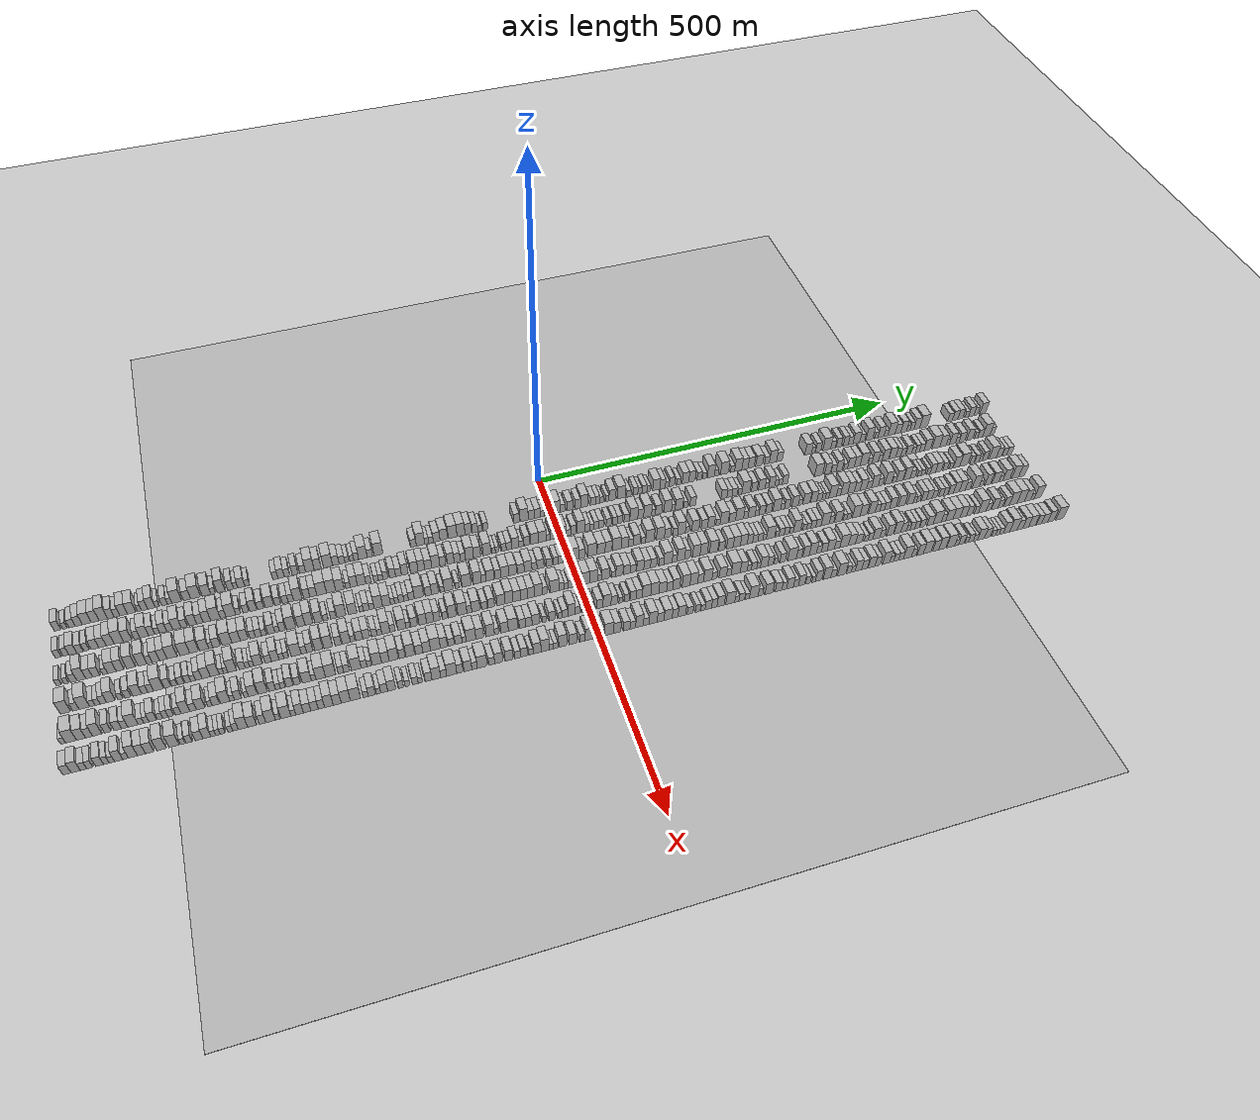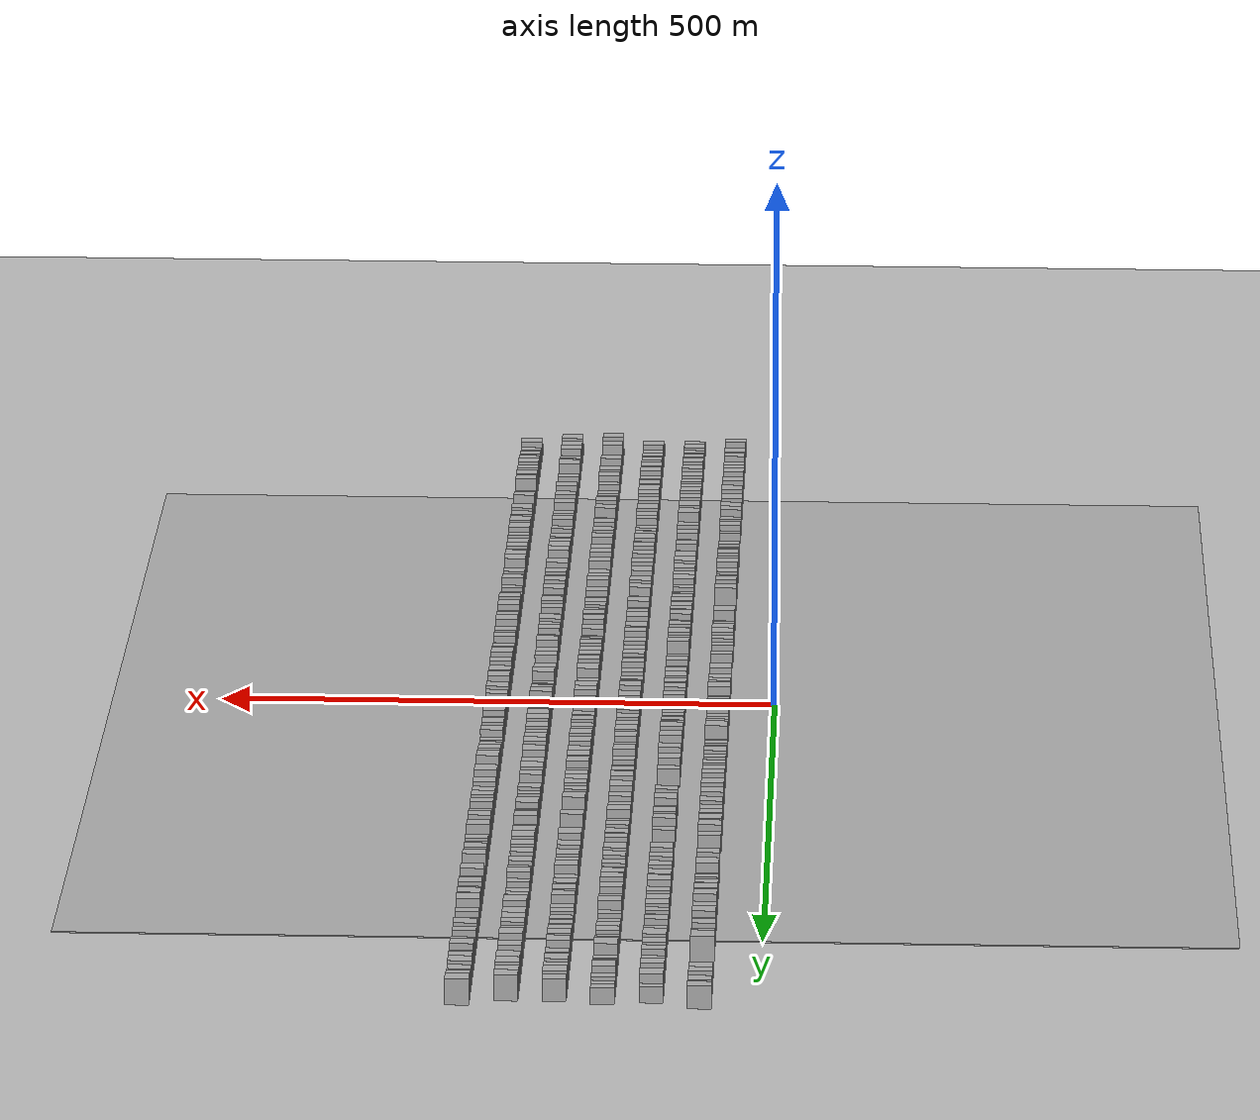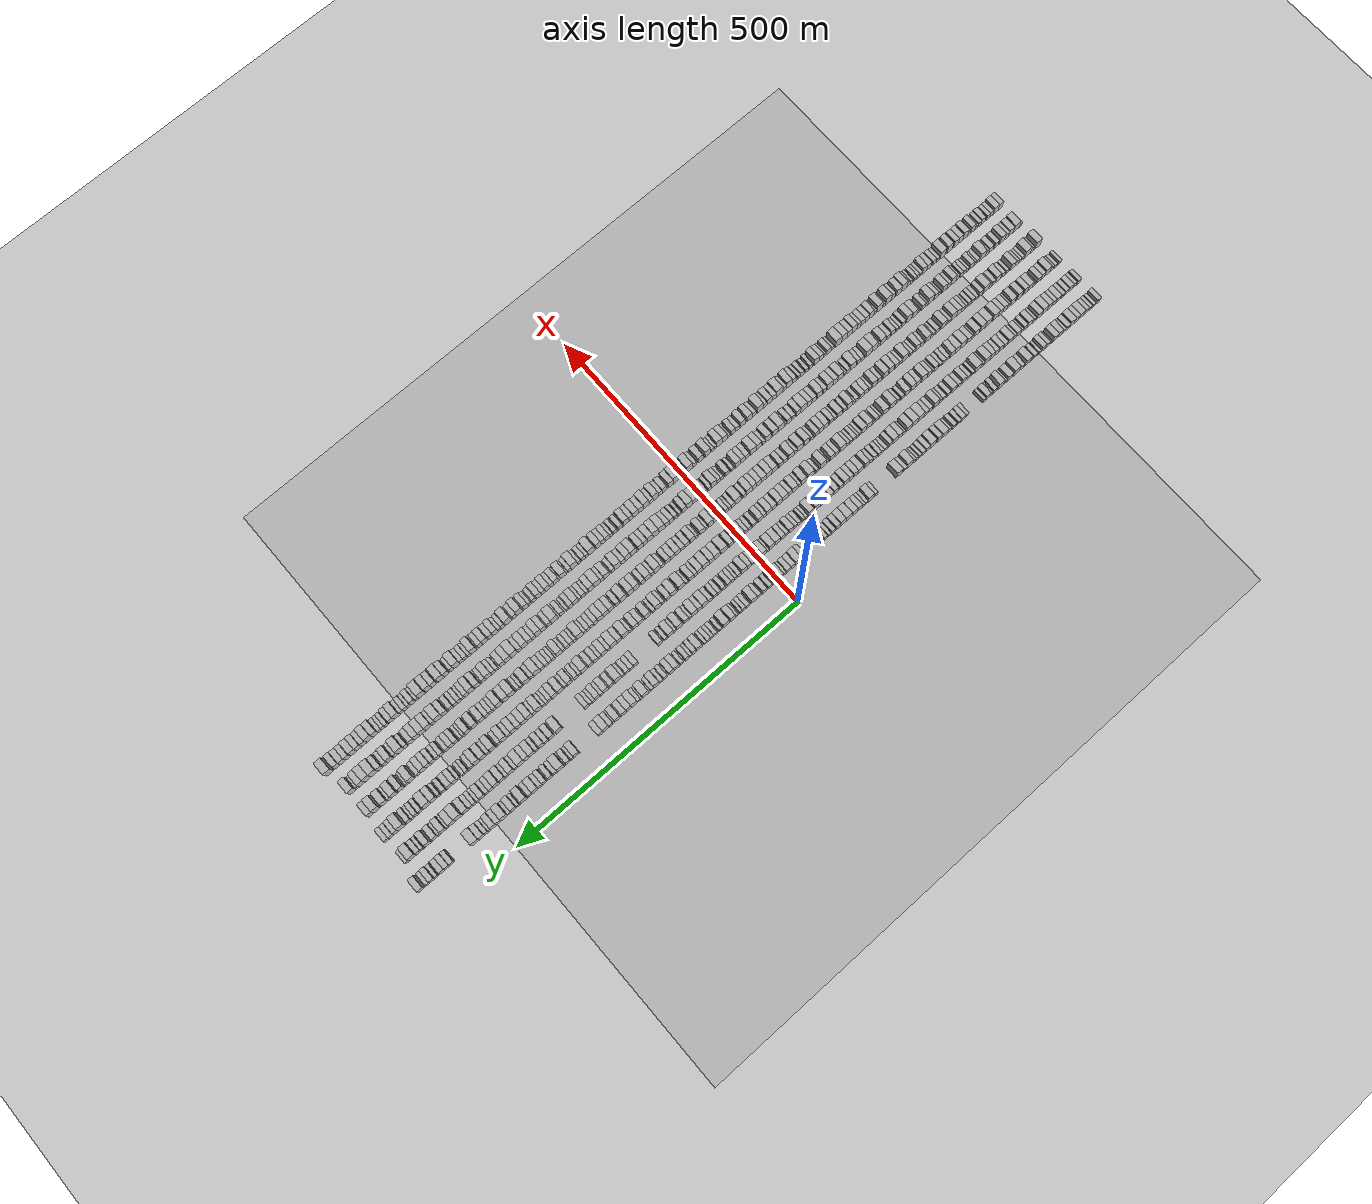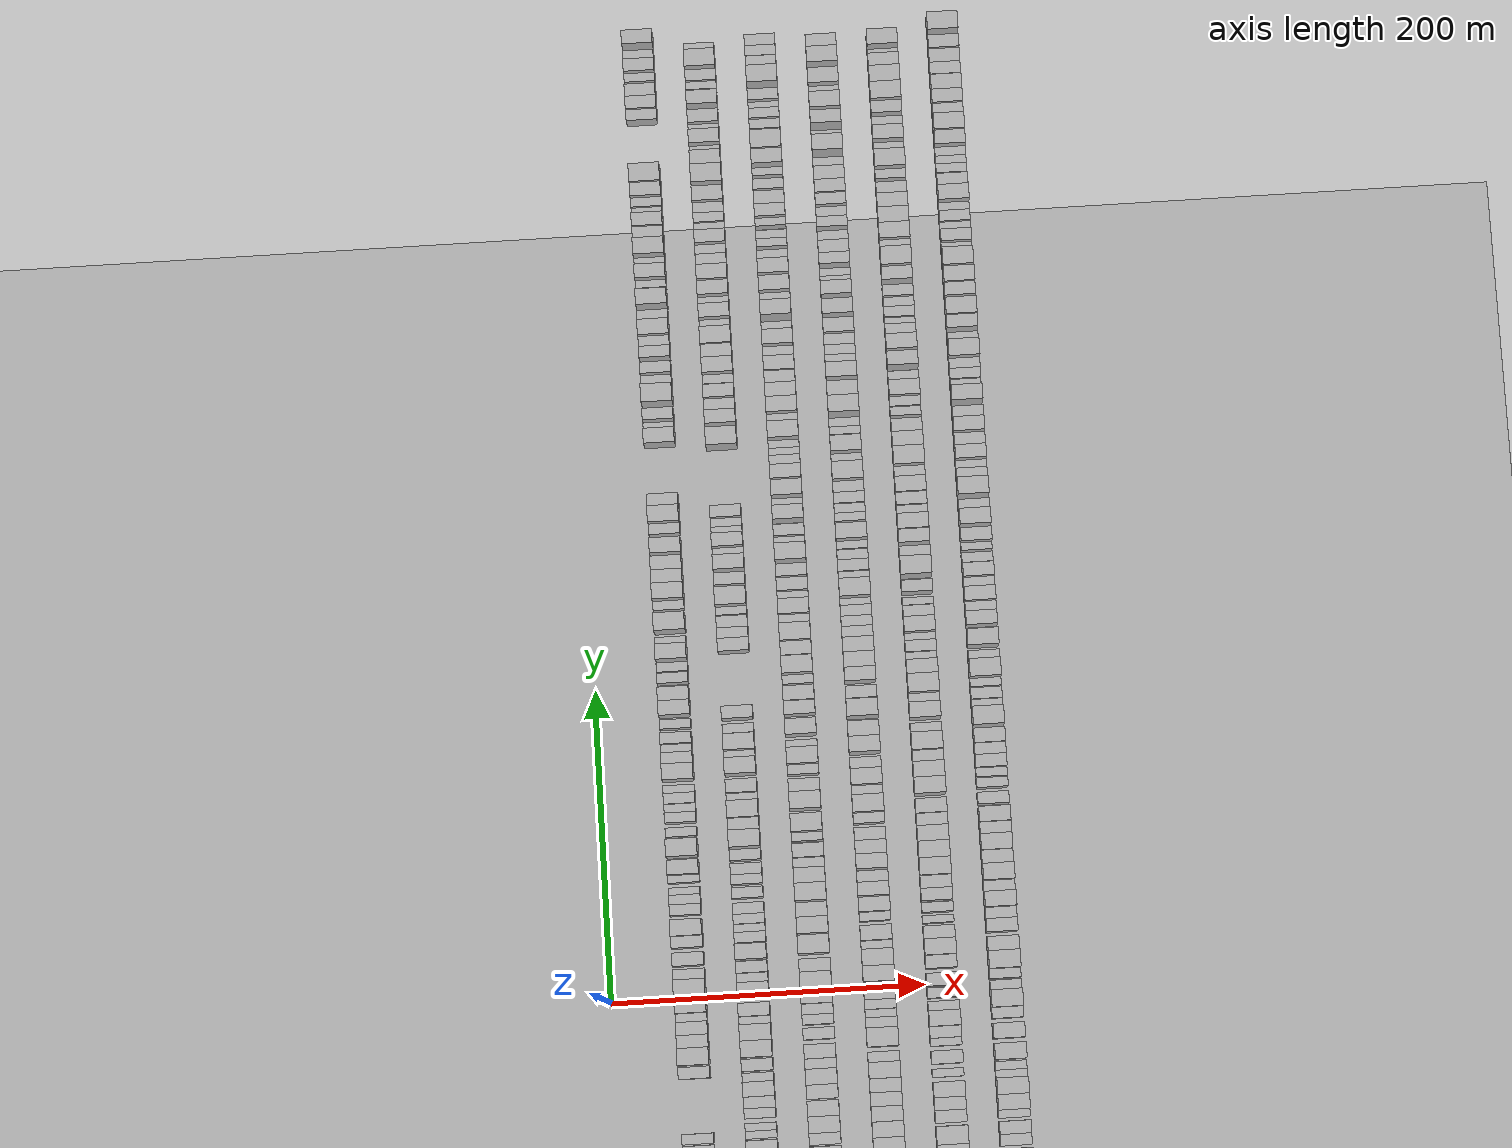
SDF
<?xml version="1.0" encoding="utf-8"?>

<sdf version="1.6">

   <world name="default">

      <gui fullscreen="0">

         <camera name="user_camera">

            <pose>-15 0 4.57585 0 0 0</pose>

            <view_controller>orbit</view_controller>

         </camera>

      </gui>

      <scene>

         <sky>

           <clouds>

             <speed>12</speed>

           </clouds>

         </sky>

         <ambient>0.4 0.4 0.4 1</ambient>

         <background>0.7 0.7 0.7 1</background>

         <shadows>1</shadows>

      </scene>

      <gravity>0 0 -9.8066</gravity>

      <magnetic_field>6e-06 2.3e-05 -4.2e-05</magnetic_field>

      <physics default="0" name="default_physics" type="ode">

         <ode>

            <solver>

               <type>quick</type>

               <iters>10</iters>

               <sor>1.0</sor>

               <use_dynamic_moi_rescaling>0</use_dynamic_moi_rescaling>

            </solver>

            <constraints>

               <cfm>0</cfm>

               <erp>0.2</erp>

               <contact_max_correcting_vel>100</contact_max_correcting_vel>

               <contact_surface_layer>0.001</contact_surface_layer>

            </constraints>

         </ode>

         <max_step_size>0.004</max_step_size>

         <real_time_factor>1</real_time_factor>

         <real_time_update_rate>250</real_time_update_rate>

      </physics>

      <light name="sun" type="directional">

         <cast_shadows>1</cast_shadows>

         <pose>0 0 10 0 0 0</pose>

         <diffuse>0.8 0.8 0.8 1</diffuse>

         <specular>0.2 0.2 0.2 1</specular>

         <attenuation>

            <range>1000</range>

            <constant>0.9</constant>

            <linear>0.01</linear>

            <quadratic>0.001</quadratic>

         </attenuation>

         <direction>-0.5 0.1 -0.9</direction>

      </light>

      <include>

         <name>ground_plane_1</name>

         <uri>model://HANNAS_ground_plane</uri>

         <pose>0 0 0  0 0 0</pose>

      </include>

      <include>

         <name>ground_plane_2</name>

         <uri>model://HANNAS_ground_plane</uri>

         <pose>100 0 0  0 0 0</pose>

      </include>

      <model name="building_1">

         <static>1</static>

         <pose frame="">50.0000 -616.2092 0 0.000000 0.000000 0.000000</pose>

         <link name="link">

            <pose frame="">0 0 9.00 0 0 0</pose>

            <collision name="collision">

               <geometry>

                  <box>

                     <size>20.0000 7.5817 18.0000</size>

                  </box>

               </geometry>

               <max_contacts>10</max_contacts>

               <surface>

                  <contact>

                     <ode/>

                  </contact>

                  <bounce/>

                  <friction>

                     <torsional>

                        <ode/>

                     </torsional>

                     <ode/>

                  </friction>

               </surface>

            </collision>

            <visual name="visual">

               <cast_shadows>0</cast_shadows>

               <geometry>

                  <box>

                     <size>20.0000 7.5817 18.0000</size>

                  </box>

               </geometry>

               <material>

                  <script>

                     <uri>model://HANNAS_wall/materials/scripts</uri>

                     <uri>model://HANNAS_wall/materials/textures</uri>

                     <name>vrc/HANNAS_wall</name>

                  </script>

               </material>

            </visual>

            <self_collide>0</self_collide>

            <enable_wind>0</enable_wind>

            <kinematic>0</kinematic>

         </link>

      </model>

      <model name="building_2">

         <static>1</static>

         <pose frame="">50.0000 -607.7861 0 0.000000 0.000000 0.000000</pose>

         <link name="link">

            <pose frame="">0 0 6.00 0 0 0</pose>

            <collision name="collision">

               <geometry>

                  <box>

                     <size>20.0000 5.2644 12.0000</size>

                  </box>

               </geometry>

               <max_contacts>10</max_contacts>

               <surface>

                  <contact>

                     <ode/>

                  </contact>

                  <bounce/>

                  <friction>

                     <torsional>

                        <ode/>

                     </torsional>

                     <ode/>

                  </friction>

               </surface>

            </collision>

            <visual name="visual">

               <cast_shadows>0</cast_shadows>

               <geometry>

                  <box>

                     <size>20.0000 5.2644 12.0000</size>

                  </box>

               </geometry>

               <material>

                  <script>

                     <uri>model://HANNAS_wall/materials/scripts</uri>

                     <uri>model://HANNAS_wall/materials/textures</uri>

                     <name>vrc/HANNAS_wall</name>

                  </script>

               </material>

            </visual>

            <self_collide>0</self_collide>

            <enable_wind>0</enable_wind>

            <kinematic>0</kinematic>

         </link>

      </model>

      <model name="building_3">

         <static>1</static>

         <pose frame="">50.0000 -599.5087 0 0.000000 0.000000 0.000000</pose>

         <link name="link">

            <pose frame="">0 0 7.50 0 0 0</pose>

            <collision name="collision">

               <geometry>

                  <box>

                     <size>20.0000 7.2904 15.0000</size>

                  </box>

               </geometry>

               <max_contacts>10</max_contacts>

               <surface>

                  <contact>

                     <ode/>

                  </contact>

                  <bounce/>

                  <friction>

                     <torsional>

                        <ode/>

                     </torsional>

                     <ode/>

                  </friction>

               </surface>

            </collision>

            <visual name="visual">

               <cast_shadows>0</cast_shadows>

               <geometry>

                  <box>

                     <size>20.0000 7.2904 15.0000</size>

                  </box>

               </geometry>

               <material>

                  <script>

                     <uri>model://HANNAS_wall/materials/scripts</uri>

                     <uri>model://HANNAS_wall/materials/textures</uri>

                     <name>vrc/HANNAS_wall</name>

                  </script>

               </material>

            </visual>

            <self_collide>0</self_collide>

            <enable_wind>0</enable_wind>

            <kinematic>0</kinematic>

         </link>

      </model>

      <model name="building_4">

         <static>1</static>

         <pose frame="">50.0000 -591.7277 0 0.000000 0.000000 0.000000</pose>

         <link name="link">

            <pose frame="">0 0 9.00 0 0 0</pose>

            <collision name="collision">

               <geometry>

                  <box>

                     <size>20.0000 8.2717 18.0000</size>

                  </box>

               </geometry>

               <max_contacts>10</max_contacts>

               <surface>

                  <contact>

                     <ode/>

                  </contact>

                  <bounce/>

                  <friction>

                     <torsional>

                        <ode/>

                     </torsional>

                     <ode/>

                  </friction>

               </surface>

            </collision>

            <visual name="visual">

               <cast_shadows>0</cast_shadows>

               <geometry>

                  <box>

                     <size>20.0000 8.2717 18.0000</size>

                  </box>

               </geometry>

               <material>

                  <script>

                     <uri>model://HANNAS_wall/materials/scripts</uri>

                     <uri>model://HANNAS_wall/materials/textures</uri>

                     <name>vrc/HANNAS_wall</name>

                  </script>

               </material>

            </visual>

            <self_collide>0</self_collide>

            <enable_wind>0</enable_wind>

            <kinematic>0</kinematic>

         </link>

      </model>

      <model name="building_5">

         <static>1</static>

         <pose frame="">50.0000 -582.4163 0 0.000000 0.000000 0.000000</pose>

         <link name="link">

            <pose frame="">0 0 10.50 0 0 0</pose>

            <collision name="collision">

               <geometry>

                  <box>

                     <size>20.0000 10.3511 21.0000</size>

                  </box>

               </geometry>

               <max_contacts>10</max_contacts>

               <surface>

                  <contact>

                     <ode/>

                  </contact>

                  <bounce/>

                  <friction>

                     <torsional>

                        <ode/>

                     </torsional>

                     <ode/>

                  </friction>

               </surface>

            </collision>

            <visual name="visual">

               <cast_shadows>0</cast_shadows>

               <geometry>

                  <box>

                     <size>20.0000 10.3511 21.0000</size>

                  </box>

               </geometry>

               <material>

                  <script>

                     <uri>model://HANNAS_wall/materials/scripts</uri>

                     <uri>model://HANNAS_wall/materials/textures</uri>

                     <name>vrc/HANNAS_wall</name>

                  </script>

               </material>

            </visual>

            <self_collide>0</self_collide>

            <enable_wind>0</enable_wind>

            <kinematic>0</kinematic>

         </link>

      </model>

      <model name="building_6">

         <static>1</static>

         <pose frame="">50.0000 -572.6963 0 0.000000 0.000000 0.000000</pose>

         <link name="link">

            <pose frame="">0 0 10.50 0 0 0</pose>

            <collision name="collision">

               <geometry>

                  <box>

                     <size>20.0000 9.0889 21.0000</size>

                  </box>

               </geometry>

               <max_contacts>10</max_contacts>

               <surface>

                  <contact>

                     <ode/>

                  </contact>

                  <bounce/>

                  <friction>

                     <torsional>

                        <ode/>

                     </torsional>

                     <ode/>

                  </friction>

               </surface>

            </collision>

            <visual name="visual">

               <cast_shadows>0</cast_shadows>

               <geometry>

                  <box>

                     <size>20.0000 9.0889 21.0000</size>

                  </box>

               </geometry>

               <material>

                  <script>

                     <uri>model://HANNAS_wall/materials/scripts</uri>

                     <uri>model://HANNAS_wall/materials/textures</uri>

                     <name>vrc/HANNAS_wall</name>

                  </script>

               </material>

            </visual>

            <self_collide>0</self_collide>

            <enable_wind>0</enable_wind>

            <kinematic>0</kinematic>

         </link>

      </model>

      <model name="building_7">

         <static>1</static>

         <pose frame="">50.0000 -563.1364 0 0.000000 0.000000 0.000000</pose>

         <link name="link">

            <pose frame="">0 0 12.00 0 0 0</pose>

            <collision name="collision">

               <geometry>

                  <box>

                     <size>20.0000 10.0308 24.0000</size>

                  </box>

               </geometry>

               <max_contacts>10</max_contacts>

               <surface>

                  <contact>

                     <ode/>

                  </contact>

                  <bounce/>

                  <friction>

                     <torsional>

                        <ode/>

                     </torsional>

                     <ode/>

                  </friction>

               </surface>

            </collision>

            <visual name="visual">

               <cast_shadows>0</cast_shadows>

               <geometry>

                  <box>

                     <size>20.0000 10.0308 24.0000</size>

                  </box>

               </geometry>

               <material>

                  <script>

                     <uri>model://HANNAS_wall/materials/scripts</uri>

                     <uri>model://HANNAS_wall/materials/textures</uri>

                     <name>vrc/HANNAS_wall</name>

                  </script>

               </material>

            </visual>

            <self_collide>0</self_collide>

            <enable_wind>0</enable_wind>

            <kinematic>0</kinematic>

         </link>

      </model>

      <model name="building_8">

         <static>1</static>

         <pose frame="">50.0000 -554.2968 0 0.000000 0.000000 0.000000</pose>

         <link name="link">

            <pose frame="">0 0 9.00 0 0 0</pose>

            <collision name="collision">

               <geometry>

                  <box>

                     <size>20.0000 7.6485 18.0000</size>

                  </box>

               </geometry>

               <max_contacts>10</max_contacts>

               <surface>

                  <contact>

                     <ode/>

                  </contact>

                  <bounce/>

                  <friction>

                     <torsional>

                        <ode/>

                     </torsional>

                     <ode/>

                  </friction>

               </surface>

            </collision>

            <visual name="visual">

               <cast_shadows>0</cast_shadows>

               <geometry>

                  <box>

                     <size>20.0000 7.6485 18.0000</size>

                  </box>

               </geometry>

               <material>

                  <script>

                     <uri>model://HANNAS_wall/materials/scripts</uri>

                     <uri>model://HANNAS_wall/materials/textures</uri>

                     <name>vrc/HANNAS_wall</name>

                  </script>

               </material>

            </visual>

            <self_collide>0</self_collide>

            <enable_wind>0</enable_wind>

            <kinematic>0</kinematic>

         </link>

      </model>

      <model name="building_9">

         <static>1</static>

         <pose frame="">50.0000 -547.1704 0 0.000000 0.000000 0.000000</pose>

         <link name="link">

            <pose frame="">0 0 7.50 0 0 0</pose>

            <collision name="collision">

               <geometry>

                  <box>

                     <size>20.0000 6.6045 15.0000</size>

                  </box>

               </geometry>

               <max_contacts>10</max_contacts>

               <surface>

                  <contact>

                     <ode/>

                  </contact>

                  <bounce/>

                  <friction>

                     <torsional>

                        <ode/>

                     </torsional>

                     <ode/>

                  </friction>

               </surface>

            </collision>

            <visual name="visual">

               <cast_shadows>0</cast_shadows>

               <geometry>

                  <box>

                     <size>20.0000 6.6045 15.0000</size>

                  </box>

               </geometry>

               <material>

                  <script>

                     <uri>model://HANNAS_wall/materials/scripts</uri>

                     <uri>model://HANNAS_wall/materials/textures</uri>

                     <name>vrc/HANNAS_wall</name>

                  </script>

               </material>

            </visual>

            <self_collide>0</self_collide>

            <enable_wind>0</enable_wind>

            <kinematic>0</kinematic>

         </link>

      </model>

      <model name="building_10">

         <static>1</static>

         <pose frame="">50.0000 -539.2522 0 0.000000 0.000000 0.000000</pose>

         <link name="link">

            <pose frame="">0 0 10.50 0 0 0</pose>

            <collision name="collision">

               <geometry>

                  <box>

                     <size>20.0000 9.2319 21.0000</size>

                  </box>

               </geometry>

               <max_contacts>10</max_contacts>

               <surface>

                  <contact>

                     <ode/>

                  </contact>

                  <bounce/>

                  <friction>

                     <torsional>

                        <ode/>

                     </torsional>

                     <ode/>

                  </friction>

               </surface>

            </collision>

            <visual name="visual">

               <cast_shadows>0</cast_shadows>

               <geometry>

                  <box>

                     <size>20.0000 9.2319 21.0000</size>

                  </box>

               </geometry>

               <material>

                  <script>

                     <uri>model://HANNAS_wall/materials/scripts</uri>

                     <uri>model://HANNAS_wall/materials/textures</uri>

                     <name>vrc/HANNAS_wall</name>

                  </script>

               </material>

            </visual>

            <self_collide>0</self_collide>

            <enable_wind>0</enable_wind>

            <kinematic>0</kinematic>

         </link>

      </model>

      <model name="building_11">

         <static>1</static>

         <pose frame="">50.0000 -529.8403 0 0.000000 0.000000 0.000000</pose>

         <link name="link">

            <pose frame="">0 0 10.50 0 0 0</pose>

            <collision name="collision">

               <geometry>

                  <box>

                     <size>20.0000 9.5919 21.0000</size>

                  </box>

               </geometry>

               <max_contacts>10</max_contacts>

               <surface>

                  <contact>

                     <ode/>

                  </contact>

                  <bounce/>

                  <friction>

                     <torsional>

                        <ode/>

                     </torsional>

                     <ode/>

                  </friction>

               </surface>

            </collision>

            <visual name="visual">

               <cast_shadows>0</cast_shadows>

               <geometry>

                  <box>

                     <size>20.0000 9.5919 21.0000</size>

                  </box>

               </geometry>

               <material>

                  <script>

                     <uri>model://HANNAS_wall/materials/scripts</uri>

                     <uri>model://HANNAS_wall/materials/textures</uri>

                     <name>vrc/HANNAS_wall</name>

                  </script>

               </material>

            </visual>

            <self_collide>0</self_collide>

            <enable_wind>0</enable_wind>

            <kinematic>0</kinematic>

         </link>

      </model>

      <model name="building_12">

         <static>1</static>

         <pose frame="">50.0000 -520.6214 0 0.000000 0.000000 0.000000</pose>

         <link name="link">

            <pose frame="">0 0 6.00 0 0 0</pose>

            <collision name="collision">

               <geometry>

                  <box>

                     <size>20.0000 4.8460 12.0000</size>

                  </box>

               </geometry>

               <max_contacts>10</max_contacts>

               <surface>

                  <contact>

                     <ode/>

                  </contact>

                  <bounce/>

                  <friction>

                     <torsional>

                        <ode/>

                     </torsional>

                     <ode/>

                  </friction>

               </surface>

            </collision>

            <visual name="visual">

               <cast_shadows>0</cast_shadows>

               <geometry>

                  <box>

                     <size>20.0000 4.8460 12.0000</size>

                  </box>

               </geometry>

               <material>

                  <script>

                     <uri>model://HANNAS_wall/materials/scripts</uri>

                     <uri>model://HANNAS_wall/materials/textures</uri>

                     <name>vrc/HANNAS_wall</name>

                  </script>

               </material>

            </visual>

            <self_collide>0</self_collide>

            <enable_wind>0</enable_wind>

            <kinematic>0</kinematic>

         </link>

      </model>

      <model name="building_13">

         <static>1</static>

         <pose frame="">50.0000 -514.4688 0 0.000000 0.000000 0.000000</pose>

         <link name="link">

            <pose frame="">0 0 9.00 0 0 0</pose>

            <collision name="collision">

               <geometry>

                  <box>

                     <size>20.0000 7.4591 18.0000</size>

                  </box>

               </geometry>

               <max_contacts>10</max_contacts>

               <surface>

                  <contact>

                     <ode/>

                  </contact>

                  <bounce/>

                  <friction>

                     <torsional>

                        <ode/>

                     </torsional>

                     <ode/>

                  </friction>

               </surface>

            </collision>

            <visual name="visual">

               <cast_shadows>0</cast_shadows>

               <geometry>

                  <box>

                     <size>20.0000 7.4591 18.0000</size>

                  </box>

               </geometry>

               <material>

                  <script>

                     <uri>model://HANNAS_wall/materials/scripts</uri>

                     <uri>model://HANNAS_wall/materials/textures</uri>

                     <name>vrc/HANNAS_wall</name>

                  </script>

               </material>

            </visual>

            <self_collide>0</self_collide>

            <enable_wind>0</enable_wind>

            <kinematic>0</kinematic>

         </link>

      </model>

      <model name="building_14">

         <static>1</static>

         <pose frame="">50.0000 -506.3366 0 0.000000 0.000000 0.000000</pose>

         <link name="link">

            <pose frame="">0 0 10.50 0 0 0</pose>

            <collision name="collision">

               <geometry>

                  <box>

                     <size>20.0000 8.8054 21.0000</size>

                  </box>

               </geometry>

               <max_contacts>10</max_contacts>

               <surface>

                  <contact>

                     <ode/>

                  </contact>

                  <bounce/>

                  <friction>

                     <torsional>

                        <ode/>

                     </torsional>

                     <ode/>

                  </friction>

               </surface>

            </collision>

            <visual name="visual">

               <cast_shadows>0</cast_shadows>

               <geometry>

                  <box>

                     <size>20.0000 8.8054 21.0000</size>

                  </box>

               </geometry>

               <material>

                  <script>

                     <uri>model://HANNAS_wall/materials/scripts</uri>

                     <uri>model://HANNAS_wall/materials/textures</uri>

                     <name>vrc/HANNAS_wall</name>

                  </script>

               </material>

            </visual>

            <self_collide>0</self_collide>

            <enable_wind>0</enable_wind>

            <kinematic>0</kinematic>

         </link>

      </model>

      <model name="building_15">

         <static>1</static>

         <pose frame="">50.0000 -499.4012 0 0.000000 0.000000 0.000000</pose>

         <link name="link">

            <pose frame="">0 0 6.00 0 0 0</pose>

            <collision name="collision">

               <geometry>

                  <box>

                     <size>20.0000 5.0653 12.0000</size>

                  </box>

               </geometry>

               <max_contacts>10</max_contacts>

               <surface>

                  <contact>

                     <ode/>

                  </contact>

                  <bounce/>

                  <friction>

                     <torsional>

                        <ode/>

                     </torsional>

                     <ode/>

                  </friction>

               </surface>

            </collision>

            <visual name="visual">

               <cast_shadows>0</cast_shadows>

               <geometry>

                  <box>

                     <size>20.0000 5.0653 12.0000</size>

                  </box>

               </geometry>

               <material>

                  <script>

                     <uri>model://HANNAS_wall/materials/scripts</uri>

                     <uri>model://HANNAS_wall/materials/textures</uri>

                     <name>vrc/HANNAS_wall</name>

                  </script>

               </material>

            </visual>

            <self_collide>0</self_collide>

            <enable_wind>0</enable_wind>

            <kinematic>0</kinematic>

         </link>

      </model>

      <model name="building_16">

         <static>1</static>

         <pose frame="">50.0000 -490.4861 0 0.000000 0.000000 0.000000</pose>

         <link name="link">

            <pose frame="">0 0 7.50 0 0 0</pose>

            <collision name="collision">

               <geometry>

                  <box>

                     <size>20.0000 6.7649 15.0000</size>

                  </box>

               </geometry>

               <max_contacts>10</max_contacts>

               <surface>

                  <contact>

                     <ode/>

                  </contact>

                  <bounce/>

                  <friction>

                     <torsional>

                        <ode/>

                     </torsional>

                     <ode/>

                  </friction>

               </surface>

            </collision>

            <visual name="visual">

               <cast_shadows>0</cast_shadows>

               <geometry>

                  <box>

                     <size>20.0000 6.7649 15.0000</size>

                  </box>

               </geometry>

               <material>

                  <script>

                     <uri>model://HANNAS_wall/materials/scripts</uri>

                     <uri>model://HANNAS_wall/materials/textures</uri>

                     <name>vrc/HANNAS_wall</name>

                  </script>

               </material>

            </visual>

            <self_collide>0</self_collide>

            <enable_wind>0</enable_wind>

            <kinematic>0</kinematic>

         </link>

      </model>

      <model name="building_17">

         <static>1</static>

         <pose frame="">50.0000 -484.4919 0 0.000000 0.000000 0.000000</pose>

         <link name="link">

            <pose frame="">0 0 6.00 0 0 0</pose>

            <collision name="collision">

               <geometry>

                  <box>

                     <size>20.0000 5.2236 12.0000</size>

                  </box>

               </geometry>

               <max_contacts>10</max_contacts>

               <surface>

                  <contact>

                     <ode/>

                  </contact>

                  <bounce/>

                  <friction>

                     <torsional>

                        <ode/>

                     </torsional>

                     <ode/>

                  </friction>

               </surface>

            </collision>

            <visual name="visual">

               <cast_shadows>0</cast_shadows>

               <geometry>

                  <box>

                     <size>20.0000 5.2236 12.0000</size>

                  </box>

               </geometry>

               <material>

                  <script>

                     <uri>model://HANNAS_wall/materials/scripts</uri>

                     <uri>model://HANNAS_wall/materials/textures</uri>

                     <name>vrc/HANNAS_wall</name>

                  </script>

               </material>

            </visual>

            <self_collide>0</self_collide>

            <enable_wind>0</enable_wind>

            <kinematic>0</kinematic>

         </link>

      </model>

      <model name="building_18">

         <static>1</static>

         <pose frame="">50.0000 -475.9664 0 0.000000 0.000000 0.000000</pose>

         <link name="link">

            <pose frame="">0 0 12.00 0 0 0</pose>

            <collision name="collision">

               <geometry>

                  <box>

                     <size>20.0000 11.8273 24.0000</size>

                  </box>

               </geometry>

               <max_contacts>10</max_contacts>

               <surface>

                  <contact>

                     <ode/>

                  </contact>

                  <bounce/>

                  <friction>

                     <torsional>

                        <ode/>

                     </torsional>

                     <ode/>

                  </friction>

               </surface>

            </collision>

            <visual name="visual">

               <cast_shadows>0</cast_shadows>

               <geometry>

                  <box>

                     <size>20.0000 11.8273 24.0000</size>

                  </box>

               </geometry>

               <material>

                  <script>

                     <uri>model://HANNAS_wall/materials/scripts</uri>

                     <uri>model://HANNAS_wall/materials/textures</uri>

                     <name>vrc/HANNAS_wall</name>

                  </script>

               </material>

            </visual>

            <self_collide>0</self_collide>

            <enable_wind>0</enable_wind>

            <kinematic>0</kinematic>

         </link>

      </model>

      <model name="building_19">

         <static>1</static>

         <pose frame="">50.0000 -463.6933 0 0.000000 0.000000 0.000000</pose>

         <link name="link">

            <pose frame="">0 0 9.00 0 0 0</pose>

            <collision name="collision">

               <geometry>

                  <box>

                     <size>20.0000 8.7189 18.0000</size>

                  </box>

               </geometry>

               <max_contacts>10</max_contacts>

               <surface>

                  <contact>

                     <ode/>

                  </contact>

                  <bounce/>

                  <friction>

                     <torsional>

                        <ode/>

                     </torsional>

                     <ode/>

                  </friction>

               </surface>

            </collision>

            <visual name="visual">

               <cast_shadows>0</cast_shadows>

               <geometry>

                  <box>

                     <size>20.0000 8.7189 18.0000</size>

                  </box>

               </geometry>

               <material>

                  <script>

                     <uri>model://HANNAS_wall/materials/scripts</uri>

                     <uri>model://HANNAS_wall/materials/textures</uri>

                     <name>vrc/HANNAS_wall</name>

                  </script>

               </material>

            </visual>

            <self_collide>0</self_collide>

            <enable_wind>0</enable_wind>

            <kinematic>0</kinematic>

         </link>

      </model>

      <model name="building_20">

         <static>1</static>

         <pose frame="">50.0000 -453.3681 0 0.000000 0.000000 0.000000</pose>

         <link name="link">

            <pose frame="">0 0 12.00 0 0 0</pose>

            <collision name="collision">

               <geometry>

                  <box>

                     <size>20.0000 11.9314 24.0000</size>

                  </box>

               </geometry>

               <max_contacts>10</max_contacts>

               <surface>

                  <contact>

                     <ode/>

                  </contact>

                  <bounce/>

                  <friction>

                     <torsional>

                        <ode/>

                     </torsional>

                     <ode/>

                  </friction>

               </surface>

            </collision>

            <visual name="visual">

               <cast_shadows>0</cast_shadows>

               <geometry>

                  <box>

                     <size>20.0000 11.9314 24.0000</size>

                  </box>

               </geometry>

               <material>

                  <script>

                     <uri>model://HANNAS_wall/materials/scripts</uri>

                     <uri>model://HANNAS_wall/materials/textures</uri>

                     <name>vrc/HANNAS_wall</name>

                  </script>

               </material>

            </visual>

            <self_collide>0</self_collide>

            <enable_wind>0</enable_wind>

            <kinematic>0</kinematic>

         </link>

      </model>

      <model name="building_21">

         <static>1</static>

         <pose frame="">50.0000 -440.2463 0 0.000000 0.000000 0.000000</pose>

         <link name="link">

            <pose frame="">0 0 10.50 0 0 0</pose>

            <collision name="collision">

               <geometry>

                  <box>

                     <size>20.0000 10.3122 21.0000</size>

                  </box>

               </geometry>

               <max_contacts>10</max_contacts>

               <surface>

                  <contact>

                     <ode/>

                  </contact>

                  <bounce/>

                  <friction>

                     <torsional>

                        <ode/>

                     </torsional>

                     <ode/>

                  </friction>

               </surface>

            </collision>

            <visual name="visual">

               <cast_shadows>0</cast_shadows>

               <geometry>

                  <box>

                     <size>20.0000 10.3122 21.0000</size>

                  </box>

               </geometry>

               <material>

                  <script>

                     <uri>model://HANNAS_wall/materials/scripts</uri>

                     <uri>model://HANNAS_wall/materials/textures</uri>

                     <name>vrc/HANNAS_wall</name>

                  </script>

               </material>

            </visual>

            <self_collide>0</self_collide>

            <enable_wind>0</enable_wind>

            <kinematic>0</kinematic>

         </link>

      </model>

      <model name="building_22">

         <static>1</static>

         <pose frame="">50.0000 -432.3361 0 0.000000 0.000000 0.000000</pose>

         <link name="link">

            <pose frame="">0 0 6.00 0 0 0</pose>

            <collision name="collision">

               <geometry>

                  <box>

                     <size>20.0000 5.5081 12.0000</size>

                  </box>

               </geometry>

               <max_contacts>10</max_contacts>

               <surface>

                  <contact>

                     <ode/>

                  </contact>

                  <bounce/>

                  <friction>

                     <torsional>

                        <ode/>

                     </torsional>

                     <ode/>

                  </friction>

               </surface>

            </collision>

            <visual name="visual">

               <cast_shadows>0</cast_shadows>

               <geometry>

                  <box>

                     <size>20.0000 5.5081 12.0000</size>

                  </box>

               </geometry>

               <material>

                  <script>

                     <uri>model://HANNAS_wall/materials/scripts</uri>

                     <uri>model://HANNAS_wall/materials/textures</uri>

                     <name>vrc/HANNAS_wall</name>

                  </script>

               </material>

            </visual>

            <self_collide>0</self_collide>

            <enable_wind>0</enable_wind>

            <kinematic>0</kinematic>

         </link>

      </model>

      <model name="building_23">

         <static>1</static>

         <pose frame="">50.0000 -422.5944 0 0.000000 0.000000 0.000000</pose>

         <link name="link">

            <pose frame="">0 0 12.00 0 0 0</pose>

            <collision name="collision">

               <geometry>

                  <box>

                     <size>20.0000 9.9753 24.0000</size>

                  </box>

               </geometry>

               <max_contacts>10</max_contacts>

               <surface>

                  <contact>

                     <ode/>

                  </contact>

                  <bounce/>

                  <friction>

                     <torsional>

                        <ode/>

                     </torsional>

                     <ode/>

                  </friction>

               </surface>

            </collision>

            <visual name="visual">

               <cast_shadows>0</cast_shadows>

               <geometry>

                  <box>

                     <size>20.0000 9.9753 24.0000</size>

                  </box>

               </geometry>

               <material>

                  <script>

                     <uri>model://HANNAS_wall/materials/scripts</uri>

                     <uri>model://HANNAS_wall/materials/textures</uri>

                     <name>vrc/HANNAS_wall</name>

                  </script>

               </material>

            </visual>

            <self_collide>0</self_collide>

            <enable_wind>0</enable_wind>

            <kinematic>0</kinematic>

         </link>

      </model>

      <model name="building_24">

         <static>1</static>

         <pose frame="">50.0000 -410.9601 0 0.000000 0.000000 0.000000</pose>

         <link name="link">

            <pose frame="">0 0 9.00 0 0 0</pose>

            <collision name="collision">

               <geometry>

                  <box>

                     <size>20.0000 7.2933 18.0000</size>

                  </box>

               </geometry>

               <max_contacts>10</max_contacts>

               <surface>

                  <contact>

                     <ode/>

                  </contact>

                  <bounce/>

                  <friction>

                     <torsional>

                        <ode/>

                     </torsional>

                     <ode/>

                  </friction>

               </surface>

            </collision>

            <visual name="visual">

               <cast_shadows>0</cast_shadows>

               <geometry>

                  <box>

                     <size>20.0000 7.2933 18.0000</size>

                  </box>

               </geometry>

               <material>

                  <script>

                     <uri>model://HANNAS_wall/materials/scripts</uri>

                     <uri>model://HANNAS_wall/materials/textures</uri>

                     <name>vrc/HANNAS_wall</name>

                  </script>

               </material>

            </visual>

            <self_collide>0</self_collide>

            <enable_wind>0</enable_wind>

            <kinematic>0</kinematic>

         </link>

      </model>

      <model name="building_25">

         <static>1</static>

         <pose frame="">50.0000 -404.7500 0 0.000000 0.000000 0.000000</pose>

         <link name="link">

            <pose frame="">0 0 6.00 0 0 0</pose>

            <collision name="collision">

               <geometry>

                  <box>

                     <size>20.0000 5.1268 12.0000</size>

                  </box>

               </geometry>

               <max_contacts>10</max_contacts>

               <surface>

                  <contact>

                     <ode/>

                  </contact>

                  <bounce/>

                  <friction>

                     <torsional>

                        <ode/>

                     </torsional>

                     <ode/>

                  </friction>

               </surface>

            </collision>

            <visual name="visual">

               <cast_shadows>0</cast_shadows>

               <geometry>

                  <box>

                     <size>20.0000 5.1268 12.0000</size>

                  </box>

               </geometry>

               <material>

                  <script>

                     <uri>model://HANNAS_wall/materials/scripts</uri>

                     <uri>model://HANNAS_wall/materials/textures</uri>

                     <name>vrc/HANNAS_wall</name>

                  </script>

               </material>

            </visual>

            <self_collide>0</self_collide>

            <enable_wind>0</enable_wind>

            <kinematic>0</kinematic>

         </link>

      </model>

      <model name="building_26">

         <static>1</static>

         <pose frame="">50.0000 -397.8932 0 0.000000 0.000000 0.000000</pose>

         <link name="link">

            <pose frame="">0 0 9.00 0 0 0</pose>

            <collision name="collision">

               <geometry>

                  <box>

                     <size>20.0000 8.5868 18.0000</size>

                  </box>

               </geometry>

               <max_contacts>10</max_contacts>

               <surface>

                  <contact>

                     <ode/>

                  </contact>

                  <bounce/>

                  <friction>

                     <torsional>

                        <ode/>

                     </torsional>

                     <ode/>

                  </friction>

               </surface>

            </collision>

            <visual name="visual">

               <cast_shadows>0</cast_shadows>

               <geometry>

                  <box>

                     <size>20.0000 8.5868 18.0000</size>

                  </box>

               </geometry>

               <material>

                  <script>

                     <uri>model://HANNAS_wall/materials/scripts</uri>

                     <uri>model://HANNAS_wall/materials/textures</uri>

                     <name>vrc/HANNAS_wall</name>

                  </script>

               </material>

            </visual>

            <self_collide>0</self_collide>

            <enable_wind>0</enable_wind>

            <kinematic>0</kinematic>

         </link>

      </model>

      <model name="building_27">

         <static>1</static>

         <pose frame="">50.0000 -390.7681 0 0.000000 0.000000 0.000000</pose>

         <link name="link">

            <pose frame="">0 0 6.00 0 0 0</pose>

            <collision name="collision">

               <geometry>

                  <box>

                     <size>20.0000 5.6634 12.0000</size>

                  </box>

               </geometry>

               <max_contacts>10</max_contacts>

               <surface>

                  <contact>

                     <ode/>

                  </contact>

                  <bounce/>

                  <friction>

                     <torsional>

                        <ode/>

                     </torsional>

                     <ode/>

                  </friction>

               </surface>

            </collision>

            <visual name="visual">

               <cast_shadows>0</cast_shadows>

               <geometry>

                  <box>

                     <size>20.0000 5.6634 12.0000</size>

                  </box>

               </geometry>

               <material>

                  <script>

                     <uri>model://HANNAS_wall/materials/scripts</uri>

                     <uri>model://HANNAS_wall/materials/textures</uri>

                     <name>vrc/HANNAS_wall</name>

                  </script>

               </material>

            </visual>

            <self_collide>0</self_collide>

            <enable_wind>0</enable_wind>

            <kinematic>0</kinematic>

         </link>

      </model>

      <model name="building_28">

         <static>1</static>

         <pose frame="">50.0000 -356.2573 0 0.000000 0.000000 0.000000</pose>

         <link name="link">

            <pose frame="">0 0 7.50 0 0 0</pose>

            <collision name="collision">

               <geometry>

                  <box>

                     <size>20.0000 6.4528 15.0000</size>

                  </box>

               </geometry>

               <max_contacts>10</max_contacts>

               <surface>

                  <contact>

                     <ode/>

                  </contact>

                  <bounce/>

                  <friction>

                     <torsional>

                        <ode/>

                     </torsional>

                     <ode/>

                  </friction>

               </surface>

            </collision>

            <visual name="visual">

               <cast_shadows>0</cast_shadows>

               <geometry>

                  <box>

                     <size>20.0000 6.4528 15.0000</size>

                  </box>

               </geometry>

               <material>

                  <script>

                     <uri>model://HANNAS_wall/materials/scripts</uri>

                     <uri>model://HANNAS_wall/materials/textures</uri>

                     <name>vrc/HANNAS_wall</name>

                  </script>

               </material>

            </visual>

            <self_collide>0</self_collide>

            <enable_wind>0</enable_wind>

            <kinematic>0</kinematic>

         </link>

      </model>

      <model name="building_29">

         <static>1</static>

         <pose frame="">50.0000 -349.0196 0 0.000000 0.000000 0.000000</pose>

         <link name="link">

            <pose frame="">0 0 9.00 0 0 0</pose>

            <collision name="collision">

               <geometry>

                  <box>

                     <size>20.0000 8.0226 18.0000</size>

                  </box>

               </geometry>

               <max_contacts>10</max_contacts>

               <surface>

                  <contact>

                     <ode/>

                  </contact>

                  <bounce/>

                  <friction>

                     <torsional>

                        <ode/>

                     </torsional>

                     <ode/>

                  </friction>

               </surface>

            </collision>

            <visual name="visual">

               <cast_shadows>0</cast_shadows>

               <geometry>

                  <box>

                     <size>20.0000 8.0226 18.0000</size>

                  </box>

               </geometry>

               <material>

                  <script>

                     <uri>model://HANNAS_wall/materials/scripts</uri>

                     <uri>model://HANNAS_wall/materials/textures</uri>

                     <name>vrc/HANNAS_wall</name>

                  </script>

               </material>

            </visual>

            <self_collide>0</self_collide>

            <enable_wind>0</enable_wind>

            <kinematic>0</kinematic>

         </link>

      </model>

      <model name="building_30">

         <static>1</static>

         <pose frame="">50.0000 -341.6316 0 0.000000 0.000000 0.000000</pose>

         <link name="link">

            <pose frame="">0 0 7.50 0 0 0</pose>

            <collision name="collision">

               <geometry>

                  <box>

                     <size>20.0000 6.7535 15.0000</size>

                  </box>

               </geometry>

               <max_contacts>10</max_contacts>

               <surface>

                  <contact>

                     <ode/>

                  </contact>

                  <bounce/>

                  <friction>

                     <torsional>

                        <ode/>

                     </torsional>

                     <ode/>

                  </friction>

               </surface>

            </collision>

            <visual name="visual">

               <cast_shadows>0</cast_shadows>

               <geometry>

                  <box>

                     <size>20.0000 6.7535 15.0000</size>

                  </box>

               </geometry>

               <material>

                  <script>

                     <uri>model://HANNAS_wall/materials/scripts</uri>

                     <uri>model://HANNAS_wall/materials/textures</uri>

                     <name>vrc/HANNAS_wall</name>

                  </script>

               </material>

            </visual>

            <self_collide>0</self_collide>

            <enable_wind>0</enable_wind>

            <kinematic>0</kinematic>

         </link>

      </model>

      <model name="building_31">

         <static>1</static>

         <pose frame="">50.0000 -331.5749 0 0.000000 0.000000 0.000000</pose>

         <link name="link">

            <pose frame="">0 0 9.00 0 0 0</pose>

            <collision name="collision">

               <geometry>

                  <box>

                     <size>20.0000 7.3599 18.0000</size>

                  </box>

               </geometry>

               <max_contacts>10</max_contacts>

               <surface>

                  <contact>

                     <ode/>

                  </contact>

                  <bounce/>

                  <friction>

                     <torsional>

                        <ode/>

                     </torsional>

                     <ode/>

                  </friction>

               </surface>

            </collision>

            <visual name="visual">

               <cast_shadows>0</cast_shadows>

               <geometry>

                  <box>

                     <size>20.0000 7.3599 18.0000</size>

                  </box>

               </geometry>

               <material>

                  <script>

                     <uri>model://HANNAS_wall/materials/scripts</uri>

                     <uri>model://HANNAS_wall/materials/textures</uri>

                     <name>vrc/HANNAS_wall</name>

                  </script>

               </material>

            </visual>

            <self_collide>0</self_collide>

            <enable_wind>0</enable_wind>

            <kinematic>0</kinematic>

         </link>

      </model>

      <model name="building_32">

         <static>1</static>

         <pose frame="">50.0000 -322.2869 0 0.000000 0.000000 0.000000</pose>

         <link name="link">

            <pose frame="">0 0 7.50 0 0 0</pose>

            <collision name="collision">

               <geometry>

                  <box>

                     <size>20.0000 7.2160 15.0000</size>

                  </box>

               </geometry>

               <max_contacts>10</max_contacts>

               <surface>

                  <contact>

                     <ode/>

                  </contact>

                  <bounce/>

                  <friction>

                     <torsional>

                        <ode/>

                     </torsional>

                     <ode/>

                  </friction>

               </surface>

            </collision>

            <visual name="visual">

               <cast_shadows>0</cast_shadows>

               <geometry>

                  <box>

                     <size>20.0000 7.2160 15.0000</size>

                  </box>

               </geometry>

               <material>

                  <script>

                     <uri>model://HANNAS_wall/materials/scripts</uri>

                     <uri>model://HANNAS_wall/materials/textures</uri>

                     <name>vrc/HANNAS_wall</name>

                  </script>

               </material>

            </visual>

            <self_collide>0</self_collide>

            <enable_wind>0</enable_wind>

            <kinematic>0</kinematic>

         </link>

      </model>

      <model name="building_33">

         <static>1</static>

         <pose frame="">50.0000 -313.2828 0 0.000000 0.000000 0.000000</pose>

         <link name="link">

            <pose frame="">0 0 12.00 0 0 0</pose>

            <collision name="collision">

               <geometry>

                  <box>

                     <size>20.0000 10.7922 24.0000</size>

                  </box>

               </geometry>

               <max_contacts>10</max_contacts>

               <surface>

                  <contact>

                     <ode/>

                  </contact>

                  <bounce/>

                  <friction>

                     <torsional>

                        <ode/>

                     </torsional>

                     <ode/>

                  </friction>

               </surface>

            </collision>

            <visual name="visual">

               <cast_shadows>0</cast_shadows>

               <geometry>

                  <box>

                     <size>20.0000 10.7922 24.0000</size>

                  </box>

               </geometry>

               <material>

                  <script>

                     <uri>model://HANNAS_wall/materials/scripts</uri>

                     <uri>model://HANNAS_wall/materials/textures</uri>

                     <name>vrc/HANNAS_wall</name>

                  </script>

               </material>

            </visual>

            <self_collide>0</self_collide>

            <enable_wind>0</enable_wind>

            <kinematic>0</kinematic>

         </link>

      </model>

      <model name="building_34">

         <static>1</static>

         <pose frame="">50.0000 -303.5560 0 0.000000 0.000000 0.000000</pose>

         <link name="link">

            <pose frame="">0 0 10.50 0 0 0</pose>

            <collision name="collision">

               <geometry>

                  <box>

                     <size>20.0000 8.6615 21.0000</size>

                  </box>

               </geometry>

               <max_contacts>10</max_contacts>

               <surface>

                  <contact>

                     <ode/>

                  </contact>

                  <bounce/>

                  <friction>

                     <torsional>

                        <ode/>

                     </torsional>

                     <ode/>

                  </friction>

               </surface>

            </collision>

            <visual name="visual">

               <cast_shadows>0</cast_shadows>

               <geometry>

                  <box>

                     <size>20.0000 8.6615 21.0000</size>

                  </box>

               </geometry>

               <material>

                  <script>

                     <uri>model://HANNAS_wall/materials/scripts</uri>

                     <uri>model://HANNAS_wall/materials/textures</uri>

                     <name>vrc/HANNAS_wall</name>

                  </script>

               </material>

            </visual>

            <self_collide>0</self_collide>

            <enable_wind>0</enable_wind>

            <kinematic>0</kinematic>

         </link>

      </model>

      <model name="building_35">

         <static>1</static>

         <pose frame="">50.0000 -290.4824 0 0.000000 0.000000 0.000000</pose>

         <link name="link">

            <pose frame="">0 0 12.00 0 0 0</pose>

            <collision name="collision">

               <geometry>

                  <box>

                     <size>20.0000 11.4858 24.0000</size>

                  </box>

               </geometry>

               <max_contacts>10</max_contacts>

               <surface>

                  <contact>

                     <ode/>

                  </contact>

                  <bounce/>

                  <friction>

                     <torsional>

                        <ode/>

                     </torsional>

                     <ode/>

                  </friction>

               </surface>

            </collision>

            <visual name="visual">

               <cast_shadows>0</cast_shadows>

               <geometry>

                  <box>

                     <size>20.0000 11.4858 24.0000</size>

                  </box>

               </geometry>

               <material>

                  <script>

                     <uri>model://HANNAS_wall/materials/scripts</uri>

                     <uri>model://HANNAS_wall/materials/textures</uri>

                     <name>vrc/HANNAS_wall</name>

                  </script>

               </material>

            </visual>

            <self_collide>0</self_collide>

            <enable_wind>0</enable_wind>

            <kinematic>0</kinematic>

         </link>

      </model>

      <model name="building_36">

         <static>1</static>

         <pose frame="">50.0000 -280.6749 0 0.000000 0.000000 0.000000</pose>

         <link name="link">

            <pose frame="">0 0 9.00 0 0 0</pose>

            <collision name="collision">

               <geometry>

                  <box>

                     <size>20.0000 8.1293 18.0000</size>

                  </box>

               </geometry>

               <max_contacts>10</max_contacts>

               <surface>

                  <contact>

                     <ode/>

                  </contact>

                  <bounce/>

                  <friction>

                     <torsional>

                        <ode/>

                     </torsional>

                     <ode/>

                  </friction>

               </surface>

            </collision>

            <visual name="visual">

               <cast_shadows>0</cast_shadows>

               <geometry>

                  <box>

                     <size>20.0000 8.1293 18.0000</size>

                  </box>

               </geometry>

               <material>

                  <script>

                     <uri>model://HANNAS_wall/materials/scripts</uri>

                     <uri>model://HANNAS_wall/materials/textures</uri>

                     <name>vrc/HANNAS_wall</name>

                  </script>

               </material>

            </visual>

            <self_collide>0</self_collide>

            <enable_wind>0</enable_wind>

            <kinematic>0</kinematic>

         </link>

      </model>

      <model name="building_37">

         <static>1</static>

         <pose frame="">50.0000 -273.0091 0 0.000000 0.000000 0.000000</pose>

         <link name="link">

            <pose frame="">0 0 7.50 0 0 0</pose>

            <collision name="collision">

               <geometry>

                  <box>

                     <size>20.0000 7.2023 15.0000</size>

                  </box>

               </geometry>

               <max_contacts>10</max_contacts>

               <surface>

                  <contact>

                     <ode/>

                  </contact>

                  <bounce/>

                  <friction>

                     <torsional>

                        <ode/>

                     </torsional>

                     <ode/>

                  </friction>

               </surface>

            </collision>

            <visual name="visual">

               <cast_shadows>0</cast_shadows>

               <geometry>

                  <box>

                     <size>20.0000 7.2023 15.0000</size>

                  </box>

               </geometry>

               <material>

                  <script>

                     <uri>model://HANNAS_wall/materials/scripts</uri>

                     <uri>model://HANNAS_wall/materials/textures</uri>

                     <name>vrc/HANNAS_wall</name>

                  </script>

               </material>

            </visual>

            <self_collide>0</self_collide>

            <enable_wind>0</enable_wind>

            <kinematic>0</kinematic>

         </link>

      </model>

      <model name="building_38">

         <static>1</static>

         <pose frame="">50.0000 -266.8126 0 0.000000 0.000000 0.000000</pose>

         <link name="link">

            <pose frame="">0 0 6.00 0 0 0</pose>

            <collision name="collision">

               <geometry>

                  <box>

                     <size>20.0000 5.1906 12.0000</size>

                  </box>

               </geometry>

               <max_contacts>10</max_contacts>

               <surface>

                  <contact>

                     <ode/>

                  </contact>

                  <bounce/>

                  <friction>

                     <torsional>

                        <ode/>

                     </torsional>

                     <ode/>

                  </friction>

               </surface>

            </collision>

            <visual name="visual">

               <cast_shadows>0</cast_shadows>

               <geometry>

                  <box>

                     <size>20.0000 5.1906 12.0000</size>

                  </box>

               </geometry>

               <material>

                  <script>

                     <uri>model://HANNAS_wall/materials/scripts</uri>

                     <uri>model://HANNAS_wall/materials/textures</uri>

                     <name>vrc/HANNAS_wall</name>

                  </script>

               </material>

            </visual>

            <self_collide>0</self_collide>

            <enable_wind>0</enable_wind>

            <kinematic>0</kinematic>

         </link>

      </model>

      <model name="building_39">

         <static>1</static>

         <pose frame="">50.0000 -260.6925 0 0.000000 0.000000 0.000000</pose>

         <link name="link">

            <pose frame="">0 0 6.00 0 0 0</pose>

            <collision name="collision">

               <geometry>

                  <box>

                     <size>20.0000 5.0496 12.0000</size>

                  </box>

               </geometry>

               <max_contacts>10</max_contacts>

               <surface>

                  <contact>

                     <ode/>

                  </contact>

                  <bounce/>

                  <friction>

                     <torsional>

                        <ode/>

                     </torsional>

                     <ode/>

                  </friction>

               </surface>

            </collision>

            <visual name="visual">

               <cast_shadows>0</cast_shadows>

               <geometry>

                  <box>

                     <size>20.0000 5.0496 12.0000</size>

                  </box>

               </geometry>

               <material>

                  <script>

                     <uri>model://HANNAS_wall/materials/scripts</uri>

                     <uri>model://HANNAS_wall/materials/textures</uri>

                     <name>vrc/HANNAS_wall</name>

                  </script>

               </material>

            </visual>

            <self_collide>0</self_collide>

            <enable_wind>0</enable_wind>

            <kinematic>0</kinematic>

         </link>

      </model>

      <model name="building_40">

         <static>1</static>

         <pose frame="">50.0000 -255.1026 0 0.000000 0.000000 0.000000</pose>

         <link name="link">

            <pose frame="">0 0 7.50 0 0 0</pose>

            <collision name="collision">

               <geometry>

                  <box>

                     <size>20.0000 6.1303 15.0000</size>

                  </box>

               </geometry>

               <max_contacts>10</max_contacts>

               <surface>

                  <contact>

                     <ode/>

                  </contact>

                  <bounce/>

                  <friction>

                     <torsional>

                        <ode/>

                     </torsional>

                     <ode/>

                  </friction>

               </surface>

            </collision>

            <visual name="visual">

               <cast_shadows>0</cast_shadows>

               <geometry>

                  <box>

                     <size>20.0000 6.1303 15.0000</size>

                  </box>

               </geometry>

               <material>

                  <script>

                     <uri>model://HANNAS_wall/materials/scripts</uri>

                     <uri>model://HANNAS_wall/materials/textures</uri>

                     <name>vrc/HANNAS_wall</name>

                  </script>

               </material>

            </visual>

            <self_collide>0</self_collide>

            <enable_wind>0</enable_wind>

            <kinematic>0</kinematic>

         </link>

      </model>

      <model name="building_41">

         <static>1</static>

         <pose frame="">50.0000 -246.5571 0 0.000000 0.000000 0.000000</pose>

         <link name="link">

            <pose frame="">0 0 12.00 0 0 0</pose>

            <collision name="collision">

               <geometry>

                  <box>

                     <size>20.0000 10.9608 24.0000</size>

                  </box>

               </geometry>

               <max_contacts>10</max_contacts>

               <surface>

                  <contact>

                     <ode/>

                  </contact>

                  <bounce/>

                  <friction>

                     <torsional>

                        <ode/>

                     </torsional>

                     <ode/>

                  </friction>

               </surface>

            </collision>

            <visual name="visual">

               <cast_shadows>0</cast_shadows>

               <geometry>

                  <box>

                     <size>20.0000 10.9608 24.0000</size>

                  </box>

               </geometry>

               <material>

                  <script>

                     <uri>model://HANNAS_wall/materials/scripts</uri>

                     <uri>model://HANNAS_wall/materials/textures</uri>

                     <name>vrc/HANNAS_wall</name>

                  </script>

               </material>

            </visual>

            <self_collide>0</self_collide>

            <enable_wind>0</enable_wind>

            <kinematic>0</kinematic>

         </link>

      </model>

      <model name="building_42">

         <static>1</static>

         <pose frame="">50.0000 -237.6984 0 0.000000 0.000000 0.000000</pose>

         <link name="link">

            <pose frame="">0 0 7.50 0 0 0</pose>

            <collision name="collision">

               <geometry>

                  <box>

                     <size>20.0000 6.7566 15.0000</size>

                  </box>

               </geometry>

               <max_contacts>10</max_contacts>

               <surface>

                  <contact>

                     <ode/>

                  </contact>

                  <bounce/>

                  <friction>

                     <torsional>

                        <ode/>

                     </torsional>

                     <ode/>

                  </friction>

               </surface>

            </collision>

            <visual name="visual">

               <cast_shadows>0</cast_shadows>

               <geometry>

                  <box>

                     <size>20.0000 6.7566 15.0000</size>

                  </box>

               </geometry>

               <material>

                  <script>

                     <uri>model://HANNAS_wall/materials/scripts</uri>

                     <uri>model://HANNAS_wall/materials/textures</uri>

                     <name>vrc/HANNAS_wall</name>

                  </script>

               </material>

            </visual>

            <self_collide>0</self_collide>

            <enable_wind>0</enable_wind>

            <kinematic>0</kinematic>

         </link>

      </model>

      <model name="building_43">

         <static>1</static>

         <pose frame="">50.0000 -226.6820 0 0.000000 0.000000 0.000000</pose>

         <link name="link">

            <pose frame="">0 0 12.00 0 0 0</pose>

            <collision name="collision">

               <geometry>

                  <box>

                     <size>20.0000 11.2763 24.0000</size>

                  </box>

               </geometry>

               <max_contacts>10</max_contacts>

               <surface>

                  <contact>

                     <ode/>

                  </contact>

                  <bounce/>

                  <friction>

                     <torsional>

                        <ode/>

                     </torsional>

                     <ode/>

                  </friction>

               </surface>

            </collision>

            <visual name="visual">

               <cast_shadows>0</cast_shadows>

               <geometry>

                  <box>

                     <size>20.0000 11.2763 24.0000</size>

                  </box>

               </geometry>

               <material>

                  <script>

                     <uri>model://HANNAS_wall/materials/scripts</uri>

                     <uri>model://HANNAS_wall/materials/textures</uri>

                     <name>vrc/HANNAS_wall</name>

                  </script>

               </material>

            </visual>

            <self_collide>0</self_collide>

            <enable_wind>0</enable_wind>

            <kinematic>0</kinematic>

         </link>

      </model>

      <model name="building_44">

         <static>1</static>

         <pose frame="">50.0000 -181.8507 0 0.000000 0.000000 0.000000</pose>

         <link name="link">

            <pose frame="">0 0 7.50 0 0 0</pose>

            <collision name="collision">

               <geometry>

                  <box>

                     <size>20.0000 7.4621 15.0000</size>

                  </box>

               </geometry>

               <max_contacts>10</max_contacts>

               <surface>

                  <contact>

                     <ode/>

                  </contact>

                  <bounce/>

                  <friction>

                     <torsional>

                        <ode/>

                     </torsional>

                     <ode/>

                  </friction>

               </surface>

            </collision>

            <visual name="visual">

               <cast_shadows>0</cast_shadows>

               <geometry>

                  <box>

                     <size>20.0000 7.4621 15.0000</size>

                  </box>

               </geometry>

               <material>

                  <script>

                     <uri>model://HANNAS_wall/materials/scripts</uri>

                     <uri>model://HANNAS_wall/materials/textures</uri>

                     <name>vrc/HANNAS_wall</name>

                  </script>

               </material>

            </visual>

            <self_collide>0</self_collide>

            <enable_wind>0</enable_wind>

            <kinematic>0</kinematic>

         </link>

      </model>

      <model name="building_45">

         <static>1</static>

         <pose frame="">50.0000 -172.7117 0 0.000000 0.000000 0.000000</pose>

         <link name="link">

            <pose frame="">0 0 12.00 0 0 0</pose>

            <collision name="collision">

               <geometry>

                  <box>

                     <size>20.0000 10.8159 24.0000</size>

                  </box>

               </geometry>

               <max_contacts>10</max_contacts>

               <surface>

                  <contact>

                     <ode/>

                  </contact>

                  <bounce/>

                  <friction>

                     <torsional>

                        <ode/>

                     </torsional>

                     <ode/>

                  </friction>

               </surface>

            </collision>

            <visual name="visual">

               <cast_shadows>0</cast_shadows>

               <geometry>

                  <box>

                     <size>20.0000 10.8159 24.0000</size>

                  </box>

               </geometry>

               <material>

                  <script>

                     <uri>model://HANNAS_wall/materials/scripts</uri>

                     <uri>model://HANNAS_wall/materials/textures</uri>

                     <name>vrc/HANNAS_wall</name>

                  </script>

               </material>

            </visual>

            <self_collide>0</self_collide>

            <enable_wind>0</enable_wind>

            <kinematic>0</kinematic>

         </link>

      </model>

      <model name="building_46">

         <static>1</static>

         <pose frame="">50.0000 -164.7321 0 0.000000 0.000000 0.000000</pose>

         <link name="link">

            <pose frame="">0 0 6.00 0 0 0</pose>

            <collision name="collision">

               <geometry>

                  <box>

                     <size>20.0000 5.1432 12.0000</size>

                  </box>

               </geometry>

               <max_contacts>10</max_contacts>

               <surface>

                  <contact>

                     <ode/>

                  </contact>

                  <bounce/>

                  <friction>

                     <torsional>

                        <ode/>

                     </torsional>

                     <ode/>

                  </friction>

               </surface>

            </collision>

            <visual name="visual">

               <cast_shadows>0</cast_shadows>

               <geometry>

                  <box>

                     <size>20.0000 5.1432 12.0000</size>

                  </box>

               </geometry>

               <material>

                  <script>

                     <uri>model://HANNAS_wall/materials/scripts</uri>

                     <uri>model://HANNAS_wall/materials/textures</uri>

                     <name>vrc/HANNAS_wall</name>

                  </script>

               </material>

            </visual>

            <self_collide>0</self_collide>

            <enable_wind>0</enable_wind>

            <kinematic>0</kinematic>

         </link>

      </model>

      <model name="building_47">

         <static>1</static>

         <pose frame="">50.0000 -159.1735 0 0.000000 0.000000 0.000000</pose>

         <link name="link">

            <pose frame="">0 0 6.00 0 0 0</pose>

            <collision name="collision">

               <geometry>

                  <box>

                     <size>20.0000 5.9740 12.0000</size>

                  </box>

               </geometry>

               <max_contacts>10</max_contacts>

               <surface>

                  <contact>

                     <ode/>

                  </contact>

                  <bounce/>

                  <friction>

                     <torsional>

                        <ode/>

                     </torsional>

                     <ode/>

                  </friction>

               </surface>

            </collision>

            <visual name="visual">

               <cast_shadows>0</cast_shadows>

               <geometry>

                  <box>

                     <size>20.0000 5.9740 12.0000</size>

                  </box>

               </geometry>

               <material>

                  <script>

                     <uri>model://HANNAS_wall/materials/scripts</uri>

                     <uri>model://HANNAS_wall/materials/textures</uri>

                     <name>vrc/HANNAS_wall</name>

                  </script>

               </material>

            </visual>

            <self_collide>0</self_collide>

            <enable_wind>0</enable_wind>

            <kinematic>0</kinematic>

         </link>

      </model>

      <model name="building_48">

         <static>1</static>

         <pose frame="">50.0000 -151.9219 0 0.000000 0.000000 0.000000</pose>

         <link name="link">

            <pose frame="">0 0 9.00 0 0 0</pose>

            <collision name="collision">

               <geometry>

                  <box>

                     <size>20.0000 8.5291 18.0000</size>

                  </box>

               </geometry>

               <max_contacts>10</max_contacts>

               <surface>

                  <contact>

                     <ode/>

                  </contact>

                  <bounce/>

                  <friction>

                     <torsional>

                        <ode/>

                     </torsional>

                     <ode/>

                  </friction>

               </surface>

            </collision>

            <visual name="visual">

               <cast_shadows>0</cast_shadows>

               <geometry>

                  <box>

                     <size>20.0000 8.5291 18.0000</size>

                  </box>

               </geometry>

               <material>

                  <script>

                     <uri>model://HANNAS_wall/materials/scripts</uri>

                     <uri>model://HANNAS_wall/materials/textures</uri>

                     <name>vrc/HANNAS_wall</name>

                  </script>

               </material>

            </visual>

            <self_collide>0</self_collide>

            <enable_wind>0</enable_wind>

            <kinematic>0</kinematic>

         </link>

      </model>

      <model name="building_49">

         <static>1</static>

         <pose frame="">50.0000 -142.6936 0 0.000000 0.000000 0.000000</pose>

         <link name="link">

            <pose frame="">0 0 10.50 0 0 0</pose>

            <collision name="collision">

               <geometry>

                  <box>

                     <size>20.0000 9.9275 21.0000</size>

                  </box>

               </geometry>

               <max_contacts>10</max_contacts>

               <surface>

                  <contact>

                     <ode/>

                  </contact>

                  <bounce/>

                  <friction>

                     <torsional>

                        <ode/>

                     </torsional>

                     <ode/>

                  </friction>

               </surface>

            </collision>

            <visual name="visual">

               <cast_shadows>0</cast_shadows>

               <geometry>

                  <box>

                     <size>20.0000 9.9275 21.0000</size>

                  </box>

               </geometry>

               <material>

                  <script>

                     <uri>model://HANNAS_wall/materials/scripts</uri>

                     <uri>model://HANNAS_wall/materials/textures</uri>

                     <name>vrc/HANNAS_wall</name>

                  </script>

               </material>

            </visual>

            <self_collide>0</self_collide>

            <enable_wind>0</enable_wind>

            <kinematic>0</kinematic>

         </link>

      </model>

      <model name="building_50">

         <static>1</static>

         <pose frame="">50.0000 -131.0511 0 0.000000 0.000000 0.000000</pose>

         <link name="link">

            <pose frame="">0 0 12.00 0 0 0</pose>

            <collision name="collision">

               <geometry>

                  <box>

                     <size>20.0000 11.3575 24.0000</size>

                  </box>

               </geometry>

               <max_contacts>10</max_contacts>

               <surface>

                  <contact>

                     <ode/>

                  </contact>

                  <bounce/>

                  <friction>

                     <torsional>

                        <ode/>

                     </torsional>

                     <ode/>

                  </friction>

               </surface>

            </collision>

            <visual name="visual">

               <cast_shadows>0</cast_shadows>

               <geometry>

                  <box>

                     <size>20.0000 11.3575 24.0000</size>

                  </box>

               </geometry>

               <material>

                  <script>

                     <uri>model://HANNAS_wall/materials/scripts</uri>

                     <uri>model://HANNAS_wall/materials/textures</uri>

                     <name>vrc/HANNAS_wall</name>

                  </script>

               </material>

            </visual>

            <self_collide>0</self_collide>

            <enable_wind>0</enable_wind>

            <kinematic>0</kinematic>

         </link>

      </model>

      <model name="building_51">

         <static>1</static>

         <pose frame="">50.0000 -120.1484 0 0.000000 0.000000 0.000000</pose>

         <link name="link">

            <pose frame="">0 0 12.00 0 0 0</pose>

            <collision name="collision">

               <geometry>

                  <box>

                     <size>20.0000 10.4479 24.0000</size>

                  </box>

               </geometry>

               <max_contacts>10</max_contacts>

               <surface>

                  <contact>

                     <ode/>

                  </contact>

                  <bounce/>

                  <friction>

                     <torsional>

                        <ode/>

                     </torsional>

                     <ode/>

                  </friction>

               </surface>

            </collision>

            <visual name="visual">

               <cast_shadows>0</cast_shadows>

               <geometry>

                  <box>

                     <size>20.0000 10.4479 24.0000</size>

                  </box>

               </geometry>

               <material>

                  <script>

                     <uri>model://HANNAS_wall/materials/scripts</uri>

                     <uri>model://HANNAS_wall/materials/textures</uri>

                     <name>vrc/HANNAS_wall</name>

                  </script>

               </material>

            </visual>

            <self_collide>0</self_collide>

            <enable_wind>0</enable_wind>

            <kinematic>0</kinematic>

         </link>

      </model>

      <model name="building_52">

         <static>1</static>

         <pose frame="">50.0000 -110.7239 0 0.000000 0.000000 0.000000</pose>

         <link name="link">

            <pose frame="">0 0 10.50 0 0 0</pose>

            <collision name="collision">

               <geometry>

                  <box>

                     <size>20.0000 8.4012 21.0000</size>

                  </box>

               </geometry>

               <max_contacts>10</max_contacts>

               <surface>

                  <contact>

                     <ode/>

                  </contact>

                  <bounce/>

                  <friction>

                     <torsional>

                        <ode/>

                     </torsional>

                     <ode/>

                  </friction>

               </surface>

            </collision>

            <visual name="visual">

               <cast_shadows>0</cast_shadows>

               <geometry>

                  <box>

                     <size>20.0000 8.4012 21.0000</size>

                  </box>

               </geometry>

               <material>

                  <script>

                     <uri>model://HANNAS_wall/materials/scripts</uri>

                     <uri>model://HANNAS_wall/materials/textures</uri>

                     <name>vrc/HANNAS_wall</name>

                  </script>

               </material>

            </visual>

            <self_collide>0</self_collide>

            <enable_wind>0</enable_wind>

            <kinematic>0</kinematic>

         </link>

      </model>

      <model name="building_53">

         <static>1</static>

         <pose frame="">50.0000 -101.8063 0 0.000000 0.000000 0.000000</pose>

         <link name="link">

            <pose frame="">0 0 9.00 0 0 0</pose>

            <collision name="collision">

               <geometry>

                  <box>

                     <size>20.0000 7.4339 18.0000</size>

                  </box>

               </geometry>

               <max_contacts>10</max_contacts>

               <surface>

                  <contact>

                     <ode/>

                  </contact>

                  <bounce/>

                  <friction>

                     <torsional>

                        <ode/>

                     </torsional>

                     <ode/>

                  </friction>

               </surface>

            </collision>

            <visual name="visual">

               <cast_shadows>0</cast_shadows>

               <geometry>

                  <box>

                     <size>20.0000 7.4339 18.0000</size>

                  </box>

               </geometry>

               <material>

                  <script>

                     <uri>model://HANNAS_wall/materials/scripts</uri>

                     <uri>model://HANNAS_wall/materials/textures</uri>

                     <name>vrc/HANNAS_wall</name>

                  </script>

               </material>

            </visual>

            <self_collide>0</self_collide>

            <enable_wind>0</enable_wind>

            <kinematic>0</kinematic>

         </link>

      </model>

      <model name="building_54">

         <static>1</static>

         <pose frame="">50.0000 -95.2591 0 0.000000 0.000000 0.000000</pose>

         <link name="link">

            <pose frame="">0 0 6.00 0 0 0</pose>

            <collision name="collision">

               <geometry>

                  <box>

                     <size>20.0000 5.6604 12.0000</size>

                  </box>

               </geometry>

               <max_contacts>10</max_contacts>

               <surface>

                  <contact>

                     <ode/>

                  </contact>

                  <bounce/>

                  <friction>

                     <torsional>

                        <ode/>

                     </torsional>

                     <ode/>

                  </friction>

               </surface>

            </collision>

            <visual name="visual">

               <cast_shadows>0</cast_shadows>

               <geometry>

                  <box>

                     <size>20.0000 5.6604 12.0000</size>

                  </box>

               </geometry>

               <material>

                  <script>

                     <uri>model://HANNAS_wall/materials/scripts</uri>

                     <uri>model://HANNAS_wall/materials/textures</uri>

                     <name>vrc/HANNAS_wall</name>

                  </script>

               </material>

            </visual>

            <self_collide>0</self_collide>

            <enable_wind>0</enable_wind>

            <kinematic>0</kinematic>

         </link>

      </model>

      <model name="building_55">

         <static>1</static>

         <pose frame="">50.0000 -88.2091 0 0.000000 0.000000 0.000000</pose>

         <link name="link">

            <pose frame="">0 0 7.50 0 0 0</pose>

            <collision name="collision">

               <geometry>

                  <box>

                     <size>20.0000 6.4397 15.0000</size>

                  </box>

               </geometry>

               <max_contacts>10</max_contacts>

               <surface>

                  <contact>

                     <ode/>

                  </contact>

                  <bounce/>

                  <friction>

                     <torsional>

                        <ode/>

                     </torsional>

                     <ode/>

                  </friction>

               </surface>

            </collision>

            <visual name="visual">

               <cast_shadows>0</cast_shadows>

               <geometry>

                  <box>

                     <size>20.0000 6.4397 15.0000</size>

                  </box>

               </geometry>

               <material>

                  <script>

                     <uri>model://HANNAS_wall/materials/scripts</uri>

                     <uri>model://HANNAS_wall/materials/textures</uri>

                     <name>vrc/HANNAS_wall</name>

                  </script>

               </material>

            </visual>

            <self_collide>0</self_collide>

            <enable_wind>0</enable_wind>

            <kinematic>0</kinematic>

         </link>

      </model>

      <model name="building_56">

         <static>1</static>

         <pose frame="">50.0000 -46.7908 0 0.000000 0.000000 0.000000</pose>

         <link name="link">

            <pose frame="">0 0 9.00 0 0 0</pose>

            <collision name="collision">

               <geometry>

                  <box>

                     <size>20.0000 7.4656 18.0000</size>

                  </box>

               </geometry>

               <max_contacts>10</max_contacts>

               <surface>

                  <contact>

                     <ode/>

                  </contact>

                  <bounce/>

                  <friction>

                     <torsional>

                        <ode/>

                     </torsional>

                     <ode/>

                  </friction>

               </surface>

            </collision>

            <visual name="visual">

               <cast_shadows>0</cast_shadows>

               <geometry>

                  <box>

                     <size>20.0000 7.4656 18.0000</size>

                  </box>

               </geometry>

               <material>

                  <script>

                     <uri>model://HANNAS_wall/materials/scripts</uri>

                     <uri>model://HANNAS_wall/materials/textures</uri>

                     <name>vrc/HANNAS_wall</name>

                  </script>

               </material>

            </visual>

            <self_collide>0</self_collide>

            <enable_wind>0</enable_wind>

            <kinematic>0</kinematic>

         </link>

      </model>

      <model name="building_57">

         <static>1</static>

         <pose frame="">50.0000 -36.6233 0 0.000000 0.000000 0.000000</pose>

         <link name="link">

            <pose frame="">0 0 12.00 0 0 0</pose>

            <collision name="collision">

               <geometry>

                  <box>

                     <size>20.0000 10.8695 24.0000</size>

                  </box>

               </geometry>

               <max_contacts>10</max_contacts>

               <surface>

                  <contact>

                     <ode/>

                  </contact>

                  <bounce/>

                  <friction>

                     <torsional>

                        <ode/>

                     </torsional>

                     <ode/>

                  </friction>

               </surface>

            </collision>

            <visual name="visual">

               <cast_shadows>0</cast_shadows>

               <geometry>

                  <box>

                     <size>20.0000 10.8695 24.0000</size>

                  </box>

               </geometry>

               <material>

                  <script>

                     <uri>model://HANNAS_wall/materials/scripts</uri>

                     <uri>model://HANNAS_wall/materials/textures</uri>

                     <name>vrc/HANNAS_wall</name>

                  </script>

               </material>

            </visual>

            <self_collide>0</self_collide>

            <enable_wind>0</enable_wind>

            <kinematic>0</kinematic>

         </link>

      </model>

      <model name="building_58">

         <static>1</static>

         <pose frame="">50.0000 -27.0975 0 0.000000 0.000000 0.000000</pose>

         <link name="link">

            <pose frame="">0 0 9.00 0 0 0</pose>

            <collision name="collision">

               <geometry>

                  <box>

                     <size>20.0000 8.1821 18.0000</size>

                  </box>

               </geometry>

               <max_contacts>10</max_contacts>

               <surface>

                  <contact>

                     <ode/>

                  </contact>

                  <bounce/>

                  <friction>

                     <torsional>

                        <ode/>

                     </torsional>

                     <ode/>

                  </friction>

               </surface>

            </collision>

            <visual name="visual">

               <cast_shadows>0</cast_shadows>

               <geometry>

                  <box>

                     <size>20.0000 8.1821 18.0000</size>

                  </box>

               </geometry>

               <material>

                  <script>

                     <uri>model://HANNAS_wall/materials/scripts</uri>

                     <uri>model://HANNAS_wall/materials/textures</uri>

                     <name>vrc/HANNAS_wall</name>

                  </script>

               </material>

            </visual>

            <self_collide>0</self_collide>

            <enable_wind>0</enable_wind>

            <kinematic>0</kinematic>

         </link>

      </model>

      <model name="building_59">

         <static>1</static>

         <pose frame="">50.0000 -18.8867 0 0.000000 0.000000 0.000000</pose>

         <link name="link">

            <pose frame="">0 0 9.00 0 0 0</pose>

            <collision name="collision">

               <geometry>

                  <box>

                     <size>20.0000 8.2396 18.0000</size>

                  </box>

               </geometry>

               <max_contacts>10</max_contacts>

               <surface>

                  <contact>

                     <ode/>

                  </contact>

                  <bounce/>

                  <friction>

                     <torsional>

                        <ode/>

                     </torsional>

                     <ode/>

                  </friction>

               </surface>

            </collision>

            <visual name="visual">

               <cast_shadows>0</cast_shadows>

               <geometry>

                  <box>

                     <size>20.0000 8.2396 18.0000</size>

                  </box>

               </geometry>

               <material>

                  <script>

                     <uri>model://HANNAS_wall/materials/scripts</uri>

                     <uri>model://HANNAS_wall/materials/textures</uri>

                     <name>vrc/HANNAS_wall</name>

                  </script>

               </material>

            </visual>

            <self_collide>0</self_collide>

            <enable_wind>0</enable_wind>

            <kinematic>0</kinematic>

         </link>

      </model>

      <model name="building_60">

         <static>1</static>

         <pose frame="">50.0000 -12.0094 0 0.000000 0.000000 0.000000</pose>

         <link name="link">

            <pose frame="">0 0 6.00 0 0 0</pose>

            <collision name="collision">

               <geometry>

                  <box>

                     <size>20.0000 5.5149 12.0000</size>

                  </box>

               </geometry>

               <max_contacts>10</max_contacts>

               <surface>

                  <contact>

                     <ode/>

                  </contact>

                  <bounce/>

                  <friction>

                     <torsional>

                        <ode/>

                     </torsional>

                     <ode/>

                  </friction>

               </surface>

            </collision>

            <visual name="visual">

               <cast_shadows>0</cast_shadows>

               <geometry>

                  <box>

                     <size>20.0000 5.5149 12.0000</size>

                  </box>

               </geometry>

               <material>

                  <script>

                     <uri>model://HANNAS_wall/materials/scripts</uri>

                     <uri>model://HANNAS_wall/materials/textures</uri>

                     <name>vrc/HANNAS_wall</name>

                  </script>

               </material>

            </visual>

            <self_collide>0</self_collide>

            <enable_wind>0</enable_wind>

            <kinematic>0</kinematic>

         </link>

      </model>

      <model name="building_61">

         <static>1</static>

         <pose frame="">50.0000 -4.3880 0 0.000000 0.000000 0.000000</pose>

         <link name="link">

            <pose frame="">0 0 10.50 0 0 0</pose>

            <collision name="collision">

               <geometry>

                  <box>

                     <size>20.0000 9.7278 21.0000</size>

                  </box>

               </geometry>

               <max_contacts>10</max_contacts>

               <surface>

                  <contact>

                     <ode/>

                  </contact>

                  <bounce/>

                  <friction>

                     <torsional>

                        <ode/>

                     </torsional>

                     <ode/>

                  </friction>

               </surface>

            </collision>

            <visual name="visual">

               <cast_shadows>0</cast_shadows>

               <geometry>

                  <box>

                     <size>20.0000 9.7278 21.0000</size>

                  </box>

               </geometry>

               <material>

                  <script>

                     <uri>model://HANNAS_wall/materials/scripts</uri>

                     <uri>model://HANNAS_wall/materials/textures</uri>

                     <name>vrc/HANNAS_wall</name>

                  </script>

               </material>

            </visual>

            <self_collide>0</self_collide>

            <enable_wind>0</enable_wind>

            <kinematic>0</kinematic>

         </link>

      </model>

      <model name="building_62">

         <static>1</static>

         <pose frame="">50.0000 6.1663 0 0.000000 0.000000 0.000000</pose>

         <link name="link">

            <pose frame="">0 0 12.00 0 0 0</pose>

            <collision name="collision">

               <geometry>

                  <box>

                     <size>20.0000 11.3809 24.0000</size>

                  </box>

               </geometry>

               <max_contacts>10</max_contacts>

               <surface>

                  <contact>

                     <ode/>

                  </contact>

                  <bounce/>

                  <friction>

                     <torsional>

                        <ode/>

                     </torsional>

                     <ode/>

                  </friction>

               </surface>

            </collision>

            <visual name="visual">

               <cast_shadows>0</cast_shadows>

               <geometry>

                  <box>

                     <size>20.0000 11.3809 24.0000</size>

                  </box>

               </geometry>

               <material>

                  <script>

                     <uri>model://HANNAS_wall/materials/scripts</uri>

                     <uri>model://HANNAS_wall/materials/textures</uri>

                     <name>vrc/HANNAS_wall</name>

                  </script>

               </material>

            </visual>

            <self_collide>0</self_collide>

            <enable_wind>0</enable_wind>

            <kinematic>0</kinematic>

         </link>

      </model>

      <model name="building_63">

         <static>1</static>

         <pose frame="">50.0000 15.2102 0 0.000000 0.000000 0.000000</pose>

         <link name="link">

            <pose frame="">0 0 7.50 0 0 0</pose>

            <collision name="collision">

               <geometry>

                  <box>

                     <size>20.0000 6.7068 15.0000</size>

                  </box>

               </geometry>

               <max_contacts>10</max_contacts>

               <surface>

                  <contact>

                     <ode/>

                  </contact>

                  <bounce/>

                  <friction>

                     <torsional>

                        <ode/>

                     </torsional>

                     <ode/>

                  </friction>

               </surface>

            </collision>

            <visual name="visual">

               <cast_shadows>0</cast_shadows>

               <geometry>

                  <box>

                     <size>20.0000 6.7068 15.0000</size>

                  </box>

               </geometry>

               <material>

                  <script>

                     <uri>model://HANNAS_wall/materials/scripts</uri>

                     <uri>model://HANNAS_wall/materials/textures</uri>

                     <name>vrc/HANNAS_wall</name>

                  </script>

               </material>

            </visual>

            <self_collide>0</self_collide>

            <enable_wind>0</enable_wind>

            <kinematic>0</kinematic>

         </link>

      </model>

      <model name="building_64">

         <static>1</static>

         <pose frame="">50.0000 24.7810 0 0.000000 0.000000 0.000000</pose>

         <link name="link">

            <pose frame="">0 0 9.00 0 0 0</pose>

            <collision name="collision">

               <geometry>

                  <box>

                     <size>20.0000 8.4347 18.0000</size>

                  </box>

               </geometry>

               <max_contacts>10</max_contacts>

               <surface>

                  <contact>

                     <ode/>

                  </contact>

                  <bounce/>

                  <friction>

                     <torsional>

                        <ode/>

                     </torsional>

                     <ode/>

                  </friction>

               </surface>

            </collision>

            <visual name="visual">

               <cast_shadows>0</cast_shadows>

               <geometry>

                  <box>

                     <size>20.0000 8.4347 18.0000</size>

                  </box>

               </geometry>

               <material>

                  <script>

                     <uri>model://HANNAS_wall/materials/scripts</uri>

                     <uri>model://HANNAS_wall/materials/textures</uri>

                     <name>vrc/HANNAS_wall</name>

                  </script>

               </material>

            </visual>

            <self_collide>0</self_collide>

            <enable_wind>0</enable_wind>

            <kinematic>0</kinematic>

         </link>

      </model>

      <model name="building_65">

         <static>1</static>

         <pose frame="">50.0000 35.6688 0 0.000000 0.000000 0.000000</pose>

         <link name="link">

            <pose frame="">0 0 9.00 0 0 0</pose>

            <collision name="collision">

               <geometry>

                  <box>

                     <size>20.0000 7.3410 18.0000</size>

                  </box>

               </geometry>

               <max_contacts>10</max_contacts>

               <surface>

                  <contact>

                     <ode/>

                  </contact>

                  <bounce/>

                  <friction>

                     <torsional>

                        <ode/>

                     </torsional>

                     <ode/>

                  </friction>

               </surface>

            </collision>

            <visual name="visual">

               <cast_shadows>0</cast_shadows>

               <geometry>

                  <box>

                     <size>20.0000 7.3410 18.0000</size>

                  </box>

               </geometry>

               <material>

                  <script>

                     <uri>model://HANNAS_wall/materials/scripts</uri>

                     <uri>model://HANNAS_wall/materials/textures</uri>

                     <name>vrc/HANNAS_wall</name>

                  </script>

               </material>

            </visual>

            <self_collide>0</self_collide>

            <enable_wind>0</enable_wind>

            <kinematic>0</kinematic>

         </link>

      </model>

      <model name="building_66">

         <static>1</static>

         <pose frame="">50.0000 44.5364 0 0.000000 0.000000 0.000000</pose>

         <link name="link">

            <pose frame="">0 0 12.00 0 0 0</pose>

            <collision name="collision">

               <geometry>

                  <box>

                     <size>20.0000 10.3943 24.0000</size>

                  </box>

               </geometry>

               <max_contacts>10</max_contacts>

               <surface>

                  <contact>

                     <ode/>

                  </contact>

                  <bounce/>

                  <friction>

                     <torsional>

                        <ode/>

                     </torsional>

                     <ode/>

                  </friction>

               </surface>

            </collision>

            <visual name="visual">

               <cast_shadows>0</cast_shadows>

               <geometry>

                  <box>

                     <size>20.0000 10.3943 24.0000</size>

                  </box>

               </geometry>

               <material>

                  <script>

                     <uri>model://HANNAS_wall/materials/scripts</uri>

                     <uri>model://HANNAS_wall/materials/textures</uri>

                     <name>vrc/HANNAS_wall</name>

                  </script>

               </material>

            </visual>

            <self_collide>0</self_collide>

            <enable_wind>0</enable_wind>

            <kinematic>0</kinematic>

         </link>

      </model>

      <model name="building_67">

         <static>1</static>

         <pose frame="">50.0000 56.1799 0 0.000000 0.000000 0.000000</pose>

         <link name="link">

            <pose frame="">0 0 7.50 0 0 0</pose>

            <collision name="collision">

               <geometry>

                  <box>

                     <size>20.0000 6.8926 15.0000</size>

                  </box>

               </geometry>

               <max_contacts>10</max_contacts>

               <surface>

                  <contact>

                     <ode/>

                  </contact>

                  <bounce/>

                  <friction>

                     <torsional>

                        <ode/>

                     </torsional>

                     <ode/>

                  </friction>

               </surface>

            </collision>

            <visual name="visual">

               <cast_shadows>0</cast_shadows>

               <geometry>

                  <box>

                     <size>20.0000 6.8926 15.0000</size>

                  </box>

               </geometry>

               <material>

                  <script>

                     <uri>model://HANNAS_wall/materials/scripts</uri>

                     <uri>model://HANNAS_wall/materials/textures</uri>

                     <name>vrc/HANNAS_wall</name>

                  </script>

               </material>

            </visual>

            <self_collide>0</self_collide>

            <enable_wind>0</enable_wind>

            <kinematic>0</kinematic>

         </link>

      </model>

      <model name="building_68">

         <static>1</static>

         <pose frame="">50.0000 62.6498 0 0.000000 0.000000 0.000000</pose>

         <link name="link">

            <pose frame="">0 0 7.50 0 0 0</pose>

            <collision name="collision">

               <geometry>

                  <box>

                     <size>20.0000 6.0474 15.0000</size>

                  </box>

               </geometry>

               <max_contacts>10</max_contacts>

               <surface>

                  <contact>

                     <ode/>

                  </contact>

                  <bounce/>

                  <friction>

                     <torsional>

                        <ode/>

                     </torsional>

                     <ode/>

                  </friction>

               </surface>

            </collision>

            <visual name="visual">

               <cast_shadows>0</cast_shadows>

               <geometry>

                  <box>

                     <size>20.0000 6.0474 15.0000</size>

                  </box>

               </geometry>

               <material>

                  <script>

                     <uri>model://HANNAS_wall/materials/scripts</uri>

                     <uri>model://HANNAS_wall/materials/textures</uri>

                     <name>vrc/HANNAS_wall</name>

                  </script>

               </material>

            </visual>

            <self_collide>0</self_collide>

            <enable_wind>0</enable_wind>

            <kinematic>0</kinematic>

         </link>

      </model>

      <model name="building_69">

         <static>1</static>

         <pose frame="">50.0000 68.0770 0 0.000000 0.000000 0.000000</pose>

         <link name="link">

            <pose frame="">0 0 6.00 0 0 0</pose>

            <collision name="collision">

               <geometry>

                  <box>

                     <size>20.0000 4.8069 12.0000</size>

                  </box>

               </geometry>

               <max_contacts>10</max_contacts>

               <surface>

                  <contact>

                     <ode/>

                  </contact>

                  <bounce/>

                  <friction>

                     <torsional>

                        <ode/>

                     </torsional>

                     <ode/>

                  </friction>

               </surface>

            </collision>

            <visual name="visual">

               <cast_shadows>0</cast_shadows>

               <geometry>

                  <box>

                     <size>20.0000 4.8069 12.0000</size>

                  </box>

               </geometry>

               <material>

                  <script>

                     <uri>model://HANNAS_wall/materials/scripts</uri>

                     <uri>model://HANNAS_wall/materials/textures</uri>

                     <name>vrc/HANNAS_wall</name>

                  </script>

               </material>

            </visual>

            <self_collide>0</self_collide>

            <enable_wind>0</enable_wind>

            <kinematic>0</kinematic>

         </link>

      </model>

      <model name="building_70">

         <static>1</static>

         <pose frame="">50.0000 75.8929 0 0.000000 0.000000 0.000000</pose>

         <link name="link">

            <pose frame="">0 0 6.00 0 0 0</pose>

            <collision name="collision">

               <geometry>

                  <box>

                     <size>20.0000 4.8249 12.0000</size>

                  </box>

               </geometry>

               <max_contacts>10</max_contacts>

               <surface>

                  <contact>

                     <ode/>

                  </contact>

                  <bounce/>

                  <friction>

                     <torsional>

                        <ode/>

                     </torsional>

                     <ode/>

                  </friction>

               </surface>

            </collision>

            <visual name="visual">

               <cast_shadows>0</cast_shadows>

               <geometry>

                  <box>

                     <size>20.0000 4.8249 12.0000</size>

                  </box>

               </geometry>

               <material>

                  <script>

                     <uri>model://HANNAS_wall/materials/scripts</uri>

                     <uri>model://HANNAS_wall/materials/textures</uri>

                     <name>vrc/HANNAS_wall</name>

                  </script>

               </material>

            </visual>

            <self_collide>0</self_collide>

            <enable_wind>0</enable_wind>

            <kinematic>0</kinematic>

         </link>

      </model>

      <model name="building_71">

         <static>1</static>

         <pose frame="">50.0000 82.9757 0 0.000000 0.000000 0.000000</pose>

         <link name="link">

            <pose frame="">0 0 10.50 0 0 0</pose>

            <collision name="collision">

               <geometry>

                  <box>

                     <size>20.0000 9.3408 21.0000</size>

                  </box>

               </geometry>

               <max_contacts>10</max_contacts>

               <surface>

                  <contact>

                     <ode/>

                  </contact>

                  <bounce/>

                  <friction>

                     <torsional>

                        <ode/>

                     </torsional>

                     <ode/>

                  </friction>

               </surface>

            </collision>

            <visual name="visual">

               <cast_shadows>0</cast_shadows>

               <geometry>

                  <box>

                     <size>20.0000 9.3408 21.0000</size>

                  </box>

               </geometry>

               <material>

                  <script>

                     <uri>model://HANNAS_wall/materials/scripts</uri>

                     <uri>model://HANNAS_wall/materials/textures</uri>

                     <name>vrc/HANNAS_wall</name>

                  </script>

               </material>

            </visual>

            <self_collide>0</self_collide>

            <enable_wind>0</enable_wind>

            <kinematic>0</kinematic>

         </link>

      </model>

      <model name="building_72">

         <static>1</static>

         <pose frame="">50.0000 95.2500 0 0.000000 0.000000 0.000000</pose>

         <link name="link">

            <pose frame="">0 0 12.00 0 0 0</pose>

            <collision name="collision">

               <geometry>

                  <box>

                     <size>20.0000 11.2077 24.0000</size>

                  </box>

               </geometry>

               <max_contacts>10</max_contacts>

               <surface>

                  <contact>

                     <ode/>

                  </contact>

                  <bounce/>

                  <friction>

                     <torsional>

                        <ode/>

                     </torsional>

                     <ode/>

                  </friction>

               </surface>

            </collision>

            <visual name="visual">

               <cast_shadows>0</cast_shadows>

               <geometry>

                  <box>

                     <size>20.0000 11.2077 24.0000</size>

                  </box>

               </geometry>

               <material>

                  <script>

                     <uri>model://HANNAS_wall/materials/scripts</uri>

                     <uri>model://HANNAS_wall/materials/textures</uri>

                     <name>vrc/HANNAS_wall</name>

                  </script>

               </material>

            </visual>

            <self_collide>0</self_collide>

            <enable_wind>0</enable_wind>

            <kinematic>0</kinematic>

         </link>

      </model>

      <model name="building_73">

         <static>1</static>

         <pose frame="">50.0000 105.7964 0 0.000000 0.000000 0.000000</pose>

         <link name="link">

            <pose frame="">0 0 6.00 0 0 0</pose>

            <collision name="collision">

               <geometry>

                  <box>

                     <size>20.0000 5.8852 12.0000</size>

                  </box>

               </geometry>

               <max_contacts>10</max_contacts>

               <surface>

                  <contact>

                     <ode/>

                  </contact>

                  <bounce/>

                  <friction>

                     <torsional>

                        <ode/>

                     </torsional>

                     <ode/>

                  </friction>

               </surface>

            </collision>

            <visual name="visual">

               <cast_shadows>0</cast_shadows>

               <geometry>

                  <box>

                     <size>20.0000 5.8852 12.0000</size>

                  </box>

               </geometry>

               <material>

                  <script>

                     <uri>model://HANNAS_wall/materials/scripts</uri>

                     <uri>model://HANNAS_wall/materials/textures</uri>

                     <name>vrc/HANNAS_wall</name>

                  </script>

               </material>

            </visual>

            <self_collide>0</self_collide>

            <enable_wind>0</enable_wind>

            <kinematic>0</kinematic>

         </link>

      </model>

      <model name="building_74">

         <static>1</static>

         <pose frame="">50.0000 114.9547 0 0.000000 0.000000 0.000000</pose>

         <link name="link">

            <pose frame="">0 0 7.50 0 0 0</pose>

            <collision name="collision">

               <geometry>

                  <box>

                     <size>20.0000 6.4314 15.0000</size>

                  </box>

               </geometry>

               <max_contacts>10</max_contacts>

               <surface>

                  <contact>

                     <ode/>

                  </contact>

                  <bounce/>

                  <friction>

                     <torsional>

                        <ode/>

                     </torsional>

                     <ode/>

                  </friction>

               </surface>

            </collision>

            <visual name="visual">

               <cast_shadows>0</cast_shadows>

               <geometry>

                  <box>

                     <size>20.0000 6.4314 15.0000</size>

                  </box>

               </geometry>

               <material>

                  <script>

                     <uri>model://HANNAS_wall/materials/scripts</uri>

                     <uri>model://HANNAS_wall/materials/textures</uri>

                     <name>vrc/HANNAS_wall</name>

                  </script>

               </material>

            </visual>

            <self_collide>0</self_collide>

            <enable_wind>0</enable_wind>

            <kinematic>0</kinematic>

         </link>

      </model>

      <model name="building_75">

         <static>1</static>

         <pose frame="">50.0000 120.9722 0 0.000000 0.000000 0.000000</pose>

         <link name="link">

            <pose frame="">0 0 6.00 0 0 0</pose>

            <collision name="collision">

               <geometry>

                  <box>

                     <size>20.0000 5.6037 12.0000</size>

                  </box>

               </geometry>

               <max_contacts>10</max_contacts>

               <surface>

                  <contact>

                     <ode/>

                  </contact>

                  <bounce/>

                  <friction>

                     <torsional>

                        <ode/>

                     </torsional>

                     <ode/>

                  </friction>

               </surface>

            </collision>

            <visual name="visual">

               <cast_shadows>0</cast_shadows>

               <geometry>

                  <box>

                     <size>20.0000 5.6037 12.0000</size>

                  </box>

               </geometry>

               <material>

                  <script>

                     <uri>model://HANNAS_wall/materials/scripts</uri>

                     <uri>model://HANNAS_wall/materials/textures</uri>

                     <name>vrc/HANNAS_wall</name>

                  </script>

               </material>

            </visual>

            <self_collide>0</self_collide>

            <enable_wind>0</enable_wind>

            <kinematic>0</kinematic>

         </link>

      </model>

      <model name="building_76">

         <static>1</static>

         <pose frame="">50.0000 127.1886 0 0.000000 0.000000 0.000000</pose>

         <link name="link">

            <pose frame="">0 0 7.50 0 0 0</pose>

            <collision name="collision">

               <geometry>

                  <box>

                     <size>20.0000 6.8289 15.0000</size>

                  </box>

               </geometry>

               <max_contacts>10</max_contacts>

               <surface>

                  <contact>

                     <ode/>

                  </contact>

                  <bounce/>

                  <friction>

                     <torsional>

                        <ode/>

                     </torsional>

                     <ode/>

                  </friction>

               </surface>

            </collision>

            <visual name="visual">

               <cast_shadows>0</cast_shadows>

               <geometry>

                  <box>

                     <size>20.0000 6.8289 15.0000</size>

                  </box>

               </geometry>

               <material>

                  <script>

                     <uri>model://HANNAS_wall/materials/scripts</uri>

                     <uri>model://HANNAS_wall/materials/textures</uri>

                     <name>vrc/HANNAS_wall</name>

                  </script>

               </material>

            </visual>

            <self_collide>0</self_collide>

            <enable_wind>0</enable_wind>

            <kinematic>0</kinematic>

         </link>

      </model>

      <model name="building_77">

         <static>1</static>

         <pose frame="">50.0000 133.1987 0 0.000000 0.000000 0.000000</pose>

         <link name="link">

            <pose frame="">0 0 6.00 0 0 0</pose>

            <collision name="collision">

               <geometry>

                  <box>

                     <size>20.0000 5.1913 12.0000</size>

                  </box>

               </geometry>

               <max_contacts>10</max_contacts>

               <surface>

                  <contact>

                     <ode/>

                  </contact>

                  <bounce/>

                  <friction>

                     <torsional>

                        <ode/>

                     </torsional>

                     <ode/>

                  </friction>

               </surface>

            </collision>

            <visual name="visual">

               <cast_shadows>0</cast_shadows>

               <geometry>

                  <box>

                     <size>20.0000 5.1913 12.0000</size>

                  </box>

               </geometry>

               <material>

                  <script>

                     <uri>model://HANNAS_wall/materials/scripts</uri>

                     <uri>model://HANNAS_wall/materials/textures</uri>

                     <name>vrc/HANNAS_wall</name>

                  </script>

               </material>

            </visual>

            <self_collide>0</self_collide>

            <enable_wind>0</enable_wind>

            <kinematic>0</kinematic>

         </link>

      </model>

      <model name="building_78">

         <static>1</static>

         <pose frame="">50.0000 143.9286 0 0.000000 0.000000 0.000000</pose>

         <link name="link">

            <pose frame="">0 0 10.50 0 0 0</pose>

            <collision name="collision">

               <geometry>

                  <box>

                     <size>20.0000 10.2685 21.0000</size>

                  </box>

               </geometry>

               <max_contacts>10</max_contacts>

               <surface>

                  <contact>

                     <ode/>

                  </contact>

                  <bounce/>

                  <friction>

                     <torsional>

                        <ode/>

                     </torsional>

                     <ode/>

                  </friction>

               </surface>

            </collision>

            <visual name="visual">

               <cast_shadows>0</cast_shadows>

               <geometry>

                  <box>

                     <size>20.0000 10.2685 21.0000</size>

                  </box>

               </geometry>

               <material>

                  <script>

                     <uri>model://HANNAS_wall/materials/scripts</uri>

                     <uri>model://HANNAS_wall/materials/textures</uri>

                     <name>vrc/HANNAS_wall</name>

                  </script>

               </material>

            </visual>

            <self_collide>0</self_collide>

            <enable_wind>0</enable_wind>

            <kinematic>0</kinematic>

         </link>

      </model>

      <model name="building_79">

         <static>1</static>

         <pose frame="">50.0000 152.7708 0 0.000000 0.000000 0.000000</pose>

         <link name="link">

            <pose frame="">0 0 9.00 0 0 0</pose>

            <collision name="collision">

               <geometry>

                  <box>

                     <size>20.0000 7.4159 18.0000</size>

                  </box>

               </geometry>

               <max_contacts>10</max_contacts>

               <surface>

                  <contact>

                     <ode/>

                  </contact>

                  <bounce/>

                  <friction>

                     <torsional>

                        <ode/>

                     </torsional>

                     <ode/>

                  </friction>

               </surface>

            </collision>

            <visual name="visual">

               <cast_shadows>0</cast_shadows>

               <geometry>

                  <box>

                     <size>20.0000 7.4159 18.0000</size>

                  </box>

               </geometry>

               <material>

                  <script>

                     <uri>model://HANNAS_wall/materials/scripts</uri>

                     <uri>model://HANNAS_wall/materials/textures</uri>

                     <name>vrc/HANNAS_wall</name>

                  </script>

               </material>

            </visual>

            <self_collide>0</self_collide>

            <enable_wind>0</enable_wind>

            <kinematic>0</kinematic>

         </link>

      </model>

      <model name="building_80">

         <static>1</static>

         <pose frame="">50.0000 159.2248 0 0.000000 0.000000 0.000000</pose>

         <link name="link">

            <pose frame="">0 0 6.00 0 0 0</pose>

            <collision name="collision">

               <geometry>

                  <box>

                     <size>20.0000 5.4920 12.0000</size>

                  </box>

               </geometry>

               <max_contacts>10</max_contacts>

               <surface>

                  <contact>

                     <ode/>

                  </contact>

                  <bounce/>

                  <friction>

                     <torsional>

                        <ode/>

                     </torsional>

                     <ode/>

                  </friction>

               </surface>

            </collision>

            <visual name="visual">

               <cast_shadows>0</cast_shadows>

               <geometry>

                  <box>

                     <size>20.0000 5.4920 12.0000</size>

                  </box>

               </geometry>

               <material>

                  <script>

                     <uri>model://HANNAS_wall/materials/scripts</uri>

                     <uri>model://HANNAS_wall/materials/textures</uri>

                     <name>vrc/HANNAS_wall</name>

                  </script>

               </material>

            </visual>

            <self_collide>0</self_collide>

            <enable_wind>0</enable_wind>

            <kinematic>0</kinematic>

         </link>

      </model>

      <model name="building_81">

         <static>1</static>

         <pose frame="">50.0000 165.5749 0 0.000000 0.000000 0.000000</pose>

         <link name="link">

            <pose frame="">0 0 9.00 0 0 0</pose>

            <collision name="collision">

               <geometry>

                  <box>

                     <size>20.0000 7.2083 18.0000</size>

                  </box>

               </geometry>

               <max_contacts>10</max_contacts>

               <surface>

                  <contact>

                     <ode/>

                  </contact>

                  <bounce/>

                  <friction>

                     <torsional>

                        <ode/>

                     </torsional>

                     <ode/>

                  </friction>

               </surface>

            </collision>

            <visual name="visual">

               <cast_shadows>0</cast_shadows>

               <geometry>

                  <box>

                     <size>20.0000 7.2083 18.0000</size>

                  </box>

               </geometry>

               <material>

                  <script>

                     <uri>model://HANNAS_wall/materials/scripts</uri>

                     <uri>model://HANNAS_wall/materials/textures</uri>

                     <name>vrc/HANNAS_wall</name>

                  </script>

               </material>

            </visual>

            <self_collide>0</self_collide>

            <enable_wind>0</enable_wind>

            <kinematic>0</kinematic>

         </link>

      </model>

      <model name="building_82">

         <static>1</static>

         <pose frame="">50.0000 175.1410 0 0.000000 0.000000 0.000000</pose>

         <link name="link">

            <pose frame="">0 0 6.00 0 0 0</pose>

            <collision name="collision">

               <geometry>

                  <box>

                     <size>20.0000 5.9239 12.0000</size>

                  </box>

               </geometry>

               <max_contacts>10</max_contacts>

               <surface>

                  <contact>

                     <ode/>

                  </contact>

                  <bounce/>

                  <friction>

                     <torsional>

                        <ode/>

                     </torsional>

                     <ode/>

                  </friction>

               </surface>

            </collision>

            <visual name="visual">

               <cast_shadows>0</cast_shadows>

               <geometry>

                  <box>

                     <size>20.0000 5.9239 12.0000</size>

                  </box>

               </geometry>

               <material>

                  <script>

                     <uri>model://HANNAS_wall/materials/scripts</uri>

                     <uri>model://HANNAS_wall/materials/textures</uri>

                     <name>vrc/HANNAS_wall</name>

                  </script>

               </material>

            </visual>

            <self_collide>0</self_collide>

            <enable_wind>0</enable_wind>

            <kinematic>0</kinematic>

         </link>

      </model>

      <model name="building_83">

         <static>1</static>

         <pose frame="">50.0000 184.8120 0 0.000000 0.000000 0.000000</pose>

         <link name="link">

            <pose frame="">0 0 10.50 0 0 0</pose>

            <collision name="collision">

               <geometry>

                  <box>

                     <size>20.0000 9.4180 21.0000</size>

                  </box>

               </geometry>

               <max_contacts>10</max_contacts>

               <surface>

                  <contact>

                     <ode/>

                  </contact>

                  <bounce/>

                  <friction>

                     <torsional>

                        <ode/>

                     </torsional>

                     <ode/>

                  </friction>

               </surface>

            </collision>

            <visual name="visual">

               <cast_shadows>0</cast_shadows>

               <geometry>

                  <box>

                     <size>20.0000 9.4180 21.0000</size>

                  </box>

               </geometry>

               <material>

                  <script>

                     <uri>model://HANNAS_wall/materials/scripts</uri>

                     <uri>model://HANNAS_wall/materials/textures</uri>

                     <name>vrc/HANNAS_wall</name>

                  </script>

               </material>

            </visual>

            <self_collide>0</self_collide>

            <enable_wind>0</enable_wind>

            <kinematic>0</kinematic>

         </link>

      </model>

      <model name="building_84">

         <static>1</static>

         <pose frame="">50.0000 193.8947 0 0.000000 0.000000 0.000000</pose>

         <link name="link">

            <pose frame="">0 0 10.50 0 0 0</pose>

            <collision name="collision">

               <geometry>

                  <box>

                     <size>20.0000 8.7476 21.0000</size>

                  </box>

               </geometry>

               <max_contacts>10</max_contacts>

               <surface>

                  <contact>

                     <ode/>

                  </contact>

                  <bounce/>

                  <friction>

                     <torsional>

                        <ode/>

                     </torsional>

                     <ode/>

                  </friction>

               </surface>

            </collision>

            <visual name="visual">

               <cast_shadows>0</cast_shadows>

               <geometry>

                  <box>

                     <size>20.0000 8.7476 21.0000</size>

                  </box>

               </geometry>

               <material>

                  <script>

                     <uri>model://HANNAS_wall/materials/scripts</uri>

                     <uri>model://HANNAS_wall/materials/textures</uri>

                     <name>vrc/HANNAS_wall</name>

                  </script>

               </material>

            </visual>

            <self_collide>0</self_collide>

            <enable_wind>0</enable_wind>

            <kinematic>0</kinematic>

         </link>

      </model>

      <model name="building_85">

         <static>1</static>

         <pose frame="">50.0000 204.5671 0 0.000000 0.000000 0.000000</pose>

         <link name="link">

            <pose frame="">0 0 7.50 0 0 0</pose>

            <collision name="collision">

               <geometry>

                  <box>

                     <size>20.0000 6.5972 15.0000</size>

                  </box>

               </geometry>

               <max_contacts>10</max_contacts>

               <surface>

                  <contact>

                     <ode/>

                  </contact>

                  <bounce/>

                  <friction>

                     <torsional>

                        <ode/>

                     </torsional>

                     <ode/>

                  </friction>

               </surface>

            </collision>

            <visual name="visual">

               <cast_shadows>0</cast_shadows>

               <geometry>

                  <box>

                     <size>20.0000 6.5972 15.0000</size>

                  </box>

               </geometry>

               <material>

                  <script>

                     <uri>model://HANNAS_wall/materials/scripts</uri>

                     <uri>model://HANNAS_wall/materials/textures</uri>

                     <name>vrc/HANNAS_wall</name>

                  </script>

               </material>

            </visual>

            <self_collide>0</self_collide>

            <enable_wind>0</enable_wind>

            <kinematic>0</kinematic>

         </link>

      </model>

      <model name="building_86">

         <static>1</static>

         <pose frame="">50.0000 211.8494 0 0.000000 0.000000 0.000000</pose>

         <link name="link">

            <pose frame="">0 0 6.00 0 0 0</pose>

            <collision name="collision">

               <geometry>

                  <box>

                     <size>20.0000 5.9674 12.0000</size>

                  </box>

               </geometry>

               <max_contacts>10</max_contacts>

               <surface>

                  <contact>

                     <ode/>

                  </contact>

                  <bounce/>

                  <friction>

                     <torsional>

                        <ode/>

                     </torsional>

                     <ode/>

                  </friction>

               </surface>

            </collision>

            <visual name="visual">

               <cast_shadows>0</cast_shadows>

               <geometry>

                  <box>

                     <size>20.0000 5.9674 12.0000</size>

                  </box>

               </geometry>

               <material>

                  <script>

                     <uri>model://HANNAS_wall/materials/scripts</uri>

                     <uri>model://HANNAS_wall/materials/textures</uri>

                     <name>vrc/HANNAS_wall</name>

                  </script>

               </material>

            </visual>

            <self_collide>0</self_collide>

            <enable_wind>0</enable_wind>

            <kinematic>0</kinematic>

         </link>

      </model>

      <model name="building_87">

         <static>1</static>

         <pose frame="">50.0000 220.7346 0 0.000000 0.000000 0.000000</pose>

         <link name="link">

            <pose frame="">0 0 12.00 0 0 0</pose>

            <collision name="collision">

               <geometry>

                  <box>

                     <size>20.0000 9.8029 24.0000</size>

                  </box>

               </geometry>

               <max_contacts>10</max_contacts>

               <surface>

                  <contact>

                     <ode/>

                  </contact>

                  <bounce/>

                  <friction>

                     <torsional>

                        <ode/>

                     </torsional>

                     <ode/>

                  </friction>

               </surface>

            </collision>

            <visual name="visual">

               <cast_shadows>0</cast_shadows>

               <geometry>

                  <box>

                     <size>20.0000 9.8029 24.0000</size>

                  </box>

               </geometry>

               <material>

                  <script>

                     <uri>model://HANNAS_wall/materials/scripts</uri>

                     <uri>model://HANNAS_wall/materials/textures</uri>

                     <name>vrc/HANNAS_wall</name>

                  </script>

               </material>

            </visual>

            <self_collide>0</self_collide>

            <enable_wind>0</enable_wind>

            <kinematic>0</kinematic>

         </link>

      </model>

      <model name="building_88">

         <static>1</static>

         <pose frame="">50.0000 228.4900 0 0.000000 0.000000 0.000000</pose>

         <link name="link">

            <pose frame="">0 0 6.00 0 0 0</pose>

            <collision name="collision">

               <geometry>

                  <box>

                     <size>20.0000 5.7079 12.0000</size>

                  </box>

               </geometry>

               <max_contacts>10</max_contacts>

               <surface>

                  <contact>

                     <ode/>

                  </contact>

                  <bounce/>

                  <friction>

                     <torsional>

                        <ode/>

                     </torsional>

                     <ode/>

                  </friction>

               </surface>

            </collision>

            <visual name="visual">

               <cast_shadows>0</cast_shadows>

               <geometry>

                  <box>

                     <size>20.0000 5.7079 12.0000</size>

                  </box>

               </geometry>

               <material>

                  <script>

                     <uri>model://HANNAS_wall/materials/scripts</uri>

                     <uri>model://HANNAS_wall/materials/textures</uri>

                     <name>vrc/HANNAS_wall</name>

                  </script>

               </material>

            </visual>

            <self_collide>0</self_collide>

            <enable_wind>0</enable_wind>

            <kinematic>0</kinematic>

         </link>

      </model>

      <model name="building_89">

         <static>1</static>

         <pose frame="">50.0000 240.0801 0 0.000000 0.000000 0.000000</pose>

         <link name="link">

            <pose frame="">0 0 12.00 0 0 0</pose>

            <collision name="collision">

               <geometry>

                  <box>

                     <size>20.0000 11.4722 24.0000</size>

                  </box>

               </geometry>

               <max_contacts>10</max_contacts>

               <surface>

                  <contact>

                     <ode/>

                  </contact>

                  <bounce/>

                  <friction>

                     <torsional>

                        <ode/>

                     </torsional>

                     <ode/>

                  </friction>

               </surface>

            </collision>

            <visual name="visual">

               <cast_shadows>0</cast_shadows>

               <geometry>

                  <box>

                     <size>20.0000 11.4722 24.0000</size>

                  </box>

               </geometry>

               <material>

                  <script>

                     <uri>model://HANNAS_wall/materials/scripts</uri>

                     <uri>model://HANNAS_wall/materials/textures</uri>

                     <name>vrc/HANNAS_wall</name>

                  </script>

               </material>

            </visual>

            <self_collide>0</self_collide>

            <enable_wind>0</enable_wind>

            <kinematic>0</kinematic>

         </link>

      </model>

      <model name="building_90">

         <static>1</static>

         <pose frame="">50.0000 251.7598 0 0.000000 0.000000 0.000000</pose>

         <link name="link">

            <pose frame="">0 0 6.00 0 0 0</pose>

            <collision name="collision">

               <geometry>

                  <box>

                     <size>20.0000 5.8871 12.0000</size>

                  </box>

               </geometry>

               <max_contacts>10</max_contacts>

               <surface>

                  <contact>

                     <ode/>

                  </contact>

                  <bounce/>

                  <friction>

                     <torsional>

                        <ode/>

                     </torsional>

                     <ode/>

                  </friction>

               </surface>

            </collision>

            <visual name="visual">

               <cast_shadows>0</cast_shadows>

               <geometry>

                  <box>

                     <size>20.0000 5.8871 12.0000</size>

                  </box>

               </geometry>

               <material>

                  <script>

                     <uri>model://HANNAS_wall/materials/scripts</uri>

                     <uri>model://HANNAS_wall/materials/textures</uri>

                     <name>vrc/HANNAS_wall</name>

                  </script>

               </material>

            </visual>

            <self_collide>0</self_collide>

            <enable_wind>0</enable_wind>

            <kinematic>0</kinematic>

         </link>

      </model>

      <model name="building_91">

         <static>1</static>

         <pose frame="">50.0000 259.8462 0 0.000000 0.000000 0.000000</pose>

         <link name="link">

            <pose frame="">0 0 12.00 0 0 0</pose>

            <collision name="collision">

               <geometry>

                  <box>

                     <size>20.0000 10.2856 24.0000</size>

                  </box>

               </geometry>

               <max_contacts>10</max_contacts>

               <surface>

                  <contact>

                     <ode/>

                  </contact>

                  <bounce/>

                  <friction>

                     <torsional>

                        <ode/>

                     </torsional>

                     <ode/>

                  </friction>

               </surface>

            </collision>

            <visual name="visual">

               <cast_shadows>0</cast_shadows>

               <geometry>

                  <box>

                     <size>20.0000 10.2856 24.0000</size>

                  </box>

               </geometry>

               <material>

                  <script>

                     <uri>model://HANNAS_wall/materials/scripts</uri>

                     <uri>model://HANNAS_wall/materials/textures</uri>

                     <name>vrc/HANNAS_wall</name>

                  </script>

               </material>

            </visual>

            <self_collide>0</self_collide>

            <enable_wind>0</enable_wind>

            <kinematic>0</kinematic>

         </link>

      </model>

      <model name="building_92">

         <static>1</static>

         <pose frame="">50.0000 269.4874 0 0.000000 0.000000 0.000000</pose>

         <link name="link">

            <pose frame="">0 0 10.50 0 0 0</pose>

            <collision name="collision">

               <geometry>

                  <box>

                     <size>20.0000 8.9970 21.0000</size>

                  </box>

               </geometry>

               <max_contacts>10</max_contacts>

               <surface>

                  <contact>

                     <ode/>

                  </contact>

                  <bounce/>

                  <friction>

                     <torsional>

                        <ode/>

                     </torsional>

                     <ode/>

                  </friction>

               </surface>

            </collision>

            <visual name="visual">

               <cast_shadows>0</cast_shadows>

               <geometry>

                  <box>

                     <size>20.0000 8.9970 21.0000</size>

                  </box>

               </geometry>

               <material>

                  <script>

                     <uri>model://HANNAS_wall/materials/scripts</uri>

                     <uri>model://HANNAS_wall/materials/textures</uri>

                     <name>vrc/HANNAS_wall</name>

                  </script>

               </material>

            </visual>

            <self_collide>0</self_collide>

            <enable_wind>0</enable_wind>

            <kinematic>0</kinematic>

         </link>

      </model>

      <model name="building_93">

         <static>1</static>

         <pose frame="">50.0000 278.4391 0 0.000000 0.000000 0.000000</pose>

         <link name="link">

            <pose frame="">0 0 10.50 0 0 0</pose>

            <collision name="collision">

               <geometry>

                  <box>

                     <size>20.0000 8.9065 21.0000</size>

                  </box>

               </geometry>

               <max_contacts>10</max_contacts>

               <surface>

                  <contact>

                     <ode/>

                  </contact>

                  <bounce/>

                  <friction>

                     <torsional>

                        <ode/>

                     </torsional>

                     <ode/>

                  </friction>

               </surface>

            </collision>

            <visual name="visual">

               <cast_shadows>0</cast_shadows>

               <geometry>

                  <box>

                     <size>20.0000 8.9065 21.0000</size>

                  </box>

               </geometry>

               <material>

                  <script>

                     <uri>model://HANNAS_wall/materials/scripts</uri>

                     <uri>model://HANNAS_wall/materials/textures</uri>

                     <name>vrc/HANNAS_wall</name>

                  </script>

               </material>

            </visual>

            <self_collide>0</self_collide>

            <enable_wind>0</enable_wind>

            <kinematic>0</kinematic>

         </link>

      </model>

      <model name="building_94">

         <static>1</static>

         <pose frame="">50.0000 289.8566 0 0.000000 0.000000 0.000000</pose>

         <link name="link">

            <pose frame="">0 0 10.50 0 0 0</pose>

            <collision name="collision">

               <geometry>

                  <box>

                     <size>20.0000 9.9284 21.0000</size>

                  </box>

               </geometry>

               <max_contacts>10</max_contacts>

               <surface>

                  <contact>

                     <ode/>

                  </contact>

                  <bounce/>

                  <friction>

                     <torsional>

                        <ode/>

                     </torsional>

                     <ode/>

                  </friction>

               </surface>

            </collision>

            <visual name="visual">

               <cast_shadows>0</cast_shadows>

               <geometry>

                  <box>

                     <size>20.0000 9.9284 21.0000</size>

                  </box>

               </geometry>

               <material>

                  <script>

                     <uri>model://HANNAS_wall/materials/scripts</uri>

                     <uri>model://HANNAS_wall/materials/textures</uri>

                     <name>vrc/HANNAS_wall</name>

                  </script>

               </material>

            </visual>

            <self_collide>0</self_collide>

            <enable_wind>0</enable_wind>

            <kinematic>0</kinematic>

         </link>

      </model>

      <model name="building_95">

         <static>1</static>

         <pose frame="">50.0000 301.2341 0 0.000000 0.000000 0.000000</pose>

         <link name="link">

            <pose frame="">0 0 7.50 0 0 0</pose>

            <collision name="collision">

               <geometry>

                  <box>

                     <size>20.0000 6.8267 15.0000</size>

                  </box>

               </geometry>

               <max_contacts>10</max_contacts>

               <surface>

                  <contact>

                     <ode/>

                  </contact>

                  <bounce/>

                  <friction>

                     <torsional>

                        <ode/>

                     </torsional>

                     <ode/>

                  </friction>

               </surface>

            </collision>

            <visual name="visual">

               <cast_shadows>0</cast_shadows>

               <geometry>

                  <box>

                     <size>20.0000 6.8267 15.0000</size>

                  </box>

               </geometry>

               <material>

                  <script>

                     <uri>model://HANNAS_wall/materials/scripts</uri>

                     <uri>model://HANNAS_wall/materials/textures</uri>

                     <name>vrc/HANNAS_wall</name>

                  </script>

               </material>

            </visual>

            <self_collide>0</self_collide>

            <enable_wind>0</enable_wind>

            <kinematic>0</kinematic>

         </link>

      </model>

      <model name="building_96">

         <static>1</static>

         <pose frame="">50.0000 309.9277 0 0.000000 0.000000 0.000000</pose>

         <link name="link">

            <pose frame="">0 0 12.00 0 0 0</pose>

            <collision name="collision">

               <geometry>

                  <box>

                     <size>20.0000 10.5604 24.0000</size>

                  </box>

               </geometry>

               <max_contacts>10</max_contacts>

               <surface>

                  <contact>

                     <ode/>

                  </contact>

                  <bounce/>

                  <friction>

                     <torsional>

                        <ode/>

                     </torsional>

                     <ode/>

                  </friction>

               </surface>

            </collision>

            <visual name="visual">

               <cast_shadows>0</cast_shadows>

               <geometry>

                  <box>

                     <size>20.0000 10.5604 24.0000</size>

                  </box>

               </geometry>

               <material>

                  <script>

                     <uri>model://HANNAS_wall/materials/scripts</uri>

                     <uri>model://HANNAS_wall/materials/textures</uri>

                     <name>vrc/HANNAS_wall</name>

                  </script>

               </material>

            </visual>

            <self_collide>0</self_collide>

            <enable_wind>0</enable_wind>

            <kinematic>0</kinematic>

         </link>

      </model>

      <model name="building_97">

         <static>1</static>

         <pose frame="">50.0000 319.4888 0 0.000000 0.000000 0.000000</pose>

         <link name="link">

            <pose frame="">0 0 9.00 0 0 0</pose>

            <collision name="collision">

               <geometry>

                  <box>

                     <size>20.0000 8.5619 18.0000</size>

                  </box>

               </geometry>

               <max_contacts>10</max_contacts>

               <surface>

                  <contact>

                     <ode/>

                  </contact>

                  <bounce/>

                  <friction>

                     <torsional>

                        <ode/>

                     </torsional>

                     <ode/>

                  </friction>

               </surface>

            </collision>

            <visual name="visual">

               <cast_shadows>0</cast_shadows>

               <geometry>

                  <box>

                     <size>20.0000 8.5619 18.0000</size>

                  </box>

               </geometry>

               <material>

                  <script>

                     <uri>model://HANNAS_wall/materials/scripts</uri>

                     <uri>model://HANNAS_wall/materials/textures</uri>

                     <name>vrc/HANNAS_wall</name>

                  </script>

               </material>

            </visual>

            <self_collide>0</self_collide>

            <enable_wind>0</enable_wind>

            <kinematic>0</kinematic>

         </link>

      </model>

      <model name="building_98">

         <static>1</static>

         <pose frame="">50.0000 361.4124 0 0.000000 0.000000 0.000000</pose>

         <link name="link">

            <pose frame="">0 0 10.50 0 0 0</pose>

            <collision name="collision">

               <geometry>

                  <box>

                     <size>20.0000 9.7618 21.0000</size>

                  </box>

               </geometry>

               <max_contacts>10</max_contacts>

               <surface>

                  <contact>

                     <ode/>

                  </contact>

                  <bounce/>

                  <friction>

                     <torsional>

                        <ode/>

                     </torsional>

                     <ode/>

                  </friction>

               </surface>

            </collision>

            <visual name="visual">

               <cast_shadows>0</cast_shadows>

               <geometry>

                  <box>

                     <size>20.0000 9.7618 21.0000</size>

                  </box>

               </geometry>

               <material>

                  <script>

                     <uri>model://HANNAS_wall/materials/scripts</uri>

                     <uri>model://HANNAS_wall/materials/textures</uri>

                     <name>vrc/HANNAS_wall</name>

                  </script>

               </material>

            </visual>

            <self_collide>0</self_collide>

            <enable_wind>0</enable_wind>

            <kinematic>0</kinematic>

         </link>

      </model>

      <model name="building_99">

         <static>1</static>

         <pose frame="">50.0000 368.8396 0 0.000000 0.000000 0.000000</pose>

         <link name="link">

            <pose frame="">0 0 6.00 0 0 0</pose>

            <collision name="collision">

               <geometry>

                  <box>

                     <size>20.0000 5.0926 12.0000</size>

                  </box>

               </geometry>

               <max_contacts>10</max_contacts>

               <surface>

                  <contact>

                     <ode/>

                  </contact>

                  <bounce/>

                  <friction>

                     <torsional>

                        <ode/>

                     </torsional>

                     <ode/>

                  </friction>

               </surface>

            </collision>

            <visual name="visual">

               <cast_shadows>0</cast_shadows>

               <geometry>

                  <box>

                     <size>20.0000 5.0926 12.0000</size>

                  </box>

               </geometry>

               <material>

                  <script>

                     <uri>model://HANNAS_wall/materials/scripts</uri>

                     <uri>model://HANNAS_wall/materials/textures</uri>

                     <name>vrc/HANNAS_wall</name>

                  </script>

               </material>

            </visual>

            <self_collide>0</self_collide>

            <enable_wind>0</enable_wind>

            <kinematic>0</kinematic>

         </link>

      </model>

      <model name="building_100">

         <static>1</static>

         <pose frame="">50.0000 376.1651 0 0.000000 0.000000 0.000000</pose>

         <link name="link">

            <pose frame="">0 0 9.00 0 0 0</pose>

            <collision name="collision">

               <geometry>

                  <box>

                     <size>20.0000 7.5584 18.0000</size>

                  </box>

               </geometry>

               <max_contacts>10</max_contacts>

               <surface>

                  <contact>

                     <ode/>

                  </contact>

                  <bounce/>

                  <friction>

                     <torsional>

                        <ode/>

                     </torsional>

                     <ode/>

                  </friction>

               </surface>

            </collision>

            <visual name="visual">

               <cast_shadows>0</cast_shadows>

               <geometry>

                  <box>

                     <size>20.0000 7.5584 18.0000</size>

                  </box>

               </geometry>

               <material>

                  <script>

                     <uri>model://HANNAS_wall/materials/scripts</uri>

                     <uri>model://HANNAS_wall/materials/textures</uri>

                     <name>vrc/HANNAS_wall</name>

                  </script>

               </material>

            </visual>

            <self_collide>0</self_collide>

            <enable_wind>0</enable_wind>

            <kinematic>0</kinematic>

         </link>

      </model>

      <model name="building_101">

         <static>1</static>

         <pose frame="">50.0000 388.8733 0 0.000000 0.000000 0.000000</pose>

         <link name="link">

            <pose frame="">0 0 12.00 0 0 0</pose>

            <collision name="collision">

               <geometry>

                  <box>

                     <size>20.0000 11.8580 24.0000</size>

                  </box>

               </geometry>

               <max_contacts>10</max_contacts>

               <surface>

                  <contact>

                     <ode/>

                  </contact>

                  <bounce/>

                  <friction>

                     <torsional>

                        <ode/>

                     </torsional>

                     <ode/>

                  </friction>

               </surface>

            </collision>

            <visual name="visual">

               <cast_shadows>0</cast_shadows>

               <geometry>

                  <box>

                     <size>20.0000 11.8580 24.0000</size>

                  </box>

               </geometry>

               <material>

                  <script>

                     <uri>model://HANNAS_wall/materials/scripts</uri>

                     <uri>model://HANNAS_wall/materials/textures</uri>

                     <name>vrc/HANNAS_wall</name>

                  </script>

               </material>

            </visual>

            <self_collide>0</self_collide>

            <enable_wind>0</enable_wind>

            <kinematic>0</kinematic>

         </link>

      </model>

      <model name="building_102">

         <static>1</static>

         <pose frame="">50.0000 398.3604 0 0.000000 0.000000 0.000000</pose>

         <link name="link">

            <pose frame="">0 0 7.50 0 0 0</pose>

            <collision name="collision">

               <geometry>

                  <box>

                     <size>20.0000 7.1162 15.0000</size>

                  </box>

               </geometry>

               <max_contacts>10</max_contacts>

               <surface>

                  <contact>

                     <ode/>

                  </contact>

                  <bounce/>

                  <friction>

                     <torsional>

                        <ode/>

                     </torsional>

                     <ode/>

                  </friction>

               </surface>

            </collision>

            <visual name="visual">

               <cast_shadows>0</cast_shadows>

               <geometry>

                  <box>

                     <size>20.0000 7.1162 15.0000</size>

                  </box>

               </geometry>

               <material>

                  <script>

                     <uri>model://HANNAS_wall/materials/scripts</uri>

                     <uri>model://HANNAS_wall/materials/textures</uri>

                     <name>vrc/HANNAS_wall</name>

                  </script>

               </material>

            </visual>

            <self_collide>0</self_collide>

            <enable_wind>0</enable_wind>

            <kinematic>0</kinematic>

         </link>

      </model>

      <model name="building_103">

         <static>1</static>

         <pose frame="">50.0000 406.6190 0 0.000000 0.000000 0.000000</pose>

         <link name="link">

            <pose frame="">0 0 9.00 0 0 0</pose>

            <collision name="collision">

               <geometry>

                  <box>

                     <size>20.0000 7.4011 18.0000</size>

                  </box>

               </geometry>

               <max_contacts>10</max_contacts>

               <surface>

                  <contact>

                     <ode/>

                  </contact>

                  <bounce/>

                  <friction>

                     <torsional>

                        <ode/>

                     </torsional>

                     <ode/>

                  </friction>

               </surface>

            </collision>

            <visual name="visual">

               <cast_shadows>0</cast_shadows>

               <geometry>

                  <box>

                     <size>20.0000 7.4011 18.0000</size>

                  </box>

               </geometry>

               <material>

                  <script>

                     <uri>model://HANNAS_wall/materials/scripts</uri>

                     <uri>model://HANNAS_wall/materials/textures</uri>

                     <name>vrc/HANNAS_wall</name>

                  </script>

               </material>

            </visual>

            <self_collide>0</self_collide>

            <enable_wind>0</enable_wind>

            <kinematic>0</kinematic>

         </link>

      </model>

      <model name="building_104">

         <static>1</static>

         <pose frame="">50.0000 417.0313 0 0.000000 0.000000 0.000000</pose>

         <link name="link">

            <pose frame="">0 0 9.00 0 0 0</pose>

            <collision name="collision">

               <geometry>

                  <box>

                     <size>20.0000 7.4235 18.0000</size>

                  </box>

               </geometry>

               <max_contacts>10</max_contacts>

               <surface>

                  <contact>

                     <ode/>

                  </contact>

                  <bounce/>

                  <friction>

                     <torsional>

                        <ode/>

                     </torsional>

                     <ode/>

                  </friction>

               </surface>

            </collision>

            <visual name="visual">

               <cast_shadows>0</cast_shadows>

               <geometry>

                  <box>

                     <size>20.0000 7.4235 18.0000</size>

                  </box>

               </geometry>

               <material>

                  <script>

                     <uri>model://HANNAS_wall/materials/scripts</uri>

                     <uri>model://HANNAS_wall/materials/textures</uri>

                     <name>vrc/HANNAS_wall</name>

                  </script>

               </material>

            </visual>

            <self_collide>0</self_collide>

            <enable_wind>0</enable_wind>

            <kinematic>0</kinematic>

         </link>

      </model>

      <model name="building_105">

         <static>1</static>

         <pose frame="">50.0000 424.2901 0 0.000000 0.000000 0.000000</pose>

         <link name="link">

            <pose frame="">0 0 7.50 0 0 0</pose>

            <collision name="collision">

               <geometry>

                  <box>

                     <size>20.0000 7.0942 15.0000</size>

                  </box>

               </geometry>

               <max_contacts>10</max_contacts>

               <surface>

                  <contact>

                     <ode/>

                  </contact>

                  <bounce/>

                  <friction>

                     <torsional>

                        <ode/>

                     </torsional>

                     <ode/>

                  </friction>

               </surface>

            </collision>

            <visual name="visual">

               <cast_shadows>0</cast_shadows>

               <geometry>

                  <box>

                     <size>20.0000 7.0942 15.0000</size>

                  </box>

               </geometry>

               <material>

                  <script>

                     <uri>model://HANNAS_wall/materials/scripts</uri>

                     <uri>model://HANNAS_wall/materials/textures</uri>

                     <name>vrc/HANNAS_wall</name>

                  </script>

               </material>

            </visual>

            <self_collide>0</self_collide>

            <enable_wind>0</enable_wind>

            <kinematic>0</kinematic>

         </link>

      </model>

      <model name="building_106">

         <static>1</static>

         <pose frame="">50.0000 432.9012 0 0.000000 0.000000 0.000000</pose>

         <link name="link">

            <pose frame="">0 0 10.50 0 0 0</pose>

            <collision name="collision">

               <geometry>

                  <box>

                     <size>20.0000 10.1280 21.0000</size>

                  </box>

               </geometry>

               <max_contacts>10</max_contacts>

               <surface>

                  <contact>

                     <ode/>

                  </contact>

                  <bounce/>

                  <friction>

                     <torsional>

                        <ode/>

                     </torsional>

                     <ode/>

                  </friction>

               </surface>

            </collision>

            <visual name="visual">

               <cast_shadows>0</cast_shadows>

               <geometry>

                  <box>

                     <size>20.0000 10.1280 21.0000</size>

                  </box>

               </geometry>

               <material>

                  <script>

                     <uri>model://HANNAS_wall/materials/scripts</uri>

                     <uri>model://HANNAS_wall/materials/textures</uri>

                     <name>vrc/HANNAS_wall</name>

                  </script>

               </material>

            </visual>

            <self_collide>0</self_collide>

            <enable_wind>0</enable_wind>

            <kinematic>0</kinematic>

         </link>

      </model>

      <model name="building_107">

         <static>1</static>

         <pose frame="">50.0000 441.5331 0 0.000000 0.000000 0.000000</pose>

         <link name="link">

            <pose frame="">0 0 7.50 0 0 0</pose>

            <collision name="collision">

               <geometry>

                  <box>

                     <size>20.0000 7.1359 15.0000</size>

                  </box>

               </geometry>

               <max_contacts>10</max_contacts>

               <surface>

                  <contact>

                     <ode/>

                  </contact>

                  <bounce/>

                  <friction>

                     <torsional>

                        <ode/>

                     </torsional>

                     <ode/>

                  </friction>

               </surface>

            </collision>

            <visual name="visual">

               <cast_shadows>0</cast_shadows>

               <geometry>

                  <box>

                     <size>20.0000 7.1359 15.0000</size>

                  </box>

               </geometry>

               <material>

                  <script>

                     <uri>model://HANNAS_wall/materials/scripts</uri>

                     <uri>model://HANNAS_wall/materials/textures</uri>

                     <name>vrc/HANNAS_wall</name>

                  </script>

               </material>

            </visual>

            <self_collide>0</self_collide>

            <enable_wind>0</enable_wind>

            <kinematic>0</kinematic>

         </link>

      </model>

      <model name="building_108">

         <static>1</static>

         <pose frame="">50.0000 452.2621 0 0.000000 0.000000 0.000000</pose>

         <link name="link">

            <pose frame="">0 0 12.00 0 0 0</pose>

            <collision name="collision">

               <geometry>

                  <box>

                     <size>20.0000 10.3221 24.0000</size>

                  </box>

               </geometry>

               <max_contacts>10</max_contacts>

               <surface>

                  <contact>

                     <ode/>

                  </contact>

                  <bounce/>

                  <friction>

                     <torsional>

                        <ode/>

                     </torsional>

                     <ode/>

                  </friction>

               </surface>

            </collision>

            <visual name="visual">

               <cast_shadows>0</cast_shadows>

               <geometry>

                  <box>

                     <size>20.0000 10.3221 24.0000</size>

                  </box>

               </geometry>

               <material>

                  <script>

                     <uri>model://HANNAS_wall/materials/scripts</uri>

                     <uri>model://HANNAS_wall/materials/textures</uri>

                     <name>vrc/HANNAS_wall</name>

                  </script>

               </material>

            </visual>

            <self_collide>0</self_collide>

            <enable_wind>0</enable_wind>

            <kinematic>0</kinematic>

         </link>

      </model>

      <model name="building_109">

         <static>1</static>

         <pose frame="">50.0000 462.8993 0 0.000000 0.000000 0.000000</pose>

         <link name="link">

            <pose frame="">0 0 6.00 0 0 0</pose>

            <collision name="collision">

               <geometry>

                  <box>

                     <size>20.0000 4.9524 12.0000</size>

                  </box>

               </geometry>

               <max_contacts>10</max_contacts>

               <surface>

                  <contact>

                     <ode/>

                  </contact>

                  <bounce/>

                  <friction>

                     <torsional>

                        <ode/>

                     </torsional>

                     <ode/>

                  </friction>

               </surface>

            </collision>

            <visual name="visual">

               <cast_shadows>0</cast_shadows>

               <geometry>

                  <box>

                     <size>20.0000 4.9524 12.0000</size>

                  </box>

               </geometry>

               <material>

                  <script>

                     <uri>model://HANNAS_wall/materials/scripts</uri>

                     <uri>model://HANNAS_wall/materials/textures</uri>

                     <name>vrc/HANNAS_wall</name>

                  </script>

               </material>

            </visual>

            <self_collide>0</self_collide>

            <enable_wind>0</enable_wind>

            <kinematic>0</kinematic>

         </link>

      </model>

      <model name="building_110">

         <static>1</static>

         <pose frame="">50.0000 469.9442 0 0.000000 0.000000 0.000000</pose>

         <link name="link">

            <pose frame="">0 0 10.50 0 0 0</pose>

            <collision name="collision">

               <geometry>

                  <box>

                     <size>20.0000 9.1373 21.0000</size>

                  </box>

               </geometry>

               <max_contacts>10</max_contacts>

               <surface>

                  <contact>

                     <ode/>

                  </contact>

                  <bounce/>

                  <friction>

                     <torsional>

                        <ode/>

                     </torsional>

                     <ode/>

                  </friction>

               </surface>

            </collision>

            <visual name="visual">

               <cast_shadows>0</cast_shadows>

               <geometry>

                  <box>

                     <size>20.0000 9.1373 21.0000</size>

                  </box>

               </geometry>

               <material>

                  <script>

                     <uri>model://HANNAS_wall/materials/scripts</uri>

                     <uri>model://HANNAS_wall/materials/textures</uri>

                     <name>vrc/HANNAS_wall</name>

                  </script>

               </material>

            </visual>

            <self_collide>0</self_collide>

            <enable_wind>0</enable_wind>

            <kinematic>0</kinematic>

         </link>

      </model>

      <model name="building_111">

         <static>1</static>

         <pose frame="">50.0000 477.4980 0 0.000000 0.000000 0.000000</pose>

         <link name="link">

            <pose frame="">0 0 6.00 0 0 0</pose>

            <collision name="collision">

               <geometry>

                  <box>

                     <size>20.0000 5.9704 12.0000</size>

                  </box>

               </geometry>

               <max_contacts>10</max_contacts>

               <surface>

                  <contact>

                     <ode/>

                  </contact>

                  <bounce/>

                  <friction>

                     <torsional>

                        <ode/>

                     </torsional>

                     <ode/>

                  </friction>

               </surface>

            </collision>

            <visual name="visual">

               <cast_shadows>0</cast_shadows>

               <geometry>

                  <box>

                     <size>20.0000 5.9704 12.0000</size>

                  </box>

               </geometry>

               <material>

                  <script>

                     <uri>model://HANNAS_wall/materials/scripts</uri>

                     <uri>model://HANNAS_wall/materials/textures</uri>

                     <name>vrc/HANNAS_wall</name>

                  </script>

               </material>

            </visual>

            <self_collide>0</self_collide>

            <enable_wind>0</enable_wind>

            <kinematic>0</kinematic>

         </link>

      </model>

      <model name="building_112">

         <static>1</static>

         <pose frame="">50.0000 485.8997 0 0.000000 0.000000 0.000000</pose>

         <link name="link">

            <pose frame="">0 0 12.00 0 0 0</pose>

            <collision name="collision">

               <geometry>

                  <box>

                     <size>20.0000 10.8329 24.0000</size>

                  </box>

               </geometry>

               <max_contacts>10</max_contacts>

               <surface>

                  <contact>

                     <ode/>

                  </contact>

                  <bounce/>

                  <friction>

                     <torsional>

                        <ode/>

                     </torsional>

                     <ode/>

                  </friction>

               </surface>

            </collision>

            <visual name="visual">

               <cast_shadows>0</cast_shadows>

               <geometry>

                  <box>

                     <size>20.0000 10.8329 24.0000</size>

                  </box>

               </geometry>

               <material>

                  <script>

                     <uri>model://HANNAS_wall/materials/scripts</uri>

                     <uri>model://HANNAS_wall/materials/textures</uri>

                     <name>vrc/HANNAS_wall</name>

                  </script>

               </material>

            </visual>

            <self_collide>0</self_collide>

            <enable_wind>0</enable_wind>

            <kinematic>0</kinematic>

         </link>

      </model>

      <model name="building_113">

         <static>1</static>

         <pose frame="">50.0000 495.6223 0 0.000000 0.000000 0.000000</pose>

         <link name="link">

            <pose frame="">0 0 9.00 0 0 0</pose>

            <collision name="collision">

               <geometry>

                  <box>

                     <size>20.0000 8.6124 18.0000</size>

                  </box>

               </geometry>

               <max_contacts>10</max_contacts>

               <surface>

                  <contact>

                     <ode/>

                  </contact>

                  <bounce/>

                  <friction>

                     <torsional>

                        <ode/>

                     </torsional>

                     <ode/>

                  </friction>

               </surface>

            </collision>

            <visual name="visual">

               <cast_shadows>0</cast_shadows>

               <geometry>

                  <box>

                     <size>20.0000 8.6124 18.0000</size>

                  </box>

               </geometry>

               <material>

                  <script>

                     <uri>model://HANNAS_wall/materials/scripts</uri>

                     <uri>model://HANNAS_wall/materials/textures</uri>

                     <name>vrc/HANNAS_wall</name>

                  </script>

               </material>

            </visual>

            <self_collide>0</self_collide>

            <enable_wind>0</enable_wind>

            <kinematic>0</kinematic>

         </link>

      </model>

      <model name="building_114">

         <static>1</static>

         <pose frame="">50.0000 504.2723 0 0.000000 0.000000 0.000000</pose>

         <link name="link">

            <pose frame="">0 0 10.50 0 0 0</pose>

            <collision name="collision">

               <geometry>

                  <box>

                     <size>20.0000 8.6876 21.0000</size>

                  </box>

               </geometry>

               <max_contacts>10</max_contacts>

               <surface>

                  <contact>

                     <ode/>

                  </contact>

                  <bounce/>

                  <friction>

                     <torsional>

                        <ode/>

                     </torsional>

                     <ode/>

                  </friction>

               </surface>

            </collision>

            <visual name="visual">

               <cast_shadows>0</cast_shadows>

               <geometry>

                  <box>

                     <size>20.0000 8.6876 21.0000</size>

                  </box>

               </geometry>

               <material>

                  <script>

                     <uri>model://HANNAS_wall/materials/scripts</uri>

                     <uri>model://HANNAS_wall/materials/textures</uri>

                     <name>vrc/HANNAS_wall</name>

                  </script>

               </material>

            </visual>

            <self_collide>0</self_collide>

            <enable_wind>0</enable_wind>

            <kinematic>0</kinematic>

         </link>

      </model>

      <model name="building_115">

         <static>1</static>

         <pose frame="">50.0000 511.2265 0 0.000000 0.000000 0.000000</pose>

         <link name="link">

            <pose frame="">0 0 6.00 0 0 0</pose>

            <collision name="collision">

               <geometry>

                  <box>

                     <size>20.0000 5.2208 12.0000</size>

                  </box>

               </geometry>

               <max_contacts>10</max_contacts>

               <surface>

                  <contact>

                     <ode/>

                  </contact>

                  <bounce/>

                  <friction>

                     <torsional>

                        <ode/>

                     </torsional>

                     <ode/>

                  </friction>

               </surface>

            </collision>

            <visual name="visual">

               <cast_shadows>0</cast_shadows>

               <geometry>

                  <box>

                     <size>20.0000 5.2208 12.0000</size>

                  </box>

               </geometry>

               <material>

                  <script>

                     <uri>model://HANNAS_wall/materials/scripts</uri>

                     <uri>model://HANNAS_wall/materials/textures</uri>

                     <name>vrc/HANNAS_wall</name>

                  </script>

               </material>

            </visual>

            <self_collide>0</self_collide>

            <enable_wind>0</enable_wind>

            <kinematic>0</kinematic>

         </link>

      </model>

      <model name="building_116">

         <static>1</static>

         <pose frame="">50.0000 516.8386 0 0.000000 0.000000 0.000000</pose>

         <link name="link">

            <pose frame="">0 0 7.50 0 0 0</pose>

            <collision name="collision">

               <geometry>

                  <box>

                     <size>20.0000 6.0033 15.0000</size>

                  </box>

               </geometry>

               <max_contacts>10</max_contacts>

               <surface>

                  <contact>

                     <ode/>

                  </contact>

                  <bounce/>

                  <friction>

                     <torsional>

                        <ode/>

                     </torsional>

                     <ode/>

                  </friction>

               </surface>

            </collision>

            <visual name="visual">

               <cast_shadows>0</cast_shadows>

               <geometry>

                  <box>

                     <size>20.0000 6.0033 15.0000</size>

                  </box>

               </geometry>

               <material>

                  <script>

                     <uri>model://HANNAS_wall/materials/scripts</uri>

                     <uri>model://HANNAS_wall/materials/textures</uri>

                     <name>vrc/HANNAS_wall</name>

                  </script>

               </material>

            </visual>

            <self_collide>0</self_collide>

            <enable_wind>0</enable_wind>

            <kinematic>0</kinematic>

         </link>

      </model>

      <model name="building_117">

         <static>1</static>

         <pose frame="">50.0000 524.2540 0 0.000000 0.000000 0.000000</pose>

         <link name="link">

            <pose frame="">0 0 10.50 0 0 0</pose>

            <collision name="collision">

               <geometry>

                  <box>

                     <size>20.0000 8.8274 21.0000</size>

                  </box>

               </geometry>

               <max_contacts>10</max_contacts>

               <surface>

                  <contact>

                     <ode/>

                  </contact>

                  <bounce/>

                  <friction>

                     <torsional>

                        <ode/>

                     </torsional>

                     <ode/>

                  </friction>

               </surface>

            </collision>

            <visual name="visual">

               <cast_shadows>0</cast_shadows>

               <geometry>

                  <box>

                     <size>20.0000 8.8274 21.0000</size>

                  </box>

               </geometry>

               <material>

                  <script>

                     <uri>model://HANNAS_wall/materials/scripts</uri>

                     <uri>model://HANNAS_wall/materials/textures</uri>

                     <name>vrc/HANNAS_wall</name>

                  </script>

               </material>

            </visual>

            <self_collide>0</self_collide>

            <enable_wind>0</enable_wind>

            <kinematic>0</kinematic>

         </link>

      </model>

      <model name="building_118">

         <static>1</static>

         <pose frame="">50.0000 534.6490 0 0.000000 0.000000 0.000000</pose>

         <link name="link">

            <pose frame="">0 0 12.00 0 0 0</pose>

            <collision name="collision">

               <geometry>

                  <box>

                     <size>20.0000 11.9626 24.0000</size>

                  </box>

               </geometry>

               <max_contacts>10</max_contacts>

               <surface>

                  <contact>

                     <ode/>

                  </contact>

                  <bounce/>

                  <friction>

                     <torsional>

                        <ode/>

                     </torsional>

                     <ode/>

                  </friction>

               </surface>

            </collision>

            <visual name="visual">

               <cast_shadows>0</cast_shadows>

               <geometry>

                  <box>

                     <size>20.0000 11.9626 24.0000</size>

                  </box>

               </geometry>

               <material>

                  <script>

                     <uri>model://HANNAS_wall/materials/scripts</uri>

                     <uri>model://HANNAS_wall/materials/textures</uri>

                     <name>vrc/HANNAS_wall</name>

                  </script>

               </material>

            </visual>

            <self_collide>0</self_collide>

            <enable_wind>0</enable_wind>

            <kinematic>0</kinematic>

         </link>

      </model>

      <model name="building_119">

         <static>1</static>

         <pose frame="">50.0000 575.3990 0 0.000000 0.000000 0.000000</pose>

         <link name="link">

            <pose frame="">0 0 7.50 0 0 0</pose>

            <collision name="collision">

               <geometry>

                  <box>

                     <size>20.0000 7.1791 15.0000</size>

                  </box>

               </geometry>

               <max_contacts>10</max_contacts>

               <surface>

                  <contact>

                     <ode/>

                  </contact>

                  <bounce/>

                  <friction>

                     <torsional>

                        <ode/>

                     </torsional>

                     <ode/>

                  </friction>

               </surface>

            </collision>

            <visual name="visual">

               <cast_shadows>0</cast_shadows>

               <geometry>

                  <box>

                     <size>20.0000 7.1791 15.0000</size>

                  </box>

               </geometry>

               <material>

                  <script>

                     <uri>model://HANNAS_wall/materials/scripts</uri>

                     <uri>model://HANNAS_wall/materials/textures</uri>

                     <name>vrc/HANNAS_wall</name>

                  </script>

               </material>

            </visual>

            <self_collide>0</self_collide>

            <enable_wind>0</enable_wind>

            <kinematic>0</kinematic>

         </link>

      </model>

      <model name="building_120">

         <static>1</static>

         <pose frame="">50.0000 583.1651 0 0.000000 0.000000 0.000000</pose>

         <link name="link">

            <pose frame="">0 0 9.00 0 0 0</pose>

            <collision name="collision">

               <geometry>

                  <box>

                     <size>20.0000 8.3530 18.0000</size>

                  </box>

               </geometry>

               <max_contacts>10</max_contacts>

               <surface>

                  <contact>

                     <ode/>

                  </contact>

                  <bounce/>

                  <friction>

                     <torsional>

                        <ode/>

                     </torsional>

                     <ode/>

                  </friction>

               </surface>

            </collision>

            <visual name="visual">

               <cast_shadows>0</cast_shadows>

               <geometry>

                  <box>

                     <size>20.0000 8.3530 18.0000</size>

                  </box>

               </geometry>

               <material>

                  <script>

                     <uri>model://HANNAS_wall/materials/scripts</uri>

                     <uri>model://HANNAS_wall/materials/textures</uri>

                     <name>vrc/HANNAS_wall</name>

                  </script>

               </material>

            </visual>

            <self_collide>0</self_collide>

            <enable_wind>0</enable_wind>

            <kinematic>0</kinematic>

         </link>

      </model>

      <model name="building_121">

         <static>1</static>

         <pose frame="">50.0000 591.4020 0 0.000000 0.000000 0.000000</pose>

         <link name="link">

            <pose frame="">0 0 9.00 0 0 0</pose>

            <collision name="collision">

               <geometry>

                  <box>

                     <size>20.0000 8.1209 18.0000</size>

                  </box>

               </geometry>

               <max_contacts>10</max_contacts>

               <surface>

                  <contact>

                     <ode/>

                  </contact>

                  <bounce/>

                  <friction>

                     <torsional>

                        <ode/>

                     </torsional>

                     <ode/>

                  </friction>

               </surface>

            </collision>

            <visual name="visual">

               <cast_shadows>0</cast_shadows>

               <geometry>

                  <box>

                     <size>20.0000 8.1209 18.0000</size>

                  </box>

               </geometry>

               <material>

                  <script>

                     <uri>model://HANNAS_wall/materials/scripts</uri>

                     <uri>model://HANNAS_wall/materials/textures</uri>

                     <name>vrc/HANNAS_wall</name>

                  </script>

               </material>

            </visual>

            <self_collide>0</self_collide>

            <enable_wind>0</enable_wind>

            <kinematic>0</kinematic>

         </link>

      </model>

      <model name="building_122">

         <static>1</static>

         <pose frame="">50.0000 601.3135 0 0.000000 0.000000 0.000000</pose>

         <link name="link">

            <pose frame="">0 0 6.00 0 0 0</pose>

            <collision name="collision">

               <geometry>

                  <box>

                     <size>20.0000 5.7021 12.0000</size>

                  </box>

               </geometry>

               <max_contacts>10</max_contacts>

               <surface>

                  <contact>

                     <ode/>

                  </contact>

                  <bounce/>

                  <friction>

                     <torsional>

                        <ode/>

                     </torsional>

                     <ode/>

                  </friction>

               </surface>

            </collision>

            <visual name="visual">

               <cast_shadows>0</cast_shadows>

               <geometry>

                  <box>

                     <size>20.0000 5.7021 12.0000</size>

                  </box>

               </geometry>

               <material>

                  <script>

                     <uri>model://HANNAS_wall/materials/scripts</uri>

                     <uri>model://HANNAS_wall/materials/textures</uri>

                     <name>vrc/HANNAS_wall</name>

                  </script>

               </material>

            </visual>

            <self_collide>0</self_collide>

            <enable_wind>0</enable_wind>

            <kinematic>0</kinematic>

         </link>

      </model>

      <model name="building_123">

         <static>1</static>

         <pose frame="">50.0000 608.3023 0 0.000000 0.000000 0.000000</pose>

         <link name="link">

            <pose frame="">0 0 9.00 0 0 0</pose>

            <collision name="collision">

               <geometry>

                  <box>

                     <size>20.0000 8.2755 18.0000</size>

                  </box>

               </geometry>

               <max_contacts>10</max_contacts>

               <surface>

                  <contact>

                     <ode/>

                  </contact>

                  <bounce/>

                  <friction>

                     <torsional>

                        <ode/>

                     </torsional>

                     <ode/>

                  </friction>

               </surface>

            </collision>

            <visual name="visual">

               <cast_shadows>0</cast_shadows>

               <geometry>

                  <box>

                     <size>20.0000 8.2755 18.0000</size>

                  </box>

               </geometry>

               <material>

                  <script>

                     <uri>model://HANNAS_wall/materials/scripts</uri>

                     <uri>model://HANNAS_wall/materials/textures</uri>

                     <name>vrc/HANNAS_wall</name>

                  </script>

               </material>

            </visual>

            <self_collide>0</self_collide>

            <enable_wind>0</enable_wind>

            <kinematic>0</kinematic>

         </link>

      </model>

      <model name="building_124">

         <static>1</static>

         <pose frame="">50.0000 615.6013 0 0.000000 0.000000 0.000000</pose>

         <link name="link">

            <pose frame="">0 0 7.50 0 0 0</pose>

            <collision name="collision">

               <geometry>

                  <box>

                     <size>20.0000 6.3225 15.0000</size>

                  </box>

               </geometry>

               <max_contacts>10</max_contacts>

               <surface>

                  <contact>

                     <ode/>

                  </contact>

                  <bounce/>

                  <friction>

                     <torsional>

                        <ode/>

                     </torsional>

                     <ode/>

                  </friction>

               </surface>

            </collision>

            <visual name="visual">

               <cast_shadows>0</cast_shadows>

               <geometry>

                  <box>

                     <size>20.0000 6.3225 15.0000</size>

                  </box>

               </geometry>

               <material>

                  <script>

                     <uri>model://HANNAS_wall/materials/scripts</uri>

                     <uri>model://HANNAS_wall/materials/textures</uri>

                     <name>vrc/HANNAS_wall</name>

                  </script>

               </material>

            </visual>

            <self_collide>0</self_collide>

            <enable_wind>0</enable_wind>

            <kinematic>0</kinematic>

         </link>

      </model>

      <model name="building_125">

         <static>1</static>

         <pose frame="">50.0000 626.3510 0 0.000000 0.000000 0.000000</pose>

         <link name="link">

            <pose frame="">0 0 10.50 0 0 0</pose>

            <collision name="collision">

               <geometry>

                  <box>

                     <size>20.0000 9.1770 21.0000</size>

                  </box>

               </geometry>

               <max_contacts>10</max_contacts>

               <surface>

                  <contact>

                     <ode/>

                  </contact>

                  <bounce/>

                  <friction>

                     <torsional>

                        <ode/>

                     </torsional>

                     <ode/>

                  </friction>

               </surface>

            </collision>

            <visual name="visual">

               <cast_shadows>0</cast_shadows>

               <geometry>

                  <box>

                     <size>20.0000 9.1770 21.0000</size>

                  </box>

               </geometry>

               <material>

                  <script>

                     <uri>model://HANNAS_wall/materials/scripts</uri>

                     <uri>model://HANNAS_wall/materials/textures</uri>

                     <name>vrc/HANNAS_wall</name>

                  </script>

               </material>

            </visual>

            <self_collide>0</self_collide>

            <enable_wind>0</enable_wind>

            <kinematic>0</kinematic>

         </link>

      </model>

      <model name="building_126">

         <static>1</static>

         <pose frame="">90.0000 -616.6560 0 0.000000 0.000000 0.000000</pose>

         <link name="link">

            <pose frame="">0 0 7.50 0 0 0</pose>

            <collision name="collision">

               <geometry>

                  <box>

                     <size>20.0000 6.6879 15.0000</size>

                  </box>

               </geometry>

               <max_contacts>10</max_contacts>

               <surface>

                  <contact>

                     <ode/>

                  </contact>

                  <bounce/>

                  <friction>

                     <torsional>

                        <ode/>

                     </torsional>

                     <ode/>

                  </friction>

               </surface>

            </collision>

            <visual name="visual">

               <cast_shadows>0</cast_shadows>

               <geometry>

                  <box>

                     <size>20.0000 6.6879 15.0000</size>

                  </box>

               </geometry>

               <material>

                  <script>

                     <uri>model://HANNAS_wall/materials/scripts</uri>

                     <uri>model://HANNAS_wall/materials/textures</uri>

                     <name>vrc/HANNAS_wall</name>

                  </script>

               </material>

            </visual>

            <self_collide>0</self_collide>

            <enable_wind>0</enable_wind>

            <kinematic>0</kinematic>

         </link>

      </model>

      <model name="building_127">

         <static>1</static>

         <pose frame="">90.0000 -608.0186 0 0.000000 0.000000 0.000000</pose>

         <link name="link">

            <pose frame="">0 0 7.50 0 0 0</pose>

            <collision name="collision">

               <geometry>

                  <box>

                     <size>20.0000 6.5870 15.0000</size>

                  </box>

               </geometry>

               <max_contacts>10</max_contacts>

               <surface>

                  <contact>

                     <ode/>

                  </contact>

                  <bounce/>

                  <friction>

                     <torsional>

                        <ode/>

                     </torsional>

                     <ode/>

                  </friction>

               </surface>

            </collision>

            <visual name="visual">

               <cast_shadows>0</cast_shadows>

               <geometry>

                  <box>

                     <size>20.0000 6.5870 15.0000</size>

                  </box>

               </geometry>

               <material>

                  <script>

                     <uri>model://HANNAS_wall/materials/scripts</uri>

                     <uri>model://HANNAS_wall/materials/textures</uri>

                     <name>vrc/HANNAS_wall</name>

                  </script>

               </material>

            </visual>

            <self_collide>0</self_collide>

            <enable_wind>0</enable_wind>

            <kinematic>0</kinematic>

         </link>

      </model>

      <model name="building_128">

         <static>1</static>

         <pose frame="">90.0000 -600.2332 0 0.000000 0.000000 0.000000</pose>

         <link name="link">

            <pose frame="">0 0 9.00 0 0 0</pose>

            <collision name="collision">

               <geometry>

                  <box>

                     <size>20.0000 8.9839 18.0000</size>

                  </box>

               </geometry>

               <max_contacts>10</max_contacts>

               <surface>

                  <contact>

                     <ode/>

                  </contact>

                  <bounce/>

                  <friction>

                     <torsional>

                        <ode/>

                     </torsional>

                     <ode/>

                  </friction>

               </surface>

            </collision>

            <visual name="visual">

               <cast_shadows>0</cast_shadows>

               <geometry>

                  <box>

                     <size>20.0000 8.9839 18.0000</size>

                  </box>

               </geometry>

               <material>

                  <script>

                     <uri>model://HANNAS_wall/materials/scripts</uri>

                     <uri>model://HANNAS_wall/materials/textures</uri>

                     <name>vrc/HANNAS_wall</name>

                  </script>

               </material>

            </visual>

            <self_collide>0</self_collide>

            <enable_wind>0</enable_wind>

            <kinematic>0</kinematic>

         </link>

      </model>

      <model name="building_129">

         <static>1</static>

         <pose frame="">90.0000 -592.0565 0 0.000000 0.000000 0.000000</pose>

         <link name="link">

            <pose frame="">0 0 7.50 0 0 0</pose>

            <collision name="collision">

               <geometry>

                  <box>

                     <size>20.0000 7.3694 15.0000</size>

                  </box>

               </geometry>

               <max_contacts>10</max_contacts>

               <surface>

                  <contact>

                     <ode/>

                  </contact>

                  <bounce/>

                  <friction>

                     <torsional>

                        <ode/>

                     </torsional>

                     <ode/>

                  </friction>

               </surface>

            </collision>

            <visual name="visual">

               <cast_shadows>0</cast_shadows>

               <geometry>

                  <box>

                     <size>20.0000 7.3694 15.0000</size>

                  </box>

               </geometry>

               <material>

                  <script>

                     <uri>model://HANNAS_wall/materials/scripts</uri>

                     <uri>model://HANNAS_wall/materials/textures</uri>

                     <name>vrc/HANNAS_wall</name>

                  </script>

               </material>

            </visual>

            <self_collide>0</self_collide>

            <enable_wind>0</enable_wind>

            <kinematic>0</kinematic>

         </link>

      </model>

      <model name="building_130">

         <static>1</static>

         <pose frame="">90.0000 -584.3663 0 0.000000 0.000000 0.000000</pose>

         <link name="link">

            <pose frame="">0 0 7.50 0 0 0</pose>

            <collision name="collision">

               <geometry>

                  <box>

                     <size>20.0000 6.0110 15.0000</size>

                  </box>

               </geometry>

               <max_contacts>10</max_contacts>

               <surface>

                  <contact>

                     <ode/>

                  </contact>

                  <bounce/>

                  <friction>

                     <torsional>

                        <ode/>

                     </torsional>

                     <ode/>

                  </friction>

               </surface>

            </collision>

            <visual name="visual">

               <cast_shadows>0</cast_shadows>

               <geometry>

                  <box>

                     <size>20.0000 6.0110 15.0000</size>

                  </box>

               </geometry>

               <material>

                  <script>

                     <uri>model://HANNAS_wall/materials/scripts</uri>

                     <uri>model://HANNAS_wall/materials/textures</uri>

                     <name>vrc/HANNAS_wall</name>

                  </script>

               </material>

            </visual>

            <self_collide>0</self_collide>

            <enable_wind>0</enable_wind>

            <kinematic>0</kinematic>

         </link>

      </model>

      <model name="building_131">

         <static>1</static>

         <pose frame="">90.0000 -574.9528 0 0.000000 0.000000 0.000000</pose>

         <link name="link">

            <pose frame="">0 0 9.00 0 0 0</pose>

            <collision name="collision">

               <geometry>

                  <box>

                     <size>20.0000 8.8160 18.0000</size>

                  </box>

               </geometry>

               <max_contacts>10</max_contacts>

               <surface>

                  <contact>

                     <ode/>

                  </contact>

                  <bounce/>

                  <friction>

                     <torsional>

                        <ode/>

                     </torsional>

                     <ode/>

                  </friction>

               </surface>

            </collision>

            <visual name="visual">

               <cast_shadows>0</cast_shadows>

               <geometry>

                  <box>

                     <size>20.0000 8.8160 18.0000</size>

                  </box>

               </geometry>

               <material>

                  <script>

                     <uri>model://HANNAS_wall/materials/scripts</uri>

                     <uri>model://HANNAS_wall/materials/textures</uri>

                     <name>vrc/HANNAS_wall</name>

                  </script>

               </material>

            </visual>

            <self_collide>0</self_collide>

            <enable_wind>0</enable_wind>

            <kinematic>0</kinematic>

         </link>

      </model>

      <model name="building_132">

         <static>1</static>

         <pose frame="">90.0000 -566.2503 0 0.000000 0.000000 0.000000</pose>

         <link name="link">

            <pose frame="">0 0 9.00 0 0 0</pose>

            <collision name="collision">

               <geometry>

                  <box>

                     <size>20.0000 8.5891 18.0000</size>

                  </box>

               </geometry>

               <max_contacts>10</max_contacts>

               <surface>

                  <contact>

                     <ode/>

                  </contact>

                  <bounce/>

                  <friction>

                     <torsional>

                        <ode/>

                     </torsional>

                     <ode/>

                  </friction>

               </surface>

            </collision>

            <visual name="visual">

               <cast_shadows>0</cast_shadows>

               <geometry>

                  <box>

                     <size>20.0000 8.5891 18.0000</size>

                  </box>

               </geometry>

               <material>

                  <script>

                     <uri>model://HANNAS_wall/materials/scripts</uri>

                     <uri>model://HANNAS_wall/materials/textures</uri>

                     <name>vrc/HANNAS_wall</name>

                  </script>

               </material>

            </visual>

            <self_collide>0</self_collide>

            <enable_wind>0</enable_wind>

            <kinematic>0</kinematic>

         </link>

      </model>

      <model name="building_133">

         <static>1</static>

         <pose frame="">90.0000 -557.3646 0 0.000000 0.000000 0.000000</pose>

         <link name="link">

            <pose frame="">0 0 10.50 0 0 0</pose>

            <collision name="collision">

               <geometry>

                  <box>

                     <size>20.0000 9.1823 21.0000</size>

                  </box>

               </geometry>

               <max_contacts>10</max_contacts>

               <surface>

                  <contact>

                     <ode/>

                  </contact>

                  <bounce/>

                  <friction>

                     <torsional>

                        <ode/>

                     </torsional>

                     <ode/>

                  </friction>

               </surface>

            </collision>

            <visual name="visual">

               <cast_shadows>0</cast_shadows>

               <geometry>

                  <box>

                     <size>20.0000 9.1823 21.0000</size>

                  </box>

               </geometry>

               <material>

                  <script>

                     <uri>model://HANNAS_wall/materials/scripts</uri>

                     <uri>model://HANNAS_wall/materials/textures</uri>

                     <name>vrc/HANNAS_wall</name>

                  </script>

               </material>

            </visual>

            <self_collide>0</self_collide>

            <enable_wind>0</enable_wind>

            <kinematic>0</kinematic>

         </link>

      </model>

      <model name="building_134">

         <static>1</static>

         <pose frame="">90.0000 -547.3345 0 0.000000 0.000000 0.000000</pose>

         <link name="link">

            <pose frame="">0 0 12.00 0 0 0</pose>

            <collision name="collision">

               <geometry>

                  <box>

                     <size>20.0000 10.8779 24.0000</size>

                  </box>

               </geometry>

               <max_contacts>10</max_contacts>

               <surface>

                  <contact>

                     <ode/>

                  </contact>

                  <bounce/>

                  <friction>

                     <torsional>

                        <ode/>

                     </torsional>

                     <ode/>

                  </friction>

               </surface>

            </collision>

            <visual name="visual">

               <cast_shadows>0</cast_shadows>

               <geometry>

                  <box>

                     <size>20.0000 10.8779 24.0000</size>

                  </box>

               </geometry>

               <material>

                  <script>

                     <uri>model://HANNAS_wall/materials/scripts</uri>

                     <uri>model://HANNAS_wall/materials/textures</uri>

                     <name>vrc/HANNAS_wall</name>

                  </script>

               </material>

            </visual>

            <self_collide>0</self_collide>

            <enable_wind>0</enable_wind>

            <kinematic>0</kinematic>

         </link>

      </model>

      <model name="building_135">

         <static>1</static>

         <pose frame="">90.0000 -537.1961 0 0.000000 0.000000 0.000000</pose>

         <link name="link">

            <pose frame="">0 0 10.50 0 0 0</pose>

            <collision name="collision">

               <geometry>

                  <box>

                     <size>20.0000 9.3988 21.0000</size>

                  </box>

               </geometry>

               <max_contacts>10</max_contacts>

               <surface>

                  <contact>

                     <ode/>

                  </contact>

                  <bounce/>

                  <friction>

                     <torsional>

                        <ode/>

                     </torsional>

                     <ode/>

                  </friction>

               </surface>

            </collision>

            <visual name="visual">

               <cast_shadows>0</cast_shadows>

               <geometry>

                  <box>

                     <size>20.0000 9.3988 21.0000</size>

                  </box>

               </geometry>

               <material>

                  <script>

                     <uri>model://HANNAS_wall/materials/scripts</uri>

                     <uri>model://HANNAS_wall/materials/textures</uri>

                     <name>vrc/HANNAS_wall</name>

                  </script>

               </material>

            </visual>

            <self_collide>0</self_collide>

            <enable_wind>0</enable_wind>

            <kinematic>0</kinematic>

         </link>

      </model>

      <model name="building_136">

         <static>1</static>

         <pose frame="">90.0000 -526.2294 0 0.000000 0.000000 0.000000</pose>

         <link name="link">

            <pose frame="">0 0 7.50 0 0 0</pose>

            <collision name="collision">

               <geometry>

                  <box>

                     <size>20.0000 6.5344 15.0000</size>

                  </box>

               </geometry>

               <max_contacts>10</max_contacts>

               <surface>

                  <contact>

                     <ode/>

                  </contact>

                  <bounce/>

                  <friction>

                     <torsional>

                        <ode/>

                     </torsional>

                     <ode/>

                  </friction>

               </surface>

            </collision>

            <visual name="visual">

               <cast_shadows>0</cast_shadows>

               <geometry>

                  <box>

                     <size>20.0000 6.5344 15.0000</size>

                  </box>

               </geometry>

               <material>

                  <script>

                     <uri>model://HANNAS_wall/materials/scripts</uri>

                     <uri>model://HANNAS_wall/materials/textures</uri>

                     <name>vrc/HANNAS_wall</name>

                  </script>

               </material>

            </visual>

            <self_collide>0</self_collide>

            <enable_wind>0</enable_wind>

            <kinematic>0</kinematic>

         </link>

      </model>

      <model name="building_137">

         <static>1</static>

         <pose frame="">90.0000 -517.9398 0 0.000000 0.000000 0.000000</pose>

         <link name="link">

            <pose frame="">0 0 10.50 0 0 0</pose>

            <collision name="collision">

               <geometry>

                  <box>

                     <size>20.0000 10.0449 21.0000</size>

                  </box>

               </geometry>

               <max_contacts>10</max_contacts>

               <surface>

                  <contact>

                     <ode/>

                  </contact>

                  <bounce/>

                  <friction>

                     <torsional>

                        <ode/>

                     </torsional>

                     <ode/>

                  </friction>

               </surface>

            </collision>

            <visual name="visual">

               <cast_shadows>0</cast_shadows>

               <geometry>

                  <box>

                     <size>20.0000 10.0449 21.0000</size>

                  </box>

               </geometry>

               <material>

                  <script>

                     <uri>model://HANNAS_wall/materials/scripts</uri>

                     <uri>model://HANNAS_wall/materials/textures</uri>

                     <name>vrc/HANNAS_wall</name>

                  </script>

               </material>

            </visual>

            <self_collide>0</self_collide>

            <enable_wind>0</enable_wind>

            <kinematic>0</kinematic>

         </link>

      </model>

      <model name="building_138">

         <static>1</static>

         <pose frame="">90.0000 -509.2058 0 0.000000 0.000000 0.000000</pose>

         <link name="link">

            <pose frame="">0 0 9.00 0 0 0</pose>

            <collision name="collision">

               <geometry>

                  <box>

                     <size>20.0000 7.4230 18.0000</size>

                  </box>

               </geometry>

               <max_contacts>10</max_contacts>

               <surface>

                  <contact>

                     <ode/>

                  </contact>

                  <bounce/>

                  <friction>

                     <torsional>

                        <ode/>

                     </torsional>

                     <ode/>

                  </friction>

               </surface>

            </collision>

            <visual name="visual">

               <cast_shadows>0</cast_shadows>

               <geometry>

                  <box>

                     <size>20.0000 7.4230 18.0000</size>

                  </box>

               </geometry>

               <material>

                  <script>

                     <uri>model://HANNAS_wall/materials/scripts</uri>

                     <uri>model://HANNAS_wall/materials/textures</uri>

                     <name>vrc/HANNAS_wall</name>

                  </script>

               </material>

            </visual>

            <self_collide>0</self_collide>

            <enable_wind>0</enable_wind>

            <kinematic>0</kinematic>

         </link>

      </model>

      <model name="building_139">

         <static>1</static>

         <pose frame="">90.0000 -502.5907 0 0.000000 0.000000 0.000000</pose>

         <link name="link">

            <pose frame="">0 0 6.00 0 0 0</pose>

            <collision name="collision">

               <geometry>

                  <box>

                     <size>20.0000 5.8072 12.0000</size>

                  </box>

               </geometry>

               <max_contacts>10</max_contacts>

               <surface>

                  <contact>

                     <ode/>

                  </contact>

                  <bounce/>

                  <friction>

                     <torsional>

                        <ode/>

                     </torsional>

                     <ode/>

                  </friction>

               </surface>

            </collision>

            <visual name="visual">

               <cast_shadows>0</cast_shadows>

               <geometry>

                  <box>

                     <size>20.0000 5.8072 12.0000</size>

                  </box>

               </geometry>

               <material>

                  <script>

                     <uri>model://HANNAS_wall/materials/scripts</uri>

                     <uri>model://HANNAS_wall/materials/textures</uri>

                     <name>vrc/HANNAS_wall</name>

                  </script>

               </material>

            </visual>

            <self_collide>0</self_collide>

            <enable_wind>0</enable_wind>

            <kinematic>0</kinematic>

         </link>

      </model>

      <model name="building_140">

         <static>1</static>

         <pose frame="">90.0000 -495.6483 0 0.000000 0.000000 0.000000</pose>

         <link name="link">

            <pose frame="">0 0 9.00 0 0 0</pose>

            <collision name="collision">

               <geometry>

                  <box>

                     <size>20.0000 8.0774 18.0000</size>

                  </box>

               </geometry>

               <max_contacts>10</max_contacts>

               <surface>

                  <contact>

                     <ode/>

                  </contact>

                  <bounce/>

                  <friction>

                     <torsional>

                        <ode/>

                     </torsional>

                     <ode/>

                  </friction>

               </surface>

            </collision>

            <visual name="visual">

               <cast_shadows>0</cast_shadows>

               <geometry>

                  <box>

                     <size>20.0000 8.0774 18.0000</size>

                  </box>

               </geometry>

               <material>

                  <script>

                     <uri>model://HANNAS_wall/materials/scripts</uri>

                     <uri>model://HANNAS_wall/materials/textures</uri>

                     <name>vrc/HANNAS_wall</name>

                  </script>

               </material>

            </visual>

            <self_collide>0</self_collide>

            <enable_wind>0</enable_wind>

            <kinematic>0</kinematic>

         </link>

      </model>

      <model name="building_141">

         <static>1</static>

         <pose frame="">90.0000 -488.0725 0 0.000000 0.000000 0.000000</pose>

         <link name="link">

            <pose frame="">0 0 7.50 0 0 0</pose>

            <collision name="collision">

               <geometry>

                  <box>

                     <size>20.0000 7.0742 15.0000</size>

                  </box>

               </geometry>

               <max_contacts>10</max_contacts>

               <surface>

                  <contact>

                     <ode/>

                  </contact>

                  <bounce/>

                  <friction>

                     <torsional>

                        <ode/>

                     </torsional>

                     <ode/>

                  </friction>

               </surface>

            </collision>

            <visual name="visual">

               <cast_shadows>0</cast_shadows>

               <geometry>

                  <box>

                     <size>20.0000 7.0742 15.0000</size>

                  </box>

               </geometry>

               <material>

                  <script>

                     <uri>model://HANNAS_wall/materials/scripts</uri>

                     <uri>model://HANNAS_wall/materials/textures</uri>

                     <name>vrc/HANNAS_wall</name>

                  </script>

               </material>

            </visual>

            <self_collide>0</self_collide>

            <enable_wind>0</enable_wind>

            <kinematic>0</kinematic>

         </link>

      </model>

      <model name="building_142">

         <static>1</static>

         <pose frame="">90.0000 -479.4737 0 0.000000 0.000000 0.000000</pose>

         <link name="link">

            <pose frame="">0 0 10.50 0 0 0</pose>

            <collision name="collision">

               <geometry>

                  <box>

                     <size>20.0000 10.1234 21.0000</size>

                  </box>

               </geometry>

               <max_contacts>10</max_contacts>

               <surface>

                  <contact>

                     <ode/>

                  </contact>

                  <bounce/>

                  <friction>

                     <torsional>

                        <ode/>

                     </torsional>

                     <ode/>

                  </friction>

               </surface>

            </collision>

            <visual name="visual">

               <cast_shadows>0</cast_shadows>

               <geometry>

                  <box>

                     <size>20.0000 10.1234 21.0000</size>

                  </box>

               </geometry>

               <material>

                  <script>

                     <uri>model://HANNAS_wall/materials/scripts</uri>

                     <uri>model://HANNAS_wall/materials/textures</uri>

                     <name>vrc/HANNAS_wall</name>

                  </script>

               </material>

            </visual>

            <self_collide>0</self_collide>

            <enable_wind>0</enable_wind>

            <kinematic>0</kinematic>

         </link>

      </model>

      <model name="building_143">

         <static>1</static>

         <pose frame="">90.0000 -470.8047 0 0.000000 0.000000 0.000000</pose>

         <link name="link">

            <pose frame="">0 0 7.50 0 0 0</pose>

            <collision name="collision">

               <geometry>

                  <box>

                     <size>20.0000 7.2146 15.0000</size>

                  </box>

               </geometry>

               <max_contacts>10</max_contacts>

               <surface>

                  <contact>

                     <ode/>

                  </contact>

                  <bounce/>

                  <friction>

                     <torsional>

                        <ode/>

                     </torsional>

                     <ode/>

                  </friction>

               </surface>

            </collision>

            <visual name="visual">

               <cast_shadows>0</cast_shadows>

               <geometry>

                  <box>

                     <size>20.0000 7.2146 15.0000</size>

                  </box>

               </geometry>

               <material>

                  <script>

                     <uri>model://HANNAS_wall/materials/scripts</uri>

                     <uri>model://HANNAS_wall/materials/textures</uri>

                     <name>vrc/HANNAS_wall</name>

                  </script>

               </material>

            </visual>

            <self_collide>0</self_collide>

            <enable_wind>0</enable_wind>

            <kinematic>0</kinematic>

         </link>

      </model>

      <model name="building_144">

         <static>1</static>

         <pose frame="">90.0000 -460.6954 0 0.000000 0.000000 0.000000</pose>

         <link name="link">

            <pose frame="">0 0 10.50 0 0 0</pose>

            <collision name="collision">

               <geometry>

                  <box>

                     <size>20.0000 9.0041 21.0000</size>

                  </box>

               </geometry>

               <max_contacts>10</max_contacts>

               <surface>

                  <contact>

                     <ode/>

                  </contact>

                  <bounce/>

                  <friction>

                     <torsional>

                        <ode/>

                     </torsional>

                     <ode/>

                  </friction>

               </surface>

            </collision>

            <visual name="visual">

               <cast_shadows>0</cast_shadows>

               <geometry>

                  <box>

                     <size>20.0000 9.0041 21.0000</size>

                  </box>

               </geometry>

               <material>

                  <script>

                     <uri>model://HANNAS_wall/materials/scripts</uri>

                     <uri>model://HANNAS_wall/materials/textures</uri>

                     <name>vrc/HANNAS_wall</name>

                  </script>

               </material>

            </visual>

            <self_collide>0</self_collide>

            <enable_wind>0</enable_wind>

            <kinematic>0</kinematic>

         </link>

      </model>

      <model name="building_145">

         <static>1</static>

         <pose frame="">90.0000 -452.3557 0 0.000000 0.000000 0.000000</pose>

         <link name="link">

            <pose frame="">0 0 9.00 0 0 0</pose>

            <collision name="collision">

               <geometry>

                  <box>

                     <size>20.0000 7.6752 18.0000</size>

                  </box>

               </geometry>

               <max_contacts>10</max_contacts>

               <surface>

                  <contact>

                     <ode/>

                  </contact>

                  <bounce/>

                  <friction>

                     <torsional>

                        <ode/>

                     </torsional>

                     <ode/>

                  </friction>

               </surface>

            </collision>

            <visual name="visual">

               <cast_shadows>0</cast_shadows>

               <geometry>

                  <box>

                     <size>20.0000 7.6752 18.0000</size>

                  </box>

               </geometry>

               <material>

                  <script>

                     <uri>model://HANNAS_wall/materials/scripts</uri>

                     <uri>model://HANNAS_wall/materials/textures</uri>

                     <name>vrc/HANNAS_wall</name>

                  </script>

               </material>

            </visual>

            <self_collide>0</self_collide>

            <enable_wind>0</enable_wind>

            <kinematic>0</kinematic>

         </link>

      </model>

      <model name="building_146">

         <static>1</static>

         <pose frame="">90.0000 -444.0060 0 0.000000 0.000000 0.000000</pose>

         <link name="link">

            <pose frame="">0 0 10.50 0 0 0</pose>

            <collision name="collision">

               <geometry>

                  <box>

                     <size>20.0000 9.0243 21.0000</size>

                  </box>

               </geometry>

               <max_contacts>10</max_contacts>

               <surface>

                  <contact>

                     <ode/>

                  </contact>

                  <bounce/>

                  <friction>

                     <torsional>

                        <ode/>

                     </torsional>

                     <ode/>

                  </friction>

               </surface>

            </collision>

            <visual name="visual">

               <cast_shadows>0</cast_shadows>

               <geometry>

                  <box>

                     <size>20.0000 9.0243 21.0000</size>

                  </box>

               </geometry>

               <material>

                  <script>

                     <uri>model://HANNAS_wall/materials/scripts</uri>

                     <uri>model://HANNAS_wall/materials/textures</uri>

                     <name>vrc/HANNAS_wall</name>

                  </script>

               </material>

            </visual>

            <self_collide>0</self_collide>

            <enable_wind>0</enable_wind>

            <kinematic>0</kinematic>

         </link>

      </model>

      <model name="building_147">

         <static>1</static>

         <pose frame="">90.0000 -433.7971 0 0.000000 0.000000 0.000000</pose>

         <link name="link">

            <pose frame="">0 0 12.00 0 0 0</pose>

            <collision name="collision">

               <geometry>

                  <box>

                     <size>20.0000 11.3937 24.0000</size>

                  </box>

               </geometry>

               <max_contacts>10</max_contacts>

               <surface>

                  <contact>

                     <ode/>

                  </contact>

                  <bounce/>

                  <friction>

                     <torsional>

                        <ode/>

                     </torsional>

                     <ode/>

                  </friction>

               </surface>

            </collision>

            <visual name="visual">

               <cast_shadows>0</cast_shadows>

               <geometry>

                  <box>

                     <size>20.0000 11.3937 24.0000</size>

                  </box>

               </geometry>

               <material>

                  <script>

                     <uri>model://HANNAS_wall/materials/scripts</uri>

                     <uri>model://HANNAS_wall/materials/textures</uri>

                     <name>vrc/HANNAS_wall</name>

                  </script>

               </material>

            </visual>

            <self_collide>0</self_collide>

            <enable_wind>0</enable_wind>

            <kinematic>0</kinematic>

         </link>

      </model>

      <model name="building_148">

         <static>1</static>

         <pose frame="">90.0000 -424.7133 0 0.000000 0.000000 0.000000</pose>

         <link name="link">

            <pose frame="">0 0 7.50 0 0 0</pose>

            <collision name="collision">

               <geometry>

                  <box>

                     <size>20.0000 6.7739 15.0000</size>

                  </box>

               </geometry>

               <max_contacts>10</max_contacts>

               <surface>

                  <contact>

                     <ode/>

                  </contact>

                  <bounce/>

                  <friction>

                     <torsional>

                        <ode/>

                     </torsional>

                     <ode/>

                  </friction>

               </surface>

            </collision>

            <visual name="visual">

               <cast_shadows>0</cast_shadows>

               <geometry>

                  <box>

                     <size>20.0000 6.7739 15.0000</size>

                  </box>

               </geometry>

               <material>

                  <script>

                     <uri>model://HANNAS_wall/materials/scripts</uri>

                     <uri>model://HANNAS_wall/materials/textures</uri>

                     <name>vrc/HANNAS_wall</name>

                  </script>

               </material>

            </visual>

            <self_collide>0</self_collide>

            <enable_wind>0</enable_wind>

            <kinematic>0</kinematic>

         </link>

      </model>

      <model name="building_149">

         <static>1</static>

         <pose frame="">90.0000 -415.4301 0 0.000000 0.000000 0.000000</pose>

         <link name="link">

            <pose frame="">0 0 12.00 0 0 0</pose>

            <collision name="collision">

               <geometry>

                  <box>

                     <size>20.0000 11.7925 24.0000</size>

                  </box>

               </geometry>

               <max_contacts>10</max_contacts>

               <surface>

                  <contact>

                     <ode/>

                  </contact>

                  <bounce/>

                  <friction>

                     <torsional>

                        <ode/>

                     </torsional>

                     <ode/>

                  </friction>

               </surface>

            </collision>

            <visual name="visual">

               <cast_shadows>0</cast_shadows>

               <geometry>

                  <box>

                     <size>20.0000 11.7925 24.0000</size>

                  </box>

               </geometry>

               <material>

                  <script>

                     <uri>model://HANNAS_wall/materials/scripts</uri>

                     <uri>model://HANNAS_wall/materials/textures</uri>

                     <name>vrc/HANNAS_wall</name>

                  </script>

               </material>

            </visual>

            <self_collide>0</self_collide>

            <enable_wind>0</enable_wind>

            <kinematic>0</kinematic>

         </link>

      </model>

      <model name="building_150">

         <static>1</static>

         <pose frame="">90.0000 -406.6934 0 0.000000 0.000000 0.000000</pose>

         <link name="link">

            <pose frame="">0 0 6.00 0 0 0</pose>

            <collision name="collision">

               <geometry>

                  <box>

                     <size>20.0000 5.6810 12.0000</size>

                  </box>

               </geometry>

               <max_contacts>10</max_contacts>

               <surface>

                  <contact>

                     <ode/>

                  </contact>

                  <bounce/>

                  <friction>

                     <torsional>

                        <ode/>

                     </torsional>

                     <ode/>

                  </friction>

               </surface>

            </collision>

            <visual name="visual">

               <cast_shadows>0</cast_shadows>

               <geometry>

                  <box>

                     <size>20.0000 5.6810 12.0000</size>

                  </box>

               </geometry>

               <material>

                  <script>

                     <uri>model://HANNAS_wall/materials/scripts</uri>

                     <uri>model://HANNAS_wall/materials/textures</uri>

                     <name>vrc/HANNAS_wall</name>

                  </script>

               </material>

            </visual>

            <self_collide>0</self_collide>

            <enable_wind>0</enable_wind>

            <kinematic>0</kinematic>

         </link>

      </model>

      <model name="building_151">

         <static>1</static>

         <pose frame="">90.0000 -397.3552 0 0.000000 0.000000 0.000000</pose>

         <link name="link">

            <pose frame="">0 0 7.50 0 0 0</pose>

            <collision name="collision">

               <geometry>

                  <box>

                     <size>20.0000 6.9954 15.0000</size>

                  </box>

               </geometry>

               <max_contacts>10</max_contacts>

               <surface>

                  <contact>

                     <ode/>

                  </contact>

                  <bounce/>

                  <friction>

                     <torsional>

                        <ode/>

                     </torsional>

                     <ode/>

                  </friction>

               </surface>

            </collision>

            <visual name="visual">

               <cast_shadows>0</cast_shadows>

               <geometry>

                  <box>

                     <size>20.0000 6.9954 15.0000</size>

                  </box>

               </geometry>

               <material>

                  <script>

                     <uri>model://HANNAS_wall/materials/scripts</uri>

                     <uri>model://HANNAS_wall/materials/textures</uri>

                     <name>vrc/HANNAS_wall</name>

                  </script>

               </material>

            </visual>

            <self_collide>0</self_collide>

            <enable_wind>0</enable_wind>

            <kinematic>0</kinematic>

         </link>

      </model>

      <model name="building_152">

         <static>1</static>

         <pose frame="">90.0000 -388.6516 0 0.000000 0.000000 0.000000</pose>

         <link name="link">

            <pose frame="">0 0 10.50 0 0 0</pose>

            <collision name="collision">

               <geometry>

                  <box>

                     <size>20.0000 8.4116 21.0000</size>

                  </box>

               </geometry>

               <max_contacts>10</max_contacts>

               <surface>

                  <contact>

                     <ode/>

                  </contact>

                  <bounce/>

                  <friction>

                     <torsional>

                        <ode/>

                     </torsional>

                     <ode/>

                  </friction>

               </surface>

            </collision>

            <visual name="visual">

               <cast_shadows>0</cast_shadows>

               <geometry>

                  <box>

                     <size>20.0000 8.4116 21.0000</size>

                  </box>

               </geometry>

               <material>

                  <script>

                     <uri>model://HANNAS_wall/materials/scripts</uri>

                     <uri>model://HANNAS_wall/materials/textures</uri>

                     <name>vrc/HANNAS_wall</name>

                  </script>

               </material>

            </visual>

            <self_collide>0</self_collide>

            <enable_wind>0</enable_wind>

            <kinematic>0</kinematic>

         </link>

      </model>

      <model name="building_153">

         <static>1</static>

         <pose frame="">90.0000 -379.7166 0 0.000000 0.000000 0.000000</pose>

         <link name="link">

            <pose frame="">0 0 7.50 0 0 0</pose>

            <collision name="collision">

               <geometry>

                  <box>

                     <size>20.0000 7.4585 15.0000</size>

                  </box>

               </geometry>

               <max_contacts>10</max_contacts>

               <surface>

                  <contact>

                     <ode/>

                  </contact>

                  <bounce/>

                  <friction>

                     <torsional>

                        <ode/>

                     </torsional>

                     <ode/>

                  </friction>

               </surface>

            </collision>

            <visual name="visual">

               <cast_shadows>0</cast_shadows>

               <geometry>

                  <box>

                     <size>20.0000 7.4585 15.0000</size>

                  </box>

               </geometry>

               <material>

                  <script>

                     <uri>model://HANNAS_wall/materials/scripts</uri>

                     <uri>model://HANNAS_wall/materials/textures</uri>

                     <name>vrc/HANNAS_wall</name>

                  </script>

               </material>

            </visual>

            <self_collide>0</self_collide>

            <enable_wind>0</enable_wind>

            <kinematic>0</kinematic>

         </link>

      </model>

      <model name="building_154">

         <static>1</static>

         <pose frame="">90.0000 -368.7658 0 0.000000 0.000000 0.000000</pose>

         <link name="link">

            <pose frame="">0 0 10.50 0 0 0</pose>

            <collision name="collision">

               <geometry>

                  <box>

                     <size>20.0000 10.4432 21.0000</size>

                  </box>

               </geometry>

               <max_contacts>10</max_contacts>

               <surface>

                  <contact>

                     <ode/>

                  </contact>

                  <bounce/>

                  <friction>

                     <torsional>

                        <ode/>

                     </torsional>

                     <ode/>

                  </friction>

               </surface>

            </collision>

            <visual name="visual">

               <cast_shadows>0</cast_shadows>

               <geometry>

                  <box>

                     <size>20.0000 10.4432 21.0000</size>

                  </box>

               </geometry>

               <material>

                  <script>

                     <uri>model://HANNAS_wall/materials/scripts</uri>

                     <uri>model://HANNAS_wall/materials/textures</uri>

                     <name>vrc/HANNAS_wall</name>

                  </script>

               </material>

            </visual>

            <self_collide>0</self_collide>

            <enable_wind>0</enable_wind>

            <kinematic>0</kinematic>

         </link>

      </model>

      <model name="building_155">

         <static>1</static>

         <pose frame="">90.0000 -358.9441 0 0.000000 0.000000 0.000000</pose>

         <link name="link">

            <pose frame="">0 0 7.50 0 0 0</pose>

            <collision name="collision">

               <geometry>

                  <box>

                     <size>20.0000 7.2001 15.0000</size>

                  </box>

               </geometry>

               <max_contacts>10</max_contacts>

               <surface>

                  <contact>

                     <ode/>

                  </contact>

                  <bounce/>

                  <friction>

                     <torsional>

                        <ode/>

                     </torsional>

                     <ode/>

                  </friction>

               </surface>

            </collision>

            <visual name="visual">

               <cast_shadows>0</cast_shadows>

               <geometry>

                  <box>

                     <size>20.0000 7.2001 15.0000</size>

                  </box>

               </geometry>

               <material>

                  <script>

                     <uri>model://HANNAS_wall/materials/scripts</uri>

                     <uri>model://HANNAS_wall/materials/textures</uri>

                     <name>vrc/HANNAS_wall</name>

                  </script>

               </material>

            </visual>

            <self_collide>0</self_collide>

            <enable_wind>0</enable_wind>

            <kinematic>0</kinematic>

         </link>

      </model>

      <model name="building_156">

         <static>1</static>

         <pose frame="">90.0000 -349.8378 0 0.000000 0.000000 0.000000</pose>

         <link name="link">

            <pose frame="">0 0 7.50 0 0 0</pose>

            <collision name="collision">

               <geometry>

                  <box>

                     <size>20.0000 7.0124 15.0000</size>

                  </box>

               </geometry>

               <max_contacts>10</max_contacts>

               <surface>

                  <contact>

                     <ode/>

                  </contact>

                  <bounce/>

                  <friction>

                     <torsional>

                        <ode/>

                     </torsional>

                     <ode/>

                  </friction>

               </surface>

            </collision>

            <visual name="visual">

               <cast_shadows>0</cast_shadows>

               <geometry>

                  <box>

                     <size>20.0000 7.0124 15.0000</size>

                  </box>

               </geometry>

               <material>

                  <script>

                     <uri>model://HANNAS_wall/materials/scripts</uri>

                     <uri>model://HANNAS_wall/materials/textures</uri>

                     <name>vrc/HANNAS_wall</name>

                  </script>

               </material>

            </visual>

            <self_collide>0</self_collide>

            <enable_wind>0</enable_wind>

            <kinematic>0</kinematic>

         </link>

      </model>

      <model name="building_157">

         <static>1</static>

         <pose frame="">90.0000 -343.0130 0 0.000000 0.000000 0.000000</pose>

         <link name="link">

            <pose frame="">0 0 7.50 0 0 0</pose>

            <collision name="collision">

               <geometry>

                  <box>

                     <size>20.0000 6.6372 15.0000</size>

                  </box>

               </geometry>

               <max_contacts>10</max_contacts>

               <surface>

                  <contact>

                     <ode/>

                  </contact>

                  <bounce/>

                  <friction>

                     <torsional>

                        <ode/>

                     </torsional>

                     <ode/>

                  </friction>

               </surface>

            </collision>

            <visual name="visual">

               <cast_shadows>0</cast_shadows>

               <geometry>

                  <box>

                     <size>20.0000 6.6372 15.0000</size>

                  </box>

               </geometry>

               <material>

                  <script>

                     <uri>model://HANNAS_wall/materials/scripts</uri>

                     <uri>model://HANNAS_wall/materials/textures</uri>

                     <name>vrc/HANNAS_wall</name>

                  </script>

               </material>

            </visual>

            <self_collide>0</self_collide>

            <enable_wind>0</enable_wind>

            <kinematic>0</kinematic>

         </link>

      </model>

      <model name="building_158">

         <static>1</static>

         <pose frame="">90.0000 -334.4944 0 0.000000 0.000000 0.000000</pose>

         <link name="link">

            <pose frame="">0 0 12.00 0 0 0</pose>

            <collision name="collision">

               <geometry>

                  <box>

                     <size>20.0000 10.4001 24.0000</size>

                  </box>

               </geometry>

               <max_contacts>10</max_contacts>

               <surface>

                  <contact>

                     <ode/>

                  </contact>

                  <bounce/>

                  <friction>

                     <torsional>

                        <ode/>

                     </torsional>

                     <ode/>

                  </friction>

               </surface>

            </collision>

            <visual name="visual">

               <cast_shadows>0</cast_shadows>

               <geometry>

                  <box>

                     <size>20.0000 10.4001 24.0000</size>

                  </box>

               </geometry>

               <material>

                  <script>

                     <uri>model://HANNAS_wall/materials/scripts</uri>

                     <uri>model://HANNAS_wall/materials/textures</uri>

                     <name>vrc/HANNAS_wall</name>

                  </script>

               </material>

            </visual>

            <self_collide>0</self_collide>

            <enable_wind>0</enable_wind>

            <kinematic>0</kinematic>

         </link>

      </model>

      <model name="building_159">

         <static>1</static>

         <pose frame="">90.0000 -323.5174 0 0.000000 0.000000 0.000000</pose>

         <link name="link">

            <pose frame="">0 0 9.00 0 0 0</pose>

            <collision name="collision">

               <geometry>

                  <box>

                     <size>20.0000 7.5537 18.0000</size>

                  </box>

               </geometry>

               <max_contacts>10</max_contacts>

               <surface>

                  <contact>

                     <ode/>

                  </contact>

                  <bounce/>

                  <friction>

                     <torsional>

                        <ode/>

                     </torsional>

                     <ode/>

                  </friction>

               </surface>

            </collision>

            <visual name="visual">

               <cast_shadows>0</cast_shadows>

               <geometry>

                  <box>

                     <size>20.0000 7.5537 18.0000</size>

                  </box>

               </geometry>

               <material>

                  <script>

                     <uri>model://HANNAS_wall/materials/scripts</uri>

                     <uri>model://HANNAS_wall/materials/textures</uri>

                     <name>vrc/HANNAS_wall</name>

                  </script>

               </material>

            </visual>

            <self_collide>0</self_collide>

            <enable_wind>0</enable_wind>

            <kinematic>0</kinematic>

         </link>

      </model>

      <model name="building_160">

         <static>1</static>

         <pose frame="">90.0000 -315.5094 0 0.000000 0.000000 0.000000</pose>

         <link name="link">

            <pose frame="">0 0 9.00 0 0 0</pose>

            <collision name="collision">

               <geometry>

                  <box>

                     <size>20.0000 8.4623 18.0000</size>

                  </box>

               </geometry>

               <max_contacts>10</max_contacts>

               <surface>

                  <contact>

                     <ode/>

                  </contact>

                  <bounce/>

                  <friction>

                     <torsional>

                        <ode/>

                     </torsional>

                     <ode/>

                  </friction>

               </surface>

            </collision>

            <visual name="visual">

               <cast_shadows>0</cast_shadows>

               <geometry>

                  <box>

                     <size>20.0000 8.4623 18.0000</size>

                  </box>

               </geometry>

               <material>

                  <script>

                     <uri>model://HANNAS_wall/materials/scripts</uri>

                     <uri>model://HANNAS_wall/materials/textures</uri>

                     <name>vrc/HANNAS_wall</name>

                  </script>

               </material>

            </visual>

            <self_collide>0</self_collide>

            <enable_wind>0</enable_wind>

            <kinematic>0</kinematic>

         </link>

      </model>

      <model name="building_161">

         <static>1</static>

         <pose frame="">90.0000 -305.2793 0 0.000000 0.000000 0.000000</pose>

         <link name="link">

            <pose frame="">0 0 12.00 0 0 0</pose>

            <collision name="collision">

               <geometry>

                  <box>

                     <size>20.0000 11.9980 24.0000</size>

                  </box>

               </geometry>

               <max_contacts>10</max_contacts>

               <surface>

                  <contact>

                     <ode/>

                  </contact>

                  <bounce/>

                  <friction>

                     <torsional>

                        <ode/>

                     </torsional>

                     <ode/>

                  </friction>

               </surface>

            </collision>

            <visual name="visual">

               <cast_shadows>0</cast_shadows>

               <geometry>

                  <box>

                     <size>20.0000 11.9980 24.0000</size>

                  </box>

               </geometry>

               <material>

                  <script>

                     <uri>model://HANNAS_wall/materials/scripts</uri>

                     <uri>model://HANNAS_wall/materials/textures</uri>

                     <name>vrc/HANNAS_wall</name>

                  </script>

               </material>

            </visual>

            <self_collide>0</self_collide>

            <enable_wind>0</enable_wind>

            <kinematic>0</kinematic>

         </link>

      </model>

      <model name="building_162">

         <static>1</static>

         <pose frame="">90.0000 -293.5775 0 0.000000 0.000000 0.000000</pose>

         <link name="link">

            <pose frame="">0 0 12.00 0 0 0</pose>

            <collision name="collision">

               <geometry>

                  <box>

                     <size>20.0000 11.4056 24.0000</size>

                  </box>

               </geometry>

               <max_contacts>10</max_contacts>

               <surface>

                  <contact>

                     <ode/>

                  </contact>

                  <bounce/>

                  <friction>

                     <torsional>

                        <ode/>

                     </torsional>

                     <ode/>

                  </friction>

               </surface>

            </collision>

            <visual name="visual">

               <cast_shadows>0</cast_shadows>

               <geometry>

                  <box>

                     <size>20.0000 11.4056 24.0000</size>

                  </box>

               </geometry>

               <material>

                  <script>

                     <uri>model://HANNAS_wall/materials/scripts</uri>

                     <uri>model://HANNAS_wall/materials/textures</uri>

                     <name>vrc/HANNAS_wall</name>

                  </script>

               </material>

            </visual>

            <self_collide>0</self_collide>

            <enable_wind>0</enable_wind>

            <kinematic>0</kinematic>

         </link>

      </model>

      <model name="building_163">

         <static>1</static>

         <pose frame="">90.0000 -282.6709 0 0.000000 0.000000 0.000000</pose>

         <link name="link">

            <pose frame="">0 0 10.50 0 0 0</pose>

            <collision name="collision">

               <geometry>

                  <box>

                     <size>20.0000 10.4074 21.0000</size>

                  </box>

               </geometry>

               <max_contacts>10</max_contacts>

               <surface>

                  <contact>

                     <ode/>

                  </contact>

                  <bounce/>

                  <friction>

                     <torsional>

                        <ode/>

                     </torsional>

                     <ode/>

                  </friction>

               </surface>

            </collision>

            <visual name="visual">

               <cast_shadows>0</cast_shadows>

               <geometry>

                  <box>

                     <size>20.0000 10.4074 21.0000</size>

                  </box>

               </geometry>

               <material>

                  <script>

                     <uri>model://HANNAS_wall/materials/scripts</uri>

                     <uri>model://HANNAS_wall/materials/textures</uri>

                     <name>vrc/HANNAS_wall</name>

                  </script>

               </material>

            </visual>

            <self_collide>0</self_collide>

            <enable_wind>0</enable_wind>

            <kinematic>0</kinematic>

         </link>

      </model>

      <model name="building_164">

         <static>1</static>

         <pose frame="">90.0000 -272.6101 0 0.000000 0.000000 0.000000</pose>

         <link name="link">

            <pose frame="">0 0 6.00 0 0 0</pose>

            <collision name="collision">

               <geometry>

                  <box>

                     <size>20.0000 5.7142 12.0000</size>

                  </box>

               </geometry>

               <max_contacts>10</max_contacts>

               <surface>

                  <contact>

                     <ode/>

                  </contact>

                  <bounce/>

                  <friction>

                     <torsional>

                        <ode/>

                     </torsional>

                     <ode/>

                  </friction>

               </surface>

            </collision>

            <visual name="visual">

               <cast_shadows>0</cast_shadows>

               <geometry>

                  <box>

                     <size>20.0000 5.7142 12.0000</size>

                  </box>

               </geometry>

               <material>

                  <script>

                     <uri>model://HANNAS_wall/materials/scripts</uri>

                     <uri>model://HANNAS_wall/materials/textures</uri>

                     <name>vrc/HANNAS_wall</name>

                  </script>

               </material>

            </visual>

            <self_collide>0</self_collide>

            <enable_wind>0</enable_wind>

            <kinematic>0</kinematic>

         </link>

      </model>

      <model name="building_165">

         <static>1</static>

         <pose frame="">90.0000 -265.3916 0 0.000000 0.000000 0.000000</pose>

         <link name="link">

            <pose frame="">0 0 10.50 0 0 0</pose>

            <collision name="collision">

               <geometry>

                  <box>

                     <size>20.0000 8.7228 21.0000</size>

                  </box>

               </geometry>

               <max_contacts>10</max_contacts>

               <surface>

                  <contact>

                     <ode/>

                  </contact>

                  <bounce/>

                  <friction>

                     <torsional>

                        <ode/>

                     </torsional>

                     <ode/>

                  </friction>

               </surface>

            </collision>

            <visual name="visual">

               <cast_shadows>0</cast_shadows>

               <geometry>

                  <box>

                     <size>20.0000 8.7228 21.0000</size>

                  </box>

               </geometry>

               <material>

                  <script>

                     <uri>model://HANNAS_wall/materials/scripts</uri>

                     <uri>model://HANNAS_wall/materials/textures</uri>

                     <name>vrc/HANNAS_wall</name>

                  </script>

               </material>

            </visual>

            <self_collide>0</self_collide>

            <enable_wind>0</enable_wind>

            <kinematic>0</kinematic>

         </link>

      </model>

      <model name="building_166">

         <static>1</static>

         <pose frame="">90.0000 -255.7970 0 0.000000 0.000000 0.000000</pose>

         <link name="link">

            <pose frame="">0 0 10.50 0 0 0</pose>

            <collision name="collision">

               <geometry>

                  <box>

                     <size>20.0000 10.4665 21.0000</size>

                  </box>

               </geometry>

               <max_contacts>10</max_contacts>

               <surface>

                  <contact>

                     <ode/>

                  </contact>

                  <bounce/>

                  <friction>

                     <torsional>

                        <ode/>

                     </torsional>

                     <ode/>

                  </friction>

               </surface>

            </collision>

            <visual name="visual">

               <cast_shadows>0</cast_shadows>

               <geometry>

                  <box>

                     <size>20.0000 10.4665 21.0000</size>

                  </box>

               </geometry>

               <material>

                  <script>

                     <uri>model://HANNAS_wall/materials/scripts</uri>

                     <uri>model://HANNAS_wall/materials/textures</uri>

                     <name>vrc/HANNAS_wall</name>

                  </script>

               </material>

            </visual>

            <self_collide>0</self_collide>

            <enable_wind>0</enable_wind>

            <kinematic>0</kinematic>

         </link>

      </model>

      <model name="building_167">

         <static>1</static>

         <pose frame="">90.0000 -247.0839 0 0.000000 0.000000 0.000000</pose>

         <link name="link">

            <pose frame="">0 0 7.50 0 0 0</pose>

            <collision name="collision">

               <geometry>

                  <box>

                     <size>20.0000 6.9595 15.0000</size>

                  </box>

               </geometry>

               <max_contacts>10</max_contacts>

               <surface>

                  <contact>

                     <ode/>

                  </contact>

                  <bounce/>

                  <friction>

                     <torsional>

                        <ode/>

                     </torsional>

                     <ode/>

                  </friction>

               </surface>

            </collision>

            <visual name="visual">

               <cast_shadows>0</cast_shadows>

               <geometry>

                  <box>

                     <size>20.0000 6.9595 15.0000</size>

                  </box>

               </geometry>

               <material>

                  <script>

                     <uri>model://HANNAS_wall/materials/scripts</uri>

                     <uri>model://HANNAS_wall/materials/textures</uri>

                     <name>vrc/HANNAS_wall</name>

                  </script>

               </material>

            </visual>

            <self_collide>0</self_collide>

            <enable_wind>0</enable_wind>

            <kinematic>0</kinematic>

         </link>

      </model>

      <model name="building_168">

         <static>1</static>

         <pose frame="">90.0000 -237.6687 0 0.000000 0.000000 0.000000</pose>

         <link name="link">

            <pose frame="">0 0 6.00 0 0 0</pose>

            <collision name="collision">

               <geometry>

                  <box>

                     <size>20.0000 5.8711 12.0000</size>

                  </box>

               </geometry>

               <max_contacts>10</max_contacts>

               <surface>

                  <contact>

                     <ode/>

                  </contact>

                  <bounce/>

                  <friction>

                     <torsional>

                        <ode/>

                     </torsional>

                     <ode/>

                  </friction>

               </surface>

            </collision>

            <visual name="visual">

               <cast_shadows>0</cast_shadows>

               <geometry>

                  <box>

                     <size>20.0000 5.8711 12.0000</size>

                  </box>

               </geometry>

               <material>

                  <script>

                     <uri>model://HANNAS_wall/materials/scripts</uri>

                     <uri>model://HANNAS_wall/materials/textures</uri>

                     <name>vrc/HANNAS_wall</name>

                  </script>

               </material>

            </visual>

            <self_collide>0</self_collide>

            <enable_wind>0</enable_wind>

            <kinematic>0</kinematic>

         </link>

      </model>

      <model name="building_169">

         <static>1</static>

         <pose frame="">90.0000 -231.9184 0 0.000000 0.000000 0.000000</pose>

         <link name="link">

            <pose frame="">0 0 6.00 0 0 0</pose>

            <collision name="collision">

               <geometry>

                  <box>

                     <size>20.0000 5.6294 12.0000</size>

                  </box>

               </geometry>

               <max_contacts>10</max_contacts>

               <surface>

                  <contact>

                     <ode/>

                  </contact>

                  <bounce/>

                  <friction>

                     <torsional>

                        <ode/>

                     </torsional>

                     <ode/>

                  </friction>

               </surface>

            </collision>

            <visual name="visual">

               <cast_shadows>0</cast_shadows>

               <geometry>

                  <box>

                     <size>20.0000 5.6294 12.0000</size>

                  </box>

               </geometry>

               <material>

                  <script>

                     <uri>model://HANNAS_wall/materials/scripts</uri>

                     <uri>model://HANNAS_wall/materials/textures</uri>

                     <name>vrc/HANNAS_wall</name>

                  </script>

               </material>

            </visual>

            <self_collide>0</self_collide>

            <enable_wind>0</enable_wind>

            <kinematic>0</kinematic>

         </link>

      </model>

      <model name="building_170">

         <static>1</static>

         <pose frame="">90.0000 -225.9456 0 0.000000 0.000000 0.000000</pose>

         <link name="link">

            <pose frame="">0 0 7.50 0 0 0</pose>

            <collision name="collision">

               <geometry>

                  <box>

                     <size>20.0000 6.3162 15.0000</size>

                  </box>

               </geometry>

               <max_contacts>10</max_contacts>

               <surface>

                  <contact>

                     <ode/>

                  </contact>

                  <bounce/>

                  <friction>

                     <torsional>

                        <ode/>

                     </torsional>

                     <ode/>

                  </friction>

               </surface>

            </collision>

            <visual name="visual">

               <cast_shadows>0</cast_shadows>

               <geometry>

                  <box>

                     <size>20.0000 6.3162 15.0000</size>

                  </box>

               </geometry>

               <material>

                  <script>

                     <uri>model://HANNAS_wall/materials/scripts</uri>

                     <uri>model://HANNAS_wall/materials/textures</uri>

                     <name>vrc/HANNAS_wall</name>

                  </script>

               </material>

            </visual>

            <self_collide>0</self_collide>

            <enable_wind>0</enable_wind>

            <kinematic>0</kinematic>

         </link>

      </model>

      <model name="building_171">

         <static>1</static>

         <pose frame="">90.0000 -217.0329 0 0.000000 0.000000 0.000000</pose>

         <link name="link">

            <pose frame="">0 0 9.00 0 0 0</pose>

            <collision name="collision">

               <geometry>

                  <box>

                     <size>20.0000 7.5092 18.0000</size>

                  </box>

               </geometry>

               <max_contacts>10</max_contacts>

               <surface>

                  <contact>

                     <ode/>

                  </contact>

                  <bounce/>

                  <friction>

                     <torsional>

                        <ode/>

                     </torsional>

                     <ode/>

                  </friction>

               </surface>

            </collision>

            <visual name="visual">

               <cast_shadows>0</cast_shadows>

               <geometry>

                  <box>

                     <size>20.0000 7.5092 18.0000</size>

                  </box>

               </geometry>

               <material>

                  <script>

                     <uri>model://HANNAS_wall/materials/scripts</uri>

                     <uri>model://HANNAS_wall/materials/textures</uri>

                     <name>vrc/HANNAS_wall</name>

                  </script>

               </material>

            </visual>

            <self_collide>0</self_collide>

            <enable_wind>0</enable_wind>

            <kinematic>0</kinematic>

         </link>

      </model>

      <model name="building_172">

         <static>1</static>

         <pose frame="">90.0000 -209.5371 0 0.000000 0.000000 0.000000</pose>

         <link name="link">

            <pose frame="">0 0 7.50 0 0 0</pose>

            <collision name="collision">

               <geometry>

                  <box>

                     <size>20.0000 7.4824 15.0000</size>

                  </box>

               </geometry>

               <max_contacts>10</max_contacts>

               <surface>

                  <contact>

                     <ode/>

                  </contact>

                  <bounce/>

                  <friction>

                     <torsional>

                        <ode/>

                     </torsional>

                     <ode/>

                  </friction>

               </surface>

            </collision>

            <visual name="visual">

               <cast_shadows>0</cast_shadows>

               <geometry>

                  <box>

                     <size>20.0000 7.4824 15.0000</size>

                  </box>

               </geometry>

               <material>

                  <script>

                     <uri>model://HANNAS_wall/materials/scripts</uri>

                     <uri>model://HANNAS_wall/materials/textures</uri>

                     <name>vrc/HANNAS_wall</name>

                  </script>

               </material>

            </visual>

            <self_collide>0</self_collide>

            <enable_wind>0</enable_wind>

            <kinematic>0</kinematic>

         </link>

      </model>

      <model name="building_173">

         <static>1</static>

         <pose frame="">90.0000 -201.5894 0 0.000000 0.000000 0.000000</pose>

         <link name="link">

            <pose frame="">0 0 10.50 0 0 0</pose>

            <collision name="collision">

               <geometry>

                  <box>

                     <size>20.0000 8.4130 21.0000</size>

                  </box>

               </geometry>

               <max_contacts>10</max_contacts>

               <surface>

                  <contact>

                     <ode/>

                  </contact>

                  <bounce/>

                  <friction>

                     <torsional>

                        <ode/>

                     </torsional>

                     <ode/>

                  </friction>

               </surface>

            </collision>

            <visual name="visual">

               <cast_shadows>0</cast_shadows>

               <geometry>

                  <box>

                     <size>20.0000 8.4130 21.0000</size>

                  </box>

               </geometry>

               <material>

                  <script>

                     <uri>model://HANNAS_wall/materials/scripts</uri>

                     <uri>model://HANNAS_wall/materials/textures</uri>

                     <name>vrc/HANNAS_wall</name>

                  </script>

               </material>

            </visual>

            <self_collide>0</self_collide>

            <enable_wind>0</enable_wind>

            <kinematic>0</kinematic>

         </link>

      </model>

      <model name="building_174">

         <static>1</static>

         <pose frame="">90.0000 -189.6379 0 0.000000 0.000000 0.000000</pose>

         <link name="link">

            <pose frame="">0 0 10.50 0 0 0</pose>

            <collision name="collision">

               <geometry>

                  <box>

                     <size>20.0000 9.4900 21.0000</size>

                  </box>

               </geometry>

               <max_contacts>10</max_contacts>

               <surface>

                  <contact>

                     <ode/>

                  </contact>

                  <bounce/>

                  <friction>

                     <torsional>

                        <ode/>

                     </torsional>

                     <ode/>

                  </friction>

               </surface>

            </collision>

            <visual name="visual">

               <cast_shadows>0</cast_shadows>

               <geometry>

                  <box>

                     <size>20.0000 9.4900 21.0000</size>

                  </box>

               </geometry>

               <material>

                  <script>

                     <uri>model://HANNAS_wall/materials/scripts</uri>

                     <uri>model://HANNAS_wall/materials/textures</uri>

                     <name>vrc/HANNAS_wall</name>

                  </script>

               </material>

            </visual>

            <self_collide>0</self_collide>

            <enable_wind>0</enable_wind>

            <kinematic>0</kinematic>

         </link>

      </model>

      <model name="building_175">

         <static>1</static>

         <pose frame="">90.0000 -180.6091 0 0.000000 0.000000 0.000000</pose>

         <link name="link">

            <pose frame="">0 0 10.50 0 0 0</pose>

            <collision name="collision">

               <geometry>

                  <box>

                     <size>20.0000 8.5676 21.0000</size>

                  </box>

               </geometry>

               <max_contacts>10</max_contacts>

               <surface>

                  <contact>

                     <ode/>

                  </contact>

                  <bounce/>

                  <friction>

                     <torsional>

                        <ode/>

                     </torsional>

                     <ode/>

                  </friction>

               </surface>

            </collision>

            <visual name="visual">

               <cast_shadows>0</cast_shadows>

               <geometry>

                  <box>

                     <size>20.0000 8.5676 21.0000</size>

                  </box>

               </geometry>

               <material>

                  <script>

                     <uri>model://HANNAS_wall/materials/scripts</uri>

                     <uri>model://HANNAS_wall/materials/textures</uri>

                     <name>vrc/HANNAS_wall</name>

                  </script>

               </material>

            </visual>

            <self_collide>0</self_collide>

            <enable_wind>0</enable_wind>

            <kinematic>0</kinematic>

         </link>

      </model>

      <model name="building_176">

         <static>1</static>

         <pose frame="">90.0000 -171.8597 0 0.000000 0.000000 0.000000</pose>

         <link name="link">

            <pose frame="">0 0 9.00 0 0 0</pose>

            <collision name="collision">

               <geometry>

                  <box>

                     <size>20.0000 8.9312 18.0000</size>

                  </box>

               </geometry>

               <max_contacts>10</max_contacts>

               <surface>

                  <contact>

                     <ode/>

                  </contact>

                  <bounce/>

                  <friction>

                     <torsional>

                        <ode/>

                     </torsional>

                     <ode/>

                  </friction>

               </surface>

            </collision>

            <visual name="visual">

               <cast_shadows>0</cast_shadows>

               <geometry>

                  <box>

                     <size>20.0000 8.9312 18.0000</size>

                  </box>

               </geometry>

               <material>

                  <script>

                     <uri>model://HANNAS_wall/materials/scripts</uri>

                     <uri>model://HANNAS_wall/materials/textures</uri>

                     <name>vrc/HANNAS_wall</name>

                  </script>

               </material>

            </visual>

            <self_collide>0</self_collide>

            <enable_wind>0</enable_wind>

            <kinematic>0</kinematic>

         </link>

      </model>

      <model name="building_177">

         <static>1</static>

         <pose frame="">90.0000 -162.2467 0 0.000000 0.000000 0.000000</pose>

         <link name="link">

            <pose frame="">0 0 12.00 0 0 0</pose>

            <collision name="collision">

               <geometry>

                  <box>

                     <size>20.0000 10.2948 24.0000</size>

                  </box>

               </geometry>

               <max_contacts>10</max_contacts>

               <surface>

                  <contact>

                     <ode/>

                  </contact>

                  <bounce/>

                  <friction>

                     <torsional>

                        <ode/>

                     </torsional>

                     <ode/>

                  </friction>

               </surface>

            </collision>

            <visual name="visual">

               <cast_shadows>0</cast_shadows>

               <geometry>

                  <box>

                     <size>20.0000 10.2948 24.0000</size>

                  </box>

               </geometry>

               <material>

                  <script>

                     <uri>model://HANNAS_wall/materials/scripts</uri>

                     <uri>model://HANNAS_wall/materials/textures</uri>

                     <name>vrc/HANNAS_wall</name>

                  </script>

               </material>

            </visual>

            <self_collide>0</self_collide>

            <enable_wind>0</enable_wind>

            <kinematic>0</kinematic>

         </link>

      </model>

      <model name="building_178">

         <static>1</static>

         <pose frame="">90.0000 -153.3565 0 0.000000 0.000000 0.000000</pose>

         <link name="link">

            <pose frame="">0 0 9.00 0 0 0</pose>

            <collision name="collision">

               <geometry>

                  <box>

                     <size>20.0000 7.4857 18.0000</size>

                  </box>

               </geometry>

               <max_contacts>10</max_contacts>

               <surface>

                  <contact>

                     <ode/>

                  </contact>

                  <bounce/>

                  <friction>

                     <torsional>

                        <ode/>

                     </torsional>

                     <ode/>

                  </friction>

               </surface>

            </collision>

            <visual name="visual">

               <cast_shadows>0</cast_shadows>

               <geometry>

                  <box>

                     <size>20.0000 7.4857 18.0000</size>

                  </box>

               </geometry>

               <material>

                  <script>

                     <uri>model://HANNAS_wall/materials/scripts</uri>

                     <uri>model://HANNAS_wall/materials/textures</uri>

                     <name>vrc/HANNAS_wall</name>

                  </script>

               </material>

            </visual>

            <self_collide>0</self_collide>

            <enable_wind>0</enable_wind>

            <kinematic>0</kinematic>

         </link>

      </model>

      <model name="building_179">

         <static>1</static>

         <pose frame="">90.0000 -143.2158 0 0.000000 0.000000 0.000000</pose>

         <link name="link">

            <pose frame="">0 0 10.50 0 0 0</pose>

            <collision name="collision">

               <geometry>

                  <box>

                     <size>20.0000 8.7957 21.0000</size>

                  </box>

               </geometry>

               <max_contacts>10</max_contacts>

               <surface>

                  <contact>

                     <ode/>

                  </contact>

                  <bounce/>

                  <friction>

                     <torsional>

                        <ode/>

                     </torsional>

                     <ode/>

                  </friction>

               </surface>

            </collision>

            <visual name="visual">

               <cast_shadows>0</cast_shadows>

               <geometry>

                  <box>

                     <size>20.0000 8.7957 21.0000</size>

                  </box>

               </geometry>

               <material>

                  <script>

                     <uri>model://HANNAS_wall/materials/scripts</uri>

                     <uri>model://HANNAS_wall/materials/textures</uri>

                     <name>vrc/HANNAS_wall</name>

                  </script>

               </material>

            </visual>

            <self_collide>0</self_collide>

            <enable_wind>0</enable_wind>

            <kinematic>0</kinematic>

         </link>

      </model>

      <model name="building_180">

         <static>1</static>

         <pose frame="">90.0000 -134.9126 0 0.000000 0.000000 0.000000</pose>

         <link name="link">

            <pose frame="">0 0 9.00 0 0 0</pose>

            <collision name="collision">

               <geometry>

                  <box>

                     <size>20.0000 7.8108 18.0000</size>

                  </box>

               </geometry>

               <max_contacts>10</max_contacts>

               <surface>

                  <contact>

                     <ode/>

                  </contact>

                  <bounce/>

                  <friction>

                     <torsional>

                        <ode/>

                     </torsional>

                     <ode/>

                  </friction>

               </surface>

            </collision>

            <visual name="visual">

               <cast_shadows>0</cast_shadows>

               <geometry>

                  <box>

                     <size>20.0000 7.8108 18.0000</size>

                  </box>

               </geometry>

               <material>

                  <script>

                     <uri>model://HANNAS_wall/materials/scripts</uri>

                     <uri>model://HANNAS_wall/materials/textures</uri>

                     <name>vrc/HANNAS_wall</name>

                  </script>

               </material>

            </visual>

            <self_collide>0</self_collide>

            <enable_wind>0</enable_wind>

            <kinematic>0</kinematic>

         </link>

      </model>

      <model name="building_181">

         <static>1</static>

         <pose frame="">90.0000 -127.5355 0 0.000000 0.000000 0.000000</pose>

         <link name="link">

            <pose frame="">0 0 7.50 0 0 0</pose>

            <collision name="collision">

               <geometry>

                  <box>

                     <size>20.0000 6.9433 15.0000</size>

                  </box>

               </geometry>

               <max_contacts>10</max_contacts>

               <surface>

                  <contact>

                     <ode/>

                  </contact>

                  <bounce/>

                  <friction>

                     <torsional>

                        <ode/>

                     </torsional>

                     <ode/>

                  </friction>

               </surface>

            </collision>

            <visual name="visual">

               <cast_shadows>0</cast_shadows>

               <geometry>

                  <box>

                     <size>20.0000 6.9433 15.0000</size>

                  </box>

               </geometry>

               <material>

                  <script>

                     <uri>model://HANNAS_wall/materials/scripts</uri>

                     <uri>model://HANNAS_wall/materials/textures</uri>

                     <name>vrc/HANNAS_wall</name>

                  </script>

               </material>

            </visual>

            <self_collide>0</self_collide>

            <enable_wind>0</enable_wind>

            <kinematic>0</kinematic>

         </link>

      </model>

      <model name="building_182">

         <static>1</static>

         <pose frame="">90.0000 -118.9391 0 0.000000 0.000000 0.000000</pose>

         <link name="link">

            <pose frame="">0 0 12.00 0 0 0</pose>

            <collision name="collision">

               <geometry>

                  <box>

                     <size>20.0000 10.2496 24.0000</size>

                  </box>

               </geometry>

               <max_contacts>10</max_contacts>

               <surface>

                  <contact>

                     <ode/>

                  </contact>

                  <bounce/>

                  <friction>

                     <torsional>

                        <ode/>

                     </torsional>

                     <ode/>

                  </friction>

               </surface>

            </collision>

            <visual name="visual">

               <cast_shadows>0</cast_shadows>

               <geometry>

                  <box>

                     <size>20.0000 10.2496 24.0000</size>

                  </box>

               </geometry>

               <material>

                  <script>

                     <uri>model://HANNAS_wall/materials/scripts</uri>

                     <uri>model://HANNAS_wall/materials/textures</uri>

                     <name>vrc/HANNAS_wall</name>

                  </script>

               </material>

            </visual>

            <self_collide>0</self_collide>

            <enable_wind>0</enable_wind>

            <kinematic>0</kinematic>

         </link>

      </model>

      <model name="building_183">

         <static>1</static>

         <pose frame="">90.0000 -109.1921 0 0.000000 0.000000 0.000000</pose>

         <link name="link">

            <pose frame="">0 0 10.50 0 0 0</pose>

            <collision name="collision">

               <geometry>

                  <box>

                     <size>20.0000 9.2444 21.0000</size>

                  </box>

               </geometry>

               <max_contacts>10</max_contacts>

               <surface>

                  <contact>

                     <ode/>

                  </contact>

                  <bounce/>

                  <friction>

                     <torsional>

                        <ode/>

                     </torsional>

                     <ode/>

                  </friction>

               </surface>

            </collision>

            <visual name="visual">

               <cast_shadows>0</cast_shadows>

               <geometry>

                  <box>

                     <size>20.0000 9.2444 21.0000</size>

                  </box>

               </geometry>

               <material>

                  <script>

                     <uri>model://HANNAS_wall/materials/scripts</uri>

                     <uri>model://HANNAS_wall/materials/textures</uri>

                     <name>vrc/HANNAS_wall</name>

                  </script>

               </material>

            </visual>

            <self_collide>0</self_collide>

            <enable_wind>0</enable_wind>

            <kinematic>0</kinematic>

         </link>

      </model>

      <model name="building_184">

         <static>1</static>

         <pose frame="">90.0000 -96.4363 0 0.000000 0.000000 0.000000</pose>

         <link name="link">

            <pose frame="">0 0 12.00 0 0 0</pose>

            <collision name="collision">

               <geometry>

                  <box>

                     <size>20.0000 10.2672 24.0000</size>

                  </box>

               </geometry>

               <max_contacts>10</max_contacts>

               <surface>

                  <contact>

                     <ode/>

                  </contact>

                  <bounce/>

                  <friction>

                     <torsional>

                        <ode/>

                     </torsional>

                     <ode/>

                  </friction>

               </surface>

            </collision>

            <visual name="visual">

               <cast_shadows>0</cast_shadows>

               <geometry>

                  <box>

                     <size>20.0000 10.2672 24.0000</size>

                  </box>

               </geometry>

               <material>

                  <script>

                     <uri>model://HANNAS_wall/materials/scripts</uri>

                     <uri>model://HANNAS_wall/materials/textures</uri>

                     <name>vrc/HANNAS_wall</name>

                  </script>

               </material>

            </visual>

            <self_collide>0</self_collide>

            <enable_wind>0</enable_wind>

            <kinematic>0</kinematic>

         </link>

      </model>

      <model name="building_185">

         <static>1</static>

         <pose frame="">90.0000 -87.8635 0 0.000000 0.000000 0.000000</pose>

         <link name="link">

            <pose frame="">0 0 6.00 0 0 0</pose>

            <collision name="collision">

               <geometry>

                  <box>

                     <size>20.0000 4.8784 12.0000</size>

                  </box>

               </geometry>

               <max_contacts>10</max_contacts>

               <surface>

                  <contact>

                     <ode/>

                  </contact>

                  <bounce/>

                  <friction>

                     <torsional>

                        <ode/>

                     </torsional>

                     <ode/>

                  </friction>

               </surface>

            </collision>

            <visual name="visual">

               <cast_shadows>0</cast_shadows>

               <geometry>

                  <box>

                     <size>20.0000 4.8784 12.0000</size>

                  </box>

               </geometry>

               <material>

                  <script>

                     <uri>model://HANNAS_wall/materials/scripts</uri>

                     <uri>model://HANNAS_wall/materials/textures</uri>

                     <name>vrc/HANNAS_wall</name>

                  </script>

               </material>

            </visual>

            <self_collide>0</self_collide>

            <enable_wind>0</enable_wind>

            <kinematic>0</kinematic>

         </link>

      </model>

      <model name="building_186">

         <static>1</static>

         <pose frame="">90.0000 -83.0223 0 0.000000 0.000000 0.000000</pose>

         <link name="link">

            <pose frame="">0 0 6.00 0 0 0</pose>

            <collision name="collision">

               <geometry>

                  <box>

                     <size>20.0000 4.8039 12.0000</size>

                  </box>

               </geometry>

               <max_contacts>10</max_contacts>

               <surface>

                  <contact>

                     <ode/>

                  </contact>

                  <bounce/>

                  <friction>

                     <torsional>

                        <ode/>

                     </torsional>

                     <ode/>

                  </friction>

               </surface>

            </collision>

            <visual name="visual">

               <cast_shadows>0</cast_shadows>

               <geometry>

                  <box>

                     <size>20.0000 4.8039 12.0000</size>

                  </box>

               </geometry>

               <material>

                  <script>

                     <uri>model://HANNAS_wall/materials/scripts</uri>

                     <uri>model://HANNAS_wall/materials/textures</uri>

                     <name>vrc/HANNAS_wall</name>

                  </script>

               </material>

            </visual>

            <self_collide>0</self_collide>

            <enable_wind>0</enable_wind>

            <kinematic>0</kinematic>

         </link>

      </model>

      <model name="building_187">

         <static>1</static>

         <pose frame="">90.0000 -74.4276 0 0.000000 0.000000 0.000000</pose>

         <link name="link">

            <pose frame="">0 0 7.50 0 0 0</pose>

            <collision name="collision">

               <geometry>

                  <box>

                     <size>20.0000 6.3855 15.0000</size>

                  </box>

               </geometry>

               <max_contacts>10</max_contacts>

               <surface>

                  <contact>

                     <ode/>

                  </contact>

                  <bounce/>

                  <friction>

                     <torsional>

                        <ode/>

                     </torsional>

                     <ode/>

                  </friction>

               </surface>

            </collision>

            <visual name="visual">

               <cast_shadows>0</cast_shadows>

               <geometry>

                  <box>

                     <size>20.0000 6.3855 15.0000</size>

                  </box>

               </geometry>

               <material>

                  <script>

                     <uri>model://HANNAS_wall/materials/scripts</uri>

                     <uri>model://HANNAS_wall/materials/textures</uri>

                     <name>vrc/HANNAS_wall</name>

                  </script>

               </material>

            </visual>

            <self_collide>0</self_collide>

            <enable_wind>0</enable_wind>

            <kinematic>0</kinematic>

         </link>

      </model>

      <model name="building_188">

         <static>1</static>

         <pose frame="">90.0000 -67.6226 0 0.000000 0.000000 0.000000</pose>

         <link name="link">

            <pose frame="">0 0 7.50 0 0 0</pose>

            <collision name="collision">

               <geometry>

                  <box>

                     <size>20.0000 7.2245 15.0000</size>

                  </box>

               </geometry>

               <max_contacts>10</max_contacts>

               <surface>

                  <contact>

                     <ode/>

                  </contact>

                  <bounce/>

                  <friction>

                     <torsional>

                        <ode/>

                     </torsional>

                     <ode/>

                  </friction>

               </surface>

            </collision>

            <visual name="visual">

               <cast_shadows>0</cast_shadows>

               <geometry>

                  <box>

                     <size>20.0000 7.2245 15.0000</size>

                  </box>

               </geometry>

               <material>

                  <script>

                     <uri>model://HANNAS_wall/materials/scripts</uri>

                     <uri>model://HANNAS_wall/materials/textures</uri>

                     <name>vrc/HANNAS_wall</name>

                  </script>

               </material>

            </visual>

            <self_collide>0</self_collide>

            <enable_wind>0</enable_wind>

            <kinematic>0</kinematic>

         </link>

      </model>

      <model name="building_189">

         <static>1</static>

         <pose frame="">90.0000 -59.3624 0 0.000000 0.000000 0.000000</pose>

         <link name="link">

            <pose frame="">0 0 10.50 0 0 0</pose>

            <collision name="collision">

               <geometry>

                  <box>

                     <size>20.0000 9.2959 21.0000</size>

                  </box>

               </geometry>

               <max_contacts>10</max_contacts>

               <surface>

                  <contact>

                     <ode/>

                  </contact>

                  <bounce/>

                  <friction>

                     <torsional>

                        <ode/>

                     </torsional>

                     <ode/>

                  </friction>

               </surface>

            </collision>

            <visual name="visual">

               <cast_shadows>0</cast_shadows>

               <geometry>

                  <box>

                     <size>20.0000 9.2959 21.0000</size>

                  </box>

               </geometry>

               <material>

                  <script>

                     <uri>model://HANNAS_wall/materials/scripts</uri>

                     <uri>model://HANNAS_wall/materials/textures</uri>

                     <name>vrc/HANNAS_wall</name>

                  </script>

               </material>

            </visual>

            <self_collide>0</self_collide>

            <enable_wind>0</enable_wind>

            <kinematic>0</kinematic>

         </link>

      </model>

      <model name="building_190">

         <static>1</static>

         <pose frame="">90.0000 -51.8709 0 0.000000 0.000000 0.000000</pose>

         <link name="link">

            <pose frame="">0 0 6.00 0 0 0</pose>

            <collision name="collision">

               <geometry>

                  <box>

                     <size>20.0000 5.6871 12.0000</size>

                  </box>

               </geometry>

               <max_contacts>10</max_contacts>

               <surface>

                  <contact>

                     <ode/>

                  </contact>

                  <bounce/>

                  <friction>

                     <torsional>

                        <ode/>

                     </torsional>

                     <ode/>

                  </friction>

               </surface>

            </collision>

            <visual name="visual">

               <cast_shadows>0</cast_shadows>

               <geometry>

                  <box>

                     <size>20.0000 5.6871 12.0000</size>

                  </box>

               </geometry>

               <material>

                  <script>

                     <uri>model://HANNAS_wall/materials/scripts</uri>

                     <uri>model://HANNAS_wall/materials/textures</uri>

                     <name>vrc/HANNAS_wall</name>

                  </script>

               </material>

            </visual>

            <self_collide>0</self_collide>

            <enable_wind>0</enable_wind>

            <kinematic>0</kinematic>

         </link>

      </model>

      <model name="building_191">

         <static>1</static>

         <pose frame="">90.0000 -44.1942 0 0.000000 0.000000 0.000000</pose>

         <link name="link">

            <pose frame="">0 0 9.00 0 0 0</pose>

            <collision name="collision">

               <geometry>

                  <box>

                     <size>20.0000 7.6661 18.0000</size>

                  </box>

               </geometry>

               <max_contacts>10</max_contacts>

               <surface>

                  <contact>

                     <ode/>

                  </contact>

                  <bounce/>

                  <friction>

                     <torsional>

                        <ode/>

                     </torsional>

                     <ode/>

                  </friction>

               </surface>

            </collision>

            <visual name="visual">

               <cast_shadows>0</cast_shadows>

               <geometry>

                  <box>

                     <size>20.0000 7.6661 18.0000</size>

                  </box>

               </geometry>

               <material>

                  <script>

                     <uri>model://HANNAS_wall/materials/scripts</uri>

                     <uri>model://HANNAS_wall/materials/textures</uri>

                     <name>vrc/HANNAS_wall</name>

                  </script>

               </material>

            </visual>

            <self_collide>0</self_collide>

            <enable_wind>0</enable_wind>

            <kinematic>0</kinematic>

         </link>

      </model>

      <model name="building_192">

         <static>1</static>

         <pose frame="">90.0000 -34.1247 0 0.000000 0.000000 0.000000</pose>

         <link name="link">

            <pose frame="">0 0 10.50 0 0 0</pose>

            <collision name="collision">

               <geometry>

                  <box>

                     <size>20.0000 10.4730 21.0000</size>

                  </box>

               </geometry>

               <max_contacts>10</max_contacts>

               <surface>

                  <contact>

                     <ode/>

                  </contact>

                  <bounce/>

                  <friction>

                     <torsional>

                        <ode/>

                     </torsional>

                     <ode/>

                  </friction>

               </surface>

            </collision>

            <visual name="visual">

               <cast_shadows>0</cast_shadows>

               <geometry>

                  <box>

                     <size>20.0000 10.4730 21.0000</size>

                  </box>

               </geometry>

               <material>

                  <script>

                     <uri>model://HANNAS_wall/materials/scripts</uri>

                     <uri>model://HANNAS_wall/materials/textures</uri>

                     <name>vrc/HANNAS_wall</name>

                  </script>

               </material>

            </visual>

            <self_collide>0</self_collide>

            <enable_wind>0</enable_wind>

            <kinematic>0</kinematic>

         </link>

      </model>

      <model name="building_193">

         <static>1</static>

         <pose frame="">90.0000 -23.7587 0 0.000000 0.000000 0.000000</pose>

         <link name="link">

            <pose frame="">0 0 10.50 0 0 0</pose>

            <collision name="collision">

               <geometry>

                  <box>

                     <size>20.0000 10.2590 21.0000</size>

                  </box>

               </geometry>

               <max_contacts>10</max_contacts>

               <surface>

                  <contact>

                     <ode/>

                  </contact>

                  <bounce/>

                  <friction>

                     <torsional>

                        <ode/>

                     </torsional>

                     <ode/>

                  </friction>

               </surface>

            </collision>

            <visual name="visual">

               <cast_shadows>0</cast_shadows>

               <geometry>

                  <box>

                     <size>20.0000 10.2590 21.0000</size>

                  </box>

               </geometry>

               <material>

                  <script>

                     <uri>model://HANNAS_wall/materials/scripts</uri>

                     <uri>model://HANNAS_wall/materials/textures</uri>

                     <name>vrc/HANNAS_wall</name>

                  </script>

               </material>

            </visual>

            <self_collide>0</self_collide>

            <enable_wind>0</enable_wind>

            <kinematic>0</kinematic>

         </link>

      </model>

      <model name="building_194">

         <static>1</static>

         <pose frame="">90.0000 -16.1245 0 0.000000 0.000000 0.000000</pose>

         <link name="link">

            <pose frame="">0 0 6.00 0 0 0</pose>

            <collision name="collision">

               <geometry>

                  <box>

                     <size>20.0000 5.0093 12.0000</size>

                  </box>

               </geometry>

               <max_contacts>10</max_contacts>

               <surface>

                  <contact>

                     <ode/>

                  </contact>

                  <bounce/>

                  <friction>

                     <torsional>

                        <ode/>

                     </torsional>

                     <ode/>

                  </friction>

               </surface>

            </collision>

            <visual name="visual">

               <cast_shadows>0</cast_shadows>

               <geometry>

                  <box>

                     <size>20.0000 5.0093 12.0000</size>

                  </box>

               </geometry>

               <material>

                  <script>

                     <uri>model://HANNAS_wall/materials/scripts</uri>

                     <uri>model://HANNAS_wall/materials/textures</uri>

                     <name>vrc/HANNAS_wall</name>

                  </script>

               </material>

            </visual>

            <self_collide>0</self_collide>

            <enable_wind>0</enable_wind>

            <kinematic>0</kinematic>

         </link>

      </model>

      <model name="building_195">

         <static>1</static>

         <pose frame="">90.0000 -9.4056 0 0.000000 0.000000 0.000000</pose>

         <link name="link">

            <pose frame="">0 0 10.50 0 0 0</pose>

            <collision name="collision">

               <geometry>

                  <box>

                     <size>20.0000 8.4286 21.0000</size>

                  </box>

               </geometry>

               <max_contacts>10</max_contacts>

               <surface>

                  <contact>

                     <ode/>

                  </contact>

                  <bounce/>

                  <friction>

                     <torsional>

                        <ode/>

                     </torsional>

                     <ode/>

                  </friction>

               </surface>

            </collision>

            <visual name="visual">

               <cast_shadows>0</cast_shadows>

               <geometry>

                  <box>

                     <size>20.0000 8.4286 21.0000</size>

                  </box>

               </geometry>

               <material>

                  <script>

                     <uri>model://HANNAS_wall/materials/scripts</uri>

                     <uri>model://HANNAS_wall/materials/textures</uri>

                     <name>vrc/HANNAS_wall</name>

                  </script>

               </material>

            </visual>

            <self_collide>0</self_collide>

            <enable_wind>0</enable_wind>

            <kinematic>0</kinematic>

         </link>

      </model>

      <model name="building_196">

         <static>1</static>

         <pose frame="">90.0000 2.8158 0 0.000000 0.000000 0.000000</pose>

         <link name="link">

            <pose frame="">0 0 10.50 0 0 0</pose>

            <collision name="collision">

               <geometry>

                  <box>

                     <size>20.0000 10.0142 21.0000</size>

                  </box>

               </geometry>

               <max_contacts>10</max_contacts>

               <surface>

                  <contact>

                     <ode/>

                  </contact>

                  <bounce/>

                  <friction>

                     <torsional>

                        <ode/>

                     </torsional>

                     <ode/>

                  </friction>

               </surface>

            </collision>

            <visual name="visual">

               <cast_shadows>0</cast_shadows>

               <geometry>

                  <box>

                     <size>20.0000 10.0142 21.0000</size>

                  </box>

               </geometry>

               <material>

                  <script>

                     <uri>model://HANNAS_wall/materials/scripts</uri>

                     <uri>model://HANNAS_wall/materials/textures</uri>

                     <name>vrc/HANNAS_wall</name>

                  </script>

               </material>

            </visual>

            <self_collide>0</self_collide>

            <enable_wind>0</enable_wind>

            <kinematic>0</kinematic>

         </link>

      </model>

      <model name="building_197">

         <static>1</static>

         <pose frame="">90.0000 10.8008 0 0.000000 0.000000 0.000000</pose>

         <link name="link">

            <pose frame="">0 0 6.00 0 0 0</pose>

            <collision name="collision">

               <geometry>

                  <box>

                     <size>20.0000 5.9558 12.0000</size>

                  </box>

               </geometry>

               <max_contacts>10</max_contacts>

               <surface>

                  <contact>

                     <ode/>

                  </contact>

                  <bounce/>

                  <friction>

                     <torsional>

                        <ode/>

                     </torsional>

                     <ode/>

                  </friction>

               </surface>

            </collision>

            <visual name="visual">

               <cast_shadows>0</cast_shadows>

               <geometry>

                  <box>

                     <size>20.0000 5.9558 12.0000</size>

                  </box>

               </geometry>

               <material>

                  <script>

                     <uri>model://HANNAS_wall/materials/scripts</uri>

                     <uri>model://HANNAS_wall/materials/textures</uri>

                     <name>vrc/HANNAS_wall</name>

                  </script>

               </material>

            </visual>

            <self_collide>0</self_collide>

            <enable_wind>0</enable_wind>

            <kinematic>0</kinematic>

         </link>

      </model>

      <model name="building_198">

         <static>1</static>

         <pose frame="">90.0000 17.4751 0 0.000000 0.000000 0.000000</pose>

         <link name="link">

            <pose frame="">0 0 9.00 0 0 0</pose>

            <collision name="collision">

               <geometry>

                  <box>

                     <size>20.0000 7.3929 18.0000</size>

                  </box>

               </geometry>

               <max_contacts>10</max_contacts>

               <surface>

                  <contact>

                     <ode/>

                  </contact>

                  <bounce/>

                  <friction>

                     <torsional>

                        <ode/>

                     </torsional>

                     <ode/>

                  </friction>

               </surface>

            </collision>

            <visual name="visual">

               <cast_shadows>0</cast_shadows>

               <geometry>

                  <box>

                     <size>20.0000 7.3929 18.0000</size>

                  </box>

               </geometry>

               <material>

                  <script>

                     <uri>model://HANNAS_wall/materials/scripts</uri>

                     <uri>model://HANNAS_wall/materials/textures</uri>

                     <name>vrc/HANNAS_wall</name>

                  </script>

               </material>

            </visual>

            <self_collide>0</self_collide>

            <enable_wind>0</enable_wind>

            <kinematic>0</kinematic>

         </link>

      </model>

      <model name="building_199">

         <static>1</static>

         <pose frame="">90.0000 27.0912 0 0.000000 0.000000 0.000000</pose>

         <link name="link">

            <pose frame="">0 0 12.00 0 0 0</pose>

            <collision name="collision">

               <geometry>

                  <box>

                     <size>20.0000 9.8393 24.0000</size>

                  </box>

               </geometry>

               <max_contacts>10</max_contacts>

               <surface>

                  <contact>

                     <ode/>

                  </contact>

                  <bounce/>

                  <friction>

                     <torsional>

                        <ode/>

                     </torsional>

                     <ode/>

                  </friction>

               </surface>

            </collision>

            <visual name="visual">

               <cast_shadows>0</cast_shadows>

               <geometry>

                  <box>

                     <size>20.0000 9.8393 24.0000</size>

                  </box>

               </geometry>

               <material>

                  <script>

                     <uri>model://HANNAS_wall/materials/scripts</uri>

                     <uri>model://HANNAS_wall/materials/textures</uri>

                     <name>vrc/HANNAS_wall</name>

                  </script>

               </material>

            </visual>

            <self_collide>0</self_collide>

            <enable_wind>0</enable_wind>

            <kinematic>0</kinematic>

         </link>

      </model>

      <model name="building_200">

         <static>1</static>

         <pose frame="">90.0000 36.3533 0 0.000000 0.000000 0.000000</pose>

         <link name="link">

            <pose frame="">0 0 7.50 0 0 0</pose>

            <collision name="collision">

               <geometry>

                  <box>

                     <size>20.0000 6.6849 15.0000</size>

                  </box>

               </geometry>

               <max_contacts>10</max_contacts>

               <surface>

                  <contact>

                     <ode/>

                  </contact>

                  <bounce/>

                  <friction>

                     <torsional>

                        <ode/>

                     </torsional>

                     <ode/>

                  </friction>

               </surface>

            </collision>

            <visual name="visual">

               <cast_shadows>0</cast_shadows>

               <geometry>

                  <box>

                     <size>20.0000 6.6849 15.0000</size>

                  </box>

               </geometry>

               <material>

                  <script>

                     <uri>model://HANNAS_wall/materials/scripts</uri>

                     <uri>model://HANNAS_wall/materials/textures</uri>

                     <name>vrc/HANNAS_wall</name>

                  </script>

               </material>

            </visual>

            <self_collide>0</self_collide>

            <enable_wind>0</enable_wind>

            <kinematic>0</kinematic>

         </link>

      </model>

      <model name="building_201">

         <static>1</static>

         <pose frame="">90.0000 42.2931 0 0.000000 0.000000 0.000000</pose>

         <link name="link">

            <pose frame="">0 0 6.00 0 0 0</pose>

            <collision name="collision">

               <geometry>

                  <box>

                     <size>20.0000 5.1948 12.0000</size>

                  </box>

               </geometry>

               <max_contacts>10</max_contacts>

               <surface>

                  <contact>

                     <ode/>

                  </contact>

                  <bounce/>

                  <friction>

                     <torsional>

                        <ode/>

                     </torsional>

                     <ode/>

                  </friction>

               </surface>

            </collision>

            <visual name="visual">

               <cast_shadows>0</cast_shadows>

               <geometry>

                  <box>

                     <size>20.0000 5.1948 12.0000</size>

                  </box>

               </geometry>

               <material>

                  <script>

                     <uri>model://HANNAS_wall/materials/scripts</uri>

                     <uri>model://HANNAS_wall/materials/textures</uri>

                     <name>vrc/HANNAS_wall</name>

                  </script>

               </material>

            </visual>

            <self_collide>0</self_collide>

            <enable_wind>0</enable_wind>

            <kinematic>0</kinematic>

         </link>

      </model>

      <model name="building_202">

         <static>1</static>

         <pose frame="">90.0000 48.0219 0 0.000000 0.000000 0.000000</pose>

         <link name="link">

            <pose frame="">0 0 7.50 0 0 0</pose>

            <collision name="collision">

               <geometry>

                  <box>

                     <size>20.0000 6.2629 15.0000</size>

                  </box>

               </geometry>

               <max_contacts>10</max_contacts>

               <surface>

                  <contact>

                     <ode/>

                  </contact>

                  <bounce/>

                  <friction>

                     <torsional>

                        <ode/>

                     </torsional>

                     <ode/>

                  </friction>

               </surface>

            </collision>

            <visual name="visual">

               <cast_shadows>0</cast_shadows>

               <geometry>

                  <box>

                     <size>20.0000 6.2629 15.0000</size>

                  </box>

               </geometry>

               <material>

                  <script>

                     <uri>model://HANNAS_wall/materials/scripts</uri>

                     <uri>model://HANNAS_wall/materials/textures</uri>

                     <name>vrc/HANNAS_wall</name>

                  </script>

               </material>

            </visual>

            <self_collide>0</self_collide>

            <enable_wind>0</enable_wind>

            <kinematic>0</kinematic>

         </link>

      </model>

      <model name="building_203">

         <static>1</static>

         <pose frame="">90.0000 54.7019 0 0.000000 0.000000 0.000000</pose>

         <link name="link">

            <pose frame="">0 0 7.50 0 0 0</pose>

            <collision name="collision">

               <geometry>

                  <box>

                     <size>20.0000 7.0969 15.0000</size>

                  </box>

               </geometry>

               <max_contacts>10</max_contacts>

               <surface>

                  <contact>

                     <ode/>

                  </contact>

                  <bounce/>

                  <friction>

                     <torsional>

                        <ode/>

                     </torsional>

                     <ode/>

                  </friction>

               </surface>

            </collision>

            <visual name="visual">

               <cast_shadows>0</cast_shadows>

               <geometry>

                  <box>

                     <size>20.0000 7.0969 15.0000</size>

                  </box>

               </geometry>

               <material>

                  <script>

                     <uri>model://HANNAS_wall/materials/scripts</uri>

                     <uri>model://HANNAS_wall/materials/textures</uri>

                     <name>vrc/HANNAS_wall</name>

                  </script>

               </material>

            </visual>

            <self_collide>0</self_collide>

            <enable_wind>0</enable_wind>

            <kinematic>0</kinematic>

         </link>

      </model>

      <model name="building_204">

         <static>1</static>

         <pose frame="">90.0000 64.6598 0 0.000000 0.000000 0.000000</pose>

         <link name="link">

            <pose frame="">0 0 7.50 0 0 0</pose>

            <collision name="collision">

               <geometry>

                  <box>

                     <size>20.0000 6.8189 15.0000</size>

                  </box>

               </geometry>

               <max_contacts>10</max_contacts>

               <surface>

                  <contact>

                     <ode/>

                  </contact>

                  <bounce/>

                  <friction>

                     <torsional>

                        <ode/>

                     </torsional>

                     <ode/>

                  </friction>

               </surface>

            </collision>

            <visual name="visual">

               <cast_shadows>0</cast_shadows>

               <geometry>

                  <box>

                     <size>20.0000 6.8189 15.0000</size>

                  </box>

               </geometry>

               <material>

                  <script>

                     <uri>model://HANNAS_wall/materials/scripts</uri>

                     <uri>model://HANNAS_wall/materials/textures</uri>

                     <name>vrc/HANNAS_wall</name>

                  </script>

               </material>

            </visual>

            <self_collide>0</self_collide>

            <enable_wind>0</enable_wind>

            <kinematic>0</kinematic>

         </link>

      </model>

      <model name="building_205">

         <static>1</static>

         <pose frame="">90.0000 73.2095 0 0.000000 0.000000 0.000000</pose>

         <link name="link">

            <pose frame="">0 0 7.50 0 0 0</pose>

            <collision name="collision">

               <geometry>

                  <box>

                     <size>20.0000 6.2806 15.0000</size>

                  </box>

               </geometry>

               <max_contacts>10</max_contacts>

               <surface>

                  <contact>

                     <ode/>

                  </contact>

                  <bounce/>

                  <friction>

                     <torsional>

                        <ode/>

                     </torsional>

                     <ode/>

                  </friction>

               </surface>

            </collision>

            <visual name="visual">

               <cast_shadows>0</cast_shadows>

               <geometry>

                  <box>

                     <size>20.0000 6.2806 15.0000</size>

                  </box>

               </geometry>

               <material>

                  <script>

                     <uri>model://HANNAS_wall/materials/scripts</uri>

                     <uri>model://HANNAS_wall/materials/textures</uri>

                     <name>vrc/HANNAS_wall</name>

                  </script>

               </material>

            </visual>

            <self_collide>0</self_collide>

            <enable_wind>0</enable_wind>

            <kinematic>0</kinematic>

         </link>

      </model>

      <model name="building_206">

         <static>1</static>

         <pose frame="">90.0000 79.8359 0 0.000000 0.000000 0.000000</pose>

         <link name="link">

            <pose frame="">0 0 7.50 0 0 0</pose>

            <collision name="collision">

               <geometry>

                  <box>

                     <size>20.0000 6.9722 15.0000</size>

                  </box>

               </geometry>

               <max_contacts>10</max_contacts>

               <surface>

                  <contact>

                     <ode/>

                  </contact>

                  <bounce/>

                  <friction>

                     <torsional>

                        <ode/>

                     </torsional>

                     <ode/>

                  </friction>

               </surface>

            </collision>

            <visual name="visual">

               <cast_shadows>0</cast_shadows>

               <geometry>

                  <box>

                     <size>20.0000 6.9722 15.0000</size>

                  </box>

               </geometry>

               <material>

                  <script>

                     <uri>model://HANNAS_wall/materials/scripts</uri>

                     <uri>model://HANNAS_wall/materials/textures</uri>

                     <name>vrc/HANNAS_wall</name>

                  </script>

               </material>

            </visual>

            <self_collide>0</self_collide>

            <enable_wind>0</enable_wind>

            <kinematic>0</kinematic>

         </link>

      </model>

      <model name="building_207">

         <static>1</static>

         <pose frame="">90.0000 88.8067 0 0.000000 0.000000 0.000000</pose>

         <link name="link">

            <pose frame="">0 0 7.50 0 0 0</pose>

            <collision name="collision">

               <geometry>

                  <box>

                     <size>20.0000 6.9694 15.0000</size>

                  </box>

               </geometry>

               <max_contacts>10</max_contacts>

               <surface>

                  <contact>

                     <ode/>

                  </contact>

                  <bounce/>

                  <friction>

                     <torsional>

                        <ode/>

                     </torsional>

                     <ode/>

                  </friction>

               </surface>

            </collision>

            <visual name="visual">

               <cast_shadows>0</cast_shadows>

               <geometry>

                  <box>

                     <size>20.0000 6.9694 15.0000</size>

                  </box>

               </geometry>

               <material>

                  <script>

                     <uri>model://HANNAS_wall/materials/scripts</uri>

                     <uri>model://HANNAS_wall/materials/textures</uri>

                     <name>vrc/HANNAS_wall</name>

                  </script>

               </material>

            </visual>

            <self_collide>0</self_collide>

            <enable_wind>0</enable_wind>

            <kinematic>0</kinematic>

         </link>

      </model>

      <model name="building_208">

         <static>1</static>

         <pose frame="">90.0000 98.7332 0 0.000000 0.000000 0.000000</pose>

         <link name="link">

            <pose frame="">0 0 12.00 0 0 0</pose>

            <collision name="collision">

               <geometry>

                  <box>

                     <size>20.0000 10.8836 24.0000</size>

                  </box>

               </geometry>

               <max_contacts>10</max_contacts>

               <surface>

                  <contact>

                     <ode/>

                  </contact>

                  <bounce/>

                  <friction>

                     <torsional>

                        <ode/>

                     </torsional>

                     <ode/>

                  </friction>

               </surface>

            </collision>

            <visual name="visual">

               <cast_shadows>0</cast_shadows>

               <geometry>

                  <box>

                     <size>20.0000 10.8836 24.0000</size>

                  </box>

               </geometry>

               <material>

                  <script>

                     <uri>model://HANNAS_wall/materials/scripts</uri>

                     <uri>model://HANNAS_wall/materials/textures</uri>

                     <name>vrc/HANNAS_wall</name>

                  </script>

               </material>

            </visual>

            <self_collide>0</self_collide>

            <enable_wind>0</enable_wind>

            <kinematic>0</kinematic>

         </link>

      </model>

      <model name="building_209">

         <static>1</static>

         <pose frame="">90.0000 108.1023 0 0.000000 0.000000 0.000000</pose>

         <link name="link">

            <pose frame="">0 0 9.00 0 0 0</pose>

            <collision name="collision">

               <geometry>

                  <box>

                     <size>20.0000 7.8547 18.0000</size>

                  </box>

               </geometry>

               <max_contacts>10</max_contacts>

               <surface>

                  <contact>

                     <ode/>

                  </contact>

                  <bounce/>

                  <friction>

                     <torsional>

                        <ode/>

                     </torsional>

                     <ode/>

                  </friction>

               </surface>

            </collision>

            <visual name="visual">

               <cast_shadows>0</cast_shadows>

               <geometry>

                  <box>

                     <size>20.0000 7.8547 18.0000</size>

                  </box>

               </geometry>

               <material>

                  <script>

                     <uri>model://HANNAS_wall/materials/scripts</uri>

                     <uri>model://HANNAS_wall/materials/textures</uri>

                     <name>vrc/HANNAS_wall</name>

                  </script>

               </material>

            </visual>

            <self_collide>0</self_collide>

            <enable_wind>0</enable_wind>

            <kinematic>0</kinematic>

         </link>

      </model>

      <model name="building_210">

         <static>1</static>

         <pose frame="">90.0000 117.4750 0 0.000000 0.000000 0.000000</pose>

         <link name="link">

            <pose frame="">0 0 12.00 0 0 0</pose>

            <collision name="collision">

               <geometry>

                  <box>

                     <size>20.0000 10.8906 24.0000</size>

                  </box>

               </geometry>

               <max_contacts>10</max_contacts>

               <surface>

                  <contact>

                     <ode/>

                  </contact>

                  <bounce/>

                  <friction>

                     <torsional>

                        <ode/>

                     </torsional>

                     <ode/>

                  </friction>

               </surface>

            </collision>

            <visual name="visual">

               <cast_shadows>0</cast_shadows>

               <geometry>

                  <box>

                     <size>20.0000 10.8906 24.0000</size>

                  </box>

               </geometry>

               <material>

                  <script>

                     <uri>model://HANNAS_wall/materials/scripts</uri>

                     <uri>model://HANNAS_wall/materials/textures</uri>

                     <name>vrc/HANNAS_wall</name>

                  </script>

               </material>

            </visual>

            <self_collide>0</self_collide>

            <enable_wind>0</enable_wind>

            <kinematic>0</kinematic>

         </link>

      </model>

      <model name="building_211">

         <static>1</static>

         <pose frame="">90.0000 125.5967 0 0.000000 0.000000 0.000000</pose>

         <link name="link">

            <pose frame="">0 0 6.00 0 0 0</pose>

            <collision name="collision">

               <geometry>

                  <box>

                     <size>20.0000 5.3529 12.0000</size>

                  </box>

               </geometry>

               <max_contacts>10</max_contacts>

               <surface>

                  <contact>

                     <ode/>

                  </contact>

                  <bounce/>

                  <friction>

                     <torsional>

                        <ode/>

                     </torsional>

                     <ode/>

                  </friction>

               </surface>

            </collision>

            <visual name="visual">

               <cast_shadows>0</cast_shadows>

               <geometry>

                  <box>

                     <size>20.0000 5.3529 12.0000</size>

                  </box>

               </geometry>

               <material>

                  <script>

                     <uri>model://HANNAS_wall/materials/scripts</uri>

                     <uri>model://HANNAS_wall/materials/textures</uri>

                     <name>vrc/HANNAS_wall</name>

                  </script>

               </material>

            </visual>

            <self_collide>0</self_collide>

            <enable_wind>0</enable_wind>

            <kinematic>0</kinematic>

         </link>

      </model>

      <model name="building_212">

         <static>1</static>

         <pose frame="">90.0000 132.6022 0 0.000000 0.000000 0.000000</pose>

         <link name="link">

            <pose frame="">0 0 9.00 0 0 0</pose>

            <collision name="collision">

               <geometry>

                  <box>

                     <size>20.0000 8.6582 18.0000</size>

                  </box>

               </geometry>

               <max_contacts>10</max_contacts>

               <surface>

                  <contact>

                     <ode/>

                  </contact>

                  <bounce/>

                  <friction>

                     <torsional>

                        <ode/>

                     </torsional>

                     <ode/>

                  </friction>

               </surface>

            </collision>

            <visual name="visual">

               <cast_shadows>0</cast_shadows>

               <geometry>

                  <box>

                     <size>20.0000 8.6582 18.0000</size>

                  </box>

               </geometry>

               <material>

                  <script>

                     <uri>model://HANNAS_wall/materials/scripts</uri>

                     <uri>model://HANNAS_wall/materials/textures</uri>

                     <name>vrc/HANNAS_wall</name>

                  </script>

               </material>

            </visual>

            <self_collide>0</self_collide>

            <enable_wind>0</enable_wind>

            <kinematic>0</kinematic>

         </link>

      </model>

      <model name="building_213">

         <static>1</static>

         <pose frame="">90.0000 145.1424 0 0.000000 0.000000 0.000000</pose>

         <link name="link">

            <pose frame="">0 0 12.00 0 0 0</pose>

            <collision name="collision">

               <geometry>

                  <box>

                     <size>20.0000 10.4220 24.0000</size>

                  </box>

               </geometry>

               <max_contacts>10</max_contacts>

               <surface>

                  <contact>

                     <ode/>

                  </contact>

                  <bounce/>

                  <friction>

                     <torsional>

                        <ode/>

                     </torsional>

                     <ode/>

                  </friction>

               </surface>

            </collision>

            <visual name="visual">

               <cast_shadows>0</cast_shadows>

               <geometry>

                  <box>

                     <size>20.0000 10.4220 24.0000</size>

                  </box>

               </geometry>

               <material>

                  <script>

                     <uri>model://HANNAS_wall/materials/scripts</uri>

                     <uri>model://HANNAS_wall/materials/textures</uri>

                     <name>vrc/HANNAS_wall</name>

                  </script>

               </material>

            </visual>

            <self_collide>0</self_collide>

            <enable_wind>0</enable_wind>

            <kinematic>0</kinematic>

         </link>

      </model>

      <model name="building_214">

         <static>1</static>

         <pose frame="">90.0000 152.9586 0 0.000000 0.000000 0.000000</pose>

         <link name="link">

            <pose frame="">0 0 6.00 0 0 0</pose>

            <collision name="collision">

               <geometry>

                  <box>

                     <size>20.0000 5.2104 12.0000</size>

                  </box>

               </geometry>

               <max_contacts>10</max_contacts>

               <surface>

                  <contact>

                     <ode/>

                  </contact>

                  <bounce/>

                  <friction>

                     <torsional>

                        <ode/>

                     </torsional>

                     <ode/>

                  </friction>

               </surface>

            </collision>

            <visual name="visual">

               <cast_shadows>0</cast_shadows>

               <geometry>

                  <box>

                     <size>20.0000 5.2104 12.0000</size>

                  </box>

               </geometry>

               <material>

                  <script>

                     <uri>model://HANNAS_wall/materials/scripts</uri>

                     <uri>model://HANNAS_wall/materials/textures</uri>

                     <name>vrc/HANNAS_wall</name>

                  </script>

               </material>

            </visual>

            <self_collide>0</self_collide>

            <enable_wind>0</enable_wind>

            <kinematic>0</kinematic>

         </link>

      </model>

      <model name="building_215">

         <static>1</static>

         <pose frame="">90.0000 160.7411 0 0.000000 0.000000 0.000000</pose>

         <link name="link">

            <pose frame="">0 0 10.50 0 0 0</pose>

            <collision name="collision">

               <geometry>

                  <box>

                     <size>20.0000 10.3547 21.0000</size>

                  </box>

               </geometry>

               <max_contacts>10</max_contacts>

               <surface>

                  <contact>

                     <ode/>

                  </contact>

                  <bounce/>

                  <friction>

                     <torsional>

                        <ode/>

                     </torsional>

                     <ode/>

                  </friction>

               </surface>

            </collision>

            <visual name="visual">

               <cast_shadows>0</cast_shadows>

               <geometry>

                  <box>

                     <size>20.0000 10.3547 21.0000</size>

                  </box>

               </geometry>

               <material>

                  <script>

                     <uri>model://HANNAS_wall/materials/scripts</uri>

                     <uri>model://HANNAS_wall/materials/textures</uri>

                     <name>vrc/HANNAS_wall</name>

                  </script>

               </material>

            </visual>

            <self_collide>0</self_collide>

            <enable_wind>0</enable_wind>

            <kinematic>0</kinematic>

         </link>

      </model>

      <model name="building_216">

         <static>1</static>

         <pose frame="">90.0000 169.8955 0 0.000000 0.000000 0.000000</pose>

         <link name="link">

            <pose frame="">0 0 6.00 0 0 0</pose>

            <collision name="collision">

               <geometry>

                  <box>

                     <size>20.0000 5.9540 12.0000</size>

                  </box>

               </geometry>

               <max_contacts>10</max_contacts>

               <surface>

                  <contact>

                     <ode/>

                  </contact>

                  <bounce/>

                  <friction>

                     <torsional>

                        <ode/>

                     </torsional>

                     <ode/>

                  </friction>

               </surface>

            </collision>

            <visual name="visual">

               <cast_shadows>0</cast_shadows>

               <geometry>

                  <box>

                     <size>20.0000 5.9540 12.0000</size>

                  </box>

               </geometry>

               <material>

                  <script>

                     <uri>model://HANNAS_wall/materials/scripts</uri>

                     <uri>model://HANNAS_wall/materials/textures</uri>

                     <name>vrc/HANNAS_wall</name>

                  </script>

               </material>

            </visual>

            <self_collide>0</self_collide>

            <enable_wind>0</enable_wind>

            <kinematic>0</kinematic>

         </link>

      </model>

      <model name="building_217">

         <static>1</static>

         <pose frame="">90.0000 179.8749 0 0.000000 0.000000 0.000000</pose>

         <link name="link">

            <pose frame="">0 0 9.00 0 0 0</pose>

            <collision name="collision">

               <geometry>

                  <box>

                     <size>20.0000 8.0049 18.0000</size>

                  </box>

               </geometry>

               <max_contacts>10</max_contacts>

               <surface>

                  <contact>

                     <ode/>

                  </contact>

                  <bounce/>

                  <friction>

                     <torsional>

                        <ode/>

                     </torsional>

                     <ode/>

                  </friction>

               </surface>

            </collision>

            <visual name="visual">

               <cast_shadows>0</cast_shadows>

               <geometry>

                  <box>

                     <size>20.0000 8.0049 18.0000</size>

                  </box>

               </geometry>

               <material>

                  <script>

                     <uri>model://HANNAS_wall/materials/scripts</uri>

                     <uri>model://HANNAS_wall/materials/textures</uri>

                     <name>vrc/HANNAS_wall</name>

                  </script>

               </material>

            </visual>

            <self_collide>0</self_collide>

            <enable_wind>0</enable_wind>

            <kinematic>0</kinematic>

         </link>

      </model>

      <model name="building_218">

         <static>1</static>

         <pose frame="">90.0000 223.3924 0 0.000000 0.000000 0.000000</pose>

         <link name="link">

            <pose frame="">0 0 9.00 0 0 0</pose>

            <collision name="collision">

               <geometry>

                  <box>

                     <size>20.0000 8.3434 18.0000</size>

                  </box>

               </geometry>

               <max_contacts>10</max_contacts>

               <surface>

                  <contact>

                     <ode/>

                  </contact>

                  <bounce/>

                  <friction>

                     <torsional>

                        <ode/>

                     </torsional>

                     <ode/>

                  </friction>

               </surface>

            </collision>

            <visual name="visual">

               <cast_shadows>0</cast_shadows>

               <geometry>

                  <box>

                     <size>20.0000 8.3434 18.0000</size>

                  </box>

               </geometry>

               <material>

                  <script>

                     <uri>model://HANNAS_wall/materials/scripts</uri>

                     <uri>model://HANNAS_wall/materials/textures</uri>

                     <name>vrc/HANNAS_wall</name>

                  </script>

               </material>

            </visual>

            <self_collide>0</self_collide>

            <enable_wind>0</enable_wind>

            <kinematic>0</kinematic>

         </link>

      </model>

      <model name="building_219">

         <static>1</static>

         <pose frame="">90.0000 231.1657 0 0.000000 0.000000 0.000000</pose>

         <link name="link">

            <pose frame="">0 0 7.50 0 0 0</pose>

            <collision name="collision">

               <geometry>

                  <box>

                     <size>20.0000 7.2032 15.0000</size>

                  </box>

               </geometry>

               <max_contacts>10</max_contacts>

               <surface>

                  <contact>

                     <ode/>

                  </contact>

                  <bounce/>

                  <friction>

                     <torsional>

                        <ode/>

                     </torsional>

                     <ode/>

                  </friction>

               </surface>

            </collision>

            <visual name="visual">

               <cast_shadows>0</cast_shadows>

               <geometry>

                  <box>

                     <size>20.0000 7.2032 15.0000</size>

                  </box>

               </geometry>

               <material>

                  <script>

                     <uri>model://HANNAS_wall/materials/scripts</uri>

                     <uri>model://HANNAS_wall/materials/textures</uri>

                     <name>vrc/HANNAS_wall</name>

                  </script>

               </material>

            </visual>

            <self_collide>0</self_collide>

            <enable_wind>0</enable_wind>

            <kinematic>0</kinematic>

         </link>

      </model>

      <model name="building_220">

         <static>1</static>

         <pose frame="">90.0000 238.5093 0 0.000000 0.000000 0.000000</pose>

         <link name="link">

            <pose frame="">0 0 7.50 0 0 0</pose>

            <collision name="collision">

               <geometry>

                  <box>

                     <size>20.0000 7.4840 15.0000</size>

                  </box>

               </geometry>

               <max_contacts>10</max_contacts>

               <surface>

                  <contact>

                     <ode/>

                  </contact>

                  <bounce/>

                  <friction>

                     <torsional>

                        <ode/>

                     </torsional>

                     <ode/>

                  </friction>

               </surface>

            </collision>

            <visual name="visual">

               <cast_shadows>0</cast_shadows>

               <geometry>

                  <box>

                     <size>20.0000 7.4840 15.0000</size>

                  </box>

               </geometry>

               <material>

                  <script>

                     <uri>model://HANNAS_wall/materials/scripts</uri>

                     <uri>model://HANNAS_wall/materials/textures</uri>

                     <name>vrc/HANNAS_wall</name>

                  </script>

               </material>

            </visual>

            <self_collide>0</self_collide>

            <enable_wind>0</enable_wind>

            <kinematic>0</kinematic>

         </link>

      </model>

      <model name="building_221">

         <static>1</static>

         <pose frame="">90.0000 245.8730 0 0.000000 0.000000 0.000000</pose>

         <link name="link">

            <pose frame="">0 0 6.00 0 0 0</pose>

            <collision name="collision">

               <geometry>

                  <box>

                     <size>20.0000 5.2434 12.0000</size>

                  </box>

               </geometry>

               <max_contacts>10</max_contacts>

               <surface>

                  <contact>

                     <ode/>

                  </contact>

                  <bounce/>

                  <friction>

                     <torsional>

                        <ode/>

                     </torsional>

                     <ode/>

                  </friction>

               </surface>

            </collision>

            <visual name="visual">

               <cast_shadows>0</cast_shadows>

               <geometry>

                  <box>

                     <size>20.0000 5.2434 12.0000</size>

                  </box>

               </geometry>

               <material>

                  <script>

                     <uri>model://HANNAS_wall/materials/scripts</uri>

                     <uri>model://HANNAS_wall/materials/textures</uri>

                     <name>vrc/HANNAS_wall</name>

                  </script>

               </material>

            </visual>

            <self_collide>0</self_collide>

            <enable_wind>0</enable_wind>

            <kinematic>0</kinematic>

         </link>

      </model>

      <model name="building_222">

         <static>1</static>

         <pose frame="">90.0000 254.3017 0 0.000000 0.000000 0.000000</pose>

         <link name="link">

            <pose frame="">0 0 12.00 0 0 0</pose>

            <collision name="collision">

               <geometry>

                  <box>

                     <size>20.0000 11.6140 24.0000</size>

                  </box>

               </geometry>

               <max_contacts>10</max_contacts>

               <surface>

                  <contact>

                     <ode/>

                  </contact>

                  <bounce/>

                  <friction>

                     <torsional>

                        <ode/>

                     </torsional>

                     <ode/>

                  </friction>

               </surface>

            </collision>

            <visual name="visual">

               <cast_shadows>0</cast_shadows>

               <geometry>

                  <box>

                     <size>20.0000 11.6140 24.0000</size>

                  </box>

               </geometry>

               <material>

                  <script>

                     <uri>model://HANNAS_wall/materials/scripts</uri>

                     <uri>model://HANNAS_wall/materials/textures</uri>

                     <name>vrc/HANNAS_wall</name>

                  </script>

               </material>

            </visual>

            <self_collide>0</self_collide>

            <enable_wind>0</enable_wind>

            <kinematic>0</kinematic>

         </link>

      </model>

      <model name="building_223">

         <static>1</static>

         <pose frame="">90.0000 266.0186 0 0.000000 0.000000 0.000000</pose>

         <link name="link">

            <pose frame="">0 0 9.00 0 0 0</pose>

            <collision name="collision">

               <geometry>

                  <box>

                     <size>20.0000 7.8198 18.0000</size>

                  </box>

               </geometry>

               <max_contacts>10</max_contacts>

               <surface>

                  <contact>

                     <ode/>

                  </contact>

                  <bounce/>

                  <friction>

                     <torsional>

                        <ode/>

                     </torsional>

                     <ode/>

                  </friction>

               </surface>

            </collision>

            <visual name="visual">

               <cast_shadows>0</cast_shadows>

               <geometry>

                  <box>

                     <size>20.0000 7.8198 18.0000</size>

                  </box>

               </geometry>

               <material>

                  <script>

                     <uri>model://HANNAS_wall/materials/scripts</uri>

                     <uri>model://HANNAS_wall/materials/textures</uri>

                     <name>vrc/HANNAS_wall</name>

                  </script>

               </material>

            </visual>

            <self_collide>0</self_collide>

            <enable_wind>0</enable_wind>

            <kinematic>0</kinematic>

         </link>

      </model>

      <model name="building_224">

         <static>1</static>

         <pose frame="">90.0000 276.6530 0 0.000000 0.000000 0.000000</pose>

         <link name="link">

            <pose frame="">0 0 10.50 0 0 0</pose>

            <collision name="collision">

               <geometry>

                  <box>

                     <size>20.0000 9.4490 21.0000</size>

                  </box>

               </geometry>

               <max_contacts>10</max_contacts>

               <surface>

                  <contact>

                     <ode/>

                  </contact>

                  <bounce/>

                  <friction>

                     <torsional>

                        <ode/>

                     </torsional>

                     <ode/>

                  </friction>

               </surface>

            </collision>

            <visual name="visual">

               <cast_shadows>0</cast_shadows>

               <geometry>

                  <box>

                     <size>20.0000 9.4490 21.0000</size>

                  </box>

               </geometry>

               <material>

                  <script>

                     <uri>model://HANNAS_wall/materials/scripts</uri>

                     <uri>model://HANNAS_wall/materials/textures</uri>

                     <name>vrc/HANNAS_wall</name>

                  </script>

               </material>

            </visual>

            <self_collide>0</self_collide>

            <enable_wind>0</enable_wind>

            <kinematic>0</kinematic>

         </link>

      </model>

      <model name="building_225">

         <static>1</static>

         <pose frame="">90.0000 284.0749 0 0.000000 0.000000 0.000000</pose>

         <link name="link">

            <pose frame="">0 0 6.00 0 0 0</pose>

            <collision name="collision">

               <geometry>

                  <box>

                     <size>20.0000 5.3949 12.0000</size>

                  </box>

               </geometry>

               <max_contacts>10</max_contacts>

               <surface>

                  <contact>

                     <ode/>

                  </contact>

                  <bounce/>

                  <friction>

                     <torsional>

                        <ode/>

                     </torsional>

                     <ode/>

                  </friction>

               </surface>

            </collision>

            <visual name="visual">

               <cast_shadows>0</cast_shadows>

               <geometry>

                  <box>

                     <size>20.0000 5.3949 12.0000</size>

                  </box>

               </geometry>

               <material>

                  <script>

                     <uri>model://HANNAS_wall/materials/scripts</uri>

                     <uri>model://HANNAS_wall/materials/textures</uri>

                     <name>vrc/HANNAS_wall</name>

                  </script>

               </material>

            </visual>

            <self_collide>0</self_collide>

            <enable_wind>0</enable_wind>

            <kinematic>0</kinematic>

         </link>

      </model>

      <model name="building_226">

         <static>1</static>

         <pose frame="">90.0000 291.0913 0 0.000000 0.000000 0.000000</pose>

         <link name="link">

            <pose frame="">0 0 10.50 0 0 0</pose>

            <collision name="collision">

               <geometry>

                  <box>

                     <size>20.0000 8.6378 21.0000</size>

                  </box>

               </geometry>

               <max_contacts>10</max_contacts>

               <surface>

                  <contact>

                     <ode/>

                  </contact>

                  <bounce/>

                  <friction>

                     <torsional>

                        <ode/>

                     </torsional>

                     <ode/>

                  </friction>

               </surface>

            </collision>

            <visual name="visual">

               <cast_shadows>0</cast_shadows>

               <geometry>

                  <box>

                     <size>20.0000 8.6378 21.0000</size>

                  </box>

               </geometry>

               <material>

                  <script>

                     <uri>model://HANNAS_wall/materials/scripts</uri>

                     <uri>model://HANNAS_wall/materials/textures</uri>

                     <name>vrc/HANNAS_wall</name>

                  </script>

               </material>

            </visual>

            <self_collide>0</self_collide>

            <enable_wind>0</enable_wind>

            <kinematic>0</kinematic>

         </link>

      </model>

      <model name="building_227">

         <static>1</static>

         <pose frame="">90.0000 298.0168 0 0.000000 0.000000 0.000000</pose>

         <link name="link">

            <pose frame="">0 0 6.00 0 0 0</pose>

            <collision name="collision">

               <geometry>

                  <box>

                     <size>20.0000 5.2132 12.0000</size>

                  </box>

               </geometry>

               <max_contacts>10</max_contacts>

               <surface>

                  <contact>

                     <ode/>

                  </contact>

                  <bounce/>

                  <friction>

                     <torsional>

                        <ode/>

                     </torsional>

                     <ode/>

                  </friction>

               </surface>

            </collision>

            <visual name="visual">

               <cast_shadows>0</cast_shadows>

               <geometry>

                  <box>

                     <size>20.0000 5.2132 12.0000</size>

                  </box>

               </geometry>

               <material>

                  <script>

                     <uri>model://HANNAS_wall/materials/scripts</uri>

                     <uri>model://HANNAS_wall/materials/textures</uri>

                     <name>vrc/HANNAS_wall</name>

                  </script>

               </material>

            </visual>

            <self_collide>0</self_collide>

            <enable_wind>0</enable_wind>

            <kinematic>0</kinematic>

         </link>

      </model>

      <model name="building_228">

         <static>1</static>

         <pose frame="">90.0000 303.3634 0 0.000000 0.000000 0.000000</pose>

         <link name="link">

            <pose frame="">0 0 6.00 0 0 0</pose>

            <collision name="collision">

               <geometry>

                  <box>

                     <size>20.0000 5.4800 12.0000</size>

                  </box>

               </geometry>

               <max_contacts>10</max_contacts>

               <surface>

                  <contact>

                     <ode/>

                  </contact>

                  <bounce/>

                  <friction>

                     <torsional>

                        <ode/>

                     </torsional>

                     <ode/>

                  </friction>

               </surface>

            </collision>

            <visual name="visual">

               <cast_shadows>0</cast_shadows>

               <geometry>

                  <box>

                     <size>20.0000 5.4800 12.0000</size>

                  </box>

               </geometry>

               <material>

                  <script>

                     <uri>model://HANNAS_wall/materials/scripts</uri>

                     <uri>model://HANNAS_wall/materials/textures</uri>

                     <name>vrc/HANNAS_wall</name>

                  </script>

               </material>

            </visual>

            <self_collide>0</self_collide>

            <enable_wind>0</enable_wind>

            <kinematic>0</kinematic>

         </link>

      </model>

      <model name="building_229">

         <static>1</static>

         <pose frame="">90.0000 309.9746 0 0.000000 0.000000 0.000000</pose>

         <link name="link">

            <pose frame="">0 0 9.00 0 0 0</pose>

            <collision name="collision">

               <geometry>

                  <box>

                     <size>20.0000 7.7425 18.0000</size>

                  </box>

               </geometry>

               <max_contacts>10</max_contacts>

               <surface>

                  <contact>

                     <ode/>

                  </contact>

                  <bounce/>

                  <friction>

                     <torsional>

                        <ode/>

                     </torsional>

                     <ode/>

                  </friction>

               </surface>

            </collision>

            <visual name="visual">

               <cast_shadows>0</cast_shadows>

               <geometry>

                  <box>

                     <size>20.0000 7.7425 18.0000</size>

                  </box>

               </geometry>

               <material>

                  <script>

                     <uri>model://HANNAS_wall/materials/scripts</uri>

                     <uri>model://HANNAS_wall/materials/textures</uri>

                     <name>vrc/HANNAS_wall</name>

                  </script>

               </material>

            </visual>

            <self_collide>0</self_collide>

            <enable_wind>0</enable_wind>

            <kinematic>0</kinematic>

         </link>

      </model>

      <model name="building_230">

         <static>1</static>

         <pose frame="">90.0000 358.2729 0 0.000000 0.000000 0.000000</pose>

         <link name="link">

            <pose frame="">0 0 12.00 0 0 0</pose>

            <collision name="collision">

               <geometry>

                  <box>

                     <size>20.0000 11.6180 24.0000</size>

                  </box>

               </geometry>

               <max_contacts>10</max_contacts>

               <surface>

                  <contact>

                     <ode/>

                  </contact>

                  <bounce/>

                  <friction>

                     <torsional>

                        <ode/>

                     </torsional>

                     <ode/>

                  </friction>

               </surface>

            </collision>

            <visual name="visual">

               <cast_shadows>0</cast_shadows>

               <geometry>

                  <box>

                     <size>20.0000 11.6180 24.0000</size>

                  </box>

               </geometry>

               <material>

                  <script>

                     <uri>model://HANNAS_wall/materials/scripts</uri>

                     <uri>model://HANNAS_wall/materials/textures</uri>

                     <name>vrc/HANNAS_wall</name>

                  </script>

               </material>

            </visual>

            <self_collide>0</self_collide>

            <enable_wind>0</enable_wind>

            <kinematic>0</kinematic>

         </link>

      </model>

      <model name="building_231">

         <static>1</static>

         <pose frame="">90.0000 371.4875 0 0.000000 0.000000 0.000000</pose>

         <link name="link">

            <pose frame="">0 0 10.50 0 0 0</pose>

            <collision name="collision">

               <geometry>

                  <box>

                     <size>20.0000 8.8111 21.0000</size>

                  </box>

               </geometry>

               <max_contacts>10</max_contacts>

               <surface>

                  <contact>

                     <ode/>

                  </contact>

                  <bounce/>

                  <friction>

                     <torsional>

                        <ode/>

                     </torsional>

                     <ode/>

                  </friction>

               </surface>

            </collision>

            <visual name="visual">

               <cast_shadows>0</cast_shadows>

               <geometry>

                  <box>

                     <size>20.0000 8.8111 21.0000</size>

                  </box>

               </geometry>

               <material>

                  <script>

                     <uri>model://HANNAS_wall/materials/scripts</uri>

                     <uri>model://HANNAS_wall/materials/textures</uri>

                     <name>vrc/HANNAS_wall</name>

                  </script>

               </material>

            </visual>

            <self_collide>0</self_collide>

            <enable_wind>0</enable_wind>

            <kinematic>0</kinematic>

         </link>

      </model>

      <model name="building_232">

         <static>1</static>

         <pose frame="">90.0000 380.5006 0 0.000000 0.000000 0.000000</pose>

         <link name="link">

            <pose frame="">0 0 7.50 0 0 0</pose>

            <collision name="collision">

               <geometry>

                  <box>

                     <size>20.0000 7.2152 15.0000</size>

                  </box>

               </geometry>

               <max_contacts>10</max_contacts>

               <surface>

                  <contact>

                     <ode/>

                  </contact>

                  <bounce/>

                  <friction>

                     <torsional>

                        <ode/>

                     </torsional>

                     <ode/>

                  </friction>

               </surface>

            </collision>

            <visual name="visual">

               <cast_shadows>0</cast_shadows>

               <geometry>

                  <box>

                     <size>20.0000 7.2152 15.0000</size>

                  </box>

               </geometry>

               <material>

                  <script>

                     <uri>model://HANNAS_wall/materials/scripts</uri>

                     <uri>model://HANNAS_wall/materials/textures</uri>

                     <name>vrc/HANNAS_wall</name>

                  </script>

               </material>

            </visual>

            <self_collide>0</self_collide>

            <enable_wind>0</enable_wind>

            <kinematic>0</kinematic>

         </link>

      </model>

      <model name="building_233">

         <static>1</static>

         <pose frame="">90.0000 388.3572 0 0.000000 0.000000 0.000000</pose>

         <link name="link">

            <pose frame="">0 0 10.50 0 0 0</pose>

            <collision name="collision">

               <geometry>

                  <box>

                     <size>20.0000 8.4979 21.0000</size>

                  </box>

               </geometry>

               <max_contacts>10</max_contacts>

               <surface>

                  <contact>

                     <ode/>

                  </contact>

                  <bounce/>

                  <friction>

                     <torsional>

                        <ode/>

                     </torsional>

                     <ode/>

                  </friction>

               </surface>

            </collision>

            <visual name="visual">

               <cast_shadows>0</cast_shadows>

               <geometry>

                  <box>

                     <size>20.0000 8.4979 21.0000</size>

                  </box>

               </geometry>

               <material>

                  <script>

                     <uri>model://HANNAS_wall/materials/scripts</uri>

                     <uri>model://HANNAS_wall/materials/textures</uri>

                     <name>vrc/HANNAS_wall</name>

                  </script>

               </material>

            </visual>

            <self_collide>0</self_collide>

            <enable_wind>0</enable_wind>

            <kinematic>0</kinematic>

         </link>

      </model>

      <model name="building_234">

         <static>1</static>

         <pose frame="">90.0000 397.5724 0 0.000000 0.000000 0.000000</pose>

         <link name="link">

            <pose frame="">0 0 6.00 0 0 0</pose>

            <collision name="collision">

               <geometry>

                  <box>

                     <size>20.0000 5.9325 12.0000</size>

                  </box>

               </geometry>

               <max_contacts>10</max_contacts>

               <surface>

                  <contact>

                     <ode/>

                  </contact>

                  <bounce/>

                  <friction>

                     <torsional>

                        <ode/>

                     </torsional>

                     <ode/>

                  </friction>

               </surface>

            </collision>

            <visual name="visual">

               <cast_shadows>0</cast_shadows>

               <geometry>

                  <box>

                     <size>20.0000 5.9325 12.0000</size>

                  </box>

               </geometry>

               <material>

                  <script>

                     <uri>model://HANNAS_wall/materials/scripts</uri>

                     <uri>model://HANNAS_wall/materials/textures</uri>

                     <name>vrc/HANNAS_wall</name>

                  </script>

               </material>

            </visual>

            <self_collide>0</self_collide>

            <enable_wind>0</enable_wind>

            <kinematic>0</kinematic>

         </link>

      </model>

      <model name="building_235">

         <static>1</static>

         <pose frame="">90.0000 405.5497 0 0.000000 0.000000 0.000000</pose>

         <link name="link">

            <pose frame="">0 0 10.50 0 0 0</pose>

            <collision name="collision">

               <geometry>

                  <box>

                     <size>20.0000 10.0222 21.0000</size>

                  </box>

               </geometry>

               <max_contacts>10</max_contacts>

               <surface>

                  <contact>

                     <ode/>

                  </contact>

                  <bounce/>

                  <friction>

                     <torsional>

                        <ode/>

                     </torsional>

                     <ode/>

                  </friction>

               </surface>

            </collision>

            <visual name="visual">

               <cast_shadows>0</cast_shadows>

               <geometry>

                  <box>

                     <size>20.0000 10.0222 21.0000</size>

                  </box>

               </geometry>

               <material>

                  <script>

                     <uri>model://HANNAS_wall/materials/scripts</uri>

                     <uri>model://HANNAS_wall/materials/textures</uri>

                     <name>vrc/HANNAS_wall</name>

                  </script>

               </material>

            </visual>

            <self_collide>0</self_collide>

            <enable_wind>0</enable_wind>

            <kinematic>0</kinematic>

         </link>

      </model>

      <model name="building_236">

         <static>1</static>

         <pose frame="">90.0000 414.7801 0 0.000000 0.000000 0.000000</pose>

         <link name="link">

            <pose frame="">0 0 10.50 0 0 0</pose>

            <collision name="collision">

               <geometry>

                  <box>

                     <size>20.0000 8.4386 21.0000</size>

                  </box>

               </geometry>

               <max_contacts>10</max_contacts>

               <surface>

                  <contact>

                     <ode/>

                  </contact>

                  <bounce/>

                  <friction>

                     <torsional>

                        <ode/>

                     </torsional>

                     <ode/>

                  </friction>

               </surface>

            </collision>

            <visual name="visual">

               <cast_shadows>0</cast_shadows>

               <geometry>

                  <box>

                     <size>20.0000 8.4386 21.0000</size>

                  </box>

               </geometry>

               <material>

                  <script>

                     <uri>model://HANNAS_wall/materials/scripts</uri>

                     <uri>model://HANNAS_wall/materials/textures</uri>

                     <name>vrc/HANNAS_wall</name>

                  </script>

               </material>

            </visual>

            <self_collide>0</self_collide>

            <enable_wind>0</enable_wind>

            <kinematic>0</kinematic>

         </link>

      </model>

      <model name="building_237">

         <static>1</static>

         <pose frame="">90.0000 424.5723 0 0.000000 0.000000 0.000000</pose>

         <link name="link">

            <pose frame="">0 0 12.00 0 0 0</pose>

            <collision name="collision">

               <geometry>

                  <box>

                     <size>20.0000 11.1459 24.0000</size>

                  </box>

               </geometry>

               <max_contacts>10</max_contacts>

               <surface>

                  <contact>

                     <ode/>

                  </contact>

                  <bounce/>

                  <friction>

                     <torsional>

                        <ode/>

                     </torsional>

                     <ode/>

                  </friction>

               </surface>

            </collision>

            <visual name="visual">

               <cast_shadows>0</cast_shadows>

               <geometry>

                  <box>

                     <size>20.0000 11.1459 24.0000</size>

                  </box>

               </geometry>

               <material>

                  <script>

                     <uri>model://HANNAS_wall/materials/scripts</uri>

                     <uri>model://HANNAS_wall/materials/textures</uri>

                     <name>vrc/HANNAS_wall</name>

                  </script>

               </material>

            </visual>

            <self_collide>0</self_collide>

            <enable_wind>0</enable_wind>

            <kinematic>0</kinematic>

         </link>

      </model>

      <model name="building_238">

         <static>1</static>

         <pose frame="">90.0000 433.9766 0 0.000000 0.000000 0.000000</pose>

         <link name="link">

            <pose frame="">0 0 6.00 0 0 0</pose>

            <collision name="collision">

               <geometry>

                  <box>

                     <size>20.0000 5.6627 12.0000</size>

                  </box>

               </geometry>

               <max_contacts>10</max_contacts>

               <surface>

                  <contact>

                     <ode/>

                  </contact>

                  <bounce/>

                  <friction>

                     <torsional>

                        <ode/>

                     </torsional>

                     <ode/>

                  </friction>

               </surface>

            </collision>

            <visual name="visual">

               <cast_shadows>0</cast_shadows>

               <geometry>

                  <box>

                     <size>20.0000 5.6627 12.0000</size>

                  </box>

               </geometry>

               <material>

                  <script>

                     <uri>model://HANNAS_wall/materials/scripts</uri>

                     <uri>model://HANNAS_wall/materials/textures</uri>

                     <name>vrc/HANNAS_wall</name>

                  </script>

               </material>

            </visual>

            <self_collide>0</self_collide>

            <enable_wind>0</enable_wind>

            <kinematic>0</kinematic>

         </link>

      </model>

      <model name="building_239">

         <static>1</static>

         <pose frame="">90.0000 441.3888 0 0.000000 0.000000 0.000000</pose>

         <link name="link">

            <pose frame="">0 0 10.50 0 0 0</pose>

            <collision name="collision">

               <geometry>

                  <box>

                     <size>20.0000 9.1617 21.0000</size>

                  </box>

               </geometry>

               <max_contacts>10</max_contacts>

               <surface>

                  <contact>

                     <ode/>

                  </contact>

                  <bounce/>

                  <friction>

                     <torsional>

                        <ode/>

                     </torsional>

                     <ode/>

                  </friction>

               </surface>

            </collision>

            <visual name="visual">

               <cast_shadows>0</cast_shadows>

               <geometry>

                  <box>

                     <size>20.0000 9.1617 21.0000</size>

                  </box>

               </geometry>

               <material>

                  <script>

                     <uri>model://HANNAS_wall/materials/scripts</uri>

                     <uri>model://HANNAS_wall/materials/textures</uri>

                     <name>vrc/HANNAS_wall</name>

                  </script>

               </material>

            </visual>

            <self_collide>0</self_collide>

            <enable_wind>0</enable_wind>

            <kinematic>0</kinematic>

         </link>

      </model>

      <model name="building_240">

         <static>1</static>

         <pose frame="">90.0000 448.9365 0 0.000000 0.000000 0.000000</pose>

         <link name="link">

            <pose frame="">0 0 6.00 0 0 0</pose>

            <collision name="collision">

               <geometry>

                  <box>

                     <size>20.0000 5.9335 12.0000</size>

                  </box>

               </geometry>

               <max_contacts>10</max_contacts>

               <surface>

                  <contact>

                     <ode/>

                  </contact>

                  <bounce/>

                  <friction>

                     <torsional>

                        <ode/>

                     </torsional>

                     <ode/>

                  </friction>

               </surface>

            </collision>

            <visual name="visual">

               <cast_shadows>0</cast_shadows>

               <geometry>

                  <box>

                     <size>20.0000 5.9335 12.0000</size>

                  </box>

               </geometry>

               <material>

                  <script>

                     <uri>model://HANNAS_wall/materials/scripts</uri>

                     <uri>model://HANNAS_wall/materials/textures</uri>

                     <name>vrc/HANNAS_wall</name>

                  </script>

               </material>

            </visual>

            <self_collide>0</self_collide>

            <enable_wind>0</enable_wind>

            <kinematic>0</kinematic>

         </link>

      </model>

      <model name="building_241">

         <static>1</static>

         <pose frame="">90.0000 456.5096 0 0.000000 0.000000 0.000000</pose>

         <link name="link">

            <pose frame="">0 0 10.50 0 0 0</pose>

            <collision name="collision">

               <geometry>

                  <box>

                     <size>20.0000 9.2127 21.0000</size>

                  </box>

               </geometry>

               <max_contacts>10</max_contacts>

               <surface>

                  <contact>

                     <ode/>

                  </contact>

                  <bounce/>

                  <friction>

                     <torsional>

                        <ode/>

                     </torsional>

                     <ode/>

                  </friction>

               </surface>

            </collision>

            <visual name="visual">

               <cast_shadows>0</cast_shadows>

               <geometry>

                  <box>

                     <size>20.0000 9.2127 21.0000</size>

                  </box>

               </geometry>

               <material>

                  <script>

                     <uri>model://HANNAS_wall/materials/scripts</uri>

                     <uri>model://HANNAS_wall/materials/textures</uri>

                     <name>vrc/HANNAS_wall</name>

                  </script>

               </material>

            </visual>

            <self_collide>0</self_collide>

            <enable_wind>0</enable_wind>

            <kinematic>0</kinematic>

         </link>

      </model>

      <model name="building_242">

         <static>1</static>

         <pose frame="">90.0000 466.9818 0 0.000000 0.000000 0.000000</pose>

         <link name="link">

            <pose frame="">0 0 10.50 0 0 0</pose>

            <collision name="collision">

               <geometry>

                  <box>

                     <size>20.0000 9.7318 21.0000</size>

                  </box>

               </geometry>

               <max_contacts>10</max_contacts>

               <surface>

                  <contact>

                     <ode/>

                  </contact>

                  <bounce/>

                  <friction>

                     <torsional>

                        <ode/>

                     </torsional>

                     <ode/>

                  </friction>

               </surface>

            </collision>

            <visual name="visual">

               <cast_shadows>0</cast_shadows>

               <geometry>

                  <box>

                     <size>20.0000 9.7318 21.0000</size>

                  </box>

               </geometry>

               <material>

                  <script>

                     <uri>model://HANNAS_wall/materials/scripts</uri>

                     <uri>model://HANNAS_wall/materials/textures</uri>

                     <name>vrc/HANNAS_wall</name>

                  </script>

               </material>

            </visual>

            <self_collide>0</self_collide>

            <enable_wind>0</enable_wind>

            <kinematic>0</kinematic>

         </link>

      </model>

      <model name="building_243">

         <static>1</static>

         <pose frame="">90.0000 475.5731 0 0.000000 0.000000 0.000000</pose>

         <link name="link">

            <pose frame="">0 0 9.00 0 0 0</pose>

            <collision name="collision">

               <geometry>

                  <box>

                     <size>20.0000 7.4509 18.0000</size>

                  </box>

               </geometry>

               <max_contacts>10</max_contacts>

               <surface>

                  <contact>

                     <ode/>

                  </contact>

                  <bounce/>

                  <friction>

                     <torsional>

                        <ode/>

                     </torsional>

                     <ode/>

                  </friction>

               </surface>

            </collision>

            <visual name="visual">

               <cast_shadows>0</cast_shadows>

               <geometry>

                  <box>

                     <size>20.0000 7.4509 18.0000</size>

                  </box>

               </geometry>

               <material>

                  <script>

                     <uri>model://HANNAS_wall/materials/scripts</uri>

                     <uri>model://HANNAS_wall/materials/textures</uri>

                     <name>vrc/HANNAS_wall</name>

                  </script>

               </material>

            </visual>

            <self_collide>0</self_collide>

            <enable_wind>0</enable_wind>

            <kinematic>0</kinematic>

         </link>

      </model>

      <model name="building_244">

         <static>1</static>

         <pose frame="">90.0000 482.6487 0 0.000000 0.000000 0.000000</pose>

         <link name="link">

            <pose frame="">0 0 7.50 0 0 0</pose>

            <collision name="collision">

               <geometry>

                  <box>

                     <size>20.0000 6.7003 15.0000</size>

                  </box>

               </geometry>

               <max_contacts>10</max_contacts>

               <surface>

                  <contact>

                     <ode/>

                  </contact>

                  <bounce/>

                  <friction>

                     <torsional>

                        <ode/>

                     </torsional>

                     <ode/>

                  </friction>

               </surface>

            </collision>

            <visual name="visual">

               <cast_shadows>0</cast_shadows>

               <geometry>

                  <box>

                     <size>20.0000 6.7003 15.0000</size>

                  </box>

               </geometry>

               <material>

                  <script>

                     <uri>model://HANNAS_wall/materials/scripts</uri>

                     <uri>model://HANNAS_wall/materials/textures</uri>

                     <name>vrc/HANNAS_wall</name>

                  </script>

               </material>

            </visual>

            <self_collide>0</self_collide>

            <enable_wind>0</enable_wind>

            <kinematic>0</kinematic>

         </link>

      </model>

      <model name="building_245">

         <static>1</static>

         <pose frame="">90.0000 491.2784 0 0.000000 0.000000 0.000000</pose>

         <link name="link">

            <pose frame="">0 0 9.00 0 0 0</pose>

            <collision name="collision">

               <geometry>

                  <box>

                     <size>20.0000 8.5590 18.0000</size>

                  </box>

               </geometry>

               <max_contacts>10</max_contacts>

               <surface>

                  <contact>

                     <ode/>

                  </contact>

                  <bounce/>

                  <friction>

                     <torsional>

                        <ode/>

                     </torsional>

                     <ode/>

                  </friction>

               </surface>

            </collision>

            <visual name="visual">

               <cast_shadows>0</cast_shadows>

               <geometry>

                  <box>

                     <size>20.0000 8.5590 18.0000</size>

                  </box>

               </geometry>

               <material>

                  <script>

                     <uri>model://HANNAS_wall/materials/scripts</uri>

                     <uri>model://HANNAS_wall/materials/textures</uri>

                     <name>vrc/HANNAS_wall</name>

                  </script>

               </material>

            </visual>

            <self_collide>0</self_collide>

            <enable_wind>0</enable_wind>

            <kinematic>0</kinematic>

         </link>

      </model>

      <model name="building_246">

         <static>1</static>

         <pose frame="">90.0000 498.4065 0 0.000000 0.000000 0.000000</pose>

         <link name="link">

            <pose frame="">0 0 6.00 0 0 0</pose>

            <collision name="collision">

               <geometry>

                  <box>

                     <size>20.0000 5.6973 12.0000</size>

                  </box>

               </geometry>

               <max_contacts>10</max_contacts>

               <surface>

                  <contact>

                     <ode/>

                  </contact>

                  <bounce/>

                  <friction>

                     <torsional>

                        <ode/>

                     </torsional>

                     <ode/>

                  </friction>

               </surface>

            </collision>

            <visual name="visual">

               <cast_shadows>0</cast_shadows>

               <geometry>

                  <box>

                     <size>20.0000 5.6973 12.0000</size>

                  </box>

               </geometry>

               <material>

                  <script>

                     <uri>model://HANNAS_wall/materials/scripts</uri>

                     <uri>model://HANNAS_wall/materials/textures</uri>

                     <name>vrc/HANNAS_wall</name>

                  </script>

               </material>

            </visual>

            <self_collide>0</self_collide>

            <enable_wind>0</enable_wind>

            <kinematic>0</kinematic>

         </link>

      </model>

      <model name="building_247">

         <static>1</static>

         <pose frame="">90.0000 504.3689 0 0.000000 0.000000 0.000000</pose>

         <link name="link">

            <pose frame="">0 0 7.50 0 0 0</pose>

            <collision name="collision">

               <geometry>

                  <box>

                     <size>20.0000 6.2275 15.0000</size>

                  </box>

               </geometry>

               <max_contacts>10</max_contacts>

               <surface>

                  <contact>

                     <ode/>

                  </contact>

                  <bounce/>

                  <friction>

                     <torsional>

                        <ode/>

                     </torsional>

                     <ode/>

                  </friction>

               </surface>

            </collision>

            <visual name="visual">

               <cast_shadows>0</cast_shadows>

               <geometry>

                  <box>

                     <size>20.0000 6.2275 15.0000</size>

                  </box>

               </geometry>

               <material>

                  <script>

                     <uri>model://HANNAS_wall/materials/scripts</uri>

                     <uri>model://HANNAS_wall/materials/textures</uri>

                     <name>vrc/HANNAS_wall</name>

                  </script>

               </material>

            </visual>

            <self_collide>0</self_collide>

            <enable_wind>0</enable_wind>

            <kinematic>0</kinematic>

         </link>

      </model>

      <model name="building_248">

         <static>1</static>

         <pose frame="">90.0000 510.8841 0 0.000000 0.000000 0.000000</pose>

         <link name="link">

            <pose frame="">0 0 7.50 0 0 0</pose>

            <collision name="collision">

               <geometry>

                  <box>

                     <size>20.0000 6.8029 15.0000</size>

                  </box>

               </geometry>

               <max_contacts>10</max_contacts>

               <surface>

                  <contact>

                     <ode/>

                  </contact>

                  <bounce/>

                  <friction>

                     <torsional>

                        <ode/>

                     </torsional>

                     <ode/>

                  </friction>

               </surface>

            </collision>

            <visual name="visual">

               <cast_shadows>0</cast_shadows>

               <geometry>

                  <box>

                     <size>20.0000 6.8029 15.0000</size>

                  </box>

               </geometry>

               <material>

                  <script>

                     <uri>model://HANNAS_wall/materials/scripts</uri>

                     <uri>model://HANNAS_wall/materials/textures</uri>

                     <name>vrc/HANNAS_wall</name>

                  </script>

               </material>

            </visual>

            <self_collide>0</self_collide>

            <enable_wind>0</enable_wind>

            <kinematic>0</kinematic>

         </link>

      </model>

      <model name="building_249">

         <static>1</static>

         <pose frame="">90.0000 519.1388 0 0.000000 0.000000 0.000000</pose>

         <link name="link">

            <pose frame="">0 0 10.50 0 0 0</pose>

            <collision name="collision">

               <geometry>

                  <box>

                     <size>20.0000 9.7067 21.0000</size>

                  </box>

               </geometry>

               <max_contacts>10</max_contacts>

               <surface>

                  <contact>

                     <ode/>

                  </contact>

                  <bounce/>

                  <friction>

                     <torsional>

                        <ode/>

                     </torsional>

                     <ode/>

                  </friction>

               </surface>

            </collision>

            <visual name="visual">

               <cast_shadows>0</cast_shadows>

               <geometry>

                  <box>

                     <size>20.0000 9.7067 21.0000</size>

                  </box>

               </geometry>

               <material>

                  <script>

                     <uri>model://HANNAS_wall/materials/scripts</uri>

                     <uri>model://HANNAS_wall/materials/textures</uri>

                     <name>vrc/HANNAS_wall</name>

                  </script>

               </material>

            </visual>

            <self_collide>0</self_collide>

            <enable_wind>0</enable_wind>

            <kinematic>0</kinematic>

         </link>

      </model>

      <model name="building_250">

         <static>1</static>

         <pose frame="">90.0000 531.9416 0 0.000000 0.000000 0.000000</pose>

         <link name="link">

            <pose frame="">0 0 12.00 0 0 0</pose>

            <collision name="collision">

               <geometry>

                  <box>

                     <size>20.0000 11.8989 24.0000</size>

                  </box>

               </geometry>

               <max_contacts>10</max_contacts>

               <surface>

                  <contact>

                     <ode/>

                  </contact>

                  <bounce/>

                  <friction>

                     <torsional>

                        <ode/>

                     </torsional>

                     <ode/>

                  </friction>

               </surface>

            </collision>

            <visual name="visual">

               <cast_shadows>0</cast_shadows>

               <geometry>

                  <box>

                     <size>20.0000 11.8989 24.0000</size>

                  </box>

               </geometry>

               <material>

                  <script>

                     <uri>model://HANNAS_wall/materials/scripts</uri>

                     <uri>model://HANNAS_wall/materials/textures</uri>

                     <name>vrc/HANNAS_wall</name>

                  </script>

               </material>

            </visual>

            <self_collide>0</self_collide>

            <enable_wind>0</enable_wind>

            <kinematic>0</kinematic>

         </link>

      </model>

      <model name="building_251">

         <static>1</static>

         <pose frame="">90.0000 542.8993 0 0.000000 0.000000 0.000000</pose>

         <link name="link">

            <pose frame="">0 0 10.50 0 0 0</pose>

            <collision name="collision">

               <geometry>

                  <box>

                     <size>20.0000 10.0163 21.0000</size>

                  </box>

               </geometry>

               <max_contacts>10</max_contacts>

               <surface>

                  <contact>

                     <ode/>

                  </contact>

                  <bounce/>

                  <friction>

                     <torsional>

                        <ode/>

                     </torsional>

                     <ode/>

                  </friction>

               </surface>

            </collision>

            <visual name="visual">

               <cast_shadows>0</cast_shadows>

               <geometry>

                  <box>

                     <size>20.0000 10.0163 21.0000</size>

                  </box>

               </geometry>

               <material>

                  <script>

                     <uri>model://HANNAS_wall/materials/scripts</uri>

                     <uri>model://HANNAS_wall/materials/textures</uri>

                     <name>vrc/HANNAS_wall</name>

                  </script>

               </material>

            </visual>

            <self_collide>0</self_collide>

            <enable_wind>0</enable_wind>

            <kinematic>0</kinematic>

         </link>

      </model>

      <model name="building_252">

         <static>1</static>

         <pose frame="">90.0000 550.3566 0 0.000000 0.000000 0.000000</pose>

         <link name="link">

            <pose frame="">0 0 6.00 0 0 0</pose>

            <collision name="collision">

               <geometry>

                  <box>

                     <size>20.0000 4.8984 12.0000</size>

                  </box>

               </geometry>

               <max_contacts>10</max_contacts>

               <surface>

                  <contact>

                     <ode/>

                  </contact>

                  <bounce/>

                  <friction>

                     <torsional>

                        <ode/>

                     </torsional>

                     <ode/>

                  </friction>

               </surface>

            </collision>

            <visual name="visual">

               <cast_shadows>0</cast_shadows>

               <geometry>

                  <box>

                     <size>20.0000 4.8984 12.0000</size>

                  </box>

               </geometry>

               <material>

                  <script>

                     <uri>model://HANNAS_wall/materials/scripts</uri>

                     <uri>model://HANNAS_wall/materials/textures</uri>

                     <name>vrc/HANNAS_wall</name>

                  </script>

               </material>

            </visual>

            <self_collide>0</self_collide>

            <enable_wind>0</enable_wind>

            <kinematic>0</kinematic>

         </link>

      </model>

      <model name="building_253">

         <static>1</static>

         <pose frame="">90.0000 557.3807 0 0.000000 0.000000 0.000000</pose>

         <link name="link">

            <pose frame="">0 0 10.50 0 0 0</pose>

            <collision name="collision">

               <geometry>

                  <box>

                     <size>20.0000 9.1497 21.0000</size>

                  </box>

               </geometry>

               <max_contacts>10</max_contacts>

               <surface>

                  <contact>

                     <ode/>

                  </contact>

                  <bounce/>

                  <friction>

                     <torsional>

                        <ode/>

                     </torsional>

                     <ode/>

                  </friction>

               </surface>

            </collision>

            <visual name="visual">

               <cast_shadows>0</cast_shadows>

               <geometry>

                  <box>

                     <size>20.0000 9.1497 21.0000</size>

                  </box>

               </geometry>

               <material>

                  <script>

                     <uri>model://HANNAS_wall/materials/scripts</uri>

                     <uri>model://HANNAS_wall/materials/textures</uri>

                     <name>vrc/HANNAS_wall</name>

                  </script>

               </material>

            </visual>

            <self_collide>0</self_collide>

            <enable_wind>0</enable_wind>

            <kinematic>0</kinematic>

         </link>

      </model>

      <model name="building_254">

         <static>1</static>

         <pose frame="">90.0000 564.6424 0 0.000000 0.000000 0.000000</pose>

         <link name="link">

            <pose frame="">0 0 6.00 0 0 0</pose>

            <collision name="collision">

               <geometry>

                  <box>

                     <size>20.0000 5.3737 12.0000</size>

                  </box>

               </geometry>

               <max_contacts>10</max_contacts>

               <surface>

                  <contact>

                     <ode/>

                  </contact>

                  <bounce/>

                  <friction>

                     <torsional>

                        <ode/>

                     </torsional>

                     <ode/>

                  </friction>

               </surface>

            </collision>

            <visual name="visual">

               <cast_shadows>0</cast_shadows>

               <geometry>

                  <box>

                     <size>20.0000 5.3737 12.0000</size>

                  </box>

               </geometry>

               <material>

                  <script>

                     <uri>model://HANNAS_wall/materials/scripts</uri>

                     <uri>model://HANNAS_wall/materials/textures</uri>

                     <name>vrc/HANNAS_wall</name>

                  </script>

               </material>

            </visual>

            <self_collide>0</self_collide>

            <enable_wind>0</enable_wind>

            <kinematic>0</kinematic>

         </link>

      </model>

      <model name="building_255">

         <static>1</static>

         <pose frame="">90.0000 571.6031 0 0.000000 0.000000 0.000000</pose>

         <link name="link">

            <pose frame="">0 0 9.00 0 0 0</pose>

            <collision name="collision">

               <geometry>

                  <box>

                     <size>20.0000 8.5476 18.0000</size>

                  </box>

               </geometry>

               <max_contacts>10</max_contacts>

               <surface>

                  <contact>

                     <ode/>

                  </contact>

                  <bounce/>

                  <friction>

                     <torsional>

                        <ode/>

                     </torsional>

                     <ode/>

                  </friction>

               </surface>

            </collision>

            <visual name="visual">

               <cast_shadows>0</cast_shadows>

               <geometry>

                  <box>

                     <size>20.0000 8.5476 18.0000</size>

                  </box>

               </geometry>

               <material>

                  <script>

                     <uri>model://HANNAS_wall/materials/scripts</uri>

                     <uri>model://HANNAS_wall/materials/textures</uri>

                     <name>vrc/HANNAS_wall</name>

                  </script>

               </material>

            </visual>

            <self_collide>0</self_collide>

            <enable_wind>0</enable_wind>

            <kinematic>0</kinematic>

         </link>

      </model>

      <model name="building_256">

         <static>1</static>

         <pose frame="">90.0000 583.4052 0 0.000000 0.000000 0.000000</pose>

         <link name="link">

            <pose frame="">0 0 10.50 0 0 0</pose>

            <collision name="collision">

               <geometry>

                  <box>

                     <size>20.0000 9.0567 21.0000</size>

                  </box>

               </geometry>

               <max_contacts>10</max_contacts>

               <surface>

                  <contact>

                     <ode/>

                  </contact>

                  <bounce/>

                  <friction>

                     <torsional>

                        <ode/>

                     </torsional>

                     <ode/>

                  </friction>

               </surface>

            </collision>

            <visual name="visual">

               <cast_shadows>0</cast_shadows>

               <geometry>

                  <box>

                     <size>20.0000 9.0567 21.0000</size>

                  </box>

               </geometry>

               <material>

                  <script>

                     <uri>model://HANNAS_wall/materials/scripts</uri>

                     <uri>model://HANNAS_wall/materials/textures</uri>

                     <name>vrc/HANNAS_wall</name>

                  </script>

               </material>

            </visual>

            <self_collide>0</self_collide>

            <enable_wind>0</enable_wind>

            <kinematic>0</kinematic>

         </link>

      </model>

      <model name="building_257">

         <static>1</static>

         <pose frame="">90.0000 593.4713 0 0.000000 0.000000 0.000000</pose>

         <link name="link">

            <pose frame="">0 0 6.00 0 0 0</pose>

            <collision name="collision">

               <geometry>

                  <box>

                     <size>20.0000 5.0755 12.0000</size>

                  </box>

               </geometry>

               <max_contacts>10</max_contacts>

               <surface>

                  <contact>

                     <ode/>

                  </contact>

                  <bounce/>

                  <friction>

                     <torsional>

                        <ode/>

                     </torsional>

                     <ode/>

                  </friction>

               </surface>

            </collision>

            <visual name="visual">

               <cast_shadows>0</cast_shadows>

               <geometry>

                  <box>

                     <size>20.0000 5.0755 12.0000</size>

                  </box>

               </geometry>

               <material>

                  <script>

                     <uri>model://HANNAS_wall/materials/scripts</uri>

                     <uri>model://HANNAS_wall/materials/textures</uri>

                     <name>vrc/HANNAS_wall</name>

                  </script>

               </material>

            </visual>

            <self_collide>0</self_collide>

            <enable_wind>0</enable_wind>

            <kinematic>0</kinematic>

         </link>

      </model>

      <model name="building_258">

         <static>1</static>

         <pose frame="">90.0000 599.7234 0 0.000000 0.000000 0.000000</pose>

         <link name="link">

            <pose frame="">0 0 7.50 0 0 0</pose>

            <collision name="collision">

               <geometry>

                  <box>

                     <size>20.0000 7.4287 15.0000</size>

                  </box>

               </geometry>

               <max_contacts>10</max_contacts>

               <surface>

                  <contact>

                     <ode/>

                  </contact>

                  <bounce/>

                  <friction>

                     <torsional>

                        <ode/>

                     </torsional>

                     <ode/>

                  </friction>

               </surface>

            </collision>

            <visual name="visual">

               <cast_shadows>0</cast_shadows>

               <geometry>

                  <box>

                     <size>20.0000 7.4287 15.0000</size>

                  </box>

               </geometry>

               <material>

                  <script>

                     <uri>model://HANNAS_wall/materials/scripts</uri>

                     <uri>model://HANNAS_wall/materials/textures</uri>

                     <name>vrc/HANNAS_wall</name>

                  </script>

               </material>

            </visual>

            <self_collide>0</self_collide>

            <enable_wind>0</enable_wind>

            <kinematic>0</kinematic>

         </link>

      </model>

      <model name="building_259">

         <static>1</static>

         <pose frame="">90.0000 609.1071 0 0.000000 0.000000 0.000000</pose>

         <link name="link">

            <pose frame="">0 0 12.00 0 0 0</pose>

            <collision name="collision">

               <geometry>

                  <box>

                     <size>20.0000 11.3388 24.0000</size>

                  </box>

               </geometry>

               <max_contacts>10</max_contacts>

               <surface>

                  <contact>

                     <ode/>

                  </contact>

                  <bounce/>

                  <friction>

                     <torsional>

                        <ode/>

                     </torsional>

                     <ode/>

                  </friction>

               </surface>

            </collision>

            <visual name="visual">

               <cast_shadows>0</cast_shadows>

               <geometry>

                  <box>

                     <size>20.0000 11.3388 24.0000</size>

                  </box>

               </geometry>

               <material>

                  <script>

                     <uri>model://HANNAS_wall/materials/scripts</uri>

                     <uri>model://HANNAS_wall/materials/textures</uri>

                     <name>vrc/HANNAS_wall</name>

                  </script>

               </material>

            </visual>

            <self_collide>0</self_collide>

            <enable_wind>0</enable_wind>

            <kinematic>0</kinematic>

         </link>

      </model>

      <model name="building_260">

         <static>1</static>

         <pose frame="">90.0000 617.9566 0 0.000000 0.000000 0.000000</pose>

         <link name="link">

            <pose frame="">0 0 7.50 0 0 0</pose>

            <collision name="collision">

               <geometry>

                  <box>

                     <size>20.0000 6.3602 15.0000</size>

                  </box>

               </geometry>

               <max_contacts>10</max_contacts>

               <surface>

                  <contact>

                     <ode/>

                  </contact>

                  <bounce/>

                  <friction>

                     <torsional>

                        <ode/>

                     </torsional>

                     <ode/>

                  </friction>

               </surface>

            </collision>

            <visual name="visual">

               <cast_shadows>0</cast_shadows>

               <geometry>

                  <box>

                     <size>20.0000 6.3602 15.0000</size>

                  </box>

               </geometry>

               <material>

                  <script>

                     <uri>model://HANNAS_wall/materials/scripts</uri>

                     <uri>model://HANNAS_wall/materials/textures</uri>

                     <name>vrc/HANNAS_wall</name>

                  </script>

               </material>

            </visual>

            <self_collide>0</self_collide>

            <enable_wind>0</enable_wind>

            <kinematic>0</kinematic>

         </link>

      </model>

      <model name="building_261">

         <static>1</static>

         <pose frame="">130.0000 -617.2002 0 0.000000 0.000000 0.000000</pose>

         <link name="link">

            <pose frame="">0 0 6.00 0 0 0</pose>

            <collision name="collision">

               <geometry>

                  <box>

                     <size>20.0000 5.5997 12.0000</size>

                  </box>

               </geometry>

               <max_contacts>10</max_contacts>

               <surface>

                  <contact>

                     <ode/>

                  </contact>

                  <bounce/>

                  <friction>

                     <torsional>

                        <ode/>

                     </torsional>

                     <ode/>

                  </friction>

               </surface>

            </collision>

            <visual name="visual">

               <cast_shadows>0</cast_shadows>

               <geometry>

                  <box>

                     <size>20.0000 5.5997 12.0000</size>

                  </box>

               </geometry>

               <material>

                  <script>

                     <uri>model://HANNAS_wall/materials/scripts</uri>

                     <uri>model://HANNAS_wall/materials/textures</uri>

                     <name>vrc/HANNAS_wall</name>

                  </script>

               </material>

            </visual>

            <self_collide>0</self_collide>

            <enable_wind>0</enable_wind>

            <kinematic>0</kinematic>

         </link>

      </model>

      <model name="building_262">

         <static>1</static>

         <pose frame="">130.0000 -608.8896 0 0.000000 0.000000 0.000000</pose>

         <link name="link">

            <pose frame="">0 0 6.00 0 0 0</pose>

            <collision name="collision">

               <geometry>

                  <box>

                     <size>20.0000 5.0214 12.0000</size>

                  </box>

               </geometry>

               <max_contacts>10</max_contacts>

               <surface>

                  <contact>

                     <ode/>

                  </contact>

                  <bounce/>

                  <friction>

                     <torsional>

                        <ode/>

                     </torsional>

                     <ode/>

                  </friction>

               </surface>

            </collision>

            <visual name="visual">

               <cast_shadows>0</cast_shadows>

               <geometry>

                  <box>

                     <size>20.0000 5.0214 12.0000</size>

                  </box>

               </geometry>

               <material>

                  <script>

                     <uri>model://HANNAS_wall/materials/scripts</uri>

                     <uri>model://HANNAS_wall/materials/textures</uri>

                     <name>vrc/HANNAS_wall</name>

                  </script>

               </material>

            </visual>

            <self_collide>0</self_collide>

            <enable_wind>0</enable_wind>

            <kinematic>0</kinematic>

         </link>

      </model>

      <model name="building_263">

         <static>1</static>

         <pose frame="">130.0000 -600.6864 0 0.000000 0.000000 0.000000</pose>

         <link name="link">

            <pose frame="">0 0 7.50 0 0 0</pose>

            <collision name="collision">

               <geometry>

                  <box>

                     <size>20.0000 7.3850 15.0000</size>

                  </box>

               </geometry>

               <max_contacts>10</max_contacts>

               <surface>

                  <contact>

                     <ode/>

                  </contact>

                  <bounce/>

                  <friction>

                     <torsional>

                        <ode/>

                     </torsional>

                     <ode/>

                  </friction>

               </surface>

            </collision>

            <visual name="visual">

               <cast_shadows>0</cast_shadows>

               <geometry>

                  <box>

                     <size>20.0000 7.3850 15.0000</size>

                  </box>

               </geometry>

               <material>

                  <script>

                     <uri>model://HANNAS_wall/materials/scripts</uri>

                     <uri>model://HANNAS_wall/materials/textures</uri>

                     <name>vrc/HANNAS_wall</name>

                  </script>

               </material>

            </visual>

            <self_collide>0</self_collide>

            <enable_wind>0</enable_wind>

            <kinematic>0</kinematic>

         </link>

      </model>

      <model name="building_264">

         <static>1</static>

         <pose frame="">130.0000 -591.9987 0 0.000000 0.000000 0.000000</pose>

         <link name="link">

            <pose frame="">0 0 12.00 0 0 0</pose>

            <collision name="collision">

               <geometry>

                  <box>

                     <size>20.0000 9.9903 24.0000</size>

                  </box>

               </geometry>

               <max_contacts>10</max_contacts>

               <surface>

                  <contact>

                     <ode/>

                  </contact>

                  <bounce/>

                  <friction>

                     <torsional>

                        <ode/>

                     </torsional>

                     <ode/>

                  </friction>

               </surface>

            </collision>

            <visual name="visual">

               <cast_shadows>0</cast_shadows>

               <geometry>

                  <box>

                     <size>20.0000 9.9903 24.0000</size>

                  </box>

               </geometry>

               <material>

                  <script>

                     <uri>model://HANNAS_wall/materials/scripts</uri>

                     <uri>model://HANNAS_wall/materials/textures</uri>

                     <name>vrc/HANNAS_wall</name>

                  </script>

               </material>

            </visual>

            <self_collide>0</self_collide>

            <enable_wind>0</enable_wind>

            <kinematic>0</kinematic>

         </link>

      </model>

      <model name="building_265">

         <static>1</static>

         <pose frame="">130.0000 -583.2763 0 0.000000 0.000000 0.000000</pose>

         <link name="link">

            <pose frame="">0 0 9.00 0 0 0</pose>

            <collision name="collision">

               <geometry>

                  <box>

                     <size>20.0000 7.4545 18.0000</size>

                  </box>

               </geometry>

               <max_contacts>10</max_contacts>

               <surface>

                  <contact>

                     <ode/>

                  </contact>

                  <bounce/>

                  <friction>

                     <torsional>

                        <ode/>

                     </torsional>

                     <ode/>

                  </friction>

               </surface>

            </collision>

            <visual name="visual">

               <cast_shadows>0</cast_shadows>

               <geometry>

                  <box>

                     <size>20.0000 7.4545 18.0000</size>

                  </box>

               </geometry>

               <material>

                  <script>

                     <uri>model://HANNAS_wall/materials/scripts</uri>

                     <uri>model://HANNAS_wall/materials/textures</uri>

                     <name>vrc/HANNAS_wall</name>

                  </script>

               </material>

            </visual>

            <self_collide>0</self_collide>

            <enable_wind>0</enable_wind>

            <kinematic>0</kinematic>

         </link>

      </model>

      <model name="building_266">

         <static>1</static>

         <pose frame="">130.0000 -575.3948 0 0.000000 0.000000 0.000000</pose>

         <link name="link">

            <pose frame="">0 0 9.00 0 0 0</pose>

            <collision name="collision">

               <geometry>

                  <box>

                     <size>20.0000 8.3086 18.0000</size>

                  </box>

               </geometry>

               <max_contacts>10</max_contacts>

               <surface>

                  <contact>

                     <ode/>

                  </contact>

                  <bounce/>

                  <friction>

                     <torsional>

                        <ode/>

                     </torsional>

                     <ode/>

                  </friction>

               </surface>

            </collision>

            <visual name="visual">

               <cast_shadows>0</cast_shadows>

               <geometry>

                  <box>

                     <size>20.0000 8.3086 18.0000</size>

                  </box>

               </geometry>

               <material>

                  <script>

                     <uri>model://HANNAS_wall/materials/scripts</uri>

                     <uri>model://HANNAS_wall/materials/textures</uri>

                     <name>vrc/HANNAS_wall</name>

                  </script>

               </material>

            </visual>

            <self_collide>0</self_collide>

            <enable_wind>0</enable_wind>

            <kinematic>0</kinematic>

         </link>

      </model>

      <model name="building_267">

         <static>1</static>

         <pose frame="">130.0000 -565.4395 0 0.000000 0.000000 0.000000</pose>

         <link name="link">

            <pose frame="">0 0 6.00 0 0 0</pose>

            <collision name="collision">

               <geometry>

                  <box>

                     <size>20.0000 5.6020 12.0000</size>

                  </box>

               </geometry>

               <max_contacts>10</max_contacts>

               <surface>

                  <contact>

                     <ode/>

                  </contact>

                  <bounce/>

                  <friction>

                     <torsional>

                        <ode/>

                     </torsional>

                     <ode/>

                  </friction>

               </surface>

            </collision>

            <visual name="visual">

               <cast_shadows>0</cast_shadows>

               <geometry>

                  <box>

                     <size>20.0000 5.6020 12.0000</size>

                  </box>

               </geometry>

               <material>

                  <script>

                     <uri>model://HANNAS_wall/materials/scripts</uri>

                     <uri>model://HANNAS_wall/materials/textures</uri>

                     <name>vrc/HANNAS_wall</name>

                  </script>

               </material>

            </visual>

            <self_collide>0</self_collide>

            <enable_wind>0</enable_wind>

            <kinematic>0</kinematic>

         </link>

      </model>

      <model name="building_268">

         <static>1</static>

         <pose frame="">130.0000 -557.6693 0 0.000000 0.000000 0.000000</pose>

         <link name="link">

            <pose frame="">0 0 10.50 0 0 0</pose>

            <collision name="collision">

               <geometry>

                  <box>

                     <size>20.0000 9.9383 21.0000</size>

                  </box>

               </geometry>

               <max_contacts>10</max_contacts>

               <surface>

                  <contact>

                     <ode/>

                  </contact>

                  <bounce/>

                  <friction>

                     <torsional>

                        <ode/>

                     </torsional>

                     <ode/>

                  </friction>

               </surface>

            </collision>

            <visual name="visual">

               <cast_shadows>0</cast_shadows>

               <geometry>

                  <box>

                     <size>20.0000 9.9383 21.0000</size>

                  </box>

               </geometry>

               <material>

                  <script>

                     <uri>model://HANNAS_wall/materials/scripts</uri>

                     <uri>model://HANNAS_wall/materials/textures</uri>

                     <name>vrc/HANNAS_wall</name>

                  </script>

               </material>

            </visual>

            <self_collide>0</self_collide>

            <enable_wind>0</enable_wind>

            <kinematic>0</kinematic>

         </link>

      </model>

      <model name="building_269">

         <static>1</static>

         <pose frame="">130.0000 -548.2627 0 0.000000 0.000000 0.000000</pose>

         <link name="link">

            <pose frame="">0 0 10.50 0 0 0</pose>

            <collision name="collision">

               <geometry>

                  <box>

                     <size>20.0000 8.8751 21.0000</size>

                  </box>

               </geometry>

               <max_contacts>10</max_contacts>

               <surface>

                  <contact>

                     <ode/>

                  </contact>

                  <bounce/>

                  <friction>

                     <torsional>

                        <ode/>

                     </torsional>

                     <ode/>

                  </friction>

               </surface>

            </collision>

            <visual name="visual">

               <cast_shadows>0</cast_shadows>

               <geometry>

                  <box>

                     <size>20.0000 8.8751 21.0000</size>

                  </box>

               </geometry>

               <material>

                  <script>

                     <uri>model://HANNAS_wall/materials/scripts</uri>

                     <uri>model://HANNAS_wall/materials/textures</uri>

                     <name>vrc/HANNAS_wall</name>

                  </script>

               </material>

            </visual>

            <self_collide>0</self_collide>

            <enable_wind>0</enable_wind>

            <kinematic>0</kinematic>

         </link>

      </model>

      <model name="building_270">

         <static>1</static>

         <pose frame="">130.0000 -535.8250 0 0.000000 0.000000 0.000000</pose>

         <link name="link">

            <pose frame="">0 0 12.00 0 0 0</pose>

            <collision name="collision">

               <geometry>

                  <box>

                     <size>20.0000 10.0003 24.0000</size>

                  </box>

               </geometry>

               <max_contacts>10</max_contacts>

               <surface>

                  <contact>

                     <ode/>

                  </contact>

                  <bounce/>

                  <friction>

                     <torsional>

                        <ode/>

                     </torsional>

                     <ode/>

                  </friction>

               </surface>

            </collision>

            <visual name="visual">

               <cast_shadows>0</cast_shadows>

               <geometry>

                  <box>

                     <size>20.0000 10.0003 24.0000</size>

                  </box>

               </geometry>

               <material>

                  <script>

                     <uri>model://HANNAS_wall/materials/scripts</uri>

                     <uri>model://HANNAS_wall/materials/textures</uri>

                     <name>vrc/HANNAS_wall</name>

                  </script>

               </material>

            </visual>

            <self_collide>0</self_collide>

            <enable_wind>0</enable_wind>

            <kinematic>0</kinematic>

         </link>

      </model>

      <model name="building_271">

         <static>1</static>

         <pose frame="">130.0000 -522.7123 0 0.000000 0.000000 0.000000</pose>

         <link name="link">

            <pose frame="">0 0 12.00 0 0 0</pose>

            <collision name="collision">

               <geometry>

                  <box>

                     <size>20.0000 10.2251 24.0000</size>

                  </box>

               </geometry>

               <max_contacts>10</max_contacts>

               <surface>

                  <contact>

                     <ode/>

                  </contact>

                  <bounce/>

                  <friction>

                     <torsional>

                        <ode/>

                     </torsional>

                     <ode/>

                  </friction>

               </surface>

            </collision>

            <visual name="visual">

               <cast_shadows>0</cast_shadows>

               <geometry>

                  <box>

                     <size>20.0000 10.2251 24.0000</size>

                  </box>

               </geometry>

               <material>

                  <script>

                     <uri>model://HANNAS_wall/materials/scripts</uri>

                     <uri>model://HANNAS_wall/materials/textures</uri>

                     <name>vrc/HANNAS_wall</name>

                  </script>

               </material>

            </visual>

            <self_collide>0</self_collide>

            <enable_wind>0</enable_wind>

            <kinematic>0</kinematic>

         </link>

      </model>

      <model name="building_272">

         <static>1</static>

         <pose frame="">130.0000 -514.5746 0 0.000000 0.000000 0.000000</pose>

         <link name="link">

            <pose frame="">0 0 7.50 0 0 0</pose>

            <collision name="collision">

               <geometry>

                  <box>

                     <size>20.0000 6.0504 15.0000</size>

                  </box>

               </geometry>

               <max_contacts>10</max_contacts>

               <surface>

                  <contact>

                     <ode/>

                  </contact>

                  <bounce/>

                  <friction>

                     <torsional>

                        <ode/>

                     </torsional>

                     <ode/>

                  </friction>

               </surface>

            </collision>

            <visual name="visual">

               <cast_shadows>0</cast_shadows>

               <geometry>

                  <box>

                     <size>20.0000 6.0504 15.0000</size>

                  </box>

               </geometry>

               <material>

                  <script>

                     <uri>model://HANNAS_wall/materials/scripts</uri>

                     <uri>model://HANNAS_wall/materials/textures</uri>

                     <name>vrc/HANNAS_wall</name>

                  </script>

               </material>

            </visual>

            <self_collide>0</self_collide>

            <enable_wind>0</enable_wind>

            <kinematic>0</kinematic>

         </link>

      </model>

      <model name="building_273">

         <static>1</static>

         <pose frame="">130.0000 -507.3197 0 0.000000 0.000000 0.000000</pose>

         <link name="link">

            <pose frame="">0 0 10.50 0 0 0</pose>

            <collision name="collision">

               <geometry>

                  <box>

                     <size>20.0000 8.4594 21.0000</size>

                  </box>

               </geometry>

               <max_contacts>10</max_contacts>

               <surface>

                  <contact>

                     <ode/>

                  </contact>

                  <bounce/>

                  <friction>

                     <torsional>

                        <ode/>

                     </torsional>

                     <ode/>

                  </friction>

               </surface>

            </collision>

            <visual name="visual">

               <cast_shadows>0</cast_shadows>

               <geometry>

                  <box>

                     <size>20.0000 8.4594 21.0000</size>

                  </box>

               </geometry>

               <material>

                  <script>

                     <uri>model://HANNAS_wall/materials/scripts</uri>

                     <uri>model://HANNAS_wall/materials/textures</uri>

                     <name>vrc/HANNAS_wall</name>

                  </script>

               </material>

            </visual>

            <self_collide>0</self_collide>

            <enable_wind>0</enable_wind>

            <kinematic>0</kinematic>

         </link>

      </model>

      <model name="building_274">

         <static>1</static>

         <pose frame="">130.0000 -498.7844 0 0.000000 0.000000 0.000000</pose>

         <link name="link">

            <pose frame="">0 0 10.50 0 0 0</pose>

            <collision name="collision">

               <geometry>

                  <box>

                     <size>20.0000 8.6112 21.0000</size>

                  </box>

               </geometry>

               <max_contacts>10</max_contacts>

               <surface>

                  <contact>

                     <ode/>

                  </contact>

                  <bounce/>

                  <friction>

                     <torsional>

                        <ode/>

                     </torsional>

                     <ode/>

                  </friction>

               </surface>

            </collision>

            <visual name="visual">

               <cast_shadows>0</cast_shadows>

               <geometry>

                  <box>

                     <size>20.0000 8.6112 21.0000</size>

                  </box>

               </geometry>

               <material>

                  <script>

                     <uri>model://HANNAS_wall/materials/scripts</uri>

                     <uri>model://HANNAS_wall/materials/textures</uri>

                     <name>vrc/HANNAS_wall</name>

                  </script>

               </material>

            </visual>

            <self_collide>0</self_collide>

            <enable_wind>0</enable_wind>

            <kinematic>0</kinematic>

         </link>

      </model>

      <model name="building_275">

         <static>1</static>

         <pose frame="">130.0000 -488.6495 0 0.000000 0.000000 0.000000</pose>

         <link name="link">

            <pose frame="">0 0 12.00 0 0 0</pose>

            <collision name="collision">

               <geometry>

                  <box>

                     <size>20.0000 11.6587 24.0000</size>

                  </box>

               </geometry>

               <max_contacts>10</max_contacts>

               <surface>

                  <contact>

                     <ode/>

                  </contact>

                  <bounce/>

                  <friction>

                     <torsional>

                        <ode/>

                     </torsional>

                     <ode/>

                  </friction>

               </surface>

            </collision>

            <visual name="visual">

               <cast_shadows>0</cast_shadows>

               <geometry>

                  <box>

                     <size>20.0000 11.6587 24.0000</size>

                  </box>

               </geometry>

               <material>

                  <script>

                     <uri>model://HANNAS_wall/materials/scripts</uri>

                     <uri>model://HANNAS_wall/materials/textures</uri>

                     <name>vrc/HANNAS_wall</name>

                  </script>

               </material>

            </visual>

            <self_collide>0</self_collide>

            <enable_wind>0</enable_wind>

            <kinematic>0</kinematic>

         </link>

      </model>

      <model name="building_276">

         <static>1</static>

         <pose frame="">130.0000 -474.0679 0 0.000000 0.000000 0.000000</pose>

         <link name="link">

            <pose frame="">0 0 12.00 0 0 0</pose>

            <collision name="collision">

               <geometry>

                  <box>

                     <size>20.0000 11.5045 24.0000</size>

                  </box>

               </geometry>

               <max_contacts>10</max_contacts>

               <surface>

                  <contact>

                     <ode/>

                  </contact>

                  <bounce/>

                  <friction>

                     <torsional>

                        <ode/>

                     </torsional>

                     <ode/>

                  </friction>

               </surface>

            </collision>

            <visual name="visual">

               <cast_shadows>0</cast_shadows>

               <geometry>

                  <box>

                     <size>20.0000 11.5045 24.0000</size>

                  </box>

               </geometry>

               <material>

                  <script>

                     <uri>model://HANNAS_wall/materials/scripts</uri>

                     <uri>model://HANNAS_wall/materials/textures</uri>

                     <name>vrc/HANNAS_wall</name>

                  </script>

               </material>

            </visual>

            <self_collide>0</self_collide>

            <enable_wind>0</enable_wind>

            <kinematic>0</kinematic>

         </link>

      </model>

      <model name="building_277">

         <static>1</static>

         <pose frame="">130.0000 -463.0103 0 0.000000 0.000000 0.000000</pose>

         <link name="link">

            <pose frame="">0 0 12.00 0 0 0</pose>

            <collision name="collision">

               <geometry>

                  <box>

                     <size>20.0000 10.6107 24.0000</size>

                  </box>

               </geometry>

               <max_contacts>10</max_contacts>

               <surface>

                  <contact>

                     <ode/>

                  </contact>

                  <bounce/>

                  <friction>

                     <torsional>

                        <ode/>

                     </torsional>

                     <ode/>

                  </friction>

               </surface>

            </collision>

            <visual name="visual">

               <cast_shadows>0</cast_shadows>

               <geometry>

                  <box>

                     <size>20.0000 10.6107 24.0000</size>

                  </box>

               </geometry>

               <material>

                  <script>

                     <uri>model://HANNAS_wall/materials/scripts</uri>

                     <uri>model://HANNAS_wall/materials/textures</uri>

                     <name>vrc/HANNAS_wall</name>

                  </script>

               </material>

            </visual>

            <self_collide>0</self_collide>

            <enable_wind>0</enable_wind>

            <kinematic>0</kinematic>

         </link>

      </model>

      <model name="building_278">

         <static>1</static>

         <pose frame="">130.0000 -451.4635 0 0.000000 0.000000 0.000000</pose>

         <link name="link">

            <pose frame="">0 0 10.50 0 0 0</pose>

            <collision name="collision">

               <geometry>

                  <box>

                     <size>20.0000 10.4829 21.0000</size>

                  </box>

               </geometry>

               <max_contacts>10</max_contacts>

               <surface>

                  <contact>

                     <ode/>

                  </contact>

                  <bounce/>

                  <friction>

                     <torsional>

                        <ode/>

                     </torsional>

                     <ode/>

                  </friction>

               </surface>

            </collision>

            <visual name="visual">

               <cast_shadows>0</cast_shadows>

               <geometry>

                  <box>

                     <size>20.0000 10.4829 21.0000</size>

                  </box>

               </geometry>

               <material>

                  <script>

                     <uri>model://HANNAS_wall/materials/scripts</uri>

                     <uri>model://HANNAS_wall/materials/textures</uri>

                     <name>vrc/HANNAS_wall</name>

                  </script>

               </material>

            </visual>

            <self_collide>0</self_collide>

            <enable_wind>0</enable_wind>

            <kinematic>0</kinematic>

         </link>

      </model>

      <model name="building_279">

         <static>1</static>

         <pose frame="">130.0000 -443.7158 0 0.000000 0.000000 0.000000</pose>

         <link name="link">

            <pose frame="">0 0 6.00 0 0 0</pose>

            <collision name="collision">

               <geometry>

                  <box>

                     <size>20.0000 5.0125 12.0000</size>

                  </box>

               </geometry>

               <max_contacts>10</max_contacts>

               <surface>

                  <contact>

                     <ode/>

                  </contact>

                  <bounce/>

                  <friction>

                     <torsional>

                        <ode/>

                     </torsional>

                     <ode/>

                  </friction>

               </surface>

            </collision>

            <visual name="visual">

               <cast_shadows>0</cast_shadows>

               <geometry>

                  <box>

                     <size>20.0000 5.0125 12.0000</size>

                  </box>

               </geometry>

               <material>

                  <script>

                     <uri>model://HANNAS_wall/materials/scripts</uri>

                     <uri>model://HANNAS_wall/materials/textures</uri>

                     <name>vrc/HANNAS_wall</name>

                  </script>

               </material>

            </visual>

            <self_collide>0</self_collide>

            <enable_wind>0</enable_wind>

            <kinematic>0</kinematic>

         </link>

      </model>

      <model name="building_280">

         <static>1</static>

         <pose frame="">130.0000 -436.8410 0 0.000000 0.000000 0.000000</pose>

         <link name="link">

            <pose frame="">0 0 9.00 0 0 0</pose>

            <collision name="collision">

               <geometry>

                  <box>

                     <size>20.0000 8.7371 18.0000</size>

                  </box>

               </geometry>

               <max_contacts>10</max_contacts>

               <surface>

                  <contact>

                     <ode/>

                  </contact>

                  <bounce/>

                  <friction>

                     <torsional>

                        <ode/>

                     </torsional>

                     <ode/>

                  </friction>

               </surface>

            </collision>

            <visual name="visual">

               <cast_shadows>0</cast_shadows>

               <geometry>

                  <box>

                     <size>20.0000 8.7371 18.0000</size>

                  </box>

               </geometry>

               <material>

                  <script>

                     <uri>model://HANNAS_wall/materials/scripts</uri>

                     <uri>model://HANNAS_wall/materials/textures</uri>

                     <name>vrc/HANNAS_wall</name>

                  </script>

               </material>

            </visual>

            <self_collide>0</self_collide>

            <enable_wind>0</enable_wind>

            <kinematic>0</kinematic>

         </link>

      </model>

      <model name="building_281">

         <static>1</static>

         <pose frame="">130.0000 -424.6730 0 0.000000 0.000000 0.000000</pose>

         <link name="link">

            <pose frame="">0 0 12.00 0 0 0</pose>

            <collision name="collision">

               <geometry>

                  <box>

                     <size>20.0000 11.5989 24.0000</size>

                  </box>

               </geometry>

               <max_contacts>10</max_contacts>

               <surface>

                  <contact>

                     <ode/>

                  </contact>

                  <bounce/>

                  <friction>

                     <torsional>

                        <ode/>

                     </torsional>

                     <ode/>

                  </friction>

               </surface>

            </collision>

            <visual name="visual">

               <cast_shadows>0</cast_shadows>

               <geometry>

                  <box>

                     <size>20.0000 11.5989 24.0000</size>

                  </box>

               </geometry>

               <material>

                  <script>

                     <uri>model://HANNAS_wall/materials/scripts</uri>

                     <uri>model://HANNAS_wall/materials/textures</uri>

                     <name>vrc/HANNAS_wall</name>

                  </script>

               </material>

            </visual>

            <self_collide>0</self_collide>

            <enable_wind>0</enable_wind>

            <kinematic>0</kinematic>

         </link>

      </model>

      <model name="building_282">

         <static>1</static>

         <pose frame="">130.0000 -413.9097 0 0.000000 0.000000 0.000000</pose>

         <link name="link">

            <pose frame="">0 0 10.50 0 0 0</pose>

            <collision name="collision">

               <geometry>

                  <box>

                     <size>20.0000 9.9278 21.0000</size>

                  </box>

               </geometry>

               <max_contacts>10</max_contacts>

               <surface>

                  <contact>

                     <ode/>

                  </contact>

                  <bounce/>

                  <friction>

                     <torsional>

                        <ode/>

                     </torsional>

                     <ode/>

                  </friction>

               </surface>

            </collision>

            <visual name="visual">

               <cast_shadows>0</cast_shadows>

               <geometry>

                  <box>

                     <size>20.0000 9.9278 21.0000</size>

                  </box>

               </geometry>

               <material>

                  <script>

                     <uri>model://HANNAS_wall/materials/scripts</uri>

                     <uri>model://HANNAS_wall/materials/textures</uri>

                     <name>vrc/HANNAS_wall</name>

                  </script>

               </material>

            </visual>

            <self_collide>0</self_collide>

            <enable_wind>0</enable_wind>

            <kinematic>0</kinematic>

         </link>

      </model>

      <model name="building_283">

         <static>1</static>

         <pose frame="">130.0000 -404.2687 0 0.000000 0.000000 0.000000</pose>

         <link name="link">

            <pose frame="">0 0 10.50 0 0 0</pose>

            <collision name="collision">

               <geometry>

                  <box>

                     <size>20.0000 9.3541 21.0000</size>

                  </box>

               </geometry>

               <max_contacts>10</max_contacts>

               <surface>

                  <contact>

                     <ode/>

                  </contact>

                  <bounce/>

                  <friction>

                     <torsional>

                        <ode/>

                     </torsional>

                     <ode/>

                  </friction>

               </surface>

            </collision>

            <visual name="visual">

               <cast_shadows>0</cast_shadows>

               <geometry>

                  <box>

                     <size>20.0000 9.3541 21.0000</size>

                  </box>

               </geometry>

               <material>

                  <script>

                     <uri>model://HANNAS_wall/materials/scripts</uri>

                     <uri>model://HANNAS_wall/materials/textures</uri>

                     <name>vrc/HANNAS_wall</name>

                  </script>

               </material>

            </visual>

            <self_collide>0</self_collide>

            <enable_wind>0</enable_wind>

            <kinematic>0</kinematic>

         </link>

      </model>

      <model name="building_284">

         <static>1</static>

         <pose frame="">130.0000 -394.3772 0 0.000000 0.000000 0.000000</pose>

         <link name="link">

            <pose frame="">0 0 7.50 0 0 0</pose>

            <collision name="collision">

               <geometry>

                  <box>

                     <size>20.0000 6.4288 15.0000</size>

                  </box>

               </geometry>

               <max_contacts>10</max_contacts>

               <surface>

                  <contact>

                     <ode/>

                  </contact>

                  <bounce/>

                  <friction>

                     <torsional>

                        <ode/>

                     </torsional>

                     <ode/>

                  </friction>

               </surface>

            </collision>

            <visual name="visual">

               <cast_shadows>0</cast_shadows>

               <geometry>

                  <box>

                     <size>20.0000 6.4288 15.0000</size>

                  </box>

               </geometry>

               <material>

                  <script>

                     <uri>model://HANNAS_wall/materials/scripts</uri>

                     <uri>model://HANNAS_wall/materials/textures</uri>

                     <name>vrc/HANNAS_wall</name>

                  </script>

               </material>

            </visual>

            <self_collide>0</self_collide>

            <enable_wind>0</enable_wind>

            <kinematic>0</kinematic>

         </link>

      </model>

      <model name="building_285">

         <static>1</static>

         <pose frame="">130.0000 -387.5535 0 0.000000 0.000000 0.000000</pose>

         <link name="link">

            <pose frame="">0 0 7.50 0 0 0</pose>

            <collision name="collision">

               <geometry>

                  <box>

                     <size>20.0000 7.2187 15.0000</size>

                  </box>

               </geometry>

               <max_contacts>10</max_contacts>

               <surface>

                  <contact>

                     <ode/>

                  </contact>

                  <bounce/>

                  <friction>

                     <torsional>

                        <ode/>

                     </torsional>

                     <ode/>

                  </friction>

               </surface>

            </collision>

            <visual name="visual">

               <cast_shadows>0</cast_shadows>

               <geometry>

                  <box>

                     <size>20.0000 7.2187 15.0000</size>

                  </box>

               </geometry>

               <material>

                  <script>

                     <uri>model://HANNAS_wall/materials/scripts</uri>

                     <uri>model://HANNAS_wall/materials/textures</uri>

                     <name>vrc/HANNAS_wall</name>

                  </script>

               </material>

            </visual>

            <self_collide>0</self_collide>

            <enable_wind>0</enable_wind>

            <kinematic>0</kinematic>

         </link>

      </model>

      <model name="building_286">

         <static>1</static>

         <pose frame="">130.0000 -381.0975 0 0.000000 0.000000 0.000000</pose>

         <link name="link">

            <pose frame="">0 0 6.00 0 0 0</pose>

            <collision name="collision">

               <geometry>

                  <box>

                     <size>20.0000 5.6932 12.0000</size>

                  </box>

               </geometry>

               <max_contacts>10</max_contacts>

               <surface>

                  <contact>

                     <ode/>

                  </contact>

                  <bounce/>

                  <friction>

                     <torsional>

                        <ode/>

                     </torsional>

                     <ode/>

                  </friction>

               </surface>

            </collision>

            <visual name="visual">

               <cast_shadows>0</cast_shadows>

               <geometry>

                  <box>

                     <size>20.0000 5.6932 12.0000</size>

                  </box>

               </geometry>

               <material>

                  <script>

                     <uri>model://HANNAS_wall/materials/scripts</uri>

                     <uri>model://HANNAS_wall/materials/textures</uri>

                     <name>vrc/HANNAS_wall</name>

                  </script>

               </material>

            </visual>

            <self_collide>0</self_collide>

            <enable_wind>0</enable_wind>

            <kinematic>0</kinematic>

         </link>

      </model>

      <model name="building_287">

         <static>1</static>

         <pose frame="">130.0000 -372.1316 0 0.000000 0.000000 0.000000</pose>

         <link name="link">

            <pose frame="">0 0 9.00 0 0 0</pose>

            <collision name="collision">

               <geometry>

                  <box>

                     <size>20.0000 8.2386 18.0000</size>

                  </box>

               </geometry>

               <max_contacts>10</max_contacts>

               <surface>

                  <contact>

                     <ode/>

                  </contact>

                  <bounce/>

                  <friction>

                     <torsional>

                        <ode/>

                     </torsional>

                     <ode/>

                  </friction>

               </surface>

            </collision>

            <visual name="visual">

               <cast_shadows>0</cast_shadows>

               <geometry>

                  <box>

                     <size>20.0000 8.2386 18.0000</size>

                  </box>

               </geometry>

               <material>

                  <script>

                     <uri>model://HANNAS_wall/materials/scripts</uri>

                     <uri>model://HANNAS_wall/materials/textures</uri>

                     <name>vrc/HANNAS_wall</name>

                  </script>

               </material>

            </visual>

            <self_collide>0</self_collide>

            <enable_wind>0</enable_wind>

            <kinematic>0</kinematic>

         </link>

      </model>

      <model name="building_288">

         <static>1</static>

         <pose frame="">130.0000 -365.3599 0 0.000000 0.000000 0.000000</pose>

         <link name="link">

            <pose frame="">0 0 6.00 0 0 0</pose>

            <collision name="collision">

               <geometry>

                  <box>

                     <size>20.0000 5.3048 12.0000</size>

                  </box>

               </geometry>

               <max_contacts>10</max_contacts>

               <surface>

                  <contact>

                     <ode/>

                  </contact>

                  <bounce/>

                  <friction>

                     <torsional>

                        <ode/>

                     </torsional>

                     <ode/>

                  </friction>

               </surface>

            </collision>

            <visual name="visual">

               <cast_shadows>0</cast_shadows>

               <geometry>

                  <box>

                     <size>20.0000 5.3048 12.0000</size>

                  </box>

               </geometry>

               <material>

                  <script>

                     <uri>model://HANNAS_wall/materials/scripts</uri>

                     <uri>model://HANNAS_wall/materials/textures</uri>

                     <name>vrc/HANNAS_wall</name>

                  </script>

               </material>

            </visual>

            <self_collide>0</self_collide>

            <enable_wind>0</enable_wind>

            <kinematic>0</kinematic>

         </link>

      </model>

      <model name="building_289">

         <static>1</static>

         <pose frame="">130.0000 -358.9534 0 0.000000 0.000000 0.000000</pose>

         <link name="link">

            <pose frame="">0 0 9.00 0 0 0</pose>

            <collision name="collision">

               <geometry>

                  <box>

                     <size>20.0000 7.5081 18.0000</size>

                  </box>

               </geometry>

               <max_contacts>10</max_contacts>

               <surface>

                  <contact>

                     <ode/>

                  </contact>

                  <bounce/>

                  <friction>

                     <torsional>

                        <ode/>

                     </torsional>

                     <ode/>

                  </friction>

               </surface>

            </collision>

            <visual name="visual">

               <cast_shadows>0</cast_shadows>

               <geometry>

                  <box>

                     <size>20.0000 7.5081 18.0000</size>

                  </box>

               </geometry>

               <material>

                  <script>

                     <uri>model://HANNAS_wall/materials/scripts</uri>

                     <uri>model://HANNAS_wall/materials/textures</uri>

                     <name>vrc/HANNAS_wall</name>

                  </script>

               </material>

            </visual>

            <self_collide>0</self_collide>

            <enable_wind>0</enable_wind>

            <kinematic>0</kinematic>

         </link>

      </model>

      <model name="building_290">

         <static>1</static>

         <pose frame="">130.0000 -348.6659 0 0.000000 0.000000 0.000000</pose>

         <link name="link">

            <pose frame="">0 0 12.00 0 0 0</pose>

            <collision name="collision">

               <geometry>

                  <box>

                     <size>20.0000 11.0669 24.0000</size>

                  </box>

               </geometry>

               <max_contacts>10</max_contacts>

               <surface>

                  <contact>

                     <ode/>

                  </contact>

                  <bounce/>

                  <friction>

                     <torsional>

                        <ode/>

                     </torsional>

                     <ode/>

                  </friction>

               </surface>

            </collision>

            <visual name="visual">

               <cast_shadows>0</cast_shadows>

               <geometry>

                  <box>

                     <size>20.0000 11.0669 24.0000</size>

                  </box>

               </geometry>

               <material>

                  <script>

                     <uri>model://HANNAS_wall/materials/scripts</uri>

                     <uri>model://HANNAS_wall/materials/textures</uri>

                     <name>vrc/HANNAS_wall</name>

                  </script>

               </material>

            </visual>

            <self_collide>0</self_collide>

            <enable_wind>0</enable_wind>

            <kinematic>0</kinematic>

         </link>

      </model>

      <model name="building_291">

         <static>1</static>

         <pose frame="">130.0000 -336.5953 0 0.000000 0.000000 0.000000</pose>

         <link name="link">

            <pose frame="">0 0 10.50 0 0 0</pose>

            <collision name="collision">

               <geometry>

                  <box>

                     <size>20.0000 9.0742 21.0000</size>

                  </box>

               </geometry>

               <max_contacts>10</max_contacts>

               <surface>

                  <contact>

                     <ode/>

                  </contact>

                  <bounce/>

                  <friction>

                     <torsional>

                        <ode/>

                     </torsional>

                     <ode/>

                  </friction>

               </surface>

            </collision>

            <visual name="visual">

               <cast_shadows>0</cast_shadows>

               <geometry>

                  <box>

                     <size>20.0000 9.0742 21.0000</size>

                  </box>

               </geometry>

               <material>

                  <script>

                     <uri>model://HANNAS_wall/materials/scripts</uri>

                     <uri>model://HANNAS_wall/materials/textures</uri>

                     <name>vrc/HANNAS_wall</name>

                  </script>

               </material>

            </visual>

            <self_collide>0</self_collide>

            <enable_wind>0</enable_wind>

            <kinematic>0</kinematic>

         </link>

      </model>

      <model name="building_292">

         <static>1</static>

         <pose frame="">130.0000 -327.2388 0 0.000000 0.000000 0.000000</pose>

         <link name="link">

            <pose frame="">0 0 12.00 0 0 0</pose>

            <collision name="collision">

               <geometry>

                  <box>

                     <size>20.0000 9.6388 24.0000</size>

                  </box>

               </geometry>

               <max_contacts>10</max_contacts>

               <surface>

                  <contact>

                     <ode/>

                  </contact>

                  <bounce/>

                  <friction>

                     <torsional>

                        <ode/>

                     </torsional>

                     <ode/>

                  </friction>

               </surface>

            </collision>

            <visual name="visual">

               <cast_shadows>0</cast_shadows>

               <geometry>

                  <box>

                     <size>20.0000 9.6388 24.0000</size>

                  </box>

               </geometry>

               <material>

                  <script>

                     <uri>model://HANNAS_wall/materials/scripts</uri>

                     <uri>model://HANNAS_wall/materials/textures</uri>

                     <name>vrc/HANNAS_wall</name>

                  </script>

               </material>

            </visual>

            <self_collide>0</self_collide>

            <enable_wind>0</enable_wind>

            <kinematic>0</kinematic>

         </link>

      </model>

      <model name="building_293">

         <static>1</static>

         <pose frame="">130.0000 -315.7831 0 0.000000 0.000000 0.000000</pose>

         <link name="link">

            <pose frame="">0 0 10.50 0 0 0</pose>

            <collision name="collision">

               <geometry>

                  <box>

                     <size>20.0000 9.2727 21.0000</size>

                  </box>

               </geometry>

               <max_contacts>10</max_contacts>

               <surface>

                  <contact>

                     <ode/>

                  </contact>

                  <bounce/>

                  <friction>

                     <torsional>

                        <ode/>

                     </torsional>

                     <ode/>

                  </friction>

               </surface>

            </collision>

            <visual name="visual">

               <cast_shadows>0</cast_shadows>

               <geometry>

                  <box>

                     <size>20.0000 9.2727 21.0000</size>

                  </box>

               </geometry>

               <material>

                  <script>

                     <uri>model://HANNAS_wall/materials/scripts</uri>

                     <uri>model://HANNAS_wall/materials/textures</uri>

                     <name>vrc/HANNAS_wall</name>

                  </script>

               </material>

            </visual>

            <self_collide>0</self_collide>

            <enable_wind>0</enable_wind>

            <kinematic>0</kinematic>

         </link>

      </model>

      <model name="building_294">

         <static>1</static>

         <pose frame="">130.0000 -307.1684 0 0.000000 0.000000 0.000000</pose>

         <link name="link">

            <pose frame="">0 0 6.00 0 0 0</pose>

            <collision name="collision">

               <geometry>

                  <box>

                     <size>20.0000 5.9567 12.0000</size>

                  </box>

               </geometry>

               <max_contacts>10</max_contacts>

               <surface>

                  <contact>

                     <ode/>

                  </contact>

                  <bounce/>

                  <friction>

                     <torsional>

                        <ode/>

                     </torsional>

                     <ode/>

                  </friction>

               </surface>

            </collision>

            <visual name="visual">

               <cast_shadows>0</cast_shadows>

               <geometry>

                  <box>

                     <size>20.0000 5.9567 12.0000</size>

                  </box>

               </geometry>

               <material>

                  <script>

                     <uri>model://HANNAS_wall/materials/scripts</uri>

                     <uri>model://HANNAS_wall/materials/textures</uri>

                     <name>vrc/HANNAS_wall</name>

                  </script>

               </material>

            </visual>

            <self_collide>0</self_collide>

            <enable_wind>0</enable_wind>

            <kinematic>0</kinematic>

         </link>

      </model>

      <model name="building_295">

         <static>1</static>

         <pose frame="">130.0000 -297.8545 0 0.000000 0.000000 0.000000</pose>

         <link name="link">

            <pose frame="">0 0 7.50 0 0 0</pose>

            <collision name="collision">

               <geometry>

                  <box>

                     <size>20.0000 6.6711 15.0000</size>

                  </box>

               </geometry>

               <max_contacts>10</max_contacts>

               <surface>

                  <contact>

                     <ode/>

                  </contact>

                  <bounce/>

                  <friction>

                     <torsional>

                        <ode/>

                     </torsional>

                     <ode/>

                  </friction>

               </surface>

            </collision>

            <visual name="visual">

               <cast_shadows>0</cast_shadows>

               <geometry>

                  <box>

                     <size>20.0000 6.6711 15.0000</size>

                  </box>

               </geometry>

               <material>

                  <script>

                     <uri>model://HANNAS_wall/materials/scripts</uri>

                     <uri>model://HANNAS_wall/materials/textures</uri>

                     <name>vrc/HANNAS_wall</name>

                  </script>

               </material>

            </visual>

            <self_collide>0</self_collide>

            <enable_wind>0</enable_wind>

            <kinematic>0</kinematic>

         </link>

      </model>

      <model name="building_296">

         <static>1</static>

         <pose frame="">130.0000 -288.0106 0 0.000000 0.000000 0.000000</pose>

         <link name="link">

            <pose frame="">0 0 12.00 0 0 0</pose>

            <collision name="collision">

               <geometry>

                  <box>

                     <size>20.0000 11.0166 24.0000</size>

                  </box>

               </geometry>

               <max_contacts>10</max_contacts>

               <surface>

                  <contact>

                     <ode/>

                  </contact>

                  <bounce/>

                  <friction>

                     <torsional>

                        <ode/>

                     </torsional>

                     <ode/>

                  </friction>

               </surface>

            </collision>

            <visual name="visual">

               <cast_shadows>0</cast_shadows>

               <geometry>

                  <box>

                     <size>20.0000 11.0166 24.0000</size>

                  </box>

               </geometry>

               <material>

                  <script>

                     <uri>model://HANNAS_wall/materials/scripts</uri>

                     <uri>model://HANNAS_wall/materials/textures</uri>

                     <name>vrc/HANNAS_wall</name>

                  </script>

               </material>

            </visual>

            <self_collide>0</self_collide>

            <enable_wind>0</enable_wind>

            <kinematic>0</kinematic>

         </link>

      </model>

      <model name="building_297">

         <static>1</static>

         <pose frame="">130.0000 -274.2996 0 0.000000 0.000000 0.000000</pose>

         <link name="link">

            <pose frame="">0 0 10.50 0 0 0</pose>

            <collision name="collision">

               <geometry>

                  <box>

                     <size>20.0000 10.4055 21.0000</size>

                  </box>

               </geometry>

               <max_contacts>10</max_contacts>

               <surface>

                  <contact>

                     <ode/>

                  </contact>

                  <bounce/>

                  <friction>

                     <torsional>

                        <ode/>

                     </torsional>

                     <ode/>

                  </friction>

               </surface>

            </collision>

            <visual name="visual">

               <cast_shadows>0</cast_shadows>

               <geometry>

                  <box>

                     <size>20.0000 10.4055 21.0000</size>

                  </box>

               </geometry>

               <material>

                  <script>

                     <uri>model://HANNAS_wall/materials/scripts</uri>

                     <uri>model://HANNAS_wall/materials/textures</uri>

                     <name>vrc/HANNAS_wall</name>

                  </script>

               </material>

            </visual>

            <self_collide>0</self_collide>

            <enable_wind>0</enable_wind>

            <kinematic>0</kinematic>

         </link>

      </model>

      <model name="building_298">

         <static>1</static>

         <pose frame="">130.0000 -263.6416 0 0.000000 0.000000 0.000000</pose>

         <link name="link">

            <pose frame="">0 0 6.00 0 0 0</pose>

            <collision name="collision">

               <geometry>

                  <box>

                     <size>20.0000 4.9104 12.0000</size>

                  </box>

               </geometry>

               <max_contacts>10</max_contacts>

               <surface>

                  <contact>

                     <ode/>

                  </contact>

                  <bounce/>

                  <friction>

                     <torsional>

                        <ode/>

                     </torsional>

                     <ode/>

                  </friction>

               </surface>

            </collision>

            <visual name="visual">

               <cast_shadows>0</cast_shadows>

               <geometry>

                  <box>

                     <size>20.0000 4.9104 12.0000</size>

                  </box>

               </geometry>

               <material>

                  <script>

                     <uri>model://HANNAS_wall/materials/scripts</uri>

                     <uri>model://HANNAS_wall/materials/textures</uri>

                     <name>vrc/HANNAS_wall</name>

                  </script>

               </material>

            </visual>

            <self_collide>0</self_collide>

            <enable_wind>0</enable_wind>

            <kinematic>0</kinematic>

         </link>

      </model>

      <model name="building_299">

         <static>1</static>

         <pose frame="">130.0000 -257.5487 0 0.000000 0.000000 0.000000</pose>

         <link name="link">

            <pose frame="">0 0 7.50 0 0 0</pose>

            <collision name="collision">

               <geometry>

                  <box>

                     <size>20.0000 7.2754 15.0000</size>

                  </box>

               </geometry>

               <max_contacts>10</max_contacts>

               <surface>

                  <contact>

                     <ode/>

                  </contact>

                  <bounce/>

                  <friction>

                     <torsional>

                        <ode/>

                     </torsional>

                     <ode/>

                  </friction>

               </surface>

            </collision>

            <visual name="visual">

               <cast_shadows>0</cast_shadows>

               <geometry>

                  <box>

                     <size>20.0000 7.2754 15.0000</size>

                  </box>

               </geometry>

               <material>

                  <script>

                     <uri>model://HANNAS_wall/materials/scripts</uri>

                     <uri>model://HANNAS_wall/materials/textures</uri>

                     <name>vrc/HANNAS_wall</name>

                  </script>

               </material>

            </visual>

            <self_collide>0</self_collide>

            <enable_wind>0</enable_wind>

            <kinematic>0</kinematic>

         </link>

      </model>

      <model name="building_300">

         <static>1</static>

         <pose frame="">130.0000 -250.9940 0 0.000000 0.000000 0.000000</pose>

         <link name="link">

            <pose frame="">0 0 6.00 0 0 0</pose>

            <collision name="collision">

               <geometry>

                  <box>

                     <size>20.0000 5.8338 12.0000</size>

                  </box>

               </geometry>

               <max_contacts>10</max_contacts>

               <surface>

                  <contact>

                     <ode/>

                  </contact>

                  <bounce/>

                  <friction>

                     <torsional>

                        <ode/>

                     </torsional>

                     <ode/>

                  </friction>

               </surface>

            </collision>

            <visual name="visual">

               <cast_shadows>0</cast_shadows>

               <geometry>

                  <box>

                     <size>20.0000 5.8338 12.0000</size>

                  </box>

               </geometry>

               <material>

                  <script>

                     <uri>model://HANNAS_wall/materials/scripts</uri>

                     <uri>model://HANNAS_wall/materials/textures</uri>

                     <name>vrc/HANNAS_wall</name>

                  </script>

               </material>

            </visual>

            <self_collide>0</self_collide>

            <enable_wind>0</enable_wind>

            <kinematic>0</kinematic>

         </link>

      </model>

      <model name="building_301">

         <static>1</static>

         <pose frame="">130.0000 -242.8408 0 0.000000 0.000000 0.000000</pose>

         <link name="link">

            <pose frame="">0 0 12.00 0 0 0</pose>

            <collision name="collision">

               <geometry>

                  <box>

                     <size>20.0000 10.4726 24.0000</size>

                  </box>

               </geometry>

               <max_contacts>10</max_contacts>

               <surface>

                  <contact>

                     <ode/>

                  </contact>

                  <bounce/>

                  <friction>

                     <torsional>

                        <ode/>

                     </torsional>

                     <ode/>

                  </friction>

               </surface>

            </collision>

            <visual name="visual">

               <cast_shadows>0</cast_shadows>

               <geometry>

                  <box>

                     <size>20.0000 10.4726 24.0000</size>

                  </box>

               </geometry>

               <material>

                  <script>

                     <uri>model://HANNAS_wall/materials/scripts</uri>

                     <uri>model://HANNAS_wall/materials/textures</uri>

                     <name>vrc/HANNAS_wall</name>

                  </script>

               </material>

            </visual>

            <self_collide>0</self_collide>

            <enable_wind>0</enable_wind>

            <kinematic>0</kinematic>

         </link>

      </model>

      <model name="building_302">

         <static>1</static>

         <pose frame="">130.0000 -232.6954 0 0.000000 0.000000 0.000000</pose>

         <link name="link">

            <pose frame="">0 0 10.50 0 0 0</pose>

            <collision name="collision">

               <geometry>

                  <box>

                     <size>20.0000 9.8182 21.0000</size>

                  </box>

               </geometry>

               <max_contacts>10</max_contacts>

               <surface>

                  <contact>

                     <ode/>

                  </contact>

                  <bounce/>

                  <friction>

                     <torsional>

                        <ode/>

                     </torsional>

                     <ode/>

                  </friction>

               </surface>

            </collision>

            <visual name="visual">

               <cast_shadows>0</cast_shadows>

               <geometry>

                  <box>

                     <size>20.0000 9.8182 21.0000</size>

                  </box>

               </geometry>

               <material>

                  <script>

                     <uri>model://HANNAS_wall/materials/scripts</uri>

                     <uri>model://HANNAS_wall/materials/textures</uri>

                     <name>vrc/HANNAS_wall</name>

                  </script>

               </material>

            </visual>

            <self_collide>0</self_collide>

            <enable_wind>0</enable_wind>

            <kinematic>0</kinematic>

         </link>

      </model>

      <model name="building_303">

         <static>1</static>

         <pose frame="">130.0000 -225.2832 0 0.000000 0.000000 0.000000</pose>

         <link name="link">

            <pose frame="">0 0 6.00 0 0 0</pose>

            <collision name="collision">

               <geometry>

                  <box>

                     <size>20.0000 5.0062 12.0000</size>

                  </box>

               </geometry>

               <max_contacts>10</max_contacts>

               <surface>

                  <contact>

                     <ode/>

                  </contact>

                  <bounce/>

                  <friction>

                     <torsional>

                        <ode/>

                     </torsional>

                     <ode/>

                  </friction>

               </surface>

            </collision>

            <visual name="visual">

               <cast_shadows>0</cast_shadows>

               <geometry>

                  <box>

                     <size>20.0000 5.0062 12.0000</size>

                  </box>

               </geometry>

               <material>

                  <script>

                     <uri>model://HANNAS_wall/materials/scripts</uri>

                     <uri>model://HANNAS_wall/materials/textures</uri>

                     <name>vrc/HANNAS_wall</name>

                  </script>

               </material>

            </visual>

            <self_collide>0</self_collide>

            <enable_wind>0</enable_wind>

            <kinematic>0</kinematic>

         </link>

      </model>

      <model name="building_304">

         <static>1</static>

         <pose frame="">130.0000 -220.2561 0 0.000000 0.000000 0.000000</pose>

         <link name="link">

            <pose frame="">0 0 6.00 0 0 0</pose>

            <collision name="collision">

               <geometry>

                  <box>

                     <size>20.0000 5.0479 12.0000</size>

                  </box>

               </geometry>

               <max_contacts>10</max_contacts>

               <surface>

                  <contact>

                     <ode/>

                  </contact>

                  <bounce/>

                  <friction>

                     <torsional>

                        <ode/>

                     </torsional>

                     <ode/>

                  </friction>

               </surface>

            </collision>

            <visual name="visual">

               <cast_shadows>0</cast_shadows>

               <geometry>

                  <box>

                     <size>20.0000 5.0479 12.0000</size>

                  </box>

               </geometry>

               <material>

                  <script>

                     <uri>model://HANNAS_wall/materials/scripts</uri>

                     <uri>model://HANNAS_wall/materials/textures</uri>

                     <name>vrc/HANNAS_wall</name>

                  </script>

               </material>

            </visual>

            <self_collide>0</self_collide>

            <enable_wind>0</enable_wind>

            <kinematic>0</kinematic>

         </link>

      </model>

      <model name="building_305">

         <static>1</static>

         <pose frame="">130.0000 -214.5552 0 0.000000 0.000000 0.000000</pose>

         <link name="link">

            <pose frame="">0 0 7.50 0 0 0</pose>

            <collision name="collision">

               <geometry>

                  <box>

                     <size>20.0000 6.3540 15.0000</size>

                  </box>

               </geometry>

               <max_contacts>10</max_contacts>

               <surface>

                  <contact>

                     <ode/>

                  </contact>

                  <bounce/>

                  <friction>

                     <torsional>

                        <ode/>

                     </torsional>

                     <ode/>

                  </friction>

               </surface>

            </collision>

            <visual name="visual">

               <cast_shadows>0</cast_shadows>

               <geometry>

                  <box>

                     <size>20.0000 6.3540 15.0000</size>

                  </box>

               </geometry>

               <material>

                  <script>

                     <uri>model://HANNAS_wall/materials/scripts</uri>

                     <uri>model://HANNAS_wall/materials/textures</uri>

                     <name>vrc/HANNAS_wall</name>

                  </script>

               </material>

            </visual>

            <self_collide>0</self_collide>

            <enable_wind>0</enable_wind>

            <kinematic>0</kinematic>

         </link>

      </model>

      <model name="building_306">

         <static>1</static>

         <pose frame="">130.0000 -208.4741 0 0.000000 0.000000 0.000000</pose>

         <link name="link">

            <pose frame="">0 0 6.00 0 0 0</pose>

            <collision name="collision">

               <geometry>

                  <box>

                     <size>20.0000 5.8082 12.0000</size>

                  </box>

               </geometry>

               <max_contacts>10</max_contacts>

               <surface>

                  <contact>

                     <ode/>

                  </contact>

                  <bounce/>

                  <friction>

                     <torsional>

                        <ode/>

                     </torsional>

                     <ode/>

                  </friction>

               </surface>

            </collision>

            <visual name="visual">

               <cast_shadows>0</cast_shadows>

               <geometry>

                  <box>

                     <size>20.0000 5.8082 12.0000</size>

                  </box>

               </geometry>

               <material>

                  <script>

                     <uri>model://HANNAS_wall/materials/scripts</uri>

                     <uri>model://HANNAS_wall/materials/textures</uri>

                     <name>vrc/HANNAS_wall</name>

                  </script>

               </material>

            </visual>

            <self_collide>0</self_collide>

            <enable_wind>0</enable_wind>

            <kinematic>0</kinematic>

         </link>

      </model>

      <model name="building_307">

         <static>1</static>

         <pose frame="">130.0000 -201.9699 0 0.000000 0.000000 0.000000</pose>

         <link name="link">

            <pose frame="">0 0 7.50 0 0 0</pose>

            <collision name="collision">

               <geometry>

                  <box>

                     <size>20.0000 7.2002 15.0000</size>

                  </box>

               </geometry>

               <max_contacts>10</max_contacts>

               <surface>

                  <contact>

                     <ode/>

                  </contact>

                  <bounce/>

                  <friction>

                     <torsional>

                        <ode/>

                     </torsional>

                     <ode/>

                  </friction>

               </surface>

            </collision>

            <visual name="visual">

               <cast_shadows>0</cast_shadows>

               <geometry>

                  <box>

                     <size>20.0000 7.2002 15.0000</size>

                  </box>

               </geometry>

               <material>

                  <script>

                     <uri>model://HANNAS_wall/materials/scripts</uri>

                     <uri>model://HANNAS_wall/materials/textures</uri>

                     <name>vrc/HANNAS_wall</name>

                  </script>

               </material>

            </visual>

            <self_collide>0</self_collide>

            <enable_wind>0</enable_wind>

            <kinematic>0</kinematic>

         </link>

      </model>

      <model name="building_308">

         <static>1</static>

         <pose frame="">130.0000 -192.5753 0 0.000000 0.000000 0.000000</pose>

         <link name="link">

            <pose frame="">0 0 12.00 0 0 0</pose>

            <collision name="collision">

               <geometry>

                  <box>

                     <size>20.0000 11.5890 24.0000</size>

                  </box>

               </geometry>

               <max_contacts>10</max_contacts>

               <surface>

                  <contact>

                     <ode/>

                  </contact>

                  <bounce/>

                  <friction>

                     <torsional>

                        <ode/>

                     </torsional>

                     <ode/>

                  </friction>

               </surface>

            </collision>

            <visual name="visual">

               <cast_shadows>0</cast_shadows>

               <geometry>

                  <box>

                     <size>20.0000 11.5890 24.0000</size>

                  </box>

               </geometry>

               <material>

                  <script>

                     <uri>model://HANNAS_wall/materials/scripts</uri>

                     <uri>model://HANNAS_wall/materials/textures</uri>

                     <name>vrc/HANNAS_wall</name>

                  </script>

               </material>

            </visual>

            <self_collide>0</self_collide>

            <enable_wind>0</enable_wind>

            <kinematic>0</kinematic>

         </link>

      </model>

      <model name="building_309">

         <static>1</static>

         <pose frame="">130.0000 -180.8453 0 0.000000 0.000000 0.000000</pose>

         <link name="link">

            <pose frame="">0 0 9.00 0 0 0</pose>

            <collision name="collision">

               <geometry>

                  <box>

                     <size>20.0000 7.8711 18.0000</size>

                  </box>

               </geometry>

               <max_contacts>10</max_contacts>

               <surface>

                  <contact>

                     <ode/>

                  </contact>

                  <bounce/>

                  <friction>

                     <torsional>

                        <ode/>

                     </torsional>

                     <ode/>

                  </friction>

               </surface>

            </collision>

            <visual name="visual">

               <cast_shadows>0</cast_shadows>

               <geometry>

                  <box>

                     <size>20.0000 7.8711 18.0000</size>

                  </box>

               </geometry>

               <material>

                  <script>

                     <uri>model://HANNAS_wall/materials/scripts</uri>

                     <uri>model://HANNAS_wall/materials/textures</uri>

                     <name>vrc/HANNAS_wall</name>

                  </script>

               </material>

            </visual>

            <self_collide>0</self_collide>

            <enable_wind>0</enable_wind>

            <kinematic>0</kinematic>

         </link>

      </model>

      <model name="building_310">

         <static>1</static>

         <pose frame="">130.0000 -172.5428 0 0.000000 0.000000 0.000000</pose>

         <link name="link">

            <pose frame="">0 0 10.50 0 0 0</pose>

            <collision name="collision">

               <geometry>

                  <box>

                     <size>20.0000 8.7338 21.0000</size>

                  </box>

               </geometry>

               <max_contacts>10</max_contacts>

               <surface>

                  <contact>

                     <ode/>

                  </contact>

                  <bounce/>

                  <friction>

                     <torsional>

                        <ode/>

                     </torsional>

                     <ode/>

                  </friction>

               </surface>

            </collision>

            <visual name="visual">

               <cast_shadows>0</cast_shadows>

               <geometry>

                  <box>

                     <size>20.0000 8.7338 21.0000</size>

                  </box>

               </geometry>

               <material>

                  <script>

                     <uri>model://HANNAS_wall/materials/scripts</uri>

                     <uri>model://HANNAS_wall/materials/textures</uri>

                     <name>vrc/HANNAS_wall</name>

                  </script>

               </material>

            </visual>

            <self_collide>0</self_collide>

            <enable_wind>0</enable_wind>

            <kinematic>0</kinematic>

         </link>

      </model>

      <model name="building_311">

         <static>1</static>

         <pose frame="">130.0000 -163.5490 0 0.000000 0.000000 0.000000</pose>

         <link name="link">

            <pose frame="">0 0 6.00 0 0 0</pose>

            <collision name="collision">

               <geometry>

                  <box>

                     <size>20.0000 5.2538 12.0000</size>

                  </box>

               </geometry>

               <max_contacts>10</max_contacts>

               <surface>

                  <contact>

                     <ode/>

                  </contact>

                  <bounce/>

                  <friction>

                     <torsional>

                        <ode/>

                     </torsional>

                     <ode/>

                  </friction>

               </surface>

            </collision>

            <visual name="visual">

               <cast_shadows>0</cast_shadows>

               <geometry>

                  <box>

                     <size>20.0000 5.2538 12.0000</size>

                  </box>

               </geometry>

               <material>

                  <script>

                     <uri>model://HANNAS_wall/materials/scripts</uri>

                     <uri>model://HANNAS_wall/materials/textures</uri>

                     <name>vrc/HANNAS_wall</name>

                  </script>

               </material>

            </visual>

            <self_collide>0</self_collide>

            <enable_wind>0</enable_wind>

            <kinematic>0</kinematic>

         </link>

      </model>

      <model name="building_312">

         <static>1</static>

         <pose frame="">130.0000 -155.4035 0 0.000000 0.000000 0.000000</pose>

         <link name="link">

            <pose frame="">0 0 12.00 0 0 0</pose>

            <collision name="collision">

               <geometry>

                  <box>

                     <size>20.0000 11.0373 24.0000</size>

                  </box>

               </geometry>

               <max_contacts>10</max_contacts>

               <surface>

                  <contact>

                     <ode/>

                  </contact>

                  <bounce/>

                  <friction>

                     <torsional>

                        <ode/>

                     </torsional>

                     <ode/>

                  </friction>

               </surface>

            </collision>

            <visual name="visual">

               <cast_shadows>0</cast_shadows>

               <geometry>

                  <box>

                     <size>20.0000 11.0373 24.0000</size>

                  </box>

               </geometry>

               <material>

                  <script>

                     <uri>model://HANNAS_wall/materials/scripts</uri>

                     <uri>model://HANNAS_wall/materials/textures</uri>

                     <name>vrc/HANNAS_wall</name>

                  </script>

               </material>

            </visual>

            <self_collide>0</self_collide>

            <enable_wind>0</enable_wind>

            <kinematic>0</kinematic>

         </link>

      </model>

      <model name="building_313">

         <static>1</static>

         <pose frame="">130.0000 -144.1601 0 0.000000 0.000000 0.000000</pose>

         <link name="link">

            <pose frame="">0 0 6.00 0 0 0</pose>

            <collision name="collision">

               <geometry>

                  <box>

                     <size>20.0000 5.4494 12.0000</size>

                  </box>

               </geometry>

               <max_contacts>10</max_contacts>

               <surface>

                  <contact>

                     <ode/>

                  </contact>

                  <bounce/>

                  <friction>

                     <torsional>

                        <ode/>

                     </torsional>

                     <ode/>

                  </friction>

               </surface>

            </collision>

            <visual name="visual">

               <cast_shadows>0</cast_shadows>

               <geometry>

                  <box>

                     <size>20.0000 5.4494 12.0000</size>

                  </box>

               </geometry>

               <material>

                  <script>

                     <uri>model://HANNAS_wall/materials/scripts</uri>

                     <uri>model://HANNAS_wall/materials/textures</uri>

                     <name>vrc/HANNAS_wall</name>

                  </script>

               </material>

            </visual>

            <self_collide>0</self_collide>

            <enable_wind>0</enable_wind>

            <kinematic>0</kinematic>

         </link>

      </model>

      <model name="building_314">

         <static>1</static>

         <pose frame="">130.0000 -132.7552 0 0.000000 0.000000 0.000000</pose>

         <link name="link">

            <pose frame="">0 0 12.00 0 0 0</pose>

            <collision name="collision">

               <geometry>

                  <box>

                     <size>20.0000 11.3603 24.0000</size>

                  </box>

               </geometry>

               <max_contacts>10</max_contacts>

               <surface>

                  <contact>

                     <ode/>

                  </contact>

                  <bounce/>

                  <friction>

                     <torsional>

                        <ode/>

                     </torsional>

                     <ode/>

                  </friction>

               </surface>

            </collision>

            <visual name="visual">

               <cast_shadows>0</cast_shadows>

               <geometry>

                  <box>

                     <size>20.0000 11.3603 24.0000</size>

                  </box>

               </geometry>

               <material>

                  <script>

                     <uri>model://HANNAS_wall/materials/scripts</uri>

                     <uri>model://HANNAS_wall/materials/textures</uri>

                     <name>vrc/HANNAS_wall</name>

                  </script>

               </material>

            </visual>

            <self_collide>0</self_collide>

            <enable_wind>0</enable_wind>

            <kinematic>0</kinematic>

         </link>

      </model>

      <model name="building_315">

         <static>1</static>

         <pose frame="">130.0000 -119.0472 0 0.000000 0.000000 0.000000</pose>

         <link name="link">

            <pose frame="">0 0 12.00 0 0 0</pose>

            <collision name="collision">

               <geometry>

                  <box>

                     <size>20.0000 10.0557 24.0000</size>

                  </box>

               </geometry>

               <max_contacts>10</max_contacts>

               <surface>

                  <contact>

                     <ode/>

                  </contact>

                  <bounce/>

                  <friction>

                     <torsional>

                        <ode/>

                     </torsional>

                     <ode/>

                  </friction>

               </surface>

            </collision>

            <visual name="visual">

               <cast_shadows>0</cast_shadows>

               <geometry>

                  <box>

                     <size>20.0000 10.0557 24.0000</size>

                  </box>

               </geometry>

               <material>

                  <script>

                     <uri>model://HANNAS_wall/materials/scripts</uri>

                     <uri>model://HANNAS_wall/materials/textures</uri>

                     <name>vrc/HANNAS_wall</name>

                  </script>

               </material>

            </visual>

            <self_collide>0</self_collide>

            <enable_wind>0</enable_wind>

            <kinematic>0</kinematic>

         </link>

      </model>

      <model name="building_316">

         <static>1</static>

         <pose frame="">130.0000 -110.9442 0 0.000000 0.000000 0.000000</pose>

         <link name="link">

            <pose frame="">0 0 7.50 0 0 0</pose>

            <collision name="collision">

               <geometry>

                  <box>

                     <size>20.0000 6.1502 15.0000</size>

                  </box>

               </geometry>

               <max_contacts>10</max_contacts>

               <surface>

                  <contact>

                     <ode/>

                  </contact>

                  <bounce/>

                  <friction>

                     <torsional>

                        <ode/>

                     </torsional>

                     <ode/>

                  </friction>

               </surface>

            </collision>

            <visual name="visual">

               <cast_shadows>0</cast_shadows>

               <geometry>

                  <box>

                     <size>20.0000 6.1502 15.0000</size>

                  </box>

               </geometry>

               <material>

                  <script>

                     <uri>model://HANNAS_wall/materials/scripts</uri>

                     <uri>model://HANNAS_wall/materials/textures</uri>

                     <name>vrc/HANNAS_wall</name>

                  </script>

               </material>

            </visual>

            <self_collide>0</self_collide>

            <enable_wind>0</enable_wind>

            <kinematic>0</kinematic>

         </link>

      </model>

      <model name="building_317">

         <static>1</static>

         <pose frame="">130.0000 -102.7257 0 0.000000 0.000000 0.000000</pose>

         <link name="link">

            <pose frame="">0 0 10.50 0 0 0</pose>

            <collision name="collision">

               <geometry>

                  <box>

                     <size>20.0000 10.2869 21.0000</size>

                  </box>

               </geometry>

               <max_contacts>10</max_contacts>

               <surface>

                  <contact>

                     <ode/>

                  </contact>

                  <bounce/>

                  <friction>

                     <torsional>

                        <ode/>

                     </torsional>

                     <ode/>

                  </friction>

               </surface>

            </collision>

            <visual name="visual">

               <cast_shadows>0</cast_shadows>

               <geometry>

                  <box>

                     <size>20.0000 10.2869 21.0000</size>

                  </box>

               </geometry>

               <material>

                  <script>

                     <uri>model://HANNAS_wall/materials/scripts</uri>

                     <uri>model://HANNAS_wall/materials/textures</uri>

                     <name>vrc/HANNAS_wall</name>

                  </script>

               </material>

            </visual>

            <self_collide>0</self_collide>

            <enable_wind>0</enable_wind>

            <kinematic>0</kinematic>

         </link>

      </model>

      <model name="building_318">

         <static>1</static>

         <pose frame="">130.0000 -92.8877 0 0.000000 0.000000 0.000000</pose>

         <link name="link">

            <pose frame="">0 0 9.00 0 0 0</pose>

            <collision name="collision">

               <geometry>

                  <box>

                     <size>20.0000 7.3889 18.0000</size>

                  </box>

               </geometry>

               <max_contacts>10</max_contacts>

               <surface>

                  <contact>

                     <ode/>

                  </contact>

                  <bounce/>

                  <friction>

                     <torsional>

                        <ode/>

                     </torsional>

                     <ode/>

                  </friction>

               </surface>

            </collision>

            <visual name="visual">

               <cast_shadows>0</cast_shadows>

               <geometry>

                  <box>

                     <size>20.0000 7.3889 18.0000</size>

                  </box>

               </geometry>

               <material>

                  <script>

                     <uri>model://HANNAS_wall/materials/scripts</uri>

                     <uri>model://HANNAS_wall/materials/textures</uri>

                     <name>vrc/HANNAS_wall</name>

                  </script>

               </material>

            </visual>

            <self_collide>0</self_collide>

            <enable_wind>0</enable_wind>

            <kinematic>0</kinematic>

         </link>

      </model>

      <model name="building_319">

         <static>1</static>

         <pose frame="">130.0000 -83.9954 0 0.000000 0.000000 0.000000</pose>

         <link name="link">

            <pose frame="">0 0 10.50 0 0 0</pose>

            <collision name="collision">

               <geometry>

                  <box>

                     <size>20.0000 10.3957 21.0000</size>

                  </box>

               </geometry>

               <max_contacts>10</max_contacts>

               <surface>

                  <contact>

                     <ode/>

                  </contact>

                  <bounce/>

                  <friction>

                     <torsional>

                        <ode/>

                     </torsional>

                     <ode/>

                  </friction>

               </surface>

            </collision>

            <visual name="visual">

               <cast_shadows>0</cast_shadows>

               <geometry>

                  <box>

                     <size>20.0000 10.3957 21.0000</size>

                  </box>

               </geometry>

               <material>

                  <script>

                     <uri>model://HANNAS_wall/materials/scripts</uri>

                     <uri>model://HANNAS_wall/materials/textures</uri>

                     <name>vrc/HANNAS_wall</name>

                  </script>

               </material>

            </visual>

            <self_collide>0</self_collide>

            <enable_wind>0</enable_wind>

            <kinematic>0</kinematic>

         </link>

      </model>

      <model name="building_320">

         <static>1</static>

         <pose frame="">130.0000 -73.8704 0 0.000000 0.000000 0.000000</pose>

         <link name="link">

            <pose frame="">0 0 10.50 0 0 0</pose>

            <collision name="collision">

               <geometry>

                  <box>

                     <size>20.0000 9.8544 21.0000</size>

                  </box>

               </geometry>

               <max_contacts>10</max_contacts>

               <surface>

                  <contact>

                     <ode/>

                  </contact>

                  <bounce/>

                  <friction>

                     <torsional>

                        <ode/>

                     </torsional>

                     <ode/>

                  </friction>

               </surface>

            </collision>

            <visual name="visual">

               <cast_shadows>0</cast_shadows>

               <geometry>

                  <box>

                     <size>20.0000 9.8544 21.0000</size>

                  </box>

               </geometry>

               <material>

                  <script>

                     <uri>model://HANNAS_wall/materials/scripts</uri>

                     <uri>model://HANNAS_wall/materials/textures</uri>

                     <name>vrc/HANNAS_wall</name>

                  </script>

               </material>

            </visual>

            <self_collide>0</self_collide>

            <enable_wind>0</enable_wind>

            <kinematic>0</kinematic>

         </link>

      </model>

      <model name="building_321">

         <static>1</static>

         <pose frame="">130.0000 -63.4724 0 0.000000 0.000000 0.000000</pose>

         <link name="link">

            <pose frame="">0 0 9.00 0 0 0</pose>

            <collision name="collision">

               <geometry>

                  <box>

                     <size>20.0000 8.9416 18.0000</size>

                  </box>

               </geometry>

               <max_contacts>10</max_contacts>

               <surface>

                  <contact>

                     <ode/>

                  </contact>

                  <bounce/>

                  <friction>

                     <torsional>

                        <ode/>

                     </torsional>

                     <ode/>

                  </friction>

               </surface>

            </collision>

            <visual name="visual">

               <cast_shadows>0</cast_shadows>

               <geometry>

                  <box>

                     <size>20.0000 8.9416 18.0000</size>

                  </box>

               </geometry>

               <material>

                  <script>

                     <uri>model://HANNAS_wall/materials/scripts</uri>

                     <uri>model://HANNAS_wall/materials/textures</uri>

                     <name>vrc/HANNAS_wall</name>

                  </script>

               </material>

            </visual>

            <self_collide>0</self_collide>

            <enable_wind>0</enable_wind>

            <kinematic>0</kinematic>

         </link>

      </model>

      <model name="building_322">

         <static>1</static>

         <pose frame="">130.0000 -54.0288 0 0.000000 0.000000 0.000000</pose>

         <link name="link">

            <pose frame="">0 0 10.50 0 0 0</pose>

            <collision name="collision">

               <geometry>

                  <box>

                     <size>20.0000 9.9455 21.0000</size>

                  </box>

               </geometry>

               <max_contacts>10</max_contacts>

               <surface>

                  <contact>

                     <ode/>

                  </contact>

                  <bounce/>

                  <friction>

                     <torsional>

                        <ode/>

                     </torsional>

                     <ode/>

                  </friction>

               </surface>

            </collision>

            <visual name="visual">

               <cast_shadows>0</cast_shadows>

               <geometry>

                  <box>

                     <size>20.0000 9.9455 21.0000</size>

                  </box>

               </geometry>

               <material>

                  <script>

                     <uri>model://HANNAS_wall/materials/scripts</uri>

                     <uri>model://HANNAS_wall/materials/textures</uri>

                     <name>vrc/HANNAS_wall</name>

                  </script>

               </material>

            </visual>

            <self_collide>0</self_collide>

            <enable_wind>0</enable_wind>

            <kinematic>0</kinematic>

         </link>

      </model>

      <model name="building_323">

         <static>1</static>

         <pose frame="">130.0000 -45.8109 0 0.000000 0.000000 0.000000</pose>

         <link name="link">

            <pose frame="">0 0 7.50 0 0 0</pose>

            <collision name="collision">

               <geometry>

                  <box>

                     <size>20.0000 6.4904 15.0000</size>

                  </box>

               </geometry>

               <max_contacts>10</max_contacts>

               <surface>

                  <contact>

                     <ode/>

                  </contact>

                  <bounce/>

                  <friction>

                     <torsional>

                        <ode/>

                     </torsional>

                     <ode/>

                  </friction>

               </surface>

            </collision>

            <visual name="visual">

               <cast_shadows>0</cast_shadows>

               <geometry>

                  <box>

                     <size>20.0000 6.4904 15.0000</size>

                  </box>

               </geometry>

               <material>

                  <script>

                     <uri>model://HANNAS_wall/materials/scripts</uri>

                     <uri>model://HANNAS_wall/materials/textures</uri>

                     <name>vrc/HANNAS_wall</name>

                  </script>

               </material>

            </visual>

            <self_collide>0</self_collide>

            <enable_wind>0</enable_wind>

            <kinematic>0</kinematic>

         </link>

      </model>

      <model name="building_324">

         <static>1</static>

         <pose frame="">130.0000 -38.0900 0 0.000000 0.000000 0.000000</pose>

         <link name="link">

            <pose frame="">0 0 9.00 0 0 0</pose>

            <collision name="collision">

               <geometry>

                  <box>

                     <size>20.0000 8.9514 18.0000</size>

                  </box>

               </geometry>

               <max_contacts>10</max_contacts>

               <surface>

                  <contact>

                     <ode/>

                  </contact>

                  <bounce/>

                  <friction>

                     <torsional>

                        <ode/>

                     </torsional>

                     <ode/>

                  </friction>

               </surface>

            </collision>

            <visual name="visual">

               <cast_shadows>0</cast_shadows>

               <geometry>

                  <box>

                     <size>20.0000 8.9514 18.0000</size>

                  </box>

               </geometry>

               <material>

                  <script>

                     <uri>model://HANNAS_wall/materials/scripts</uri>

                     <uri>model://HANNAS_wall/materials/textures</uri>

                     <name>vrc/HANNAS_wall</name>

                  </script>

               </material>

            </visual>

            <self_collide>0</self_collide>

            <enable_wind>0</enable_wind>

            <kinematic>0</kinematic>

         </link>

      </model>

      <model name="building_325">

         <static>1</static>

         <pose frame="">130.0000 -26.8908 0 0.000000 0.000000 0.000000</pose>

         <link name="link">

            <pose frame="">0 0 7.50 0 0 0</pose>

            <collision name="collision">

               <geometry>

                  <box>

                     <size>20.0000 7.4471 15.0000</size>

                  </box>

               </geometry>

               <max_contacts>10</max_contacts>

               <surface>

                  <contact>

                     <ode/>

                  </contact>

                  <bounce/>

                  <friction>

                     <torsional>

                        <ode/>

                     </torsional>

                     <ode/>

                  </friction>

               </surface>

            </collision>

            <visual name="visual">

               <cast_shadows>0</cast_shadows>

               <geometry>

                  <box>

                     <size>20.0000 7.4471 15.0000</size>

                  </box>

               </geometry>

               <material>

                  <script>

                     <uri>model://HANNAS_wall/materials/scripts</uri>

                     <uri>model://HANNAS_wall/materials/textures</uri>

                     <name>vrc/HANNAS_wall</name>

                  </script>

               </material>

            </visual>

            <self_collide>0</self_collide>

            <enable_wind>0</enable_wind>

            <kinematic>0</kinematic>

         </link>

      </model>

      <model name="building_326">

         <static>1</static>

         <pose frame="">130.0000 -18.0031 0 0.000000 0.000000 0.000000</pose>

         <link name="link">

            <pose frame="">0 0 7.50 0 0 0</pose>

            <collision name="collision">

               <geometry>

                  <box>

                     <size>20.0000 6.3282 15.0000</size>

                  </box>

               </geometry>

               <max_contacts>10</max_contacts>

               <surface>

                  <contact>

                     <ode/>

                  </contact>

                  <bounce/>

                  <friction>

                     <torsional>

                        <ode/>

                     </torsional>

                     <ode/>

                  </friction>

               </surface>

            </collision>

            <visual name="visual">

               <cast_shadows>0</cast_shadows>

               <geometry>

                  <box>

                     <size>20.0000 6.3282 15.0000</size>

                  </box>

               </geometry>

               <material>

                  <script>

                     <uri>model://HANNAS_wall/materials/scripts</uri>

                     <uri>model://HANNAS_wall/materials/textures</uri>

                     <name>vrc/HANNAS_wall</name>

                  </script>

               </material>

            </visual>

            <self_collide>0</self_collide>

            <enable_wind>0</enable_wind>

            <kinematic>0</kinematic>

         </link>

      </model>

      <model name="building_327">

         <static>1</static>

         <pose frame="">130.0000 -11.4498 0 0.000000 0.000000 0.000000</pose>

         <link name="link">

            <pose frame="">0 0 7.50 0 0 0</pose>

            <collision name="collision">

               <geometry>

                  <box>

                     <size>20.0000 6.7784 15.0000</size>

                  </box>

               </geometry>

               <max_contacts>10</max_contacts>

               <surface>

                  <contact>

                     <ode/>

                  </contact>

                  <bounce/>

                  <friction>

                     <torsional>

                        <ode/>

                     </torsional>

                     <ode/>

                  </friction>

               </surface>

            </collision>

            <visual name="visual">

               <cast_shadows>0</cast_shadows>

               <geometry>

                  <box>

                     <size>20.0000 6.7784 15.0000</size>

                  </box>

               </geometry>

               <material>

                  <script>

                     <uri>model://HANNAS_wall/materials/scripts</uri>

                     <uri>model://HANNAS_wall/materials/textures</uri>

                     <name>vrc/HANNAS_wall</name>

                  </script>

               </material>

            </visual>

            <self_collide>0</self_collide>

            <enable_wind>0</enable_wind>

            <kinematic>0</kinematic>

         </link>

      </model>

      <model name="building_328">

         <static>1</static>

         <pose frame="">130.0000 -3.7244 0 0.000000 0.000000 0.000000</pose>

         <link name="link">

            <pose frame="">0 0 10.50 0 0 0</pose>

            <collision name="collision">

               <geometry>

                  <box>

                     <size>20.0000 8.6724 21.0000</size>

                  </box>

               </geometry>

               <max_contacts>10</max_contacts>

               <surface>

                  <contact>

                     <ode/>

                  </contact>

                  <bounce/>

                  <friction>

                     <torsional>

                        <ode/>

                     </torsional>

                     <ode/>

                  </friction>

               </surface>

            </collision>

            <visual name="visual">

               <cast_shadows>0</cast_shadows>

               <geometry>

                  <box>

                     <size>20.0000 8.6724 21.0000</size>

                  </box>

               </geometry>

               <material>

                  <script>

                     <uri>model://HANNAS_wall/materials/scripts</uri>

                     <uri>model://HANNAS_wall/materials/textures</uri>

                     <name>vrc/HANNAS_wall</name>

                  </script>

               </material>

            </visual>

            <self_collide>0</self_collide>

            <enable_wind>0</enable_wind>

            <kinematic>0</kinematic>

         </link>

      </model>

      <model name="building_329">

         <static>1</static>

         <pose frame="">130.0000 6.7602 0 0.000000 0.000000 0.000000</pose>

         <link name="link">

            <pose frame="">0 0 12.00 0 0 0</pose>

            <collision name="collision">

               <geometry>

                  <box>

                     <size>20.0000 10.2969 24.0000</size>

                  </box>

               </geometry>

               <max_contacts>10</max_contacts>

               <surface>

                  <contact>

                     <ode/>

                  </contact>

                  <bounce/>

                  <friction>

                     <torsional>

                        <ode/>

                     </torsional>

                     <ode/>

                  </friction>

               </surface>

            </collision>

            <visual name="visual">

               <cast_shadows>0</cast_shadows>

               <geometry>

                  <box>

                     <size>20.0000 10.2969 24.0000</size>

                  </box>

               </geometry>

               <material>

                  <script>

                     <uri>model://HANNAS_wall/materials/scripts</uri>

                     <uri>model://HANNAS_wall/materials/textures</uri>

                     <name>vrc/HANNAS_wall</name>

                  </script>

               </material>

            </visual>

            <self_collide>0</self_collide>

            <enable_wind>0</enable_wind>

            <kinematic>0</kinematic>

         </link>

      </model>

      <model name="building_330">

         <static>1</static>

         <pose frame="">130.0000 16.1102 0 0.000000 0.000000 0.000000</pose>

         <link name="link">

            <pose frame="">0 0 9.00 0 0 0</pose>

            <collision name="collision">

               <geometry>

                  <box>

                     <size>20.0000 8.4030 18.0000</size>

                  </box>

               </geometry>

               <max_contacts>10</max_contacts>

               <surface>

                  <contact>

                     <ode/>

                  </contact>

                  <bounce/>

                  <friction>

                     <torsional>

                        <ode/>

                     </torsional>

                     <ode/>

                  </friction>

               </surface>

            </collision>

            <visual name="visual">

               <cast_shadows>0</cast_shadows>

               <geometry>

                  <box>

                     <size>20.0000 8.4030 18.0000</size>

                  </box>

               </geometry>

               <material>

                  <script>

                     <uri>model://HANNAS_wall/materials/scripts</uri>

                     <uri>model://HANNAS_wall/materials/textures</uri>

                     <name>vrc/HANNAS_wall</name>

                  </script>

               </material>

            </visual>

            <self_collide>0</self_collide>

            <enable_wind>0</enable_wind>

            <kinematic>0</kinematic>

         </link>

      </model>

      <model name="building_331">

         <static>1</static>

         <pose frame="">130.0000 29.2352 0 0.000000 0.000000 0.000000</pose>

         <link name="link">

            <pose frame="">0 0 12.00 0 0 0</pose>

            <collision name="collision">

               <geometry>

                  <box>

                     <size>20.0000 11.8470 24.0000</size>

                  </box>

               </geometry>

               <max_contacts>10</max_contacts>

               <surface>

                  <contact>

                     <ode/>

                  </contact>

                  <bounce/>

                  <friction>

                     <torsional>

                        <ode/>

                     </torsional>

                     <ode/>

                  </friction>

               </surface>

            </collision>

            <visual name="visual">

               <cast_shadows>0</cast_shadows>

               <geometry>

                  <box>

                     <size>20.0000 11.8470 24.0000</size>

                  </box>

               </geometry>

               <material>

                  <script>

                     <uri>model://HANNAS_wall/materials/scripts</uri>

                     <uri>model://HANNAS_wall/materials/textures</uri>

                     <name>vrc/HANNAS_wall</name>

                  </script>

               </material>

            </visual>

            <self_collide>0</self_collide>

            <enable_wind>0</enable_wind>

            <kinematic>0</kinematic>

         </link>

      </model>

      <model name="building_332">

         <static>1</static>

         <pose frame="">130.0000 41.4085 0 0.000000 0.000000 0.000000</pose>

         <link name="link">

            <pose frame="">0 0 10.50 0 0 0</pose>

            <collision name="collision">

               <geometry>

                  <box>

                     <size>20.0000 10.4996 21.0000</size>

                  </box>

               </geometry>

               <max_contacts>10</max_contacts>

               <surface>

                  <contact>

                     <ode/>

                  </contact>

                  <bounce/>

                  <friction>

                     <torsional>

                        <ode/>

                     </torsional>

                     <ode/>

                  </friction>

               </surface>

            </collision>

            <visual name="visual">

               <cast_shadows>0</cast_shadows>

               <geometry>

                  <box>

                     <size>20.0000 10.4996 21.0000</size>

                  </box>

               </geometry>

               <material>

                  <script>

                     <uri>model://HANNAS_wall/materials/scripts</uri>

                     <uri>model://HANNAS_wall/materials/textures</uri>

                     <name>vrc/HANNAS_wall</name>

                  </script>

               </material>

            </visual>

            <self_collide>0</self_collide>

            <enable_wind>0</enable_wind>

            <kinematic>0</kinematic>

         </link>

      </model>

      <model name="building_333">

         <static>1</static>

         <pose frame="">130.0000 51.2149 0 0.000000 0.000000 0.000000</pose>

         <link name="link">

            <pose frame="">0 0 10.50 0 0 0</pose>

            <collision name="collision">

               <geometry>

                  <box>

                     <size>20.0000 9.1131 21.0000</size>

                  </box>

               </geometry>

               <max_contacts>10</max_contacts>

               <surface>

                  <contact>

                     <ode/>

                  </contact>

                  <bounce/>

                  <friction>

                     <torsional>

                        <ode/>

                     </torsional>

                     <ode/>

                  </friction>

               </surface>

            </collision>

            <visual name="visual">

               <cast_shadows>0</cast_shadows>

               <geometry>

                  <box>

                     <size>20.0000 9.1131 21.0000</size>

                  </box>

               </geometry>

               <material>

                  <script>

                     <uri>model://HANNAS_wall/materials/scripts</uri>

                     <uri>model://HANNAS_wall/materials/textures</uri>

                     <name>vrc/HANNAS_wall</name>

                  </script>

               </material>

            </visual>

            <self_collide>0</self_collide>

            <enable_wind>0</enable_wind>

            <kinematic>0</kinematic>

         </link>

      </model>

      <model name="building_334">

         <static>1</static>

         <pose frame="">130.0000 62.3949 0 0.000000 0.000000 0.000000</pose>

         <link name="link">

            <pose frame="">0 0 12.00 0 0 0</pose>

            <collision name="collision">

               <geometry>

                  <box>

                     <size>20.0000 11.2468 24.0000</size>

                  </box>

               </geometry>

               <max_contacts>10</max_contacts>

               <surface>

                  <contact>

                     <ode/>

                  </contact>

                  <bounce/>

                  <friction>

                     <torsional>

                        <ode/>

                     </torsional>

                     <ode/>

                  </friction>

               </surface>

            </collision>

            <visual name="visual">

               <cast_shadows>0</cast_shadows>

               <geometry>

                  <box>

                     <size>20.0000 11.2468 24.0000</size>

                  </box>

               </geometry>

               <material>

                  <script>

                     <uri>model://HANNAS_wall/materials/scripts</uri>

                     <uri>model://HANNAS_wall/materials/textures</uri>

                     <name>vrc/HANNAS_wall</name>

                  </script>

               </material>

            </visual>

            <self_collide>0</self_collide>

            <enable_wind>0</enable_wind>

            <kinematic>0</kinematic>

         </link>

      </model>

      <model name="building_335">

         <static>1</static>

         <pose frame="">130.0000 72.9431 0 0.000000 0.000000 0.000000</pose>

         <link name="link">

            <pose frame="">0 0 10.50 0 0 0</pose>

            <collision name="collision">

               <geometry>

                  <box>

                     <size>20.0000 9.8496 21.0000</size>

                  </box>

               </geometry>

               <max_contacts>10</max_contacts>

               <surface>

                  <contact>

                     <ode/>

                  </contact>

                  <bounce/>

                  <friction>

                     <torsional>

                        <ode/>

                     </torsional>

                     <ode/>

                  </friction>

               </surface>

            </collision>

            <visual name="visual">

               <cast_shadows>0</cast_shadows>

               <geometry>

                  <box>

                     <size>20.0000 9.8496 21.0000</size>

                  </box>

               </geometry>

               <material>

                  <script>

                     <uri>model://HANNAS_wall/materials/scripts</uri>

                     <uri>model://HANNAS_wall/materials/textures</uri>

                     <name>vrc/HANNAS_wall</name>

                  </script>

               </material>

            </visual>

            <self_collide>0</self_collide>

            <enable_wind>0</enable_wind>

            <kinematic>0</kinematic>

         </link>

      </model>

      <model name="building_336">

         <static>1</static>

         <pose frame="">130.0000 81.1132 0 0.000000 0.000000 0.000000</pose>

         <link name="link">

            <pose frame="">0 0 7.50 0 0 0</pose>

            <collision name="collision">

               <geometry>

                  <box>

                     <size>20.0000 6.4907 15.0000</size>

                  </box>

               </geometry>

               <max_contacts>10</max_contacts>

               <surface>

                  <contact>

                     <ode/>

                  </contact>

                  <bounce/>

                  <friction>

                     <torsional>

                        <ode/>

                     </torsional>

                     <ode/>

                  </friction>

               </surface>

            </collision>

            <visual name="visual">

               <cast_shadows>0</cast_shadows>

               <geometry>

                  <box>

                     <size>20.0000 6.4907 15.0000</size>

                  </box>

               </geometry>

               <material>

                  <script>

                     <uri>model://HANNAS_wall/materials/scripts</uri>

                     <uri>model://HANNAS_wall/materials/textures</uri>

                     <name>vrc/HANNAS_wall</name>

                  </script>

               </material>

            </visual>

            <self_collide>0</self_collide>

            <enable_wind>0</enable_wind>

            <kinematic>0</kinematic>

         </link>

      </model>

      <model name="building_337">

         <static>1</static>

         <pose frame="">130.0000 88.8090 0 0.000000 0.000000 0.000000</pose>

         <link name="link">

            <pose frame="">0 0 10.50 0 0 0</pose>

            <collision name="collision">

               <geometry>

                  <box>

                     <size>20.0000 8.9009 21.0000</size>

                  </box>

               </geometry>

               <max_contacts>10</max_contacts>

               <surface>

                  <contact>

                     <ode/>

                  </contact>

                  <bounce/>

                  <friction>

                     <torsional>

                        <ode/>

                     </torsional>

                     <ode/>

                  </friction>

               </surface>

            </collision>

            <visual name="visual">

               <cast_shadows>0</cast_shadows>

               <geometry>

                  <box>

                     <size>20.0000 8.9009 21.0000</size>

                  </box>

               </geometry>

               <material>

                  <script>

                     <uri>model://HANNAS_wall/materials/scripts</uri>

                     <uri>model://HANNAS_wall/materials/textures</uri>

                     <name>vrc/HANNAS_wall</name>

                  </script>

               </material>

            </visual>

            <self_collide>0</self_collide>

            <enable_wind>0</enable_wind>

            <kinematic>0</kinematic>

         </link>

      </model>

      <model name="building_338">

         <static>1</static>

         <pose frame="">130.0000 97.9963 0 0.000000 0.000000 0.000000</pose>

         <link name="link">

            <pose frame="">0 0 6.00 0 0 0</pose>

            <collision name="collision">

               <geometry>

                  <box>

                     <size>20.0000 5.4737 12.0000</size>

                  </box>

               </geometry>

               <max_contacts>10</max_contacts>

               <surface>

                  <contact>

                     <ode/>

                  </contact>

                  <bounce/>

                  <friction>

                     <torsional>

                        <ode/>

                     </torsional>

                     <ode/>

                  </friction>

               </surface>

            </collision>

            <visual name="visual">

               <cast_shadows>0</cast_shadows>

               <geometry>

                  <box>

                     <size>20.0000 5.4737 12.0000</size>

                  </box>

               </geometry>

               <material>

                  <script>

                     <uri>model://HANNAS_wall/materials/scripts</uri>

                     <uri>model://HANNAS_wall/materials/textures</uri>

                     <name>vrc/HANNAS_wall</name>

                  </script>

               </material>

            </visual>

            <self_collide>0</self_collide>

            <enable_wind>0</enable_wind>

            <kinematic>0</kinematic>

         </link>

      </model>

      <model name="building_339">

         <static>1</static>

         <pose frame="">130.0000 106.4595 0 0.000000 0.000000 0.000000</pose>

         <link name="link">

            <pose frame="">0 0 12.00 0 0 0</pose>

            <collision name="collision">

               <geometry>

                  <box>

                     <size>20.0000 11.4526 24.0000</size>

                  </box>

               </geometry>

               <max_contacts>10</max_contacts>

               <surface>

                  <contact>

                     <ode/>

                  </contact>

                  <bounce/>

                  <friction>

                     <torsional>

                        <ode/>

                     </torsional>

                     <ode/>

                  </friction>

               </surface>

            </collision>

            <visual name="visual">

               <cast_shadows>0</cast_shadows>

               <geometry>

                  <box>

                     <size>20.0000 11.4526 24.0000</size>

                  </box>

               </geometry>

               <material>

                  <script>

                     <uri>model://HANNAS_wall/materials/scripts</uri>

                     <uri>model://HANNAS_wall/materials/textures</uri>

                     <name>vrc/HANNAS_wall</name>

                  </script>

               </material>

            </visual>

            <self_collide>0</self_collide>

            <enable_wind>0</enable_wind>

            <kinematic>0</kinematic>

         </link>

      </model>

      <model name="building_340">

         <static>1</static>

         <pose frame="">130.0000 120.6667 0 0.000000 0.000000 0.000000</pose>

         <link name="link">

            <pose frame="">0 0 12.00 0 0 0</pose>

            <collision name="collision">

               <geometry>

                  <box>

                     <size>20.0000 10.9618 24.0000</size>

                  </box>

               </geometry>

               <max_contacts>10</max_contacts>

               <surface>

                  <contact>

                     <ode/>

                  </contact>

                  <bounce/>

                  <friction>

                     <torsional>

                        <ode/>

                     </torsional>

                     <ode/>

                  </friction>

               </surface>

            </collision>

            <visual name="visual">

               <cast_shadows>0</cast_shadows>

               <geometry>

                  <box>

                     <size>20.0000 10.9618 24.0000</size>

                  </box>

               </geometry>

               <material>

                  <script>

                     <uri>model://HANNAS_wall/materials/scripts</uri>

                     <uri>model://HANNAS_wall/materials/textures</uri>

                     <name>vrc/HANNAS_wall</name>

                  </script>

               </material>

            </visual>

            <self_collide>0</self_collide>

            <enable_wind>0</enable_wind>

            <kinematic>0</kinematic>

         </link>

      </model>

      <model name="building_341">

         <static>1</static>

         <pose frame="">130.0000 130.4382 0 0.000000 0.000000 0.000000</pose>

         <link name="link">

            <pose frame="">0 0 9.00 0 0 0</pose>

            <collision name="collision">

               <geometry>

                  <box>

                     <size>20.0000 8.5813 18.0000</size>

                  </box>

               </geometry>

               <max_contacts>10</max_contacts>

               <surface>

                  <contact>

                     <ode/>

                  </contact>

                  <bounce/>

                  <friction>

                     <torsional>

                        <ode/>

                     </torsional>

                     <ode/>

                  </friction>

               </surface>

            </collision>

            <visual name="visual">

               <cast_shadows>0</cast_shadows>

               <geometry>

                  <box>

                     <size>20.0000 8.5813 18.0000</size>

                  </box>

               </geometry>

               <material>

                  <script>

                     <uri>model://HANNAS_wall/materials/scripts</uri>

                     <uri>model://HANNAS_wall/materials/textures</uri>

                     <name>vrc/HANNAS_wall</name>

                  </script>

               </material>

            </visual>

            <self_collide>0</self_collide>

            <enable_wind>0</enable_wind>

            <kinematic>0</kinematic>

         </link>

      </model>

      <model name="building_342">

         <static>1</static>

         <pose frame="">130.0000 140.8250 0 0.000000 0.000000 0.000000</pose>

         <link name="link">

            <pose frame="">0 0 7.50 0 0 0</pose>

            <collision name="collision">

               <geometry>

                  <box>

                     <size>20.0000 6.1924 15.0000</size>

                  </box>

               </geometry>

               <max_contacts>10</max_contacts>

               <surface>

                  <contact>

                     <ode/>

                  </contact>

                  <bounce/>

                  <friction>

                     <torsional>

                        <ode/>

                     </torsional>

                     <ode/>

                  </friction>

               </surface>

            </collision>

            <visual name="visual">

               <cast_shadows>0</cast_shadows>

               <geometry>

                  <box>

                     <size>20.0000 6.1924 15.0000</size>

                  </box>

               </geometry>

               <material>

                  <script>

                     <uri>model://HANNAS_wall/materials/scripts</uri>

                     <uri>model://HANNAS_wall/materials/textures</uri>

                     <name>vrc/HANNAS_wall</name>

                  </script>

               </material>

            </visual>

            <self_collide>0</self_collide>

            <enable_wind>0</enable_wind>

            <kinematic>0</kinematic>

         </link>

      </model>

      <model name="building_343">

         <static>1</static>

         <pose frame="">130.0000 149.2085 0 0.000000 0.000000 0.000000</pose>

         <link name="link">

            <pose frame="">0 0 12.00 0 0 0</pose>

            <collision name="collision">

               <geometry>

                  <box>

                     <size>20.0000 10.5746 24.0000</size>

                  </box>

               </geometry>

               <max_contacts>10</max_contacts>

               <surface>

                  <contact>

                     <ode/>

                  </contact>

                  <bounce/>

                  <friction>

                     <torsional>

                        <ode/>

                     </torsional>

                     <ode/>

                  </friction>

               </surface>

            </collision>

            <visual name="visual">

               <cast_shadows>0</cast_shadows>

               <geometry>

                  <box>

                     <size>20.0000 10.5746 24.0000</size>

                  </box>

               </geometry>

               <material>

                  <script>

                     <uri>model://HANNAS_wall/materials/scripts</uri>

                     <uri>model://HANNAS_wall/materials/textures</uri>

                     <name>vrc/HANNAS_wall</name>

                  </script>

               </material>

            </visual>

            <self_collide>0</self_collide>

            <enable_wind>0</enable_wind>

            <kinematic>0</kinematic>

         </link>

      </model>

      <model name="building_344">

         <static>1</static>

         <pose frame="">130.0000 157.2499 0 0.000000 0.000000 0.000000</pose>

         <link name="link">

            <pose frame="">0 0 6.00 0 0 0</pose>

            <collision name="collision">

               <geometry>

                  <box>

                     <size>20.0000 5.5083 12.0000</size>

                  </box>

               </geometry>

               <max_contacts>10</max_contacts>

               <surface>

                  <contact>

                     <ode/>

                  </contact>

                  <bounce/>

                  <friction>

                     <torsional>

                        <ode/>

                     </torsional>

                     <ode/>

                  </friction>

               </surface>

            </collision>

            <visual name="visual">

               <cast_shadows>0</cast_shadows>

               <geometry>

                  <box>

                     <size>20.0000 5.5083 12.0000</size>

                  </box>

               </geometry>

               <material>

                  <script>

                     <uri>model://HANNAS_wall/materials/scripts</uri>

                     <uri>model://HANNAS_wall/materials/textures</uri>

                     <name>vrc/HANNAS_wall</name>

                  </script>

               </material>

            </visual>

            <self_collide>0</self_collide>

            <enable_wind>0</enable_wind>

            <kinematic>0</kinematic>

         </link>

      </model>

      <model name="building_345">

         <static>1</static>

         <pose frame="">130.0000 168.0400 0 0.000000 0.000000 0.000000</pose>

         <link name="link">

            <pose frame="">0 0 10.50 0 0 0</pose>

            <collision name="collision">

               <geometry>

                  <box>

                     <size>20.0000 10.0718 21.0000</size>

                  </box>

               </geometry>

               <max_contacts>10</max_contacts>

               <surface>

                  <contact>

                     <ode/>

                  </contact>

                  <bounce/>

                  <friction>

                     <torsional>

                        <ode/>

                     </torsional>

                     <ode/>

                  </friction>

               </surface>

            </collision>

            <visual name="visual">

               <cast_shadows>0</cast_shadows>

               <geometry>

                  <box>

                     <size>20.0000 10.0718 21.0000</size>

                  </box>

               </geometry>

               <material>

                  <script>

                     <uri>model://HANNAS_wall/materials/scripts</uri>

                     <uri>model://HANNAS_wall/materials/textures</uri>

                     <name>vrc/HANNAS_wall</name>

                  </script>

               </material>

            </visual>

            <self_collide>0</self_collide>

            <enable_wind>0</enable_wind>

            <kinematic>0</kinematic>

         </link>

      </model>

      <model name="building_346">

         <static>1</static>

         <pose frame="">130.0000 180.4424 0 0.000000 0.000000 0.000000</pose>

         <link name="link">

            <pose frame="">0 0 9.00 0 0 0</pose>

            <collision name="collision">

               <geometry>

                  <box>

                     <size>20.0000 8.7331 18.0000</size>

                  </box>

               </geometry>

               <max_contacts>10</max_contacts>

               <surface>

                  <contact>

                     <ode/>

                  </contact>

                  <bounce/>

                  <friction>

                     <torsional>

                        <ode/>

                     </torsional>

                     <ode/>

                  </friction>

               </surface>

            </collision>

            <visual name="visual">

               <cast_shadows>0</cast_shadows>

               <geometry>

                  <box>

                     <size>20.0000 8.7331 18.0000</size>

                  </box>

               </geometry>

               <material>

                  <script>

                     <uri>model://HANNAS_wall/materials/scripts</uri>

                     <uri>model://HANNAS_wall/materials/textures</uri>

                     <name>vrc/HANNAS_wall</name>

                  </script>

               </material>

            </visual>

            <self_collide>0</self_collide>

            <enable_wind>0</enable_wind>

            <kinematic>0</kinematic>

         </link>

      </model>

      <model name="building_347">

         <static>1</static>

         <pose frame="">130.0000 189.4909 0 0.000000 0.000000 0.000000</pose>

         <link name="link">

            <pose frame="">0 0 10.50 0 0 0</pose>

            <collision name="collision">

               <geometry>

                  <box>

                     <size>20.0000 9.3639 21.0000</size>

                  </box>

               </geometry>

               <max_contacts>10</max_contacts>

               <surface>

                  <contact>

                     <ode/>

                  </contact>

                  <bounce/>

                  <friction>

                     <torsional>

                        <ode/>

                     </torsional>

                     <ode/>

                  </friction>

               </surface>

            </collision>

            <visual name="visual">

               <cast_shadows>0</cast_shadows>

               <geometry>

                  <box>

                     <size>20.0000 9.3639 21.0000</size>

                  </box>

               </geometry>

               <material>

                  <script>

                     <uri>model://HANNAS_wall/materials/scripts</uri>

                     <uri>model://HANNAS_wall/materials/textures</uri>

                     <name>vrc/HANNAS_wall</name>

                  </script>

               </material>

            </visual>

            <self_collide>0</self_collide>

            <enable_wind>0</enable_wind>

            <kinematic>0</kinematic>

         </link>

      </model>

      <model name="building_348">

         <static>1</static>

         <pose frame="">130.0000 199.0781 0 0.000000 0.000000 0.000000</pose>

         <link name="link">

            <pose frame="">0 0 6.00 0 0 0</pose>

            <collision name="collision">

               <geometry>

                  <box>

                     <size>20.0000 5.8104 12.0000</size>

                  </box>

               </geometry>

               <max_contacts>10</max_contacts>

               <surface>

                  <contact>

                     <ode/>

                  </contact>

                  <bounce/>

                  <friction>

                     <torsional>

                        <ode/>

                     </torsional>

                     <ode/>

                  </friction>

               </surface>

            </collision>

            <visual name="visual">

               <cast_shadows>0</cast_shadows>

               <geometry>

                  <box>

                     <size>20.0000 5.8104 12.0000</size>

                  </box>

               </geometry>

               <material>

                  <script>

                     <uri>model://HANNAS_wall/materials/scripts</uri>

                     <uri>model://HANNAS_wall/materials/textures</uri>

                     <name>vrc/HANNAS_wall</name>

                  </script>

               </material>

            </visual>

            <self_collide>0</self_collide>

            <enable_wind>0</enable_wind>

            <kinematic>0</kinematic>

         </link>

      </model>

      <model name="building_349">

         <static>1</static>

         <pose frame="">130.0000 207.6101 0 0.000000 0.000000 0.000000</pose>

         <link name="link">

            <pose frame="">0 0 12.00 0 0 0</pose>

            <collision name="collision">

               <geometry>

                  <box>

                     <size>20.0000 11.2536 24.0000</size>

                  </box>

               </geometry>

               <max_contacts>10</max_contacts>

               <surface>

                  <contact>

                     <ode/>

                  </contact>

                  <bounce/>

                  <friction>

                     <torsional>

                        <ode/>

                     </torsional>

                     <ode/>

                  </friction>

               </surface>

            </collision>

            <visual name="visual">

               <cast_shadows>0</cast_shadows>

               <geometry>

                  <box>

                     <size>20.0000 11.2536 24.0000</size>

                  </box>

               </geometry>

               <material>

                  <script>

                     <uri>model://HANNAS_wall/materials/scripts</uri>

                     <uri>model://HANNAS_wall/materials/textures</uri>

                     <name>vrc/HANNAS_wall</name>

                  </script>

               </material>

            </visual>

            <self_collide>0</self_collide>

            <enable_wind>0</enable_wind>

            <kinematic>0</kinematic>

         </link>

      </model>

      <model name="building_350">

         <static>1</static>

         <pose frame="">130.0000 218.7089 0 0.000000 0.000000 0.000000</pose>

         <link name="link">

            <pose frame="">0 0 9.00 0 0 0</pose>

            <collision name="collision">

               <geometry>

                  <box>

                     <size>20.0000 8.9440 18.0000</size>

                  </box>

               </geometry>

               <max_contacts>10</max_contacts>

               <surface>

                  <contact>

                     <ode/>

                  </contact>

                  <bounce/>

                  <friction>

                     <torsional>

                        <ode/>

                     </torsional>

                     <ode/>

                  </friction>

               </surface>

            </collision>

            <visual name="visual">

               <cast_shadows>0</cast_shadows>

               <geometry>

                  <box>

                     <size>20.0000 8.9440 18.0000</size>

                  </box>

               </geometry>

               <material>

                  <script>

                     <uri>model://HANNAS_wall/materials/scripts</uri>

                     <uri>model://HANNAS_wall/materials/textures</uri>

                     <name>vrc/HANNAS_wall</name>

                  </script>

               </material>

            </visual>

            <self_collide>0</self_collide>

            <enable_wind>0</enable_wind>

            <kinematic>0</kinematic>

         </link>

      </model>

      <model name="building_351">

         <static>1</static>

         <pose frame="">130.0000 228.7955 0 0.000000 0.000000 0.000000</pose>

         <link name="link">

            <pose frame="">0 0 12.00 0 0 0</pose>

            <collision name="collision">

               <geometry>

                  <box>

                     <size>20.0000 11.2291 24.0000</size>

                  </box>

               </geometry>

               <max_contacts>10</max_contacts>

               <surface>

                  <contact>

                     <ode/>

                  </contact>

                  <bounce/>

                  <friction>

                     <torsional>

                        <ode/>

                     </torsional>

                     <ode/>

                  </friction>

               </surface>

            </collision>

            <visual name="visual">

               <cast_shadows>0</cast_shadows>

               <geometry>

                  <box>

                     <size>20.0000 11.2291 24.0000</size>

                  </box>

               </geometry>

               <material>

                  <script>

                     <uri>model://HANNAS_wall/materials/scripts</uri>

                     <uri>model://HANNAS_wall/materials/textures</uri>

                     <name>vrc/HANNAS_wall</name>

                  </script>

               </material>

            </visual>

            <self_collide>0</self_collide>

            <enable_wind>0</enable_wind>

            <kinematic>0</kinematic>

         </link>

      </model>

      <model name="building_352">

         <static>1</static>

         <pose frame="">130.0000 237.5260 0 0.000000 0.000000 0.000000</pose>

         <link name="link">

            <pose frame="">0 0 7.50 0 0 0</pose>

            <collision name="collision">

               <geometry>

                  <box>

                     <size>20.0000 6.2319 15.0000</size>

                  </box>

               </geometry>

               <max_contacts>10</max_contacts>

               <surface>

                  <contact>

                     <ode/>

                  </contact>

                  <bounce/>

                  <friction>

                     <torsional>

                        <ode/>

                     </torsional>

                     <ode/>

                  </friction>

               </surface>

            </collision>

            <visual name="visual">

               <cast_shadows>0</cast_shadows>

               <geometry>

                  <box>

                     <size>20.0000 6.2319 15.0000</size>

                  </box>

               </geometry>

               <material>

                  <script>

                     <uri>model://HANNAS_wall/materials/scripts</uri>

                     <uri>model://HANNAS_wall/materials/textures</uri>

                     <name>vrc/HANNAS_wall</name>

                  </script>

               </material>

            </visual>

            <self_collide>0</self_collide>

            <enable_wind>0</enable_wind>

            <kinematic>0</kinematic>

         </link>

      </model>

      <model name="building_353">

         <static>1</static>

         <pose frame="">130.0000 245.5406 0 0.000000 0.000000 0.000000</pose>

         <link name="link">

            <pose frame="">0 0 10.50 0 0 0</pose>

            <collision name="collision">

               <geometry>

                  <box>

                     <size>20.0000 9.7974 21.0000</size>

                  </box>

               </geometry>

               <max_contacts>10</max_contacts>

               <surface>

                  <contact>

                     <ode/>

                  </contact>

                  <bounce/>

                  <friction>

                     <torsional>

                        <ode/>

                     </torsional>

                     <ode/>

                  </friction>

               </surface>

            </collision>

            <visual name="visual">

               <cast_shadows>0</cast_shadows>

               <geometry>

                  <box>

                     <size>20.0000 9.7974 21.0000</size>

                  </box>

               </geometry>

               <material>

                  <script>

                     <uri>model://HANNAS_wall/materials/scripts</uri>

                     <uri>model://HANNAS_wall/materials/textures</uri>

                     <name>vrc/HANNAS_wall</name>

                  </script>

               </material>

            </visual>

            <self_collide>0</self_collide>

            <enable_wind>0</enable_wind>

            <kinematic>0</kinematic>

         </link>

      </model>

      <model name="building_354">

         <static>1</static>

         <pose frame="">130.0000 253.2370 0 0.000000 0.000000 0.000000</pose>

         <link name="link">

            <pose frame="">0 0 6.00 0 0 0</pose>

            <collision name="collision">

               <geometry>

                  <box>

                     <size>20.0000 5.5955 12.0000</size>

                  </box>

               </geometry>

               <max_contacts>10</max_contacts>

               <surface>

                  <contact>

                     <ode/>

                  </contact>

                  <bounce/>

                  <friction>

                     <torsional>

                        <ode/>

                     </torsional>

                     <ode/>

                  </friction>

               </surface>

            </collision>

            <visual name="visual">

               <cast_shadows>0</cast_shadows>

               <geometry>

                  <box>

                     <size>20.0000 5.5955 12.0000</size>

                  </box>

               </geometry>

               <material>

                  <script>

                     <uri>model://HANNAS_wall/materials/scripts</uri>

                     <uri>model://HANNAS_wall/materials/textures</uri>

                     <name>vrc/HANNAS_wall</name>

                  </script>

               </material>

            </visual>

            <self_collide>0</self_collide>

            <enable_wind>0</enable_wind>

            <kinematic>0</kinematic>

         </link>

      </model>

      <model name="building_355">

         <static>1</static>

         <pose frame="">130.0000 260.1692 0 0.000000 0.000000 0.000000</pose>

         <link name="link">

            <pose frame="">0 0 9.00 0 0 0</pose>

            <collision name="collision">

               <geometry>

                  <box>

                     <size>20.0000 8.2689 18.0000</size>

                  </box>

               </geometry>

               <max_contacts>10</max_contacts>

               <surface>

                  <contact>

                     <ode/>

                  </contact>

                  <bounce/>

                  <friction>

                     <torsional>

                        <ode/>

                     </torsional>

                     <ode/>

                  </friction>

               </surface>

            </collision>

            <visual name="visual">

               <cast_shadows>0</cast_shadows>

               <geometry>

                  <box>

                     <size>20.0000 8.2689 18.0000</size>

                  </box>

               </geometry>

               <material>

                  <script>

                     <uri>model://HANNAS_wall/materials/scripts</uri>

                     <uri>model://HANNAS_wall/materials/textures</uri>

                     <name>vrc/HANNAS_wall</name>

                  </script>

               </material>

            </visual>

            <self_collide>0</self_collide>

            <enable_wind>0</enable_wind>

            <kinematic>0</kinematic>

         </link>

      </model>

      <model name="building_356">

         <static>1</static>

         <pose frame="">130.0000 269.2740 0 0.000000 0.000000 0.000000</pose>

         <link name="link">

            <pose frame="">0 0 9.00 0 0 0</pose>

            <collision name="collision">

               <geometry>

                  <box>

                     <size>20.0000 7.9407 18.0000</size>

                  </box>

               </geometry>

               <max_contacts>10</max_contacts>

               <surface>

                  <contact>

                     <ode/>

                  </contact>

                  <bounce/>

                  <friction>

                     <torsional>

                        <ode/>

                     </torsional>

                     <ode/>

                  </friction>

               </surface>

            </collision>

            <visual name="visual">

               <cast_shadows>0</cast_shadows>

               <geometry>

                  <box>

                     <size>20.0000 7.9407 18.0000</size>

                  </box>

               </geometry>

               <material>

                  <script>

                     <uri>model://HANNAS_wall/materials/scripts</uri>

                     <uri>model://HANNAS_wall/materials/textures</uri>

                     <name>vrc/HANNAS_wall</name>

                  </script>

               </material>

            </visual>

            <self_collide>0</self_collide>

            <enable_wind>0</enable_wind>

            <kinematic>0</kinematic>

         </link>

      </model>

      <model name="building_357">

         <static>1</static>

         <pose frame="">130.0000 280.6599 0 0.000000 0.000000 0.000000</pose>

         <link name="link">

            <pose frame="">0 0 12.00 0 0 0</pose>

            <collision name="collision">

               <geometry>

                  <box>

                     <size>20.0000 10.8312 24.0000</size>

                  </box>

               </geometry>

               <max_contacts>10</max_contacts>

               <surface>

                  <contact>

                     <ode/>

                  </contact>

                  <bounce/>

                  <friction>

                     <torsional>

                        <ode/>

                     </torsional>

                     <ode/>

                  </friction>

               </surface>

            </collision>

            <visual name="visual">

               <cast_shadows>0</cast_shadows>

               <geometry>

                  <box>

                     <size>20.0000 10.8312 24.0000</size>

                  </box>

               </geometry>

               <material>

                  <script>

                     <uri>model://HANNAS_wall/materials/scripts</uri>

                     <uri>model://HANNAS_wall/materials/textures</uri>

                     <name>vrc/HANNAS_wall</name>

                  </script>

               </material>

            </visual>

            <self_collide>0</self_collide>

            <enable_wind>0</enable_wind>

            <kinematic>0</kinematic>

         </link>

      </model>

      <model name="building_358">

         <static>1</static>

         <pose frame="">130.0000 288.8513 0 0.000000 0.000000 0.000000</pose>

         <link name="link">

            <pose frame="">0 0 6.00 0 0 0</pose>

            <collision name="collision">

               <geometry>

                  <box>

                     <size>20.0000 5.5516 12.0000</size>

                  </box>

               </geometry>

               <max_contacts>10</max_contacts>

               <surface>

                  <contact>

                     <ode/>

                  </contact>

                  <bounce/>

                  <friction>

                     <torsional>

                        <ode/>

                     </torsional>

                     <ode/>

                  </friction>

               </surface>

            </collision>

            <visual name="visual">

               <cast_shadows>0</cast_shadows>

               <geometry>

                  <box>

                     <size>20.0000 5.5516 12.0000</size>

                  </box>

               </geometry>

               <material>

                  <script>

                     <uri>model://HANNAS_wall/materials/scripts</uri>

                     <uri>model://HANNAS_wall/materials/textures</uri>

                     <name>vrc/HANNAS_wall</name>

                  </script>

               </material>

            </visual>

            <self_collide>0</self_collide>

            <enable_wind>0</enable_wind>

            <kinematic>0</kinematic>

         </link>

      </model>

      <model name="building_359">

         <static>1</static>

         <pose frame="">130.0000 295.3105 0 0.000000 0.000000 0.000000</pose>

         <link name="link">

            <pose frame="">0 0 9.00 0 0 0</pose>

            <collision name="collision">

               <geometry>

                  <box>

                     <size>20.0000 7.3666 18.0000</size>

                  </box>

               </geometry>

               <max_contacts>10</max_contacts>

               <surface>

                  <contact>

                     <ode/>

                  </contact>

                  <bounce/>

                  <friction>

                     <torsional>

                        <ode/>

                     </torsional>

                     <ode/>

                  </friction>

               </surface>

            </collision>

            <visual name="visual">

               <cast_shadows>0</cast_shadows>

               <geometry>

                  <box>

                     <size>20.0000 7.3666 18.0000</size>

                  </box>

               </geometry>

               <material>

                  <script>

                     <uri>model://HANNAS_wall/materials/scripts</uri>

                     <uri>model://HANNAS_wall/materials/textures</uri>

                     <name>vrc/HANNAS_wall</name>

                  </script>

               </material>

            </visual>

            <self_collide>0</self_collide>

            <enable_wind>0</enable_wind>

            <kinematic>0</kinematic>

         </link>

      </model>

      <model name="building_360">

         <static>1</static>

         <pose frame="">130.0000 306.5625 0 0.000000 0.000000 0.000000</pose>

         <link name="link">

            <pose frame="">0 0 10.50 0 0 0</pose>

            <collision name="collision">

               <geometry>

                  <box>

                     <size>20.0000 9.1374 21.0000</size>

                  </box>

               </geometry>

               <max_contacts>10</max_contacts>

               <surface>

                  <contact>

                     <ode/>

                  </contact>

                  <bounce/>

                  <friction>

                     <torsional>

                        <ode/>

                     </torsional>

                     <ode/>

                  </friction>

               </surface>

            </collision>

            <visual name="visual">

               <cast_shadows>0</cast_shadows>

               <geometry>

                  <box>

                     <size>20.0000 9.1374 21.0000</size>

                  </box>

               </geometry>

               <material>

                  <script>

                     <uri>model://HANNAS_wall/materials/scripts</uri>

                     <uri>model://HANNAS_wall/materials/textures</uri>

                     <name>vrc/HANNAS_wall</name>

                  </script>

               </material>

            </visual>

            <self_collide>0</self_collide>

            <enable_wind>0</enable_wind>

            <kinematic>0</kinematic>

         </link>

      </model>

      <model name="building_361">

         <static>1</static>

         <pose frame="">130.0000 313.8919 0 0.000000 0.000000 0.000000</pose>

         <link name="link">

            <pose frame="">0 0 6.00 0 0 0</pose>

            <collision name="collision">

               <geometry>

                  <box>

                     <size>20.0000 5.5212 12.0000</size>

                  </box>

               </geometry>

               <max_contacts>10</max_contacts>

               <surface>

                  <contact>

                     <ode/>

                  </contact>

                  <bounce/>

                  <friction>

                     <torsional>

                        <ode/>

                     </torsional>

                     <ode/>

                  </friction>

               </surface>

            </collision>

            <visual name="visual">

               <cast_shadows>0</cast_shadows>

               <geometry>

                  <box>

                     <size>20.0000 5.5212 12.0000</size>

                  </box>

               </geometry>

               <material>

                  <script>

                     <uri>model://HANNAS_wall/materials/scripts</uri>

                     <uri>model://HANNAS_wall/materials/textures</uri>

                     <name>vrc/HANNAS_wall</name>

                  </script>

               </material>

            </visual>

            <self_collide>0</self_collide>

            <enable_wind>0</enable_wind>

            <kinematic>0</kinematic>

         </link>

      </model>

      <model name="building_362">

         <static>1</static>

         <pose frame="">130.0000 322.6916 0 0.000000 0.000000 0.000000</pose>

         <link name="link">

            <pose frame="">0 0 10.50 0 0 0</pose>

            <collision name="collision">

               <geometry>

                  <box>

                     <size>20.0000 10.0783 21.0000</size>

                  </box>

               </geometry>

               <max_contacts>10</max_contacts>

               <surface>

                  <contact>

                     <ode/>

                  </contact>

                  <bounce/>

                  <friction>

                     <torsional>

                        <ode/>

                     </torsional>

                     <ode/>

                  </friction>

               </surface>

            </collision>

            <visual name="visual">

               <cast_shadows>0</cast_shadows>

               <geometry>

                  <box>

                     <size>20.0000 10.0783 21.0000</size>

                  </box>

               </geometry>

               <material>

                  <script>

                     <uri>model://HANNAS_wall/materials/scripts</uri>

                     <uri>model://HANNAS_wall/materials/textures</uri>

                     <name>vrc/HANNAS_wall</name>

                  </script>

               </material>

            </visual>

            <self_collide>0</self_collide>

            <enable_wind>0</enable_wind>

            <kinematic>0</kinematic>

         </link>

      </model>

      <model name="building_363">

         <static>1</static>

         <pose frame="">130.0000 333.2124 0 0.000000 0.000000 0.000000</pose>

         <link name="link">

            <pose frame="">0 0 10.50 0 0 0</pose>

            <collision name="collision">

               <geometry>

                  <box>

                     <size>20.0000 8.9632 21.0000</size>

                  </box>

               </geometry>

               <max_contacts>10</max_contacts>

               <surface>

                  <contact>

                     <ode/>

                  </contact>

                  <bounce/>

                  <friction>

                     <torsional>

                        <ode/>

                     </torsional>

                     <ode/>

                  </friction>

               </surface>

            </collision>

            <visual name="visual">

               <cast_shadows>0</cast_shadows>

               <geometry>

                  <box>

                     <size>20.0000 8.9632 21.0000</size>

                  </box>

               </geometry>

               <material>

                  <script>

                     <uri>model://HANNAS_wall/materials/scripts</uri>

                     <uri>model://HANNAS_wall/materials/textures</uri>

                     <name>vrc/HANNAS_wall</name>

                  </script>

               </material>

            </visual>

            <self_collide>0</self_collide>

            <enable_wind>0</enable_wind>

            <kinematic>0</kinematic>

         </link>

      </model>

      <model name="building_364">

         <static>1</static>

         <pose frame="">130.0000 341.1649 0 0.000000 0.000000 0.000000</pose>

         <link name="link">

            <pose frame="">0 0 7.50 0 0 0</pose>

            <collision name="collision">

               <geometry>

                  <box>

                     <size>20.0000 6.9418 15.0000</size>

                  </box>

               </geometry>

               <max_contacts>10</max_contacts>

               <surface>

                  <contact>

                     <ode/>

                  </contact>

                  <bounce/>

                  <friction>

                     <torsional>

                        <ode/>

                     </torsional>

                     <ode/>

                  </friction>

               </surface>

            </collision>

            <visual name="visual">

               <cast_shadows>0</cast_shadows>

               <geometry>

                  <box>

                     <size>20.0000 6.9418 15.0000</size>

                  </box>

               </geometry>

               <material>

                  <script>

                     <uri>model://HANNAS_wall/materials/scripts</uri>

                     <uri>model://HANNAS_wall/materials/textures</uri>

                     <name>vrc/HANNAS_wall</name>

                  </script>

               </material>

            </visual>

            <self_collide>0</self_collide>

            <enable_wind>0</enable_wind>

            <kinematic>0</kinematic>

         </link>

      </model>

      <model name="building_365">

         <static>1</static>

         <pose frame="">130.0000 347.1981 0 0.000000 0.000000 0.000000</pose>

         <link name="link">

            <pose frame="">0 0 6.00 0 0 0</pose>

            <collision name="collision">

               <geometry>

                  <box>

                     <size>20.0000 5.1246 12.0000</size>

                  </box>

               </geometry>

               <max_contacts>10</max_contacts>

               <surface>

                  <contact>

                     <ode/>

                  </contact>

                  <bounce/>

                  <friction>

                     <torsional>

                        <ode/>

                     </torsional>

                     <ode/>

                  </friction>

               </surface>

            </collision>

            <visual name="visual">

               <cast_shadows>0</cast_shadows>

               <geometry>

                  <box>

                     <size>20.0000 5.1246 12.0000</size>

                  </box>

               </geometry>

               <material>

                  <script>

                     <uri>model://HANNAS_wall/materials/scripts</uri>

                     <uri>model://HANNAS_wall/materials/textures</uri>

                     <name>vrc/HANNAS_wall</name>

                  </script>

               </material>

            </visual>

            <self_collide>0</self_collide>

            <enable_wind>0</enable_wind>

            <kinematic>0</kinematic>

         </link>

      </model>

      <model name="building_366">

         <static>1</static>

         <pose frame="">130.0000 352.2677 0 0.000000 0.000000 0.000000</pose>

         <link name="link">

            <pose frame="">0 0 6.00 0 0 0</pose>

            <collision name="collision">

               <geometry>

                  <box>

                     <size>20.0000 5.0145 12.0000</size>

                  </box>

               </geometry>

               <max_contacts>10</max_contacts>

               <surface>

                  <contact>

                     <ode/>

                  </contact>

                  <bounce/>

                  <friction>

                     <torsional>

                        <ode/>

                     </torsional>

                     <ode/>

                  </friction>

               </surface>

            </collision>

            <visual name="visual">

               <cast_shadows>0</cast_shadows>

               <geometry>

                  <box>

                     <size>20.0000 5.0145 12.0000</size>

                  </box>

               </geometry>

               <material>

                  <script>

                     <uri>model://HANNAS_wall/materials/scripts</uri>

                     <uri>model://HANNAS_wall/materials/textures</uri>

                     <name>vrc/HANNAS_wall</name>

                  </script>

               </material>

            </visual>

            <self_collide>0</self_collide>

            <enable_wind>0</enable_wind>

            <kinematic>0</kinematic>

         </link>

      </model>

      <model name="building_367">

         <static>1</static>

         <pose frame="">130.0000 360.1762 0 0.000000 0.000000 0.000000</pose>

         <link name="link">

            <pose frame="">0 0 12.00 0 0 0</pose>

            <collision name="collision">

               <geometry>

                  <box>

                     <size>20.0000 10.8025 24.0000</size>

                  </box>

               </geometry>

               <max_contacts>10</max_contacts>

               <surface>

                  <contact>

                     <ode/>

                  </contact>

                  <bounce/>

                  <friction>

                     <torsional>

                        <ode/>

                     </torsional>

                     <ode/>

                  </friction>

               </surface>

            </collision>

            <visual name="visual">

               <cast_shadows>0</cast_shadows>

               <geometry>

                  <box>

                     <size>20.0000 10.8025 24.0000</size>

                  </box>

               </geometry>

               <material>

                  <script>

                     <uri>model://HANNAS_wall/materials/scripts</uri>

                     <uri>model://HANNAS_wall/materials/textures</uri>

                     <name>vrc/HANNAS_wall</name>

                  </script>

               </material>

            </visual>

            <self_collide>0</self_collide>

            <enable_wind>0</enable_wind>

            <kinematic>0</kinematic>

         </link>

      </model>

      <model name="building_368">

         <static>1</static>

         <pose frame="">130.0000 368.6038 0 0.000000 0.000000 0.000000</pose>

         <link name="link">

            <pose frame="">0 0 7.50 0 0 0</pose>

            <collision name="collision">

               <geometry>

                  <box>

                     <size>20.0000 6.0529 15.0000</size>

                  </box>

               </geometry>

               <max_contacts>10</max_contacts>

               <surface>

                  <contact>

                     <ode/>

                  </contact>

                  <bounce/>

                  <friction>

                     <torsional>

                        <ode/>

                     </torsional>

                     <ode/>

                  </friction>

               </surface>

            </collision>

            <visual name="visual">

               <cast_shadows>0</cast_shadows>

               <geometry>

                  <box>

                     <size>20.0000 6.0529 15.0000</size>

                  </box>

               </geometry>

               <material>

                  <script>

                     <uri>model://HANNAS_wall/materials/scripts</uri>

                     <uri>model://HANNAS_wall/materials/textures</uri>

                     <name>vrc/HANNAS_wall</name>

                  </script>

               </material>

            </visual>

            <self_collide>0</self_collide>

            <enable_wind>0</enable_wind>

            <kinematic>0</kinematic>

         </link>

      </model>

      <model name="building_369">

         <static>1</static>

         <pose frame="">130.0000 376.6238 0 0.000000 0.000000 0.000000</pose>

         <link name="link">

            <pose frame="">0 0 12.00 0 0 0</pose>

            <collision name="collision">

               <geometry>

                  <box>

                     <size>20.0000 9.9871 24.0000</size>

                  </box>

               </geometry>

               <max_contacts>10</max_contacts>

               <surface>

                  <contact>

                     <ode/>

                  </contact>

                  <bounce/>

                  <friction>

                     <torsional>

                        <ode/>

                     </torsional>

                     <ode/>

                  </friction>

               </surface>

            </collision>

            <visual name="visual">

               <cast_shadows>0</cast_shadows>

               <geometry>

                  <box>

                     <size>20.0000 9.9871 24.0000</size>

                  </box>

               </geometry>

               <material>

                  <script>

                     <uri>model://HANNAS_wall/materials/scripts</uri>

                     <uri>model://HANNAS_wall/materials/textures</uri>

                     <name>vrc/HANNAS_wall</name>

                  </script>

               </material>

            </visual>

            <self_collide>0</self_collide>

            <enable_wind>0</enable_wind>

            <kinematic>0</kinematic>

         </link>

      </model>

      <model name="building_370">

         <static>1</static>

         <pose frame="">130.0000 386.4634 0 0.000000 0.000000 0.000000</pose>

         <link name="link">

            <pose frame="">0 0 10.50 0 0 0</pose>

            <collision name="collision">

               <geometry>

                  <box>

                     <size>20.0000 9.6920 21.0000</size>

                  </box>

               </geometry>

               <max_contacts>10</max_contacts>

               <surface>

                  <contact>

                     <ode/>

                  </contact>

                  <bounce/>

                  <friction>

                     <torsional>

                        <ode/>

                     </torsional>

                     <ode/>

                  </friction>

               </surface>

            </collision>

            <visual name="visual">

               <cast_shadows>0</cast_shadows>

               <geometry>

                  <box>

                     <size>20.0000 9.6920 21.0000</size>

                  </box>

               </geometry>

               <material>

                  <script>

                     <uri>model://HANNAS_wall/materials/scripts</uri>

                     <uri>model://HANNAS_wall/materials/textures</uri>

                     <name>vrc/HANNAS_wall</name>

                  </script>

               </material>

            </visual>

            <self_collide>0</self_collide>

            <enable_wind>0</enable_wind>

            <kinematic>0</kinematic>

         </link>

      </model>

      <model name="building_371">

         <static>1</static>

         <pose frame="">130.0000 395.4681 0 0.000000 0.000000 0.000000</pose>

         <link name="link">

            <pose frame="">0 0 9.00 0 0 0</pose>

            <collision name="collision">

               <geometry>

                  <box>

                     <size>20.0000 8.3175 18.0000</size>

                  </box>

               </geometry>

               <max_contacts>10</max_contacts>

               <surface>

                  <contact>

                     <ode/>

                  </contact>

                  <bounce/>

                  <friction>

                     <torsional>

                        <ode/>

                     </torsional>

                     <ode/>

                  </friction>

               </surface>

            </collision>

            <visual name="visual">

               <cast_shadows>0</cast_shadows>

               <geometry>

                  <box>

                     <size>20.0000 8.3175 18.0000</size>

                  </box>

               </geometry>

               <material>

                  <script>

                     <uri>model://HANNAS_wall/materials/scripts</uri>

                     <uri>model://HANNAS_wall/materials/textures</uri>

                     <name>vrc/HANNAS_wall</name>

                  </script>

               </material>

            </visual>

            <self_collide>0</self_collide>

            <enable_wind>0</enable_wind>

            <kinematic>0</kinematic>

         </link>

      </model>

      <model name="building_372">

         <static>1</static>

         <pose frame="">130.0000 404.3002 0 0.000000 0.000000 0.000000</pose>

         <link name="link">

            <pose frame="">0 0 10.50 0 0 0</pose>

            <collision name="collision">

               <geometry>

                  <box>

                     <size>20.0000 9.3465 21.0000</size>

                  </box>

               </geometry>

               <max_contacts>10</max_contacts>

               <surface>

                  <contact>

                     <ode/>

                  </contact>

                  <bounce/>

                  <friction>

                     <torsional>

                        <ode/>

                     </torsional>

                     <ode/>

                  </friction>

               </surface>

            </collision>

            <visual name="visual">

               <cast_shadows>0</cast_shadows>

               <geometry>

                  <box>

                     <size>20.0000 9.3465 21.0000</size>

                  </box>

               </geometry>

               <material>

                  <script>

                     <uri>model://HANNAS_wall/materials/scripts</uri>

                     <uri>model://HANNAS_wall/materials/textures</uri>

                     <name>vrc/HANNAS_wall</name>

                  </script>

               </material>

            </visual>

            <self_collide>0</self_collide>

            <enable_wind>0</enable_wind>

            <kinematic>0</kinematic>

         </link>

      </model>

      <model name="building_373">

         <static>1</static>

         <pose frame="">130.0000 412.5269 0 0.000000 0.000000 0.000000</pose>

         <link name="link">

            <pose frame="">0 0 7.50 0 0 0</pose>

            <collision name="collision">

               <geometry>

                  <box>

                     <size>20.0000 7.1069 15.0000</size>

                  </box>

               </geometry>

               <max_contacts>10</max_contacts>

               <surface>

                  <contact>

                     <ode/>

                  </contact>

                  <bounce/>

                  <friction>

                     <torsional>

                        <ode/>

                     </torsional>

                     <ode/>

                  </friction>

               </surface>

            </collision>

            <visual name="visual">

               <cast_shadows>0</cast_shadows>

               <geometry>

                  <box>

                     <size>20.0000 7.1069 15.0000</size>

                  </box>

               </geometry>

               <material>

                  <script>

                     <uri>model://HANNAS_wall/materials/scripts</uri>

                     <uri>model://HANNAS_wall/materials/textures</uri>

                     <name>vrc/HANNAS_wall</name>

                  </script>

               </material>

            </visual>

            <self_collide>0</self_collide>

            <enable_wind>0</enable_wind>

            <kinematic>0</kinematic>

         </link>

      </model>

      <model name="building_374">

         <static>1</static>

         <pose frame="">130.0000 420.9258 0 0.000000 0.000000 0.000000</pose>

         <link name="link">

            <pose frame="">0 0 12.00 0 0 0</pose>

            <collision name="collision">

               <geometry>

                  <box>

                     <size>20.0000 9.6909 24.0000</size>

                  </box>

               </geometry>

               <max_contacts>10</max_contacts>

               <surface>

                  <contact>

                     <ode/>

                  </contact>

                  <bounce/>

                  <friction>

                     <torsional>

                        <ode/>

                     </torsional>

                     <ode/>

                  </friction>

               </surface>

            </collision>

            <visual name="visual">

               <cast_shadows>0</cast_shadows>

               <geometry>

                  <box>

                     <size>20.0000 9.6909 24.0000</size>

                  </box>

               </geometry>

               <material>

                  <script>

                     <uri>model://HANNAS_wall/materials/scripts</uri>

                     <uri>model://HANNAS_wall/materials/textures</uri>

                     <name>vrc/HANNAS_wall</name>

                  </script>

               </material>

            </visual>

            <self_collide>0</self_collide>

            <enable_wind>0</enable_wind>

            <kinematic>0</kinematic>

         </link>

      </model>

      <model name="building_375">

         <static>1</static>

         <pose frame="">130.0000 429.1087 0 0.000000 0.000000 0.000000</pose>

         <link name="link">

            <pose frame="">0 0 7.50 0 0 0</pose>

            <collision name="collision">

               <geometry>

                  <box>

                     <size>20.0000 6.6750 15.0000</size>

                  </box>

               </geometry>

               <max_contacts>10</max_contacts>

               <surface>

                  <contact>

                     <ode/>

                  </contact>

                  <bounce/>

                  <friction>

                     <torsional>

                        <ode/>

                     </torsional>

                     <ode/>

                  </friction>

               </surface>

            </collision>

            <visual name="visual">

               <cast_shadows>0</cast_shadows>

               <geometry>

                  <box>

                     <size>20.0000 6.6750 15.0000</size>

                  </box>

               </geometry>

               <material>

                  <script>

                     <uri>model://HANNAS_wall/materials/scripts</uri>

                     <uri>model://HANNAS_wall/materials/textures</uri>

                     <name>vrc/HANNAS_wall</name>

                  </script>

               </material>

            </visual>

            <self_collide>0</self_collide>

            <enable_wind>0</enable_wind>

            <kinematic>0</kinematic>

         </link>

      </model>

      <model name="building_376">

         <static>1</static>

         <pose frame="">130.0000 440.3710 0 0.000000 0.000000 0.000000</pose>

         <link name="link">

            <pose frame="">0 0 12.00 0 0 0</pose>

            <collision name="collision">

               <geometry>

                  <box>

                     <size>20.0000 9.8495 24.0000</size>

                  </box>

               </geometry>

               <max_contacts>10</max_contacts>

               <surface>

                  <contact>

                     <ode/>

                  </contact>

                  <bounce/>

                  <friction>

                     <torsional>

                        <ode/>

                     </torsional>

                     <ode/>

                  </friction>

               </surface>

            </collision>

            <visual name="visual">

               <cast_shadows>0</cast_shadows>

               <geometry>

                  <box>

                     <size>20.0000 9.8495 24.0000</size>

                  </box>

               </geometry>

               <material>

                  <script>

                     <uri>model://HANNAS_wall/materials/scripts</uri>

                     <uri>model://HANNAS_wall/materials/textures</uri>

                     <name>vrc/HANNAS_wall</name>

                  </script>

               </material>

            </visual>

            <self_collide>0</self_collide>

            <enable_wind>0</enable_wind>

            <kinematic>0</kinematic>

         </link>

      </model>

      <model name="building_377">

         <static>1</static>

         <pose frame="">130.0000 449.2761 0 0.000000 0.000000 0.000000</pose>

         <link name="link">

            <pose frame="">0 0 6.00 0 0 0</pose>

            <collision name="collision">

               <geometry>

                  <box>

                     <size>20.0000 5.9607 12.0000</size>

                  </box>

               </geometry>

               <max_contacts>10</max_contacts>

               <surface>

                  <contact>

                     <ode/>

                  </contact>

                  <bounce/>

                  <friction>

                     <torsional>

                        <ode/>

                     </torsional>

                     <ode/>

                  </friction>

               </surface>

            </collision>

            <visual name="visual">

               <cast_shadows>0</cast_shadows>

               <geometry>

                  <box>

                     <size>20.0000 5.9607 12.0000</size>

                  </box>

               </geometry>

               <material>

                  <script>

                     <uri>model://HANNAS_wall/materials/scripts</uri>

                     <uri>model://HANNAS_wall/materials/textures</uri>

                     <name>vrc/HANNAS_wall</name>

                  </script>

               </material>

            </visual>

            <self_collide>0</self_collide>

            <enable_wind>0</enable_wind>

            <kinematic>0</kinematic>

         </link>

      </model>

      <model name="building_378">

         <static>1</static>

         <pose frame="">130.0000 457.1550 0 0.000000 0.000000 0.000000</pose>

         <link name="link">

            <pose frame="">0 0 10.50 0 0 0</pose>

            <collision name="collision">

               <geometry>

                  <box>

                     <size>20.0000 9.7971 21.0000</size>

                  </box>

               </geometry>

               <max_contacts>10</max_contacts>

               <surface>

                  <contact>

                     <ode/>

                  </contact>

                  <bounce/>

                  <friction>

                     <torsional>

                        <ode/>

                     </torsional>

                     <ode/>

                  </friction>

               </surface>

            </collision>

            <visual name="visual">

               <cast_shadows>0</cast_shadows>

               <geometry>

                  <box>

                     <size>20.0000 9.7971 21.0000</size>

                  </box>

               </geometry>

               <material>

                  <script>

                     <uri>model://HANNAS_wall/materials/scripts</uri>

                     <uri>model://HANNAS_wall/materials/textures</uri>

                     <name>vrc/HANNAS_wall</name>

                  </script>

               </material>

            </visual>

            <self_collide>0</self_collide>

            <enable_wind>0</enable_wind>

            <kinematic>0</kinematic>

         </link>

      </model>

      <model name="building_379">

         <static>1</static>

         <pose frame="">130.0000 467.8586 0 0.000000 0.000000 0.000000</pose>

         <link name="link">

            <pose frame="">0 0 12.00 0 0 0</pose>

            <collision name="collision">

               <geometry>

                  <box>

                     <size>20.0000 9.6101 24.0000</size>

                  </box>

               </geometry>

               <max_contacts>10</max_contacts>

               <surface>

                  <contact>

                     <ode/>

                  </contact>

                  <bounce/>

                  <friction>

                     <torsional>

                        <ode/>

                     </torsional>

                     <ode/>

                  </friction>

               </surface>

            </collision>

            <visual name="visual">

               <cast_shadows>0</cast_shadows>

               <geometry>

                  <box>

                     <size>20.0000 9.6101 24.0000</size>

                  </box>

               </geometry>

               <material>

                  <script>

                     <uri>model://HANNAS_wall/materials/scripts</uri>

                     <uri>model://HANNAS_wall/materials/textures</uri>

                     <name>vrc/HANNAS_wall</name>

                  </script>

               </material>

            </visual>

            <self_collide>0</self_collide>

            <enable_wind>0</enable_wind>

            <kinematic>0</kinematic>

         </link>

      </model>

      <model name="building_380">

         <static>1</static>

         <pose frame="">130.0000 476.3832 0 0.000000 0.000000 0.000000</pose>

         <link name="link">

            <pose frame="">0 0 7.50 0 0 0</pose>

            <collision name="collision">

               <geometry>

                  <box>

                     <size>20.0000 7.4392 15.0000</size>

                  </box>

               </geometry>

               <max_contacts>10</max_contacts>

               <surface>

                  <contact>

                     <ode/>

                  </contact>

                  <bounce/>

                  <friction>

                     <torsional>

                        <ode/>

                     </torsional>

                     <ode/>

                  </friction>

               </surface>

            </collision>

            <visual name="visual">

               <cast_shadows>0</cast_shadows>

               <geometry>

                  <box>

                     <size>20.0000 7.4392 15.0000</size>

                  </box>

               </geometry>

               <material>

                  <script>

                     <uri>model://HANNAS_wall/materials/scripts</uri>

                     <uri>model://HANNAS_wall/materials/textures</uri>

                     <name>vrc/HANNAS_wall</name>

                  </script>

               </material>

            </visual>

            <self_collide>0</self_collide>

            <enable_wind>0</enable_wind>

            <kinematic>0</kinematic>

         </link>

      </model>

      <model name="building_381">

         <static>1</static>

         <pose frame="">130.0000 485.8040 0 0.000000 0.000000 0.000000</pose>

         <link name="link">

            <pose frame="">0 0 6.00 0 0 0</pose>

            <collision name="collision">

               <geometry>

                  <box>

                     <size>20.0000 5.4025 12.0000</size>

                  </box>

               </geometry>

               <max_contacts>10</max_contacts>

               <surface>

                  <contact>

                     <ode/>

                  </contact>

                  <bounce/>

                  <friction>

                     <torsional>

                        <ode/>

                     </torsional>

                     <ode/>

                  </friction>

               </surface>

            </collision>

            <visual name="visual">

               <cast_shadows>0</cast_shadows>

               <geometry>

                  <box>

                     <size>20.0000 5.4025 12.0000</size>

                  </box>

               </geometry>

               <material>

                  <script>

                     <uri>model://HANNAS_wall/materials/scripts</uri>

                     <uri>model://HANNAS_wall/materials/textures</uri>

                     <name>vrc/HANNAS_wall</name>

                  </script>

               </material>

            </visual>

            <self_collide>0</self_collide>

            <enable_wind>0</enable_wind>

            <kinematic>0</kinematic>

         </link>

      </model>

      <model name="building_382">

         <static>1</static>

         <pose frame="">130.0000 491.2211 0 0.000000 0.000000 0.000000</pose>

         <link name="link">

            <pose frame="">0 0 6.00 0 0 0</pose>

            <collision name="collision">

               <geometry>

                  <box>

                     <size>20.0000 5.4317 12.0000</size>

                  </box>

               </geometry>

               <max_contacts>10</max_contacts>

               <surface>

                  <contact>

                     <ode/>

                  </contact>

                  <bounce/>

                  <friction>

                     <torsional>

                        <ode/>

                     </torsional>

                     <ode/>

                  </friction>

               </surface>

            </collision>

            <visual name="visual">

               <cast_shadows>0</cast_shadows>

               <geometry>

                  <box>

                     <size>20.0000 5.4317 12.0000</size>

                  </box>

               </geometry>

               <material>

                  <script>

                     <uri>model://HANNAS_wall/materials/scripts</uri>

                     <uri>model://HANNAS_wall/materials/textures</uri>

                     <name>vrc/HANNAS_wall</name>

                  </script>

               </material>

            </visual>

            <self_collide>0</self_collide>

            <enable_wind>0</enable_wind>

            <kinematic>0</kinematic>

         </link>

      </model>

      <model name="building_383">

         <static>1</static>

         <pose frame="">130.0000 499.5328 0 0.000000 0.000000 0.000000</pose>

         <link name="link">

            <pose frame="">0 0 6.00 0 0 0</pose>

            <collision name="collision">

               <geometry>

                  <box>

                     <size>20.0000 5.1917 12.0000</size>

                  </box>

               </geometry>

               <max_contacts>10</max_contacts>

               <surface>

                  <contact>

                     <ode/>

                  </contact>

                  <bounce/>

                  <friction>

                     <torsional>

                        <ode/>

                     </torsional>

                     <ode/>

                  </friction>

               </surface>

            </collision>

            <visual name="visual">

               <cast_shadows>0</cast_shadows>

               <geometry>

                  <box>

                     <size>20.0000 5.1917 12.0000</size>

                  </box>

               </geometry>

               <material>

                  <script>

                     <uri>model://HANNAS_wall/materials/scripts</uri>

                     <uri>model://HANNAS_wall/materials/textures</uri>

                     <name>vrc/HANNAS_wall</name>

                  </script>

               </material>

            </visual>

            <self_collide>0</self_collide>

            <enable_wind>0</enable_wind>

            <kinematic>0</kinematic>

         </link>

      </model>

      <model name="building_384">

         <static>1</static>

         <pose frame="">130.0000 506.2227 0 0.000000 0.000000 0.000000</pose>

         <link name="link">

            <pose frame="">0 0 9.00 0 0 0</pose>

            <collision name="collision">

               <geometry>

                  <box>

                     <size>20.0000 8.1881 18.0000</size>

                  </box>

               </geometry>

               <max_contacts>10</max_contacts>

               <surface>

                  <contact>

                     <ode/>

                  </contact>

                  <bounce/>

                  <friction>

                     <torsional>

                        <ode/>

                     </torsional>

                     <ode/>

                  </friction>

               </surface>

            </collision>

            <visual name="visual">

               <cast_shadows>0</cast_shadows>

               <geometry>

                  <box>

                     <size>20.0000 8.1881 18.0000</size>

                  </box>

               </geometry>

               <material>

                  <script>

                     <uri>model://HANNAS_wall/materials/scripts</uri>

                     <uri>model://HANNAS_wall/materials/textures</uri>

                     <name>vrc/HANNAS_wall</name>

                  </script>

               </material>

            </visual>

            <self_collide>0</self_collide>

            <enable_wind>0</enable_wind>

            <kinematic>0</kinematic>

         </link>

      </model>

      <model name="building_385">

         <static>1</static>

         <pose frame="">130.0000 514.6061 0 0.000000 0.000000 0.000000</pose>

         <link name="link">

            <pose frame="">0 0 9.00 0 0 0</pose>

            <collision name="collision">

               <geometry>

                  <box>

                     <size>20.0000 8.5788 18.0000</size>

                  </box>

               </geometry>

               <max_contacts>10</max_contacts>

               <surface>

                  <contact>

                     <ode/>

                  </contact>

                  <bounce/>

                  <friction>

                     <torsional>

                        <ode/>

                     </torsional>

                     <ode/>

                  </friction>

               </surface>

            </collision>

            <visual name="visual">

               <cast_shadows>0</cast_shadows>

               <geometry>

                  <box>

                     <size>20.0000 8.5788 18.0000</size>

                  </box>

               </geometry>

               <material>

                  <script>

                     <uri>model://HANNAS_wall/materials/scripts</uri>

                     <uri>model://HANNAS_wall/materials/textures</uri>

                     <name>vrc/HANNAS_wall</name>

                  </script>

               </material>

            </visual>

            <self_collide>0</self_collide>

            <enable_wind>0</enable_wind>

            <kinematic>0</kinematic>

         </link>

      </model>

      <model name="building_386">

         <static>1</static>

         <pose frame="">130.0000 524.2791 0 0.000000 0.000000 0.000000</pose>

         <link name="link">

            <pose frame="">0 0 7.50 0 0 0</pose>

            <collision name="collision">

               <geometry>

                  <box>

                     <size>20.0000 6.7672 15.0000</size>

                  </box>

               </geometry>

               <max_contacts>10</max_contacts>

               <surface>

                  <contact>

                     <ode/>

                  </contact>

                  <bounce/>

                  <friction>

                     <torsional>

                        <ode/>

                     </torsional>

                     <ode/>

                  </friction>

               </surface>

            </collision>

            <visual name="visual">

               <cast_shadows>0</cast_shadows>

               <geometry>

                  <box>

                     <size>20.0000 6.7672 15.0000</size>

                  </box>

               </geometry>

               <material>

                  <script>

                     <uri>model://HANNAS_wall/materials/scripts</uri>

                     <uri>model://HANNAS_wall/materials/textures</uri>

                     <name>vrc/HANNAS_wall</name>

                  </script>

               </material>

            </visual>

            <self_collide>0</self_collide>

            <enable_wind>0</enable_wind>

            <kinematic>0</kinematic>

         </link>

      </model>

      <model name="building_387">

         <static>1</static>

         <pose frame="">130.0000 533.2115 0 0.000000 0.000000 0.000000</pose>

         <link name="link">

            <pose frame="">0 0 6.00 0 0 0</pose>

            <collision name="collision">

               <geometry>

                  <box>

                     <size>20.0000 5.0977 12.0000</size>

                  </box>

               </geometry>

               <max_contacts>10</max_contacts>

               <surface>

                  <contact>

                     <ode/>

                  </contact>

                  <bounce/>

                  <friction>

                     <torsional>

                        <ode/>

                     </torsional>

                     <ode/>

                  </friction>

               </surface>

            </collision>

            <visual name="visual">

               <cast_shadows>0</cast_shadows>

               <geometry>

                  <box>

                     <size>20.0000 5.0977 12.0000</size>

                  </box>

               </geometry>

               <material>

                  <script>

                     <uri>model://HANNAS_wall/materials/scripts</uri>

                     <uri>model://HANNAS_wall/materials/textures</uri>

                     <name>vrc/HANNAS_wall</name>

                  </script>

               </material>

            </visual>

            <self_collide>0</self_collide>

            <enable_wind>0</enable_wind>

            <kinematic>0</kinematic>

         </link>

      </model>

      <model name="building_388">

         <static>1</static>

         <pose frame="">130.0000 541.5460 0 0.000000 0.000000 0.000000</pose>

         <link name="link">

            <pose frame="">0 0 10.50 0 0 0</pose>

            <collision name="collision">

               <geometry>

                  <box>

                     <size>20.0000 9.5712 21.0000</size>

                  </box>

               </geometry>

               <max_contacts>10</max_contacts>

               <surface>

                  <contact>

                     <ode/>

                  </contact>

                  <bounce/>

                  <friction>

                     <torsional>

                        <ode/>

                     </torsional>

                     <ode/>

                  </friction>

               </surface>

            </collision>

            <visual name="visual">

               <cast_shadows>0</cast_shadows>

               <geometry>

                  <box>

                     <size>20.0000 9.5712 21.0000</size>

                  </box>

               </geometry>

               <material>

                  <script>

                     <uri>model://HANNAS_wall/materials/scripts</uri>

                     <uri>model://HANNAS_wall/materials/textures</uri>

                     <name>vrc/HANNAS_wall</name>

                  </script>

               </material>

            </visual>

            <self_collide>0</self_collide>

            <enable_wind>0</enable_wind>

            <kinematic>0</kinematic>

         </link>

      </model>

      <model name="building_389">

         <static>1</static>

         <pose frame="">130.0000 552.3262 0 0.000000 0.000000 0.000000</pose>

         <link name="link">

            <pose frame="">0 0 12.00 0 0 0</pose>

            <collision name="collision">

               <geometry>

                  <box>

                     <size>20.0000 11.9891 24.0000</size>

                  </box>

               </geometry>

               <max_contacts>10</max_contacts>

               <surface>

                  <contact>

                     <ode/>

                  </contact>

                  <bounce/>

                  <friction>

                     <torsional>

                        <ode/>

                     </torsional>

                     <ode/>

                  </friction>

               </surface>

            </collision>

            <visual name="visual">

               <cast_shadows>0</cast_shadows>

               <geometry>

                  <box>

                     <size>20.0000 11.9891 24.0000</size>

                  </box>

               </geometry>

               <material>

                  <script>

                     <uri>model://HANNAS_wall/materials/scripts</uri>

                     <uri>model://HANNAS_wall/materials/textures</uri>

                     <name>vrc/HANNAS_wall</name>

                  </script>

               </material>

            </visual>

            <self_collide>0</self_collide>

            <enable_wind>0</enable_wind>

            <kinematic>0</kinematic>

         </link>

      </model>

      <model name="building_390">

         <static>1</static>

         <pose frame="">130.0000 564.4435 0 0.000000 0.000000 0.000000</pose>

         <link name="link">

            <pose frame="">0 0 7.50 0 0 0</pose>

            <collision name="collision">

               <geometry>

                  <box>

                     <size>20.0000 6.2455 15.0000</size>

                  </box>

               </geometry>

               <max_contacts>10</max_contacts>

               <surface>

                  <contact>

                     <ode/>

                  </contact>

                  <bounce/>

                  <friction>

                     <torsional>

                        <ode/>

                     </torsional>

                     <ode/>

                  </friction>

               </surface>

            </collision>

            <visual name="visual">

               <cast_shadows>0</cast_shadows>

               <geometry>

                  <box>

                     <size>20.0000 6.2455 15.0000</size>

                  </box>

               </geometry>

               <material>

                  <script>

                     <uri>model://HANNAS_wall/materials/scripts</uri>

                     <uri>model://HANNAS_wall/materials/textures</uri>

                     <name>vrc/HANNAS_wall</name>

                  </script>

               </material>

            </visual>

            <self_collide>0</self_collide>

            <enable_wind>0</enable_wind>

            <kinematic>0</kinematic>

         </link>

      </model>

      <model name="building_391">

         <static>1</static>

         <pose frame="">130.0000 571.8605 0 0.000000 0.000000 0.000000</pose>

         <link name="link">

            <pose frame="">0 0 7.50 0 0 0</pose>

            <collision name="collision">

               <geometry>

                  <box>

                     <size>20.0000 6.5886 15.0000</size>

                  </box>

               </geometry>

               <max_contacts>10</max_contacts>

               <surface>

                  <contact>

                     <ode/>

                  </contact>

                  <bounce/>

                  <friction>

                     <torsional>

                        <ode/>

                     </torsional>

                     <ode/>

                  </friction>

               </surface>

            </collision>

            <visual name="visual">

               <cast_shadows>0</cast_shadows>

               <geometry>

                  <box>

                     <size>20.0000 6.5886 15.0000</size>

                  </box>

               </geometry>

               <material>

                  <script>

                     <uri>model://HANNAS_wall/materials/scripts</uri>

                     <uri>model://HANNAS_wall/materials/textures</uri>

                     <name>vrc/HANNAS_wall</name>

                  </script>

               </material>

            </visual>

            <self_collide>0</self_collide>

            <enable_wind>0</enable_wind>

            <kinematic>0</kinematic>

         </link>

      </model>

      <model name="building_392">

         <static>1</static>

         <pose frame="">130.0000 577.5615 0 0.000000 0.000000 0.000000</pose>

         <link name="link">

            <pose frame="">0 0 6.00 0 0 0</pose>

            <collision name="collision">

               <geometry>

                  <box>

                     <size>20.0000 4.8133 12.0000</size>

                  </box>

               </geometry>

               <max_contacts>10</max_contacts>

               <surface>

                  <contact>

                     <ode/>

                  </contact>

                  <bounce/>

                  <friction>

                     <torsional>

                        <ode/>

                     </torsional>

                     <ode/>

                  </friction>

               </surface>

            </collision>

            <visual name="visual">

               <cast_shadows>0</cast_shadows>

               <geometry>

                  <box>

                     <size>20.0000 4.8133 12.0000</size>

                  </box>

               </geometry>

               <material>

                  <script>

                     <uri>model://HANNAS_wall/materials/scripts</uri>

                     <uri>model://HANNAS_wall/materials/textures</uri>

                     <name>vrc/HANNAS_wall</name>

                  </script>

               </material>

            </visual>

            <self_collide>0</self_collide>

            <enable_wind>0</enable_wind>

            <kinematic>0</kinematic>

         </link>

      </model>

      <model name="building_393">

         <static>1</static>

         <pose frame="">130.0000 583.6629 0 0.000000 0.000000 0.000000</pose>

         <link name="link">

            <pose frame="">0 0 9.00 0 0 0</pose>

            <collision name="collision">

               <geometry>

                  <box>

                     <size>20.0000 7.3895 18.0000</size>

                  </box>

               </geometry>

               <max_contacts>10</max_contacts>

               <surface>

                  <contact>

                     <ode/>

                  </contact>

                  <bounce/>

                  <friction>

                     <torsional>

                        <ode/>

                     </torsional>

                     <ode/>

                  </friction>

               </surface>

            </collision>

            <visual name="visual">

               <cast_shadows>0</cast_shadows>

               <geometry>

                  <box>

                     <size>20.0000 7.3895 18.0000</size>

                  </box>

               </geometry>

               <material>

                  <script>

                     <uri>model://HANNAS_wall/materials/scripts</uri>

                     <uri>model://HANNAS_wall/materials/textures</uri>

                     <name>vrc/HANNAS_wall</name>

                  </script>

               </material>

            </visual>

            <self_collide>0</self_collide>

            <enable_wind>0</enable_wind>

            <kinematic>0</kinematic>

         </link>

      </model>

      <model name="building_394">

         <static>1</static>

         <pose frame="">130.0000 595.9953 0 0.000000 0.000000 0.000000</pose>

         <link name="link">

            <pose frame="">0 0 12.00 0 0 0</pose>

            <collision name="collision">

               <geometry>

                  <box>

                     <size>20.0000 11.2755 24.0000</size>

                  </box>

               </geometry>

               <max_contacts>10</max_contacts>

               <surface>

                  <contact>

                     <ode/>

                  </contact>

                  <bounce/>

                  <friction>

                     <torsional>

                        <ode/>

                     </torsional>

                     <ode/>

                  </friction>

               </surface>

            </collision>

            <visual name="visual">

               <cast_shadows>0</cast_shadows>

               <geometry>

                  <box>

                     <size>20.0000 11.2755 24.0000</size>

                  </box>

               </geometry>

               <material>

                  <script>

                     <uri>model://HANNAS_wall/materials/scripts</uri>

                     <uri>model://HANNAS_wall/materials/textures</uri>

                     <name>vrc/HANNAS_wall</name>

                  </script>

               </material>

            </visual>

            <self_collide>0</self_collide>

            <enable_wind>0</enable_wind>

            <kinematic>0</kinematic>

         </link>

      </model>

      <model name="building_395">

         <static>1</static>

         <pose frame="">130.0000 605.5484 0 0.000000 0.000000 0.000000</pose>

         <link name="link">

            <pose frame="">0 0 9.00 0 0 0</pose>

            <collision name="collision">

               <geometry>

                  <box>

                     <size>20.0000 7.8306 18.0000</size>

                  </box>

               </geometry>

               <max_contacts>10</max_contacts>

               <surface>

                  <contact>

                     <ode/>

                  </contact>

                  <bounce/>

                  <friction>

                     <torsional>

                        <ode/>

                     </torsional>

                     <ode/>

                  </friction>

               </surface>

            </collision>

            <visual name="visual">

               <cast_shadows>0</cast_shadows>

               <geometry>

                  <box>

                     <size>20.0000 7.8306 18.0000</size>

                  </box>

               </geometry>

               <material>

                  <script>

                     <uri>model://HANNAS_wall/materials/scripts</uri>

                     <uri>model://HANNAS_wall/materials/textures</uri>

                     <name>vrc/HANNAS_wall</name>

                  </script>

               </material>

            </visual>

            <self_collide>0</self_collide>

            <enable_wind>0</enable_wind>

            <kinematic>0</kinematic>

         </link>

      </model>

      <model name="building_396">

         <static>1</static>

         <pose frame="">130.0000 613.9182 0 0.000000 0.000000 0.000000</pose>

         <link name="link">

            <pose frame="">0 0 7.50 0 0 0</pose>

            <collision name="collision">

               <geometry>

                  <box>

                     <size>20.0000 6.9091 15.0000</size>

                  </box>

               </geometry>

               <max_contacts>10</max_contacts>

               <surface>

                  <contact>

                     <ode/>

                  </contact>

                  <bounce/>

                  <friction>

                     <torsional>

                        <ode/>

                     </torsional>

                     <ode/>

                  </friction>

               </surface>

            </collision>

            <visual name="visual">

               <cast_shadows>0</cast_shadows>

               <geometry>

                  <box>

                     <size>20.0000 6.9091 15.0000</size>

                  </box>

               </geometry>

               <material>

                  <script>

                     <uri>model://HANNAS_wall/materials/scripts</uri>

                     <uri>model://HANNAS_wall/materials/textures</uri>

                     <name>vrc/HANNAS_wall</name>

                  </script>

               </material>

            </visual>

            <self_collide>0</self_collide>

            <enable_wind>0</enable_wind>

            <kinematic>0</kinematic>

         </link>

      </model>

      <model name="building_397">

         <static>1</static>

         <pose frame="">130.0000 621.0833 0 0.000000 0.000000 0.000000</pose>

         <link name="link">

            <pose frame="">0 0 7.50 0 0 0</pose>

            <collision name="collision">

               <geometry>

                  <box>

                     <size>20.0000 7.4210 15.0000</size>

                  </box>

               </geometry>

               <max_contacts>10</max_contacts>

               <surface>

                  <contact>

                     <ode/>

                  </contact>

                  <bounce/>

                  <friction>

                     <torsional>

                        <ode/>

                     </torsional>

                     <ode/>

                  </friction>

               </surface>

            </collision>

            <visual name="visual">

               <cast_shadows>0</cast_shadows>

               <geometry>

                  <box>

                     <size>20.0000 7.4210 15.0000</size>

                  </box>

               </geometry>

               <material>

                  <script>

                     <uri>model://HANNAS_wall/materials/scripts</uri>

                     <uri>model://HANNAS_wall/materials/textures</uri>

                     <name>vrc/HANNAS_wall</name>

                  </script>

               </material>

            </visual>

            <self_collide>0</self_collide>

            <enable_wind>0</enable_wind>

            <kinematic>0</kinematic>

         </link>

      </model>

      <model name="building_398">

         <static>1</static>

         <pose frame="">170.0000 -611.2219 0 0.000000 0.000000 0.000000</pose>

         <link name="link">

            <pose frame="">0 0 12.00 0 0 0</pose>

            <collision name="collision">

               <geometry>

                  <box>

                     <size>20.0000 11.5563 24.0000</size>

                  </box>

               </geometry>

               <max_contacts>10</max_contacts>

               <surface>

                  <contact>

                     <ode/>

                  </contact>

                  <bounce/>

                  <friction>

                     <torsional>

                        <ode/>

                     </torsional>

                     <ode/>

                  </friction>

               </surface>

            </collision>

            <visual name="visual">

               <cast_shadows>0</cast_shadows>

               <geometry>

                  <box>

                     <size>20.0000 11.5563 24.0000</size>

                  </box>

               </geometry>

               <material>

                  <script>

                     <uri>model://HANNAS_wall/materials/scripts</uri>

                     <uri>model://HANNAS_wall/materials/textures</uri>

                     <name>vrc/HANNAS_wall</name>

                  </script>

               </material>

            </visual>

            <self_collide>0</self_collide>

            <enable_wind>0</enable_wind>

            <kinematic>0</kinematic>

         </link>

      </model>

      <model name="building_399">

         <static>1</static>

         <pose frame="">170.0000 -599.8929 0 0.000000 0.000000 0.000000</pose>

         <link name="link">

            <pose frame="">0 0 7.50 0 0 0</pose>

            <collision name="collision">

               <geometry>

                  <box>

                     <size>20.0000 7.1017 15.0000</size>

                  </box>

               </geometry>

               <max_contacts>10</max_contacts>

               <surface>

                  <contact>

                     <ode/>

                  </contact>

                  <bounce/>

                  <friction>

                     <torsional>

                        <ode/>

                     </torsional>

                     <ode/>

                  </friction>

               </surface>

            </collision>

            <visual name="visual">

               <cast_shadows>0</cast_shadows>

               <geometry>

                  <box>

                     <size>20.0000 7.1017 15.0000</size>

                  </box>

               </geometry>

               <material>

                  <script>

                     <uri>model://HANNAS_wall/materials/scripts</uri>

                     <uri>model://HANNAS_wall/materials/textures</uri>

                     <name>vrc/HANNAS_wall</name>

                  </script>

               </material>

            </visual>

            <self_collide>0</self_collide>

            <enable_wind>0</enable_wind>

            <kinematic>0</kinematic>

         </link>

      </model>

      <model name="building_400">

         <static>1</static>

         <pose frame="">170.0000 -590.4736 0 0.000000 0.000000 0.000000</pose>

         <link name="link">

            <pose frame="">0 0 12.00 0 0 0</pose>

            <collision name="collision">

               <geometry>

                  <box>

                     <size>20.0000 11.7370 24.0000</size>

                  </box>

               </geometry>

               <max_contacts>10</max_contacts>

               <surface>

                  <contact>

                     <ode/>

                  </contact>

                  <bounce/>

                  <friction>

                     <torsional>

                        <ode/>

                     </torsional>

                     <ode/>

                  </friction>

               </surface>

            </collision>

            <visual name="visual">

               <cast_shadows>0</cast_shadows>

               <geometry>

                  <box>

                     <size>20.0000 11.7370 24.0000</size>

                  </box>

               </geometry>

               <material>

                  <script>

                     <uri>model://HANNAS_wall/materials/scripts</uri>

                     <uri>model://HANNAS_wall/materials/textures</uri>

                     <name>vrc/HANNAS_wall</name>

                  </script>

               </material>

            </visual>

            <self_collide>0</self_collide>

            <enable_wind>0</enable_wind>

            <kinematic>0</kinematic>

         </link>

      </model>

      <model name="building_401">

         <static>1</static>

         <pose frame="">170.0000 -581.6552 0 0.000000 0.000000 0.000000</pose>

         <link name="link">

            <pose frame="">0 0 6.00 0 0 0</pose>

            <collision name="collision">

               <geometry>

                  <box>

                     <size>20.0000 5.8998 12.0000</size>

                  </box>

               </geometry>

               <max_contacts>10</max_contacts>

               <surface>

                  <contact>

                     <ode/>

                  </contact>

                  <bounce/>

                  <friction>

                     <torsional>

                        <ode/>

                     </torsional>

                     <ode/>

                  </friction>

               </surface>

            </collision>

            <visual name="visual">

               <cast_shadows>0</cast_shadows>

               <geometry>

                  <box>

                     <size>20.0000 5.8998 12.0000</size>

                  </box>

               </geometry>

               <material>

                  <script>

                     <uri>model://HANNAS_wall/materials/scripts</uri>

                     <uri>model://HANNAS_wall/materials/textures</uri>

                     <name>vrc/HANNAS_wall</name>

                  </script>

               </material>

            </visual>

            <self_collide>0</self_collide>

            <enable_wind>0</enable_wind>

            <kinematic>0</kinematic>

         </link>

      </model>

      <model name="building_402">

         <static>1</static>

         <pose frame="">170.0000 -575.8412 0 0.000000 0.000000 0.000000</pose>

         <link name="link">

            <pose frame="">0 0 6.00 0 0 0</pose>

            <collision name="collision">

               <geometry>

                  <box>

                     <size>20.0000 5.7282 12.0000</size>

                  </box>

               </geometry>

               <max_contacts>10</max_contacts>

               <surface>

                  <contact>

                     <ode/>

                  </contact>

                  <bounce/>

                  <friction>

                     <torsional>

                        <ode/>

                     </torsional>

                     <ode/>

                  </friction>

               </surface>

            </collision>

            <visual name="visual">

               <cast_shadows>0</cast_shadows>

               <geometry>

                  <box>

                     <size>20.0000 5.7282 12.0000</size>

                  </box>

               </geometry>

               <material>

                  <script>

                     <uri>model://HANNAS_wall/materials/scripts</uri>

                     <uri>model://HANNAS_wall/materials/textures</uri>

                     <name>vrc/HANNAS_wall</name>

                  </script>

               </material>

            </visual>

            <self_collide>0</self_collide>

            <enable_wind>0</enable_wind>

            <kinematic>0</kinematic>

         </link>

      </model>

      <model name="building_403">

         <static>1</static>

         <pose frame="">170.0000 -569.4289 0 0.000000 0.000000 0.000000</pose>

         <link name="link">

            <pose frame="">0 0 7.50 0 0 0</pose>

            <collision name="collision">

               <geometry>

                  <box>

                     <size>20.0000 7.0965 15.0000</size>

                  </box>

               </geometry>

               <max_contacts>10</max_contacts>

               <surface>

                  <contact>

                     <ode/>

                  </contact>

                  <bounce/>

                  <friction>

                     <torsional>

                        <ode/>

                     </torsional>

                     <ode/>

                  </friction>

               </surface>

            </collision>

            <visual name="visual">

               <cast_shadows>0</cast_shadows>

               <geometry>

                  <box>

                     <size>20.0000 7.0965 15.0000</size>

                  </box>

               </geometry>

               <material>

                  <script>

                     <uri>model://HANNAS_wall/materials/scripts</uri>

                     <uri>model://HANNAS_wall/materials/textures</uri>

                     <name>vrc/HANNAS_wall</name>

                  </script>

               </material>

            </visual>

            <self_collide>0</self_collide>

            <enable_wind>0</enable_wind>

            <kinematic>0</kinematic>

         </link>

      </model>

      <model name="building_404">

         <static>1</static>

         <pose frame="">170.0000 -561.0374 0 0.000000 0.000000 0.000000</pose>

         <link name="link">

            <pose frame="">0 0 10.50 0 0 0</pose>

            <collision name="collision">

               <geometry>

                  <box>

                     <size>20.0000 9.6865 21.0000</size>

                  </box>

               </geometry>

               <max_contacts>10</max_contacts>

               <surface>

                  <contact>

                     <ode/>

                  </contact>

                  <bounce/>

                  <friction>

                     <torsional>

                        <ode/>

                     </torsional>

                     <ode/>

                  </friction>

               </surface>

            </collision>

            <visual name="visual">

               <cast_shadows>0</cast_shadows>

               <geometry>

                  <box>

                     <size>20.0000 9.6865 21.0000</size>

                  </box>

               </geometry>

               <material>

                  <script>

                     <uri>model://HANNAS_wall/materials/scripts</uri>

                     <uri>model://HANNAS_wall/materials/textures</uri>

                     <name>vrc/HANNAS_wall</name>

                  </script>

               </material>

            </visual>

            <self_collide>0</self_collide>

            <enable_wind>0</enable_wind>

            <kinematic>0</kinematic>

         </link>

      </model>

      <model name="building_405">

         <static>1</static>

         <pose frame="">170.0000 -550.4196 0 0.000000 0.000000 0.000000</pose>

         <link name="link">

            <pose frame="">0 0 6.00 0 0 0</pose>

            <collision name="collision">

               <geometry>

                  <box>

                     <size>20.0000 5.5492 12.0000</size>

                  </box>

               </geometry>

               <max_contacts>10</max_contacts>

               <surface>

                  <contact>

                     <ode/>

                  </contact>

                  <bounce/>

                  <friction>

                     <torsional>

                        <ode/>

                     </torsional>

                     <ode/>

                  </friction>

               </surface>

            </collision>

            <visual name="visual">

               <cast_shadows>0</cast_shadows>

               <geometry>

                  <box>

                     <size>20.0000 5.5492 12.0000</size>

                  </box>

               </geometry>

               <material>

                  <script>

                     <uri>model://HANNAS_wall/materials/scripts</uri>

                     <uri>model://HANNAS_wall/materials/textures</uri>

                     <name>vrc/HANNAS_wall</name>

                  </script>

               </material>

            </visual>

            <self_collide>0</self_collide>

            <enable_wind>0</enable_wind>

            <kinematic>0</kinematic>

         </link>

      </model>

      <model name="building_406">

         <static>1</static>

         <pose frame="">170.0000 -542.1634 0 0.000000 0.000000 0.000000</pose>

         <link name="link">

            <pose frame="">0 0 7.50 0 0 0</pose>

            <collision name="collision">

               <geometry>

                  <box>

                     <size>20.0000 6.9631 15.0000</size>

                  </box>

               </geometry>

               <max_contacts>10</max_contacts>

               <surface>

                  <contact>

                     <ode/>

                  </contact>

                  <bounce/>

                  <friction>

                     <torsional>

                        <ode/>

                     </torsional>

                     <ode/>

                  </friction>

               </surface>

            </collision>

            <visual name="visual">

               <cast_shadows>0</cast_shadows>

               <geometry>

                  <box>

                     <size>20.0000 6.9631 15.0000</size>

                  </box>

               </geometry>

               <material>

                  <script>

                     <uri>model://HANNAS_wall/materials/scripts</uri>

                     <uri>model://HANNAS_wall/materials/textures</uri>

                     <name>vrc/HANNAS_wall</name>

                  </script>

               </material>

            </visual>

            <self_collide>0</self_collide>

            <enable_wind>0</enable_wind>

            <kinematic>0</kinematic>

         </link>

      </model>

      <model name="building_407">

         <static>1</static>

         <pose frame="">170.0000 -531.5917 0 0.000000 0.000000 0.000000</pose>

         <link name="link">

            <pose frame="">0 0 10.50 0 0 0</pose>

            <collision name="collision">

               <geometry>

                  <box>

                     <size>20.0000 10.1802 21.0000</size>

                  </box>

               </geometry>

               <max_contacts>10</max_contacts>

               <surface>

                  <contact>

                     <ode/>

                  </contact>

                  <bounce/>

                  <friction>

                     <torsional>

                        <ode/>

                     </torsional>

                     <ode/>

                  </friction>

               </surface>

            </collision>

            <visual name="visual">

               <cast_shadows>0</cast_shadows>

               <geometry>

                  <box>

                     <size>20.0000 10.1802 21.0000</size>

                  </box>

               </geometry>

               <material>

                  <script>

                     <uri>model://HANNAS_wall/materials/scripts</uri>

                     <uri>model://HANNAS_wall/materials/textures</uri>

                     <name>vrc/HANNAS_wall</name>

                  </script>

               </material>

            </visual>

            <self_collide>0</self_collide>

            <enable_wind>0</enable_wind>

            <kinematic>0</kinematic>

         </link>

      </model>

      <model name="building_408">

         <static>1</static>

         <pose frame="">170.0000 -523.1170 0 0.000000 0.000000 0.000000</pose>

         <link name="link">

            <pose frame="">0 0 7.50 0 0 0</pose>

            <collision name="collision">

               <geometry>

                  <box>

                     <size>20.0000 6.7692 15.0000</size>

                  </box>

               </geometry>

               <max_contacts>10</max_contacts>

               <surface>

                  <contact>

                     <ode/>

                  </contact>

                  <bounce/>

                  <friction>

                     <torsional>

                        <ode/>

                     </torsional>

                     <ode/>

                  </friction>

               </surface>

            </collision>

            <visual name="visual">

               <cast_shadows>0</cast_shadows>

               <geometry>

                  <box>

                     <size>20.0000 6.7692 15.0000</size>

                  </box>

               </geometry>

               <material>

                  <script>

                     <uri>model://HANNAS_wall/materials/scripts</uri>

                     <uri>model://HANNAS_wall/materials/textures</uri>

                     <name>vrc/HANNAS_wall</name>

                  </script>

               </material>

            </visual>

            <self_collide>0</self_collide>

            <enable_wind>0</enable_wind>

            <kinematic>0</kinematic>

         </link>

      </model>

      <model name="building_409">

         <static>1</static>

         <pose frame="">170.0000 -516.5930 0 0.000000 0.000000 0.000000</pose>

         <link name="link">

            <pose frame="">0 0 7.50 0 0 0</pose>

            <collision name="collision">

               <geometry>

                  <box>

                     <size>20.0000 6.2789 15.0000</size>

                  </box>

               </geometry>

               <max_contacts>10</max_contacts>

               <surface>

                  <contact>

                     <ode/>

                  </contact>

                  <bounce/>

                  <friction>

                     <torsional>

                        <ode/>

                     </torsional>

                     <ode/>

                  </friction>

               </surface>

            </collision>

            <visual name="visual">

               <cast_shadows>0</cast_shadows>

               <geometry>

                  <box>

                     <size>20.0000 6.2789 15.0000</size>

                  </box>

               </geometry>

               <material>

                  <script>

                     <uri>model://HANNAS_wall/materials/scripts</uri>

                     <uri>model://HANNAS_wall/materials/textures</uri>

                     <name>vrc/HANNAS_wall</name>

                  </script>

               </material>

            </visual>

            <self_collide>0</self_collide>

            <enable_wind>0</enable_wind>

            <kinematic>0</kinematic>

         </link>

      </model>

      <model name="building_410">

         <static>1</static>

         <pose frame="">170.0000 -507.7788 0 0.000000 0.000000 0.000000</pose>

         <link name="link">

            <pose frame="">0 0 12.00 0 0 0</pose>

            <collision name="collision">

               <geometry>

                  <box>

                     <size>20.0000 11.3495 24.0000</size>

                  </box>

               </geometry>

               <max_contacts>10</max_contacts>

               <surface>

                  <contact>

                     <ode/>

                  </contact>

                  <bounce/>

                  <friction>

                     <torsional>

                        <ode/>

                     </torsional>

                     <ode/>

                  </friction>

               </surface>

            </collision>

            <visual name="visual">

               <cast_shadows>0</cast_shadows>

               <geometry>

                  <box>

                     <size>20.0000 11.3495 24.0000</size>

                  </box>

               </geometry>

               <material>

                  <script>

                     <uri>model://HANNAS_wall/materials/scripts</uri>

                     <uri>model://HANNAS_wall/materials/textures</uri>

                     <name>vrc/HANNAS_wall</name>

                  </script>

               </material>

            </visual>

            <self_collide>0</self_collide>

            <enable_wind>0</enable_wind>

            <kinematic>0</kinematic>

         </link>

      </model>

      <model name="building_411">

         <static>1</static>

         <pose frame="">170.0000 -497.2859 0 0.000000 0.000000 0.000000</pose>

         <link name="link">

            <pose frame="">0 0 9.00 0 0 0</pose>

            <collision name="collision">

               <geometry>

                  <box>

                     <size>20.0000 7.6362 18.0000</size>

                  </box>

               </geometry>

               <max_contacts>10</max_contacts>

               <surface>

                  <contact>

                     <ode/>

                  </contact>

                  <bounce/>

                  <friction>

                     <torsional>

                        <ode/>

                     </torsional>

                     <ode/>

                  </friction>

               </surface>

            </collision>

            <visual name="visual">

               <cast_shadows>0</cast_shadows>

               <geometry>

                  <box>

                     <size>20.0000 7.6362 18.0000</size>

                  </box>

               </geometry>

               <material>

                  <script>

                     <uri>model://HANNAS_wall/materials/scripts</uri>

                     <uri>model://HANNAS_wall/materials/textures</uri>

                     <name>vrc/HANNAS_wall</name>

                  </script>

               </material>

            </visual>

            <self_collide>0</self_collide>

            <enable_wind>0</enable_wind>

            <kinematic>0</kinematic>

         </link>

      </model>

      <model name="building_412">

         <static>1</static>

         <pose frame="">170.0000 -489.5038 0 0.000000 0.000000 0.000000</pose>

         <link name="link">

            <pose frame="">0 0 6.00 0 0 0</pose>

            <collision name="collision">

               <geometry>

                  <box>

                     <size>20.0000 5.9280 12.0000</size>

                  </box>

               </geometry>

               <max_contacts>10</max_contacts>

               <surface>

                  <contact>

                     <ode/>

                  </contact>

                  <bounce/>

                  <friction>

                     <torsional>

                        <ode/>

                     </torsional>

                     <ode/>

                  </friction>

               </surface>

            </collision>

            <visual name="visual">

               <cast_shadows>0</cast_shadows>

               <geometry>

                  <box>

                     <size>20.0000 5.9280 12.0000</size>

                  </box>

               </geometry>

               <material>

                  <script>

                     <uri>model://HANNAS_wall/materials/scripts</uri>

                     <uri>model://HANNAS_wall/materials/textures</uri>

                     <name>vrc/HANNAS_wall</name>

                  </script>

               </material>

            </visual>

            <self_collide>0</self_collide>

            <enable_wind>0</enable_wind>

            <kinematic>0</kinematic>

         </link>

      </model>

      <model name="building_413">

         <static>1</static>

         <pose frame="">170.0000 -482.0340 0 0.000000 0.000000 0.000000</pose>

         <link name="link">

            <pose frame="">0 0 7.50 0 0 0</pose>

            <collision name="collision">

               <geometry>

                  <box>

                     <size>20.0000 7.0117 15.0000</size>

                  </box>

               </geometry>

               <max_contacts>10</max_contacts>

               <surface>

                  <contact>

                     <ode/>

                  </contact>

                  <bounce/>

                  <friction>

                     <torsional>

                        <ode/>

                     </torsional>

                     <ode/>

                  </friction>

               </surface>

            </collision>

            <visual name="visual">

               <cast_shadows>0</cast_shadows>

               <geometry>

                  <box>

                     <size>20.0000 7.0117 15.0000</size>

                  </box>

               </geometry>

               <material>

                  <script>

                     <uri>model://HANNAS_wall/materials/scripts</uri>

                     <uri>model://HANNAS_wall/materials/textures</uri>

                     <name>vrc/HANNAS_wall</name>

                  </script>

               </material>

            </visual>

            <self_collide>0</self_collide>

            <enable_wind>0</enable_wind>

            <kinematic>0</kinematic>

         </link>

      </model>

      <model name="building_414">

         <static>1</static>

         <pose frame="">170.0000 -474.3598 0 0.000000 0.000000 0.000000</pose>

         <link name="link">

            <pose frame="">0 0 7.50 0 0 0</pose>

            <collision name="collision">

               <geometry>

                  <box>

                     <size>20.0000 6.3367 15.0000</size>

                  </box>

               </geometry>

               <max_contacts>10</max_contacts>

               <surface>

                  <contact>

                     <ode/>

                  </contact>

                  <bounce/>

                  <friction>

                     <torsional>

                        <ode/>

                     </torsional>

                     <ode/>

                  </friction>

               </surface>

            </collision>

            <visual name="visual">

               <cast_shadows>0</cast_shadows>

               <geometry>

                  <box>

                     <size>20.0000 6.3367 15.0000</size>

                  </box>

               </geometry>

               <material>

                  <script>

                     <uri>model://HANNAS_wall/materials/scripts</uri>

                     <uri>model://HANNAS_wall/materials/textures</uri>

                     <name>vrc/HANNAS_wall</name>

                  </script>

               </material>

            </visual>

            <self_collide>0</self_collide>

            <enable_wind>0</enable_wind>

            <kinematic>0</kinematic>

         </link>

      </model>

      <model name="building_415">

         <static>1</static>

         <pose frame="">170.0000 -468.3351 0 0.000000 0.000000 0.000000</pose>

         <link name="link">

            <pose frame="">0 0 6.00 0 0 0</pose>

            <collision name="collision">

               <geometry>

                  <box>

                     <size>20.0000 5.7128 12.0000</size>

                  </box>

               </geometry>

               <max_contacts>10</max_contacts>

               <surface>

                  <contact>

                     <ode/>

                  </contact>

                  <bounce/>

                  <friction>

                     <torsional>

                        <ode/>

                     </torsional>

                     <ode/>

                  </friction>

               </surface>

            </collision>

            <visual name="visual">

               <cast_shadows>0</cast_shadows>

               <geometry>

                  <box>

                     <size>20.0000 5.7128 12.0000</size>

                  </box>

               </geometry>

               <material>

                  <script>

                     <uri>model://HANNAS_wall/materials/scripts</uri>

                     <uri>model://HANNAS_wall/materials/textures</uri>

                     <name>vrc/HANNAS_wall</name>

                  </script>

               </material>

            </visual>

            <self_collide>0</self_collide>

            <enable_wind>0</enable_wind>

            <kinematic>0</kinematic>

         </link>

      </model>

      <model name="building_416">

         <static>1</static>

         <pose frame="">170.0000 -461.8528 0 0.000000 0.000000 0.000000</pose>

         <link name="link">

            <pose frame="">0 0 9.00 0 0 0</pose>

            <collision name="collision">

               <geometry>

                  <box>

                     <size>20.0000 7.2517 18.0000</size>

                  </box>

               </geometry>

               <max_contacts>10</max_contacts>

               <surface>

                  <contact>

                     <ode/>

                  </contact>

                  <bounce/>

                  <friction>

                     <torsional>

                        <ode/>

                     </torsional>

                     <ode/>

                  </friction>

               </surface>

            </collision>

            <visual name="visual">

               <cast_shadows>0</cast_shadows>

               <geometry>

                  <box>

                     <size>20.0000 7.2517 18.0000</size>

                  </box>

               </geometry>

               <material>

                  <script>

                     <uri>model://HANNAS_wall/materials/scripts</uri>

                     <uri>model://HANNAS_wall/materials/textures</uri>

                     <name>vrc/HANNAS_wall</name>

                  </script>

               </material>

            </visual>

            <self_collide>0</self_collide>

            <enable_wind>0</enable_wind>

            <kinematic>0</kinematic>

         </link>

      </model>

      <model name="building_417">

         <static>1</static>

         <pose frame="">170.0000 -453.4729 0 0.000000 0.000000 0.000000</pose>

         <link name="link">

            <pose frame="">0 0 10.50 0 0 0</pose>

            <collision name="collision">

               <geometry>

                  <box>

                     <size>20.0000 9.5080 21.0000</size>

                  </box>

               </geometry>

               <max_contacts>10</max_contacts>

               <surface>

                  <contact>

                     <ode/>

                  </contact>

                  <bounce/>

                  <friction>

                     <torsional>

                        <ode/>

                     </torsional>

                     <ode/>

                  </friction>

               </surface>

            </collision>

            <visual name="visual">

               <cast_shadows>0</cast_shadows>

               <geometry>

                  <box>

                     <size>20.0000 9.5080 21.0000</size>

                  </box>

               </geometry>

               <material>

                  <script>

                     <uri>model://HANNAS_wall/materials/scripts</uri>

                     <uri>model://HANNAS_wall/materials/textures</uri>

                     <name>vrc/HANNAS_wall</name>

                  </script>

               </material>

            </visual>

            <self_collide>0</self_collide>

            <enable_wind>0</enable_wind>

            <kinematic>0</kinematic>

         </link>

      </model>

      <model name="building_418">

         <static>1</static>

         <pose frame="">170.0000 -443.6068 0 0.000000 0.000000 0.000000</pose>

         <link name="link">

            <pose frame="">0 0 12.00 0 0 0</pose>

            <collision name="collision">

               <geometry>

                  <box>

                     <size>20.0000 10.2244 24.0000</size>

                  </box>

               </geometry>

               <max_contacts>10</max_contacts>

               <surface>

                  <contact>

                     <ode/>

                  </contact>

                  <bounce/>

                  <friction>

                     <torsional>

                        <ode/>

                     </torsional>

                     <ode/>

                  </friction>

               </surface>

            </collision>

            <visual name="visual">

               <cast_shadows>0</cast_shadows>

               <geometry>

                  <box>

                     <size>20.0000 10.2244 24.0000</size>

                  </box>

               </geometry>

               <material>

                  <script>

                     <uri>model://HANNAS_wall/materials/scripts</uri>

                     <uri>model://HANNAS_wall/materials/textures</uri>

                     <name>vrc/HANNAS_wall</name>

                  </script>

               </material>

            </visual>

            <self_collide>0</self_collide>

            <enable_wind>0</enable_wind>

            <kinematic>0</kinematic>

         </link>

      </model>

      <model name="building_419">

         <static>1</static>

         <pose frame="">170.0000 -435.9770 0 0.000000 0.000000 0.000000</pose>

         <link name="link">

            <pose frame="">0 0 6.00 0 0 0</pose>

            <collision name="collision">

               <geometry>

                  <box>

                     <size>20.0000 5.0351 12.0000</size>

                  </box>

               </geometry>

               <max_contacts>10</max_contacts>

               <surface>

                  <contact>

                     <ode/>

                  </contact>

                  <bounce/>

                  <friction>

                     <torsional>

                        <ode/>

                     </torsional>

                     <ode/>

                  </friction>

               </surface>

            </collision>

            <visual name="visual">

               <cast_shadows>0</cast_shadows>

               <geometry>

                  <box>

                     <size>20.0000 5.0351 12.0000</size>

                  </box>

               </geometry>

               <material>

                  <script>

                     <uri>model://HANNAS_wall/materials/scripts</uri>

                     <uri>model://HANNAS_wall/materials/textures</uri>

                     <name>vrc/HANNAS_wall</name>

                  </script>

               </material>

            </visual>

            <self_collide>0</self_collide>

            <enable_wind>0</enable_wind>

            <kinematic>0</kinematic>

         </link>

      </model>

      <model name="building_420">

         <static>1</static>

         <pose frame="">170.0000 -431.0493 0 0.000000 0.000000 0.000000</pose>

         <link name="link">

            <pose frame="">0 0 6.00 0 0 0</pose>

            <collision name="collision">

               <geometry>

                  <box>

                     <size>20.0000 4.8204 12.0000</size>

                  </box>

               </geometry>

               <max_contacts>10</max_contacts>

               <surface>

                  <contact>

                     <ode/>

                  </contact>

                  <bounce/>

                  <friction>

                     <torsional>

                        <ode/>

                     </torsional>

                     <ode/>

                  </friction>

               </surface>

            </collision>

            <visual name="visual">

               <cast_shadows>0</cast_shadows>

               <geometry>

                  <box>

                     <size>20.0000 4.8204 12.0000</size>

                  </box>

               </geometry>

               <material>

                  <script>

                     <uri>model://HANNAS_wall/materials/scripts</uri>

                     <uri>model://HANNAS_wall/materials/textures</uri>

                     <name>vrc/HANNAS_wall</name>

                  </script>

               </material>

            </visual>

            <self_collide>0</self_collide>

            <enable_wind>0</enable_wind>

            <kinematic>0</kinematic>

         </link>

      </model>

      <model name="building_421">

         <static>1</static>

         <pose frame="">170.0000 -423.5658 0 0.000000 0.000000 0.000000</pose>

         <link name="link">

            <pose frame="">0 0 12.00 0 0 0</pose>

            <collision name="collision">

               <geometry>

                  <box>

                     <size>20.0000 10.1465 24.0000</size>

                  </box>

               </geometry>

               <max_contacts>10</max_contacts>

               <surface>

                  <contact>

                     <ode/>

                  </contact>

                  <bounce/>

                  <friction>

                     <torsional>

                        <ode/>

                     </torsional>

                     <ode/>

                  </friction>

               </surface>

            </collision>

            <visual name="visual">

               <cast_shadows>0</cast_shadows>

               <geometry>

                  <box>

                     <size>20.0000 10.1465 24.0000</size>

                  </box>

               </geometry>

               <material>

                  <script>

                     <uri>model://HANNAS_wall/materials/scripts</uri>

                     <uri>model://HANNAS_wall/materials/textures</uri>

                     <name>vrc/HANNAS_wall</name>

                  </script>

               </material>

            </visual>

            <self_collide>0</self_collide>

            <enable_wind>0</enable_wind>

            <kinematic>0</kinematic>

         </link>

      </model>

      <model name="building_422">

         <static>1</static>

         <pose frame="">170.0000 -411.8597 0 0.000000 0.000000 0.000000</pose>

         <link name="link">

            <pose frame="">0 0 7.50 0 0 0</pose>

            <collision name="collision">

               <geometry>

                  <box>

                     <size>20.0000 7.2658 15.0000</size>

                  </box>

               </geometry>

               <max_contacts>10</max_contacts>

               <surface>

                  <contact>

                     <ode/>

                  </contact>

                  <bounce/>

                  <friction>

                     <torsional>

                        <ode/>

                     </torsional>

                     <ode/>

                  </friction>

               </surface>

            </collision>

            <visual name="visual">

               <cast_shadows>0</cast_shadows>

               <geometry>

                  <box>

                     <size>20.0000 7.2658 15.0000</size>

                  </box>

               </geometry>

               <material>

                  <script>

                     <uri>model://HANNAS_wall/materials/scripts</uri>

                     <uri>model://HANNAS_wall/materials/textures</uri>

                     <name>vrc/HANNAS_wall</name>

                  </script>

               </material>

            </visual>

            <self_collide>0</self_collide>

            <enable_wind>0</enable_wind>

            <kinematic>0</kinematic>

         </link>

      </model>

      <model name="building_423">

         <static>1</static>

         <pose frame="">170.0000 -405.7229 0 0.000000 0.000000 0.000000</pose>

         <link name="link">

            <pose frame="">0 0 6.00 0 0 0</pose>

            <collision name="collision">

               <geometry>

                  <box>

                     <size>20.0000 5.0079 12.0000</size>

                  </box>

               </geometry>

               <max_contacts>10</max_contacts>

               <surface>

                  <contact>

                     <ode/>

                  </contact>

                  <bounce/>

                  <friction>

                     <torsional>

                        <ode/>

                     </torsional>

                     <ode/>

                  </friction>

               </surface>

            </collision>

            <visual name="visual">

               <cast_shadows>0</cast_shadows>

               <geometry>

                  <box>

                     <size>20.0000 5.0079 12.0000</size>

                  </box>

               </geometry>

               <material>

                  <script>

                     <uri>model://HANNAS_wall/materials/scripts</uri>

                     <uri>model://HANNAS_wall/materials/textures</uri>

                     <name>vrc/HANNAS_wall</name>

                  </script>

               </material>

            </visual>

            <self_collide>0</self_collide>

            <enable_wind>0</enable_wind>

            <kinematic>0</kinematic>

         </link>

      </model>

      <model name="building_424">

         <static>1</static>

         <pose frame="">170.0000 -400.8075 0 0.000000 0.000000 0.000000</pose>

         <link name="link">

            <pose frame="">0 0 6.00 0 0 0</pose>

            <collision name="collision">

               <geometry>

                  <box>

                     <size>20.0000 4.8228 12.0000</size>

                  </box>

               </geometry>

               <max_contacts>10</max_contacts>

               <surface>

                  <contact>

                     <ode/>

                  </contact>

                  <bounce/>

                  <friction>

                     <torsional>

                        <ode/>

                     </torsional>

                     <ode/>

                  </friction>

               </surface>

            </collision>

            <visual name="visual">

               <cast_shadows>0</cast_shadows>

               <geometry>

                  <box>

                     <size>20.0000 4.8228 12.0000</size>

                  </box>

               </geometry>

               <material>

                  <script>

                     <uri>model://HANNAS_wall/materials/scripts</uri>

                     <uri>model://HANNAS_wall/materials/textures</uri>

                     <name>vrc/HANNAS_wall</name>

                  </script>

               </material>

            </visual>

            <self_collide>0</self_collide>

            <enable_wind>0</enable_wind>

            <kinematic>0</kinematic>

         </link>

      </model>

      <model name="building_425">

         <static>1</static>

         <pose frame="">170.0000 -393.3749 0 0.000000 0.000000 0.000000</pose>

         <link name="link">

            <pose frame="">0 0 10.50 0 0 0</pose>

            <collision name="collision">

               <geometry>

                  <box>

                     <size>20.0000 10.0425 21.0000</size>

                  </box>

               </geometry>

               <max_contacts>10</max_contacts>

               <surface>

                  <contact>

                     <ode/>

                  </contact>

                  <bounce/>

                  <friction>

                     <torsional>

                        <ode/>

                     </torsional>

                     <ode/>

                  </friction>

               </surface>

            </collision>

            <visual name="visual">

               <cast_shadows>0</cast_shadows>

               <geometry>

                  <box>

                     <size>20.0000 10.0425 21.0000</size>

                  </box>

               </geometry>

               <material>

                  <script>

                     <uri>model://HANNAS_wall/materials/scripts</uri>

                     <uri>model://HANNAS_wall/materials/textures</uri>

                     <name>vrc/HANNAS_wall</name>

                  </script>

               </material>

            </visual>

            <self_collide>0</self_collide>

            <enable_wind>0</enable_wind>

            <kinematic>0</kinematic>

         </link>

      </model>

      <model name="building_426">

         <static>1</static>

         <pose frame="">170.0000 -381.6269 0 0.000000 0.000000 0.000000</pose>

         <link name="link">

            <pose frame="">0 0 7.50 0 0 0</pose>

            <collision name="collision">

               <geometry>

                  <box>

                     <size>20.0000 7.4536 15.0000</size>

                  </box>

               </geometry>

               <max_contacts>10</max_contacts>

               <surface>

                  <contact>

                     <ode/>

                  </contact>

                  <bounce/>

                  <friction>

                     <torsional>

                        <ode/>

                     </torsional>

                     <ode/>

                  </friction>

               </surface>

            </collision>

            <visual name="visual">

               <cast_shadows>0</cast_shadows>

               <geometry>

                  <box>

                     <size>20.0000 7.4536 15.0000</size>

                  </box>

               </geometry>

               <material>

                  <script>

                     <uri>model://HANNAS_wall/materials/scripts</uri>

                     <uri>model://HANNAS_wall/materials/textures</uri>

                     <name>vrc/HANNAS_wall</name>

                  </script>

               </material>

            </visual>

            <self_collide>0</self_collide>

            <enable_wind>0</enable_wind>

            <kinematic>0</kinematic>

         </link>

      </model>

      <model name="building_427">

         <static>1</static>

         <pose frame="">170.0000 -373.5046 0 0.000000 0.000000 0.000000</pose>

         <link name="link">

            <pose frame="">0 0 10.50 0 0 0</pose>

            <collision name="collision">

               <geometry>

                  <box>

                     <size>20.0000 8.7910 21.0000</size>

                  </box>

               </geometry>

               <max_contacts>10</max_contacts>

               <surface>

                  <contact>

                     <ode/>

                  </contact>

                  <bounce/>

                  <friction>

                     <torsional>

                        <ode/>

                     </torsional>

                     <ode/>

                  </friction>

               </surface>

            </collision>

            <visual name="visual">

               <cast_shadows>0</cast_shadows>

               <geometry>

                  <box>

                     <size>20.0000 8.7910 21.0000</size>

                  </box>

               </geometry>

               <material>

                  <script>

                     <uri>model://HANNAS_wall/materials/scripts</uri>

                     <uri>model://HANNAS_wall/materials/textures</uri>

                     <name>vrc/HANNAS_wall</name>

                  </script>

               </material>

            </visual>

            <self_collide>0</self_collide>

            <enable_wind>0</enable_wind>

            <kinematic>0</kinematic>

         </link>

      </model>

      <model name="building_428">

         <static>1</static>

         <pose frame="">170.0000 -366.2763 0 0.000000 0.000000 0.000000</pose>

         <link name="link">

            <pose frame="">0 0 6.00 0 0 0</pose>

            <collision name="collision">

               <geometry>

                  <box>

                     <size>20.0000 5.6657 12.0000</size>

                  </box>

               </geometry>

               <max_contacts>10</max_contacts>

               <surface>

                  <contact>

                     <ode/>

                  </contact>

                  <bounce/>

                  <friction>

                     <torsional>

                        <ode/>

                     </torsional>

                     <ode/>

                  </friction>

               </surface>

            </collision>

            <visual name="visual">

               <cast_shadows>0</cast_shadows>

               <geometry>

                  <box>

                     <size>20.0000 5.6657 12.0000</size>

                  </box>

               </geometry>

               <material>

                  <script>

                     <uri>model://HANNAS_wall/materials/scripts</uri>

                     <uri>model://HANNAS_wall/materials/textures</uri>

                     <name>vrc/HANNAS_wall</name>

                  </script>

               </material>

            </visual>

            <self_collide>0</self_collide>

            <enable_wind>0</enable_wind>

            <kinematic>0</kinematic>

         </link>

      </model>

      <model name="building_429">

         <static>1</static>

         <pose frame="">170.0000 -360.6447 0 0.000000 0.000000 0.000000</pose>

         <link name="link">

            <pose frame="">0 0 6.00 0 0 0</pose>

            <collision name="collision">

               <geometry>

                  <box>

                     <size>20.0000 5.5974 12.0000</size>

                  </box>

               </geometry>

               <max_contacts>10</max_contacts>

               <surface>

                  <contact>

                     <ode/>

                  </contact>

                  <bounce/>

                  <friction>

                     <torsional>

                        <ode/>

                     </torsional>

                     <ode/>

                  </friction>

               </surface>

            </collision>

            <visual name="visual">

               <cast_shadows>0</cast_shadows>

               <geometry>

                  <box>

                     <size>20.0000 5.5974 12.0000</size>

                  </box>

               </geometry>

               <material>

                  <script>

                     <uri>model://HANNAS_wall/materials/scripts</uri>

                     <uri>model://HANNAS_wall/materials/textures</uri>

                     <name>vrc/HANNAS_wall</name>

                  </script>

               </material>

            </visual>

            <self_collide>0</self_collide>

            <enable_wind>0</enable_wind>

            <kinematic>0</kinematic>

         </link>

      </model>

      <model name="building_430">

         <static>1</static>

         <pose frame="">170.0000 -348.9025 0 0.000000 0.000000 0.000000</pose>

         <link name="link">

            <pose frame="">0 0 12.00 0 0 0</pose>

            <collision name="collision">

               <geometry>

                  <box>

                     <size>20.0000 11.8871 24.0000</size>

                  </box>

               </geometry>

               <max_contacts>10</max_contacts>

               <surface>

                  <contact>

                     <ode/>

                  </contact>

                  <bounce/>

                  <friction>

                     <torsional>

                        <ode/>

                     </torsional>

                     <ode/>

                  </friction>

               </surface>

            </collision>

            <visual name="visual">

               <cast_shadows>0</cast_shadows>

               <geometry>

                  <box>

                     <size>20.0000 11.8871 24.0000</size>

                  </box>

               </geometry>

               <material>

                  <script>

                     <uri>model://HANNAS_wall/materials/scripts</uri>

                     <uri>model://HANNAS_wall/materials/textures</uri>

                     <name>vrc/HANNAS_wall</name>

                  </script>

               </material>

            </visual>

            <self_collide>0</self_collide>

            <enable_wind>0</enable_wind>

            <kinematic>0</kinematic>

         </link>

      </model>

      <model name="building_431">

         <static>1</static>

         <pose frame="">170.0000 -339.6867 0 0.000000 0.000000 0.000000</pose>

         <link name="link">

            <pose frame="">0 0 7.50 0 0 0</pose>

            <collision name="collision">

               <geometry>

                  <box>

                     <size>20.0000 6.5444 15.0000</size>

                  </box>

               </geometry>

               <max_contacts>10</max_contacts>

               <surface>

                  <contact>

                     <ode/>

                  </contact>

                  <bounce/>

                  <friction>

                     <torsional>

                        <ode/>

                     </torsional>

                     <ode/>

                  </friction>

               </surface>

            </collision>

            <visual name="visual">

               <cast_shadows>0</cast_shadows>

               <geometry>

                  <box>

                     <size>20.0000 6.5444 15.0000</size>

                  </box>

               </geometry>

               <material>

                  <script>

                     <uri>model://HANNAS_wall/materials/scripts</uri>

                     <uri>model://HANNAS_wall/materials/textures</uri>

                     <name>vrc/HANNAS_wall</name>

                  </script>

               </material>

            </visual>

            <self_collide>0</self_collide>

            <enable_wind>0</enable_wind>

            <kinematic>0</kinematic>

         </link>

      </model>

      <model name="building_432">

         <static>1</static>

         <pose frame="">170.0000 -332.6117 0 0.000000 0.000000 0.000000</pose>

         <link name="link">

            <pose frame="">0 0 9.00 0 0 0</pose>

            <collision name="collision">

               <geometry>

                  <box>

                     <size>20.0000 7.6057 18.0000</size>

                  </box>

               </geometry>

               <max_contacts>10</max_contacts>

               <surface>

                  <contact>

                     <ode/>

                  </contact>

                  <bounce/>

                  <friction>

                     <torsional>

                        <ode/>

                     </torsional>

                     <ode/>

                  </friction>

               </surface>

            </collision>

            <visual name="visual">

               <cast_shadows>0</cast_shadows>

               <geometry>

                  <box>

                     <size>20.0000 7.6057 18.0000</size>

                  </box>

               </geometry>

               <material>

                  <script>

                     <uri>model://HANNAS_wall/materials/scripts</uri>

                     <uri>model://HANNAS_wall/materials/textures</uri>

                     <name>vrc/HANNAS_wall</name>

                  </script>

               </material>

            </visual>

            <self_collide>0</self_collide>

            <enable_wind>0</enable_wind>

            <kinematic>0</kinematic>

         </link>

      </model>

      <model name="building_433">

         <static>1</static>

         <pose frame="">170.0000 -321.9472 0 0.000000 0.000000 0.000000</pose>

         <link name="link">

            <pose frame="">0 0 12.00 0 0 0</pose>

            <collision name="collision">

               <geometry>

                  <box>

                     <size>20.0000 9.7232 24.0000</size>

                  </box>

               </geometry>

               <max_contacts>10</max_contacts>

               <surface>

                  <contact>

                     <ode/>

                  </contact>

                  <bounce/>

                  <friction>

                     <torsional>

                        <ode/>

                     </torsional>

                     <ode/>

                  </friction>

               </surface>

            </collision>

            <visual name="visual">

               <cast_shadows>0</cast_shadows>

               <geometry>

                  <box>

                     <size>20.0000 9.7232 24.0000</size>

                  </box>

               </geometry>

               <material>

                  <script>

                     <uri>model://HANNAS_wall/materials/scripts</uri>

                     <uri>model://HANNAS_wall/materials/textures</uri>

                     <name>vrc/HANNAS_wall</name>

                  </script>

               </material>

            </visual>

            <self_collide>0</self_collide>

            <enable_wind>0</enable_wind>

            <kinematic>0</kinematic>

         </link>

      </model>

      <model name="building_434">

         <static>1</static>

         <pose frame="">170.0000 -310.9219 0 0.000000 0.000000 0.000000</pose>

         <link name="link">

            <pose frame="">0 0 12.00 0 0 0</pose>

            <collision name="collision">

               <geometry>

                  <box>

                     <size>20.0000 10.3274 24.0000</size>

                  </box>

               </geometry>

               <max_contacts>10</max_contacts>

               <surface>

                  <contact>

                     <ode/>

                  </contact>

                  <bounce/>

                  <friction>

                     <torsional>

                        <ode/>

                     </torsional>

                     <ode/>

                  </friction>

               </surface>

            </collision>

            <visual name="visual">

               <cast_shadows>0</cast_shadows>

               <geometry>

                  <box>

                     <size>20.0000 10.3274 24.0000</size>

                  </box>

               </geometry>

               <material>

                  <script>

                     <uri>model://HANNAS_wall/materials/scripts</uri>

                     <uri>model://HANNAS_wall/materials/textures</uri>

                     <name>vrc/HANNAS_wall</name>

                  </script>

               </material>

            </visual>

            <self_collide>0</self_collide>

            <enable_wind>0</enable_wind>

            <kinematic>0</kinematic>

         </link>

      </model>

      <model name="building_435">

         <static>1</static>

         <pose frame="">170.0000 -298.9947 0 0.000000 0.000000 0.000000</pose>

         <link name="link">

            <pose frame="">0 0 9.00 0 0 0</pose>

            <collision name="collision">

               <geometry>

                  <box>

                     <size>20.0000 7.5271 18.0000</size>

                  </box>

               </geometry>

               <max_contacts>10</max_contacts>

               <surface>

                  <contact>

                     <ode/>

                  </contact>

                  <bounce/>

                  <friction>

                     <torsional>

                        <ode/>

                     </torsional>

                     <ode/>

                  </friction>

               </surface>

            </collision>

            <visual name="visual">

               <cast_shadows>0</cast_shadows>

               <geometry>

                  <box>

                     <size>20.0000 7.5271 18.0000</size>

                  </box>

               </geometry>

               <material>

                  <script>

                     <uri>model://HANNAS_wall/materials/scripts</uri>

                     <uri>model://HANNAS_wall/materials/textures</uri>

                     <name>vrc/HANNAS_wall</name>

                  </script>

               </material>

            </visual>

            <self_collide>0</self_collide>

            <enable_wind>0</enable_wind>

            <kinematic>0</kinematic>

         </link>

      </model>

      <model name="building_436">

         <static>1</static>

         <pose frame="">170.0000 -289.3646 0 0.000000 0.000000 0.000000</pose>

         <link name="link">

            <pose frame="">0 0 12.00 0 0 0</pose>

            <collision name="collision">

               <geometry>

                  <box>

                     <size>20.0000 9.7332 24.0000</size>

                  </box>

               </geometry>

               <max_contacts>10</max_contacts>

               <surface>

                  <contact>

                     <ode/>

                  </contact>

                  <bounce/>

                  <friction>

                     <torsional>

                        <ode/>

                     </torsional>

                     <ode/>

                  </friction>

               </surface>

            </collision>

            <visual name="visual">

               <cast_shadows>0</cast_shadows>

               <geometry>

                  <box>

                     <size>20.0000 9.7332 24.0000</size>

                  </box>

               </geometry>

               <material>

                  <script>

                     <uri>model://HANNAS_wall/materials/scripts</uri>

                     <uri>model://HANNAS_wall/materials/textures</uri>

                     <name>vrc/HANNAS_wall</name>

                  </script>

               </material>

            </visual>

            <self_collide>0</self_collide>

            <enable_wind>0</enable_wind>

            <kinematic>0</kinematic>

         </link>

      </model>

      <model name="building_437">

         <static>1</static>

         <pose frame="">170.0000 -281.7641 0 0.000000 0.000000 0.000000</pose>

         <link name="link">

            <pose frame="">0 0 6.00 0 0 0</pose>

            <collision name="collision">

               <geometry>

                  <box>

                     <size>20.0000 5.4678 12.0000</size>

                  </box>

               </geometry>

               <max_contacts>10</max_contacts>

               <surface>

                  <contact>

                     <ode/>

                  </contact>

                  <bounce/>

                  <friction>

                     <torsional>

                        <ode/>

                     </torsional>

                     <ode/>

                  </friction>

               </surface>

            </collision>

            <visual name="visual">

               <cast_shadows>0</cast_shadows>

               <geometry>

                  <box>

                     <size>20.0000 5.4678 12.0000</size>

                  </box>

               </geometry>

               <material>

                  <script>

                     <uri>model://HANNAS_wall/materials/scripts</uri>

                     <uri>model://HANNAS_wall/materials/textures</uri>

                     <name>vrc/HANNAS_wall</name>

                  </script>

               </material>

            </visual>

            <self_collide>0</self_collide>

            <enable_wind>0</enable_wind>

            <kinematic>0</kinematic>

         </link>

      </model>

      <model name="building_438">

         <static>1</static>

         <pose frame="">170.0000 -273.8230 0 0.000000 0.000000 0.000000</pose>

         <link name="link">

            <pose frame="">0 0 9.00 0 0 0</pose>

            <collision name="collision">

               <geometry>

                  <box>

                     <size>20.0000 8.4145 18.0000</size>

                  </box>

               </geometry>

               <max_contacts>10</max_contacts>

               <surface>

                  <contact>

                     <ode/>

                  </contact>

                  <bounce/>

                  <friction>

                     <torsional>

                        <ode/>

                     </torsional>

                     <ode/>

                  </friction>

               </surface>

            </collision>

            <visual name="visual">

               <cast_shadows>0</cast_shadows>

               <geometry>

                  <box>

                     <size>20.0000 8.4145 18.0000</size>

                  </box>

               </geometry>

               <material>

                  <script>

                     <uri>model://HANNAS_wall/materials/scripts</uri>

                     <uri>model://HANNAS_wall/materials/textures</uri>

                     <name>vrc/HANNAS_wall</name>

                  </script>

               </material>

            </visual>

            <self_collide>0</self_collide>

            <enable_wind>0</enable_wind>

            <kinematic>0</kinematic>

         </link>

      </model>

      <model name="building_439">

         <static>1</static>

         <pose frame="">170.0000 -265.3281 0 0.000000 0.000000 0.000000</pose>

         <link name="link">

            <pose frame="">0 0 9.00 0 0 0</pose>

            <collision name="collision">

               <geometry>

                  <box>

                     <size>20.0000 8.5753 18.0000</size>

                  </box>

               </geometry>

               <max_contacts>10</max_contacts>

               <surface>

                  <contact>

                     <ode/>

                  </contact>

                  <bounce/>

                  <friction>

                     <torsional>

                        <ode/>

                     </torsional>

                     <ode/>

                  </friction>

               </surface>

            </collision>

            <visual name="visual">

               <cast_shadows>0</cast_shadows>

               <geometry>

                  <box>

                     <size>20.0000 8.5753 18.0000</size>

                  </box>

               </geometry>

               <material>

                  <script>

                     <uri>model://HANNAS_wall/materials/scripts</uri>

                     <uri>model://HANNAS_wall/materials/textures</uri>

                     <name>vrc/HANNAS_wall</name>

                  </script>

               </material>

            </visual>

            <self_collide>0</self_collide>

            <enable_wind>0</enable_wind>

            <kinematic>0</kinematic>

         </link>

      </model>

      <model name="building_440">

         <static>1</static>

         <pose frame="">170.0000 -255.6269 0 0.000000 0.000000 0.000000</pose>

         <link name="link">

            <pose frame="">0 0 7.50 0 0 0</pose>

            <collision name="collision">

               <geometry>

                  <box>

                     <size>20.0000 6.8272 15.0000</size>

                  </box>

               </geometry>

               <max_contacts>10</max_contacts>

               <surface>

                  <contact>

                     <ode/>

                  </contact>

                  <bounce/>

                  <friction>

                     <torsional>

                        <ode/>

                     </torsional>

                     <ode/>

                  </friction>

               </surface>

            </collision>

            <visual name="visual">

               <cast_shadows>0</cast_shadows>

               <geometry>

                  <box>

                     <size>20.0000 6.8272 15.0000</size>

                  </box>

               </geometry>

               <material>

                  <script>

                     <uri>model://HANNAS_wall/materials/scripts</uri>

                     <uri>model://HANNAS_wall/materials/textures</uri>

                     <name>vrc/HANNAS_wall</name>

                  </script>

               </material>

            </visual>

            <self_collide>0</self_collide>

            <enable_wind>0</enable_wind>

            <kinematic>0</kinematic>

         </link>

      </model>

      <model name="building_441">

         <static>1</static>

         <pose frame="">170.0000 -249.3652 0 0.000000 0.000000 0.000000</pose>

         <link name="link">

            <pose frame="">0 0 6.00 0 0 0</pose>

            <collision name="collision">

               <geometry>

                  <box>

                     <size>20.0000 5.6961 12.0000</size>

                  </box>

               </geometry>

               <max_contacts>10</max_contacts>

               <surface>

                  <contact>

                     <ode/>

                  </contact>

                  <bounce/>

                  <friction>

                     <torsional>

                        <ode/>

                     </torsional>

                     <ode/>

                  </friction>

               </surface>

            </collision>

            <visual name="visual">

               <cast_shadows>0</cast_shadows>

               <geometry>

                  <box>

                     <size>20.0000 5.6961 12.0000</size>

                  </box>

               </geometry>

               <material>

                  <script>

                     <uri>model://HANNAS_wall/materials/scripts</uri>

                     <uri>model://HANNAS_wall/materials/textures</uri>

                     <name>vrc/HANNAS_wall</name>

                  </script>

               </material>

            </visual>

            <self_collide>0</self_collide>

            <enable_wind>0</enable_wind>

            <kinematic>0</kinematic>

         </link>

      </model>

      <model name="building_442">

         <static>1</static>

         <pose frame="">170.0000 -241.5807 0 0.000000 0.000000 0.000000</pose>

         <link name="link">

            <pose frame="">0 0 12.00 0 0 0</pose>

            <collision name="collision">

               <geometry>

                  <box>

                     <size>20.0000 9.8730 24.0000</size>

                  </box>

               </geometry>

               <max_contacts>10</max_contacts>

               <surface>

                  <contact>

                     <ode/>

                  </contact>

                  <bounce/>

                  <friction>

                     <torsional>

                        <ode/>

                     </torsional>

                     <ode/>

                  </friction>

               </surface>

            </collision>

            <visual name="visual">

               <cast_shadows>0</cast_shadows>

               <geometry>

                  <box>

                     <size>20.0000 9.8730 24.0000</size>

                  </box>

               </geometry>

               <material>

                  <script>

                     <uri>model://HANNAS_wall/materials/scripts</uri>

                     <uri>model://HANNAS_wall/materials/textures</uri>

                     <name>vrc/HANNAS_wall</name>

                  </script>

               </material>

            </visual>

            <self_collide>0</self_collide>

            <enable_wind>0</enable_wind>

            <kinematic>0</kinematic>

         </link>

      </model>

      <model name="building_443">

         <static>1</static>

         <pose frame="">170.0000 -233.4594 0 0.000000 0.000000 0.000000</pose>

         <link name="link">

            <pose frame="">0 0 7.50 0 0 0</pose>

            <collision name="collision">

               <geometry>

                  <box>

                     <size>20.0000 6.3696 15.0000</size>

                  </box>

               </geometry>

               <max_contacts>10</max_contacts>

               <surface>

                  <contact>

                     <ode/>

                  </contact>

                  <bounce/>

                  <friction>

                     <torsional>

                        <ode/>

                     </torsional>

                     <ode/>

                  </friction>

               </surface>

            </collision>

            <visual name="visual">

               <cast_shadows>0</cast_shadows>

               <geometry>

                  <box>

                     <size>20.0000 6.3696 15.0000</size>

                  </box>

               </geometry>

               <material>

                  <script>

                     <uri>model://HANNAS_wall/materials/scripts</uri>

                     <uri>model://HANNAS_wall/materials/textures</uri>

                     <name>vrc/HANNAS_wall</name>

                  </script>

               </material>

            </visual>

            <self_collide>0</self_collide>

            <enable_wind>0</enable_wind>

            <kinematic>0</kinematic>

         </link>

      </model>

      <model name="building_444">

         <static>1</static>

         <pose frame="">170.0000 -222.3123 0 0.000000 0.000000 0.000000</pose>

         <link name="link">

            <pose frame="">0 0 10.50 0 0 0</pose>

            <collision name="collision">

               <geometry>

                  <box>

                     <size>20.0000 9.9245 21.0000</size>

                  </box>

               </geometry>

               <max_contacts>10</max_contacts>

               <surface>

                  <contact>

                     <ode/>

                  </contact>

                  <bounce/>

                  <friction>

                     <torsional>

                        <ode/>

                     </torsional>

                     <ode/>

                  </friction>

               </surface>

            </collision>

            <visual name="visual">

               <cast_shadows>0</cast_shadows>

               <geometry>

                  <box>

                     <size>20.0000 9.9245 21.0000</size>

                  </box>

               </geometry>

               <material>

                  <script>

                     <uri>model://HANNAS_wall/materials/scripts</uri>

                     <uri>model://HANNAS_wall/materials/textures</uri>

                     <name>vrc/HANNAS_wall</name>

                  </script>

               </material>

            </visual>

            <self_collide>0</self_collide>

            <enable_wind>0</enable_wind>

            <kinematic>0</kinematic>

         </link>

      </model>

      <model name="building_445">

         <static>1</static>

         <pose frame="">170.0000 -214.8328 0 0.000000 0.000000 0.000000</pose>

         <link name="link">

            <pose frame="">0 0 6.00 0 0 0</pose>

            <collision name="collision">

               <geometry>

                  <box>

                     <size>20.0000 5.0345 12.0000</size>

                  </box>

               </geometry>

               <max_contacts>10</max_contacts>

               <surface>

                  <contact>

                     <ode/>

                  </contact>

                  <bounce/>

                  <friction>

                     <torsional>

                        <ode/>

                     </torsional>

                     <ode/>

                  </friction>

               </surface>

            </collision>

            <visual name="visual">

               <cast_shadows>0</cast_shadows>

               <geometry>

                  <box>

                     <size>20.0000 5.0345 12.0000</size>

                  </box>

               </geometry>

               <material>

                  <script>

                     <uri>model://HANNAS_wall/materials/scripts</uri>

                     <uri>model://HANNAS_wall/materials/textures</uri>

                     <name>vrc/HANNAS_wall</name>

                  </script>

               </material>

            </visual>

            <self_collide>0</self_collide>

            <enable_wind>0</enable_wind>

            <kinematic>0</kinematic>

         </link>

      </model>

      <model name="building_446">

         <static>1</static>

         <pose frame="">170.0000 -207.3404 0 0.000000 0.000000 0.000000</pose>

         <link name="link">

            <pose frame="">0 0 9.00 0 0 0</pose>

            <collision name="collision">

               <geometry>

                  <box>

                     <size>20.0000 7.9502 18.0000</size>

                  </box>

               </geometry>

               <max_contacts>10</max_contacts>

               <surface>

                  <contact>

                     <ode/>

                  </contact>

                  <bounce/>

                  <friction>

                     <torsional>

                        <ode/>

                     </torsional>

                     <ode/>

                  </friction>

               </surface>

            </collision>

            <visual name="visual">

               <cast_shadows>0</cast_shadows>

               <geometry>

                  <box>

                     <size>20.0000 7.9502 18.0000</size>

                  </box>

               </geometry>

               <material>

                  <script>

                     <uri>model://HANNAS_wall/materials/scripts</uri>

                     <uri>model://HANNAS_wall/materials/textures</uri>

                     <name>vrc/HANNAS_wall</name>

                  </script>

               </material>

            </visual>

            <self_collide>0</self_collide>

            <enable_wind>0</enable_wind>

            <kinematic>0</kinematic>

         </link>

      </model>

      <model name="building_447">

         <static>1</static>

         <pose frame="">170.0000 -196.7416 0 0.000000 0.000000 0.000000</pose>

         <link name="link">

            <pose frame="">0 0 10.50 0 0 0</pose>

            <collision name="collision">

               <geometry>

                  <box>

                     <size>20.0000 9.2474 21.0000</size>

                  </box>

               </geometry>

               <max_contacts>10</max_contacts>

               <surface>

                  <contact>

                     <ode/>

                  </contact>

                  <bounce/>

                  <friction>

                     <torsional>

                        <ode/>

                     </torsional>

                     <ode/>

                  </friction>

               </surface>

            </collision>

            <visual name="visual">

               <cast_shadows>0</cast_shadows>

               <geometry>

                  <box>

                     <size>20.0000 9.2474 21.0000</size>

                  </box>

               </geometry>

               <material>

                  <script>

                     <uri>model://HANNAS_wall/materials/scripts</uri>

                     <uri>model://HANNAS_wall/materials/textures</uri>

                     <name>vrc/HANNAS_wall</name>

                  </script>

               </material>

            </visual>

            <self_collide>0</self_collide>

            <enable_wind>0</enable_wind>

            <kinematic>0</kinematic>

         </link>

      </model>

      <model name="building_448">

         <static>1</static>

         <pose frame="">170.0000 -187.6772 0 0.000000 0.000000 0.000000</pose>

         <link name="link">

            <pose frame="">0 0 10.50 0 0 0</pose>

            <collision name="collision">

               <geometry>

                  <box>

                     <size>20.0000 8.8815 21.0000</size>

                  </box>

               </geometry>

               <max_contacts>10</max_contacts>

               <surface>

                  <contact>

                     <ode/>

                  </contact>

                  <bounce/>

                  <friction>

                     <torsional>

                        <ode/>

                     </torsional>

                     <ode/>

                  </friction>

               </surface>

            </collision>

            <visual name="visual">

               <cast_shadows>0</cast_shadows>

               <geometry>

                  <box>

                     <size>20.0000 8.8815 21.0000</size>

                  </box>

               </geometry>

               <material>

                  <script>

                     <uri>model://HANNAS_wall/materials/scripts</uri>

                     <uri>model://HANNAS_wall/materials/textures</uri>

                     <name>vrc/HANNAS_wall</name>

                  </script>

               </material>

            </visual>

            <self_collide>0</self_collide>

            <enable_wind>0</enable_wind>

            <kinematic>0</kinematic>

         </link>

      </model>

      <model name="building_449">

         <static>1</static>

         <pose frame="">170.0000 -179.3187 0 0.000000 0.000000 0.000000</pose>

         <link name="link">

            <pose frame="">0 0 9.00 0 0 0</pose>

            <collision name="collision">

               <geometry>

                  <box>

                     <size>20.0000 7.8355 18.0000</size>

                  </box>

               </geometry>

               <max_contacts>10</max_contacts>

               <surface>

                  <contact>

                     <ode/>

                  </contact>

                  <bounce/>

                  <friction>

                     <torsional>

                        <ode/>

                     </torsional>

                     <ode/>

                  </friction>

               </surface>

            </collision>

            <visual name="visual">

               <cast_shadows>0</cast_shadows>

               <geometry>

                  <box>

                     <size>20.0000 7.8355 18.0000</size>

                  </box>

               </geometry>

               <material>

                  <script>

                     <uri>model://HANNAS_wall/materials/scripts</uri>

                     <uri>model://HANNAS_wall/materials/textures</uri>

                     <name>vrc/HANNAS_wall</name>

                  </script>

               </material>

            </visual>

            <self_collide>0</self_collide>

            <enable_wind>0</enable_wind>

            <kinematic>0</kinematic>

         </link>

      </model>

      <model name="building_450">

         <static>1</static>

         <pose frame="">170.0000 -169.3947 0 0.000000 0.000000 0.000000</pose>

         <link name="link">

            <pose frame="">0 0 7.50 0 0 0</pose>

            <collision name="collision">

               <geometry>

                  <box>

                     <size>20.0000 6.0124 15.0000</size>

                  </box>

               </geometry>

               <max_contacts>10</max_contacts>

               <surface>

                  <contact>

                     <ode/>

                  </contact>

                  <bounce/>

                  <friction>

                     <torsional>

                        <ode/>

                     </torsional>

                     <ode/>

                  </friction>

               </surface>

            </collision>

            <visual name="visual">

               <cast_shadows>0</cast_shadows>

               <geometry>

                  <box>

                     <size>20.0000 6.0124 15.0000</size>

                  </box>

               </geometry>

               <material>

                  <script>

                     <uri>model://HANNAS_wall/materials/scripts</uri>

                     <uri>model://HANNAS_wall/materials/textures</uri>

                     <name>vrc/HANNAS_wall</name>

                  </script>

               </material>

            </visual>

            <self_collide>0</self_collide>

            <enable_wind>0</enable_wind>

            <kinematic>0</kinematic>

         </link>

      </model>

      <model name="building_451">

         <static>1</static>

         <pose frame="">170.0000 -160.4196 0 0.000000 0.000000 0.000000</pose>

         <link name="link">

            <pose frame="">0 0 12.00 0 0 0</pose>

            <collision name="collision">

               <geometry>

                  <box>

                     <size>20.0000 9.9378 24.0000</size>

                  </box>

               </geometry>

               <max_contacts>10</max_contacts>

               <surface>

                  <contact>

                     <ode/>

                  </contact>

                  <bounce/>

                  <friction>

                     <torsional>

                        <ode/>

                     </torsional>

                     <ode/>

                  </friction>

               </surface>

            </collision>

            <visual name="visual">

               <cast_shadows>0</cast_shadows>

               <geometry>

                  <box>

                     <size>20.0000 9.9378 24.0000</size>

                  </box>

               </geometry>

               <material>

                  <script>

                     <uri>model://HANNAS_wall/materials/scripts</uri>

                     <uri>model://HANNAS_wall/materials/textures</uri>

                     <name>vrc/HANNAS_wall</name>

                  </script>

               </material>

            </visual>

            <self_collide>0</self_collide>

            <enable_wind>0</enable_wind>

            <kinematic>0</kinematic>

         </link>

      </model>

      <model name="building_452">

         <static>1</static>

         <pose frame="">170.0000 -147.8271 0 0.000000 0.000000 0.000000</pose>

         <link name="link">

            <pose frame="">0 0 12.00 0 0 0</pose>

            <collision name="collision">

               <geometry>

                  <box>

                     <size>20.0000 11.2474 24.0000</size>

                  </box>

               </geometry>

               <max_contacts>10</max_contacts>

               <surface>

                  <contact>

                     <ode/>

                  </contact>

                  <bounce/>

                  <friction>

                     <torsional>

                        <ode/>

                     </torsional>

                     <ode/>

                  </friction>

               </surface>

            </collision>

            <visual name="visual">

               <cast_shadows>0</cast_shadows>

               <geometry>

                  <box>

                     <size>20.0000 11.2474 24.0000</size>

                  </box>

               </geometry>

               <material>

                  <script>

                     <uri>model://HANNAS_wall/materials/scripts</uri>

                     <uri>model://HANNAS_wall/materials/textures</uri>

                     <name>vrc/HANNAS_wall</name>

                  </script>

               </material>

            </visual>

            <self_collide>0</self_collide>

            <enable_wind>0</enable_wind>

            <kinematic>0</kinematic>

         </link>

      </model>

      <model name="building_453">

         <static>1</static>

         <pose frame="">170.0000 -139.1607 0 0.000000 0.000000 0.000000</pose>

         <link name="link">

            <pose frame="">0 0 7.50 0 0 0</pose>

            <collision name="collision">

               <geometry>

                  <box>

                     <size>20.0000 6.0854 15.0000</size>

                  </box>

               </geometry>

               <max_contacts>10</max_contacts>

               <surface>

                  <contact>

                     <ode/>

                  </contact>

                  <bounce/>

                  <friction>

                     <torsional>

                        <ode/>

                     </torsional>

                     <ode/>

                  </friction>

               </surface>

            </collision>

            <visual name="visual">

               <cast_shadows>0</cast_shadows>

               <geometry>

                  <box>

                     <size>20.0000 6.0854 15.0000</size>

                  </box>

               </geometry>

               <material>

                  <script>

                     <uri>model://HANNAS_wall/materials/scripts</uri>

                     <uri>model://HANNAS_wall/materials/textures</uri>

                     <name>vrc/HANNAS_wall</name>

                  </script>

               </material>

            </visual>

            <self_collide>0</self_collide>

            <enable_wind>0</enable_wind>

            <kinematic>0</kinematic>

         </link>

      </model>

      <model name="building_454">

         <static>1</static>

         <pose frame="">170.0000 -131.0280 0 0.000000 0.000000 0.000000</pose>

         <link name="link">

            <pose frame="">0 0 10.50 0 0 0</pose>

            <collision name="collision">

               <geometry>

                  <box>

                     <size>20.0000 10.1801 21.0000</size>

                  </box>

               </geometry>

               <max_contacts>10</max_contacts>

               <surface>

                  <contact>

                     <ode/>

                  </contact>

                  <bounce/>

                  <friction>

                     <torsional>

                        <ode/>

                     </torsional>

                     <ode/>

                  </friction>

               </surface>

            </collision>

            <visual name="visual">

               <cast_shadows>0</cast_shadows>

               <geometry>

                  <box>

                     <size>20.0000 10.1801 21.0000</size>

                  </box>

               </geometry>

               <material>

                  <script>

                     <uri>model://HANNAS_wall/materials/scripts</uri>

                     <uri>model://HANNAS_wall/materials/textures</uri>

                     <name>vrc/HANNAS_wall</name>

                  </script>

               </material>

            </visual>

            <self_collide>0</self_collide>

            <enable_wind>0</enable_wind>

            <kinematic>0</kinematic>

         </link>

      </model>

      <model name="building_455">

         <static>1</static>

         <pose frame="">170.0000 -120.3381 0 0.000000 0.000000 0.000000</pose>

         <link name="link">

            <pose frame="">0 0 7.50 0 0 0</pose>

            <collision name="collision">

               <geometry>

                  <box>

                     <size>20.0000 7.1998 15.0000</size>

                  </box>

               </geometry>

               <max_contacts>10</max_contacts>

               <surface>

                  <contact>

                     <ode/>

                  </contact>

                  <bounce/>

                  <friction>

                     <torsional>

                        <ode/>

                     </torsional>

                     <ode/>

                  </friction>

               </surface>

            </collision>

            <visual name="visual">

               <cast_shadows>0</cast_shadows>

               <geometry>

                  <box>

                     <size>20.0000 7.1998 15.0000</size>

                  </box>

               </geometry>

               <material>

                  <script>

                     <uri>model://HANNAS_wall/materials/scripts</uri>

                     <uri>model://HANNAS_wall/materials/textures</uri>

                     <name>vrc/HANNAS_wall</name>

                  </script>

               </material>

            </visual>

            <self_collide>0</self_collide>

            <enable_wind>0</enable_wind>

            <kinematic>0</kinematic>

         </link>

      </model>

      <model name="building_456">

         <static>1</static>

         <pose frame="">170.0000 -111.7457 0 0.000000 0.000000 0.000000</pose>

         <link name="link">

            <pose frame="">0 0 9.00 0 0 0</pose>

            <collision name="collision">

               <geometry>

                  <box>

                     <size>20.0000 7.9849 18.0000</size>

                  </box>

               </geometry>

               <max_contacts>10</max_contacts>

               <surface>

                  <contact>

                     <ode/>

                  </contact>

                  <bounce/>

                  <friction>

                     <torsional>

                        <ode/>

                     </torsional>

                     <ode/>

                  </friction>

               </surface>

            </collision>

            <visual name="visual">

               <cast_shadows>0</cast_shadows>

               <geometry>

                  <box>

                     <size>20.0000 7.9849 18.0000</size>

                  </box>

               </geometry>

               <material>

                  <script>

                     <uri>model://HANNAS_wall/materials/scripts</uri>

                     <uri>model://HANNAS_wall/materials/textures</uri>

                     <name>vrc/HANNAS_wall</name>

                  </script>

               </material>

            </visual>

            <self_collide>0</self_collide>

            <enable_wind>0</enable_wind>

            <kinematic>0</kinematic>

         </link>

      </model>

      <model name="building_457">

         <static>1</static>

         <pose frame="">170.0000 -99.5709 0 0.000000 0.000000 0.000000</pose>

         <link name="link">

            <pose frame="">0 0 10.50 0 0 0</pose>

            <collision name="collision">

               <geometry>

                  <box>

                     <size>20.0000 10.3647 21.0000</size>

                  </box>

               </geometry>

               <max_contacts>10</max_contacts>

               <surface>

                  <contact>

                     <ode/>

                  </contact>

                  <bounce/>

                  <friction>

                     <torsional>

                        <ode/>

                     </torsional>

                     <ode/>

                  </friction>

               </surface>

            </collision>

            <visual name="visual">

               <cast_shadows>0</cast_shadows>

               <geometry>

                  <box>

                     <size>20.0000 10.3647 21.0000</size>

                  </box>

               </geometry>

               <material>

                  <script>

                     <uri>model://HANNAS_wall/materials/scripts</uri>

                     <uri>model://HANNAS_wall/materials/textures</uri>

                     <name>vrc/HANNAS_wall</name>

                  </script>

               </material>

            </visual>

            <self_collide>0</self_collide>

            <enable_wind>0</enable_wind>

            <kinematic>0</kinematic>

         </link>

      </model>

      <model name="building_458">

         <static>1</static>

         <pose frame="">170.0000 -89.4409 0 0.000000 0.000000 0.000000</pose>

         <link name="link">

            <pose frame="">0 0 12.00 0 0 0</pose>

            <collision name="collision">

               <geometry>

                  <box>

                     <size>20.0000 9.8952 24.0000</size>

                  </box>

               </geometry>

               <max_contacts>10</max_contacts>

               <surface>

                  <contact>

                     <ode/>

                  </contact>

                  <bounce/>

                  <friction>

                     <torsional>

                        <ode/>

                     </torsional>

                     <ode/>

                  </friction>

               </surface>

            </collision>

            <visual name="visual">

               <cast_shadows>0</cast_shadows>

               <geometry>

                  <box>

                     <size>20.0000 9.8952 24.0000</size>

                  </box>

               </geometry>

               <material>

                  <script>

                     <uri>model://HANNAS_wall/materials/scripts</uri>

                     <uri>model://HANNAS_wall/materials/textures</uri>

                     <name>vrc/HANNAS_wall</name>

                  </script>

               </material>

            </visual>

            <self_collide>0</self_collide>

            <enable_wind>0</enable_wind>

            <kinematic>0</kinematic>

         </link>

      </model>

      <model name="building_459">

         <static>1</static>

         <pose frame="">170.0000 -79.7046 0 0.000000 0.000000 0.000000</pose>

         <link name="link">

            <pose frame="">0 0 10.50 0 0 0</pose>

            <collision name="collision">

               <geometry>

                  <box>

                     <size>20.0000 9.5773 21.0000</size>

                  </box>

               </geometry>

               <max_contacts>10</max_contacts>

               <surface>

                  <contact>

                     <ode/>

                  </contact>

                  <bounce/>

                  <friction>

                     <torsional>

                        <ode/>

                     </torsional>

                     <ode/>

                  </friction>

               </surface>

            </collision>

            <visual name="visual">

               <cast_shadows>0</cast_shadows>

               <geometry>

                  <box>

                     <size>20.0000 9.5773 21.0000</size>

                  </box>

               </geometry>

               <material>

                  <script>

                     <uri>model://HANNAS_wall/materials/scripts</uri>

                     <uri>model://HANNAS_wall/materials/textures</uri>

                     <name>vrc/HANNAS_wall</name>

                  </script>

               </material>

            </visual>

            <self_collide>0</self_collide>

            <enable_wind>0</enable_wind>

            <kinematic>0</kinematic>

         </link>

      </model>

      <model name="building_460">

         <static>1</static>

         <pose frame="">170.0000 -70.5731 0 0.000000 0.000000 0.000000</pose>

         <link name="link">

            <pose frame="">0 0 10.50 0 0 0</pose>

            <collision name="collision">

               <geometry>

                  <box>

                     <size>20.0000 8.6857 21.0000</size>

                  </box>

               </geometry>

               <max_contacts>10</max_contacts>

               <surface>

                  <contact>

                     <ode/>

                  </contact>

                  <bounce/>

                  <friction>

                     <torsional>

                        <ode/>

                     </torsional>

                     <ode/>

                  </friction>

               </surface>

            </collision>

            <visual name="visual">

               <cast_shadows>0</cast_shadows>

               <geometry>

                  <box>

                     <size>20.0000 8.6857 21.0000</size>

                  </box>

               </geometry>

               <material>

                  <script>

                     <uri>model://HANNAS_wall/materials/scripts</uri>

                     <uri>model://HANNAS_wall/materials/textures</uri>

                     <name>vrc/HANNAS_wall</name>

                  </script>

               </material>

            </visual>

            <self_collide>0</self_collide>

            <enable_wind>0</enable_wind>

            <kinematic>0</kinematic>

         </link>

      </model>

      <model name="building_461">

         <static>1</static>

         <pose frame="">170.0000 -61.8903 0 0.000000 0.000000 0.000000</pose>

         <link name="link">

            <pose frame="">0 0 10.50 0 0 0</pose>

            <collision name="collision">

               <geometry>

                  <box>

                     <size>20.0000 8.6798 21.0000</size>

                  </box>

               </geometry>

               <max_contacts>10</max_contacts>

               <surface>

                  <contact>

                     <ode/>

                  </contact>

                  <bounce/>

                  <friction>

                     <torsional>

                        <ode/>

                     </torsional>

                     <ode/>

                  </friction>

               </surface>

            </collision>

            <visual name="visual">

               <cast_shadows>0</cast_shadows>

               <geometry>

                  <box>

                     <size>20.0000 8.6798 21.0000</size>

                  </box>

               </geometry>

               <material>

                  <script>

                     <uri>model://HANNAS_wall/materials/scripts</uri>

                     <uri>model://HANNAS_wall/materials/textures</uri>

                     <name>vrc/HANNAS_wall</name>

                  </script>

               </material>

            </visual>

            <self_collide>0</self_collide>

            <enable_wind>0</enable_wind>

            <kinematic>0</kinematic>

         </link>

      </model>

      <model name="building_462">

         <static>1</static>

         <pose frame="">170.0000 -52.4092 0 0.000000 0.000000 0.000000</pose>

         <link name="link">

            <pose frame="">0 0 12.00 0 0 0</pose>

            <collision name="collision">

               <geometry>

                  <box>

                     <size>20.0000 10.2825 24.0000</size>

                  </box>

               </geometry>

               <max_contacts>10</max_contacts>

               <surface>

                  <contact>

                     <ode/>

                  </contact>

                  <bounce/>

                  <friction>

                     <torsional>

                        <ode/>

                     </torsional>

                     <ode/>

                  </friction>

               </surface>

            </collision>

            <visual name="visual">

               <cast_shadows>0</cast_shadows>

               <geometry>

                  <box>

                     <size>20.0000 10.2825 24.0000</size>

                  </box>

               </geometry>

               <material>

                  <script>

                     <uri>model://HANNAS_wall/materials/scripts</uri>

                     <uri>model://HANNAS_wall/materials/textures</uri>

                     <name>vrc/HANNAS_wall</name>

                  </script>

               </material>

            </visual>

            <self_collide>0</self_collide>

            <enable_wind>0</enable_wind>

            <kinematic>0</kinematic>

         </link>

      </model>

      <model name="building_463">

         <static>1</static>

         <pose frame="">170.0000 -43.9695 0 0.000000 0.000000 0.000000</pose>

         <link name="link">

            <pose frame="">0 0 7.50 0 0 0</pose>

            <collision name="collision">

               <geometry>

                  <box>

                     <size>20.0000 6.5968 15.0000</size>

                  </box>

               </geometry>

               <max_contacts>10</max_contacts>

               <surface>

                  <contact>

                     <ode/>

                  </contact>

                  <bounce/>

                  <friction>

                     <torsional>

                        <ode/>

                     </torsional>

                     <ode/>

                  </friction>

               </surface>

            </collision>

            <visual name="visual">

               <cast_shadows>0</cast_shadows>

               <geometry>

                  <box>

                     <size>20.0000 6.5968 15.0000</size>

                  </box>

               </geometry>

               <material>

                  <script>

                     <uri>model://HANNAS_wall/materials/scripts</uri>

                     <uri>model://HANNAS_wall/materials/textures</uri>

                     <name>vrc/HANNAS_wall</name>

                  </script>

               </material>

            </visual>

            <self_collide>0</self_collide>

            <enable_wind>0</enable_wind>

            <kinematic>0</kinematic>

         </link>

      </model>

      <model name="building_464">

         <static>1</static>

         <pose frame="">170.0000 -31.6767 0 0.000000 0.000000 0.000000</pose>

         <link name="link">

            <pose frame="">0 0 12.00 0 0 0</pose>

            <collision name="collision">

               <geometry>

                  <box>

                     <size>20.0000 11.9888 24.0000</size>

                  </box>

               </geometry>

               <max_contacts>10</max_contacts>

               <surface>

                  <contact>

                     <ode/>

                  </contact>

                  <bounce/>

                  <friction>

                     <torsional>

                        <ode/>

                     </torsional>

                     <ode/>

                  </friction>

               </surface>

            </collision>

            <visual name="visual">

               <cast_shadows>0</cast_shadows>

               <geometry>

                  <box>

                     <size>20.0000 11.9888 24.0000</size>

                  </box>

               </geometry>

               <material>

                  <script>

                     <uri>model://HANNAS_wall/materials/scripts</uri>

                     <uri>model://HANNAS_wall/materials/textures</uri>

                     <name>vrc/HANNAS_wall</name>

                  </script>

               </material>

            </visual>

            <self_collide>0</self_collide>

            <enable_wind>0</enable_wind>

            <kinematic>0</kinematic>

         </link>

      </model>

      <model name="building_465">

         <static>1</static>

         <pose frame="">170.0000 -22.3794 0 0.000000 0.000000 0.000000</pose>

         <link name="link">

            <pose frame="">0 0 7.50 0 0 0</pose>

            <collision name="collision">

               <geometry>

                  <box>

                     <size>20.0000 6.6057 15.0000</size>

                  </box>

               </geometry>

               <max_contacts>10</max_contacts>

               <surface>

                  <contact>

                     <ode/>

                  </contact>

                  <bounce/>

                  <friction>

                     <torsional>

                        <ode/>

                     </torsional>

                     <ode/>

                  </friction>

               </surface>

            </collision>

            <visual name="visual">

               <cast_shadows>0</cast_shadows>

               <geometry>

                  <box>

                     <size>20.0000 6.6057 15.0000</size>

                  </box>

               </geometry>

               <material>

                  <script>

                     <uri>model://HANNAS_wall/materials/scripts</uri>

                     <uri>model://HANNAS_wall/materials/textures</uri>

                     <name>vrc/HANNAS_wall</name>

                  </script>

               </material>

            </visual>

            <self_collide>0</self_collide>

            <enable_wind>0</enable_wind>

            <kinematic>0</kinematic>

         </link>

      </model>

      <model name="building_466">

         <static>1</static>

         <pose frame="">170.0000 -16.4990 0 0.000000 0.000000 0.000000</pose>

         <link name="link">

            <pose frame="">0 0 6.00 0 0 0</pose>

            <collision name="collision">

               <geometry>

                  <box>

                     <size>20.0000 5.1552 12.0000</size>

                  </box>

               </geometry>

               <max_contacts>10</max_contacts>

               <surface>

                  <contact>

                     <ode/>

                  </contact>

                  <bounce/>

                  <friction>

                     <torsional>

                        <ode/>

                     </torsional>

                     <ode/>

                  </friction>

               </surface>

            </collision>

            <visual name="visual">

               <cast_shadows>0</cast_shadows>

               <geometry>

                  <box>

                     <size>20.0000 5.1552 12.0000</size>

                  </box>

               </geometry>

               <material>

                  <script>

                     <uri>model://HANNAS_wall/materials/scripts</uri>

                     <uri>model://HANNAS_wall/materials/textures</uri>

                     <name>vrc/HANNAS_wall</name>

                  </script>

               </material>

            </visual>

            <self_collide>0</self_collide>

            <enable_wind>0</enable_wind>

            <kinematic>0</kinematic>

         </link>

      </model>

      <model name="building_467">

         <static>1</static>

         <pose frame="">170.0000 -10.8820 0 0.000000 0.000000 0.000000</pose>

         <link name="link">

            <pose frame="">0 0 7.50 0 0 0</pose>

            <collision name="collision">

               <geometry>

                  <box>

                     <size>20.0000 6.0787 15.0000</size>

                  </box>

               </geometry>

               <max_contacts>10</max_contacts>

               <surface>

                  <contact>

                     <ode/>

                  </contact>

                  <bounce/>

                  <friction>

                     <torsional>

                        <ode/>

                     </torsional>

                     <ode/>

                  </friction>

               </surface>

            </collision>

            <visual name="visual">

               <cast_shadows>0</cast_shadows>

               <geometry>

                  <box>

                     <size>20.0000 6.0787 15.0000</size>

                  </box>

               </geometry>

               <material>

                  <script>

                     <uri>model://HANNAS_wall/materials/scripts</uri>

                     <uri>model://HANNAS_wall/materials/textures</uri>

                     <name>vrc/HANNAS_wall</name>

                  </script>

               </material>

            </visual>

            <self_collide>0</self_collide>

            <enable_wind>0</enable_wind>

            <kinematic>0</kinematic>

         </link>

      </model>

      <model name="building_468">

         <static>1</static>

         <pose frame="">170.0000 -5.3561 0 0.000000 0.000000 0.000000</pose>

         <link name="link">

            <pose frame="">0 0 6.00 0 0 0</pose>

            <collision name="collision">

               <geometry>

                  <box>

                     <size>20.0000 4.9733 12.0000</size>

                  </box>

               </geometry>

               <max_contacts>10</max_contacts>

               <surface>

                  <contact>

                     <ode/>

                  </contact>

                  <bounce/>

                  <friction>

                     <torsional>

                        <ode/>

                     </torsional>

                     <ode/>

                  </friction>

               </surface>

            </collision>

            <visual name="visual">

               <cast_shadows>0</cast_shadows>

               <geometry>

                  <box>

                     <size>20.0000 4.9733 12.0000</size>

                  </box>

               </geometry>

               <material>

                  <script>

                     <uri>model://HANNAS_wall/materials/scripts</uri>

                     <uri>model://HANNAS_wall/materials/textures</uri>

                     <name>vrc/HANNAS_wall</name>

                  </script>

               </material>

            </visual>

            <self_collide>0</self_collide>

            <enable_wind>0</enable_wind>

            <kinematic>0</kinematic>

         </link>

      </model>

      <model name="building_469">

         <static>1</static>

         <pose frame="">170.0000 0.2132 0 0.000000 0.000000 0.000000</pose>

         <link name="link">

            <pose frame="">0 0 7.50 0 0 0</pose>

            <collision name="collision">

               <geometry>

                  <box>

                     <size>20.0000 6.1653 15.0000</size>

                  </box>

               </geometry>

               <max_contacts>10</max_contacts>

               <surface>

                  <contact>

                     <ode/>

                  </contact>

                  <bounce/>

                  <friction>

                     <torsional>

                        <ode/>

                     </torsional>

                     <ode/>

                  </friction>

               </surface>

            </collision>

            <visual name="visual">

               <cast_shadows>0</cast_shadows>

               <geometry>

                  <box>

                     <size>20.0000 6.1653 15.0000</size>

                  </box>

               </geometry>

               <material>

                  <script>

                     <uri>model://HANNAS_wall/materials/scripts</uri>

                     <uri>model://HANNAS_wall/materials/textures</uri>

                     <name>vrc/HANNAS_wall</name>

                  </script>

               </material>

            </visual>

            <self_collide>0</self_collide>

            <enable_wind>0</enable_wind>

            <kinematic>0</kinematic>

         </link>

      </model>

      <model name="building_470">

         <static>1</static>

         <pose frame="">170.0000 8.2846 0 0.000000 0.000000 0.000000</pose>

         <link name="link">

            <pose frame="">0 0 12.00 0 0 0</pose>

            <collision name="collision">

               <geometry>

                  <box>

                     <size>20.0000 9.9775 24.0000</size>

                  </box>

               </geometry>

               <max_contacts>10</max_contacts>

               <surface>

                  <contact>

                     <ode/>

                  </contact>

                  <bounce/>

                  <friction>

                     <torsional>

                        <ode/>

                     </torsional>

                     <ode/>

                  </friction>

               </surface>

            </collision>

            <visual name="visual">

               <cast_shadows>0</cast_shadows>

               <geometry>

                  <box>

                     <size>20.0000 9.9775 24.0000</size>

                  </box>

               </geometry>

               <material>

                  <script>

                     <uri>model://HANNAS_wall/materials/scripts</uri>

                     <uri>model://HANNAS_wall/materials/textures</uri>

                     <name>vrc/HANNAS_wall</name>

                  </script>

               </material>

            </visual>

            <self_collide>0</self_collide>

            <enable_wind>0</enable_wind>

            <kinematic>0</kinematic>

         </link>

      </model>

      <model name="building_471">

         <static>1</static>

         <pose frame="">170.0000 18.5358 0 0.000000 0.000000 0.000000</pose>

         <link name="link">

            <pose frame="">0 0 12.00 0 0 0</pose>

            <collision name="collision">

               <geometry>

                  <box>

                     <size>20.0000 10.5247 24.0000</size>

                  </box>

               </geometry>

               <max_contacts>10</max_contacts>

               <surface>

                  <contact>

                     <ode/>

                  </contact>

                  <bounce/>

                  <friction>

                     <torsional>

                        <ode/>

                     </torsional>

                     <ode/>

                  </friction>

               </surface>

            </collision>

            <visual name="visual">

               <cast_shadows>0</cast_shadows>

               <geometry>

                  <box>

                     <size>20.0000 10.5247 24.0000</size>

                  </box>

               </geometry>

               <material>

                  <script>

                     <uri>model://HANNAS_wall/materials/scripts</uri>

                     <uri>model://HANNAS_wall/materials/textures</uri>

                     <name>vrc/HANNAS_wall</name>

                  </script>

               </material>

            </visual>

            <self_collide>0</self_collide>

            <enable_wind>0</enable_wind>

            <kinematic>0</kinematic>

         </link>

      </model>

      <model name="building_472">

         <static>1</static>

         <pose frame="">170.0000 26.5891 0 0.000000 0.000000 0.000000</pose>

         <link name="link">

            <pose frame="">0 0 6.00 0 0 0</pose>

            <collision name="collision">

               <geometry>

                  <box>

                     <size>20.0000 5.5819 12.0000</size>

                  </box>

               </geometry>

               <max_contacts>10</max_contacts>

               <surface>

                  <contact>

                     <ode/>

                  </contact>

                  <bounce/>

                  <friction>

                     <torsional>

                        <ode/>

                     </torsional>

                     <ode/>

                  </friction>

               </surface>

            </collision>

            <visual name="visual">

               <cast_shadows>0</cast_shadows>

               <geometry>

                  <box>

                     <size>20.0000 5.5819 12.0000</size>

                  </box>

               </geometry>

               <material>

                  <script>

                     <uri>model://HANNAS_wall/materials/scripts</uri>

                     <uri>model://HANNAS_wall/materials/textures</uri>

                     <name>vrc/HANNAS_wall</name>

                  </script>

               </material>

            </visual>

            <self_collide>0</self_collide>

            <enable_wind>0</enable_wind>

            <kinematic>0</kinematic>

         </link>

      </model>

      <model name="building_473">

         <static>1</static>

         <pose frame="">170.0000 34.1348 0 0.000000 0.000000 0.000000</pose>

         <link name="link">

            <pose frame="">0 0 10.50 0 0 0</pose>

            <collision name="collision">

               <geometry>

                  <box>

                     <size>20.0000 9.5096 21.0000</size>

                  </box>

               </geometry>

               <max_contacts>10</max_contacts>

               <surface>

                  <contact>

                     <ode/>

                  </contact>

                  <bounce/>

                  <friction>

                     <torsional>

                        <ode/>

                     </torsional>

                     <ode/>

                  </friction>

               </surface>

            </collision>

            <visual name="visual">

               <cast_shadows>0</cast_shadows>

               <geometry>

                  <box>

                     <size>20.0000 9.5096 21.0000</size>

                  </box>

               </geometry>

               <material>

                  <script>

                     <uri>model://HANNAS_wall/materials/scripts</uri>

                     <uri>model://HANNAS_wall/materials/textures</uri>

                     <name>vrc/HANNAS_wall</name>

                  </script>

               </material>

            </visual>

            <self_collide>0</self_collide>

            <enable_wind>0</enable_wind>

            <kinematic>0</kinematic>

         </link>

      </model>

      <model name="building_474">

         <static>1</static>

         <pose frame="">170.0000 44.7377 0 0.000000 0.000000 0.000000</pose>

         <link name="link">

            <pose frame="">0 0 6.00 0 0 0</pose>

            <collision name="collision">

               <geometry>

                  <box>

                     <size>20.0000 5.6963 12.0000</size>

                  </box>

               </geometry>

               <max_contacts>10</max_contacts>

               <surface>

                  <contact>

                     <ode/>

                  </contact>

                  <bounce/>

                  <friction>

                     <torsional>

                        <ode/>

                     </torsional>

                     <ode/>

                  </friction>

               </surface>

            </collision>

            <visual name="visual">

               <cast_shadows>0</cast_shadows>

               <geometry>

                  <box>

                     <size>20.0000 5.6963 12.0000</size>

                  </box>

               </geometry>

               <material>

                  <script>

                     <uri>model://HANNAS_wall/materials/scripts</uri>

                     <uri>model://HANNAS_wall/materials/textures</uri>

                     <name>vrc/HANNAS_wall</name>

                  </script>

               </material>

            </visual>

            <self_collide>0</self_collide>

            <enable_wind>0</enable_wind>

            <kinematic>0</kinematic>

         </link>

      </model>

      <model name="building_475">

         <static>1</static>

         <pose frame="">170.0000 52.2009 0 0.000000 0.000000 0.000000</pose>

         <link name="link">

            <pose frame="">0 0 10.50 0 0 0</pose>

            <collision name="collision">

               <geometry>

                  <box>

                     <size>20.0000 9.2301 21.0000</size>

                  </box>

               </geometry>

               <max_contacts>10</max_contacts>

               <surface>

                  <contact>

                     <ode/>

                  </contact>

                  <bounce/>

                  <friction>

                     <torsional>

                        <ode/>

                     </torsional>

                     <ode/>

                  </friction>

               </surface>

            </collision>

            <visual name="visual">

               <cast_shadows>0</cast_shadows>

               <geometry>

                  <box>

                     <size>20.0000 9.2301 21.0000</size>

                  </box>

               </geometry>

               <material>

                  <script>

                     <uri>model://HANNAS_wall/materials/scripts</uri>

                     <uri>model://HANNAS_wall/materials/textures</uri>

                     <name>vrc/HANNAS_wall</name>

                  </script>

               </material>

            </visual>

            <self_collide>0</self_collide>

            <enable_wind>0</enable_wind>

            <kinematic>0</kinematic>

         </link>

      </model>

      <model name="building_476">

         <static>1</static>

         <pose frame="">170.0000 62.1468 0 0.000000 0.000000 0.000000</pose>

         <link name="link">

            <pose frame="">0 0 9.00 0 0 0</pose>

            <collision name="collision">

               <geometry>

                  <box>

                     <size>20.0000 8.6616 18.0000</size>

                  </box>

               </geometry>

               <max_contacts>10</max_contacts>

               <surface>

                  <contact>

                     <ode/>

                  </contact>

                  <bounce/>

                  <friction>

                     <torsional>

                        <ode/>

                     </torsional>

                     <ode/>

                  </friction>

               </surface>

            </collision>

            <visual name="visual">

               <cast_shadows>0</cast_shadows>

               <geometry>

                  <box>

                     <size>20.0000 8.6616 18.0000</size>

                  </box>

               </geometry>

               <material>

                  <script>

                     <uri>model://HANNAS_wall/materials/scripts</uri>

                     <uri>model://HANNAS_wall/materials/textures</uri>

                     <name>vrc/HANNAS_wall</name>

                  </script>

               </material>

            </visual>

            <self_collide>0</self_collide>

            <enable_wind>0</enable_wind>

            <kinematic>0</kinematic>

         </link>

      </model>

      <model name="building_477">

         <static>1</static>

         <pose frame="">170.0000 70.1141 0 0.000000 0.000000 0.000000</pose>

         <link name="link">

            <pose frame="">0 0 7.50 0 0 0</pose>

            <collision name="collision">

               <geometry>

                  <box>

                     <size>20.0000 7.2729 15.0000</size>

                  </box>

               </geometry>

               <max_contacts>10</max_contacts>

               <surface>

                  <contact>

                     <ode/>

                  </contact>

                  <bounce/>

                  <friction>

                     <torsional>

                        <ode/>

                     </torsional>

                     <ode/>

                  </friction>

               </surface>

            </collision>

            <visual name="visual">

               <cast_shadows>0</cast_shadows>

               <geometry>

                  <box>

                     <size>20.0000 7.2729 15.0000</size>

                  </box>

               </geometry>

               <material>

                  <script>

                     <uri>model://HANNAS_wall/materials/scripts</uri>

                     <uri>model://HANNAS_wall/materials/textures</uri>

                     <name>vrc/HANNAS_wall</name>

                  </script>

               </material>

            </visual>

            <self_collide>0</self_collide>

            <enable_wind>0</enable_wind>

            <kinematic>0</kinematic>

         </link>

      </model>

      <model name="building_478">

         <static>1</static>

         <pose frame="">170.0000 79.4885 0 0.000000 0.000000 0.000000</pose>

         <link name="link">

            <pose frame="">0 0 10.50 0 0 0</pose>

            <collision name="collision">

               <geometry>

                  <box>

                     <size>20.0000 9.4758 21.0000</size>

                  </box>

               </geometry>

               <max_contacts>10</max_contacts>

               <surface>

                  <contact>

                     <ode/>

                  </contact>

                  <bounce/>

                  <friction>

                     <torsional>

                        <ode/>

                     </torsional>

                     <ode/>

                  </friction>

               </surface>

            </collision>

            <visual name="visual">

               <cast_shadows>0</cast_shadows>

               <geometry>

                  <box>

                     <size>20.0000 9.4758 21.0000</size>

                  </box>

               </geometry>

               <material>

                  <script>

                     <uri>model://HANNAS_wall/materials/scripts</uri>

                     <uri>model://HANNAS_wall/materials/textures</uri>

                     <name>vrc/HANNAS_wall</name>

                  </script>

               </material>

            </visual>

            <self_collide>0</self_collide>

            <enable_wind>0</enable_wind>

            <kinematic>0</kinematic>

         </link>

      </model>

      <model name="building_479">

         <static>1</static>

         <pose frame="">170.0000 88.6332 0 0.000000 0.000000 0.000000</pose>

         <link name="link">

            <pose frame="">0 0 9.00 0 0 0</pose>

            <collision name="collision">

               <geometry>

                  <box>

                     <size>20.0000 8.8137 18.0000</size>

                  </box>

               </geometry>

               <max_contacts>10</max_contacts>

               <surface>

                  <contact>

                     <ode/>

                  </contact>

                  <bounce/>

                  <friction>

                     <torsional>

                        <ode/>

                     </torsional>

                     <ode/>

                  </friction>

               </surface>

            </collision>

            <visual name="visual">

               <cast_shadows>0</cast_shadows>

               <geometry>

                  <box>

                     <size>20.0000 8.8137 18.0000</size>

                  </box>

               </geometry>

               <material>

                  <script>

                     <uri>model://HANNAS_wall/materials/scripts</uri>

                     <uri>model://HANNAS_wall/materials/textures</uri>

                     <name>vrc/HANNAS_wall</name>

                  </script>

               </material>

            </visual>

            <self_collide>0</self_collide>

            <enable_wind>0</enable_wind>

            <kinematic>0</kinematic>

         </link>

      </model>

      <model name="building_480">

         <static>1</static>

         <pose frame="">170.0000 97.0409 0 0.000000 0.000000 0.000000</pose>

         <link name="link">

            <pose frame="">0 0 9.00 0 0 0</pose>

            <collision name="collision">

               <geometry>

                  <box>

                     <size>20.0000 8.0017 18.0000</size>

                  </box>

               </geometry>

               <max_contacts>10</max_contacts>

               <surface>

                  <contact>

                     <ode/>

                  </contact>

                  <bounce/>

                  <friction>

                     <torsional>

                        <ode/>

                     </torsional>

                     <ode/>

                  </friction>

               </surface>

            </collision>

            <visual name="visual">

               <cast_shadows>0</cast_shadows>

               <geometry>

                  <box>

                     <size>20.0000 8.0017 18.0000</size>

                  </box>

               </geometry>

               <material>

                  <script>

                     <uri>model://HANNAS_wall/materials/scripts</uri>

                     <uri>model://HANNAS_wall/materials/textures</uri>

                     <name>vrc/HANNAS_wall</name>

                  </script>

               </material>

            </visual>

            <self_collide>0</self_collide>

            <enable_wind>0</enable_wind>

            <kinematic>0</kinematic>

         </link>

      </model>

      <model name="building_481">

         <static>1</static>

         <pose frame="">170.0000 107.3435 0 0.000000 0.000000 0.000000</pose>

         <link name="link">

            <pose frame="">0 0 7.50 0 0 0</pose>

            <collision name="collision">

               <geometry>

                  <box>

                     <size>20.0000 6.6034 15.0000</size>

                  </box>

               </geometry>

               <max_contacts>10</max_contacts>

               <surface>

                  <contact>

                     <ode/>

                  </contact>

                  <bounce/>

                  <friction>

                     <torsional>

                        <ode/>

                     </torsional>

                     <ode/>

                  </friction>

               </surface>

            </collision>

            <visual name="visual">

               <cast_shadows>0</cast_shadows>

               <geometry>

                  <box>

                     <size>20.0000 6.6034 15.0000</size>

                  </box>

               </geometry>

               <material>

                  <script>

                     <uri>model://HANNAS_wall/materials/scripts</uri>

                     <uri>model://HANNAS_wall/materials/textures</uri>

                     <name>vrc/HANNAS_wall</name>

                  </script>

               </material>

            </visual>

            <self_collide>0</self_collide>

            <enable_wind>0</enable_wind>

            <kinematic>0</kinematic>

         </link>

      </model>

      <model name="building_482">

         <static>1</static>

         <pose frame="">170.0000 116.2021 0 0.000000 0.000000 0.000000</pose>

         <link name="link">

            <pose frame="">0 0 12.00 0 0 0</pose>

            <collision name="collision">

               <geometry>

                  <box>

                     <size>20.0000 11.1137 24.0000</size>

                  </box>

               </geometry>

               <max_contacts>10</max_contacts>

               <surface>

                  <contact>

                     <ode/>

                  </contact>

                  <bounce/>

                  <friction>

                     <torsional>

                        <ode/>

                     </torsional>

                     <ode/>

                  </friction>

               </surface>

            </collision>

            <visual name="visual">

               <cast_shadows>0</cast_shadows>

               <geometry>

                  <box>

                     <size>20.0000 11.1137 24.0000</size>

                  </box>

               </geometry>

               <material>

                  <script>

                     <uri>model://HANNAS_wall/materials/scripts</uri>

                     <uri>model://HANNAS_wall/materials/textures</uri>

                     <name>vrc/HANNAS_wall</name>

                  </script>

               </material>

            </visual>

            <self_collide>0</self_collide>

            <enable_wind>0</enable_wind>

            <kinematic>0</kinematic>

         </link>

      </model>

      <model name="building_483">

         <static>1</static>

         <pose frame="">170.0000 124.9570 0 0.000000 0.000000 0.000000</pose>

         <link name="link">

            <pose frame="">0 0 7.50 0 0 0</pose>

            <collision name="collision">

               <geometry>

                  <box>

                     <size>20.0000 6.3961 15.0000</size>

                  </box>

               </geometry>

               <max_contacts>10</max_contacts>

               <surface>

                  <contact>

                     <ode/>

                  </contact>

                  <bounce/>

                  <friction>

                     <torsional>

                        <ode/>

                     </torsional>

                     <ode/>

                  </friction>

               </surface>

            </collision>

            <visual name="visual">

               <cast_shadows>0</cast_shadows>

               <geometry>

                  <box>

                     <size>20.0000 6.3961 15.0000</size>

                  </box>

               </geometry>

               <material>

                  <script>

                     <uri>model://HANNAS_wall/materials/scripts</uri>

                     <uri>model://HANNAS_wall/materials/textures</uri>

                     <name>vrc/HANNAS_wall</name>

                  </script>

               </material>

            </visual>

            <self_collide>0</self_collide>

            <enable_wind>0</enable_wind>

            <kinematic>0</kinematic>

         </link>

      </model>

      <model name="building_484">

         <static>1</static>

         <pose frame="">170.0000 133.2918 0 0.000000 0.000000 0.000000</pose>

         <link name="link">

            <pose frame="">0 0 12.00 0 0 0</pose>

            <collision name="collision">

               <geometry>

                  <box>

                     <size>20.0000 10.2735 24.0000</size>

                  </box>

               </geometry>

               <max_contacts>10</max_contacts>

               <surface>

                  <contact>

                     <ode/>

                  </contact>

                  <bounce/>

                  <friction>

                     <torsional>

                        <ode/>

                     </torsional>

                     <ode/>

                  </friction>

               </surface>

            </collision>

            <visual name="visual">

               <cast_shadows>0</cast_shadows>

               <geometry>

                  <box>

                     <size>20.0000 10.2735 24.0000</size>

                  </box>

               </geometry>

               <material>

                  <script>

                     <uri>model://HANNAS_wall/materials/scripts</uri>

                     <uri>model://HANNAS_wall/materials/textures</uri>

                     <name>vrc/HANNAS_wall</name>

                  </script>

               </material>

            </visual>

            <self_collide>0</self_collide>

            <enable_wind>0</enable_wind>

            <kinematic>0</kinematic>

         </link>

      </model>

      <model name="building_485">

         <static>1</static>

         <pose frame="">170.0000 142.1737 0 0.000000 0.000000 0.000000</pose>

         <link name="link">

            <pose frame="">0 0 9.00 0 0 0</pose>

            <collision name="collision">

               <geometry>

                  <box>

                     <size>20.0000 7.4903 18.0000</size>

                  </box>

               </geometry>

               <max_contacts>10</max_contacts>

               <surface>

                  <contact>

                     <ode/>

                  </contact>

                  <bounce/>

                  <friction>

                     <torsional>

                        <ode/>

                     </torsional>

                     <ode/>

                  </friction>

               </surface>

            </collision>

            <visual name="visual">

               <cast_shadows>0</cast_shadows>

               <geometry>

                  <box>

                     <size>20.0000 7.4903 18.0000</size>

                  </box>

               </geometry>

               <material>

                  <script>

                     <uri>model://HANNAS_wall/materials/scripts</uri>

                     <uri>model://HANNAS_wall/materials/textures</uri>

                     <name>vrc/HANNAS_wall</name>

                  </script>

               </material>

            </visual>

            <self_collide>0</self_collide>

            <enable_wind>0</enable_wind>

            <kinematic>0</kinematic>

         </link>

      </model>

      <model name="building_486">

         <static>1</static>

         <pose frame="">170.0000 153.9751 0 0.000000 0.000000 0.000000</pose>

         <link name="link">

            <pose frame="">0 0 12.00 0 0 0</pose>

            <collision name="collision">

               <geometry>

                  <box>

                     <size>20.0000 10.1125 24.0000</size>

                  </box>

               </geometry>

               <max_contacts>10</max_contacts>

               <surface>

                  <contact>

                     <ode/>

                  </contact>

                  <bounce/>

                  <friction>

                     <torsional>

                        <ode/>

                     </torsional>

                     <ode/>

                  </friction>

               </surface>

            </collision>

            <visual name="visual">

               <cast_shadows>0</cast_shadows>

               <geometry>

                  <box>

                     <size>20.0000 10.1125 24.0000</size>

                  </box>

               </geometry>

               <material>

                  <script>

                     <uri>model://HANNAS_wall/materials/scripts</uri>

                     <uri>model://HANNAS_wall/materials/textures</uri>

                     <name>vrc/HANNAS_wall</name>

                  </script>

               </material>

            </visual>

            <self_collide>0</self_collide>

            <enable_wind>0</enable_wind>

            <kinematic>0</kinematic>

         </link>

      </model>

      <model name="building_487">

         <static>1</static>

         <pose frame="">170.0000 163.9671 0 0.000000 0.000000 0.000000</pose>

         <link name="link">

            <pose frame="">0 0 12.00 0 0 0</pose>

            <collision name="collision">

               <geometry>

                  <box>

                     <size>20.0000 9.8715 24.0000</size>

                  </box>

               </geometry>

               <max_contacts>10</max_contacts>

               <surface>

                  <contact>

                     <ode/>

                  </contact>

                  <bounce/>

                  <friction>

                     <torsional>

                        <ode/>

                     </torsional>

                     <ode/>

                  </friction>

               </surface>

            </collision>

            <visual name="visual">

               <cast_shadows>0</cast_shadows>

               <geometry>

                  <box>

                     <size>20.0000 9.8715 24.0000</size>

                  </box>

               </geometry>

               <material>

                  <script>

                     <uri>model://HANNAS_wall/materials/scripts</uri>

                     <uri>model://HANNAS_wall/materials/textures</uri>

                     <name>vrc/HANNAS_wall</name>

                  </script>

               </material>

            </visual>

            <self_collide>0</self_collide>

            <enable_wind>0</enable_wind>

            <kinematic>0</kinematic>

         </link>

      </model>

      <model name="building_488">

         <static>1</static>

         <pose frame="">170.0000 177.4528 0 0.000000 0.000000 0.000000</pose>

         <link name="link">

            <pose frame="">0 0 12.00 0 0 0</pose>

            <collision name="collision">

               <geometry>

                  <box>

                     <size>20.0000 11.1000 24.0000</size>

                  </box>

               </geometry>

               <max_contacts>10</max_contacts>

               <surface>

                  <contact>

                     <ode/>

                  </contact>

                  <bounce/>

                  <friction>

                     <torsional>

                        <ode/>

                     </torsional>

                     <ode/>

                  </friction>

               </surface>

            </collision>

            <visual name="visual">

               <cast_shadows>0</cast_shadows>

               <geometry>

                  <box>

                     <size>20.0000 11.1000 24.0000</size>

                  </box>

               </geometry>

               <material>

                  <script>

                     <uri>model://HANNAS_wall/materials/scripts</uri>

                     <uri>model://HANNAS_wall/materials/textures</uri>

                     <name>vrc/HANNAS_wall</name>

                  </script>

               </material>

            </visual>

            <self_collide>0</self_collide>

            <enable_wind>0</enable_wind>

            <kinematic>0</kinematic>

         </link>

      </model>

      <model name="building_489">

         <static>1</static>

         <pose frame="">170.0000 187.9369 0 0.000000 0.000000 0.000000</pose>

         <link name="link">

            <pose frame="">0 0 9.00 0 0 0</pose>

            <collision name="collision">

               <geometry>

                  <box>

                     <size>20.0000 7.8681 18.0000</size>

                  </box>

               </geometry>

               <max_contacts>10</max_contacts>

               <surface>

                  <contact>

                     <ode/>

                  </contact>

                  <bounce/>

                  <friction>

                     <torsional>

                        <ode/>

                     </torsional>

                     <ode/>

                  </friction>

               </surface>

            </collision>

            <visual name="visual">

               <cast_shadows>0</cast_shadows>

               <geometry>

                  <box>

                     <size>20.0000 7.8681 18.0000</size>

                  </box>

               </geometry>

               <material>

                  <script>

                     <uri>model://HANNAS_wall/materials/scripts</uri>

                     <uri>model://HANNAS_wall/materials/textures</uri>

                     <name>vrc/HANNAS_wall</name>

                  </script>

               </material>

            </visual>

            <self_collide>0</self_collide>

            <enable_wind>0</enable_wind>

            <kinematic>0</kinematic>

         </link>

      </model>

      <model name="building_490">

         <static>1</static>

         <pose frame="">170.0000 199.2944 0 0.000000 0.000000 0.000000</pose>

         <link name="link">

            <pose frame="">0 0 10.50 0 0 0</pose>

            <collision name="collision">

               <geometry>

                  <box>

                     <size>20.0000 8.8469 21.0000</size>

                  </box>

               </geometry>

               <max_contacts>10</max_contacts>

               <surface>

                  <contact>

                     <ode/>

                  </contact>

                  <bounce/>

                  <friction>

                     <torsional>

                        <ode/>

                     </torsional>

                     <ode/>

                  </friction>

               </surface>

            </collision>

            <visual name="visual">

               <cast_shadows>0</cast_shadows>

               <geometry>

                  <box>

                     <size>20.0000 8.8469 21.0000</size>

                  </box>

               </geometry>

               <material>

                  <script>

                     <uri>model://HANNAS_wall/materials/scripts</uri>

                     <uri>model://HANNAS_wall/materials/textures</uri>

                     <name>vrc/HANNAS_wall</name>

                  </script>

               </material>

            </visual>

            <self_collide>0</self_collide>

            <enable_wind>0</enable_wind>

            <kinematic>0</kinematic>

         </link>

      </model>

      <model name="building_491">

         <static>1</static>

         <pose frame="">170.0000 208.6546 0 0.000000 0.000000 0.000000</pose>

         <link name="link">

            <pose frame="">0 0 10.50 0 0 0</pose>

            <collision name="collision">

               <geometry>

                  <box>

                     <size>20.0000 9.8735 21.0000</size>

                  </box>

               </geometry>

               <max_contacts>10</max_contacts>

               <surface>

                  <contact>

                     <ode/>

                  </contact>

                  <bounce/>

                  <friction>

                     <torsional>

                        <ode/>

                     </torsional>

                     <ode/>

                  </friction>

               </surface>

            </collision>

            <visual name="visual">

               <cast_shadows>0</cast_shadows>

               <geometry>

                  <box>

                     <size>20.0000 9.8735 21.0000</size>

                  </box>

               </geometry>

               <material>

                  <script>

                     <uri>model://HANNAS_wall/materials/scripts</uri>

                     <uri>model://HANNAS_wall/materials/textures</uri>

                     <name>vrc/HANNAS_wall</name>

                  </script>

               </material>

            </visual>

            <self_collide>0</self_collide>

            <enable_wind>0</enable_wind>

            <kinematic>0</kinematic>

         </link>

      </model>

      <model name="building_492">

         <static>1</static>

         <pose frame="">170.0000 218.3264 0 0.000000 0.000000 0.000000</pose>

         <link name="link">

            <pose frame="">0 0 10.50 0 0 0</pose>

            <collision name="collision">

               <geometry>

                  <box>

                     <size>20.0000 9.4702 21.0000</size>

                  </box>

               </geometry>

               <max_contacts>10</max_contacts>

               <surface>

                  <contact>

                     <ode/>

                  </contact>

                  <bounce/>

                  <friction>

                     <torsional>

                        <ode/>

                     </torsional>

                     <ode/>

                  </friction>

               </surface>

            </collision>

            <visual name="visual">

               <cast_shadows>0</cast_shadows>

               <geometry>

                  <box>

                     <size>20.0000 9.4702 21.0000</size>

                  </box>

               </geometry>

               <material>

                  <script>

                     <uri>model://HANNAS_wall/materials/scripts</uri>

                     <uri>model://HANNAS_wall/materials/textures</uri>

                     <name>vrc/HANNAS_wall</name>

                  </script>

               </material>

            </visual>

            <self_collide>0</self_collide>

            <enable_wind>0</enable_wind>

            <kinematic>0</kinematic>

         </link>

      </model>

      <model name="building_493">

         <static>1</static>

         <pose frame="">170.0000 226.7028 0 0.000000 0.000000 0.000000</pose>

         <link name="link">

            <pose frame="">0 0 9.00 0 0 0</pose>

            <collision name="collision">

               <geometry>

                  <box>

                     <size>20.0000 7.2827 18.0000</size>

                  </box>

               </geometry>

               <max_contacts>10</max_contacts>

               <surface>

                  <contact>

                     <ode/>

                  </contact>

                  <bounce/>

                  <friction>

                     <torsional>

                        <ode/>

                     </torsional>

                     <ode/>

                  </friction>

               </surface>

            </collision>

            <visual name="visual">

               <cast_shadows>0</cast_shadows>

               <geometry>

                  <box>

                     <size>20.0000 7.2827 18.0000</size>

                  </box>

               </geometry>

               <material>

                  <script>

                     <uri>model://HANNAS_wall/materials/scripts</uri>

                     <uri>model://HANNAS_wall/materials/textures</uri>

                     <name>vrc/HANNAS_wall</name>

                  </script>

               </material>

            </visual>

            <self_collide>0</self_collide>

            <enable_wind>0</enable_wind>

            <kinematic>0</kinematic>

         </link>

      </model>

      <model name="building_494">

         <static>1</static>

         <pose frame="">170.0000 233.8704 0 0.000000 0.000000 0.000000</pose>

         <link name="link">

            <pose frame="">0 0 7.50 0 0 0</pose>

            <collision name="collision">

               <geometry>

                  <box>

                     <size>20.0000 7.0526 15.0000</size>

                  </box>

               </geometry>

               <max_contacts>10</max_contacts>

               <surface>

                  <contact>

                     <ode/>

                  </contact>

                  <bounce/>

                  <friction>

                     <torsional>

                        <ode/>

                     </torsional>

                     <ode/>

                  </friction>

               </surface>

            </collision>

            <visual name="visual">

               <cast_shadows>0</cast_shadows>

               <geometry>

                  <box>

                     <size>20.0000 7.0526 15.0000</size>

                  </box>

               </geometry>

               <material>

                  <script>

                     <uri>model://HANNAS_wall/materials/scripts</uri>

                     <uri>model://HANNAS_wall/materials/textures</uri>

                     <name>vrc/HANNAS_wall</name>

                  </script>

               </material>

            </visual>

            <self_collide>0</self_collide>

            <enable_wind>0</enable_wind>

            <kinematic>0</kinematic>

         </link>

      </model>

      <model name="building_495">

         <static>1</static>

         <pose frame="">170.0000 240.8802 0 0.000000 0.000000 0.000000</pose>

         <link name="link">

            <pose frame="">0 0 7.50 0 0 0</pose>

            <collision name="collision">

               <geometry>

                  <box>

                     <size>20.0000 6.9671 15.0000</size>

                  </box>

               </geometry>

               <max_contacts>10</max_contacts>

               <surface>

                  <contact>

                     <ode/>

                  </contact>

                  <bounce/>

                  <friction>

                     <torsional>

                        <ode/>

                     </torsional>

                     <ode/>

                  </friction>

               </surface>

            </collision>

            <visual name="visual">

               <cast_shadows>0</cast_shadows>

               <geometry>

                  <box>

                     <size>20.0000 6.9671 15.0000</size>

                  </box>

               </geometry>

               <material>

                  <script>

                     <uri>model://HANNAS_wall/materials/scripts</uri>

                     <uri>model://HANNAS_wall/materials/textures</uri>

                     <name>vrc/HANNAS_wall</name>

                  </script>

               </material>

            </visual>

            <self_collide>0</self_collide>

            <enable_wind>0</enable_wind>

            <kinematic>0</kinematic>

         </link>

      </model>

      <model name="building_496">

         <static>1</static>

         <pose frame="">170.0000 246.7692 0 0.000000 0.000000 0.000000</pose>

         <link name="link">

            <pose frame="">0 0 6.00 0 0 0</pose>

            <collision name="collision">

               <geometry>

                  <box>

                     <size>20.0000 4.8109 12.0000</size>

                  </box>

               </geometry>

               <max_contacts>10</max_contacts>

               <surface>

                  <contact>

                     <ode/>

                  </contact>

                  <bounce/>

                  <friction>

                     <torsional>

                        <ode/>

                     </torsional>

                     <ode/>

                  </friction>

               </surface>

            </collision>

            <visual name="visual">

               <cast_shadows>0</cast_shadows>

               <geometry>

                  <box>

                     <size>20.0000 4.8109 12.0000</size>

                  </box>

               </geometry>

               <material>

                  <script>

                     <uri>model://HANNAS_wall/materials/scripts</uri>

                     <uri>model://HANNAS_wall/materials/textures</uri>

                     <name>vrc/HANNAS_wall</name>

                  </script>

               </material>

            </visual>

            <self_collide>0</self_collide>

            <enable_wind>0</enable_wind>

            <kinematic>0</kinematic>

         </link>

      </model>

      <model name="building_497">

         <static>1</static>

         <pose frame="">170.0000 254.9441 0 0.000000 0.000000 0.000000</pose>

         <link name="link">

            <pose frame="">0 0 12.00 0 0 0</pose>

            <collision name="collision">

               <geometry>

                  <box>

                     <size>20.0000 11.5389 24.0000</size>

                  </box>

               </geometry>

               <max_contacts>10</max_contacts>

               <surface>

                  <contact>

                     <ode/>

                  </contact>

                  <bounce/>

                  <friction>

                     <torsional>

                        <ode/>

                     </torsional>

                     <ode/>

                  </friction>

               </surface>

            </collision>

            <visual name="visual">

               <cast_shadows>0</cast_shadows>

               <geometry>

                  <box>

                     <size>20.0000 11.5389 24.0000</size>

                  </box>

               </geometry>

               <material>

                  <script>

                     <uri>model://HANNAS_wall/materials/scripts</uri>

                     <uri>model://HANNAS_wall/materials/textures</uri>

                     <name>vrc/HANNAS_wall</name>

                  </script>

               </material>

            </visual>

            <self_collide>0</self_collide>

            <enable_wind>0</enable_wind>

            <kinematic>0</kinematic>

         </link>

      </model>

      <model name="building_498">

         <static>1</static>

         <pose frame="">170.0000 264.1340 0 0.000000 0.000000 0.000000</pose>

         <link name="link">

            <pose frame="">0 0 6.00 0 0 0</pose>

            <collision name="collision">

               <geometry>

                  <box>

                     <size>20.0000 4.8408 12.0000</size>

                  </box>

               </geometry>

               <max_contacts>10</max_contacts>

               <surface>

                  <contact>

                     <ode/>

                  </contact>

                  <bounce/>

                  <friction>

                     <torsional>

                        <ode/>

                     </torsional>

                     <ode/>

                  </friction>

               </surface>

            </collision>

            <visual name="visual">

               <cast_shadows>0</cast_shadows>

               <geometry>

                  <box>

                     <size>20.0000 4.8408 12.0000</size>

                  </box>

               </geometry>

               <material>

                  <script>

                     <uri>model://HANNAS_wall/materials/scripts</uri>

                     <uri>model://HANNAS_wall/materials/textures</uri>

                     <name>vrc/HANNAS_wall</name>

                  </script>

               </material>

            </visual>

            <self_collide>0</self_collide>

            <enable_wind>0</enable_wind>

            <kinematic>0</kinematic>

         </link>

      </model>

      <model name="building_499">

         <static>1</static>

         <pose frame="">170.0000 270.2805 0 0.000000 0.000000 0.000000</pose>

         <link name="link">

            <pose frame="">0 0 7.50 0 0 0</pose>

            <collision name="collision">

               <geometry>

                  <box>

                     <size>20.0000 7.4522 15.0000</size>

                  </box>

               </geometry>

               <max_contacts>10</max_contacts>

               <surface>

                  <contact>

                     <ode/>

                  </contact>

                  <bounce/>

                  <friction>

                     <torsional>

                        <ode/>

                     </torsional>

                     <ode/>

                  </friction>

               </surface>

            </collision>

            <visual name="visual">

               <cast_shadows>0</cast_shadows>

               <geometry>

                  <box>

                     <size>20.0000 7.4522 15.0000</size>

                  </box>

               </geometry>

               <material>

                  <script>

                     <uri>model://HANNAS_wall/materials/scripts</uri>

                     <uri>model://HANNAS_wall/materials/textures</uri>

                     <name>vrc/HANNAS_wall</name>

                  </script>

               </material>

            </visual>

            <self_collide>0</self_collide>

            <enable_wind>0</enable_wind>

            <kinematic>0</kinematic>

         </link>

      </model>

      <model name="building_500">

         <static>1</static>

         <pose frame="">170.0000 277.1647 0 0.000000 0.000000 0.000000</pose>

         <link name="link">

            <pose frame="">0 0 7.50 0 0 0</pose>

            <collision name="collision">

               <geometry>

                  <box>

                     <size>20.0000 6.3161 15.0000</size>

                  </box>

               </geometry>

               <max_contacts>10</max_contacts>

               <surface>

                  <contact>

                     <ode/>

                  </contact>

                  <bounce/>

                  <friction>

                     <torsional>

                        <ode/>

                     </torsional>

                     <ode/>

                  </friction>

               </surface>

            </collision>

            <visual name="visual">

               <cast_shadows>0</cast_shadows>

               <geometry>

                  <box>

                     <size>20.0000 6.3161 15.0000</size>

                  </box>

               </geometry>

               <material>

                  <script>

                     <uri>model://HANNAS_wall/materials/scripts</uri>

                     <uri>model://HANNAS_wall/materials/textures</uri>

                     <name>vrc/HANNAS_wall</name>

                  </script>

               </material>

            </visual>

            <self_collide>0</self_collide>

            <enable_wind>0</enable_wind>

            <kinematic>0</kinematic>

         </link>

      </model>

      <model name="building_501">

         <static>1</static>

         <pose frame="">170.0000 283.8808 0 0.000000 0.000000 0.000000</pose>

         <link name="link">

            <pose frame="">0 0 6.00 0 0 0</pose>

            <collision name="collision">

               <geometry>

                  <box>

                     <size>20.0000 5.1161 12.0000</size>

                  </box>

               </geometry>

               <max_contacts>10</max_contacts>

               <surface>

                  <contact>

                     <ode/>

                  </contact>

                  <bounce/>

                  <friction>

                     <torsional>

                        <ode/>

                     </torsional>

                     <ode/>

                  </friction>

               </surface>

            </collision>

            <visual name="visual">

               <cast_shadows>0</cast_shadows>

               <geometry>

                  <box>

                     <size>20.0000 5.1161 12.0000</size>

                  </box>

               </geometry>

               <material>

                  <script>

                     <uri>model://HANNAS_wall/materials/scripts</uri>

                     <uri>model://HANNAS_wall/materials/textures</uri>

                     <name>vrc/HANNAS_wall</name>

                  </script>

               </material>

            </visual>

            <self_collide>0</self_collide>

            <enable_wind>0</enable_wind>

            <kinematic>0</kinematic>

         </link>

      </model>

      <model name="building_502">

         <static>1</static>

         <pose frame="">170.0000 291.4764 0 0.000000 0.000000 0.000000</pose>

         <link name="link">

            <pose frame="">0 0 12.00 0 0 0</pose>

            <collision name="collision">

               <geometry>

                  <box>

                     <size>20.0000 10.0750 24.0000</size>

                  </box>

               </geometry>

               <max_contacts>10</max_contacts>

               <surface>

                  <contact>

                     <ode/>

                  </contact>

                  <bounce/>

                  <friction>

                     <torsional>

                        <ode/>

                     </torsional>

                     <ode/>

                  </friction>

               </surface>

            </collision>

            <visual name="visual">

               <cast_shadows>0</cast_shadows>

               <geometry>

                  <box>

                     <size>20.0000 10.0750 24.0000</size>

                  </box>

               </geometry>

               <material>

                  <script>

                     <uri>model://HANNAS_wall/materials/scripts</uri>

                     <uri>model://HANNAS_wall/materials/textures</uri>

                     <name>vrc/HANNAS_wall</name>

                  </script>

               </material>

            </visual>

            <self_collide>0</self_collide>

            <enable_wind>0</enable_wind>

            <kinematic>0</kinematic>

         </link>

      </model>

      <model name="building_503">

         <static>1</static>

         <pose frame="">170.0000 302.1935 0 0.000000 0.000000 0.000000</pose>

         <link name="link">

            <pose frame="">0 0 6.00 0 0 0</pose>

            <collision name="collision">

               <geometry>

                  <box>

                     <size>20.0000 5.3593 12.0000</size>

                  </box>

               </geometry>

               <max_contacts>10</max_contacts>

               <surface>

                  <contact>

                     <ode/>

                  </contact>

                  <bounce/>

                  <friction>

                     <torsional>

                        <ode/>

                     </torsional>

                     <ode/>

                  </friction>

               </surface>

            </collision>

            <visual name="visual">

               <cast_shadows>0</cast_shadows>

               <geometry>

                  <box>

                     <size>20.0000 5.3593 12.0000</size>

                  </box>

               </geometry>

               <material>

                  <script>

                     <uri>model://HANNAS_wall/materials/scripts</uri>

                     <uri>model://HANNAS_wall/materials/textures</uri>

                     <name>vrc/HANNAS_wall</name>

                  </script>

               </material>

            </visual>

            <self_collide>0</self_collide>

            <enable_wind>0</enable_wind>

            <kinematic>0</kinematic>

         </link>

      </model>

      <model name="building_504">

         <static>1</static>

         <pose frame="">170.0000 307.8548 0 0.000000 0.000000 0.000000</pose>

         <link name="link">

            <pose frame="">0 0 6.00 0 0 0</pose>

            <collision name="collision">

               <geometry>

                  <box>

                     <size>20.0000 5.9631 12.0000</size>

                  </box>

               </geometry>

               <max_contacts>10</max_contacts>

               <surface>

                  <contact>

                     <ode/>

                  </contact>

                  <bounce/>

                  <friction>

                     <torsional>

                        <ode/>

                     </torsional>

                     <ode/>

                  </friction>

               </surface>

            </collision>

            <visual name="visual">

               <cast_shadows>0</cast_shadows>

               <geometry>

                  <box>

                     <size>20.0000 5.9631 12.0000</size>

                  </box>

               </geometry>

               <material>

                  <script>

                     <uri>model://HANNAS_wall/materials/scripts</uri>

                     <uri>model://HANNAS_wall/materials/textures</uri>

                     <name>vrc/HANNAS_wall</name>

                  </script>

               </material>

            </visual>

            <self_collide>0</self_collide>

            <enable_wind>0</enable_wind>

            <kinematic>0</kinematic>

         </link>

      </model>

      <model name="building_505">

         <static>1</static>

         <pose frame="">170.0000 314.4059 0 0.000000 0.000000 0.000000</pose>

         <link name="link">

            <pose frame="">0 0 7.50 0 0 0</pose>

            <collision name="collision">

               <geometry>

                  <box>

                     <size>20.0000 7.1392 15.0000</size>

                  </box>

               </geometry>

               <max_contacts>10</max_contacts>

               <surface>

                  <contact>

                     <ode/>

                  </contact>

                  <bounce/>

                  <friction>

                     <torsional>

                        <ode/>

                     </torsional>

                     <ode/>

                  </friction>

               </surface>

            </collision>

            <visual name="visual">

               <cast_shadows>0</cast_shadows>

               <geometry>

                  <box>

                     <size>20.0000 7.1392 15.0000</size>

                  </box>

               </geometry>

               <material>

                  <script>

                     <uri>model://HANNAS_wall/materials/scripts</uri>

                     <uri>model://HANNAS_wall/materials/textures</uri>

                     <name>vrc/HANNAS_wall</name>

                  </script>

               </material>

            </visual>

            <self_collide>0</self_collide>

            <enable_wind>0</enable_wind>

            <kinematic>0</kinematic>

         </link>

      </model>

      <model name="building_506">

         <static>1</static>

         <pose frame="">170.0000 321.5664 0 0.000000 0.000000 0.000000</pose>

         <link name="link">

            <pose frame="">0 0 7.50 0 0 0</pose>

            <collision name="collision">

               <geometry>

                  <box>

                     <size>20.0000 7.1817 15.0000</size>

                  </box>

               </geometry>

               <max_contacts>10</max_contacts>

               <surface>

                  <contact>

                     <ode/>

                  </contact>

                  <bounce/>

                  <friction>

                     <torsional>

                        <ode/>

                     </torsional>

                     <ode/>

                  </friction>

               </surface>

            </collision>

            <visual name="visual">

               <cast_shadows>0</cast_shadows>

               <geometry>

                  <box>

                     <size>20.0000 7.1817 15.0000</size>

                  </box>

               </geometry>

               <material>

                  <script>

                     <uri>model://HANNAS_wall/materials/scripts</uri>

                     <uri>model://HANNAS_wall/materials/textures</uri>

                     <name>vrc/HANNAS_wall</name>

                  </script>

               </material>

            </visual>

            <self_collide>0</self_collide>

            <enable_wind>0</enable_wind>

            <kinematic>0</kinematic>

         </link>

      </model>

      <model name="building_507">

         <static>1</static>

         <pose frame="">170.0000 330.9106 0 0.000000 0.000000 0.000000</pose>

         <link name="link">

            <pose frame="">0 0 12.00 0 0 0</pose>

            <collision name="collision">

               <geometry>

                  <box>

                     <size>20.0000 11.5068 24.0000</size>

                  </box>

               </geometry>

               <max_contacts>10</max_contacts>

               <surface>

                  <contact>

                     <ode/>

                  </contact>

                  <bounce/>

                  <friction>

                     <torsional>

                        <ode/>

                     </torsional>

                     <ode/>

                  </friction>

               </surface>

            </collision>

            <visual name="visual">

               <cast_shadows>0</cast_shadows>

               <geometry>

                  <box>

                     <size>20.0000 11.5068 24.0000</size>

                  </box>

               </geometry>

               <material>

                  <script>

                     <uri>model://HANNAS_wall/materials/scripts</uri>

                     <uri>model://HANNAS_wall/materials/textures</uri>

                     <name>vrc/HANNAS_wall</name>

                  </script>

               </material>

            </visual>

            <self_collide>0</self_collide>

            <enable_wind>0</enable_wind>

            <kinematic>0</kinematic>

         </link>

      </model>

      <model name="building_508">

         <static>1</static>

         <pose frame="">170.0000 339.8297 0 0.000000 0.000000 0.000000</pose>

         <link name="link">

            <pose frame="">0 0 7.50 0 0 0</pose>

            <collision name="collision">

               <geometry>

                  <box>

                     <size>20.0000 6.3314 15.0000</size>

                  </box>

               </geometry>

               <max_contacts>10</max_contacts>

               <surface>

                  <contact>

                     <ode/>

                  </contact>

                  <bounce/>

                  <friction>

                     <torsional>

                        <ode/>

                     </torsional>

                     <ode/>

                  </friction>

               </surface>

            </collision>

            <visual name="visual">

               <cast_shadows>0</cast_shadows>

               <geometry>

                  <box>

                     <size>20.0000 6.3314 15.0000</size>

                  </box>

               </geometry>

               <material>

                  <script>

                     <uri>model://HANNAS_wall/materials/scripts</uri>

                     <uri>model://HANNAS_wall/materials/textures</uri>

                     <name>vrc/HANNAS_wall</name>

                  </script>

               </material>

            </visual>

            <self_collide>0</self_collide>

            <enable_wind>0</enable_wind>

            <kinematic>0</kinematic>

         </link>

      </model>

      <model name="building_509">

         <static>1</static>

         <pose frame="">170.0000 349.1346 0 0.000000 0.000000 0.000000</pose>

         <link name="link">

            <pose frame="">0 0 10.50 0 0 0</pose>

            <collision name="collision">

               <geometry>

                  <box>

                     <size>20.0000 10.2785 21.0000</size>

                  </box>

               </geometry>

               <max_contacts>10</max_contacts>

               <surface>

                  <contact>

                     <ode/>

                  </contact>

                  <bounce/>

                  <friction>

                     <torsional>

                        <ode/>

                     </torsional>

                     <ode/>

                  </friction>

               </surface>

            </collision>

            <visual name="visual">

               <cast_shadows>0</cast_shadows>

               <geometry>

                  <box>

                     <size>20.0000 10.2785 21.0000</size>

                  </box>

               </geometry>

               <material>

                  <script>

                     <uri>model://HANNAS_wall/materials/scripts</uri>

                     <uri>model://HANNAS_wall/materials/textures</uri>

                     <name>vrc/HANNAS_wall</name>

                  </script>

               </material>

            </visual>

            <self_collide>0</self_collide>

            <enable_wind>0</enable_wind>

            <kinematic>0</kinematic>

         </link>

      </model>

      <model name="building_510">

         <static>1</static>

         <pose frame="">170.0000 358.8071 0 0.000000 0.000000 0.000000</pose>

         <link name="link">

            <pose frame="">0 0 6.00 0 0 0</pose>

            <collision name="collision">

               <geometry>

                  <box>

                     <size>20.0000 5.0665 12.0000</size>

                  </box>

               </geometry>

               <max_contacts>10</max_contacts>

               <surface>

                  <contact>

                     <ode/>

                  </contact>

                  <bounce/>

                  <friction>

                     <torsional>

                        <ode/>

                     </torsional>

                     <ode/>

                  </friction>

               </surface>

            </collision>

            <visual name="visual">

               <cast_shadows>0</cast_shadows>

               <geometry>

                  <box>

                     <size>20.0000 5.0665 12.0000</size>

                  </box>

               </geometry>

               <material>

                  <script>

                     <uri>model://HANNAS_wall/materials/scripts</uri>

                     <uri>model://HANNAS_wall/materials/textures</uri>

                     <name>vrc/HANNAS_wall</name>

                  </script>

               </material>

            </visual>

            <self_collide>0</self_collide>

            <enable_wind>0</enable_wind>

            <kinematic>0</kinematic>

         </link>

      </model>

      <model name="building_511">

         <static>1</static>

         <pose frame="">170.0000 364.2109 0 0.000000 0.000000 0.000000</pose>

         <link name="link">

            <pose frame="">0 0 6.00 0 0 0</pose>

            <collision name="collision">

               <geometry>

                  <box>

                     <size>20.0000 5.7411 12.0000</size>

                  </box>

               </geometry>

               <max_contacts>10</max_contacts>

               <surface>

                  <contact>

                     <ode/>

                  </contact>

                  <bounce/>

                  <friction>

                     <torsional>

                        <ode/>

                     </torsional>

                     <ode/>

                  </friction>

               </surface>

            </collision>

            <visual name="visual">

               <cast_shadows>0</cast_shadows>

               <geometry>

                  <box>

                     <size>20.0000 5.7411 12.0000</size>

                  </box>

               </geometry>

               <material>

                  <script>

                     <uri>model://HANNAS_wall/materials/scripts</uri>

                     <uri>model://HANNAS_wall/materials/textures</uri>

                     <name>vrc/HANNAS_wall</name>

                  </script>

               </material>

            </visual>

            <self_collide>0</self_collide>

            <enable_wind>0</enable_wind>

            <kinematic>0</kinematic>

         </link>

      </model>

      <model name="building_512">

         <static>1</static>

         <pose frame="">170.0000 374.5331 0 0.000000 0.000000 0.000000</pose>

         <link name="link">

            <pose frame="">0 0 12.00 0 0 0</pose>

            <collision name="collision">

               <geometry>

                  <box>

                     <size>20.0000 10.9033 24.0000</size>

                  </box>

               </geometry>

               <max_contacts>10</max_contacts>

               <surface>

                  <contact>

                     <ode/>

                  </contact>

                  <bounce/>

                  <friction>

                     <torsional>

                        <ode/>

                     </torsional>

                     <ode/>

                  </friction>

               </surface>

            </collision>

            <visual name="visual">

               <cast_shadows>0</cast_shadows>

               <geometry>

                  <box>

                     <size>20.0000 10.9033 24.0000</size>

                  </box>

               </geometry>

               <material>

                  <script>

                     <uri>model://HANNAS_wall/materials/scripts</uri>

                     <uri>model://HANNAS_wall/materials/textures</uri>

                     <name>vrc/HANNAS_wall</name>

                  </script>

               </material>

            </visual>

            <self_collide>0</self_collide>

            <enable_wind>0</enable_wind>

            <kinematic>0</kinematic>

         </link>

      </model>

      <model name="building_513">

         <static>1</static>

         <pose frame="">170.0000 385.0038 0 0.000000 0.000000 0.000000</pose>

         <link name="link">

            <pose frame="">0 0 10.50 0 0 0</pose>

            <collision name="collision">

               <geometry>

                  <box>

                     <size>20.0000 10.0380 21.0000</size>

                  </box>

               </geometry>

               <max_contacts>10</max_contacts>

               <surface>

                  <contact>

                     <ode/>

                  </contact>

                  <bounce/>

                  <friction>

                     <torsional>

                        <ode/>

                     </torsional>

                     <ode/>

                  </friction>

               </surface>

            </collision>

            <visual name="visual">

               <cast_shadows>0</cast_shadows>

               <geometry>

                  <box>

                     <size>20.0000 10.0380 21.0000</size>

                  </box>

               </geometry>

               <material>

                  <script>

                     <uri>model://HANNAS_wall/materials/scripts</uri>

                     <uri>model://HANNAS_wall/materials/textures</uri>

                     <name>vrc/HANNAS_wall</name>

                  </script>

               </material>

            </visual>

            <self_collide>0</self_collide>

            <enable_wind>0</enable_wind>

            <kinematic>0</kinematic>

         </link>

      </model>

      <model name="building_514">

         <static>1</static>

         <pose frame="">170.0000 396.9072 0 0.000000 0.000000 0.000000</pose>

         <link name="link">

            <pose frame="">0 0 12.00 0 0 0</pose>

            <collision name="collision">

               <geometry>

                  <box>

                     <size>20.0000 9.7688 24.0000</size>

                  </box>

               </geometry>

               <max_contacts>10</max_contacts>

               <surface>

                  <contact>

                     <ode/>

                  </contact>

                  <bounce/>

                  <friction>

                     <torsional>

                        <ode/>

                     </torsional>

                     <ode/>

                  </friction>

               </surface>

            </collision>

            <visual name="visual">

               <cast_shadows>0</cast_shadows>

               <geometry>

                  <box>

                     <size>20.0000 9.7688 24.0000</size>

                  </box>

               </geometry>

               <material>

                  <script>

                     <uri>model://HANNAS_wall/materials/scripts</uri>

                     <uri>model://HANNAS_wall/materials/textures</uri>

                     <name>vrc/HANNAS_wall</name>

                  </script>

               </material>

            </visual>

            <self_collide>0</self_collide>

            <enable_wind>0</enable_wind>

            <kinematic>0</kinematic>

         </link>

      </model>

      <model name="building_515">

         <static>1</static>

         <pose frame="">170.0000 405.0901 0 0.000000 0.000000 0.000000</pose>

         <link name="link">

            <pose frame="">0 0 7.50 0 0 0</pose>

            <collision name="collision">

               <geometry>

                  <box>

                     <size>20.0000 6.5969 15.0000</size>

                  </box>

               </geometry>

               <max_contacts>10</max_contacts>

               <surface>

                  <contact>

                     <ode/>

                  </contact>

                  <bounce/>

                  <friction>

                     <torsional>

                        <ode/>

                     </torsional>

                     <ode/>

                  </friction>

               </surface>

            </collision>

            <visual name="visual">

               <cast_shadows>0</cast_shadows>

               <geometry>

                  <box>

                     <size>20.0000 6.5969 15.0000</size>

                  </box>

               </geometry>

               <material>

                  <script>

                     <uri>model://HANNAS_wall/materials/scripts</uri>

                     <uri>model://HANNAS_wall/materials/textures</uri>

                     <name>vrc/HANNAS_wall</name>

                  </script>

               </material>

            </visual>

            <self_collide>0</self_collide>

            <enable_wind>0</enable_wind>

            <kinematic>0</kinematic>

         </link>

      </model>

      <model name="building_516">

         <static>1</static>

         <pose frame="">170.0000 411.6567 0 0.000000 0.000000 0.000000</pose>

         <link name="link">

            <pose frame="">0 0 7.50 0 0 0</pose>

            <collision name="collision">

               <geometry>

                  <box>

                     <size>20.0000 6.5364 15.0000</size>

                  </box>

               </geometry>

               <max_contacts>10</max_contacts>

               <surface>

                  <contact>

                     <ode/>

                  </contact>

                  <bounce/>

                  <friction>

                     <torsional>

                        <ode/>

                     </torsional>

                     <ode/>

                  </friction>

               </surface>

            </collision>

            <visual name="visual">

               <cast_shadows>0</cast_shadows>

               <geometry>

                  <box>

                     <size>20.0000 6.5364 15.0000</size>

                  </box>

               </geometry>

               <material>

                  <script>

                     <uri>model://HANNAS_wall/materials/scripts</uri>

                     <uri>model://HANNAS_wall/materials/textures</uri>

                     <name>vrc/HANNAS_wall</name>

                  </script>

               </material>

            </visual>

            <self_collide>0</self_collide>

            <enable_wind>0</enable_wind>

            <kinematic>0</kinematic>

         </link>

      </model>

      <model name="building_517">

         <static>1</static>

         <pose frame="">170.0000 418.5098 0 0.000000 0.000000 0.000000</pose>

         <link name="link">

            <pose frame="">0 0 7.50 0 0 0</pose>

            <collision name="collision">

               <geometry>

                  <box>

                     <size>20.0000 7.1698 15.0000</size>

                  </box>

               </geometry>

               <max_contacts>10</max_contacts>

               <surface>

                  <contact>

                     <ode/>

                  </contact>

                  <bounce/>

                  <friction>

                     <torsional>

                        <ode/>

                     </torsional>

                     <ode/>

                  </friction>

               </surface>

            </collision>

            <visual name="visual">

               <cast_shadows>0</cast_shadows>

               <geometry>

                  <box>

                     <size>20.0000 7.1698 15.0000</size>

                  </box>

               </geometry>

               <material>

                  <script>

                     <uri>model://HANNAS_wall/materials/scripts</uri>

                     <uri>model://HANNAS_wall/materials/textures</uri>

                     <name>vrc/HANNAS_wall</name>

                  </script>

               </material>

            </visual>

            <self_collide>0</self_collide>

            <enable_wind>0</enable_wind>

            <kinematic>0</kinematic>

         </link>

      </model>

      <model name="building_518">

         <static>1</static>

         <pose frame="">170.0000 426.7633 0 0.000000 0.000000 0.000000</pose>

         <link name="link">

            <pose frame="">0 0 10.50 0 0 0</pose>

            <collision name="collision">

               <geometry>

                  <box>

                     <size>20.0000 9.3373 21.0000</size>

                  </box>

               </geometry>

               <max_contacts>10</max_contacts>

               <surface>

                  <contact>

                     <ode/>

                  </contact>

                  <bounce/>

                  <friction>

                     <torsional>

                        <ode/>

                     </torsional>

                     <ode/>

                  </friction>

               </surface>

            </collision>

            <visual name="visual">

               <cast_shadows>0</cast_shadows>

               <geometry>

                  <box>

                     <size>20.0000 9.3373 21.0000</size>

                  </box>

               </geometry>

               <material>

                  <script>

                     <uri>model://HANNAS_wall/materials/scripts</uri>

                     <uri>model://HANNAS_wall/materials/textures</uri>

                     <name>vrc/HANNAS_wall</name>

                  </script>

               </material>

            </visual>

            <self_collide>0</self_collide>

            <enable_wind>0</enable_wind>

            <kinematic>0</kinematic>

         </link>

      </model>

      <model name="building_519">

         <static>1</static>

         <pose frame="">170.0000 439.3193 0 0.000000 0.000000 0.000000</pose>

         <link name="link">

            <pose frame="">0 0 10.50 0 0 0</pose>

            <collision name="collision">

               <geometry>

                  <box>

                     <size>20.0000 9.7746 21.0000</size>

                  </box>

               </geometry>

               <max_contacts>10</max_contacts>

               <surface>

                  <contact>

                     <ode/>

                  </contact>

                  <bounce/>

                  <friction>

                     <torsional>

                        <ode/>

                     </torsional>

                     <ode/>

                  </friction>

               </surface>

            </collision>

            <visual name="visual">

               <cast_shadows>0</cast_shadows>

               <geometry>

                  <box>

                     <size>20.0000 9.7746 21.0000</size>

                  </box>

               </geometry>

               <material>

                  <script>

                     <uri>model://HANNAS_wall/materials/scripts</uri>

                     <uri>model://HANNAS_wall/materials/textures</uri>

                     <name>vrc/HANNAS_wall</name>

                  </script>

               </material>

            </visual>

            <self_collide>0</self_collide>

            <enable_wind>0</enable_wind>

            <kinematic>0</kinematic>

         </link>

      </model>

      <model name="building_520">

         <static>1</static>

         <pose frame="">170.0000 451.6900 0 0.000000 0.000000 0.000000</pose>

         <link name="link">

            <pose frame="">0 0 10.50 0 0 0</pose>

            <collision name="collision">

               <geometry>

                  <box>

                     <size>20.0000 8.9669 21.0000</size>

                  </box>

               </geometry>

               <max_contacts>10</max_contacts>

               <surface>

                  <contact>

                     <ode/>

                  </contact>

                  <bounce/>

                  <friction>

                     <torsional>

                        <ode/>

                     </torsional>

                     <ode/>

                  </friction>

               </surface>

            </collision>

            <visual name="visual">

               <cast_shadows>0</cast_shadows>

               <geometry>

                  <box>

                     <size>20.0000 8.9669 21.0000</size>

                  </box>

               </geometry>

               <material>

                  <script>

                     <uri>model://HANNAS_wall/materials/scripts</uri>

                     <uri>model://HANNAS_wall/materials/textures</uri>

                     <name>vrc/HANNAS_wall</name>

                  </script>

               </material>

            </visual>

            <self_collide>0</self_collide>

            <enable_wind>0</enable_wind>

            <kinematic>0</kinematic>

         </link>

      </model>

      <model name="building_521">

         <static>1</static>

         <pose frame="">170.0000 458.6050 0 0.000000 0.000000 0.000000</pose>

         <link name="link">

            <pose frame="">0 0 6.00 0 0 0</pose>

            <collision name="collision">

               <geometry>

                  <box>

                     <size>20.0000 4.8632 12.0000</size>

                  </box>

               </geometry>

               <max_contacts>10</max_contacts>

               <surface>

                  <contact>

                     <ode/>

                  </contact>

                  <bounce/>

                  <friction>

                     <torsional>

                        <ode/>

                     </torsional>

                     <ode/>

                  </friction>

               </surface>

            </collision>

            <visual name="visual">

               <cast_shadows>0</cast_shadows>

               <geometry>

                  <box>

                     <size>20.0000 4.8632 12.0000</size>

                  </box>

               </geometry>

               <material>

                  <script>

                     <uri>model://HANNAS_wall/materials/scripts</uri>

                     <uri>model://HANNAS_wall/materials/textures</uri>

                     <name>vrc/HANNAS_wall</name>

                  </script>

               </material>

            </visual>

            <self_collide>0</self_collide>

            <enable_wind>0</enable_wind>

            <kinematic>0</kinematic>

         </link>

      </model>

      <model name="building_522">

         <static>1</static>

         <pose frame="">170.0000 463.5516 0 0.000000 0.000000 0.000000</pose>

         <link name="link">

            <pose frame="">0 0 6.00 0 0 0</pose>

            <collision name="collision">

               <geometry>

                  <box>

                     <size>20.0000 5.0298 12.0000</size>

                  </box>

               </geometry>

               <max_contacts>10</max_contacts>

               <surface>

                  <contact>

                     <ode/>

                  </contact>

                  <bounce/>

                  <friction>

                     <torsional>

                        <ode/>

                     </torsional>

                     <ode/>

                  </friction>

               </surface>

            </collision>

            <visual name="visual">

               <cast_shadows>0</cast_shadows>

               <geometry>

                  <box>

                     <size>20.0000 5.0298 12.0000</size>

                  </box>

               </geometry>

               <material>

                  <script>

                     <uri>model://HANNAS_wall/materials/scripts</uri>

                     <uri>model://HANNAS_wall/materials/textures</uri>

                     <name>vrc/HANNAS_wall</name>

                  </script>

               </material>

            </visual>

            <self_collide>0</self_collide>

            <enable_wind>0</enable_wind>

            <kinematic>0</kinematic>

         </link>

      </model>

      <model name="building_523">

         <static>1</static>

         <pose frame="">170.0000 471.7505 0 0.000000 0.000000 0.000000</pose>

         <link name="link">

            <pose frame="">0 0 9.00 0 0 0</pose>

            <collision name="collision">

               <geometry>

                  <box>

                     <size>20.0000 7.3681 18.0000</size>

                  </box>

               </geometry>

               <max_contacts>10</max_contacts>

               <surface>

                  <contact>

                     <ode/>

                  </contact>

                  <bounce/>

                  <friction>

                     <torsional>

                        <ode/>

                     </torsional>

                     <ode/>

                  </friction>

               </surface>

            </collision>

            <visual name="visual">

               <cast_shadows>0</cast_shadows>

               <geometry>

                  <box>

                     <size>20.0000 7.3681 18.0000</size>

                  </box>

               </geometry>

               <material>

                  <script>

                     <uri>model://HANNAS_wall/materials/scripts</uri>

                     <uri>model://HANNAS_wall/materials/textures</uri>

                     <name>vrc/HANNAS_wall</name>

                  </script>

               </material>

            </visual>

            <self_collide>0</self_collide>

            <enable_wind>0</enable_wind>

            <kinematic>0</kinematic>

         </link>

      </model>

      <model name="building_524">

         <static>1</static>

         <pose frame="">170.0000 479.5307 0 0.000000 0.000000 0.000000</pose>

         <link name="link">

            <pose frame="">0 0 9.00 0 0 0</pose>

            <collision name="collision">

               <geometry>

                  <box>

                     <size>20.0000 8.1923 18.0000</size>

                  </box>

               </geometry>

               <max_contacts>10</max_contacts>

               <surface>

                  <contact>

                     <ode/>

                  </contact>

                  <bounce/>

                  <friction>

                     <torsional>

                        <ode/>

                     </torsional>

                     <ode/>

                  </friction>

               </surface>

            </collision>

            <visual name="visual">

               <cast_shadows>0</cast_shadows>

               <geometry>

                  <box>

                     <size>20.0000 8.1923 18.0000</size>

                  </box>

               </geometry>

               <material>

                  <script>

                     <uri>model://HANNAS_wall/materials/scripts</uri>

                     <uri>model://HANNAS_wall/materials/textures</uri>

                     <name>vrc/HANNAS_wall</name>

                  </script>

               </material>

            </visual>

            <self_collide>0</self_collide>

            <enable_wind>0</enable_wind>

            <kinematic>0</kinematic>

         </link>

      </model>

      <model name="building_525">

         <static>1</static>

         <pose frame="">170.0000 486.9849 0 0.000000 0.000000 0.000000</pose>

         <link name="link">

            <pose frame="">0 0 7.50 0 0 0</pose>

            <collision name="collision">

               <geometry>

                  <box>

                     <size>20.0000 6.7159 15.0000</size>

                  </box>

               </geometry>

               <max_contacts>10</max_contacts>

               <surface>

                  <contact>

                     <ode/>

                  </contact>

                  <bounce/>

                  <friction>

                     <torsional>

                        <ode/>

                     </torsional>

                     <ode/>

                  </friction>

               </surface>

            </collision>

            <visual name="visual">

               <cast_shadows>0</cast_shadows>

               <geometry>

                  <box>

                     <size>20.0000 6.7159 15.0000</size>

                  </box>

               </geometry>

               <material>

                  <script>

                     <uri>model://HANNAS_wall/materials/scripts</uri>

                     <uri>model://HANNAS_wall/materials/textures</uri>

                     <name>vrc/HANNAS_wall</name>

                  </script>

               </material>

            </visual>

            <self_collide>0</self_collide>

            <enable_wind>0</enable_wind>

            <kinematic>0</kinematic>

         </link>

      </model>

      <model name="building_526">

         <static>1</static>

         <pose frame="">170.0000 496.7155 0 0.000000 0.000000 0.000000</pose>

         <link name="link">

            <pose frame="">0 0 7.50 0 0 0</pose>

            <collision name="collision">

               <geometry>

                  <box>

                     <size>20.0000 6.7454 15.0000</size>

                  </box>

               </geometry>

               <max_contacts>10</max_contacts>

               <surface>

                  <contact>

                     <ode/>

                  </contact>

                  <bounce/>

                  <friction>

                     <torsional>

                        <ode/>

                     </torsional>

                     <ode/>

                  </friction>

               </surface>

            </collision>

            <visual name="visual">

               <cast_shadows>0</cast_shadows>

               <geometry>

                  <box>

                     <size>20.0000 6.7454 15.0000</size>

                  </box>

               </geometry>

               <material>

                  <script>

                     <uri>model://HANNAS_wall/materials/scripts</uri>

                     <uri>model://HANNAS_wall/materials/textures</uri>

                     <name>vrc/HANNAS_wall</name>

                  </script>

               </material>

            </visual>

            <self_collide>0</self_collide>

            <enable_wind>0</enable_wind>

            <kinematic>0</kinematic>

         </link>

      </model>

      <model name="building_527">

         <static>1</static>

         <pose frame="">170.0000 503.2382 0 0.000000 0.000000 0.000000</pose>

         <link name="link">

            <pose frame="">0 0 7.50 0 0 0</pose>

            <collision name="collision">

               <geometry>

                  <box>

                     <size>20.0000 6.2999 15.0000</size>

                  </box>

               </geometry>

               <max_contacts>10</max_contacts>

               <surface>

                  <contact>

                     <ode/>

                  </contact>

                  <bounce/>

                  <friction>

                     <torsional>

                        <ode/>

                     </torsional>

                     <ode/>

                  </friction>

               </surface>

            </collision>

            <visual name="visual">

               <cast_shadows>0</cast_shadows>

               <geometry>

                  <box>

                     <size>20.0000 6.2999 15.0000</size>

                  </box>

               </geometry>

               <material>

                  <script>

                     <uri>model://HANNAS_wall/materials/scripts</uri>

                     <uri>model://HANNAS_wall/materials/textures</uri>

                     <name>vrc/HANNAS_wall</name>

                  </script>

               </material>

            </visual>

            <self_collide>0</self_collide>

            <enable_wind>0</enable_wind>

            <kinematic>0</kinematic>

         </link>

      </model>

      <model name="building_528">

         <static>1</static>

         <pose frame="">170.0000 511.1828 0 0.000000 0.000000 0.000000</pose>

         <link name="link">

            <pose frame="">0 0 9.00 0 0 0</pose>

            <collision name="collision">

               <geometry>

                  <box>

                     <size>20.0000 7.5893 18.0000</size>

                  </box>

               </geometry>

               <max_contacts>10</max_contacts>

               <surface>

                  <contact>

                     <ode/>

                  </contact>

                  <bounce/>

                  <friction>

                     <torsional>

                        <ode/>

                     </torsional>

                     <ode/>

                  </friction>

               </surface>

            </collision>

            <visual name="visual">

               <cast_shadows>0</cast_shadows>

               <geometry>

                  <box>

                     <size>20.0000 7.5893 18.0000</size>

                  </box>

               </geometry>

               <material>

                  <script>

                     <uri>model://HANNAS_wall/materials/scripts</uri>

                     <uri>model://HANNAS_wall/materials/textures</uri>

                     <name>vrc/HANNAS_wall</name>

                  </script>

               </material>

            </visual>

            <self_collide>0</self_collide>

            <enable_wind>0</enable_wind>

            <kinematic>0</kinematic>

         </link>

      </model>

      <model name="building_529">

         <static>1</static>

         <pose frame="">170.0000 519.2225 0 0.000000 0.000000 0.000000</pose>

         <link name="link">

            <pose frame="">0 0 10.50 0 0 0</pose>

            <collision name="collision">

               <geometry>

                  <box>

                     <size>20.0000 8.4900 21.0000</size>

                  </box>

               </geometry>

               <max_contacts>10</max_contacts>

               <surface>

                  <contact>

                     <ode/>

                  </contact>

                  <bounce/>

                  <friction>

                     <torsional>

                        <ode/>

                     </torsional>

                     <ode/>

                  </friction>

               </surface>

            </collision>

            <visual name="visual">

               <cast_shadows>0</cast_shadows>

               <geometry>

                  <box>

                     <size>20.0000 8.4900 21.0000</size>

                  </box>

               </geometry>

               <material>

                  <script>

                     <uri>model://HANNAS_wall/materials/scripts</uri>

                     <uri>model://HANNAS_wall/materials/textures</uri>

                     <name>vrc/HANNAS_wall</name>

                  </script>

               </material>

            </visual>

            <self_collide>0</self_collide>

            <enable_wind>0</enable_wind>

            <kinematic>0</kinematic>

         </link>

      </model>

      <model name="building_530">

         <static>1</static>

         <pose frame="">170.0000 527.8979 0 0.000000 0.000000 0.000000</pose>

         <link name="link">

            <pose frame="">0 0 10.50 0 0 0</pose>

            <collision name="collision">

               <geometry>

                  <box>

                     <size>20.0000 8.8609 21.0000</size>

                  </box>

               </geometry>

               <max_contacts>10</max_contacts>

               <surface>

                  <contact>

                     <ode/>

                  </contact>

                  <bounce/>

                  <friction>

                     <torsional>

                        <ode/>

                     </torsional>

                     <ode/>

                  </friction>

               </surface>

            </collision>

            <visual name="visual">

               <cast_shadows>0</cast_shadows>

               <geometry>

                  <box>

                     <size>20.0000 8.8609 21.0000</size>

                  </box>

               </geometry>

               <material>

                  <script>

                     <uri>model://HANNAS_wall/materials/scripts</uri>

                     <uri>model://HANNAS_wall/materials/textures</uri>

                     <name>vrc/HANNAS_wall</name>

                  </script>

               </material>

            </visual>

            <self_collide>0</self_collide>

            <enable_wind>0</enable_wind>

            <kinematic>0</kinematic>

         </link>

      </model>

      <model name="building_531">

         <static>1</static>

         <pose frame="">170.0000 535.8571 0 0.000000 0.000000 0.000000</pose>

         <link name="link">

            <pose frame="">0 0 7.50 0 0 0</pose>

            <collision name="collision">

               <geometry>

                  <box>

                     <size>20.0000 7.0576 15.0000</size>

                  </box>

               </geometry>

               <max_contacts>10</max_contacts>

               <surface>

                  <contact>

                     <ode/>

                  </contact>

                  <bounce/>

                  <friction>

                     <torsional>

                        <ode/>

                     </torsional>

                     <ode/>

                  </friction>

               </surface>

            </collision>

            <visual name="visual">

               <cast_shadows>0</cast_shadows>

               <geometry>

                  <box>

                     <size>20.0000 7.0576 15.0000</size>

                  </box>

               </geometry>

               <material>

                  <script>

                     <uri>model://HANNAS_wall/materials/scripts</uri>

                     <uri>model://HANNAS_wall/materials/textures</uri>

                     <name>vrc/HANNAS_wall</name>

                  </script>

               </material>

            </visual>

            <self_collide>0</self_collide>

            <enable_wind>0</enable_wind>

            <kinematic>0</kinematic>

         </link>

      </model>

      <model name="building_532">

         <static>1</static>

         <pose frame="">170.0000 547.6260 0 0.000000 0.000000 0.000000</pose>

         <link name="link">

            <pose frame="">0 0 12.00 0 0 0</pose>

            <collision name="collision">

               <geometry>

                  <box>

                     <size>20.0000 10.4801 24.0000</size>

                  </box>

               </geometry>

               <max_contacts>10</max_contacts>

               <surface>

                  <contact>

                     <ode/>

                  </contact>

                  <bounce/>

                  <friction>

                     <torsional>

                        <ode/>

                     </torsional>

                     <ode/>

                  </friction>

               </surface>

            </collision>

            <visual name="visual">

               <cast_shadows>0</cast_shadows>

               <geometry>

                  <box>

                     <size>20.0000 10.4801 24.0000</size>

                  </box>

               </geometry>

               <material>

                  <script>

                     <uri>model://HANNAS_wall/materials/scripts</uri>

                     <uri>model://HANNAS_wall/materials/textures</uri>

                     <name>vrc/HANNAS_wall</name>

                  </script>

               </material>

            </visual>

            <self_collide>0</self_collide>

            <enable_wind>0</enable_wind>

            <kinematic>0</kinematic>

         </link>

      </model>

      <model name="building_533">

         <static>1</static>

         <pose frame="">170.0000 555.5691 0 0.000000 0.000000 0.000000</pose>

         <link name="link">

            <pose frame="">0 0 6.00 0 0 0</pose>

            <collision name="collision">

               <geometry>

                  <box>

                     <size>20.0000 5.4060 12.0000</size>

                  </box>

               </geometry>

               <max_contacts>10</max_contacts>

               <surface>

                  <contact>

                     <ode/>

                  </contact>

                  <bounce/>

                  <friction>

                     <torsional>

                        <ode/>

                     </torsional>

                     <ode/>

                  </friction>

               </surface>

            </collision>

            <visual name="visual">

               <cast_shadows>0</cast_shadows>

               <geometry>

                  <box>

                     <size>20.0000 5.4060 12.0000</size>

                  </box>

               </geometry>

               <material>

                  <script>

                     <uri>model://HANNAS_wall/materials/scripts</uri>

                     <uri>model://HANNAS_wall/materials/textures</uri>

                     <name>vrc/HANNAS_wall</name>

                  </script>

               </material>

            </visual>

            <self_collide>0</self_collide>

            <enable_wind>0</enable_wind>

            <kinematic>0</kinematic>

         </link>

      </model>

      <model name="building_534">

         <static>1</static>

         <pose frame="">170.0000 565.6069 0 0.000000 0.000000 0.000000</pose>

         <link name="link">

            <pose frame="">0 0 10.50 0 0 0</pose>

            <collision name="collision">

               <geometry>

                  <box>

                     <size>20.0000 8.6696 21.0000</size>

                  </box>

               </geometry>

               <max_contacts>10</max_contacts>

               <surface>

                  <contact>

                     <ode/>

                  </contact>

                  <bounce/>

                  <friction>

                     <torsional>

                        <ode/>

                     </torsional>

                     <ode/>

                  </friction>

               </surface>

            </collision>

            <visual name="visual">

               <cast_shadows>0</cast_shadows>

               <geometry>

                  <box>

                     <size>20.0000 8.6696 21.0000</size>

                  </box>

               </geometry>

               <material>

                  <script>

                     <uri>model://HANNAS_wall/materials/scripts</uri>

                     <uri>model://HANNAS_wall/materials/textures</uri>

                     <name>vrc/HANNAS_wall</name>

                  </script>

               </material>

            </visual>

            <self_collide>0</self_collide>

            <enable_wind>0</enable_wind>

            <kinematic>0</kinematic>

         </link>

      </model>

      <model name="building_535">

         <static>1</static>

         <pose frame="">170.0000 577.1523 0 0.000000 0.000000 0.000000</pose>

         <link name="link">

            <pose frame="">0 0 10.50 0 0 0</pose>

            <collision name="collision">

               <geometry>

                  <box>

                     <size>20.0000 10.4212 21.0000</size>

                  </box>

               </geometry>

               <max_contacts>10</max_contacts>

               <surface>

                  <contact>

                     <ode/>

                  </contact>

                  <bounce/>

                  <friction>

                     <torsional>

                        <ode/>

                     </torsional>

                     <ode/>

                  </friction>

               </surface>

            </collision>

            <visual name="visual">

               <cast_shadows>0</cast_shadows>

               <geometry>

                  <box>

                     <size>20.0000 10.4212 21.0000</size>

                  </box>

               </geometry>

               <material>

                  <script>

                     <uri>model://HANNAS_wall/materials/scripts</uri>

                     <uri>model://HANNAS_wall/materials/textures</uri>

                     <name>vrc/HANNAS_wall</name>

                  </script>

               </material>

            </visual>

            <self_collide>0</self_collide>

            <enable_wind>0</enable_wind>

            <kinematic>0</kinematic>

         </link>

      </model>

      <model name="building_536">

         <static>1</static>

         <pose frame="">170.0000 585.2877 0 0.000000 0.000000 0.000000</pose>

         <link name="link">

            <pose frame="">0 0 6.00 0 0 0</pose>

            <collision name="collision">

               <geometry>

                  <box>

                     <size>20.0000 5.8496 12.0000</size>

                  </box>

               </geometry>

               <max_contacts>10</max_contacts>

               <surface>

                  <contact>

                     <ode/>

                  </contact>

                  <bounce/>

                  <friction>

                     <torsional>

                        <ode/>

                     </torsional>

                     <ode/>

                  </friction>

               </surface>

            </collision>

            <visual name="visual">

               <cast_shadows>0</cast_shadows>

               <geometry>

                  <box>

                     <size>20.0000 5.8496 12.0000</size>

                  </box>

               </geometry>

               <material>

                  <script>

                     <uri>model://HANNAS_wall/materials/scripts</uri>

                     <uri>model://HANNAS_wall/materials/textures</uri>

                     <name>vrc/HANNAS_wall</name>

                  </script>

               </material>

            </visual>

            <self_collide>0</self_collide>

            <enable_wind>0</enable_wind>

            <kinematic>0</kinematic>

         </link>

      </model>

      <model name="building_537">

         <static>1</static>

         <pose frame="">170.0000 593.2863 0 0.000000 0.000000 0.000000</pose>

         <link name="link">

            <pose frame="">0 0 10.50 0 0 0</pose>

            <collision name="collision">

               <geometry>

                  <box>

                     <size>20.0000 10.1476 21.0000</size>

                  </box>

               </geometry>

               <max_contacts>10</max_contacts>

               <surface>

                  <contact>

                     <ode/>

                  </contact>

                  <bounce/>

                  <friction>

                     <torsional>

                        <ode/>

                     </torsional>

                     <ode/>

                  </friction>

               </surface>

            </collision>

            <visual name="visual">

               <cast_shadows>0</cast_shadows>

               <geometry>

                  <box>

                     <size>20.0000 10.1476 21.0000</size>

                  </box>

               </geometry>

               <material>

                  <script>

                     <uri>model://HANNAS_wall/materials/scripts</uri>

                     <uri>model://HANNAS_wall/materials/textures</uri>

                     <name>vrc/HANNAS_wall</name>

                  </script>

               </material>

            </visual>

            <self_collide>0</self_collide>

            <enable_wind>0</enable_wind>

            <kinematic>0</kinematic>

         </link>

      </model>

      <model name="building_538">

         <static>1</static>

         <pose frame="">170.0000 606.6050 0 0.000000 0.000000 0.000000</pose>

         <link name="link">

            <pose frame="">0 0 12.00 0 0 0</pose>

            <collision name="collision">

               <geometry>

                  <box>

                     <size>20.0000 10.4899 24.0000</size>

                  </box>

               </geometry>

               <max_contacts>10</max_contacts>

               <surface>

                  <contact>

                     <ode/>

                  </contact>

                  <bounce/>

                  <friction>

                     <torsional>

                        <ode/>

                     </torsional>

                     <ode/>

                  </friction>

               </surface>

            </collision>

            <visual name="visual">

               <cast_shadows>0</cast_shadows>

               <geometry>

                  <box>

                     <size>20.0000 10.4899 24.0000</size>

                  </box>

               </geometry>

               <material>

                  <script>

                     <uri>model://HANNAS_wall/materials/scripts</uri>

                     <uri>model://HANNAS_wall/materials/textures</uri>

                     <name>vrc/HANNAS_wall</name>

                  </script>

               </material>

            </visual>

            <self_collide>0</self_collide>

            <enable_wind>0</enable_wind>

            <kinematic>0</kinematic>

         </link>

      </model>

      <model name="building_539">

         <static>1</static>

         <pose frame="">170.0000 616.3000 0 0.000000 0.000000 0.000000</pose>

         <link name="link">

            <pose frame="">0 0 10.50 0 0 0</pose>

            <collision name="collision">

               <geometry>

                  <box>

                     <size>20.0000 8.8999 21.0000</size>

                  </box>

               </geometry>

               <max_contacts>10</max_contacts>

               <surface>

                  <contact>

                     <ode/>

                  </contact>

                  <bounce/>

                  <friction>

                     <torsional>

                        <ode/>

                     </torsional>

                     <ode/>

                  </friction>

               </surface>

            </collision>

            <visual name="visual">

               <cast_shadows>0</cast_shadows>

               <geometry>

                  <box>

                     <size>20.0000 8.8999 21.0000</size>

                  </box>

               </geometry>

               <material>

                  <script>

                     <uri>model://HANNAS_wall/materials/scripts</uri>

                     <uri>model://HANNAS_wall/materials/textures</uri>

                     <name>vrc/HANNAS_wall</name>

                  </script>

               </material>

            </visual>

            <self_collide>0</self_collide>

            <enable_wind>0</enable_wind>

            <kinematic>0</kinematic>

         </link>

      </model>

      <model name="building_540">

         <static>1</static>

         <pose frame="">210.0000 -615.3526 0 0.000000 0.000000 0.000000</pose>

         <link name="link">

            <pose frame="">0 0 6.00 0 0 0</pose>

            <collision name="collision">

               <geometry>

                  <box>

                     <size>20.0000 5.2949 12.0000</size>

                  </box>

               </geometry>

               <max_contacts>10</max_contacts>

               <surface>

                  <contact>

                     <ode/>

                  </contact>

                  <bounce/>

                  <friction>

                     <torsional>

                        <ode/>

                     </torsional>

                     <ode/>

                  </friction>

               </surface>

            </collision>

            <visual name="visual">

               <cast_shadows>0</cast_shadows>

               <geometry>

                  <box>

                     <size>20.0000 5.2949 12.0000</size>

                  </box>

               </geometry>

               <material>

                  <script>

                     <uri>model://HANNAS_wall/materials/scripts</uri>

                     <uri>model://HANNAS_wall/materials/textures</uri>

                     <name>vrc/HANNAS_wall</name>

                  </script>

               </material>

            </visual>

            <self_collide>0</self_collide>

            <enable_wind>0</enable_wind>

            <kinematic>0</kinematic>

         </link>

      </model>

      <model name="building_541">

         <static>1</static>

         <pose frame="">210.0000 -606.7987 0 0.000000 0.000000 0.000000</pose>

         <link name="link">

            <pose frame="">0 0 12.00 0 0 0</pose>

            <collision name="collision">

               <geometry>

                  <box>

                     <size>20.0000 11.8129 24.0000</size>

                  </box>

               </geometry>

               <max_contacts>10</max_contacts>

               <surface>

                  <contact>

                     <ode/>

                  </contact>

                  <bounce/>

                  <friction>

                     <torsional>

                        <ode/>

                     </torsional>

                     <ode/>

                  </friction>

               </surface>

            </collision>

            <visual name="visual">

               <cast_shadows>0</cast_shadows>

               <geometry>

                  <box>

                     <size>20.0000 11.8129 24.0000</size>

                  </box>

               </geometry>

               <material>

                  <script>

                     <uri>model://HANNAS_wall/materials/scripts</uri>

                     <uri>model://HANNAS_wall/materials/textures</uri>

                     <name>vrc/HANNAS_wall</name>

                  </script>

               </material>

            </visual>

            <self_collide>0</self_collide>

            <enable_wind>0</enable_wind>

            <kinematic>0</kinematic>

         </link>

      </model>

      <model name="building_542">

         <static>1</static>

         <pose frame="">210.0000 -595.9893 0 0.000000 0.000000 0.000000</pose>

         <link name="link">

            <pose frame="">0 0 10.50 0 0 0</pose>

            <collision name="collision">

               <geometry>

                  <box>

                     <size>20.0000 9.8058 21.0000</size>

                  </box>

               </geometry>

               <max_contacts>10</max_contacts>

               <surface>

                  <contact>

                     <ode/>

                  </contact>

                  <bounce/>

                  <friction>

                     <torsional>

                        <ode/>

                     </torsional>

                     <ode/>

                  </friction>

               </surface>

            </collision>

            <visual name="visual">

               <cast_shadows>0</cast_shadows>

               <geometry>

                  <box>

                     <size>20.0000 9.8058 21.0000</size>

                  </box>

               </geometry>

               <material>

                  <script>

                     <uri>model://HANNAS_wall/materials/scripts</uri>

                     <uri>model://HANNAS_wall/materials/textures</uri>

                     <name>vrc/HANNAS_wall</name>

                  </script>

               </material>

            </visual>

            <self_collide>0</self_collide>

            <enable_wind>0</enable_wind>

            <kinematic>0</kinematic>

         </link>

      </model>

      <model name="building_543">

         <static>1</static>

         <pose frame="">210.0000 -587.2452 0 0.000000 0.000000 0.000000</pose>

         <link name="link">

            <pose frame="">0 0 9.00 0 0 0</pose>

            <collision name="collision">

               <geometry>

                  <box>

                     <size>20.0000 7.6826 18.0000</size>

                  </box>

               </geometry>

               <max_contacts>10</max_contacts>

               <surface>

                  <contact>

                     <ode/>

                  </contact>

                  <bounce/>

                  <friction>

                     <torsional>

                        <ode/>

                     </torsional>

                     <ode/>

                  </friction>

               </surface>

            </collision>

            <visual name="visual">

               <cast_shadows>0</cast_shadows>

               <geometry>

                  <box>

                     <size>20.0000 7.6826 18.0000</size>

                  </box>

               </geometry>

               <material>

                  <script>

                     <uri>model://HANNAS_wall/materials/scripts</uri>

                     <uri>model://HANNAS_wall/materials/textures</uri>

                     <name>vrc/HANNAS_wall</name>

                  </script>

               </material>

            </visual>

            <self_collide>0</self_collide>

            <enable_wind>0</enable_wind>

            <kinematic>0</kinematic>

         </link>

      </model>

      <model name="building_544">

         <static>1</static>

         <pose frame="">210.0000 -578.3949 0 0.000000 0.000000 0.000000</pose>

         <link name="link">

            <pose frame="">0 0 12.00 0 0 0</pose>

            <collision name="collision">

               <geometry>

                  <box>

                     <size>20.0000 10.0179 24.0000</size>

                  </box>

               </geometry>

               <max_contacts>10</max_contacts>

               <surface>

                  <contact>

                     <ode/>

                  </contact>

                  <bounce/>

                  <friction>

                     <torsional>

                        <ode/>

                     </torsional>

                     <ode/>

                  </friction>

               </surface>

            </collision>

            <visual name="visual">

               <cast_shadows>0</cast_shadows>

               <geometry>

                  <box>

                     <size>20.0000 10.0179 24.0000</size>

                  </box>

               </geometry>

               <material>

                  <script>

                     <uri>model://HANNAS_wall/materials/scripts</uri>

                     <uri>model://HANNAS_wall/materials/textures</uri>

                     <name>vrc/HANNAS_wall</name>

                  </script>

               </material>

            </visual>

            <self_collide>0</self_collide>

            <enable_wind>0</enable_wind>

            <kinematic>0</kinematic>

         </link>

      </model>

      <model name="building_545">

         <static>1</static>

         <pose frame="">210.0000 -566.6279 0 0.000000 0.000000 0.000000</pose>

         <link name="link">

            <pose frame="">0 0 9.00 0 0 0</pose>

            <collision name="collision">

               <geometry>

                  <box>

                     <size>20.0000 7.5161 18.0000</size>

                  </box>

               </geometry>

               <max_contacts>10</max_contacts>

               <surface>

                  <contact>

                     <ode/>

                  </contact>

                  <bounce/>

                  <friction>

                     <torsional>

                        <ode/>

                     </torsional>

                     <ode/>

                  </friction>

               </surface>

            </collision>

            <visual name="visual">

               <cast_shadows>0</cast_shadows>

               <geometry>

                  <box>

                     <size>20.0000 7.5161 18.0000</size>

                  </box>

               </geometry>

               <material>

                  <script>

                     <uri>model://HANNAS_wall/materials/scripts</uri>

                     <uri>model://HANNAS_wall/materials/textures</uri>

                     <name>vrc/HANNAS_wall</name>

                  </script>

               </material>

            </visual>

            <self_collide>0</self_collide>

            <enable_wind>0</enable_wind>

            <kinematic>0</kinematic>

         </link>

      </model>

      <model name="building_546">

         <static>1</static>

         <pose frame="">210.0000 -555.7561 0 0.000000 0.000000 0.000000</pose>

         <link name="link">

            <pose frame="">0 0 9.00 0 0 0</pose>

            <collision name="collision">

               <geometry>

                  <box>

                     <size>20.0000 8.2277 18.0000</size>

                  </box>

               </geometry>

               <max_contacts>10</max_contacts>

               <surface>

                  <contact>

                     <ode/>

                  </contact>

                  <bounce/>

                  <friction>

                     <torsional>

                        <ode/>

                     </torsional>

                     <ode/>

                  </friction>

               </surface>

            </collision>

            <visual name="visual">

               <cast_shadows>0</cast_shadows>

               <geometry>

                  <box>

                     <size>20.0000 8.2277 18.0000</size>

                  </box>

               </geometry>

               <material>

                  <script>

                     <uri>model://HANNAS_wall/materials/scripts</uri>

                     <uri>model://HANNAS_wall/materials/textures</uri>

                     <name>vrc/HANNAS_wall</name>

                  </script>

               </material>

            </visual>

            <self_collide>0</self_collide>

            <enable_wind>0</enable_wind>

            <kinematic>0</kinematic>

         </link>

      </model>

      <model name="building_547">

         <static>1</static>

         <pose frame="">210.0000 -548.2301 0 0.000000 0.000000 0.000000</pose>

         <link name="link">

            <pose frame="">0 0 7.50 0 0 0</pose>

            <collision name="collision">

               <geometry>

                  <box>

                     <size>20.0000 6.8242 15.0000</size>

                  </box>

               </geometry>

               <max_contacts>10</max_contacts>

               <surface>

                  <contact>

                     <ode/>

                  </contact>

                  <bounce/>

                  <friction>

                     <torsional>

                        <ode/>

                     </torsional>

                     <ode/>

                  </friction>

               </surface>

            </collision>

            <visual name="visual">

               <cast_shadows>0</cast_shadows>

               <geometry>

                  <box>

                     <size>20.0000 6.8242 15.0000</size>

                  </box>

               </geometry>

               <material>

                  <script>

                     <uri>model://HANNAS_wall/materials/scripts</uri>

                     <uri>model://HANNAS_wall/materials/textures</uri>

                     <name>vrc/HANNAS_wall</name>

                  </script>

               </material>

            </visual>

            <self_collide>0</self_collide>

            <enable_wind>0</enable_wind>

            <kinematic>0</kinematic>

         </link>

      </model>

      <model name="building_548">

         <static>1</static>

         <pose frame="">210.0000 -539.0974 0 0.000000 0.000000 0.000000</pose>

         <link name="link">

            <pose frame="">0 0 12.00 0 0 0</pose>

            <collision name="collision">

               <geometry>

                  <box>

                     <size>20.0000 11.4411 24.0000</size>

                  </box>

               </geometry>

               <max_contacts>10</max_contacts>

               <surface>

                  <contact>

                     <ode/>

                  </contact>

                  <bounce/>

                  <friction>

                     <torsional>

                        <ode/>

                     </torsional>

                     <ode/>

                  </friction>

               </surface>

            </collision>

            <visual name="visual">

               <cast_shadows>0</cast_shadows>

               <geometry>

                  <box>

                     <size>20.0000 11.4411 24.0000</size>

                  </box>

               </geometry>

               <material>

                  <script>

                     <uri>model://HANNAS_wall/materials/scripts</uri>

                     <uri>model://HANNAS_wall/materials/textures</uri>

                     <name>vrc/HANNAS_wall</name>

                  </script>

               </material>

            </visual>

            <self_collide>0</self_collide>

            <enable_wind>0</enable_wind>

            <kinematic>0</kinematic>

         </link>

      </model>

      <model name="building_549">

         <static>1</static>

         <pose frame="">210.0000 -530.3914 0 0.000000 0.000000 0.000000</pose>

         <link name="link">

            <pose frame="">0 0 6.00 0 0 0</pose>

            <collision name="collision">

               <geometry>

                  <box>

                     <size>20.0000 5.9710 12.0000</size>

                  </box>

               </geometry>

               <max_contacts>10</max_contacts>

               <surface>

                  <contact>

                     <ode/>

                  </contact>

                  <bounce/>

                  <friction>

                     <torsional>

                        <ode/>

                     </torsional>

                     <ode/>

                  </friction>

               </surface>

            </collision>

            <visual name="visual">

               <cast_shadows>0</cast_shadows>

               <geometry>

                  <box>

                     <size>20.0000 5.9710 12.0000</size>

                  </box>

               </geometry>

               <material>

                  <script>

                     <uri>model://HANNAS_wall/materials/scripts</uri>

                     <uri>model://HANNAS_wall/materials/textures</uri>

                     <name>vrc/HANNAS_wall</name>

                  </script>

               </material>

            </visual>

            <self_collide>0</self_collide>

            <enable_wind>0</enable_wind>

            <kinematic>0</kinematic>

         </link>

      </model>

      <model name="building_550">

         <static>1</static>

         <pose frame="">210.0000 -524.4994 0 0.000000 0.000000 0.000000</pose>

         <link name="link">

            <pose frame="">0 0 6.00 0 0 0</pose>

            <collision name="collision">

               <geometry>

                  <box>

                     <size>20.0000 5.8131 12.0000</size>

                  </box>

               </geometry>

               <max_contacts>10</max_contacts>

               <surface>

                  <contact>

                     <ode/>

                  </contact>

                  <bounce/>

                  <friction>

                     <torsional>

                        <ode/>

                     </torsional>

                     <ode/>

                  </friction>

               </surface>

            </collision>

            <visual name="visual">

               <cast_shadows>0</cast_shadows>

               <geometry>

                  <box>

                     <size>20.0000 5.8131 12.0000</size>

                  </box>

               </geometry>

               <material>

                  <script>

                     <uri>model://HANNAS_wall/materials/scripts</uri>

                     <uri>model://HANNAS_wall/materials/textures</uri>

                     <name>vrc/HANNAS_wall</name>

                  </script>

               </material>

            </visual>

            <self_collide>0</self_collide>

            <enable_wind>0</enable_wind>

            <kinematic>0</kinematic>

         </link>

      </model>

      <model name="building_551">

         <static>1</static>

         <pose frame="">210.0000 -517.3816 0 0.000000 0.000000 0.000000</pose>

         <link name="link">

            <pose frame="">0 0 9.00 0 0 0</pose>

            <collision name="collision">

               <geometry>

                  <box>

                     <size>20.0000 8.4225 18.0000</size>

                  </box>

               </geometry>

               <max_contacts>10</max_contacts>

               <surface>

                  <contact>

                     <ode/>

                  </contact>

                  <bounce/>

                  <friction>

                     <torsional>

                        <ode/>

                     </torsional>

                     <ode/>

                  </friction>

               </surface>

            </collision>

            <visual name="visual">

               <cast_shadows>0</cast_shadows>

               <geometry>

                  <box>

                     <size>20.0000 8.4225 18.0000</size>

                  </box>

               </geometry>

               <material>

                  <script>

                     <uri>model://HANNAS_wall/materials/scripts</uri>

                     <uri>model://HANNAS_wall/materials/textures</uri>

                     <name>vrc/HANNAS_wall</name>

                  </script>

               </material>

            </visual>

            <self_collide>0</self_collide>

            <enable_wind>0</enable_wind>

            <kinematic>0</kinematic>

         </link>

      </model>

      <model name="building_552">

         <static>1</static>

         <pose frame="">210.0000 -509.2824 0 0.000000 0.000000 0.000000</pose>

         <link name="link">

            <pose frame="">0 0 6.00 0 0 0</pose>

            <collision name="collision">

               <geometry>

                  <box>

                     <size>20.0000 5.7760 12.0000</size>

                  </box>

               </geometry>

               <max_contacts>10</max_contacts>

               <surface>

                  <contact>

                     <ode/>

                  </contact>

                  <bounce/>

                  <friction>

                     <torsional>

                        <ode/>

                     </torsional>

                     <ode/>

                  </friction>

               </surface>

            </collision>

            <visual name="visual">

               <cast_shadows>0</cast_shadows>

               <geometry>

                  <box>

                     <size>20.0000 5.7760 12.0000</size>

                  </box>

               </geometry>

               <material>

                  <script>

                     <uri>model://HANNAS_wall/materials/scripts</uri>

                     <uri>model://HANNAS_wall/materials/textures</uri>

                     <name>vrc/HANNAS_wall</name>

                  </script>

               </material>

            </visual>

            <self_collide>0</self_collide>

            <enable_wind>0</enable_wind>

            <kinematic>0</kinematic>

         </link>

      </model>

      <model name="building_553">

         <static>1</static>

         <pose frame="">210.0000 -503.3649 0 0.000000 0.000000 0.000000</pose>

         <link name="link">

            <pose frame="">0 0 7.50 0 0 0</pose>

            <collision name="collision">

               <geometry>

                  <box>

                     <size>20.0000 6.0590 15.0000</size>

                  </box>

               </geometry>

               <max_contacts>10</max_contacts>

               <surface>

                  <contact>

                     <ode/>

                  </contact>

                  <bounce/>

                  <friction>

                     <torsional>

                        <ode/>

                     </torsional>

                     <ode/>

                  </friction>

               </surface>

            </collision>

            <visual name="visual">

               <cast_shadows>0</cast_shadows>

               <geometry>

                  <box>

                     <size>20.0000 6.0590 15.0000</size>

                  </box>

               </geometry>

               <material>

                  <script>

                     <uri>model://HANNAS_wall/materials/scripts</uri>

                     <uri>model://HANNAS_wall/materials/textures</uri>

                     <name>vrc/HANNAS_wall</name>

                  </script>

               </material>

            </visual>

            <self_collide>0</self_collide>

            <enable_wind>0</enable_wind>

            <kinematic>0</kinematic>

         </link>

      </model>

      <model name="building_554">

         <static>1</static>

         <pose frame="">210.0000 -497.2123 0 0.000000 0.000000 0.000000</pose>

         <link name="link">

            <pose frame="">0 0 7.50 0 0 0</pose>

            <collision name="collision">

               <geometry>

                  <box>

                     <size>20.0000 6.2461 15.0000</size>

                  </box>

               </geometry>

               <max_contacts>10</max_contacts>

               <surface>

                  <contact>

                     <ode/>

                  </contact>

                  <bounce/>

                  <friction>

                     <torsional>

                        <ode/>

                     </torsional>

                     <ode/>

                  </friction>

               </surface>

            </collision>

            <visual name="visual">

               <cast_shadows>0</cast_shadows>

               <geometry>

                  <box>

                     <size>20.0000 6.2461 15.0000</size>

                  </box>

               </geometry>

               <material>

                  <script>

                     <uri>model://HANNAS_wall/materials/scripts</uri>

                     <uri>model://HANNAS_wall/materials/textures</uri>

                     <name>vrc/HANNAS_wall</name>

                  </script>

               </material>

            </visual>

            <self_collide>0</self_collide>

            <enable_wind>0</enable_wind>

            <kinematic>0</kinematic>

         </link>

      </model>

      <model name="building_555">

         <static>1</static>

         <pose frame="">210.0000 -488.8835 0 0.000000 0.000000 0.000000</pose>

         <link name="link">

            <pose frame="">0 0 7.50 0 0 0</pose>

            <collision name="collision">

               <geometry>

                  <box>

                     <size>20.0000 6.4115 15.0000</size>

                  </box>

               </geometry>

               <max_contacts>10</max_contacts>

               <surface>

                  <contact>

                     <ode/>

                  </contact>

                  <bounce/>

                  <friction>

                     <torsional>

                        <ode/>

                     </torsional>

                     <ode/>

                  </friction>

               </surface>

            </collision>

            <visual name="visual">

               <cast_shadows>0</cast_shadows>

               <geometry>

                  <box>

                     <size>20.0000 6.4115 15.0000</size>

                  </box>

               </geometry>

               <material>

                  <script>

                     <uri>model://HANNAS_wall/materials/scripts</uri>

                     <uri>model://HANNAS_wall/materials/textures</uri>

                     <name>vrc/HANNAS_wall</name>

                  </script>

               </material>

            </visual>

            <self_collide>0</self_collide>

            <enable_wind>0</enable_wind>

            <kinematic>0</kinematic>

         </link>

      </model>

      <model name="building_556">

         <static>1</static>

         <pose frame="">210.0000 -480.8040 0 0.000000 0.000000 0.000000</pose>

         <link name="link">

            <pose frame="">0 0 12.00 0 0 0</pose>

            <collision name="collision">

               <geometry>

                  <box>

                     <size>20.0000 9.7474 24.0000</size>

                  </box>

               </geometry>

               <max_contacts>10</max_contacts>

               <surface>

                  <contact>

                     <ode/>

                  </contact>

                  <bounce/>

                  <friction>

                     <torsional>

                        <ode/>

                     </torsional>

                     <ode/>

                  </friction>

               </surface>

            </collision>

            <visual name="visual">

               <cast_shadows>0</cast_shadows>

               <geometry>

                  <box>

                     <size>20.0000 9.7474 24.0000</size>

                  </box>

               </geometry>

               <material>

                  <script>

                     <uri>model://HANNAS_wall/materials/scripts</uri>

                     <uri>model://HANNAS_wall/materials/textures</uri>

                     <name>vrc/HANNAS_wall</name>

                  </script>

               </material>

            </visual>

            <self_collide>0</self_collide>

            <enable_wind>0</enable_wind>

            <kinematic>0</kinematic>

         </link>

      </model>

      <model name="building_557">

         <static>1</static>

         <pose frame="">210.0000 -472.2797 0 0.000000 0.000000 0.000000</pose>

         <link name="link">

            <pose frame="">0 0 7.50 0 0 0</pose>

            <collision name="collision">

               <geometry>

                  <box>

                     <size>20.0000 7.3012 15.0000</size>

                  </box>

               </geometry>

               <max_contacts>10</max_contacts>

               <surface>

                  <contact>

                     <ode/>

                  </contact>

                  <bounce/>

                  <friction>

                     <torsional>

                        <ode/>

                     </torsional>

                     <ode/>

                  </friction>

               </surface>

            </collision>

            <visual name="visual">

               <cast_shadows>0</cast_shadows>

               <geometry>

                  <box>

                     <size>20.0000 7.3012 15.0000</size>

                  </box>

               </geometry>

               <material>

                  <script>

                     <uri>model://HANNAS_wall/materials/scripts</uri>

                     <uri>model://HANNAS_wall/materials/textures</uri>

                     <name>vrc/HANNAS_wall</name>

                  </script>

               </material>

            </visual>

            <self_collide>0</self_collide>

            <enable_wind>0</enable_wind>

            <kinematic>0</kinematic>

         </link>

      </model>

      <model name="building_558">

         <static>1</static>

         <pose frame="">210.0000 -463.7635 0 0.000000 0.000000 0.000000</pose>

         <link name="link">

            <pose frame="">0 0 10.50 0 0 0</pose>

            <collision name="collision">

               <geometry>

                  <box>

                     <size>20.0000 9.7312 21.0000</size>

                  </box>

               </geometry>

               <max_contacts>10</max_contacts>

               <surface>

                  <contact>

                     <ode/>

                  </contact>

                  <bounce/>

                  <friction>

                     <torsional>

                        <ode/>

                     </torsional>

                     <ode/>

                  </friction>

               </surface>

            </collision>

            <visual name="visual">

               <cast_shadows>0</cast_shadows>

               <geometry>

                  <box>

                     <size>20.0000 9.7312 21.0000</size>

                  </box>

               </geometry>

               <material>

                  <script>

                     <uri>model://HANNAS_wall/materials/scripts</uri>

                     <uri>model://HANNAS_wall/materials/textures</uri>

                     <name>vrc/HANNAS_wall</name>

                  </script>

               </material>

            </visual>

            <self_collide>0</self_collide>

            <enable_wind>0</enable_wind>

            <kinematic>0</kinematic>

         </link>

      </model>

      <model name="building_559">

         <static>1</static>

         <pose frame="">210.0000 -453.3117 0 0.000000 0.000000 0.000000</pose>

         <link name="link">

            <pose frame="">0 0 6.00 0 0 0</pose>

            <collision name="collision">

               <geometry>

                  <box>

                     <size>20.0000 5.1724 12.0000</size>

                  </box>

               </geometry>

               <max_contacts>10</max_contacts>

               <surface>

                  <contact>

                     <ode/>

                  </contact>

                  <bounce/>

                  <friction>

                     <torsional>

                        <ode/>

                     </torsional>

                     <ode/>

                  </friction>

               </surface>

            </collision>

            <visual name="visual">

               <cast_shadows>0</cast_shadows>

               <geometry>

                  <box>

                     <size>20.0000 5.1724 12.0000</size>

                  </box>

               </geometry>

               <material>

                  <script>

                     <uri>model://HANNAS_wall/materials/scripts</uri>

                     <uri>model://HANNAS_wall/materials/textures</uri>

                     <name>vrc/HANNAS_wall</name>

                  </script>

               </material>

            </visual>

            <self_collide>0</self_collide>

            <enable_wind>0</enable_wind>

            <kinematic>0</kinematic>

         </link>

      </model>

      <model name="building_560">

         <static>1</static>

         <pose frame="">210.0000 -446.6397 0 0.000000 0.000000 0.000000</pose>

         <link name="link">

            <pose frame="">0 0 9.00 0 0 0</pose>

            <collision name="collision">

               <geometry>

                  <box>

                     <size>20.0000 8.1715 18.0000</size>

                  </box>

               </geometry>

               <max_contacts>10</max_contacts>

               <surface>

                  <contact>

                     <ode/>

                  </contact>

                  <bounce/>

                  <friction>

                     <torsional>

                        <ode/>

                     </torsional>

                     <ode/>

                  </friction>

               </surface>

            </collision>

            <visual name="visual">

               <cast_shadows>0</cast_shadows>

               <geometry>

                  <box>

                     <size>20.0000 8.1715 18.0000</size>

                  </box>

               </geometry>

               <material>

                  <script>

                     <uri>model://HANNAS_wall/materials/scripts</uri>

                     <uri>model://HANNAS_wall/materials/textures</uri>

                     <name>vrc/HANNAS_wall</name>

                  </script>

               </material>

            </visual>

            <self_collide>0</self_collide>

            <enable_wind>0</enable_wind>

            <kinematic>0</kinematic>

         </link>

      </model>

      <model name="building_561">

         <static>1</static>

         <pose frame="">210.0000 -436.1431 0 0.000000 0.000000 0.000000</pose>

         <link name="link">

            <pose frame="">0 0 12.00 0 0 0</pose>

            <collision name="collision">

               <geometry>

                  <box>

                     <size>20.0000 10.8218 24.0000</size>

                  </box>

               </geometry>

               <max_contacts>10</max_contacts>

               <surface>

                  <contact>

                     <ode/>

                  </contact>

                  <bounce/>

                  <friction>

                     <torsional>

                        <ode/>

                     </torsional>

                     <ode/>

                  </friction>

               </surface>

            </collision>

            <visual name="visual">

               <cast_shadows>0</cast_shadows>

               <geometry>

                  <box>

                     <size>20.0000 10.8218 24.0000</size>

                  </box>

               </geometry>

               <material>

                  <script>

                     <uri>model://HANNAS_wall/materials/scripts</uri>

                     <uri>model://HANNAS_wall/materials/textures</uri>

                     <name>vrc/HANNAS_wall</name>

                  </script>

               </material>

            </visual>

            <self_collide>0</self_collide>

            <enable_wind>0</enable_wind>

            <kinematic>0</kinematic>

         </link>

      </model>

      <model name="building_562">

         <static>1</static>

         <pose frame="">210.0000 -428.1578 0 0.000000 0.000000 0.000000</pose>

         <link name="link">

            <pose frame="">0 0 6.00 0 0 0</pose>

            <collision name="collision">

               <geometry>

                  <box>

                     <size>20.0000 5.1488 12.0000</size>

                  </box>

               </geometry>

               <max_contacts>10</max_contacts>

               <surface>

                  <contact>

                     <ode/>

                  </contact>

                  <bounce/>

                  <friction>

                     <torsional>

                        <ode/>

                     </torsional>

                     <ode/>

                  </friction>

               </surface>

            </collision>

            <visual name="visual">

               <cast_shadows>0</cast_shadows>

               <geometry>

                  <box>

                     <size>20.0000 5.1488 12.0000</size>

                  </box>

               </geometry>

               <material>

                  <script>

                     <uri>model://HANNAS_wall/materials/scripts</uri>

                     <uri>model://HANNAS_wall/materials/textures</uri>

                     <name>vrc/HANNAS_wall</name>

                  </script>

               </material>

            </visual>

            <self_collide>0</self_collide>

            <enable_wind>0</enable_wind>

            <kinematic>0</kinematic>

         </link>

      </model>

      <model name="building_563">

         <static>1</static>

         <pose frame="">210.0000 -421.6121 0 0.000000 0.000000 0.000000</pose>

         <link name="link">

            <pose frame="">0 0 9.00 0 0 0</pose>

            <collision name="collision">

               <geometry>

                  <box>

                     <size>20.0000 7.9428 18.0000</size>

                  </box>

               </geometry>

               <max_contacts>10</max_contacts>

               <surface>

                  <contact>

                     <ode/>

                  </contact>

                  <bounce/>

                  <friction>

                     <torsional>

                        <ode/>

                     </torsional>

                     <ode/>

                  </friction>

               </surface>

            </collision>

            <visual name="visual">

               <cast_shadows>0</cast_shadows>

               <geometry>

                  <box>

                     <size>20.0000 7.9428 18.0000</size>

                  </box>

               </geometry>

               <material>

                  <script>

                     <uri>model://HANNAS_wall/materials/scripts</uri>

                     <uri>model://HANNAS_wall/materials/textures</uri>

                     <name>vrc/HANNAS_wall</name>

                  </script>

               </material>

            </visual>

            <self_collide>0</self_collide>

            <enable_wind>0</enable_wind>

            <kinematic>0</kinematic>

         </link>

      </model>

      <model name="building_564">

         <static>1</static>

         <pose frame="">210.0000 -412.1826 0 0.000000 0.000000 0.000000</pose>

         <link name="link">

            <pose frame="">0 0 6.00 0 0 0</pose>

            <collision name="collision">

               <geometry>

                  <box>

                     <size>20.0000 4.9161 12.0000</size>

                  </box>

               </geometry>

               <max_contacts>10</max_contacts>

               <surface>

                  <contact>

                     <ode/>

                  </contact>

                  <bounce/>

                  <friction>

                     <torsional>

                        <ode/>

                     </torsional>

                     <ode/>

                  </friction>

               </surface>

            </collision>

            <visual name="visual">

               <cast_shadows>0</cast_shadows>

               <geometry>

                  <box>

                     <size>20.0000 4.9161 12.0000</size>

                  </box>

               </geometry>

               <material>

                  <script>

                     <uri>model://HANNAS_wall/materials/scripts</uri>

                     <uri>model://HANNAS_wall/materials/textures</uri>

                     <name>vrc/HANNAS_wall</name>

                  </script>

               </material>

            </visual>

            <self_collide>0</self_collide>

            <enable_wind>0</enable_wind>

            <kinematic>0</kinematic>

         </link>

      </model>

      <model name="building_565">

         <static>1</static>

         <pose frame="">210.0000 -404.7674 0 0.000000 0.000000 0.000000</pose>

         <link name="link">

            <pose frame="">0 0 10.50 0 0 0</pose>

            <collision name="collision">

               <geometry>

                  <box>

                     <size>20.0000 9.9144 21.0000</size>

                  </box>

               </geometry>

               <max_contacts>10</max_contacts>

               <surface>

                  <contact>

                     <ode/>

                  </contact>

                  <bounce/>

                  <friction>

                     <torsional>

                        <ode/>

                     </torsional>

                     <ode/>

                  </friction>

               </surface>

            </collision>

            <visual name="visual">

               <cast_shadows>0</cast_shadows>

               <geometry>

                  <box>

                     <size>20.0000 9.9144 21.0000</size>

                  </box>

               </geometry>

               <material>

                  <script>

                     <uri>model://HANNAS_wall/materials/scripts</uri>

                     <uri>model://HANNAS_wall/materials/textures</uri>

                     <name>vrc/HANNAS_wall</name>

                  </script>

               </material>

            </visual>

            <self_collide>0</self_collide>

            <enable_wind>0</enable_wind>

            <kinematic>0</kinematic>

         </link>

      </model>

      <model name="building_566">

         <static>1</static>

         <pose frame="">210.0000 -393.4894 0 0.000000 0.000000 0.000000</pose>

         <link name="link">

            <pose frame="">0 0 12.00 0 0 0</pose>

            <collision name="collision">

               <geometry>

                  <box>

                     <size>20.0000 10.6416 24.0000</size>

                  </box>

               </geometry>

               <max_contacts>10</max_contacts>

               <surface>

                  <contact>

                     <ode/>

                  </contact>

                  <bounce/>

                  <friction>

                     <torsional>

                        <ode/>

                     </torsional>

                     <ode/>

                  </friction>

               </surface>

            </collision>

            <visual name="visual">

               <cast_shadows>0</cast_shadows>

               <geometry>

                  <box>

                     <size>20.0000 10.6416 24.0000</size>

                  </box>

               </geometry>

               <material>

                  <script>

                     <uri>model://HANNAS_wall/materials/scripts</uri>

                     <uri>model://HANNAS_wall/materials/textures</uri>

                     <name>vrc/HANNAS_wall</name>

                  </script>

               </material>

            </visual>

            <self_collide>0</self_collide>

            <enable_wind>0</enable_wind>

            <kinematic>0</kinematic>

         </link>

      </model>

      <model name="building_567">

         <static>1</static>

         <pose frame="">210.0000 -382.4591 0 0.000000 0.000000 0.000000</pose>

         <link name="link">

            <pose frame="">0 0 9.00 0 0 0</pose>

            <collision name="collision">

               <geometry>

                  <box>

                     <size>20.0000 7.4192 18.0000</size>

                  </box>

               </geometry>

               <max_contacts>10</max_contacts>

               <surface>

                  <contact>

                     <ode/>

                  </contact>

                  <bounce/>

                  <friction>

                     <torsional>

                        <ode/>

                     </torsional>

                     <ode/>

                  </friction>

               </surface>

            </collision>

            <visual name="visual">

               <cast_shadows>0</cast_shadows>

               <geometry>

                  <box>

                     <size>20.0000 7.4192 18.0000</size>

                  </box>

               </geometry>

               <material>

                  <script>

                     <uri>model://HANNAS_wall/materials/scripts</uri>

                     <uri>model://HANNAS_wall/materials/textures</uri>

                     <name>vrc/HANNAS_wall</name>

                  </script>

               </material>

            </visual>

            <self_collide>0</self_collide>

            <enable_wind>0</enable_wind>

            <kinematic>0</kinematic>

         </link>

      </model>

      <model name="building_568">

         <static>1</static>

         <pose frame="">210.0000 -376.0173 0 0.000000 0.000000 0.000000</pose>

         <link name="link">

            <pose frame="">0 0 6.00 0 0 0</pose>

            <collision name="collision">

               <geometry>

                  <box>

                     <size>20.0000 5.4644 12.0000</size>

                  </box>

               </geometry>

               <max_contacts>10</max_contacts>

               <surface>

                  <contact>

                     <ode/>

                  </contact>

                  <bounce/>

                  <friction>

                     <torsional>

                        <ode/>

                     </torsional>

                     <ode/>

                  </friction>

               </surface>

            </collision>

            <visual name="visual">

               <cast_shadows>0</cast_shadows>

               <geometry>

                  <box>

                     <size>20.0000 5.4644 12.0000</size>

                  </box>

               </geometry>

               <material>

                  <script>

                     <uri>model://HANNAS_wall/materials/scripts</uri>

                     <uri>model://HANNAS_wall/materials/textures</uri>

                     <name>vrc/HANNAS_wall</name>

                  </script>

               </material>

            </visual>

            <self_collide>0</self_collide>

            <enable_wind>0</enable_wind>

            <kinematic>0</kinematic>

         </link>

      </model>

      <model name="building_569">

         <static>1</static>

         <pose frame="">210.0000 -370.4178 0 0.000000 0.000000 0.000000</pose>

         <link name="link">

            <pose frame="">0 0 6.00 0 0 0</pose>

            <collision name="collision">

               <geometry>

                  <box>

                     <size>20.0000 5.7346 12.0000</size>

                  </box>

               </geometry>

               <max_contacts>10</max_contacts>

               <surface>

                  <contact>

                     <ode/>

                  </contact>

                  <bounce/>

                  <friction>

                     <torsional>

                        <ode/>

                     </torsional>

                     <ode/>

                  </friction>

               </surface>

            </collision>

            <visual name="visual">

               <cast_shadows>0</cast_shadows>

               <geometry>

                  <box>

                     <size>20.0000 5.7346 12.0000</size>

                  </box>

               </geometry>

               <material>

                  <script>

                     <uri>model://HANNAS_wall/materials/scripts</uri>

                     <uri>model://HANNAS_wall/materials/textures</uri>

                     <name>vrc/HANNAS_wall</name>

                  </script>

               </material>

            </visual>

            <self_collide>0</self_collide>

            <enable_wind>0</enable_wind>

            <kinematic>0</kinematic>

         </link>

      </model>

      <model name="building_570">

         <static>1</static>

         <pose frame="">210.0000 -362.4594 0 0.000000 0.000000 0.000000</pose>

         <link name="link">

            <pose frame="">0 0 9.00 0 0 0</pose>

            <collision name="collision">

               <geometry>

                  <box>

                     <size>20.0000 8.1821 18.0000</size>

                  </box>

               </geometry>

               <max_contacts>10</max_contacts>

               <surface>

                  <contact>

                     <ode/>

                  </contact>

                  <bounce/>

                  <friction>

                     <torsional>

                        <ode/>

                     </torsional>

                     <ode/>

                  </friction>

               </surface>

            </collision>

            <visual name="visual">

               <cast_shadows>0</cast_shadows>

               <geometry>

                  <box>

                     <size>20.0000 8.1821 18.0000</size>

                  </box>

               </geometry>

               <material>

                  <script>

                     <uri>model://HANNAS_wall/materials/scripts</uri>

                     <uri>model://HANNAS_wall/materials/textures</uri>

                     <name>vrc/HANNAS_wall</name>

                  </script>

               </material>

            </visual>

            <self_collide>0</self_collide>

            <enable_wind>0</enable_wind>

            <kinematic>0</kinematic>

         </link>

      </model>

      <model name="building_571">

         <static>1</static>

         <pose frame="">210.0000 -353.6397 0 0.000000 0.000000 0.000000</pose>

         <link name="link">

            <pose frame="">0 0 7.50 0 0 0</pose>

            <collision name="collision">

               <geometry>

                  <box>

                     <size>20.0000 7.4573 15.0000</size>

                  </box>

               </geometry>

               <max_contacts>10</max_contacts>

               <surface>

                  <contact>

                     <ode/>

                  </contact>

                  <bounce/>

                  <friction>

                     <torsional>

                        <ode/>

                     </torsional>

                     <ode/>

                  </friction>

               </surface>

            </collision>

            <visual name="visual">

               <cast_shadows>0</cast_shadows>

               <geometry>

                  <box>

                     <size>20.0000 7.4573 15.0000</size>

                  </box>

               </geometry>

               <material>

                  <script>

                     <uri>model://HANNAS_wall/materials/scripts</uri>

                     <uri>model://HANNAS_wall/materials/textures</uri>

                     <name>vrc/HANNAS_wall</name>

                  </script>

               </material>

            </visual>

            <self_collide>0</self_collide>

            <enable_wind>0</enable_wind>

            <kinematic>0</kinematic>

         </link>

      </model>

      <model name="building_572">

         <static>1</static>

         <pose frame="">210.0000 -342.6761 0 0.000000 0.000000 0.000000</pose>

         <link name="link">

            <pose frame="">0 0 10.50 0 0 0</pose>

            <collision name="collision">

               <geometry>

                  <box>

                     <size>20.0000 10.4700 21.0000</size>

                  </box>

               </geometry>

               <max_contacts>10</max_contacts>

               <surface>

                  <contact>

                     <ode/>

                  </contact>

                  <bounce/>

                  <friction>

                     <torsional>

                        <ode/>

                     </torsional>

                     <ode/>

                  </friction>

               </surface>

            </collision>

            <visual name="visual">

               <cast_shadows>0</cast_shadows>

               <geometry>

                  <box>

                     <size>20.0000 10.4700 21.0000</size>

                  </box>

               </geometry>

               <material>

                  <script>

                     <uri>model://HANNAS_wall/materials/scripts</uri>

                     <uri>model://HANNAS_wall/materials/textures</uri>

                     <name>vrc/HANNAS_wall</name>

                  </script>

               </material>

            </visual>

            <self_collide>0</self_collide>

            <enable_wind>0</enable_wind>

            <kinematic>0</kinematic>

         </link>

      </model>

      <model name="building_573">

         <static>1</static>

         <pose frame="">210.0000 -334.7771 0 0.000000 0.000000 0.000000</pose>

         <link name="link">

            <pose frame="">0 0 6.00 0 0 0</pose>

            <collision name="collision">

               <geometry>

                  <box>

                     <size>20.0000 5.3280 12.0000</size>

                  </box>

               </geometry>

               <max_contacts>10</max_contacts>

               <surface>

                  <contact>

                     <ode/>

                  </contact>

                  <bounce/>

                  <friction>

                     <torsional>

                        <ode/>

                     </torsional>

                     <ode/>

                  </friction>

               </surface>

            </collision>

            <visual name="visual">

               <cast_shadows>0</cast_shadows>

               <geometry>

                  <box>

                     <size>20.0000 5.3280 12.0000</size>

                  </box>

               </geometry>

               <material>

                  <script>

                     <uri>model://HANNAS_wall/materials/scripts</uri>

                     <uri>model://HANNAS_wall/materials/textures</uri>

                     <name>vrc/HANNAS_wall</name>

                  </script>

               </material>

            </visual>

            <self_collide>0</self_collide>

            <enable_wind>0</enable_wind>

            <kinematic>0</kinematic>

         </link>

      </model>

      <model name="building_574">

         <static>1</static>

         <pose frame="">210.0000 -326.5229 0 0.000000 0.000000 0.000000</pose>

         <link name="link">

            <pose frame="">0 0 12.00 0 0 0</pose>

            <collision name="collision">

               <geometry>

                  <box>

                     <size>20.0000 11.1803 24.0000</size>

                  </box>

               </geometry>

               <max_contacts>10</max_contacts>

               <surface>

                  <contact>

                     <ode/>

                  </contact>

                  <bounce/>

                  <friction>

                     <torsional>

                        <ode/>

                     </torsional>

                     <ode/>

                  </friction>

               </surface>

            </collision>

            <visual name="visual">

               <cast_shadows>0</cast_shadows>

               <geometry>

                  <box>

                     <size>20.0000 11.1803 24.0000</size>

                  </box>

               </geometry>

               <material>

                  <script>

                     <uri>model://HANNAS_wall/materials/scripts</uri>

                     <uri>model://HANNAS_wall/materials/textures</uri>

                     <name>vrc/HANNAS_wall</name>

                  </script>

               </material>

            </visual>

            <self_collide>0</self_collide>

            <enable_wind>0</enable_wind>

            <kinematic>0</kinematic>

         </link>

      </model>

      <model name="building_575">

         <static>1</static>

         <pose frame="">210.0000 -314.9759 0 0.000000 0.000000 0.000000</pose>

         <link name="link">

            <pose frame="">0 0 12.00 0 0 0</pose>

            <collision name="collision">

               <geometry>

                  <box>

                     <size>20.0000 11.9138 24.0000</size>

                  </box>

               </geometry>

               <max_contacts>10</max_contacts>

               <surface>

                  <contact>

                     <ode/>

                  </contact>

                  <bounce/>

                  <friction>

                     <torsional>

                        <ode/>

                     </torsional>

                     <ode/>

                  </friction>

               </surface>

            </collision>

            <visual name="visual">

               <cast_shadows>0</cast_shadows>

               <geometry>

                  <box>

                     <size>20.0000 11.9138 24.0000</size>

                  </box>

               </geometry>

               <material>

                  <script>

                     <uri>model://HANNAS_wall/materials/scripts</uri>

                     <uri>model://HANNAS_wall/materials/textures</uri>

                     <name>vrc/HANNAS_wall</name>

                  </script>

               </material>

            </visual>

            <self_collide>0</self_collide>

            <enable_wind>0</enable_wind>

            <kinematic>0</kinematic>

         </link>

      </model>

      <model name="building_576">

         <static>1</static>

         <pose frame="">210.0000 -302.8187 0 0.000000 0.000000 0.000000</pose>

         <link name="link">

            <pose frame="">0 0 7.50 0 0 0</pose>

            <collision name="collision">

               <geometry>

                  <box>

                     <size>20.0000 6.4006 15.0000</size>

                  </box>

               </geometry>

               <max_contacts>10</max_contacts>

               <surface>

                  <contact>

                     <ode/>

                  </contact>

                  <bounce/>

                  <friction>

                     <torsional>

                        <ode/>

                     </torsional>

                     <ode/>

                  </friction>

               </surface>

            </collision>

            <visual name="visual">

               <cast_shadows>0</cast_shadows>

               <geometry>

                  <box>

                     <size>20.0000 6.4006 15.0000</size>

                  </box>

               </geometry>

               <material>

                  <script>

                     <uri>model://HANNAS_wall/materials/scripts</uri>

                     <uri>model://HANNAS_wall/materials/textures</uri>

                     <name>vrc/HANNAS_wall</name>

                  </script>

               </material>

            </visual>

            <self_collide>0</self_collide>

            <enable_wind>0</enable_wind>

            <kinematic>0</kinematic>

         </link>

      </model>

      <model name="building_577">

         <static>1</static>

         <pose frame="">210.0000 -296.1233 0 0.000000 0.000000 0.000000</pose>

         <link name="link">

            <pose frame="">0 0 7.50 0 0 0</pose>

            <collision name="collision">

               <geometry>

                  <box>

                     <size>20.0000 6.9902 15.0000</size>

                  </box>

               </geometry>

               <max_contacts>10</max_contacts>

               <surface>

                  <contact>

                     <ode/>

                  </contact>

                  <bounce/>

                  <friction>

                     <torsional>

                        <ode/>

                     </torsional>

                     <ode/>

                  </friction>

               </surface>

            </collision>

            <visual name="visual">

               <cast_shadows>0</cast_shadows>

               <geometry>

                  <box>

                     <size>20.0000 6.9902 15.0000</size>

                  </box>

               </geometry>

               <material>

                  <script>

                     <uri>model://HANNAS_wall/materials/scripts</uri>

                     <uri>model://HANNAS_wall/materials/textures</uri>

                     <name>vrc/HANNAS_wall</name>

                  </script>

               </material>

            </visual>

            <self_collide>0</self_collide>

            <enable_wind>0</enable_wind>

            <kinematic>0</kinematic>

         </link>

      </model>

      <model name="building_578">

         <static>1</static>

         <pose frame="">210.0000 -284.8205 0 0.000000 0.000000 0.000000</pose>

         <link name="link">

            <pose frame="">0 0 12.00 0 0 0</pose>

            <collision name="collision">

               <geometry>

                  <box>

                     <size>20.0000 11.6153 24.0000</size>

                  </box>

               </geometry>

               <max_contacts>10</max_contacts>

               <surface>

                  <contact>

                     <ode/>

                  </contact>

                  <bounce/>

                  <friction>

                     <torsional>

                        <ode/>

                     </torsional>

                     <ode/>

                  </friction>

               </surface>

            </collision>

            <visual name="visual">

               <cast_shadows>0</cast_shadows>

               <geometry>

                  <box>

                     <size>20.0000 11.6153 24.0000</size>

                  </box>

               </geometry>

               <material>

                  <script>

                     <uri>model://HANNAS_wall/materials/scripts</uri>

                     <uri>model://HANNAS_wall/materials/textures</uri>

                     <name>vrc/HANNAS_wall</name>

                  </script>

               </material>

            </visual>

            <self_collide>0</self_collide>

            <enable_wind>0</enable_wind>

            <kinematic>0</kinematic>

         </link>

      </model>

      <model name="building_579">

         <static>1</static>

         <pose frame="">210.0000 -275.6405 0 0.000000 0.000000 0.000000</pose>

         <link name="link">

            <pose frame="">0 0 7.50 0 0 0</pose>

            <collision name="collision">

               <geometry>

                  <box>

                     <size>20.0000 6.7447 15.0000</size>

                  </box>

               </geometry>

               <max_contacts>10</max_contacts>

               <surface>

                  <contact>

                     <ode/>

                  </contact>

                  <bounce/>

                  <friction>

                     <torsional>

                        <ode/>

                     </torsional>

                     <ode/>

                  </friction>

               </surface>

            </collision>

            <visual name="visual">

               <cast_shadows>0</cast_shadows>

               <geometry>

                  <box>

                     <size>20.0000 6.7447 15.0000</size>

                  </box>

               </geometry>

               <material>

                  <script>

                     <uri>model://HANNAS_wall/materials/scripts</uri>

                     <uri>model://HANNAS_wall/materials/textures</uri>

                     <name>vrc/HANNAS_wall</name>

                  </script>

               </material>

            </visual>

            <self_collide>0</self_collide>

            <enable_wind>0</enable_wind>

            <kinematic>0</kinematic>

         </link>

      </model>

      <model name="building_580">

         <static>1</static>

         <pose frame="">210.0000 -269.5724 0 0.000000 0.000000 0.000000</pose>

         <link name="link">

            <pose frame="">0 0 6.00 0 0 0</pose>

            <collision name="collision">

               <geometry>

                  <box>

                     <size>20.0000 5.3915 12.0000</size>

                  </box>

               </geometry>

               <max_contacts>10</max_contacts>

               <surface>

                  <contact>

                     <ode/>

                  </contact>

                  <bounce/>

                  <friction>

                     <torsional>

                        <ode/>

                     </torsional>

                     <ode/>

                  </friction>

               </surface>

            </collision>

            <visual name="visual">

               <cast_shadows>0</cast_shadows>

               <geometry>

                  <box>

                     <size>20.0000 5.3915 12.0000</size>

                  </box>

               </geometry>

               <material>

                  <script>

                     <uri>model://HANNAS_wall/materials/scripts</uri>

                     <uri>model://HANNAS_wall/materials/textures</uri>

                     <name>vrc/HANNAS_wall</name>

                  </script>

               </material>

            </visual>

            <self_collide>0</self_collide>

            <enable_wind>0</enable_wind>

            <kinematic>0</kinematic>

         </link>

      </model>

      <model name="building_581">

         <static>1</static>

         <pose frame="">210.0000 -260.4000 0 0.000000 0.000000 0.000000</pose>

         <link name="link">

            <pose frame="">0 0 12.00 0 0 0</pose>

            <collision name="collision">

               <geometry>

                  <box>

                     <size>20.0000 10.9534 24.0000</size>

                  </box>

               </geometry>

               <max_contacts>10</max_contacts>

               <surface>

                  <contact>

                     <ode/>

                  </contact>

                  <bounce/>

                  <friction>

                     <torsional>

                        <ode/>

                     </torsional>

                     <ode/>

                  </friction>

               </surface>

            </collision>

            <visual name="visual">

               <cast_shadows>0</cast_shadows>

               <geometry>

                  <box>

                     <size>20.0000 10.9534 24.0000</size>

                  </box>

               </geometry>

               <material>

                  <script>

                     <uri>model://HANNAS_wall/materials/scripts</uri>

                     <uri>model://HANNAS_wall/materials/textures</uri>

                     <name>vrc/HANNAS_wall</name>

                  </script>

               </material>

            </visual>

            <self_collide>0</self_collide>

            <enable_wind>0</enable_wind>

            <kinematic>0</kinematic>

         </link>

      </model>

      <model name="building_582">

         <static>1</static>

         <pose frame="">210.0000 -250.3628 0 0.000000 0.000000 0.000000</pose>

         <link name="link">

            <pose frame="">0 0 10.50 0 0 0</pose>

            <collision name="collision">

               <geometry>

                  <box>

                     <size>20.0000 9.1210 21.0000</size>

                  </box>

               </geometry>

               <max_contacts>10</max_contacts>

               <surface>

                  <contact>

                     <ode/>

                  </contact>

                  <bounce/>

                  <friction>

                     <torsional>

                        <ode/>

                     </torsional>

                     <ode/>

                  </friction>

               </surface>

            </collision>

            <visual name="visual">

               <cast_shadows>0</cast_shadows>

               <geometry>

                  <box>

                     <size>20.0000 9.1210 21.0000</size>

                  </box>

               </geometry>

               <material>

                  <script>

                     <uri>model://HANNAS_wall/materials/scripts</uri>

                     <uri>model://HANNAS_wall/materials/textures</uri>

                     <name>vrc/HANNAS_wall</name>

                  </script>

               </material>

            </visual>

            <self_collide>0</self_collide>

            <enable_wind>0</enable_wind>

            <kinematic>0</kinematic>

         </link>

      </model>

      <model name="building_583">

         <static>1</static>

         <pose frame="">210.0000 -240.4233 0 0.000000 0.000000 0.000000</pose>

         <link name="link">

            <pose frame="">0 0 12.00 0 0 0</pose>

            <collision name="collision">

               <geometry>

                  <box>

                     <size>20.0000 10.7580 24.0000</size>

                  </box>

               </geometry>

               <max_contacts>10</max_contacts>

               <surface>

                  <contact>

                     <ode/>

                  </contact>

                  <bounce/>

                  <friction>

                     <torsional>

                        <ode/>

                     </torsional>

                     <ode/>

                  </friction>

               </surface>

            </collision>

            <visual name="visual">

               <cast_shadows>0</cast_shadows>

               <geometry>

                  <box>

                     <size>20.0000 10.7580 24.0000</size>

                  </box>

               </geometry>

               <material>

                  <script>

                     <uri>model://HANNAS_wall/materials/scripts</uri>

                     <uri>model://HANNAS_wall/materials/textures</uri>

                     <name>vrc/HANNAS_wall</name>

                  </script>

               </material>

            </visual>

            <self_collide>0</self_collide>

            <enable_wind>0</enable_wind>

            <kinematic>0</kinematic>

         </link>

      </model>

      <model name="building_584">

         <static>1</static>

         <pose frame="">210.0000 -230.4310 0 0.000000 0.000000 0.000000</pose>

         <link name="link">

            <pose frame="">0 0 9.00 0 0 0</pose>

            <collision name="collision">

               <geometry>

                  <box>

                     <size>20.0000 7.2267 18.0000</size>

                  </box>

               </geometry>

               <max_contacts>10</max_contacts>

               <surface>

                  <contact>

                     <ode/>

                  </contact>

                  <bounce/>

                  <friction>

                     <torsional>

                        <ode/>

                     </torsional>

                     <ode/>

                  </friction>

               </surface>

            </collision>

            <visual name="visual">

               <cast_shadows>0</cast_shadows>

               <geometry>

                  <box>

                     <size>20.0000 7.2267 18.0000</size>

                  </box>

               </geometry>

               <material>

                  <script>

                     <uri>model://HANNAS_wall/materials/scripts</uri>

                     <uri>model://HANNAS_wall/materials/textures</uri>

                     <name>vrc/HANNAS_wall</name>

                  </script>

               </material>

            </visual>

            <self_collide>0</self_collide>

            <enable_wind>0</enable_wind>

            <kinematic>0</kinematic>

         </link>

      </model>

      <model name="building_585">

         <static>1</static>

         <pose frame="">210.0000 -220.6412 0 0.000000 0.000000 0.000000</pose>

         <link name="link">

            <pose frame="">0 0 12.00 0 0 0</pose>

            <collision name="collision">

               <geometry>

                  <box>

                     <size>20.0000 10.3529 24.0000</size>

                  </box>

               </geometry>

               <max_contacts>10</max_contacts>

               <surface>

                  <contact>

                     <ode/>

                  </contact>

                  <bounce/>

                  <friction>

                     <torsional>

                        <ode/>

                     </torsional>

                     <ode/>

                  </friction>

               </surface>

            </collision>

            <visual name="visual">

               <cast_shadows>0</cast_shadows>

               <geometry>

                  <box>

                     <size>20.0000 10.3529 24.0000</size>

                  </box>

               </geometry>

               <material>

                  <script>

                     <uri>model://HANNAS_wall/materials/scripts</uri>

                     <uri>model://HANNAS_wall/materials/textures</uri>

                     <name>vrc/HANNAS_wall</name>

                  </script>

               </material>

            </visual>

            <self_collide>0</self_collide>

            <enable_wind>0</enable_wind>

            <kinematic>0</kinematic>

         </link>

      </model>

      <model name="building_586">

         <static>1</static>

         <pose frame="">210.0000 -210.0215 0 0.000000 0.000000 0.000000</pose>

         <link name="link">

            <pose frame="">0 0 9.00 0 0 0</pose>

            <collision name="collision">

               <geometry>

                  <box>

                     <size>20.0000 8.8866 18.0000</size>

                  </box>

               </geometry>

               <max_contacts>10</max_contacts>

               <surface>

                  <contact>

                     <ode/>

                  </contact>

                  <bounce/>

                  <friction>

                     <torsional>

                        <ode/>

                     </torsional>

                     <ode/>

                  </friction>

               </surface>

            </collision>

            <visual name="visual">

               <cast_shadows>0</cast_shadows>

               <geometry>

                  <box>

                     <size>20.0000 8.8866 18.0000</size>

                  </box>

               </geometry>

               <material>

                  <script>

                     <uri>model://HANNAS_wall/materials/scripts</uri>

                     <uri>model://HANNAS_wall/materials/textures</uri>

                     <name>vrc/HANNAS_wall</name>

                  </script>

               </material>

            </visual>

            <self_collide>0</self_collide>

            <enable_wind>0</enable_wind>

            <kinematic>0</kinematic>

         </link>

      </model>

      <model name="building_587">

         <static>1</static>

         <pose frame="">210.0000 -200.9967 0 0.000000 0.000000 0.000000</pose>

         <link name="link">

            <pose frame="">0 0 10.50 0 0 0</pose>

            <collision name="collision">

               <geometry>

                  <box>

                     <size>20.0000 9.1631 21.0000</size>

                  </box>

               </geometry>

               <max_contacts>10</max_contacts>

               <surface>

                  <contact>

                     <ode/>

                  </contact>

                  <bounce/>

                  <friction>

                     <torsional>

                        <ode/>

                     </torsional>

                     <ode/>

                  </friction>

               </surface>

            </collision>

            <visual name="visual">

               <cast_shadows>0</cast_shadows>

               <geometry>

                  <box>

                     <size>20.0000 9.1631 21.0000</size>

                  </box>

               </geometry>

               <material>

                  <script>

                     <uri>model://HANNAS_wall/materials/scripts</uri>

                     <uri>model://HANNAS_wall/materials/textures</uri>

                     <name>vrc/HANNAS_wall</name>

                  </script>

               </material>

            </visual>

            <self_collide>0</self_collide>

            <enable_wind>0</enable_wind>

            <kinematic>0</kinematic>

         </link>

      </model>

      <model name="building_588">

         <static>1</static>

         <pose frame="">210.0000 -190.4868 0 0.000000 0.000000 0.000000</pose>

         <link name="link">

            <pose frame="">0 0 12.00 0 0 0</pose>

            <collision name="collision">

               <geometry>

                  <box>

                     <size>20.0000 11.8568 24.0000</size>

                  </box>

               </geometry>

               <max_contacts>10</max_contacts>

               <surface>

                  <contact>

                     <ode/>

                  </contact>

                  <bounce/>

                  <friction>

                     <torsional>

                        <ode/>

                     </torsional>

                     <ode/>

                  </friction>

               </surface>

            </collision>

            <visual name="visual">

               <cast_shadows>0</cast_shadows>

               <geometry>

                  <box>

                     <size>20.0000 11.8568 24.0000</size>

                  </box>

               </geometry>

               <material>

                  <script>

                     <uri>model://HANNAS_wall/materials/scripts</uri>

                     <uri>model://HANNAS_wall/materials/textures</uri>

                     <name>vrc/HANNAS_wall</name>

                  </script>

               </material>

            </visual>

            <self_collide>0</self_collide>

            <enable_wind>0</enable_wind>

            <kinematic>0</kinematic>

         </link>

      </model>

      <model name="building_589">

         <static>1</static>

         <pose frame="">210.0000 -180.2220 0 0.000000 0.000000 0.000000</pose>

         <link name="link">

            <pose frame="">0 0 10.50 0 0 0</pose>

            <collision name="collision">

               <geometry>

                  <box>

                     <size>20.0000 8.6727 21.0000</size>

                  </box>

               </geometry>

               <max_contacts>10</max_contacts>

               <surface>

                  <contact>

                     <ode/>

                  </contact>

                  <bounce/>

                  <friction>

                     <torsional>

                        <ode/>

                     </torsional>

                     <ode/>

                  </friction>

               </surface>

            </collision>

            <visual name="visual">

               <cast_shadows>0</cast_shadows>

               <geometry>

                  <box>

                     <size>20.0000 8.6727 21.0000</size>

                  </box>

               </geometry>

               <material>

                  <script>

                     <uri>model://HANNAS_wall/materials/scripts</uri>

                     <uri>model://HANNAS_wall/materials/textures</uri>

                     <name>vrc/HANNAS_wall</name>

                  </script>

               </material>

            </visual>

            <self_collide>0</self_collide>

            <enable_wind>0</enable_wind>

            <kinematic>0</kinematic>

         </link>

      </model>

      <model name="building_590">

         <static>1</static>

         <pose frame="">210.0000 -171.2102 0 0.000000 0.000000 0.000000</pose>

         <link name="link">

            <pose frame="">0 0 7.50 0 0 0</pose>

            <collision name="collision">

               <geometry>

                  <box>

                     <size>20.0000 7.3509 15.0000</size>

                  </box>

               </geometry>

               <max_contacts>10</max_contacts>

               <surface>

                  <contact>

                     <ode/>

                  </contact>

                  <bounce/>

                  <friction>

                     <torsional>

                        <ode/>

                     </torsional>

                     <ode/>

                  </friction>

               </surface>

            </collision>

            <visual name="visual">

               <cast_shadows>0</cast_shadows>

               <geometry>

                  <box>

                     <size>20.0000 7.3509 15.0000</size>

                  </box>

               </geometry>

               <material>

                  <script>

                     <uri>model://HANNAS_wall/materials/scripts</uri>

                     <uri>model://HANNAS_wall/materials/textures</uri>

                     <name>vrc/HANNAS_wall</name>

                  </script>

               </material>

            </visual>

            <self_collide>0</self_collide>

            <enable_wind>0</enable_wind>

            <kinematic>0</kinematic>

         </link>

      </model>

      <model name="building_591">

         <static>1</static>

         <pose frame="">210.0000 -162.3197 0 0.000000 0.000000 0.000000</pose>

         <link name="link">

            <pose frame="">0 0 9.00 0 0 0</pose>

            <collision name="collision">

               <geometry>

                  <box>

                     <size>20.0000 8.4302 18.0000</size>

                  </box>

               </geometry>

               <max_contacts>10</max_contacts>

               <surface>

                  <contact>

                     <ode/>

                  </contact>

                  <bounce/>

                  <friction>

                     <torsional>

                        <ode/>

                     </torsional>

                     <ode/>

                  </friction>

               </surface>

            </collision>

            <visual name="visual">

               <cast_shadows>0</cast_shadows>

               <geometry>

                  <box>

                     <size>20.0000 8.4302 18.0000</size>

                  </box>

               </geometry>

               <material>

                  <script>

                     <uri>model://HANNAS_wall/materials/scripts</uri>

                     <uri>model://HANNAS_wall/materials/textures</uri>

                     <name>vrc/HANNAS_wall</name>

                  </script>

               </material>

            </visual>

            <self_collide>0</self_collide>

            <enable_wind>0</enable_wind>

            <kinematic>0</kinematic>

         </link>

      </model>

      <model name="building_592">

         <static>1</static>

         <pose frame="">210.0000 -155.6208 0 0.000000 0.000000 0.000000</pose>

         <link name="link">

            <pose frame="">0 0 6.00 0 0 0</pose>

            <collision name="collision">

               <geometry>

                  <box>

                     <size>20.0000 4.9674 12.0000</size>

                  </box>

               </geometry>

               <max_contacts>10</max_contacts>

               <surface>

                  <contact>

                     <ode/>

                  </contact>

                  <bounce/>

                  <friction>

                     <torsional>

                        <ode/>

                     </torsional>

                     <ode/>

                  </friction>

               </surface>

            </collision>

            <visual name="visual">

               <cast_shadows>0</cast_shadows>

               <geometry>

                  <box>

                     <size>20.0000 4.9674 12.0000</size>

                  </box>

               </geometry>

               <material>

                  <script>

                     <uri>model://HANNAS_wall/materials/scripts</uri>

                     <uri>model://HANNAS_wall/materials/textures</uri>

                     <name>vrc/HANNAS_wall</name>

                  </script>

               </material>

            </visual>

            <self_collide>0</self_collide>

            <enable_wind>0</enable_wind>

            <kinematic>0</kinematic>

         </link>

      </model>

      <model name="building_593">

         <static>1</static>

         <pose frame="">210.0000 -147.2212 0 0.000000 0.000000 0.000000</pose>

         <link name="link">

            <pose frame="">0 0 12.00 0 0 0</pose>

            <collision name="collision">

               <geometry>

                  <box>

                     <size>20.0000 11.8319 24.0000</size>

                  </box>

               </geometry>

               <max_contacts>10</max_contacts>

               <surface>

                  <contact>

                     <ode/>

                  </contact>

                  <bounce/>

                  <friction>

                     <torsional>

                        <ode/>

                     </torsional>

                     <ode/>

                  </friction>

               </surface>

            </collision>

            <visual name="visual">

               <cast_shadows>0</cast_shadows>

               <geometry>

                  <box>

                     <size>20.0000 11.8319 24.0000</size>

                  </box>

               </geometry>

               <material>

                  <script>

                     <uri>model://HANNAS_wall/materials/scripts</uri>

                     <uri>model://HANNAS_wall/materials/textures</uri>

                     <name>vrc/HANNAS_wall</name>

                  </script>

               </material>

            </visual>

            <self_collide>0</self_collide>

            <enable_wind>0</enable_wind>

            <kinematic>0</kinematic>

         </link>

      </model>

      <model name="building_594">

         <static>1</static>

         <pose frame="">210.0000 -136.4425 0 0.000000 0.000000 0.000000</pose>

         <link name="link">

            <pose frame="">0 0 10.50 0 0 0</pose>

            <collision name="collision">

               <geometry>

                  <box>

                     <size>20.0000 9.7254 21.0000</size>

                  </box>

               </geometry>

               <max_contacts>10</max_contacts>

               <surface>

                  <contact>

                     <ode/>

                  </contact>

                  <bounce/>

                  <friction>

                     <torsional>

                        <ode/>

                     </torsional>

                     <ode/>

                  </friction>

               </surface>

            </collision>

            <visual name="visual">

               <cast_shadows>0</cast_shadows>

               <geometry>

                  <box>

                     <size>20.0000 9.7254 21.0000</size>

                  </box>

               </geometry>

               <material>

                  <script>

                     <uri>model://HANNAS_wall/materials/scripts</uri>

                     <uri>model://HANNAS_wall/materials/textures</uri>

                     <name>vrc/HANNAS_wall</name>

                  </script>

               </material>

            </visual>

            <self_collide>0</self_collide>

            <enable_wind>0</enable_wind>

            <kinematic>0</kinematic>

         </link>

      </model>

      <model name="building_595">

         <static>1</static>

         <pose frame="">210.0000 -123.4891 0 0.000000 0.000000 0.000000</pose>

         <link name="link">

            <pose frame="">0 0 12.00 0 0 0</pose>

            <collision name="collision">

               <geometry>

                  <box>

                     <size>20.0000 10.1814 24.0000</size>

                  </box>

               </geometry>

               <max_contacts>10</max_contacts>

               <surface>

                  <contact>

                     <ode/>

                  </contact>

                  <bounce/>

                  <friction>

                     <torsional>

                        <ode/>

                     </torsional>

                     <ode/>

                  </friction>

               </surface>

            </collision>

            <visual name="visual">

               <cast_shadows>0</cast_shadows>

               <geometry>

                  <box>

                     <size>20.0000 10.1814 24.0000</size>

                  </box>

               </geometry>

               <material>

                  <script>

                     <uri>model://HANNAS_wall/materials/scripts</uri>

                     <uri>model://HANNAS_wall/materials/textures</uri>

                     <name>vrc/HANNAS_wall</name>

                  </script>

               </material>

            </visual>

            <self_collide>0</self_collide>

            <enable_wind>0</enable_wind>

            <kinematic>0</kinematic>

         </link>

      </model>

      <model name="building_596">

         <static>1</static>

         <pose frame="">210.0000 -115.5713 0 0.000000 0.000000 0.000000</pose>

         <link name="link">

            <pose frame="">0 0 6.00 0 0 0</pose>

            <collision name="collision">

               <geometry>

                  <box>

                     <size>20.0000 5.6543 12.0000</size>

                  </box>

               </geometry>

               <max_contacts>10</max_contacts>

               <surface>

                  <contact>

                     <ode/>

                  </contact>

                  <bounce/>

                  <friction>

                     <torsional>

                        <ode/>

                     </torsional>

                     <ode/>

                  </friction>

               </surface>

            </collision>

            <visual name="visual">

               <cast_shadows>0</cast_shadows>

               <geometry>

                  <box>

                     <size>20.0000 5.6543 12.0000</size>

                  </box>

               </geometry>

               <material>

                  <script>

                     <uri>model://HANNAS_wall/materials/scripts</uri>

                     <uri>model://HANNAS_wall/materials/textures</uri>

                     <name>vrc/HANNAS_wall</name>

                  </script>

               </material>

            </visual>

            <self_collide>0</self_collide>

            <enable_wind>0</enable_wind>

            <kinematic>0</kinematic>

         </link>

      </model>

      <model name="building_597">

         <static>1</static>

         <pose frame="">210.0000 -105.9874 0 0.000000 0.000000 0.000000</pose>

         <link name="link">

            <pose frame="">0 0 10.50 0 0 0</pose>

            <collision name="collision">

               <geometry>

                  <box>

                     <size>20.0000 9.5134 21.0000</size>

                  </box>

               </geometry>

               <max_contacts>10</max_contacts>

               <surface>

                  <contact>

                     <ode/>

                  </contact>

                  <bounce/>

                  <friction>

                     <torsional>

                        <ode/>

                     </torsional>

                     <ode/>

                  </friction>

               </surface>

            </collision>

            <visual name="visual">

               <cast_shadows>0</cast_shadows>

               <geometry>

                  <box>

                     <size>20.0000 9.5134 21.0000</size>

                  </box>

               </geometry>

               <material>

                  <script>

                     <uri>model://HANNAS_wall/materials/scripts</uri>

                     <uri>model://HANNAS_wall/materials/textures</uri>

                     <name>vrc/HANNAS_wall</name>

                  </script>

               </material>

            </visual>

            <self_collide>0</self_collide>

            <enable_wind>0</enable_wind>

            <kinematic>0</kinematic>

         </link>

      </model>

      <model name="building_598">

         <static>1</static>

         <pose frame="">210.0000 -95.4999 0 0.000000 0.000000 0.000000</pose>

         <link name="link">

            <pose frame="">0 0 12.00 0 0 0</pose>

            <collision name="collision">

               <geometry>

                  <box>

                     <size>20.0000 11.4615 24.0000</size>

                  </box>

               </geometry>

               <max_contacts>10</max_contacts>

               <surface>

                  <contact>

                     <ode/>

                  </contact>

                  <bounce/>

                  <friction>

                     <torsional>

                        <ode/>

                     </torsional>

                     <ode/>

                  </friction>

               </surface>

            </collision>

            <visual name="visual">

               <cast_shadows>0</cast_shadows>

               <geometry>

                  <box>

                     <size>20.0000 11.4615 24.0000</size>

                  </box>

               </geometry>

               <material>

                  <script>

                     <uri>model://HANNAS_wall/materials/scripts</uri>

                     <uri>model://HANNAS_wall/materials/textures</uri>

                     <name>vrc/HANNAS_wall</name>

                  </script>

               </material>

            </visual>

            <self_collide>0</self_collide>

            <enable_wind>0</enable_wind>

            <kinematic>0</kinematic>

         </link>

      </model>

      <model name="building_599">

         <static>1</static>

         <pose frame="">210.0000 -83.8127 0 0.000000 0.000000 0.000000</pose>

         <link name="link">

            <pose frame="">0 0 9.00 0 0 0</pose>

            <collision name="collision">

               <geometry>

                  <box>

                     <size>20.0000 7.9128 18.0000</size>

                  </box>

               </geometry>

               <max_contacts>10</max_contacts>

               <surface>

                  <contact>

                     <ode/>

                  </contact>

                  <bounce/>

                  <friction>

                     <torsional>

                        <ode/>

                     </torsional>

                     <ode/>

                  </friction>

               </surface>

            </collision>

            <visual name="visual">

               <cast_shadows>0</cast_shadows>

               <geometry>

                  <box>

                     <size>20.0000 7.9128 18.0000</size>

                  </box>

               </geometry>

               <material>

                  <script>

                     <uri>model://HANNAS_wall/materials/scripts</uri>

                     <uri>model://HANNAS_wall/materials/textures</uri>

                     <name>vrc/HANNAS_wall</name>

                  </script>

               </material>

            </visual>

            <self_collide>0</self_collide>

            <enable_wind>0</enable_wind>

            <kinematic>0</kinematic>

         </link>

      </model>

      <model name="building_600">

         <static>1</static>

         <pose frame="">210.0000 -75.8126 0 0.000000 0.000000 0.000000</pose>

         <link name="link">

            <pose frame="">0 0 9.00 0 0 0</pose>

            <collision name="collision">

               <geometry>

                  <box>

                     <size>20.0000 8.0874 18.0000</size>

                  </box>

               </geometry>

               <max_contacts>10</max_contacts>

               <surface>

                  <contact>

                     <ode/>

                  </contact>

                  <bounce/>

                  <friction>

                     <torsional>

                        <ode/>

                     </torsional>

                     <ode/>

                  </friction>

               </surface>

            </collision>

            <visual name="visual">

               <cast_shadows>0</cast_shadows>

               <geometry>

                  <box>

                     <size>20.0000 8.0874 18.0000</size>

                  </box>

               </geometry>

               <material>

                  <script>

                     <uri>model://HANNAS_wall/materials/scripts</uri>

                     <uri>model://HANNAS_wall/materials/textures</uri>

                     <name>vrc/HANNAS_wall</name>

                  </script>

               </material>

            </visual>

            <self_collide>0</self_collide>

            <enable_wind>0</enable_wind>

            <kinematic>0</kinematic>

         </link>

      </model>

      <model name="building_601">

         <static>1</static>

         <pose frame="">210.0000 -66.9092 0 0.000000 0.000000 0.000000</pose>

         <link name="link">

            <pose frame="">0 0 10.50 0 0 0</pose>

            <collision name="collision">

               <geometry>

                  <box>

                     <size>20.0000 9.7194 21.0000</size>

                  </box>

               </geometry>

               <max_contacts>10</max_contacts>

               <surface>

                  <contact>

                     <ode/>

                  </contact>

                  <bounce/>

                  <friction>

                     <torsional>

                        <ode/>

                     </torsional>

                     <ode/>

                  </friction>

               </surface>

            </collision>

            <visual name="visual">

               <cast_shadows>0</cast_shadows>

               <geometry>

                  <box>

                     <size>20.0000 9.7194 21.0000</size>

                  </box>

               </geometry>

               <material>

                  <script>

                     <uri>model://HANNAS_wall/materials/scripts</uri>

                     <uri>model://HANNAS_wall/materials/textures</uri>

                     <name>vrc/HANNAS_wall</name>

                  </script>

               </material>

            </visual>

            <self_collide>0</self_collide>

            <enable_wind>0</enable_wind>

            <kinematic>0</kinematic>

         </link>

      </model>

      <model name="building_602">

         <static>1</static>

         <pose frame="">210.0000 -56.4286 0 0.000000 0.000000 0.000000</pose>

         <link name="link">

            <pose frame="">0 0 6.00 0 0 0</pose>

            <collision name="collision">

               <geometry>

                  <box>

                     <size>20.0000 5.2417 12.0000</size>

                  </box>

               </geometry>

               <max_contacts>10</max_contacts>

               <surface>

                  <contact>

                     <ode/>

                  </contact>

                  <bounce/>

                  <friction>

                     <torsional>

                        <ode/>

                     </torsional>

                     <ode/>

                  </friction>

               </surface>

            </collision>

            <visual name="visual">

               <cast_shadows>0</cast_shadows>

               <geometry>

                  <box>

                     <size>20.0000 5.2417 12.0000</size>

                  </box>

               </geometry>

               <material>

                  <script>

                     <uri>model://HANNAS_wall/materials/scripts</uri>

                     <uri>model://HANNAS_wall/materials/textures</uri>

                     <name>vrc/HANNAS_wall</name>

                  </script>

               </material>

            </visual>

            <self_collide>0</self_collide>

            <enable_wind>0</enable_wind>

            <kinematic>0</kinematic>

         </link>

      </model>

      <model name="building_603">

         <static>1</static>

         <pose frame="">210.0000 -46.6478 0 0.000000 0.000000 0.000000</pose>

         <link name="link">

            <pose frame="">0 0 9.00 0 0 0</pose>

            <collision name="collision">

               <geometry>

                  <box>

                     <size>20.0000 8.3199 18.0000</size>

                  </box>

               </geometry>

               <max_contacts>10</max_contacts>

               <surface>

                  <contact>

                     <ode/>

                  </contact>

                  <bounce/>

                  <friction>

                     <torsional>

                        <ode/>

                     </torsional>

                     <ode/>

                  </friction>

               </surface>

            </collision>

            <visual name="visual">

               <cast_shadows>0</cast_shadows>

               <geometry>

                  <box>

                     <size>20.0000 8.3199 18.0000</size>

                  </box>

               </geometry>

               <material>

                  <script>

                     <uri>model://HANNAS_wall/materials/scripts</uri>

                     <uri>model://HANNAS_wall/materials/textures</uri>

                     <name>vrc/HANNAS_wall</name>

                  </script>

               </material>

            </visual>

            <self_collide>0</self_collide>

            <enable_wind>0</enable_wind>

            <kinematic>0</kinematic>

         </link>

      </model>

      <model name="building_604">

         <static>1</static>

         <pose frame="">210.0000 -36.9744 0 0.000000 0.000000 0.000000</pose>

         <link name="link">

            <pose frame="">0 0 6.00 0 0 0</pose>

            <collision name="collision">

               <geometry>

                  <box>

                     <size>20.0000 5.0269 12.0000</size>

                  </box>

               </geometry>

               <max_contacts>10</max_contacts>

               <surface>

                  <contact>

                     <ode/>

                  </contact>

                  <bounce/>

                  <friction>

                     <torsional>

                        <ode/>

                     </torsional>

                     <ode/>

                  </friction>

               </surface>

            </collision>

            <visual name="visual">

               <cast_shadows>0</cast_shadows>

               <geometry>

                  <box>

                     <size>20.0000 5.0269 12.0000</size>

                  </box>

               </geometry>

               <material>

                  <script>

                     <uri>model://HANNAS_wall/materials/scripts</uri>

                     <uri>model://HANNAS_wall/materials/textures</uri>

                     <name>vrc/HANNAS_wall</name>

                  </script>

               </material>

            </visual>

            <self_collide>0</self_collide>

            <enable_wind>0</enable_wind>

            <kinematic>0</kinematic>

         </link>

      </model>

      <model name="building_605">

         <static>1</static>

         <pose frame="">210.0000 -30.8043 0 0.000000 0.000000 0.000000</pose>

         <link name="link">

            <pose frame="">0 0 7.50 0 0 0</pose>

            <collision name="collision">

               <geometry>

                  <box>

                     <size>20.0000 7.3132 15.0000</size>

                  </box>

               </geometry>

               <max_contacts>10</max_contacts>

               <surface>

                  <contact>

                     <ode/>

                  </contact>

                  <bounce/>

                  <friction>

                     <torsional>

                        <ode/>

                     </torsional>

                     <ode/>

                  </friction>

               </surface>

            </collision>

            <visual name="visual">

               <cast_shadows>0</cast_shadows>

               <geometry>

                  <box>

                     <size>20.0000 7.3132 15.0000</size>

                  </box>

               </geometry>

               <material>

                  <script>

                     <uri>model://HANNAS_wall/materials/scripts</uri>

                     <uri>model://HANNAS_wall/materials/textures</uri>

                     <name>vrc/HANNAS_wall</name>

                  </script>

               </material>

            </visual>

            <self_collide>0</self_collide>

            <enable_wind>0</enable_wind>

            <kinematic>0</kinematic>

         </link>

      </model>

      <model name="building_606">

         <static>1</static>

         <pose frame="">210.0000 -22.2586 0 0.000000 0.000000 0.000000</pose>

         <link name="link">

            <pose frame="">0 0 12.00 0 0 0</pose>

            <collision name="collision">

               <geometry>

                  <box>

                     <size>20.0000 9.7783 24.0000</size>

                  </box>

               </geometry>

               <max_contacts>10</max_contacts>

               <surface>

                  <contact>

                     <ode/>

                  </contact>

                  <bounce/>

                  <friction>

                     <torsional>

                        <ode/>

                     </torsional>

                     <ode/>

                  </friction>

               </surface>

            </collision>

            <visual name="visual">

               <cast_shadows>0</cast_shadows>

               <geometry>

                  <box>

                     <size>20.0000 9.7783 24.0000</size>

                  </box>

               </geometry>

               <material>

                  <script>

                     <uri>model://HANNAS_wall/materials/scripts</uri>

                     <uri>model://HANNAS_wall/materials/textures</uri>

                     <name>vrc/HANNAS_wall</name>

                  </script>

               </material>

            </visual>

            <self_collide>0</self_collide>

            <enable_wind>0</enable_wind>

            <kinematic>0</kinematic>

         </link>

      </model>

      <model name="building_607">

         <static>1</static>

         <pose frame="">210.0000 -14.3473 0 0.000000 0.000000 0.000000</pose>

         <link name="link">

            <pose frame="">0 0 7.50 0 0 0</pose>

            <collision name="collision">

               <geometry>

                  <box>

                     <size>20.0000 6.0444 15.0000</size>

                  </box>

               </geometry>

               <max_contacts>10</max_contacts>

               <surface>

                  <contact>

                     <ode/>

                  </contact>

                  <bounce/>

                  <friction>

                     <torsional>

                        <ode/>

                     </torsional>

                     <ode/>

                  </friction>

               </surface>

            </collision>

            <visual name="visual">

               <cast_shadows>0</cast_shadows>

               <geometry>

                  <box>

                     <size>20.0000 6.0444 15.0000</size>

                  </box>

               </geometry>

               <material>

                  <script>

                     <uri>model://HANNAS_wall/materials/scripts</uri>

                     <uri>model://HANNAS_wall/materials/textures</uri>

                     <name>vrc/HANNAS_wall</name>

                  </script>

               </material>

            </visual>

            <self_collide>0</self_collide>

            <enable_wind>0</enable_wind>

            <kinematic>0</kinematic>

         </link>

      </model>

      <model name="building_608">

         <static>1</static>

         <pose frame="">210.0000 -6.0418 0 0.000000 0.000000 0.000000</pose>

         <link name="link">

            <pose frame="">0 0 7.50 0 0 0</pose>

            <collision name="collision">

               <geometry>

                  <box>

                     <size>20.0000 6.5665 15.0000</size>

                  </box>

               </geometry>

               <max_contacts>10</max_contacts>

               <surface>

                  <contact>

                     <ode/>

                  </contact>

                  <bounce/>

                  <friction>

                     <torsional>

                        <ode/>

                     </torsional>

                     <ode/>

                  </friction>

               </surface>

            </collision>

            <visual name="visual">

               <cast_shadows>0</cast_shadows>

               <geometry>

                  <box>

                     <size>20.0000 6.5665 15.0000</size>

                  </box>

               </geometry>

               <material>

                  <script>

                     <uri>model://HANNAS_wall/materials/scripts</uri>

                     <uri>model://HANNAS_wall/materials/textures</uri>

                     <name>vrc/HANNAS_wall</name>

                  </script>

               </material>

            </visual>

            <self_collide>0</self_collide>

            <enable_wind>0</enable_wind>

            <kinematic>0</kinematic>

         </link>

      </model>

      <model name="building_609">

         <static>1</static>

         <pose frame="">210.0000 2.3068 0 0.000000 0.000000 0.000000</pose>

         <link name="link">

            <pose frame="">0 0 9.00 0 0 0</pose>

            <collision name="collision">

               <geometry>

                  <box>

                     <size>20.0000 8.1308 18.0000</size>

                  </box>

               </geometry>

               <max_contacts>10</max_contacts>

               <surface>

                  <contact>

                     <ode/>

                  </contact>

                  <bounce/>

                  <friction>

                     <torsional>

                        <ode/>

                     </torsional>

                     <ode/>

                  </friction>

               </surface>

            </collision>

            <visual name="visual">

               <cast_shadows>0</cast_shadows>

               <geometry>

                  <box>

                     <size>20.0000 8.1308 18.0000</size>

                  </box>

               </geometry>

               <material>

                  <script>

                     <uri>model://HANNAS_wall/materials/scripts</uri>

                     <uri>model://HANNAS_wall/materials/textures</uri>

                     <name>vrc/HANNAS_wall</name>

                  </script>

               </material>

            </visual>

            <self_collide>0</self_collide>

            <enable_wind>0</enable_wind>

            <kinematic>0</kinematic>

         </link>

      </model>

      <model name="building_610">

         <static>1</static>

         <pose frame="">210.0000 13.5342 0 0.000000 0.000000 0.000000</pose>

         <link name="link">

            <pose frame="">0 0 9.00 0 0 0</pose>

            <collision name="collision">

               <geometry>

                  <box>

                     <size>20.0000 8.3239 18.0000</size>

                  </box>

               </geometry>

               <max_contacts>10</max_contacts>

               <surface>

                  <contact>

                     <ode/>

                  </contact>

                  <bounce/>

                  <friction>

                     <torsional>

                        <ode/>

                     </torsional>

                     <ode/>

                  </friction>

               </surface>

            </collision>

            <visual name="visual">

               <cast_shadows>0</cast_shadows>

               <geometry>

                  <box>

                     <size>20.0000 8.3239 18.0000</size>

                  </box>

               </geometry>

               <material>

                  <script>

                     <uri>model://HANNAS_wall/materials/scripts</uri>

                     <uri>model://HANNAS_wall/materials/textures</uri>

                     <name>vrc/HANNAS_wall</name>

                  </script>

               </material>

            </visual>

            <self_collide>0</self_collide>

            <enable_wind>0</enable_wind>

            <kinematic>0</kinematic>

         </link>

      </model>

      <model name="building_611">

         <static>1</static>

         <pose frame="">210.0000 22.8304 0 0.000000 0.000000 0.000000</pose>

         <link name="link">

            <pose frame="">0 0 12.00 0 0 0</pose>

            <collision name="collision">

               <geometry>

                  <box>

                     <size>20.0000 10.2686 24.0000</size>

                  </box>

               </geometry>

               <max_contacts>10</max_contacts>

               <surface>

                  <contact>

                     <ode/>

                  </contact>

                  <bounce/>

                  <friction>

                     <torsional>

                        <ode/>

                     </torsional>

                     <ode/>

                  </friction>

               </surface>

            </collision>

            <visual name="visual">

               <cast_shadows>0</cast_shadows>

               <geometry>

                  <box>

                     <size>20.0000 10.2686 24.0000</size>

                  </box>

               </geometry>

               <material>

                  <script>

                     <uri>model://HANNAS_wall/materials/scripts</uri>

                     <uri>model://HANNAS_wall/materials/textures</uri>

                     <name>vrc/HANNAS_wall</name>

                  </script>

               </material>

            </visual>

            <self_collide>0</self_collide>

            <enable_wind>0</enable_wind>

            <kinematic>0</kinematic>

         </link>

      </model>

      <model name="building_612">

         <static>1</static>

         <pose frame="">210.0000 32.1109 0 0.000000 0.000000 0.000000</pose>

         <link name="link">

            <pose frame="">0 0 9.00 0 0 0</pose>

            <collision name="collision">

               <geometry>

                  <box>

                     <size>20.0000 8.2925 18.0000</size>

                  </box>

               </geometry>

               <max_contacts>10</max_contacts>

               <surface>

                  <contact>

                     <ode/>

                  </contact>

                  <bounce/>

                  <friction>

                     <torsional>

                        <ode/>

                     </torsional>

                     <ode/>

                  </friction>

               </surface>

            </collision>

            <visual name="visual">

               <cast_shadows>0</cast_shadows>

               <geometry>

                  <box>

                     <size>20.0000 8.2925 18.0000</size>

                  </box>

               </geometry>

               <material>

                  <script>

                     <uri>model://HANNAS_wall/materials/scripts</uri>

                     <uri>model://HANNAS_wall/materials/textures</uri>

                     <name>vrc/HANNAS_wall</name>

                  </script>

               </material>

            </visual>

            <self_collide>0</self_collide>

            <enable_wind>0</enable_wind>

            <kinematic>0</kinematic>

         </link>

      </model>

      <model name="building_613">

         <static>1</static>

         <pose frame="">210.0000 40.6596 0 0.000000 0.000000 0.000000</pose>

         <link name="link">

            <pose frame="">0 0 6.00 0 0 0</pose>

            <collision name="collision">

               <geometry>

                  <box>

                     <size>20.0000 4.8049 12.0000</size>

                  </box>

               </geometry>

               <max_contacts>10</max_contacts>

               <surface>

                  <contact>

                     <ode/>

                  </contact>

                  <bounce/>

                  <friction>

                     <torsional>

                        <ode/>

                     </torsional>

                     <ode/>

                  </friction>

               </surface>

            </collision>

            <visual name="visual">

               <cast_shadows>0</cast_shadows>

               <geometry>

                  <box>

                     <size>20.0000 4.8049 12.0000</size>

                  </box>

               </geometry>

               <material>

                  <script>

                     <uri>model://HANNAS_wall/materials/scripts</uri>

                     <uri>model://HANNAS_wall/materials/textures</uri>

                     <name>vrc/HANNAS_wall</name>

                  </script>

               </material>

            </visual>

            <self_collide>0</self_collide>

            <enable_wind>0</enable_wind>

            <kinematic>0</kinematic>

         </link>

      </model>

      <model name="building_614">

         <static>1</static>

         <pose frame="">210.0000 48.1698 0 0.000000 0.000000 0.000000</pose>

         <link name="link">

            <pose frame="">0 0 7.50 0 0 0</pose>

            <collision name="collision">

               <geometry>

                  <box>

                     <size>20.0000 6.2153 15.0000</size>

                  </box>

               </geometry>

               <max_contacts>10</max_contacts>

               <surface>

                  <contact>

                     <ode/>

                  </contact>

                  <bounce/>

                  <friction>

                     <torsional>

                        <ode/>

                     </torsional>

                     <ode/>

                  </friction>

               </surface>

            </collision>

            <visual name="visual">

               <cast_shadows>0</cast_shadows>

               <geometry>

                  <box>

                     <size>20.0000 6.2153 15.0000</size>

                  </box>

               </geometry>

               <material>

                  <script>

                     <uri>model://HANNAS_wall/materials/scripts</uri>

                     <uri>model://HANNAS_wall/materials/textures</uri>

                     <name>vrc/HANNAS_wall</name>

                  </script>

               </material>

            </visual>

            <self_collide>0</self_collide>

            <enable_wind>0</enable_wind>

            <kinematic>0</kinematic>

         </link>

      </model>

      <model name="building_615">

         <static>1</static>

         <pose frame="">210.0000 56.2129 0 0.000000 0.000000 0.000000</pose>

         <link name="link">

            <pose frame="">0 0 9.00 0 0 0</pose>

            <collision name="collision">

               <geometry>

                  <box>

                     <size>20.0000 7.8708 18.0000</size>

                  </box>

               </geometry>

               <max_contacts>10</max_contacts>

               <surface>

                  <contact>

                     <ode/>

                  </contact>

                  <bounce/>

                  <friction>

                     <torsional>

                        <ode/>

                     </torsional>

                     <ode/>

                  </friction>

               </surface>

            </collision>

            <visual name="visual">

               <cast_shadows>0</cast_shadows>

               <geometry>

                  <box>

                     <size>20.0000 7.8708 18.0000</size>

                  </box>

               </geometry>

               <material>

                  <script>

                     <uri>model://HANNAS_wall/materials/scripts</uri>

                     <uri>model://HANNAS_wall/materials/textures</uri>

                     <name>vrc/HANNAS_wall</name>

                  </script>

               </material>

            </visual>

            <self_collide>0</self_collide>

            <enable_wind>0</enable_wind>

            <kinematic>0</kinematic>

         </link>

      </model>

      <model name="building_616">

         <static>1</static>

         <pose frame="">210.0000 64.1777 0 0.000000 0.000000 0.000000</pose>

         <link name="link">

            <pose frame="">0 0 9.00 0 0 0</pose>

            <collision name="collision">

               <geometry>

                  <box>

                     <size>20.0000 8.0588 18.0000</size>

                  </box>

               </geometry>

               <max_contacts>10</max_contacts>

               <surface>

                  <contact>

                     <ode/>

                  </contact>

                  <bounce/>

                  <friction>

                     <torsional>

                        <ode/>

                     </torsional>

                     <ode/>

                  </friction>

               </surface>

            </collision>

            <visual name="visual">

               <cast_shadows>0</cast_shadows>

               <geometry>

                  <box>

                     <size>20.0000 8.0588 18.0000</size>

                  </box>

               </geometry>

               <material>

                  <script>

                     <uri>model://HANNAS_wall/materials/scripts</uri>

                     <uri>model://HANNAS_wall/materials/textures</uri>

                     <name>vrc/HANNAS_wall</name>

                  </script>

               </material>

            </visual>

            <self_collide>0</self_collide>

            <enable_wind>0</enable_wind>

            <kinematic>0</kinematic>

         </link>

      </model>

      <model name="building_617">

         <static>1</static>

         <pose frame="">210.0000 73.6963 0 0.000000 0.000000 0.000000</pose>

         <link name="link">

            <pose frame="">0 0 12.00 0 0 0</pose>

            <collision name="collision">

               <geometry>

                  <box>

                     <size>20.0000 10.9785 24.0000</size>

                  </box>

               </geometry>

               <max_contacts>10</max_contacts>

               <surface>

                  <contact>

                     <ode/>

                  </contact>

                  <bounce/>

                  <friction>

                     <torsional>

                        <ode/>

                     </torsional>

                     <ode/>

                  </friction>

               </surface>

            </collision>

            <visual name="visual">

               <cast_shadows>0</cast_shadows>

               <geometry>

                  <box>

                     <size>20.0000 10.9785 24.0000</size>

                  </box>

               </geometry>

               <material>

                  <script>

                     <uri>model://HANNAS_wall/materials/scripts</uri>

                     <uri>model://HANNAS_wall/materials/textures</uri>

                     <name>vrc/HANNAS_wall</name>

                  </script>

               </material>

            </visual>

            <self_collide>0</self_collide>

            <enable_wind>0</enable_wind>

            <kinematic>0</kinematic>

         </link>

      </model>

      <model name="building_618">

         <static>1</static>

         <pose frame="">210.0000 84.4800 0 0.000000 0.000000 0.000000</pose>

         <link name="link">

            <pose frame="">0 0 12.00 0 0 0</pose>

            <collision name="collision">

               <geometry>

                  <box>

                     <size>20.0000 10.5888 24.0000</size>

                  </box>

               </geometry>

               <max_contacts>10</max_contacts>

               <surface>

                  <contact>

                     <ode/>

                  </contact>

                  <bounce/>

                  <friction>

                     <torsional>

                        <ode/>

                     </torsional>

                     <ode/>

                  </friction>

               </surface>

            </collision>

            <visual name="visual">

               <cast_shadows>0</cast_shadows>

               <geometry>

                  <box>

                     <size>20.0000 10.5888 24.0000</size>

                  </box>

               </geometry>

               <material>

                  <script>

                     <uri>model://HANNAS_wall/materials/scripts</uri>

                     <uri>model://HANNAS_wall/materials/textures</uri>

                     <name>vrc/HANNAS_wall</name>

                  </script>

               </material>

            </visual>

            <self_collide>0</self_collide>

            <enable_wind>0</enable_wind>

            <kinematic>0</kinematic>

         </link>

      </model>

      <model name="building_619">

         <static>1</static>

         <pose frame="">210.0000 94.8218 0 0.000000 0.000000 0.000000</pose>

         <link name="link">

            <pose frame="">0 0 10.50 0 0 0</pose>

            <collision name="collision">

               <geometry>

                  <box>

                     <size>20.0000 10.0949 21.0000</size>

                  </box>

               </geometry>

               <max_contacts>10</max_contacts>

               <surface>

                  <contact>

                     <ode/>

                  </contact>

                  <bounce/>

                  <friction>

                     <torsional>

                        <ode/>

                     </torsional>

                     <ode/>

                  </friction>

               </surface>

            </collision>

            <visual name="visual">

               <cast_shadows>0</cast_shadows>

               <geometry>

                  <box>

                     <size>20.0000 10.0949 21.0000</size>

                  </box>

               </geometry>

               <material>

                  <script>

                     <uri>model://HANNAS_wall/materials/scripts</uri>

                     <uri>model://HANNAS_wall/materials/textures</uri>

                     <name>vrc/HANNAS_wall</name>

                  </script>

               </material>

            </visual>

            <self_collide>0</self_collide>

            <enable_wind>0</enable_wind>

            <kinematic>0</kinematic>

         </link>

      </model>

      <model name="building_620">

         <static>1</static>

         <pose frame="">210.0000 103.8208 0 0.000000 0.000000 0.000000</pose>

         <link name="link">

            <pose frame="">0 0 9.00 0 0 0</pose>

            <collision name="collision">

               <geometry>

                  <box>

                     <size>20.0000 7.9031 18.0000</size>

                  </box>

               </geometry>

               <max_contacts>10</max_contacts>

               <surface>

                  <contact>

                     <ode/>

                  </contact>

                  <bounce/>

                  <friction>

                     <torsional>

                        <ode/>

                     </torsional>

                     <ode/>

                  </friction>

               </surface>

            </collision>

            <visual name="visual">

               <cast_shadows>0</cast_shadows>

               <geometry>

                  <box>

                     <size>20.0000 7.9031 18.0000</size>

                  </box>

               </geometry>

               <material>

                  <script>

                     <uri>model://HANNAS_wall/materials/scripts</uri>

                     <uri>model://HANNAS_wall/materials/textures</uri>

                     <name>vrc/HANNAS_wall</name>

                  </script>

               </material>

            </visual>

            <self_collide>0</self_collide>

            <enable_wind>0</enable_wind>

            <kinematic>0</kinematic>

         </link>

      </model>

      <model name="building_621">

         <static>1</static>

         <pose frame="">210.0000 112.4074 0 0.000000 0.000000 0.000000</pose>

         <link name="link">

            <pose frame="">0 0 10.50 0 0 0</pose>

            <collision name="collision">

               <geometry>

                  <box>

                     <size>20.0000 9.2701 21.0000</size>

                  </box>

               </geometry>

               <max_contacts>10</max_contacts>

               <surface>

                  <contact>

                     <ode/>

                  </contact>

                  <bounce/>

                  <friction>

                     <torsional>

                        <ode/>

                     </torsional>

                     <ode/>

                  </friction>

               </surface>

            </collision>

            <visual name="visual">

               <cast_shadows>0</cast_shadows>

               <geometry>

                  <box>

                     <size>20.0000 9.2701 21.0000</size>

                  </box>

               </geometry>

               <material>

                  <script>

                     <uri>model://HANNAS_wall/materials/scripts</uri>

                     <uri>model://HANNAS_wall/materials/textures</uri>

                     <name>vrc/HANNAS_wall</name>

                  </script>

               </material>

            </visual>

            <self_collide>0</self_collide>

            <enable_wind>0</enable_wind>

            <kinematic>0</kinematic>

         </link>

      </model>

      <model name="building_622">

         <static>1</static>

         <pose frame="">210.0000 125.2711 0 0.000000 0.000000 0.000000</pose>

         <link name="link">

            <pose frame="">0 0 12.00 0 0 0</pose>

            <collision name="collision">

               <geometry>

                  <box>

                     <size>20.0000 10.4572 24.0000</size>

                  </box>

               </geometry>

               <max_contacts>10</max_contacts>

               <surface>

                  <contact>

                     <ode/>

                  </contact>

                  <bounce/>

                  <friction>

                     <torsional>

                        <ode/>

                     </torsional>

                     <ode/>

                  </friction>

               </surface>

            </collision>

            <visual name="visual">

               <cast_shadows>0</cast_shadows>

               <geometry>

                  <box>

                     <size>20.0000 10.4572 24.0000</size>

                  </box>

               </geometry>

               <material>

                  <script>

                     <uri>model://HANNAS_wall/materials/scripts</uri>

                     <uri>model://HANNAS_wall/materials/textures</uri>

                     <name>vrc/HANNAS_wall</name>

                  </script>

               </material>

            </visual>

            <self_collide>0</self_collide>

            <enable_wind>0</enable_wind>

            <kinematic>0</kinematic>

         </link>

      </model>

      <model name="building_623">

         <static>1</static>

         <pose frame="">210.0000 135.5046 0 0.000000 0.000000 0.000000</pose>

         <link name="link">

            <pose frame="">0 0 12.00 0 0 0</pose>

            <collision name="collision">

               <geometry>

                  <box>

                     <size>20.0000 10.0097 24.0000</size>

                  </box>

               </geometry>

               <max_contacts>10</max_contacts>

               <surface>

                  <contact>

                     <ode/>

                  </contact>

                  <bounce/>

                  <friction>

                     <torsional>

                        <ode/>

                     </torsional>

                     <ode/>

                  </friction>

               </surface>

            </collision>

            <visual name="visual">

               <cast_shadows>0</cast_shadows>

               <geometry>

                  <box>

                     <size>20.0000 10.0097 24.0000</size>

                  </box>

               </geometry>

               <material>

                  <script>

                     <uri>model://HANNAS_wall/materials/scripts</uri>

                     <uri>model://HANNAS_wall/materials/textures</uri>

                     <name>vrc/HANNAS_wall</name>

                  </script>

               </material>

            </visual>

            <self_collide>0</self_collide>

            <enable_wind>0</enable_wind>

            <kinematic>0</kinematic>

         </link>

      </model>

      <model name="building_624">

         <static>1</static>

         <pose frame="">210.0000 144.2859 0 0.000000 0.000000 0.000000</pose>

         <link name="link">

            <pose frame="">0 0 9.00 0 0 0</pose>

            <collision name="collision">

               <geometry>

                  <box>

                     <size>20.0000 7.5529 18.0000</size>

                  </box>

               </geometry>

               <max_contacts>10</max_contacts>

               <surface>

                  <contact>

                     <ode/>

                  </contact>

                  <bounce/>

                  <friction>

                     <torsional>

                        <ode/>

                     </torsional>

                     <ode/>

                  </friction>

               </surface>

            </collision>

            <visual name="visual">

               <cast_shadows>0</cast_shadows>

               <geometry>

                  <box>

                     <size>20.0000 7.5529 18.0000</size>

                  </box>

               </geometry>

               <material>

                  <script>

                     <uri>model://HANNAS_wall/materials/scripts</uri>

                     <uri>model://HANNAS_wall/materials/textures</uri>

                     <name>vrc/HANNAS_wall</name>

                  </script>

               </material>

            </visual>

            <self_collide>0</self_collide>

            <enable_wind>0</enable_wind>

            <kinematic>0</kinematic>

         </link>

      </model>

      <model name="building_625">

         <static>1</static>

         <pose frame="">210.0000 153.6860 0 0.000000 0.000000 0.000000</pose>

         <link name="link">

            <pose frame="">0 0 12.00 0 0 0</pose>

            <collision name="collision">

               <geometry>

                  <box>

                     <size>20.0000 11.2474 24.0000</size>

                  </box>

               </geometry>

               <max_contacts>10</max_contacts>

               <surface>

                  <contact>

                     <ode/>

                  </contact>

                  <bounce/>

                  <friction>

                     <torsional>

                        <ode/>

                     </torsional>

                     <ode/>

                  </friction>

               </surface>

            </collision>

            <visual name="visual">

               <cast_shadows>0</cast_shadows>

               <geometry>

                  <box>

                     <size>20.0000 11.2474 24.0000</size>

                  </box>

               </geometry>

               <material>

                  <script>

                     <uri>model://HANNAS_wall/materials/scripts</uri>

                     <uri>model://HANNAS_wall/materials/textures</uri>

                     <name>vrc/HANNAS_wall</name>

                  </script>

               </material>

            </visual>

            <self_collide>0</self_collide>

            <enable_wind>0</enable_wind>

            <kinematic>0</kinematic>

         </link>

      </model>

      <model name="building_626">

         <static>1</static>

         <pose frame="">210.0000 162.5808 0 0.000000 0.000000 0.000000</pose>

         <link name="link">

            <pose frame="">0 0 7.50 0 0 0</pose>

            <collision name="collision">

               <geometry>

                  <box>

                     <size>20.0000 6.5421 15.0000</size>

                  </box>

               </geometry>

               <max_contacts>10</max_contacts>

               <surface>

                  <contact>

                     <ode/>

                  </contact>

                  <bounce/>

                  <friction>

                     <torsional>

                        <ode/>

                     </torsional>

                     <ode/>

                  </friction>

               </surface>

            </collision>

            <visual name="visual">

               <cast_shadows>0</cast_shadows>

               <geometry>

                  <box>

                     <size>20.0000 6.5421 15.0000</size>

                  </box>

               </geometry>

               <material>

                  <script>

                     <uri>model://HANNAS_wall/materials/scripts</uri>

                     <uri>model://HANNAS_wall/materials/textures</uri>

                     <name>vrc/HANNAS_wall</name>

                  </script>

               </material>

            </visual>

            <self_collide>0</self_collide>

            <enable_wind>0</enable_wind>

            <kinematic>0</kinematic>

         </link>

      </model>

      <model name="building_627">

         <static>1</static>

         <pose frame="">210.0000 173.8556 0 0.000000 0.000000 0.000000</pose>

         <link name="link">

            <pose frame="">0 0 10.50 0 0 0</pose>

            <collision name="collision">

               <geometry>

                  <box>

                     <size>20.0000 10.0076 21.0000</size>

                  </box>

               </geometry>

               <max_contacts>10</max_contacts>

               <surface>

                  <contact>

                     <ode/>

                  </contact>

                  <bounce/>

                  <friction>

                     <torsional>

                        <ode/>

                     </torsional>

                     <ode/>

                  </friction>

               </surface>

            </collision>

            <visual name="visual">

               <cast_shadows>0</cast_shadows>

               <geometry>

                  <box>

                     <size>20.0000 10.0076 21.0000</size>

                  </box>

               </geometry>

               <material>

                  <script>

                     <uri>model://HANNAS_wall/materials/scripts</uri>

                     <uri>model://HANNAS_wall/materials/textures</uri>

                     <name>vrc/HANNAS_wall</name>

                  </script>

               </material>

            </visual>

            <self_collide>0</self_collide>

            <enable_wind>0</enable_wind>

            <kinematic>0</kinematic>

         </link>

      </model>

      <model name="building_628">

         <static>1</static>

         <pose frame="">210.0000 181.8722 0 0.000000 0.000000 0.000000</pose>

         <link name="link">

            <pose frame="">0 0 7.50 0 0 0</pose>

            <collision name="collision">

               <geometry>

                  <box>

                     <size>20.0000 6.0256 15.0000</size>

                  </box>

               </geometry>

               <max_contacts>10</max_contacts>

               <surface>

                  <contact>

                     <ode/>

                  </contact>

                  <bounce/>

                  <friction>

                     <torsional>

                        <ode/>

                     </torsional>

                     <ode/>

                  </friction>

               </surface>

            </collision>

            <visual name="visual">

               <cast_shadows>0</cast_shadows>

               <geometry>

                  <box>

                     <size>20.0000 6.0256 15.0000</size>

                  </box>

               </geometry>

               <material>

                  <script>

                     <uri>model://HANNAS_wall/materials/scripts</uri>

                     <uri>model://HANNAS_wall/materials/textures</uri>

                     <name>vrc/HANNAS_wall</name>

                  </script>

               </material>

            </visual>

            <self_collide>0</self_collide>

            <enable_wind>0</enable_wind>

            <kinematic>0</kinematic>

         </link>

      </model>

      <model name="building_629">

         <static>1</static>

         <pose frame="">210.0000 190.8622 0 0.000000 0.000000 0.000000</pose>

         <link name="link">

            <pose frame="">0 0 12.00 0 0 0</pose>

            <collision name="collision">

               <geometry>

                  <box>

                     <size>20.0000 11.9543 24.0000</size>

                  </box>

               </geometry>

               <max_contacts>10</max_contacts>

               <surface>

                  <contact>

                     <ode/>

                  </contact>

                  <bounce/>

                  <friction>

                     <torsional>

                        <ode/>

                     </torsional>

                     <ode/>

                  </friction>

               </surface>

            </collision>

            <visual name="visual">

               <cast_shadows>0</cast_shadows>

               <geometry>

                  <box>

                     <size>20.0000 11.9543 24.0000</size>

                  </box>

               </geometry>

               <material>

                  <script>

                     <uri>model://HANNAS_wall/materials/scripts</uri>

                     <uri>model://HANNAS_wall/materials/textures</uri>

                     <name>vrc/HANNAS_wall</name>

                  </script>

               </material>

            </visual>

            <self_collide>0</self_collide>

            <enable_wind>0</enable_wind>

            <kinematic>0</kinematic>

         </link>

      </model>

      <model name="building_630">

         <static>1</static>

         <pose frame="">210.0000 201.5550 0 0.000000 0.000000 0.000000</pose>

         <link name="link">

            <pose frame="">0 0 10.50 0 0 0</pose>

            <collision name="collision">

               <geometry>

                  <box>

                     <size>20.0000 9.4315 21.0000</size>

                  </box>

               </geometry>

               <max_contacts>10</max_contacts>

               <surface>

                  <contact>

                     <ode/>

                  </contact>

                  <bounce/>

                  <friction>

                     <torsional>

                        <ode/>

                     </torsional>

                     <ode/>

                  </friction>

               </surface>

            </collision>

            <visual name="visual">

               <cast_shadows>0</cast_shadows>

               <geometry>

                  <box>

                     <size>20.0000 9.4315 21.0000</size>

                  </box>

               </geometry>

               <material>

                  <script>

                     <uri>model://HANNAS_wall/materials/scripts</uri>

                     <uri>model://HANNAS_wall/materials/textures</uri>

                     <name>vrc/HANNAS_wall</name>

                  </script>

               </material>

            </visual>

            <self_collide>0</self_collide>

            <enable_wind>0</enable_wind>

            <kinematic>0</kinematic>

         </link>

      </model>

      <model name="building_631">

         <static>1</static>

         <pose frame="">210.0000 209.0473 0 0.000000 0.000000 0.000000</pose>

         <link name="link">

            <pose frame="">0 0 6.00 0 0 0</pose>

            <collision name="collision">

               <geometry>

                  <box>

                     <size>20.0000 5.5529 12.0000</size>

                  </box>

               </geometry>

               <max_contacts>10</max_contacts>

               <surface>

                  <contact>

                     <ode/>

                  </contact>

                  <bounce/>

                  <friction>

                     <torsional>

                        <ode/>

                     </torsional>

                     <ode/>

                  </friction>

               </surface>

            </collision>

            <visual name="visual">

               <cast_shadows>0</cast_shadows>

               <geometry>

                  <box>

                     <size>20.0000 5.5529 12.0000</size>

                  </box>

               </geometry>

               <material>

                  <script>

                     <uri>model://HANNAS_wall/materials/scripts</uri>

                     <uri>model://HANNAS_wall/materials/textures</uri>

                     <name>vrc/HANNAS_wall</name>

                  </script>

               </material>

            </visual>

            <self_collide>0</self_collide>

            <enable_wind>0</enable_wind>

            <kinematic>0</kinematic>

         </link>

      </model>

      <model name="building_632">

         <static>1</static>

         <pose frame="">210.0000 215.5193 0 0.000000 0.000000 0.000000</pose>

         <link name="link">

            <pose frame="">0 0 7.50 0 0 0</pose>

            <collision name="collision">

               <geometry>

                  <box>

                     <size>20.0000 7.3912 15.0000</size>

                  </box>

               </geometry>

               <max_contacts>10</max_contacts>

               <surface>

                  <contact>

                     <ode/>

                  </contact>

                  <bounce/>

                  <friction>

                     <torsional>

                        <ode/>

                     </torsional>

                     <ode/>

                  </friction>

               </surface>

            </collision>

            <visual name="visual">

               <cast_shadows>0</cast_shadows>

               <geometry>

                  <box>

                     <size>20.0000 7.3912 15.0000</size>

                  </box>

               </geometry>

               <material>

                  <script>

                     <uri>model://HANNAS_wall/materials/scripts</uri>

                     <uri>model://HANNAS_wall/materials/textures</uri>

                     <name>vrc/HANNAS_wall</name>

                  </script>

               </material>

            </visual>

            <self_collide>0</self_collide>

            <enable_wind>0</enable_wind>

            <kinematic>0</kinematic>

         </link>

      </model>

      <model name="building_633">

         <static>1</static>

         <pose frame="">210.0000 221.6967 0 0.000000 0.000000 0.000000</pose>

         <link name="link">

            <pose frame="">0 0 6.00 0 0 0</pose>

            <collision name="collision">

               <geometry>

                  <box>

                     <size>20.0000 4.9636 12.0000</size>

                  </box>

               </geometry>

               <max_contacts>10</max_contacts>

               <surface>

                  <contact>

                     <ode/>

                  </contact>

                  <bounce/>

                  <friction>

                     <torsional>

                        <ode/>

                     </torsional>

                     <ode/>

                  </friction>

               </surface>

            </collision>

            <visual name="visual">

               <cast_shadows>0</cast_shadows>

               <geometry>

                  <box>

                     <size>20.0000 4.9636 12.0000</size>

                  </box>

               </geometry>

               <material>

                  <script>

                     <uri>model://HANNAS_wall/materials/scripts</uri>

                     <uri>model://HANNAS_wall/materials/textures</uri>

                     <name>vrc/HANNAS_wall</name>

                  </script>

               </material>

            </visual>

            <self_collide>0</self_collide>

            <enable_wind>0</enable_wind>

            <kinematic>0</kinematic>

         </link>

      </model>

      <model name="building_634">

         <static>1</static>

         <pose frame="">210.0000 229.0891 0 0.000000 0.000000 0.000000</pose>

         <link name="link">

            <pose frame="">0 0 10.50 0 0 0</pose>

            <collision name="collision">

               <geometry>

                  <box>

                     <size>20.0000 9.8212 21.0000</size>

                  </box>

               </geometry>

               <max_contacts>10</max_contacts>

               <surface>

                  <contact>

                     <ode/>

                  </contact>

                  <bounce/>

                  <friction>

                     <torsional>

                        <ode/>

                     </torsional>

                     <ode/>

                  </friction>

               </surface>

            </collision>

            <visual name="visual">

               <cast_shadows>0</cast_shadows>

               <geometry>

                  <box>

                     <size>20.0000 9.8212 21.0000</size>

                  </box>

               </geometry>

               <material>

                  <script>

                     <uri>model://HANNAS_wall/materials/scripts</uri>

                     <uri>model://HANNAS_wall/materials/textures</uri>

                     <name>vrc/HANNAS_wall</name>

                  </script>

               </material>

            </visual>

            <self_collide>0</self_collide>

            <enable_wind>0</enable_wind>

            <kinematic>0</kinematic>

         </link>

      </model>

      <model name="building_635">

         <static>1</static>

         <pose frame="">210.0000 237.6921 0 0.000000 0.000000 0.000000</pose>

         <link name="link">

            <pose frame="">0 0 9.00 0 0 0</pose>

            <collision name="collision">

               <geometry>

                  <box>

                     <size>20.0000 7.3848 18.0000</size>

                  </box>

               </geometry>

               <max_contacts>10</max_contacts>

               <surface>

                  <contact>

                     <ode/>

                  </contact>

                  <bounce/>

                  <friction>

                     <torsional>

                        <ode/>

                     </torsional>

                     <ode/>

                  </friction>

               </surface>

            </collision>

            <visual name="visual">

               <cast_shadows>0</cast_shadows>

               <geometry>

                  <box>

                     <size>20.0000 7.3848 18.0000</size>

                  </box>

               </geometry>

               <material>

                  <script>

                     <uri>model://HANNAS_wall/materials/scripts</uri>

                     <uri>model://HANNAS_wall/materials/textures</uri>

                     <name>vrc/HANNAS_wall</name>

                  </script>

               </material>

            </visual>

            <self_collide>0</self_collide>

            <enable_wind>0</enable_wind>

            <kinematic>0</kinematic>

         </link>

      </model>

      <model name="building_636">

         <static>1</static>

         <pose frame="">210.0000 244.7992 0 0.000000 0.000000 0.000000</pose>

         <link name="link">

            <pose frame="">0 0 6.00 0 0 0</pose>

            <collision name="collision">

               <geometry>

                  <box>

                     <size>20.0000 4.8296 12.0000</size>

                  </box>

               </geometry>

               <max_contacts>10</max_contacts>

               <surface>

                  <contact>

                     <ode/>

                  </contact>

                  <bounce/>

                  <friction>

                     <torsional>

                        <ode/>

                     </torsional>

                     <ode/>

                  </friction>

               </surface>

            </collision>

            <visual name="visual">

               <cast_shadows>0</cast_shadows>

               <geometry>

                  <box>

                     <size>20.0000 4.8296 12.0000</size>

                  </box>

               </geometry>

               <material>

                  <script>

                     <uri>model://HANNAS_wall/materials/scripts</uri>

                     <uri>model://HANNAS_wall/materials/textures</uri>

                     <name>vrc/HANNAS_wall</name>

                  </script>

               </material>

            </visual>

            <self_collide>0</self_collide>

            <enable_wind>0</enable_wind>

            <kinematic>0</kinematic>

         </link>

      </model>

      <model name="building_637">

         <static>1</static>

         <pose frame="">210.0000 254.0417 0 0.000000 0.000000 0.000000</pose>

         <link name="link">

            <pose frame="">0 0 9.00 0 0 0</pose>

            <collision name="collision">

               <geometry>

                  <box>

                     <size>20.0000 7.6553 18.0000</size>

                  </box>

               </geometry>

               <max_contacts>10</max_contacts>

               <surface>

                  <contact>

                     <ode/>

                  </contact>

                  <bounce/>

                  <friction>

                     <torsional>

                        <ode/>

                     </torsional>

                     <ode/>

                  </friction>

               </surface>

            </collision>

            <visual name="visual">

               <cast_shadows>0</cast_shadows>

               <geometry>

                  <box>

                     <size>20.0000 7.6553 18.0000</size>

                  </box>

               </geometry>

               <material>

                  <script>

                     <uri>model://HANNAS_wall/materials/scripts</uri>

                     <uri>model://HANNAS_wall/materials/textures</uri>

                     <name>vrc/HANNAS_wall</name>

                  </script>

               </material>

            </visual>

            <self_collide>0</self_collide>

            <enable_wind>0</enable_wind>

            <kinematic>0</kinematic>

         </link>

      </model>

      <model name="building_638">

         <static>1</static>

         <pose frame="">210.0000 266.8141 0 0.000000 0.000000 0.000000</pose>

         <link name="link">

            <pose frame="">0 0 12.00 0 0 0</pose>

            <collision name="collision">

               <geometry>

                  <box>

                     <size>20.0000 11.8895 24.0000</size>

                  </box>

               </geometry>

               <max_contacts>10</max_contacts>

               <surface>

                  <contact>

                     <ode/>

                  </contact>

                  <bounce/>

                  <friction>

                     <torsional>

                        <ode/>

                     </torsional>

                     <ode/>

                  </friction>

               </surface>

            </collision>

            <visual name="visual">

               <cast_shadows>0</cast_shadows>

               <geometry>

                  <box>

                     <size>20.0000 11.8895 24.0000</size>

                  </box>

               </geometry>

               <material>

                  <script>

                     <uri>model://HANNAS_wall/materials/scripts</uri>

                     <uri>model://HANNAS_wall/materials/textures</uri>

                     <name>vrc/HANNAS_wall</name>

                  </script>

               </material>

            </visual>

            <self_collide>0</self_collide>

            <enable_wind>0</enable_wind>

            <kinematic>0</kinematic>

         </link>

      </model>

      <model name="building_639">

         <static>1</static>

         <pose frame="">210.0000 276.3681 0 0.000000 0.000000 0.000000</pose>

         <link name="link">

            <pose frame="">0 0 9.00 0 0 0</pose>

            <collision name="collision">

               <geometry>

                  <box>

                     <size>20.0000 7.2185 18.0000</size>

                  </box>

               </geometry>

               <max_contacts>10</max_contacts>

               <surface>

                  <contact>

                     <ode/>

                  </contact>

                  <bounce/>

                  <friction>

                     <torsional>

                        <ode/>

                     </torsional>

                     <ode/>

                  </friction>

               </surface>

            </collision>

            <visual name="visual">

               <cast_shadows>0</cast_shadows>

               <geometry>

                  <box>

                     <size>20.0000 7.2185 18.0000</size>

                  </box>

               </geometry>

               <material>

                  <script>

                     <uri>model://HANNAS_wall/materials/scripts</uri>

                     <uri>model://HANNAS_wall/materials/textures</uri>

                     <name>vrc/HANNAS_wall</name>

                  </script>

               </material>

            </visual>

            <self_collide>0</self_collide>

            <enable_wind>0</enable_wind>

            <kinematic>0</kinematic>

         </link>

      </model>

      <model name="building_640">

         <static>1</static>

         <pose frame="">210.0000 286.2733 0 0.000000 0.000000 0.000000</pose>

         <link name="link">

            <pose frame="">0 0 10.50 0 0 0</pose>

            <collision name="collision">

               <geometry>

                  <box>

                     <size>20.0000 8.5919 21.0000</size>

                  </box>

               </geometry>

               <max_contacts>10</max_contacts>

               <surface>

                  <contact>

                     <ode/>

                  </contact>

                  <bounce/>

                  <friction>

                     <torsional>

                        <ode/>

                     </torsional>

                     <ode/>

                  </friction>

               </surface>

            </collision>

            <visual name="visual">

               <cast_shadows>0</cast_shadows>

               <geometry>

                  <box>

                     <size>20.0000 8.5919 21.0000</size>

                  </box>

               </geometry>

               <material>

                  <script>

                     <uri>model://HANNAS_wall/materials/scripts</uri>

                     <uri>model://HANNAS_wall/materials/textures</uri>

                     <name>vrc/HANNAS_wall</name>

                  </script>

               </material>

            </visual>

            <self_collide>0</self_collide>

            <enable_wind>0</enable_wind>

            <kinematic>0</kinematic>

         </link>

      </model>

      <model name="building_641">

         <static>1</static>

         <pose frame="">210.0000 295.4821 0 0.000000 0.000000 0.000000</pose>

         <link name="link">

            <pose frame="">0 0 12.00 0 0 0</pose>

            <collision name="collision">

               <geometry>

                  <box>

                     <size>20.0000 9.8259 24.0000</size>

                  </box>

               </geometry>

               <max_contacts>10</max_contacts>

               <surface>

                  <contact>

                     <ode/>

                  </contact>

                  <bounce/>

                  <friction>

                     <torsional>

                        <ode/>

                     </torsional>

                     <ode/>

                  </friction>

               </surface>

            </collision>

            <visual name="visual">

               <cast_shadows>0</cast_shadows>

               <geometry>

                  <box>

                     <size>20.0000 9.8259 24.0000</size>

                  </box>

               </geometry>

               <material>

                  <script>

                     <uri>model://HANNAS_wall/materials/scripts</uri>

                     <uri>model://HANNAS_wall/materials/textures</uri>

                     <name>vrc/HANNAS_wall</name>

                  </script>

               </material>

            </visual>

            <self_collide>0</self_collide>

            <enable_wind>0</enable_wind>

            <kinematic>0</kinematic>

         </link>

      </model>

      <model name="building_642">

         <static>1</static>

         <pose frame="">210.0000 303.6608 0 0.000000 0.000000 0.000000</pose>

         <link name="link">

            <pose frame="">0 0 7.50 0 0 0</pose>

            <collision name="collision">

               <geometry>

                  <box>

                     <size>20.0000 6.5314 15.0000</size>

                  </box>

               </geometry>

               <max_contacts>10</max_contacts>

               <surface>

                  <contact>

                     <ode/>

                  </contact>

                  <bounce/>

                  <friction>

                     <torsional>

                        <ode/>

                     </torsional>

                     <ode/>

                  </friction>

               </surface>

            </collision>

            <visual name="visual">

               <cast_shadows>0</cast_shadows>

               <geometry>

                  <box>

                     <size>20.0000 6.5314 15.0000</size>

                  </box>

               </geometry>

               <material>

                  <script>

                     <uri>model://HANNAS_wall/materials/scripts</uri>

                     <uri>model://HANNAS_wall/materials/textures</uri>

                     <name>vrc/HANNAS_wall</name>

                  </script>

               </material>

            </visual>

            <self_collide>0</self_collide>

            <enable_wind>0</enable_wind>

            <kinematic>0</kinematic>

         </link>

      </model>

      <model name="building_643">

         <static>1</static>

         <pose frame="">210.0000 310.9727 0 0.000000 0.000000 0.000000</pose>

         <link name="link">

            <pose frame="">0 0 9.00 0 0 0</pose>

            <collision name="collision">

               <geometry>

                  <box>

                     <size>20.0000 8.0925 18.0000</size>

                  </box>

               </geometry>

               <max_contacts>10</max_contacts>

               <surface>

                  <contact>

                     <ode/>

                  </contact>

                  <bounce/>

                  <friction>

                     <torsional>

                        <ode/>

                     </torsional>

                     <ode/>

                  </friction>

               </surface>

            </collision>

            <visual name="visual">

               <cast_shadows>0</cast_shadows>

               <geometry>

                  <box>

                     <size>20.0000 8.0925 18.0000</size>

                  </box>

               </geometry>

               <material>

                  <script>

                     <uri>model://HANNAS_wall/materials/scripts</uri>

                     <uri>model://HANNAS_wall/materials/textures</uri>

                     <name>vrc/HANNAS_wall</name>

                  </script>

               </material>

            </visual>

            <self_collide>0</self_collide>

            <enable_wind>0</enable_wind>

            <kinematic>0</kinematic>

         </link>

      </model>

      <model name="building_644">

         <static>1</static>

         <pose frame="">210.0000 320.0397 0 0.000000 0.000000 0.000000</pose>

         <link name="link">

            <pose frame="">0 0 10.50 0 0 0</pose>

            <collision name="collision">

               <geometry>

                  <box>

                     <size>20.0000 10.0415 21.0000</size>

                  </box>

               </geometry>

               <max_contacts>10</max_contacts>

               <surface>

                  <contact>

                     <ode/>

                  </contact>

                  <bounce/>

                  <friction>

                     <torsional>

                        <ode/>

                     </torsional>

                     <ode/>

                  </friction>

               </surface>

            </collision>

            <visual name="visual">

               <cast_shadows>0</cast_shadows>

               <geometry>

                  <box>

                     <size>20.0000 10.0415 21.0000</size>

                  </box>

               </geometry>

               <material>

                  <script>

                     <uri>model://HANNAS_wall/materials/scripts</uri>

                     <uri>model://HANNAS_wall/materials/textures</uri>

                     <name>vrc/HANNAS_wall</name>

                  </script>

               </material>

            </visual>

            <self_collide>0</self_collide>

            <enable_wind>0</enable_wind>

            <kinematic>0</kinematic>

         </link>

      </model>

      <model name="building_645">

         <static>1</static>

         <pose frame="">210.0000 328.7796 0 0.000000 0.000000 0.000000</pose>

         <link name="link">

            <pose frame="">0 0 7.50 0 0 0</pose>

            <collision name="collision">

               <geometry>

                  <box>

                     <size>20.0000 7.4382 15.0000</size>

                  </box>

               </geometry>

               <max_contacts>10</max_contacts>

               <surface>

                  <contact>

                     <ode/>

                  </contact>

                  <bounce/>

                  <friction>

                     <torsional>

                        <ode/>

                     </torsional>

                     <ode/>

                  </friction>

               </surface>

            </collision>

            <visual name="visual">

               <cast_shadows>0</cast_shadows>

               <geometry>

                  <box>

                     <size>20.0000 7.4382 15.0000</size>

                  </box>

               </geometry>

               <material>

                  <script>

                     <uri>model://HANNAS_wall/materials/scripts</uri>

                     <uri>model://HANNAS_wall/materials/textures</uri>

                     <name>vrc/HANNAS_wall</name>

                  </script>

               </material>

            </visual>

            <self_collide>0</self_collide>

            <enable_wind>0</enable_wind>

            <kinematic>0</kinematic>

         </link>

      </model>

      <model name="building_646">

         <static>1</static>

         <pose frame="">210.0000 338.4708 0 0.000000 0.000000 0.000000</pose>

         <link name="link">

            <pose frame="">0 0 12.00 0 0 0</pose>

            <collision name="collision">

               <geometry>

                  <box>

                     <size>20.0000 11.9443 24.0000</size>

                  </box>

               </geometry>

               <max_contacts>10</max_contacts>

               <surface>

                  <contact>

                     <ode/>

                  </contact>

                  <bounce/>

                  <friction>

                     <torsional>

                        <ode/>

                     </torsional>

                     <ode/>

                  </friction>

               </surface>

            </collision>

            <visual name="visual">

               <cast_shadows>0</cast_shadows>

               <geometry>

                  <box>

                     <size>20.0000 11.9443 24.0000</size>

                  </box>

               </geometry>

               <material>

                  <script>

                     <uri>model://HANNAS_wall/materials/scripts</uri>

                     <uri>model://HANNAS_wall/materials/textures</uri>

                     <name>vrc/HANNAS_wall</name>

                  </script>

               </material>

            </visual>

            <self_collide>0</self_collide>

            <enable_wind>0</enable_wind>

            <kinematic>0</kinematic>

         </link>

      </model>

      <model name="building_647">

         <static>1</static>

         <pose frame="">210.0000 349.4021 0 0.000000 0.000000 0.000000</pose>

         <link name="link">

            <pose frame="">0 0 10.50 0 0 0</pose>

            <collision name="collision">

               <geometry>

                  <box>

                     <size>20.0000 9.9183 21.0000</size>

                  </box>

               </geometry>

               <max_contacts>10</max_contacts>

               <surface>

                  <contact>

                     <ode/>

                  </contact>

                  <bounce/>

                  <friction>

                     <torsional>

                        <ode/>

                     </torsional>

                     <ode/>

                  </friction>

               </surface>

            </collision>

            <visual name="visual">

               <cast_shadows>0</cast_shadows>

               <geometry>

                  <box>

                     <size>20.0000 9.9183 21.0000</size>

                  </box>

               </geometry>

               <material>

                  <script>

                     <uri>model://HANNAS_wall/materials/scripts</uri>

                     <uri>model://HANNAS_wall/materials/textures</uri>

                     <name>vrc/HANNAS_wall</name>

                  </script>

               </material>

            </visual>

            <self_collide>0</self_collide>

            <enable_wind>0</enable_wind>

            <kinematic>0</kinematic>

         </link>

      </model>

      <model name="building_648">

         <static>1</static>

         <pose frame="">210.0000 358.8251 0 0.000000 0.000000 0.000000</pose>

         <link name="link">

            <pose frame="">0 0 9.00 0 0 0</pose>

            <collision name="collision">

               <geometry>

                  <box>

                     <size>20.0000 8.9278 18.0000</size>

                  </box>

               </geometry>

               <max_contacts>10</max_contacts>

               <surface>

                  <contact>

                     <ode/>

                  </contact>

                  <bounce/>

                  <friction>

                     <torsional>

                        <ode/>

                     </torsional>

                     <ode/>

                  </friction>

               </surface>

            </collision>

            <visual name="visual">

               <cast_shadows>0</cast_shadows>

               <geometry>

                  <box>

                     <size>20.0000 8.9278 18.0000</size>

                  </box>

               </geometry>

               <material>

                  <script>

                     <uri>model://HANNAS_wall/materials/scripts</uri>

                     <uri>model://HANNAS_wall/materials/textures</uri>

                     <name>vrc/HANNAS_wall</name>

                  </script>

               </material>

            </visual>

            <self_collide>0</self_collide>

            <enable_wind>0</enable_wind>

            <kinematic>0</kinematic>

         </link>

      </model>

      <model name="building_649">

         <static>1</static>

         <pose frame="">210.0000 369.1316 0 0.000000 0.000000 0.000000</pose>

         <link name="link">

            <pose frame="">0 0 6.00 0 0 0</pose>

            <collision name="collision">

               <geometry>

                  <box>

                     <size>20.0000 5.6851 12.0000</size>

                  </box>

               </geometry>

               <max_contacts>10</max_contacts>

               <surface>

                  <contact>

                     <ode/>

                  </contact>

                  <bounce/>

                  <friction>

                     <torsional>

                        <ode/>

                     </torsional>

                     <ode/>

                  </friction>

               </surface>

            </collision>

            <visual name="visual">

               <cast_shadows>0</cast_shadows>

               <geometry>

                  <box>

                     <size>20.0000 5.6851 12.0000</size>

                  </box>

               </geometry>

               <material>

                  <script>

                     <uri>model://HANNAS_wall/materials/scripts</uri>

                     <uri>model://HANNAS_wall/materials/textures</uri>

                     <name>vrc/HANNAS_wall</name>

                  </script>

               </material>

            </visual>

            <self_collide>0</self_collide>

            <enable_wind>0</enable_wind>

            <kinematic>0</kinematic>

         </link>

      </model>

      <model name="building_650">

         <static>1</static>

         <pose frame="">210.0000 375.1405 0 0.000000 0.000000 0.000000</pose>

         <link name="link">

            <pose frame="">0 0 7.50 0 0 0</pose>

            <collision name="collision">

               <geometry>

                  <box>

                     <size>20.0000 6.3328 15.0000</size>

                  </box>

               </geometry>

               <max_contacts>10</max_contacts>

               <surface>

                  <contact>

                     <ode/>

                  </contact>

                  <bounce/>

                  <friction>

                     <torsional>

                        <ode/>

                     </torsional>

                     <ode/>

                  </friction>

               </surface>

            </collision>

            <visual name="visual">

               <cast_shadows>0</cast_shadows>

               <geometry>

                  <box>

                     <size>20.0000 6.3328 15.0000</size>

                  </box>

               </geometry>

               <material>

                  <script>

                     <uri>model://HANNAS_wall/materials/scripts</uri>

                     <uri>model://HANNAS_wall/materials/textures</uri>

                     <name>vrc/HANNAS_wall</name>

                  </script>

               </material>

            </visual>

            <self_collide>0</self_collide>

            <enable_wind>0</enable_wind>

            <kinematic>0</kinematic>

         </link>

      </model>

      <model name="building_651">

         <static>1</static>

         <pose frame="">210.0000 383.3123 0 0.000000 0.000000 0.000000</pose>

         <link name="link">

            <pose frame="">0 0 10.50 0 0 0</pose>

            <collision name="collision">

               <geometry>

                  <box>

                     <size>20.0000 10.0109 21.0000</size>

                  </box>

               </geometry>

               <max_contacts>10</max_contacts>

               <surface>

                  <contact>

                     <ode/>

                  </contact>

                  <bounce/>

                  <friction>

                     <torsional>

                        <ode/>

                     </torsional>

                     <ode/>

                  </friction>

               </surface>

            </collision>

            <visual name="visual">

               <cast_shadows>0</cast_shadows>

               <geometry>

                  <box>

                     <size>20.0000 10.0109 21.0000</size>

                  </box>

               </geometry>

               <material>

                  <script>

                     <uri>model://HANNAS_wall/materials/scripts</uri>

                     <uri>model://HANNAS_wall/materials/textures</uri>

                     <name>vrc/HANNAS_wall</name>

                  </script>

               </material>

            </visual>

            <self_collide>0</self_collide>

            <enable_wind>0</enable_wind>

            <kinematic>0</kinematic>

         </link>

      </model>

      <model name="building_652">

         <static>1</static>

         <pose frame="">210.0000 391.6547 0 0.000000 0.000000 0.000000</pose>

         <link name="link">

            <pose frame="">0 0 7.50 0 0 0</pose>

            <collision name="collision">

               <geometry>

                  <box>

                     <size>20.0000 6.6739 15.0000</size>

                  </box>

               </geometry>

               <max_contacts>10</max_contacts>

               <surface>

                  <contact>

                     <ode/>

                  </contact>

                  <bounce/>

                  <friction>

                     <torsional>

                        <ode/>

                     </torsional>

                     <ode/>

                  </friction>

               </surface>

            </collision>

            <visual name="visual">

               <cast_shadows>0</cast_shadows>

               <geometry>

                  <box>

                     <size>20.0000 6.6739 15.0000</size>

                  </box>

               </geometry>

               <material>

                  <script>

                     <uri>model://HANNAS_wall/materials/scripts</uri>

                     <uri>model://HANNAS_wall/materials/textures</uri>

                     <name>vrc/HANNAS_wall</name>

                  </script>

               </material>

            </visual>

            <self_collide>0</self_collide>

            <enable_wind>0</enable_wind>

            <kinematic>0</kinematic>

         </link>

      </model>

      <model name="building_653">

         <static>1</static>

         <pose frame="">210.0000 402.5762 0 0.000000 0.000000 0.000000</pose>

         <link name="link">

            <pose frame="">0 0 10.50 0 0 0</pose>

            <collision name="collision">

               <geometry>

                  <box>

                     <size>20.0000 9.1692 21.0000</size>

                  </box>

               </geometry>

               <max_contacts>10</max_contacts>

               <surface>

                  <contact>

                     <ode/>

                  </contact>

                  <bounce/>

                  <friction>

                     <torsional>

                        <ode/>

                     </torsional>

                     <ode/>

                  </friction>

               </surface>

            </collision>

            <visual name="visual">

               <cast_shadows>0</cast_shadows>

               <geometry>

                  <box>

                     <size>20.0000 9.1692 21.0000</size>

                  </box>

               </geometry>

               <material>

                  <script>

                     <uri>model://HANNAS_wall/materials/scripts</uri>

                     <uri>model://HANNAS_wall/materials/textures</uri>

                     <name>vrc/HANNAS_wall</name>

                  </script>

               </material>

            </visual>

            <self_collide>0</self_collide>

            <enable_wind>0</enable_wind>

            <kinematic>0</kinematic>

         </link>

      </model>

      <model name="building_654">

         <static>1</static>

         <pose frame="">210.0000 413.0757 0 0.000000 0.000000 0.000000</pose>

         <link name="link">

            <pose frame="">0 0 12.00 0 0 0</pose>

            <collision name="collision">

               <geometry>

                  <box>

                     <size>20.0000 9.8297 24.0000</size>

                  </box>

               </geometry>

               <max_contacts>10</max_contacts>

               <surface>

                  <contact>

                     <ode/>

                  </contact>

                  <bounce/>

                  <friction>

                     <torsional>

                        <ode/>

                     </torsional>

                     <ode/>

                  </friction>

               </surface>

            </collision>

            <visual name="visual">

               <cast_shadows>0</cast_shadows>

               <geometry>

                  <box>

                     <size>20.0000 9.8297 24.0000</size>

                  </box>

               </geometry>

               <material>

                  <script>

                     <uri>model://HANNAS_wall/materials/scripts</uri>

                     <uri>model://HANNAS_wall/materials/textures</uri>

                     <name>vrc/HANNAS_wall</name>

                  </script>

               </material>

            </visual>

            <self_collide>0</self_collide>

            <enable_wind>0</enable_wind>

            <kinematic>0</kinematic>

         </link>

      </model>

      <model name="building_655">

         <static>1</static>

         <pose frame="">210.0000 421.8358 0 0.000000 0.000000 0.000000</pose>

         <link name="link">

            <pose frame="">0 0 9.00 0 0 0</pose>

            <collision name="collision">

               <geometry>

                  <box>

                     <size>20.0000 7.6905 18.0000</size>

                  </box>

               </geometry>

               <max_contacts>10</max_contacts>

               <surface>

                  <contact>

                     <ode/>

                  </contact>

                  <bounce/>

                  <friction>

                     <torsional>

                        <ode/>

                     </torsional>

                     <ode/>

                  </friction>

               </surface>

            </collision>

            <visual name="visual">

               <cast_shadows>0</cast_shadows>

               <geometry>

                  <box>

                     <size>20.0000 7.6905 18.0000</size>

                  </box>

               </geometry>

               <material>

                  <script>

                     <uri>model://HANNAS_wall/materials/scripts</uri>

                     <uri>model://HANNAS_wall/materials/textures</uri>

                     <name>vrc/HANNAS_wall</name>

                  </script>

               </material>

            </visual>

            <self_collide>0</self_collide>

            <enable_wind>0</enable_wind>

            <kinematic>0</kinematic>

         </link>

      </model>

      <model name="building_656">

         <static>1</static>

         <pose frame="">210.0000 428.3003 0 0.000000 0.000000 0.000000</pose>

         <link name="link">

            <pose frame="">0 0 6.00 0 0 0</pose>

            <collision name="collision">

               <geometry>

                  <box>

                     <size>20.0000 5.2385 12.0000</size>

                  </box>

               </geometry>

               <max_contacts>10</max_contacts>

               <surface>

                  <contact>

                     <ode/>

                  </contact>

                  <bounce/>

                  <friction>

                     <torsional>

                        <ode/>

                     </torsional>

                     <ode/>

                  </friction>

               </surface>

            </collision>

            <visual name="visual">

               <cast_shadows>0</cast_shadows>

               <geometry>

                  <box>

                     <size>20.0000 5.2385 12.0000</size>

                  </box>

               </geometry>

               <material>

                  <script>

                     <uri>model://HANNAS_wall/materials/scripts</uri>

                     <uri>model://HANNAS_wall/materials/textures</uri>

                     <name>vrc/HANNAS_wall</name>

                  </script>

               </material>

            </visual>

            <self_collide>0</self_collide>

            <enable_wind>0</enable_wind>

            <kinematic>0</kinematic>

         </link>

      </model>

      <model name="building_657">

         <static>1</static>

         <pose frame="">210.0000 434.3405 0 0.000000 0.000000 0.000000</pose>

         <link name="link">

            <pose frame="">0 0 7.50 0 0 0</pose>

            <collision name="collision">

               <geometry>

                  <box>

                     <size>20.0000 6.8418 15.0000</size>

                  </box>

               </geometry>

               <max_contacts>10</max_contacts>

               <surface>

                  <contact>

                     <ode/>

                  </contact>

                  <bounce/>

                  <friction>

                     <torsional>

                        <ode/>

                     </torsional>

                     <ode/>

                  </friction>

               </surface>

            </collision>

            <visual name="visual">

               <cast_shadows>0</cast_shadows>

               <geometry>

                  <box>

                     <size>20.0000 6.8418 15.0000</size>

                  </box>

               </geometry>

               <material>

                  <script>

                     <uri>model://HANNAS_wall/materials/scripts</uri>

                     <uri>model://HANNAS_wall/materials/textures</uri>

                     <name>vrc/HANNAS_wall</name>

                  </script>

               </material>

            </visual>

            <self_collide>0</self_collide>

            <enable_wind>0</enable_wind>

            <kinematic>0</kinematic>

         </link>

      </model>

      <model name="building_658">

         <static>1</static>

         <pose frame="">210.0000 440.7841 0 0.000000 0.000000 0.000000</pose>

         <link name="link">

            <pose frame="">0 0 7.50 0 0 0</pose>

            <collision name="collision">

               <geometry>

                  <box>

                     <size>20.0000 6.0456 15.0000</size>

                  </box>

               </geometry>

               <max_contacts>10</max_contacts>

               <surface>

                  <contact>

                     <ode/>

                  </contact>

                  <bounce/>

                  <friction>

                     <torsional>

                        <ode/>

                     </torsional>

                     <ode/>

                  </friction>

               </surface>

            </collision>

            <visual name="visual">

               <cast_shadows>0</cast_shadows>

               <geometry>

                  <box>

                     <size>20.0000 6.0456 15.0000</size>

                  </box>

               </geometry>

               <material>

                  <script>

                     <uri>model://HANNAS_wall/materials/scripts</uri>

                     <uri>model://HANNAS_wall/materials/textures</uri>

                     <name>vrc/HANNAS_wall</name>

                  </script>

               </material>

            </visual>

            <self_collide>0</self_collide>

            <enable_wind>0</enable_wind>

            <kinematic>0</kinematic>

         </link>

      </model>

      <model name="building_659">

         <static>1</static>

         <pose frame="">210.0000 448.4721 0 0.000000 0.000000 0.000000</pose>

         <link name="link">

            <pose frame="">0 0 7.50 0 0 0</pose>

            <collision name="collision">

               <geometry>

                  <box>

                     <size>20.0000 7.3304 15.0000</size>

                  </box>

               </geometry>

               <max_contacts>10</max_contacts>

               <surface>

                  <contact>

                     <ode/>

                  </contact>

                  <bounce/>

                  <friction>

                     <torsional>

                        <ode/>

                     </torsional>

                     <ode/>

                  </friction>

               </surface>

            </collision>

            <visual name="visual">

               <cast_shadows>0</cast_shadows>

               <geometry>

                  <box>

                     <size>20.0000 7.3304 15.0000</size>

                  </box>

               </geometry>

               <material>

                  <script>

                     <uri>model://HANNAS_wall/materials/scripts</uri>

                     <uri>model://HANNAS_wall/materials/textures</uri>

                     <name>vrc/HANNAS_wall</name>

                  </script>

               </material>

            </visual>

            <self_collide>0</self_collide>

            <enable_wind>0</enable_wind>

            <kinematic>0</kinematic>

         </link>

      </model>

      <model name="building_660">

         <static>1</static>

         <pose frame="">210.0000 459.4520 0 0.000000 0.000000 0.000000</pose>

         <link name="link">

            <pose frame="">0 0 9.00 0 0 0</pose>

            <collision name="collision">

               <geometry>

                  <box>

                     <size>20.0000 8.6294 18.0000</size>

                  </box>

               </geometry>

               <max_contacts>10</max_contacts>

               <surface>

                  <contact>

                     <ode/>

                  </contact>

                  <bounce/>

                  <friction>

                     <torsional>

                        <ode/>

                     </torsional>

                     <ode/>

                  </friction>

               </surface>

            </collision>

            <visual name="visual">

               <cast_shadows>0</cast_shadows>

               <geometry>

                  <box>

                     <size>20.0000 8.6294 18.0000</size>

                  </box>

               </geometry>

               <material>

                  <script>

                     <uri>model://HANNAS_wall/materials/scripts</uri>

                     <uri>model://HANNAS_wall/materials/textures</uri>

                     <name>vrc/HANNAS_wall</name>

                  </script>

               </material>

            </visual>

            <self_collide>0</self_collide>

            <enable_wind>0</enable_wind>

            <kinematic>0</kinematic>

         </link>

      </model>

      <model name="building_661">

         <static>1</static>

         <pose frame="">210.0000 469.7653 0 0.000000 0.000000 0.000000</pose>

         <link name="link">

            <pose frame="">0 0 12.00 0 0 0</pose>

            <collision name="collision">

               <geometry>

                  <box>

                     <size>20.0000 11.9972 24.0000</size>

                  </box>

               </geometry>

               <max_contacts>10</max_contacts>

               <surface>

                  <contact>

                     <ode/>

                  </contact>

                  <bounce/>

                  <friction>

                     <torsional>

                        <ode/>

                     </torsional>

                     <ode/>

                  </friction>

               </surface>

            </collision>

            <visual name="visual">

               <cast_shadows>0</cast_shadows>

               <geometry>

                  <box>

                     <size>20.0000 11.9972 24.0000</size>

                  </box>

               </geometry>

               <material>

                  <script>

                     <uri>model://HANNAS_wall/materials/scripts</uri>

                     <uri>model://HANNAS_wall/materials/textures</uri>

                     <name>vrc/HANNAS_wall</name>

                  </script>

               </material>

            </visual>

            <self_collide>0</self_collide>

            <enable_wind>0</enable_wind>

            <kinematic>0</kinematic>

         </link>

      </model>

      <model name="building_662">

         <static>1</static>

         <pose frame="">210.0000 478.8574 0 0.000000 0.000000 0.000000</pose>

         <link name="link">

            <pose frame="">0 0 7.50 0 0 0</pose>

            <collision name="collision">

               <geometry>

                  <box>

                     <size>20.0000 6.1870 15.0000</size>

                  </box>

               </geometry>

               <max_contacts>10</max_contacts>

               <surface>

                  <contact>

                     <ode/>

                  </contact>

                  <bounce/>

                  <friction>

                     <torsional>

                        <ode/>

                     </torsional>

                     <ode/>

                  </friction>

               </surface>

            </collision>

            <visual name="visual">

               <cast_shadows>0</cast_shadows>

               <geometry>

                  <box>

                     <size>20.0000 6.1870 15.0000</size>

                  </box>

               </geometry>

               <material>

                  <script>

                     <uri>model://HANNAS_wall/materials/scripts</uri>

                     <uri>model://HANNAS_wall/materials/textures</uri>

                     <name>vrc/HANNAS_wall</name>

                  </script>

               </material>

            </visual>

            <self_collide>0</self_collide>

            <enable_wind>0</enable_wind>

            <kinematic>0</kinematic>

         </link>

      </model>

      <model name="building_663">

         <static>1</static>

         <pose frame="">210.0000 487.1656 0 0.000000 0.000000 0.000000</pose>

         <link name="link">

            <pose frame="">0 0 10.50 0 0 0</pose>

            <collision name="collision">

               <geometry>

                  <box>

                     <size>20.0000 10.4295 21.0000</size>

                  </box>

               </geometry>

               <max_contacts>10</max_contacts>

               <surface>

                  <contact>

                     <ode/>

                  </contact>

                  <bounce/>

                  <friction>

                     <torsional>

                        <ode/>

                     </torsional>

                     <ode/>

                  </friction>

               </surface>

            </collision>

            <visual name="visual">

               <cast_shadows>0</cast_shadows>

               <geometry>

                  <box>

                     <size>20.0000 10.4295 21.0000</size>

                  </box>

               </geometry>

               <material>

                  <script>

                     <uri>model://HANNAS_wall/materials/scripts</uri>

                     <uri>model://HANNAS_wall/materials/textures</uri>

                     <name>vrc/HANNAS_wall</name>

                  </script>

               </material>

            </visual>

            <self_collide>0</self_collide>

            <enable_wind>0</enable_wind>

            <kinematic>0</kinematic>

         </link>

      </model>

      <model name="building_664">

         <static>1</static>

         <pose frame="">210.0000 497.5308 0 0.000000 0.000000 0.000000</pose>

         <link name="link">

            <pose frame="">0 0 10.50 0 0 0</pose>

            <collision name="collision">

               <geometry>

                  <box>

                     <size>20.0000 10.3009 21.0000</size>

                  </box>

               </geometry>

               <max_contacts>10</max_contacts>

               <surface>

                  <contact>

                     <ode/>

                  </contact>

                  <bounce/>

                  <friction>

                     <torsional>

                        <ode/>

                     </torsional>

                     <ode/>

                  </friction>

               </surface>

            </collision>

            <visual name="visual">

               <cast_shadows>0</cast_shadows>

               <geometry>

                  <box>

                     <size>20.0000 10.3009 21.0000</size>

                  </box>

               </geometry>

               <material>

                  <script>

                     <uri>model://HANNAS_wall/materials/scripts</uri>

                     <uri>model://HANNAS_wall/materials/textures</uri>

                     <name>vrc/HANNAS_wall</name>

                  </script>

               </material>

            </visual>

            <self_collide>0</self_collide>

            <enable_wind>0</enable_wind>

            <kinematic>0</kinematic>

         </link>

      </model>

      <model name="building_665">

         <static>1</static>

         <pose frame="">210.0000 507.2967 0 0.000000 0.000000 0.000000</pose>

         <link name="link">

            <pose frame="">0 0 10.50 0 0 0</pose>

            <collision name="collision">

               <geometry>

                  <box>

                     <size>20.0000 9.2308 21.0000</size>

                  </box>

               </geometry>

               <max_contacts>10</max_contacts>

               <surface>

                  <contact>

                     <ode/>

                  </contact>

                  <bounce/>

                  <friction>

                     <torsional>

                        <ode/>

                     </torsional>

                     <ode/>

                  </friction>

               </surface>

            </collision>

            <visual name="visual">

               <cast_shadows>0</cast_shadows>

               <geometry>

                  <box>

                     <size>20.0000 9.2308 21.0000</size>

                  </box>

               </geometry>

               <material>

                  <script>

                     <uri>model://HANNAS_wall/materials/scripts</uri>

                     <uri>model://HANNAS_wall/materials/textures</uri>

                     <name>vrc/HANNAS_wall</name>

                  </script>

               </material>

            </visual>

            <self_collide>0</self_collide>

            <enable_wind>0</enable_wind>

            <kinematic>0</kinematic>

         </link>

      </model>

      <model name="building_666">

         <static>1</static>

         <pose frame="">210.0000 515.9358 0 0.000000 0.000000 0.000000</pose>

         <link name="link">

            <pose frame="">0 0 9.00 0 0 0</pose>

            <collision name="collision">

               <geometry>

                  <box>

                     <size>20.0000 8.0474 18.0000</size>

                  </box>

               </geometry>

               <max_contacts>10</max_contacts>

               <surface>

                  <contact>

                     <ode/>

                  </contact>

                  <bounce/>

                  <friction>

                     <torsional>

                        <ode/>

                     </torsional>

                     <ode/>

                  </friction>

               </surface>

            </collision>

            <visual name="visual">

               <cast_shadows>0</cast_shadows>

               <geometry>

                  <box>

                     <size>20.0000 8.0474 18.0000</size>

                  </box>

               </geometry>

               <material>

                  <script>

                     <uri>model://HANNAS_wall/materials/scripts</uri>

                     <uri>model://HANNAS_wall/materials/textures</uri>

                     <name>vrc/HANNAS_wall</name>

                  </script>

               </material>

            </visual>

            <self_collide>0</self_collide>

            <enable_wind>0</enable_wind>

            <kinematic>0</kinematic>

         </link>

      </model>

      <model name="building_667">

         <static>1</static>

         <pose frame="">210.0000 526.0295 0 0.000000 0.000000 0.000000</pose>

         <link name="link">

            <pose frame="">0 0 7.50 0 0 0</pose>

            <collision name="collision">

               <geometry>

                  <box>

                     <size>20.0000 6.1402 15.0000</size>

                  </box>

               </geometry>

               <max_contacts>10</max_contacts>

               <surface>

                  <contact>

                     <ode/>

                  </contact>

                  <bounce/>

                  <friction>

                     <torsional>

                        <ode/>

                     </torsional>

                     <ode/>

                  </friction>

               </surface>

            </collision>

            <visual name="visual">

               <cast_shadows>0</cast_shadows>

               <geometry>

                  <box>

                     <size>20.0000 6.1402 15.0000</size>

                  </box>

               </geometry>

               <material>

                  <script>

                     <uri>model://HANNAS_wall/materials/scripts</uri>

                     <uri>model://HANNAS_wall/materials/textures</uri>

                     <name>vrc/HANNAS_wall</name>

                  </script>

               </material>

            </visual>

            <self_collide>0</self_collide>

            <enable_wind>0</enable_wind>

            <kinematic>0</kinematic>

         </link>

      </model>

      <model name="building_668">

         <static>1</static>

         <pose frame="">210.0000 534.8140 0 0.000000 0.000000 0.000000</pose>

         <link name="link">

            <pose frame="">0 0 12.00 0 0 0</pose>

            <collision name="collision">

               <geometry>

                  <box>

                     <size>20.0000 11.4287 24.0000</size>

                  </box>

               </geometry>

               <max_contacts>10</max_contacts>

               <surface>

                  <contact>

                     <ode/>

                  </contact>

                  <bounce/>

                  <friction>

                     <torsional>

                        <ode/>

                     </torsional>

                     <ode/>

                  </friction>

               </surface>

            </collision>

            <visual name="visual">

               <cast_shadows>0</cast_shadows>

               <geometry>

                  <box>

                     <size>20.0000 11.4287 24.0000</size>

                  </box>

               </geometry>

               <material>

                  <script>

                     <uri>model://HANNAS_wall/materials/scripts</uri>

                     <uri>model://HANNAS_wall/materials/textures</uri>

                     <name>vrc/HANNAS_wall</name>

                  </script>

               </material>

            </visual>

            <self_collide>0</self_collide>

            <enable_wind>0</enable_wind>

            <kinematic>0</kinematic>

         </link>

      </model>

      <model name="building_669">

         <static>1</static>

         <pose frame="">210.0000 543.7906 0 0.000000 0.000000 0.000000</pose>

         <link name="link">

            <pose frame="">0 0 7.50 0 0 0</pose>

            <collision name="collision">

               <geometry>

                  <box>

                     <size>20.0000 6.5246 15.0000</size>

                  </box>

               </geometry>

               <max_contacts>10</max_contacts>

               <surface>

                  <contact>

                     <ode/>

                  </contact>

                  <bounce/>

                  <friction>

                     <torsional>

                        <ode/>

                     </torsional>

                     <ode/>

                  </friction>

               </surface>

            </collision>

            <visual name="visual">

               <cast_shadows>0</cast_shadows>

               <geometry>

                  <box>

                     <size>20.0000 6.5246 15.0000</size>

                  </box>

               </geometry>

               <material>

                  <script>

                     <uri>model://HANNAS_wall/materials/scripts</uri>

                     <uri>model://HANNAS_wall/materials/textures</uri>

                     <name>vrc/HANNAS_wall</name>

                  </script>

               </material>

            </visual>

            <self_collide>0</self_collide>

            <enable_wind>0</enable_wind>

            <kinematic>0</kinematic>

         </link>

      </model>

      <model name="building_670">

         <static>1</static>

         <pose frame="">210.0000 552.7796 0 0.000000 0.000000 0.000000</pose>

         <link name="link">

            <pose frame="">0 0 10.50 0 0 0</pose>

            <collision name="collision">

               <geometry>

                  <box>

                     <size>20.0000 9.4533 21.0000</size>

                  </box>

               </geometry>

               <max_contacts>10</max_contacts>

               <surface>

                  <contact>

                     <ode/>

                  </contact>

                  <bounce/>

                  <friction>

                     <torsional>

                        <ode/>

                     </torsional>

                     <ode/>

                  </friction>

               </surface>

            </collision>

            <visual name="visual">

               <cast_shadows>0</cast_shadows>

               <geometry>

                  <box>

                     <size>20.0000 9.4533 21.0000</size>

                  </box>

               </geometry>

               <material>

                  <script>

                     <uri>model://HANNAS_wall/materials/scripts</uri>

                     <uri>model://HANNAS_wall/materials/textures</uri>

                     <name>vrc/HANNAS_wall</name>

                  </script>

               </material>

            </visual>

            <self_collide>0</self_collide>

            <enable_wind>0</enable_wind>

            <kinematic>0</kinematic>

         </link>

      </model>

      <model name="building_671">

         <static>1</static>

         <pose frame="">210.0000 560.9850 0 0.000000 0.000000 0.000000</pose>

         <link name="link">

            <pose frame="">0 0 7.50 0 0 0</pose>

            <collision name="collision">

               <geometry>

                  <box>

                     <size>20.0000 6.9575 15.0000</size>

                  </box>

               </geometry>

               <max_contacts>10</max_contacts>

               <surface>

                  <contact>

                     <ode/>

                  </contact>

                  <bounce/>

                  <friction>

                     <torsional>

                        <ode/>

                     </torsional>

                     <ode/>

                  </friction>

               </surface>

            </collision>

            <visual name="visual">

               <cast_shadows>0</cast_shadows>

               <geometry>

                  <box>

                     <size>20.0000 6.9575 15.0000</size>

                  </box>

               </geometry>

               <material>

                  <script>

                     <uri>model://HANNAS_wall/materials/scripts</uri>

                     <uri>model://HANNAS_wall/materials/textures</uri>

                     <name>vrc/HANNAS_wall</name>

                  </script>

               </material>

            </visual>

            <self_collide>0</self_collide>

            <enable_wind>0</enable_wind>

            <kinematic>0</kinematic>

         </link>

      </model>

      <model name="building_672">

         <static>1</static>

         <pose frame="">210.0000 570.4301 0 0.000000 0.000000 0.000000</pose>

         <link name="link">

            <pose frame="">0 0 9.00 0 0 0</pose>

            <collision name="collision">

               <geometry>

                  <box>

                     <size>20.0000 7.9328 18.0000</size>

                  </box>

               </geometry>

               <max_contacts>10</max_contacts>

               <surface>

                  <contact>

                     <ode/>

                  </contact>

                  <bounce/>

                  <friction>

                     <torsional>

                        <ode/>

                     </torsional>

                     <ode/>

                  </friction>

               </surface>

            </collision>

            <visual name="visual">

               <cast_shadows>0</cast_shadows>

               <geometry>

                  <box>

                     <size>20.0000 7.9328 18.0000</size>

                  </box>

               </geometry>

               <material>

                  <script>

                     <uri>model://HANNAS_wall/materials/scripts</uri>

                     <uri>model://HANNAS_wall/materials/textures</uri>

                     <name>vrc/HANNAS_wall</name>

                  </script>

               </material>

            </visual>

            <self_collide>0</self_collide>

            <enable_wind>0</enable_wind>

            <kinematic>0</kinematic>

         </link>

      </model>

      <model name="building_673">

         <static>1</static>

         <pose frame="">210.0000 580.0904 0 0.000000 0.000000 0.000000</pose>

         <link name="link">

            <pose frame="">0 0 12.00 0 0 0</pose>

            <collision name="collision">

               <geometry>

                  <box>

                     <size>20.0000 11.3877 24.0000</size>

                  </box>

               </geometry>

               <max_contacts>10</max_contacts>

               <surface>

                  <contact>

                     <ode/>

                  </contact>

                  <bounce/>

                  <friction>

                     <torsional>

                        <ode/>

                     </torsional>

                     <ode/>

                  </friction>

               </surface>

            </collision>

            <visual name="visual">

               <cast_shadows>0</cast_shadows>

               <geometry>

                  <box>

                     <size>20.0000 11.3877 24.0000</size>

                  </box>

               </geometry>

               <material>

                  <script>

                     <uri>model://HANNAS_wall/materials/scripts</uri>

                     <uri>model://HANNAS_wall/materials/textures</uri>

                     <name>vrc/HANNAS_wall</name>

                  </script>

               </material>

            </visual>

            <self_collide>0</self_collide>

            <enable_wind>0</enable_wind>

            <kinematic>0</kinematic>

         </link>

      </model>

      <model name="building_674">

         <static>1</static>

         <pose frame="">210.0000 591.1677 0 0.000000 0.000000 0.000000</pose>

         <link name="link">

            <pose frame="">0 0 12.00 0 0 0</pose>

            <collision name="collision">

               <geometry>

                  <box>

                     <size>20.0000 10.7670 24.0000</size>

                  </box>

               </geometry>

               <max_contacts>10</max_contacts>

               <surface>

                  <contact>

                     <ode/>

                  </contact>

                  <bounce/>

                  <friction>

                     <torsional>

                        <ode/>

                     </torsional>

                     <ode/>

                  </friction>

               </surface>

            </collision>

            <visual name="visual">

               <cast_shadows>0</cast_shadows>

               <geometry>

                  <box>

                     <size>20.0000 10.7670 24.0000</size>

                  </box>

               </geometry>

               <material>

                  <script>

                     <uri>model://HANNAS_wall/materials/scripts</uri>

                     <uri>model://HANNAS_wall/materials/textures</uri>

                     <name>vrc/HANNAS_wall</name>

                  </script>

               </material>

            </visual>

            <self_collide>0</self_collide>

            <enable_wind>0</enable_wind>

            <kinematic>0</kinematic>

         </link>

      </model>

      <model name="building_675">

         <static>1</static>

         <pose frame="">210.0000 601.1064 0 0.000000 0.000000 0.000000</pose>

         <link name="link">

            <pose frame="">0 0 10.50 0 0 0</pose>

            <collision name="collision">

               <geometry>

                  <box>

                     <size>20.0000 9.1104 21.0000</size>

                  </box>

               </geometry>

               <max_contacts>10</max_contacts>

               <surface>

                  <contact>

                     <ode/>

                  </contact>

                  <bounce/>

                  <friction>

                     <torsional>

                        <ode/>

                     </torsional>

                     <ode/>

                  </friction>

               </surface>

            </collision>

            <visual name="visual">

               <cast_shadows>0</cast_shadows>

               <geometry>

                  <box>

                     <size>20.0000 9.1104 21.0000</size>

                  </box>

               </geometry>

               <material>

                  <script>

                     <uri>model://HANNAS_wall/materials/scripts</uri>

                     <uri>model://HANNAS_wall/materials/textures</uri>

                     <name>vrc/HANNAS_wall</name>

                  </script>

               </material>

            </visual>

            <self_collide>0</self_collide>

            <enable_wind>0</enable_wind>

            <kinematic>0</kinematic>

         </link>

      </model>

      <model name="building_676">

         <static>1</static>

         <pose frame="">210.0000 608.2346 0 0.000000 0.000000 0.000000</pose>

         <link name="link">

            <pose frame="">0 0 6.00 0 0 0</pose>

            <collision name="collision">

               <geometry>

                  <box>

                     <size>20.0000 5.1461 12.0000</size>

                  </box>

               </geometry>

               <max_contacts>10</max_contacts>

               <surface>

                  <contact>

                     <ode/>

                  </contact>

                  <bounce/>

                  <friction>

                     <torsional>

                        <ode/>

                     </torsional>

                     <ode/>

                  </friction>

               </surface>

            </collision>

            <visual name="visual">

               <cast_shadows>0</cast_shadows>

               <geometry>

                  <box>

                     <size>20.0000 5.1461 12.0000</size>

                  </box>

               </geometry>

               <material>

                  <script>

                     <uri>model://HANNAS_wall/materials/scripts</uri>

                     <uri>model://HANNAS_wall/materials/textures</uri>

                     <name>vrc/HANNAS_wall</name>

                  </script>

               </material>

            </visual>

            <self_collide>0</self_collide>

            <enable_wind>0</enable_wind>

            <kinematic>0</kinematic>

         </link>

      </model>

      <model name="building_677">

         <static>1</static>

         <pose frame="">210.0000 615.9274 0 0.000000 0.000000 0.000000</pose>

         <link name="link">

            <pose frame="">0 0 12.00 0 0 0</pose>

            <collision name="collision">

               <geometry>

                  <box>

                     <size>20.0000 10.2395 24.0000</size>

                  </box>

               </geometry>

               <max_contacts>10</max_contacts>

               <surface>

                  <contact>

                     <ode/>

                  </contact>

                  <bounce/>

                  <friction>

                     <torsional>

                        <ode/>

                     </torsional>

                     <ode/>

                  </friction>

               </surface>

            </collision>

            <visual name="visual">

               <cast_shadows>0</cast_shadows>

               <geometry>

                  <box>

                     <size>20.0000 10.2395 24.0000</size>

                  </box>

               </geometry>

               <material>

                  <script>

                     <uri>model://HANNAS_wall/materials/scripts</uri>

                     <uri>model://HANNAS_wall/materials/textures</uri>

                     <name>vrc/HANNAS_wall</name>

                  </script>

               </material>

            </visual>

            <self_collide>0</self_collide>

            <enable_wind>0</enable_wind>

            <kinematic>0</kinematic>

         </link>

      </model>

      <model name="building_678">

         <static>1</static>

         <pose frame="">250.0000 -612.5660 0 0.000000 0.000000 0.000000</pose>

         <link name="link">

            <pose frame="">0 0 9.00 0 0 0</pose>

            <collision name="collision">

               <geometry>

                  <box>

                     <size>20.0000 8.8681 18.0000</size>

                  </box>

               </geometry>

               <max_contacts>10</max_contacts>

               <surface>

                  <contact>

                     <ode/>

                  </contact>

                  <bounce/>

                  <friction>

                     <torsional>

                        <ode/>

                     </torsional>

                     <ode/>

                  </friction>

               </surface>

            </collision>

            <visual name="visual">

               <cast_shadows>0</cast_shadows>

               <geometry>

                  <box>

                     <size>20.0000 8.8681 18.0000</size>

                  </box>

               </geometry>

               <material>

                  <script>

                     <uri>model://HANNAS_wall/materials/scripts</uri>

                     <uri>model://HANNAS_wall/materials/textures</uri>

                     <name>vrc/HANNAS_wall</name>

                  </script>

               </material>

            </visual>

            <self_collide>0</self_collide>

            <enable_wind>0</enable_wind>

            <kinematic>0</kinematic>

         </link>

      </model>

      <model name="building_679">

         <static>1</static>

         <pose frame="">250.0000 -603.3233 0 0.000000 0.000000 0.000000</pose>

         <link name="link">

            <pose frame="">0 0 10.50 0 0 0</pose>

            <collision name="collision">

               <geometry>

                  <box>

                     <size>20.0000 9.6173 21.0000</size>

                  </box>

               </geometry>

               <max_contacts>10</max_contacts>

               <surface>

                  <contact>

                     <ode/>

                  </contact>

                  <bounce/>

                  <friction>

                     <torsional>

                        <ode/>

                     </torsional>

                     <ode/>

                  </friction>

               </surface>

            </collision>

            <visual name="visual">

               <cast_shadows>0</cast_shadows>

               <geometry>

                  <box>

                     <size>20.0000 9.6173 21.0000</size>

                  </box>

               </geometry>

               <material>

                  <script>

                     <uri>model://HANNAS_wall/materials/scripts</uri>

                     <uri>model://HANNAS_wall/materials/textures</uri>

                     <name>vrc/HANNAS_wall</name>

                  </script>

               </material>

            </visual>

            <self_collide>0</self_collide>

            <enable_wind>0</enable_wind>

            <kinematic>0</kinematic>

         </link>

      </model>

      <model name="building_680">

         <static>1</static>

         <pose frame="">250.0000 -595.0401 0 0.000000 0.000000 0.000000</pose>

         <link name="link">

            <pose frame="">0 0 7.50 0 0 0</pose>

            <collision name="collision">

               <geometry>

                  <box>

                     <size>20.0000 6.9489 15.0000</size>

                  </box>

               </geometry>

               <max_contacts>10</max_contacts>

               <surface>

                  <contact>

                     <ode/>

                  </contact>

                  <bounce/>

                  <friction>

                     <torsional>

                        <ode/>

                     </torsional>

                     <ode/>

                  </friction>

               </surface>

            </collision>

            <visual name="visual">

               <cast_shadows>0</cast_shadows>

               <geometry>

                  <box>

                     <size>20.0000 6.9489 15.0000</size>

                  </box>

               </geometry>

               <material>

                  <script>

                     <uri>model://HANNAS_wall/materials/scripts</uri>

                     <uri>model://HANNAS_wall/materials/textures</uri>

                     <name>vrc/HANNAS_wall</name>

                  </script>

               </material>

            </visual>

            <self_collide>0</self_collide>

            <enable_wind>0</enable_wind>

            <kinematic>0</kinematic>

         </link>

      </model>

      <model name="building_681">

         <static>1</static>

         <pose frame="">250.0000 -588.2396 0 0.000000 0.000000 0.000000</pose>

         <link name="link">

            <pose frame="">0 0 7.50 0 0 0</pose>

            <collision name="collision">

               <geometry>

                  <box>

                     <size>20.0000 6.6521 15.0000</size>

                  </box>

               </geometry>

               <max_contacts>10</max_contacts>

               <surface>

                  <contact>

                     <ode/>

                  </contact>

                  <bounce/>

                  <friction>

                     <torsional>

                        <ode/>

                     </torsional>

                     <ode/>

                  </friction>

               </surface>

            </collision>

            <visual name="visual">

               <cast_shadows>0</cast_shadows>

               <geometry>

                  <box>

                     <size>20.0000 6.6521 15.0000</size>

                  </box>

               </geometry>

               <material>

                  <script>

                     <uri>model://HANNAS_wall/materials/scripts</uri>

                     <uri>model://HANNAS_wall/materials/textures</uri>

                     <name>vrc/HANNAS_wall</name>

                  </script>

               </material>

            </visual>

            <self_collide>0</self_collide>

            <enable_wind>0</enable_wind>

            <kinematic>0</kinematic>

         </link>

      </model>

      <model name="building_682">

         <static>1</static>

         <pose frame="">250.0000 -577.7964 0 0.000000 0.000000 0.000000</pose>

         <link name="link">

            <pose frame="">0 0 9.00 0 0 0</pose>

            <collision name="collision">

               <geometry>

                  <box>

                     <size>20.0000 8.2343 18.0000</size>

                  </box>

               </geometry>

               <max_contacts>10</max_contacts>

               <surface>

                  <contact>

                     <ode/>

                  </contact>

                  <bounce/>

                  <friction>

                     <torsional>

                        <ode/>

                     </torsional>

                     <ode/>

                  </friction>

               </surface>

            </collision>

            <visual name="visual">

               <cast_shadows>0</cast_shadows>

               <geometry>

                  <box>

                     <size>20.0000 8.2343 18.0000</size>

                  </box>

               </geometry>

               <material>

                  <script>

                     <uri>model://HANNAS_wall/materials/scripts</uri>

                     <uri>model://HANNAS_wall/materials/textures</uri>

                     <name>vrc/HANNAS_wall</name>

                  </script>

               </material>

            </visual>

            <self_collide>0</self_collide>

            <enable_wind>0</enable_wind>

            <kinematic>0</kinematic>

         </link>

      </model>

      <model name="building_683">

         <static>1</static>

         <pose frame="">250.0000 -570.6433 0 0.000000 0.000000 0.000000</pose>

         <link name="link">

            <pose frame="">0 0 7.50 0 0 0</pose>

            <collision name="collision">

               <geometry>

                  <box>

                     <size>20.0000 6.0718 15.0000</size>

                  </box>

               </geometry>

               <max_contacts>10</max_contacts>

               <surface>

                  <contact>

                     <ode/>

                  </contact>

                  <bounce/>

                  <friction>

                     <torsional>

                        <ode/>

                     </torsional>

                     <ode/>

                  </friction>

               </surface>

            </collision>

            <visual name="visual">

               <cast_shadows>0</cast_shadows>

               <geometry>

                  <box>

                     <size>20.0000 6.0718 15.0000</size>

                  </box>

               </geometry>

               <material>

                  <script>

                     <uri>model://HANNAS_wall/materials/scripts</uri>

                     <uri>model://HANNAS_wall/materials/textures</uri>

                     <name>vrc/HANNAS_wall</name>

                  </script>

               </material>

            </visual>

            <self_collide>0</self_collide>

            <enable_wind>0</enable_wind>

            <kinematic>0</kinematic>

         </link>

      </model>

      <model name="building_684">

         <static>1</static>

         <pose frame="">250.0000 -564.7393 0 0.000000 0.000000 0.000000</pose>

         <link name="link">

            <pose frame="">0 0 6.00 0 0 0</pose>

            <collision name="collision">

               <geometry>

                  <box>

                     <size>20.0000 5.7362 12.0000</size>

                  </box>

               </geometry>

               <max_contacts>10</max_contacts>

               <surface>

                  <contact>

                     <ode/>

                  </contact>

                  <bounce/>

                  <friction>

                     <torsional>

                        <ode/>

                     </torsional>

                     <ode/>

                  </friction>

               </surface>

            </collision>

            <visual name="visual">

               <cast_shadows>0</cast_shadows>

               <geometry>

                  <box>

                     <size>20.0000 5.7362 12.0000</size>

                  </box>

               </geometry>

               <material>

                  <script>

                     <uri>model://HANNAS_wall/materials/scripts</uri>

                     <uri>model://HANNAS_wall/materials/textures</uri>

                     <name>vrc/HANNAS_wall</name>

                  </script>

               </material>

            </visual>

            <self_collide>0</self_collide>

            <enable_wind>0</enable_wind>

            <kinematic>0</kinematic>

         </link>

      </model>

      <model name="building_685">

         <static>1</static>

         <pose frame="">250.0000 -557.4053 0 0.000000 0.000000 0.000000</pose>

         <link name="link">

            <pose frame="">0 0 10.50 0 0 0</pose>

            <collision name="collision">

               <geometry>

                  <box>

                     <size>20.0000 8.9320 21.0000</size>

                  </box>

               </geometry>

               <max_contacts>10</max_contacts>

               <surface>

                  <contact>

                     <ode/>

                  </contact>

                  <bounce/>

                  <friction>

                     <torsional>

                        <ode/>

                     </torsional>

                     <ode/>

                  </friction>

               </surface>

            </collision>

            <visual name="visual">

               <cast_shadows>0</cast_shadows>

               <geometry>

                  <box>

                     <size>20.0000 8.9320 21.0000</size>

                  </box>

               </geometry>

               <material>

                  <script>

                     <uri>model://HANNAS_wall/materials/scripts</uri>

                     <uri>model://HANNAS_wall/materials/textures</uri>

                     <name>vrc/HANNAS_wall</name>

                  </script>

               </material>

            </visual>

            <self_collide>0</self_collide>

            <enable_wind>0</enable_wind>

            <kinematic>0</kinematic>

         </link>

      </model>

      <model name="building_686">

         <static>1</static>

         <pose frame="">250.0000 -549.9623 0 0.000000 0.000000 0.000000</pose>

         <link name="link">

            <pose frame="">0 0 6.00 0 0 0</pose>

            <collision name="collision">

               <geometry>

                  <box>

                     <size>20.0000 5.9540 12.0000</size>

                  </box>

               </geometry>

               <max_contacts>10</max_contacts>

               <surface>

                  <contact>

                     <ode/>

                  </contact>

                  <bounce/>

                  <friction>

                     <torsional>

                        <ode/>

                     </torsional>

                     <ode/>

                  </friction>

               </surface>

            </collision>

            <visual name="visual">

               <cast_shadows>0</cast_shadows>

               <geometry>

                  <box>

                     <size>20.0000 5.9540 12.0000</size>

                  </box>

               </geometry>

               <material>

                  <script>

                     <uri>model://HANNAS_wall/materials/scripts</uri>

                     <uri>model://HANNAS_wall/materials/textures</uri>

                     <name>vrc/HANNAS_wall</name>

                  </script>

               </material>

            </visual>

            <self_collide>0</self_collide>

            <enable_wind>0</enable_wind>

            <kinematic>0</kinematic>

         </link>

      </model>

      <model name="building_687">

         <static>1</static>

         <pose frame="">250.0000 -542.1010 0 0.000000 0.000000 0.000000</pose>

         <link name="link">

            <pose frame="">0 0 12.00 0 0 0</pose>

            <collision name="collision">

               <geometry>

                  <box>

                     <size>20.0000 9.7687 24.0000</size>

                  </box>

               </geometry>

               <max_contacts>10</max_contacts>

               <surface>

                  <contact>

                     <ode/>

                  </contact>

                  <bounce/>

                  <friction>

                     <torsional>

                        <ode/>

                     </torsional>

                     <ode/>

                  </friction>

               </surface>

            </collision>

            <visual name="visual">

               <cast_shadows>0</cast_shadows>

               <geometry>

                  <box>

                     <size>20.0000 9.7687 24.0000</size>

                  </box>

               </geometry>

               <material>

                  <script>

                     <uri>model://HANNAS_wall/materials/scripts</uri>

                     <uri>model://HANNAS_wall/materials/textures</uri>

                     <name>vrc/HANNAS_wall</name>

                  </script>

               </material>

            </visual>

            <self_collide>0</self_collide>

            <enable_wind>0</enable_wind>

            <kinematic>0</kinematic>

         </link>

      </model>

      <model name="building_688">

         <static>1</static>

         <pose frame="">250.0000 -532.8435 0 0.000000 0.000000 0.000000</pose>

         <link name="link">

            <pose frame="">0 0 10.50 0 0 0</pose>

            <collision name="collision">

               <geometry>

                  <box>

                     <size>20.0000 8.7463 21.0000</size>

                  </box>

               </geometry>

               <max_contacts>10</max_contacts>

               <surface>

                  <contact>

                     <ode/>

                  </contact>

                  <bounce/>

                  <friction>

                     <torsional>

                        <ode/>

                     </torsional>

                     <ode/>

                  </friction>

               </surface>

            </collision>

            <visual name="visual">

               <cast_shadows>0</cast_shadows>

               <geometry>

                  <box>

                     <size>20.0000 8.7463 21.0000</size>

                  </box>

               </geometry>

               <material>

                  <script>

                     <uri>model://HANNAS_wall/materials/scripts</uri>

                     <uri>model://HANNAS_wall/materials/textures</uri>

                     <name>vrc/HANNAS_wall</name>

                  </script>

               </material>

            </visual>

            <self_collide>0</self_collide>

            <enable_wind>0</enable_wind>

            <kinematic>0</kinematic>

         </link>

      </model>

      <model name="building_689">

         <static>1</static>

         <pose frame="">250.0000 -523.8982 0 0.000000 0.000000 0.000000</pose>

         <link name="link">

            <pose frame="">0 0 10.50 0 0 0</pose>

            <collision name="collision">

               <geometry>

                  <box>

                     <size>20.0000 9.1442 21.0000</size>

                  </box>

               </geometry>

               <max_contacts>10</max_contacts>

               <surface>

                  <contact>

                     <ode/>

                  </contact>

                  <bounce/>

                  <friction>

                     <torsional>

                        <ode/>

                     </torsional>

                     <ode/>

                  </friction>

               </surface>

            </collision>

            <visual name="visual">

               <cast_shadows>0</cast_shadows>

               <geometry>

                  <box>

                     <size>20.0000 9.1442 21.0000</size>

                  </box>

               </geometry>

               <material>

                  <script>

                     <uri>model://HANNAS_wall/materials/scripts</uri>

                     <uri>model://HANNAS_wall/materials/textures</uri>

                     <name>vrc/HANNAS_wall</name>

                  </script>

               </material>

            </visual>

            <self_collide>0</self_collide>

            <enable_wind>0</enable_wind>

            <kinematic>0</kinematic>

         </link>

      </model>

      <model name="building_690">

         <static>1</static>

         <pose frame="">250.0000 -511.1196 0 0.000000 0.000000 0.000000</pose>

         <link name="link">

            <pose frame="">0 0 12.00 0 0 0</pose>

            <collision name="collision">

               <geometry>

                  <box>

                     <size>20.0000 10.4130 24.0000</size>

                  </box>

               </geometry>

               <max_contacts>10</max_contacts>

               <surface>

                  <contact>

                     <ode/>

                  </contact>

                  <bounce/>

                  <friction>

                     <torsional>

                        <ode/>

                     </torsional>

                     <ode/>

                  </friction>

               </surface>

            </collision>

            <visual name="visual">

               <cast_shadows>0</cast_shadows>

               <geometry>

                  <box>

                     <size>20.0000 10.4130 24.0000</size>

                  </box>

               </geometry>

               <material>

                  <script>

                     <uri>model://HANNAS_wall/materials/scripts</uri>

                     <uri>model://HANNAS_wall/materials/textures</uri>

                     <name>vrc/HANNAS_wall</name>

                  </script>

               </material>

            </visual>

            <self_collide>0</self_collide>

            <enable_wind>0</enable_wind>

            <kinematic>0</kinematic>

         </link>

      </model>

      <model name="building_691">

         <static>1</static>

         <pose frame="">250.0000 -497.2531 0 0.000000 0.000000 0.000000</pose>

         <link name="link">

            <pose frame="">0 0 12.00 0 0 0</pose>

            <collision name="collision">

               <geometry>

                  <box>

                     <size>20.0000 11.3201 24.0000</size>

                  </box>

               </geometry>

               <max_contacts>10</max_contacts>

               <surface>

                  <contact>

                     <ode/>

                  </contact>

                  <bounce/>

                  <friction>

                     <torsional>

                        <ode/>

                     </torsional>

                     <ode/>

                  </friction>

               </surface>

            </collision>

            <visual name="visual">

               <cast_shadows>0</cast_shadows>

               <geometry>

                  <box>

                     <size>20.0000 11.3201 24.0000</size>

                  </box>

               </geometry>

               <material>

                  <script>

                     <uri>model://HANNAS_wall/materials/scripts</uri>

                     <uri>model://HANNAS_wall/materials/textures</uri>

                     <name>vrc/HANNAS_wall</name>

                  </script>

               </material>

            </visual>

            <self_collide>0</self_collide>

            <enable_wind>0</enable_wind>

            <kinematic>0</kinematic>

         </link>

      </model>

      <model name="building_692">

         <static>1</static>

         <pose frame="">250.0000 -487.9317 0 0.000000 0.000000 0.000000</pose>

         <link name="link">

            <pose frame="">0 0 6.00 0 0 0</pose>

            <collision name="collision">

               <geometry>

                  <box>

                     <size>20.0000 5.3226 12.0000</size>

                  </box>

               </geometry>

               <max_contacts>10</max_contacts>

               <surface>

                  <contact>

                     <ode/>

                  </contact>

                  <bounce/>

                  <friction>

                     <torsional>

                        <ode/>

                     </torsional>

                     <ode/>

                  </friction>

               </surface>

            </collision>

            <visual name="visual">

               <cast_shadows>0</cast_shadows>

               <geometry>

                  <box>

                     <size>20.0000 5.3226 12.0000</size>

                  </box>

               </geometry>

               <material>

                  <script>

                     <uri>model://HANNAS_wall/materials/scripts</uri>

                     <uri>model://HANNAS_wall/materials/textures</uri>

                     <name>vrc/HANNAS_wall</name>

                  </script>

               </material>

            </visual>

            <self_collide>0</self_collide>

            <enable_wind>0</enable_wind>

            <kinematic>0</kinematic>

         </link>

      </model>

      <model name="building_693">

         <static>1</static>

         <pose frame="">250.0000 -480.7649 0 0.000000 0.000000 0.000000</pose>

         <link name="link">

            <pose frame="">0 0 7.50 0 0 0</pose>

            <collision name="collision">

               <geometry>

                  <box>

                     <size>20.0000 7.0111 15.0000</size>

                  </box>

               </geometry>

               <max_contacts>10</max_contacts>

               <surface>

                  <contact>

                     <ode/>

                  </contact>

                  <bounce/>

                  <friction>

                     <torsional>

                        <ode/>

                     </torsional>

                     <ode/>

                  </friction>

               </surface>

            </collision>

            <visual name="visual">

               <cast_shadows>0</cast_shadows>

               <geometry>

                  <box>

                     <size>20.0000 7.0111 15.0000</size>

                  </box>

               </geometry>

               <material>

                  <script>

                     <uri>model://HANNAS_wall/materials/scripts</uri>

                     <uri>model://HANNAS_wall/materials/textures</uri>

                     <name>vrc/HANNAS_wall</name>

                  </script>

               </material>

            </visual>

            <self_collide>0</self_collide>

            <enable_wind>0</enable_wind>

            <kinematic>0</kinematic>

         </link>

      </model>

      <model name="building_694">

         <static>1</static>

         <pose frame="">250.0000 -469.8365 0 0.000000 0.000000 0.000000</pose>

         <link name="link">

            <pose frame="">0 0 9.00 0 0 0</pose>

            <collision name="collision">

               <geometry>

                  <box>

                     <size>20.0000 8.8456 18.0000</size>

                  </box>

               </geometry>

               <max_contacts>10</max_contacts>

               <surface>

                  <contact>

                     <ode/>

                  </contact>

                  <bounce/>

                  <friction>

                     <torsional>

                        <ode/>

                     </torsional>

                     <ode/>

                  </friction>

               </surface>

            </collision>

            <visual name="visual">

               <cast_shadows>0</cast_shadows>

               <geometry>

                  <box>

                     <size>20.0000 8.8456 18.0000</size>

                  </box>

               </geometry>

               <material>

                  <script>

                     <uri>model://HANNAS_wall/materials/scripts</uri>

                     <uri>model://HANNAS_wall/materials/textures</uri>

                     <name>vrc/HANNAS_wall</name>

                  </script>

               </material>

            </visual>

            <self_collide>0</self_collide>

            <enable_wind>0</enable_wind>

            <kinematic>0</kinematic>

         </link>

      </model>

      <model name="building_695">

         <static>1</static>

         <pose frame="">250.0000 -461.1109 0 0.000000 0.000000 0.000000</pose>

         <link name="link">

            <pose frame="">0 0 10.50 0 0 0</pose>

            <collision name="collision">

               <geometry>

                  <box>

                     <size>20.0000 8.6057 21.0000</size>

                  </box>

               </geometry>

               <max_contacts>10</max_contacts>

               <surface>

                  <contact>

                     <ode/>

                  </contact>

                  <bounce/>

                  <friction>

                     <torsional>

                        <ode/>

                     </torsional>

                     <ode/>

                  </friction>

               </surface>

            </collision>

            <visual name="visual">

               <cast_shadows>0</cast_shadows>

               <geometry>

                  <box>

                     <size>20.0000 8.6057 21.0000</size>

                  </box>

               </geometry>

               <material>

                  <script>

                     <uri>model://HANNAS_wall/materials/scripts</uri>

                     <uri>model://HANNAS_wall/materials/textures</uri>

                     <name>vrc/HANNAS_wall</name>

                  </script>

               </material>

            </visual>

            <self_collide>0</self_collide>

            <enable_wind>0</enable_wind>

            <kinematic>0</kinematic>

         </link>

      </model>

      <model name="building_696">

         <static>1</static>

         <pose frame="">250.0000 -454.2124 0 0.000000 0.000000 0.000000</pose>

         <link name="link">

            <pose frame="">0 0 6.00 0 0 0</pose>

            <collision name="collision">

               <geometry>

                  <box>

                     <size>20.0000 5.1912 12.0000</size>

                  </box>

               </geometry>

               <max_contacts>10</max_contacts>

               <surface>

                  <contact>

                     <ode/>

                  </contact>

                  <bounce/>

                  <friction>

                     <torsional>

                        <ode/>

                     </torsional>

                     <ode/>

                  </friction>

               </surface>

            </collision>

            <visual name="visual">

               <cast_shadows>0</cast_shadows>

               <geometry>

                  <box>

                     <size>20.0000 5.1912 12.0000</size>

                  </box>

               </geometry>

               <material>

                  <script>

                     <uri>model://HANNAS_wall/materials/scripts</uri>

                     <uri>model://HANNAS_wall/materials/textures</uri>

                     <name>vrc/HANNAS_wall</name>

                  </script>

               </material>

            </visual>

            <self_collide>0</self_collide>

            <enable_wind>0</enable_wind>

            <kinematic>0</kinematic>

         </link>

      </model>

      <model name="building_697">

         <static>1</static>

         <pose frame="">250.0000 -449.1045 0 0.000000 0.000000 0.000000</pose>

         <link name="link">

            <pose frame="">0 0 6.00 0 0 0</pose>

            <collision name="collision">

               <geometry>

                  <box>

                     <size>20.0000 5.0246 12.0000</size>

                  </box>

               </geometry>

               <max_contacts>10</max_contacts>

               <surface>

                  <contact>

                     <ode/>

                  </contact>

                  <bounce/>

                  <friction>

                     <torsional>

                        <ode/>

                     </torsional>

                     <ode/>

                  </friction>

               </surface>

            </collision>

            <visual name="visual">

               <cast_shadows>0</cast_shadows>

               <geometry>

                  <box>

                     <size>20.0000 5.0246 12.0000</size>

                  </box>

               </geometry>

               <material>

                  <script>

                     <uri>model://HANNAS_wall/materials/scripts</uri>

                     <uri>model://HANNAS_wall/materials/textures</uri>

                     <name>vrc/HANNAS_wall</name>

                  </script>

               </material>

            </visual>

            <self_collide>0</self_collide>

            <enable_wind>0</enable_wind>

            <kinematic>0</kinematic>

         </link>

      </model>

      <model name="building_698">

         <static>1</static>

         <pose frame="">250.0000 -443.7701 0 0.000000 0.000000 0.000000</pose>

         <link name="link">

            <pose frame="">0 0 6.00 0 0 0</pose>

            <collision name="collision">

               <geometry>

                  <box>

                     <size>20.0000 5.6442 12.0000</size>

                  </box>

               </geometry>

               <max_contacts>10</max_contacts>

               <surface>

                  <contact>

                     <ode/>

                  </contact>

                  <bounce/>

                  <friction>

                     <torsional>

                        <ode/>

                     </torsional>

                     <ode/>

                  </friction>

               </surface>

            </collision>

            <visual name="visual">

               <cast_shadows>0</cast_shadows>

               <geometry>

                  <box>

                     <size>20.0000 5.6442 12.0000</size>

                  </box>

               </geometry>

               <material>

                  <script>

                     <uri>model://HANNAS_wall/materials/scripts</uri>

                     <uri>model://HANNAS_wall/materials/textures</uri>

                     <name>vrc/HANNAS_wall</name>

                  </script>

               </material>

            </visual>

            <self_collide>0</self_collide>

            <enable_wind>0</enable_wind>

            <kinematic>0</kinematic>

         </link>

      </model>

      <model name="building_699">

         <static>1</static>

         <pose frame="">250.0000 -435.2668 0 0.000000 0.000000 0.000000</pose>

         <link name="link">

            <pose frame="">0 0 6.00 0 0 0</pose>

            <collision name="collision">

               <geometry>

                  <box>

                     <size>20.0000 5.3625 12.0000</size>

                  </box>

               </geometry>

               <max_contacts>10</max_contacts>

               <surface>

                  <contact>

                     <ode/>

                  </contact>

                  <bounce/>

                  <friction>

                     <torsional>

                        <ode/>

                     </torsional>

                     <ode/>

                  </friction>

               </surface>

            </collision>

            <visual name="visual">

               <cast_shadows>0</cast_shadows>

               <geometry>

                  <box>

                     <size>20.0000 5.3625 12.0000</size>

                  </box>

               </geometry>

               <material>

                  <script>

                     <uri>model://HANNAS_wall/materials/scripts</uri>

                     <uri>model://HANNAS_wall/materials/textures</uri>

                     <name>vrc/HANNAS_wall</name>

                  </script>

               </material>

            </visual>

            <self_collide>0</self_collide>

            <enable_wind>0</enable_wind>

            <kinematic>0</kinematic>

         </link>

      </model>

      <model name="building_700">

         <static>1</static>

         <pose frame="">250.0000 -429.4896 0 0.000000 0.000000 0.000000</pose>

         <link name="link">

            <pose frame="">0 0 7.50 0 0 0</pose>

            <collision name="collision">

               <geometry>

                  <box>

                     <size>20.0000 6.1918 15.0000</size>

                  </box>

               </geometry>

               <max_contacts>10</max_contacts>

               <surface>

                  <contact>

                     <ode/>

                  </contact>

                  <bounce/>

                  <friction>

                     <torsional>

                        <ode/>

                     </torsional>

                     <ode/>

                  </friction>

               </surface>

            </collision>

            <visual name="visual">

               <cast_shadows>0</cast_shadows>

               <geometry>

                  <box>

                     <size>20.0000 6.1918 15.0000</size>

                  </box>

               </geometry>

               <material>

                  <script>

                     <uri>model://HANNAS_wall/materials/scripts</uri>

                     <uri>model://HANNAS_wall/materials/textures</uri>

                     <name>vrc/HANNAS_wall</name>

                  </script>

               </material>

            </visual>

            <self_collide>0</self_collide>

            <enable_wind>0</enable_wind>

            <kinematic>0</kinematic>

         </link>

      </model>

      <model name="building_701">

         <static>1</static>

         <pose frame="">250.0000 -421.1279 0 0.000000 0.000000 0.000000</pose>

         <link name="link">

            <pose frame="">0 0 12.00 0 0 0</pose>

            <collision name="collision">

               <geometry>

                  <box>

                     <size>20.0000 10.5316 24.0000</size>

                  </box>

               </geometry>

               <max_contacts>10</max_contacts>

               <surface>

                  <contact>

                     <ode/>

                  </contact>

                  <bounce/>

                  <friction>

                     <torsional>

                        <ode/>

                     </torsional>

                     <ode/>

                  </friction>

               </surface>

            </collision>

            <visual name="visual">

               <cast_shadows>0</cast_shadows>

               <geometry>

                  <box>

                     <size>20.0000 10.5316 24.0000</size>

                  </box>

               </geometry>

               <material>

                  <script>

                     <uri>model://HANNAS_wall/materials/scripts</uri>

                     <uri>model://HANNAS_wall/materials/textures</uri>

                     <name>vrc/HANNAS_wall</name>

                  </script>

               </material>

            </visual>

            <self_collide>0</self_collide>

            <enable_wind>0</enable_wind>

            <kinematic>0</kinematic>

         </link>

      </model>

      <model name="building_702">

         <static>1</static>

         <pose frame="">250.0000 -410.8936 0 0.000000 0.000000 0.000000</pose>

         <link name="link">

            <pose frame="">0 0 10.50 0 0 0</pose>

            <collision name="collision">

               <geometry>

                  <box>

                     <size>20.0000 9.9370 21.0000</size>

                  </box>

               </geometry>

               <max_contacts>10</max_contacts>

               <surface>

                  <contact>

                     <ode/>

                  </contact>

                  <bounce/>

                  <friction>

                     <torsional>

                        <ode/>

                     </torsional>

                     <ode/>

                  </friction>

               </surface>

            </collision>

            <visual name="visual">

               <cast_shadows>0</cast_shadows>

               <geometry>

                  <box>

                     <size>20.0000 9.9370 21.0000</size>

                  </box>

               </geometry>

               <material>

                  <script>

                     <uri>model://HANNAS_wall/materials/scripts</uri>

                     <uri>model://HANNAS_wall/materials/textures</uri>

                     <name>vrc/HANNAS_wall</name>

                  </script>

               </material>

            </visual>

            <self_collide>0</self_collide>

            <enable_wind>0</enable_wind>

            <kinematic>0</kinematic>

         </link>

      </model>

      <model name="building_703">

         <static>1</static>

         <pose frame="">250.0000 -399.1938 0 0.000000 0.000000 0.000000</pose>

         <link name="link">

            <pose frame="">0 0 9.00 0 0 0</pose>

            <collision name="collision">

               <geometry>

                  <box>

                     <size>20.0000 7.4627 18.0000</size>

                  </box>

               </geometry>

               <max_contacts>10</max_contacts>

               <surface>

                  <contact>

                     <ode/>

                  </contact>

                  <bounce/>

                  <friction>

                     <torsional>

                        <ode/>

                     </torsional>

                     <ode/>

                  </friction>

               </surface>

            </collision>

            <visual name="visual">

               <cast_shadows>0</cast_shadows>

               <geometry>

                  <box>

                     <size>20.0000 7.4627 18.0000</size>

                  </box>

               </geometry>

               <material>

                  <script>

                     <uri>model://HANNAS_wall/materials/scripts</uri>

                     <uri>model://HANNAS_wall/materials/textures</uri>

                     <name>vrc/HANNAS_wall</name>

                  </script>

               </material>

            </visual>

            <self_collide>0</self_collide>

            <enable_wind>0</enable_wind>

            <kinematic>0</kinematic>

         </link>

      </model>

      <model name="building_704">

         <static>1</static>

         <pose frame="">250.0000 -390.0488 0 0.000000 0.000000 0.000000</pose>

         <link name="link">

            <pose frame="">0 0 12.00 0 0 0</pose>

            <collision name="collision">

               <geometry>

                  <box>

                     <size>20.0000 10.8272 24.0000</size>

                  </box>

               </geometry>

               <max_contacts>10</max_contacts>

               <surface>

                  <contact>

                     <ode/>

                  </contact>

                  <bounce/>

                  <friction>

                     <torsional>

                        <ode/>

                     </torsional>

                     <ode/>

                  </friction>

               </surface>

            </collision>

            <visual name="visual">

               <cast_shadows>0</cast_shadows>

               <geometry>

                  <box>

                     <size>20.0000 10.8272 24.0000</size>

                  </box>

               </geometry>

               <material>

                  <script>

                     <uri>model://HANNAS_wall/materials/scripts</uri>

                     <uri>model://HANNAS_wall/materials/textures</uri>

                     <name>vrc/HANNAS_wall</name>

                  </script>

               </material>

            </visual>

            <self_collide>0</self_collide>

            <enable_wind>0</enable_wind>

            <kinematic>0</kinematic>

         </link>

      </model>

      <model name="building_705">

         <static>1</static>

         <pose frame="">250.0000 -381.9650 0 0.000000 0.000000 0.000000</pose>

         <link name="link">

            <pose frame="">0 0 6.00 0 0 0</pose>

            <collision name="collision">

               <geometry>

                  <box>

                     <size>20.0000 5.3404 12.0000</size>

                  </box>

               </geometry>

               <max_contacts>10</max_contacts>

               <surface>

                  <contact>

                     <ode/>

                  </contact>

                  <bounce/>

                  <friction>

                     <torsional>

                        <ode/>

                     </torsional>

                     <ode/>

                  </friction>

               </surface>

            </collision>

            <visual name="visual">

               <cast_shadows>0</cast_shadows>

               <geometry>

                  <box>

                     <size>20.0000 5.3404 12.0000</size>

                  </box>

               </geometry>

               <material>

                  <script>

                     <uri>model://HANNAS_wall/materials/scripts</uri>

                     <uri>model://HANNAS_wall/materials/textures</uri>

                     <name>vrc/HANNAS_wall</name>

                  </script>

               </material>

            </visual>

            <self_collide>0</self_collide>

            <enable_wind>0</enable_wind>

            <kinematic>0</kinematic>

         </link>

      </model>

      <model name="building_706">

         <static>1</static>

         <pose frame="">250.0000 -372.6955 0 0.000000 0.000000 0.000000</pose>

         <link name="link">

            <pose frame="">0 0 12.00 0 0 0</pose>

            <collision name="collision">

               <geometry>

                  <box>

                     <size>20.0000 11.1986 24.0000</size>

                  </box>

               </geometry>

               <max_contacts>10</max_contacts>

               <surface>

                  <contact>

                     <ode/>

                  </contact>

                  <bounce/>

                  <friction>

                     <torsional>

                        <ode/>

                     </torsional>

                     <ode/>

                  </friction>

               </surface>

            </collision>

            <visual name="visual">

               <cast_shadows>0</cast_shadows>

               <geometry>

                  <box>

                     <size>20.0000 11.1986 24.0000</size>

                  </box>

               </geometry>

               <material>

                  <script>

                     <uri>model://HANNAS_wall/materials/scripts</uri>

                     <uri>model://HANNAS_wall/materials/textures</uri>

                     <name>vrc/HANNAS_wall</name>

                  </script>

               </material>

            </visual>

            <self_collide>0</self_collide>

            <enable_wind>0</enable_wind>

            <kinematic>0</kinematic>

         </link>

      </model>

      <model name="building_707">

         <static>1</static>

         <pose frame="">250.0000 -364.3867 0 0.000000 0.000000 0.000000</pose>

         <link name="link">

            <pose frame="">0 0 6.00 0 0 0</pose>

            <collision name="collision">

               <geometry>

                  <box>

                     <size>20.0000 5.4190 12.0000</size>

                  </box>

               </geometry>

               <max_contacts>10</max_contacts>

               <surface>

                  <contact>

                     <ode/>

                  </contact>

                  <bounce/>

                  <friction>

                     <torsional>

                        <ode/>

                     </torsional>

                     <ode/>

                  </friction>

               </surface>

            </collision>

            <visual name="visual">

               <cast_shadows>0</cast_shadows>

               <geometry>

                  <box>

                     <size>20.0000 5.4190 12.0000</size>

                  </box>

               </geometry>

               <material>

                  <script>

                     <uri>model://HANNAS_wall/materials/scripts</uri>

                     <uri>model://HANNAS_wall/materials/textures</uri>

                     <name>vrc/HANNAS_wall</name>

                  </script>

               </material>

            </visual>

            <self_collide>0</self_collide>

            <enable_wind>0</enable_wind>

            <kinematic>0</kinematic>

         </link>

      </model>

      <model name="building_708">

         <static>1</static>

         <pose frame="">250.0000 -357.2833 0 0.000000 0.000000 0.000000</pose>

         <link name="link">

            <pose frame="">0 0 10.50 0 0 0</pose>

            <collision name="collision">

               <geometry>

                  <box>

                     <size>20.0000 8.7877 21.0000</size>

                  </box>

               </geometry>

               <max_contacts>10</max_contacts>

               <surface>

                  <contact>

                     <ode/>

                  </contact>

                  <bounce/>

                  <friction>

                     <torsional>

                        <ode/>

                     </torsional>

                     <ode/>

                  </friction>

               </surface>

            </collision>

            <visual name="visual">

               <cast_shadows>0</cast_shadows>

               <geometry>

                  <box>

                     <size>20.0000 8.7877 21.0000</size>

                  </box>

               </geometry>

               <material>

                  <script>

                     <uri>model://HANNAS_wall/materials/scripts</uri>

                     <uri>model://HANNAS_wall/materials/textures</uri>

                     <name>vrc/HANNAS_wall</name>

                  </script>

               </material>

            </visual>

            <self_collide>0</self_collide>

            <enable_wind>0</enable_wind>

            <kinematic>0</kinematic>

         </link>

      </model>

      <model name="building_709">

         <static>1</static>

         <pose frame="">250.0000 -348.5939 0 0.000000 0.000000 0.000000</pose>

         <link name="link">

            <pose frame="">0 0 9.00 0 0 0</pose>

            <collision name="collision">

               <geometry>

                  <box>

                     <size>20.0000 8.5911 18.0000</size>

                  </box>

               </geometry>

               <max_contacts>10</max_contacts>

               <surface>

                  <contact>

                     <ode/>

                  </contact>

                  <bounce/>

                  <friction>

                     <torsional>

                        <ode/>

                     </torsional>

                     <ode/>

                  </friction>

               </surface>

            </collision>

            <visual name="visual">

               <cast_shadows>0</cast_shadows>

               <geometry>

                  <box>

                     <size>20.0000 8.5911 18.0000</size>

                  </box>

               </geometry>

               <material>

                  <script>

                     <uri>model://HANNAS_wall/materials/scripts</uri>

                     <uri>model://HANNAS_wall/materials/textures</uri>

                     <name>vrc/HANNAS_wall</name>

                  </script>

               </material>

            </visual>

            <self_collide>0</self_collide>

            <enable_wind>0</enable_wind>

            <kinematic>0</kinematic>

         </link>

      </model>

      <model name="building_710">

         <static>1</static>

         <pose frame="">250.0000 -340.1311 0 0.000000 0.000000 0.000000</pose>

         <link name="link">

            <pose frame="">0 0 9.00 0 0 0</pose>

            <collision name="collision">

               <geometry>

                  <box>

                     <size>20.0000 8.3346 18.0000</size>

                  </box>

               </geometry>

               <max_contacts>10</max_contacts>

               <surface>

                  <contact>

                     <ode/>

                  </contact>

                  <bounce/>

                  <friction>

                     <torsional>

                        <ode/>

                     </torsional>

                     <ode/>

                  </friction>

               </surface>

            </collision>

            <visual name="visual">

               <cast_shadows>0</cast_shadows>

               <geometry>

                  <box>

                     <size>20.0000 8.3346 18.0000</size>

                  </box>

               </geometry>

               <material>

                  <script>

                     <uri>model://HANNAS_wall/materials/scripts</uri>

                     <uri>model://HANNAS_wall/materials/textures</uri>

                     <name>vrc/HANNAS_wall</name>

                  </script>

               </material>

            </visual>

            <self_collide>0</self_collide>

            <enable_wind>0</enable_wind>

            <kinematic>0</kinematic>

         </link>

      </model>

      <model name="building_711">

         <static>1</static>

         <pose frame="">250.0000 -332.3343 0 0.000000 0.000000 0.000000</pose>

         <link name="link">

            <pose frame="">0 0 9.00 0 0 0</pose>

            <collision name="collision">

               <geometry>

                  <box>

                     <size>20.0000 7.2591 18.0000</size>

                  </box>

               </geometry>

               <max_contacts>10</max_contacts>

               <surface>

                  <contact>

                     <ode/>

                  </contact>

                  <bounce/>

                  <friction>

                     <torsional>

                        <ode/>

                     </torsional>

                     <ode/>

                  </friction>

               </surface>

            </collision>

            <visual name="visual">

               <cast_shadows>0</cast_shadows>

               <geometry>

                  <box>

                     <size>20.0000 7.2591 18.0000</size>

                  </box>

               </geometry>

               <material>

                  <script>

                     <uri>model://HANNAS_wall/materials/scripts</uri>

                     <uri>model://HANNAS_wall/materials/textures</uri>

                     <name>vrc/HANNAS_wall</name>

                  </script>

               </material>

            </visual>

            <self_collide>0</self_collide>

            <enable_wind>0</enable_wind>

            <kinematic>0</kinematic>

         </link>

      </model>

      <model name="building_712">

         <static>1</static>

         <pose frame="">250.0000 -323.8097 0 0.000000 0.000000 0.000000</pose>

         <link name="link">

            <pose frame="">0 0 12.00 0 0 0</pose>

            <collision name="collision">

               <geometry>

                  <box>

                     <size>20.0000 9.7901 24.0000</size>

                  </box>

               </geometry>

               <max_contacts>10</max_contacts>

               <surface>

                  <contact>

                     <ode/>

                  </contact>

                  <bounce/>

                  <friction>

                     <torsional>

                        <ode/>

                     </torsional>

                     <ode/>

                  </friction>

               </surface>

            </collision>

            <visual name="visual">

               <cast_shadows>0</cast_shadows>

               <geometry>

                  <box>

                     <size>20.0000 9.7901 24.0000</size>

                  </box>

               </geometry>

               <material>

                  <script>

                     <uri>model://HANNAS_wall/materials/scripts</uri>

                     <uri>model://HANNAS_wall/materials/textures</uri>

                     <name>vrc/HANNAS_wall</name>

                  </script>

               </material>

            </visual>

            <self_collide>0</self_collide>

            <enable_wind>0</enable_wind>

            <kinematic>0</kinematic>

         </link>

      </model>

      <model name="building_713">

         <static>1</static>

         <pose frame="">250.0000 -314.3382 0 0.000000 0.000000 0.000000</pose>

         <link name="link">

            <pose frame="">0 0 10.50 0 0 0</pose>

            <collision name="collision">

               <geometry>

                  <box>

                     <size>20.0000 9.1528 21.0000</size>

                  </box>

               </geometry>

               <max_contacts>10</max_contacts>

               <surface>

                  <contact>

                     <ode/>

                  </contact>

                  <bounce/>

                  <friction>

                     <torsional>

                        <ode/>

                     </torsional>

                     <ode/>

                  </friction>

               </surface>

            </collision>

            <visual name="visual">

               <cast_shadows>0</cast_shadows>

               <geometry>

                  <box>

                     <size>20.0000 9.1528 21.0000</size>

                  </box>

               </geometry>

               <material>

                  <script>

                     <uri>model://HANNAS_wall/materials/scripts</uri>

                     <uri>model://HANNAS_wall/materials/textures</uri>

                     <name>vrc/HANNAS_wall</name>

                  </script>

               </material>

            </visual>

            <self_collide>0</self_collide>

            <enable_wind>0</enable_wind>

            <kinematic>0</kinematic>

         </link>

      </model>

      <model name="building_714">

         <static>1</static>

         <pose frame="">250.0000 -304.4407 0 0.000000 0.000000 0.000000</pose>

         <link name="link">

            <pose frame="">0 0 12.00 0 0 0</pose>

            <collision name="collision">

               <geometry>

                  <box>

                     <size>20.0000 10.6423 24.0000</size>

                  </box>

               </geometry>

               <max_contacts>10</max_contacts>

               <surface>

                  <contact>

                     <ode/>

                  </contact>

                  <bounce/>

                  <friction>

                     <torsional>

                        <ode/>

                     </torsional>

                     <ode/>

                  </friction>

               </surface>

            </collision>

            <visual name="visual">

               <cast_shadows>0</cast_shadows>

               <geometry>

                  <box>

                     <size>20.0000 10.6423 24.0000</size>

                  </box>

               </geometry>

               <material>

                  <script>

                     <uri>model://HANNAS_wall/materials/scripts</uri>

                     <uri>model://HANNAS_wall/materials/textures</uri>

                     <name>vrc/HANNAS_wall</name>

                  </script>

               </material>

            </visual>

            <self_collide>0</self_collide>

            <enable_wind>0</enable_wind>

            <kinematic>0</kinematic>

         </link>

      </model>

      <model name="building_715">

         <static>1</static>

         <pose frame="">250.0000 -293.2283 0 0.000000 0.000000 0.000000</pose>

         <link name="link">

            <pose frame="">0 0 12.00 0 0 0</pose>

            <collision name="collision">

               <geometry>

                  <box>

                     <size>20.0000 11.7825 24.0000</size>

                  </box>

               </geometry>

               <max_contacts>10</max_contacts>

               <surface>

                  <contact>

                     <ode/>

                  </contact>

                  <bounce/>

                  <friction>

                     <torsional>

                        <ode/>

                     </torsional>

                     <ode/>

                  </friction>

               </surface>

            </collision>

            <visual name="visual">

               <cast_shadows>0</cast_shadows>

               <geometry>

                  <box>

                     <size>20.0000 11.7825 24.0000</size>

                  </box>

               </geometry>

               <material>

                  <script>

                     <uri>model://HANNAS_wall/materials/scripts</uri>

                     <uri>model://HANNAS_wall/materials/textures</uri>

                     <name>vrc/HANNAS_wall</name>

                  </script>

               </material>

            </visual>

            <self_collide>0</self_collide>

            <enable_wind>0</enable_wind>

            <kinematic>0</kinematic>

         </link>

      </model>

      <model name="building_716">

         <static>1</static>

         <pose frame="">250.0000 -281.4081 0 0.000000 0.000000 0.000000</pose>

         <link name="link">

            <pose frame="">0 0 6.00 0 0 0</pose>

            <collision name="collision">

               <geometry>

                  <box>

                     <size>20.0000 5.8580 12.0000</size>

                  </box>

               </geometry>

               <max_contacts>10</max_contacts>

               <surface>

                  <contact>

                     <ode/>

                  </contact>

                  <bounce/>

                  <friction>

                     <torsional>

                        <ode/>

                     </torsional>

                     <ode/>

                  </friction>

               </surface>

            </collision>

            <visual name="visual">

               <cast_shadows>0</cast_shadows>

               <geometry>

                  <box>

                     <size>20.0000 5.8580 12.0000</size>

                  </box>

               </geometry>

               <material>

                  <script>

                     <uri>model://HANNAS_wall/materials/scripts</uri>

                     <uri>model://HANNAS_wall/materials/textures</uri>

                     <name>vrc/HANNAS_wall</name>

                  </script>

               </material>

            </visual>

            <self_collide>0</self_collide>

            <enable_wind>0</enable_wind>

            <kinematic>0</kinematic>

         </link>

      </model>

      <model name="building_717">

         <static>1</static>

         <pose frame="">250.0000 -274.2579 0 0.000000 0.000000 0.000000</pose>

         <link name="link">

            <pose frame="">0 0 9.00 0 0 0</pose>

            <collision name="collision">

               <geometry>

                  <box>

                     <size>20.0000 8.4424 18.0000</size>

                  </box>

               </geometry>

               <max_contacts>10</max_contacts>

               <surface>

                  <contact>

                     <ode/>

                  </contact>

                  <bounce/>

                  <friction>

                     <torsional>

                        <ode/>

                     </torsional>

                     <ode/>

                  </friction>

               </surface>

            </collision>

            <visual name="visual">

               <cast_shadows>0</cast_shadows>

               <geometry>

                  <box>

                     <size>20.0000 8.4424 18.0000</size>

                  </box>

               </geometry>

               <material>

                  <script>

                     <uri>model://HANNAS_wall/materials/scripts</uri>

                     <uri>model://HANNAS_wall/materials/textures</uri>

                     <name>vrc/HANNAS_wall</name>

                  </script>

               </material>

            </visual>

            <self_collide>0</self_collide>

            <enable_wind>0</enable_wind>

            <kinematic>0</kinematic>

         </link>

      </model>

      <model name="building_718">

         <static>1</static>

         <pose frame="">250.0000 -266.5107 0 0.000000 0.000000 0.000000</pose>

         <link name="link">

            <pose frame="">0 0 6.00 0 0 0</pose>

            <collision name="collision">

               <geometry>

                  <box>

                     <size>20.0000 5.0519 12.0000</size>

                  </box>

               </geometry>

               <max_contacts>10</max_contacts>

               <surface>

                  <contact>

                     <ode/>

                  </contact>

                  <bounce/>

                  <friction>

                     <torsional>

                        <ode/>

                     </torsional>

                     <ode/>

                  </friction>

               </surface>

            </collision>

            <visual name="visual">

               <cast_shadows>0</cast_shadows>

               <geometry>

                  <box>

                     <size>20.0000 5.0519 12.0000</size>

                  </box>

               </geometry>

               <material>

                  <script>

                     <uri>model://HANNAS_wall/materials/scripts</uri>

                     <uri>model://HANNAS_wall/materials/textures</uri>

                     <name>vrc/HANNAS_wall</name>

                  </script>

               </material>

            </visual>

            <self_collide>0</self_collide>

            <enable_wind>0</enable_wind>

            <kinematic>0</kinematic>

         </link>

      </model>

      <model name="building_719">

         <static>1</static>

         <pose frame="">250.0000 -259.8906 0 0.000000 0.000000 0.000000</pose>

         <link name="link">

            <pose frame="">0 0 9.00 0 0 0</pose>

            <collision name="collision">

               <geometry>

                  <box>

                     <size>20.0000 8.1884 18.0000</size>

                  </box>

               </geometry>

               <max_contacts>10</max_contacts>

               <surface>

                  <contact>

                     <ode/>

                  </contact>

                  <bounce/>

                  <friction>

                     <torsional>

                        <ode/>

                     </torsional>

                     <ode/>

                  </friction>

               </surface>

            </collision>

            <visual name="visual">

               <cast_shadows>0</cast_shadows>

               <geometry>

                  <box>

                     <size>20.0000 8.1884 18.0000</size>

                  </box>

               </geometry>

               <material>

                  <script>

                     <uri>model://HANNAS_wall/materials/scripts</uri>

                     <uri>model://HANNAS_wall/materials/textures</uri>

                     <name>vrc/HANNAS_wall</name>

                  </script>

               </material>

            </visual>

            <self_collide>0</self_collide>

            <enable_wind>0</enable_wind>

            <kinematic>0</kinematic>

         </link>

      </model>

      <model name="building_720">

         <static>1</static>

         <pose frame="">250.0000 -251.0820 0 0.000000 0.000000 0.000000</pose>

         <link name="link">

            <pose frame="">0 0 10.50 0 0 0</pose>

            <collision name="collision">

               <geometry>

                  <box>

                     <size>20.0000 9.4287 21.0000</size>

                  </box>

               </geometry>

               <max_contacts>10</max_contacts>

               <surface>

                  <contact>

                     <ode/>

                  </contact>

                  <bounce/>

                  <friction>

                     <torsional>

                        <ode/>

                     </torsional>

                     <ode/>

                  </friction>

               </surface>

            </collision>

            <visual name="visual">

               <cast_shadows>0</cast_shadows>

               <geometry>

                  <box>

                     <size>20.0000 9.4287 21.0000</size>

                  </box>

               </geometry>

               <material>

                  <script>

                     <uri>model://HANNAS_wall/materials/scripts</uri>

                     <uri>model://HANNAS_wall/materials/textures</uri>

                     <name>vrc/HANNAS_wall</name>

                  </script>

               </material>

            </visual>

            <self_collide>0</self_collide>

            <enable_wind>0</enable_wind>

            <kinematic>0</kinematic>

         </link>

      </model>

      <model name="building_721">

         <static>1</static>

         <pose frame="">250.0000 -240.3441 0 0.000000 0.000000 0.000000</pose>

         <link name="link">

            <pose frame="">0 0 7.50 0 0 0</pose>

            <collision name="collision">

               <geometry>

                  <box>

                     <size>20.0000 6.0470 15.0000</size>

                  </box>

               </geometry>

               <max_contacts>10</max_contacts>

               <surface>

                  <contact>

                     <ode/>

                  </contact>

                  <bounce/>

                  <friction>

                     <torsional>

                        <ode/>

                     </torsional>

                     <ode/>

                  </friction>

               </surface>

            </collision>

            <visual name="visual">

               <cast_shadows>0</cast_shadows>

               <geometry>

                  <box>

                     <size>20.0000 6.0470 15.0000</size>

                  </box>

               </geometry>

               <material>

                  <script>

                     <uri>model://HANNAS_wall/materials/scripts</uri>

                     <uri>model://HANNAS_wall/materials/textures</uri>

                     <name>vrc/HANNAS_wall</name>

                  </script>

               </material>

            </visual>

            <self_collide>0</self_collide>

            <enable_wind>0</enable_wind>

            <kinematic>0</kinematic>

         </link>

      </model>

      <model name="building_722">

         <static>1</static>

         <pose frame="">250.0000 -232.5632 0 0.000000 0.000000 0.000000</pose>

         <link name="link">

            <pose frame="">0 0 6.00 0 0 0</pose>

            <collision name="collision">

               <geometry>

                  <box>

                     <size>20.0000 5.5149 12.0000</size>

                  </box>

               </geometry>

               <max_contacts>10</max_contacts>

               <surface>

                  <contact>

                     <ode/>

                  </contact>

                  <bounce/>

                  <friction>

                     <torsional>

                        <ode/>

                     </torsional>

                     <ode/>

                  </friction>

               </surface>

            </collision>

            <visual name="visual">

               <cast_shadows>0</cast_shadows>

               <geometry>

                  <box>

                     <size>20.0000 5.5149 12.0000</size>

                  </box>

               </geometry>

               <material>

                  <script>

                     <uri>model://HANNAS_wall/materials/scripts</uri>

                     <uri>model://HANNAS_wall/materials/textures</uri>

                     <name>vrc/HANNAS_wall</name>

                  </script>

               </material>

            </visual>

            <self_collide>0</self_collide>

            <enable_wind>0</enable_wind>

            <kinematic>0</kinematic>

         </link>

      </model>

      <model name="building_723">

         <static>1</static>

         <pose frame="">250.0000 -223.4421 0 0.000000 0.000000 0.000000</pose>

         <link name="link">

            <pose frame="">0 0 7.50 0 0 0</pose>

            <collision name="collision">

               <geometry>

                  <box>

                     <size>20.0000 6.7273 15.0000</size>

                  </box>

               </geometry>

               <max_contacts>10</max_contacts>

               <surface>

                  <contact>

                     <ode/>

                  </contact>

                  <bounce/>

                  <friction>

                     <torsional>

                        <ode/>

                     </torsional>

                     <ode/>

                  </friction>

               </surface>

            </collision>

            <visual name="visual">

               <cast_shadows>0</cast_shadows>

               <geometry>

                  <box>

                     <size>20.0000 6.7273 15.0000</size>

                  </box>

               </geometry>

               <material>

                  <script>

                     <uri>model://HANNAS_wall/materials/scripts</uri>

                     <uri>model://HANNAS_wall/materials/textures</uri>

                     <name>vrc/HANNAS_wall</name>

                  </script>

               </material>

            </visual>

            <self_collide>0</self_collide>

            <enable_wind>0</enable_wind>

            <kinematic>0</kinematic>

         </link>

      </model>

      <model name="building_724">

         <static>1</static>

         <pose frame="">250.0000 -217.4880 0 0.000000 0.000000 0.000000</pose>

         <link name="link">

            <pose frame="">0 0 6.00 0 0 0</pose>

            <collision name="collision">

               <geometry>

                  <box>

                     <size>20.0000 5.1809 12.0000</size>

                  </box>

               </geometry>

               <max_contacts>10</max_contacts>

               <surface>

                  <contact>

                     <ode/>

                  </contact>

                  <bounce/>

                  <friction>

                     <torsional>

                        <ode/>

                     </torsional>

                     <ode/>

                  </friction>

               </surface>

            </collision>

            <visual name="visual">

               <cast_shadows>0</cast_shadows>

               <geometry>

                  <box>

                     <size>20.0000 5.1809 12.0000</size>

                  </box>

               </geometry>

               <material>

                  <script>

                     <uri>model://HANNAS_wall/materials/scripts</uri>

                     <uri>model://HANNAS_wall/materials/textures</uri>

                     <name>vrc/HANNAS_wall</name>

                  </script>

               </material>

            </visual>

            <self_collide>0</self_collide>

            <enable_wind>0</enable_wind>

            <kinematic>0</kinematic>

         </link>

      </model>

      <model name="building_725">

         <static>1</static>

         <pose frame="">250.0000 -207.8215 0 0.000000 0.000000 0.000000</pose>

         <link name="link">

            <pose frame="">0 0 9.00 0 0 0</pose>

            <collision name="collision">

               <geometry>

                  <box>

                     <size>20.0000 8.1519 18.0000</size>

                  </box>

               </geometry>

               <max_contacts>10</max_contacts>

               <surface>

                  <contact>

                     <ode/>

                  </contact>

                  <bounce/>

                  <friction>

                     <torsional>

                        <ode/>

                     </torsional>

                     <ode/>

                  </friction>

               </surface>

            </collision>

            <visual name="visual">

               <cast_shadows>0</cast_shadows>

               <geometry>

                  <box>

                     <size>20.0000 8.1519 18.0000</size>

                  </box>

               </geometry>

               <material>

                  <script>

                     <uri>model://HANNAS_wall/materials/scripts</uri>

                     <uri>model://HANNAS_wall/materials/textures</uri>

                     <name>vrc/HANNAS_wall</name>

                  </script>

               </material>

            </visual>

            <self_collide>0</self_collide>

            <enable_wind>0</enable_wind>

            <kinematic>0</kinematic>

         </link>

      </model>

      <model name="building_726">

         <static>1</static>

         <pose frame="">250.0000 -198.6394 0 0.000000 0.000000 0.000000</pose>

         <link name="link">

            <pose frame="">0 0 12.00 0 0 0</pose>

            <collision name="collision">

               <geometry>

                  <box>

                     <size>20.0000 10.2123 24.0000</size>

                  </box>

               </geometry>

               <max_contacts>10</max_contacts>

               <surface>

                  <contact>

                     <ode/>

                  </contact>

                  <bounce/>

                  <friction>

                     <torsional>

                        <ode/>

                     </torsional>

                     <ode/>

                  </friction>

               </surface>

            </collision>

            <visual name="visual">

               <cast_shadows>0</cast_shadows>

               <geometry>

                  <box>

                     <size>20.0000 10.2123 24.0000</size>

                  </box>

               </geometry>

               <material>

                  <script>

                     <uri>model://HANNAS_wall/materials/scripts</uri>

                     <uri>model://HANNAS_wall/materials/textures</uri>

                     <name>vrc/HANNAS_wall</name>

                  </script>

               </material>

            </visual>

            <self_collide>0</self_collide>

            <enable_wind>0</enable_wind>

            <kinematic>0</kinematic>

         </link>

      </model>

      <model name="building_727">

         <static>1</static>

         <pose frame="">250.0000 -189.8878 0 0.000000 0.000000 0.000000</pose>

         <link name="link">

            <pose frame="">0 0 7.50 0 0 0</pose>

            <collision name="collision">

               <geometry>

                  <box>

                     <size>20.0000 7.2909 15.0000</size>

                  </box>

               </geometry>

               <max_contacts>10</max_contacts>

               <surface>

                  <contact>

                     <ode/>

                  </contact>

                  <bounce/>

                  <friction>

                     <torsional>

                        <ode/>

                     </torsional>

                     <ode/>

                  </friction>

               </surface>

            </collision>

            <visual name="visual">

               <cast_shadows>0</cast_shadows>

               <geometry>

                  <box>

                     <size>20.0000 7.2909 15.0000</size>

                  </box>

               </geometry>

               <material>

                  <script>

                     <uri>model://HANNAS_wall/materials/scripts</uri>

                     <uri>model://HANNAS_wall/materials/textures</uri>

                     <name>vrc/HANNAS_wall</name>

                  </script>

               </material>

            </visual>

            <self_collide>0</self_collide>

            <enable_wind>0</enable_wind>

            <kinematic>0</kinematic>

         </link>

      </model>

      <model name="building_728">

         <static>1</static>

         <pose frame="">250.0000 -180.2504 0 0.000000 0.000000 0.000000</pose>

         <link name="link">

            <pose frame="">0 0 12.00 0 0 0</pose>

            <collision name="collision">

               <geometry>

                  <box>

                     <size>20.0000 11.9840 24.0000</size>

                  </box>

               </geometry>

               <max_contacts>10</max_contacts>

               <surface>

                  <contact>

                     <ode/>

                  </contact>

                  <bounce/>

                  <friction>

                     <torsional>

                        <ode/>

                     </torsional>

                     <ode/>

                  </friction>

               </surface>

            </collision>

            <visual name="visual">

               <cast_shadows>0</cast_shadows>

               <geometry>

                  <box>

                     <size>20.0000 11.9840 24.0000</size>

                  </box>

               </geometry>

               <material>

                  <script>

                     <uri>model://HANNAS_wall/materials/scripts</uri>

                     <uri>model://HANNAS_wall/materials/textures</uri>

                     <name>vrc/HANNAS_wall</name>

                  </script>

               </material>

            </visual>

            <self_collide>0</self_collide>

            <enable_wind>0</enable_wind>

            <kinematic>0</kinematic>

         </link>

      </model>

      <model name="building_729">

         <static>1</static>

         <pose frame="">250.0000 -170.4298 0 0.000000 0.000000 0.000000</pose>

         <link name="link">

            <pose frame="">0 0 9.00 0 0 0</pose>

            <collision name="collision">

               <geometry>

                  <box>

                     <size>20.0000 7.6572 18.0000</size>

                  </box>

               </geometry>

               <max_contacts>10</max_contacts>

               <surface>

                  <contact>

                     <ode/>

                  </contact>

                  <bounce/>

                  <friction>

                     <torsional>

                        <ode/>

                     </torsional>

                     <ode/>

                  </friction>

               </surface>

            </collision>

            <visual name="visual">

               <cast_shadows>0</cast_shadows>

               <geometry>

                  <box>

                     <size>20.0000 7.6572 18.0000</size>

                  </box>

               </geometry>

               <material>

                  <script>

                     <uri>model://HANNAS_wall/materials/scripts</uri>

                     <uri>model://HANNAS_wall/materials/textures</uri>

                     <name>vrc/HANNAS_wall</name>

                  </script>

               </material>

            </visual>

            <self_collide>0</self_collide>

            <enable_wind>0</enable_wind>

            <kinematic>0</kinematic>

         </link>

      </model>

      <model name="building_730">

         <static>1</static>

         <pose frame="">250.0000 -160.8787 0 0.000000 0.000000 0.000000</pose>

         <link name="link">

            <pose frame="">0 0 10.50 0 0 0</pose>

            <collision name="collision">

               <geometry>

                  <box>

                     <size>20.0000 9.4450 21.0000</size>

                  </box>

               </geometry>

               <max_contacts>10</max_contacts>

               <surface>

                  <contact>

                     <ode/>

                  </contact>

                  <bounce/>

                  <friction>

                     <torsional>

                        <ode/>

                     </torsional>

                     <ode/>

                  </friction>

               </surface>

            </collision>

            <visual name="visual">

               <cast_shadows>0</cast_shadows>

               <geometry>

                  <box>

                     <size>20.0000 9.4450 21.0000</size>

                  </box>

               </geometry>

               <material>

                  <script>

                     <uri>model://HANNAS_wall/materials/scripts</uri>

                     <uri>model://HANNAS_wall/materials/textures</uri>

                     <name>vrc/HANNAS_wall</name>

                  </script>

               </material>

            </visual>

            <self_collide>0</self_collide>

            <enable_wind>0</enable_wind>

            <kinematic>0</kinematic>

         </link>

      </model>

      <model name="building_731">

         <static>1</static>

         <pose frame="">250.0000 -152.9708 0 0.000000 0.000000 0.000000</pose>

         <link name="link">

            <pose frame="">0 0 7.50 0 0 0</pose>

            <collision name="collision">

               <geometry>

                  <box>

                     <size>20.0000 6.3707 15.0000</size>

                  </box>

               </geometry>

               <max_contacts>10</max_contacts>

               <surface>

                  <contact>

                     <ode/>

                  </contact>

                  <bounce/>

                  <friction>

                     <torsional>

                        <ode/>

                     </torsional>

                     <ode/>

                  </friction>

               </surface>

            </collision>

            <visual name="visual">

               <cast_shadows>0</cast_shadows>

               <geometry>

                  <box>

                     <size>20.0000 6.3707 15.0000</size>

                  </box>

               </geometry>

               <material>

                  <script>

                     <uri>model://HANNAS_wall/materials/scripts</uri>

                     <uri>model://HANNAS_wall/materials/textures</uri>

                     <name>vrc/HANNAS_wall</name>

                  </script>

               </material>

            </visual>

            <self_collide>0</self_collide>

            <enable_wind>0</enable_wind>

            <kinematic>0</kinematic>

         </link>

      </model>

      <model name="building_732">

         <static>1</static>

         <pose frame="">250.0000 -143.8361 0 0.000000 0.000000 0.000000</pose>

         <link name="link">

            <pose frame="">0 0 12.00 0 0 0</pose>

            <collision name="collision">

               <geometry>

                  <box>

                     <size>20.0000 11.8986 24.0000</size>

                  </box>

               </geometry>

               <max_contacts>10</max_contacts>

               <surface>

                  <contact>

                     <ode/>

                  </contact>

                  <bounce/>

                  <friction>

                     <torsional>

                        <ode/>

                     </torsional>

                     <ode/>

                  </friction>

               </surface>

            </collision>

            <visual name="visual">

               <cast_shadows>0</cast_shadows>

               <geometry>

                  <box>

                     <size>20.0000 11.8986 24.0000</size>

                  </box>

               </geometry>

               <material>

                  <script>

                     <uri>model://HANNAS_wall/materials/scripts</uri>

                     <uri>model://HANNAS_wall/materials/textures</uri>

                     <name>vrc/HANNAS_wall</name>

                  </script>

               </material>

            </visual>

            <self_collide>0</self_collide>

            <enable_wind>0</enable_wind>

            <kinematic>0</kinematic>

         </link>

      </model>

      <model name="building_733">

         <static>1</static>

         <pose frame="">250.0000 -132.2836 0 0.000000 0.000000 0.000000</pose>

         <link name="link">

            <pose frame="">0 0 7.50 0 0 0</pose>

            <collision name="collision">

               <geometry>

                  <box>

                     <size>20.0000 7.2065 15.0000</size>

                  </box>

               </geometry>

               <max_contacts>10</max_contacts>

               <surface>

                  <contact>

                     <ode/>

                  </contact>

                  <bounce/>

                  <friction>

                     <torsional>

                        <ode/>

                     </torsional>

                     <ode/>

                  </friction>

               </surface>

            </collision>

            <visual name="visual">

               <cast_shadows>0</cast_shadows>

               <geometry>

                  <box>

                     <size>20.0000 7.2065 15.0000</size>

                  </box>

               </geometry>

               <material>

                  <script>

                     <uri>model://HANNAS_wall/materials/scripts</uri>

                     <uri>model://HANNAS_wall/materials/textures</uri>

                     <name>vrc/HANNAS_wall</name>

                  </script>

               </material>

            </visual>

            <self_collide>0</self_collide>

            <enable_wind>0</enable_wind>

            <kinematic>0</kinematic>

         </link>

      </model>

      <model name="building_734">

         <static>1</static>

         <pose frame="">250.0000 -123.7958 0 0.000000 0.000000 0.000000</pose>

         <link name="link">

            <pose frame="">0 0 10.50 0 0 0</pose>

            <collision name="collision">

               <geometry>

                  <box>

                     <size>20.0000 9.7691 21.0000</size>

                  </box>

               </geometry>

               <max_contacts>10</max_contacts>

               <surface>

                  <contact>

                     <ode/>

                  </contact>

                  <bounce/>

                  <friction>

                     <torsional>

                        <ode/>

                     </torsional>

                     <ode/>

                  </friction>

               </surface>

            </collision>

            <visual name="visual">

               <cast_shadows>0</cast_shadows>

               <geometry>

                  <box>

                     <size>20.0000 9.7691 21.0000</size>

                  </box>

               </geometry>

               <material>

                  <script>

                     <uri>model://HANNAS_wall/materials/scripts</uri>

                     <uri>model://HANNAS_wall/materials/textures</uri>

                     <name>vrc/HANNAS_wall</name>

                  </script>

               </material>

            </visual>

            <self_collide>0</self_collide>

            <enable_wind>0</enable_wind>

            <kinematic>0</kinematic>

         </link>

      </model>

      <model name="building_735">

         <static>1</static>

         <pose frame="">250.0000 -111.1634 0 0.000000 0.000000 0.000000</pose>

         <link name="link">

            <pose frame="">0 0 10.50 0 0 0</pose>

            <collision name="collision">

               <geometry>

                  <box>

                     <size>20.0000 9.4957 21.0000</size>

                  </box>

               </geometry>

               <max_contacts>10</max_contacts>

               <surface>

                  <contact>

                     <ode/>

                  </contact>

                  <bounce/>

                  <friction>

                     <torsional>

                        <ode/>

                     </torsional>

                     <ode/>

                  </friction>

               </surface>

            </collision>

            <visual name="visual">

               <cast_shadows>0</cast_shadows>

               <geometry>

                  <box>

                     <size>20.0000 9.4957 21.0000</size>

                  </box>

               </geometry>

               <material>

                  <script>

                     <uri>model://HANNAS_wall/materials/scripts</uri>

                     <uri>model://HANNAS_wall/materials/textures</uri>

                     <name>vrc/HANNAS_wall</name>

                  </script>

               </material>

            </visual>

            <self_collide>0</self_collide>

            <enable_wind>0</enable_wind>

            <kinematic>0</kinematic>

         </link>

      </model>

      <model name="building_736">

         <static>1</static>

         <pose frame="">250.0000 -100.7705 0 0.000000 0.000000 0.000000</pose>

         <link name="link">

            <pose frame="">0 0 7.50 0 0 0</pose>

            <collision name="collision">

               <geometry>

                  <box>

                     <size>20.0000 7.2901 15.0000</size>

                  </box>

               </geometry>

               <max_contacts>10</max_contacts>

               <surface>

                  <contact>

                     <ode/>

                  </contact>

                  <bounce/>

                  <friction>

                     <torsional>

                        <ode/>

                     </torsional>

                     <ode/>

                  </friction>

               </surface>

            </collision>

            <visual name="visual">

               <cast_shadows>0</cast_shadows>

               <geometry>

                  <box>

                     <size>20.0000 7.2901 15.0000</size>

                  </box>

               </geometry>

               <material>

                  <script>

                     <uri>model://HANNAS_wall/materials/scripts</uri>

                     <uri>model://HANNAS_wall/materials/textures</uri>

                     <name>vrc/HANNAS_wall</name>

                  </script>

               </material>

            </visual>

            <self_collide>0</self_collide>

            <enable_wind>0</enable_wind>

            <kinematic>0</kinematic>

         </link>

      </model>

      <model name="building_737">

         <static>1</static>

         <pose frame="">250.0000 -93.0801 0 0.000000 0.000000 0.000000</pose>

         <link name="link">

            <pose frame="">0 0 9.00 0 0 0</pose>

            <collision name="collision">

               <geometry>

                  <box>

                     <size>20.0000 8.0907 18.0000</size>

                  </box>

               </geometry>

               <max_contacts>10</max_contacts>

               <surface>

                  <contact>

                     <ode/>

                  </contact>

                  <bounce/>

                  <friction>

                     <torsional>

                        <ode/>

                     </torsional>

                     <ode/>

                  </friction>

               </surface>

            </collision>

            <visual name="visual">

               <cast_shadows>0</cast_shadows>

               <geometry>

                  <box>

                     <size>20.0000 8.0907 18.0000</size>

                  </box>

               </geometry>

               <material>

                  <script>

                     <uri>model://HANNAS_wall/materials/scripts</uri>

                     <uri>model://HANNAS_wall/materials/textures</uri>

                     <name>vrc/HANNAS_wall</name>

                  </script>

               </material>

            </visual>

            <self_collide>0</self_collide>

            <enable_wind>0</enable_wind>

            <kinematic>0</kinematic>

         </link>

      </model>

      <model name="building_738">

         <static>1</static>

         <pose frame="">250.0000 -84.4571 0 0.000000 0.000000 0.000000</pose>

         <link name="link">

            <pose frame="">0 0 6.00 0 0 0</pose>

            <collision name="collision">

               <geometry>

                  <box>

                     <size>20.0000 5.1552 12.0000</size>

                  </box>

               </geometry>

               <max_contacts>10</max_contacts>

               <surface>

                  <contact>

                     <ode/>

                  </contact>

                  <bounce/>

                  <friction>

                     <torsional>

                        <ode/>

                     </torsional>

                     <ode/>

                  </friction>

               </surface>

            </collision>

            <visual name="visual">

               <cast_shadows>0</cast_shadows>

               <geometry>

                  <box>

                     <size>20.0000 5.1552 12.0000</size>

                  </box>

               </geometry>

               <material>

                  <script>

                     <uri>model://HANNAS_wall/materials/scripts</uri>

                     <uri>model://HANNAS_wall/materials/textures</uri>

                     <name>vrc/HANNAS_wall</name>

                  </script>

               </material>

            </visual>

            <self_collide>0</self_collide>

            <enable_wind>0</enable_wind>

            <kinematic>0</kinematic>

         </link>

      </model>

      <model name="building_739">

         <static>1</static>

         <pose frame="">250.0000 -77.0464 0 0.000000 0.000000 0.000000</pose>

         <link name="link">

            <pose frame="">0 0 10.50 0 0 0</pose>

            <collision name="collision">

               <geometry>

                  <box>

                     <size>20.0000 9.6663 21.0000</size>

                  </box>

               </geometry>

               <max_contacts>10</max_contacts>

               <surface>

                  <contact>

                     <ode/>

                  </contact>

                  <bounce/>

                  <friction>

                     <torsional>

                        <ode/>

                     </torsional>

                     <ode/>

                  </friction>

               </surface>

            </collision>

            <visual name="visual">

               <cast_shadows>0</cast_shadows>

               <geometry>

                  <box>

                     <size>20.0000 9.6663 21.0000</size>

                  </box>

               </geometry>

               <material>

                  <script>

                     <uri>model://HANNAS_wall/materials/scripts</uri>

                     <uri>model://HANNAS_wall/materials/textures</uri>

                     <name>vrc/HANNAS_wall</name>

                  </script>

               </material>

            </visual>

            <self_collide>0</self_collide>

            <enable_wind>0</enable_wind>

            <kinematic>0</kinematic>

         </link>

      </model>

      <model name="building_740">

         <static>1</static>

         <pose frame="">250.0000 -67.0227 0 0.000000 0.000000 0.000000</pose>

         <link name="link">

            <pose frame="">0 0 12.00 0 0 0</pose>

            <collision name="collision">

               <geometry>

                  <box>

                     <size>20.0000 10.3810 24.0000</size>

                  </box>

               </geometry>

               <max_contacts>10</max_contacts>

               <surface>

                  <contact>

                     <ode/>

                  </contact>

                  <bounce/>

                  <friction>

                     <torsional>

                        <ode/>

                     </torsional>

                     <ode/>

                  </friction>

               </surface>

            </collision>

            <visual name="visual">

               <cast_shadows>0</cast_shadows>

               <geometry>

                  <box>

                     <size>20.0000 10.3810 24.0000</size>

                  </box>

               </geometry>

               <material>

                  <script>

                     <uri>model://HANNAS_wall/materials/scripts</uri>

                     <uri>model://HANNAS_wall/materials/textures</uri>

                     <name>vrc/HANNAS_wall</name>

                  </script>

               </material>

            </visual>

            <self_collide>0</self_collide>

            <enable_wind>0</enable_wind>

            <kinematic>0</kinematic>

         </link>

      </model>

      <model name="building_741">

         <static>1</static>

         <pose frame="">250.0000 -59.3478 0 0.000000 0.000000 0.000000</pose>

         <link name="link">

            <pose frame="">0 0 6.00 0 0 0</pose>

            <collision name="collision">

               <geometry>

                  <box>

                     <size>20.0000 4.9688 12.0000</size>

                  </box>

               </geometry>

               <max_contacts>10</max_contacts>

               <surface>

                  <contact>

                     <ode/>

                  </contact>

                  <bounce/>

                  <friction>

                     <torsional>

                        <ode/>

                     </torsional>

                     <ode/>

                  </friction>

               </surface>

            </collision>

            <visual name="visual">

               <cast_shadows>0</cast_shadows>

               <geometry>

                  <box>

                     <size>20.0000 4.9688 12.0000</size>

                  </box>

               </geometry>

               <material>

                  <script>

                     <uri>model://HANNAS_wall/materials/scripts</uri>

                     <uri>model://HANNAS_wall/materials/textures</uri>

                     <name>vrc/HANNAS_wall</name>

                  </script>

               </material>

            </visual>

            <self_collide>0</self_collide>

            <enable_wind>0</enable_wind>

            <kinematic>0</kinematic>

         </link>

      </model>

      <model name="building_742">

         <static>1</static>

         <pose frame="">250.0000 -54.1566 0 0.000000 0.000000 0.000000</pose>

         <link name="link">

            <pose frame="">0 0 6.00 0 0 0</pose>

            <collision name="collision">

               <geometry>

                  <box>

                     <size>20.0000 5.4136 12.0000</size>

                  </box>

               </geometry>

               <max_contacts>10</max_contacts>

               <surface>

                  <contact>

                     <ode/>

                  </contact>

                  <bounce/>

                  <friction>

                     <torsional>

                        <ode/>

                     </torsional>

                     <ode/>

                  </friction>

               </surface>

            </collision>

            <visual name="visual">

               <cast_shadows>0</cast_shadows>

               <geometry>

                  <box>

                     <size>20.0000 5.4136 12.0000</size>

                  </box>

               </geometry>

               <material>

                  <script>

                     <uri>model://HANNAS_wall/materials/scripts</uri>

                     <uri>model://HANNAS_wall/materials/textures</uri>

                     <name>vrc/HANNAS_wall</name>

                  </script>

               </material>

            </visual>

            <self_collide>0</self_collide>

            <enable_wind>0</enable_wind>

            <kinematic>0</kinematic>

         </link>

      </model>

      <model name="building_743">

         <static>1</static>

         <pose frame="">250.0000 -45.3119 0 0.000000 0.000000 0.000000</pose>

         <link name="link">

            <pose frame="">0 0 12.00 0 0 0</pose>

            <collision name="collision">

               <geometry>

                  <box>

                     <size>20.0000 10.2757 24.0000</size>

                  </box>

               </geometry>

               <max_contacts>10</max_contacts>

               <surface>

                  <contact>

                     <ode/>

                  </contact>

                  <bounce/>

                  <friction>

                     <torsional>

                        <ode/>

                     </torsional>

                     <ode/>

                  </friction>

               </surface>

            </collision>

            <visual name="visual">

               <cast_shadows>0</cast_shadows>

               <geometry>

                  <box>

                     <size>20.0000 10.2757 24.0000</size>

                  </box>

               </geometry>

               <material>

                  <script>

                     <uri>model://HANNAS_wall/materials/scripts</uri>

                     <uri>model://HANNAS_wall/materials/textures</uri>

                     <name>vrc/HANNAS_wall</name>

                  </script>

               </material>

            </visual>

            <self_collide>0</self_collide>

            <enable_wind>0</enable_wind>

            <kinematic>0</kinematic>

         </link>

      </model>

      <model name="building_744">

         <static>1</static>

         <pose frame="">250.0000 -32.3332 0 0.000000 0.000000 0.000000</pose>

         <link name="link">

            <pose frame="">0 0 10.50 0 0 0</pose>

            <collision name="collision">

               <geometry>

                  <box>

                     <size>20.0000 9.6819 21.0000</size>

                  </box>

               </geometry>

               <max_contacts>10</max_contacts>

               <surface>

                  <contact>

                     <ode/>

                  </contact>

                  <bounce/>

                  <friction>

                     <torsional>

                        <ode/>

                     </torsional>

                     <ode/>

                  </friction>

               </surface>

            </collision>

            <visual name="visual">

               <cast_shadows>0</cast_shadows>

               <geometry>

                  <box>

                     <size>20.0000 9.6819 21.0000</size>

                  </box>

               </geometry>

               <material>

                  <script>

                     <uri>model://HANNAS_wall/materials/scripts</uri>

                     <uri>model://HANNAS_wall/materials/textures</uri>

                     <name>vrc/HANNAS_wall</name>

                  </script>

               </material>

            </visual>

            <self_collide>0</self_collide>

            <enable_wind>0</enable_wind>

            <kinematic>0</kinematic>

         </link>

      </model>

      <model name="building_745">

         <static>1</static>

         <pose frame="">250.0000 -21.0051 0 0.000000 0.000000 0.000000</pose>

         <link name="link">

            <pose frame="">0 0 7.50 0 0 0</pose>

            <collision name="collision">

               <geometry>

                  <box>

                     <size>20.0000 6.9742 15.0000</size>

                  </box>

               </geometry>

               <max_contacts>10</max_contacts>

               <surface>

                  <contact>

                     <ode/>

                  </contact>

                  <bounce/>

                  <friction>

                     <torsional>

                        <ode/>

                     </torsional>

                     <ode/>

                  </friction>

               </surface>

            </collision>

            <visual name="visual">

               <cast_shadows>0</cast_shadows>

               <geometry>

                  <box>

                     <size>20.0000 6.9742 15.0000</size>

                  </box>

               </geometry>

               <material>

                  <script>

                     <uri>model://HANNAS_wall/materials/scripts</uri>

                     <uri>model://HANNAS_wall/materials/textures</uri>

                     <name>vrc/HANNAS_wall</name>

                  </script>

               </material>

            </visual>

            <self_collide>0</self_collide>

            <enable_wind>0</enable_wind>

            <kinematic>0</kinematic>

         </link>

      </model>

      <model name="building_746">

         <static>1</static>

         <pose frame="">250.0000 -12.0312 0 0.000000 0.000000 0.000000</pose>

         <link name="link">

            <pose frame="">0 0 12.00 0 0 0</pose>

            <collision name="collision">

               <geometry>

                  <box>

                     <size>20.0000 10.9735 24.0000</size>

                  </box>

               </geometry>

               <max_contacts>10</max_contacts>

               <surface>

                  <contact>

                     <ode/>

                  </contact>

                  <bounce/>

                  <friction>

                     <torsional>

                        <ode/>

                     </torsional>

                     <ode/>

                  </friction>

               </surface>

            </collision>

            <visual name="visual">

               <cast_shadows>0</cast_shadows>

               <geometry>

                  <box>

                     <size>20.0000 10.9735 24.0000</size>

                  </box>

               </geometry>

               <material>

                  <script>

                     <uri>model://HANNAS_wall/materials/scripts</uri>

                     <uri>model://HANNAS_wall/materials/textures</uri>

                     <name>vrc/HANNAS_wall</name>

                  </script>

               </material>

            </visual>

            <self_collide>0</self_collide>

            <enable_wind>0</enable_wind>

            <kinematic>0</kinematic>

         </link>

      </model>

      <model name="building_747">

         <static>1</static>

         <pose frame="">250.0000 -3.4497 0 0.000000 0.000000 0.000000</pose>

         <link name="link">

            <pose frame="">0 0 7.50 0 0 0</pose>

            <collision name="collision">

               <geometry>

                  <box>

                     <size>20.0000 6.1895 15.0000</size>

                  </box>

               </geometry>

               <max_contacts>10</max_contacts>

               <surface>

                  <contact>

                     <ode/>

                  </contact>

                  <bounce/>

                  <friction>

                     <torsional>

                        <ode/>

                     </torsional>

                     <ode/>

                  </friction>

               </surface>

            </collision>

            <visual name="visual">

               <cast_shadows>0</cast_shadows>

               <geometry>

                  <box>

                     <size>20.0000 6.1895 15.0000</size>

                  </box>

               </geometry>

               <material>

                  <script>

                     <uri>model://HANNAS_wall/materials/scripts</uri>

                     <uri>model://HANNAS_wall/materials/textures</uri>

                     <name>vrc/HANNAS_wall</name>

                  </script>

               </material>

            </visual>

            <self_collide>0</self_collide>

            <enable_wind>0</enable_wind>

            <kinematic>0</kinematic>

         </link>

      </model>

      <model name="building_748">

         <static>1</static>

         <pose frame="">250.0000 3.7450 0 0.000000 0.000000 0.000000</pose>

         <link name="link">

            <pose frame="">0 0 7.50 0 0 0</pose>

            <collision name="collision">

               <geometry>

                  <box>

                     <size>20.0000 6.2001 15.0000</size>

                  </box>

               </geometry>

               <max_contacts>10</max_contacts>

               <surface>

                  <contact>

                     <ode/>

                  </contact>

                  <bounce/>

                  <friction>

                     <torsional>

                        <ode/>

                     </torsional>

                     <ode/>

                  </friction>

               </surface>

            </collision>

            <visual name="visual">

               <cast_shadows>0</cast_shadows>

               <geometry>

                  <box>

                     <size>20.0000 6.2001 15.0000</size>

                  </box>

               </geometry>

               <material>

                  <script>

                     <uri>model://HANNAS_wall/materials/scripts</uri>

                     <uri>model://HANNAS_wall/materials/textures</uri>

                     <name>vrc/HANNAS_wall</name>

                  </script>

               </material>

            </visual>

            <self_collide>0</self_collide>

            <enable_wind>0</enable_wind>

            <kinematic>0</kinematic>

         </link>

      </model>

      <model name="building_749">

         <static>1</static>

         <pose frame="">250.0000 12.4376 0 0.000000 0.000000 0.000000</pose>

         <link name="link">

            <pose frame="">0 0 12.00 0 0 0</pose>

            <collision name="collision">

               <geometry>

                  <box>

                     <size>20.0000 11.1851 24.0000</size>

                  </box>

               </geometry>

               <max_contacts>10</max_contacts>

               <surface>

                  <contact>

                     <ode/>

                  </contact>

                  <bounce/>

                  <friction>

                     <torsional>

                        <ode/>

                     </torsional>

                     <ode/>

                  </friction>

               </surface>

            </collision>

            <visual name="visual">

               <cast_shadows>0</cast_shadows>

               <geometry>

                  <box>

                     <size>20.0000 11.1851 24.0000</size>

                  </box>

               </geometry>

               <material>

                  <script>

                     <uri>model://HANNAS_wall/materials/scripts</uri>

                     <uri>model://HANNAS_wall/materials/textures</uri>

                     <name>vrc/HANNAS_wall</name>

                  </script>

               </material>

            </visual>

            <self_collide>0</self_collide>

            <enable_wind>0</enable_wind>

            <kinematic>0</kinematic>

         </link>

      </model>

      <model name="building_750">

         <static>1</static>

         <pose frame="">250.0000 22.5519 0 0.000000 0.000000 0.000000</pose>

         <link name="link">

            <pose frame="">0 0 10.50 0 0 0</pose>

            <collision name="collision">

               <geometry>

                  <box>

                     <size>20.0000 9.0434 21.0000</size>

                  </box>

               </geometry>

               <max_contacts>10</max_contacts>

               <surface>

                  <contact>

                     <ode/>

                  </contact>

                  <bounce/>

                  <friction>

                     <torsional>

                        <ode/>

                     </torsional>

                     <ode/>

                  </friction>

               </surface>

            </collision>

            <visual name="visual">

               <cast_shadows>0</cast_shadows>

               <geometry>

                  <box>

                     <size>20.0000 9.0434 21.0000</size>

                  </box>

               </geometry>

               <material>

                  <script>

                     <uri>model://HANNAS_wall/materials/scripts</uri>

                     <uri>model://HANNAS_wall/materials/textures</uri>

                     <name>vrc/HANNAS_wall</name>

                  </script>

               </material>

            </visual>

            <self_collide>0</self_collide>

            <enable_wind>0</enable_wind>

            <kinematic>0</kinematic>

         </link>

      </model>

      <model name="building_751">

         <static>1</static>

         <pose frame="">250.0000 34.3048 0 0.000000 0.000000 0.000000</pose>

         <link name="link">

            <pose frame="">0 0 9.00 0 0 0</pose>

            <collision name="collision">

               <geometry>

                  <box>

                     <size>20.0000 8.4625 18.0000</size>

                  </box>

               </geometry>

               <max_contacts>10</max_contacts>

               <surface>

                  <contact>

                     <ode/>

                  </contact>

                  <bounce/>

                  <friction>

                     <torsional>

                        <ode/>

                     </torsional>

                     <ode/>

                  </friction>

               </surface>

            </collision>

            <visual name="visual">

               <cast_shadows>0</cast_shadows>

               <geometry>

                  <box>

                     <size>20.0000 8.4625 18.0000</size>

                  </box>

               </geometry>

               <material>

                  <script>

                     <uri>model://HANNAS_wall/materials/scripts</uri>

                     <uri>model://HANNAS_wall/materials/textures</uri>

                     <name>vrc/HANNAS_wall</name>

                  </script>

               </material>

            </visual>

            <self_collide>0</self_collide>

            <enable_wind>0</enable_wind>

            <kinematic>0</kinematic>

         </link>

      </model>

      <model name="building_752">

         <static>1</static>

         <pose frame="">250.0000 42.1218 0 0.000000 0.000000 0.000000</pose>

         <link name="link">

            <pose frame="">0 0 7.50 0 0 0</pose>

            <collision name="collision">

               <geometry>

                  <box>

                     <size>20.0000 7.1716 15.0000</size>

                  </box>

               </geometry>

               <max_contacts>10</max_contacts>

               <surface>

                  <contact>

                     <ode/>

                  </contact>

                  <bounce/>

                  <friction>

                     <torsional>

                        <ode/>

                     </torsional>

                     <ode/>

                  </friction>

               </surface>

            </collision>

            <visual name="visual">

               <cast_shadows>0</cast_shadows>

               <geometry>

                  <box>

                     <size>20.0000 7.1716 15.0000</size>

                  </box>

               </geometry>

               <material>

                  <script>

                     <uri>model://HANNAS_wall/materials/scripts</uri>

                     <uri>model://HANNAS_wall/materials/textures</uri>

                     <name>vrc/HANNAS_wall</name>

                  </script>

               </material>

            </visual>

            <self_collide>0</self_collide>

            <enable_wind>0</enable_wind>

            <kinematic>0</kinematic>

         </link>

      </model>

      <model name="building_753">

         <static>1</static>

         <pose frame="">250.0000 50.6149 0 0.000000 0.000000 0.000000</pose>

         <link name="link">

            <pose frame="">0 0 12.00 0 0 0</pose>

            <collision name="collision">

               <geometry>

                  <box>

                     <size>20.0000 9.8145 24.0000</size>

                  </box>

               </geometry>

               <max_contacts>10</max_contacts>

               <surface>

                  <contact>

                     <ode/>

                  </contact>

                  <bounce/>

                  <friction>

                     <torsional>

                        <ode/>

                     </torsional>

                     <ode/>

                  </friction>

               </surface>

            </collision>

            <visual name="visual">

               <cast_shadows>0</cast_shadows>

               <geometry>

                  <box>

                     <size>20.0000 9.8145 24.0000</size>

                  </box>

               </geometry>

               <material>

                  <script>

                     <uri>model://HANNAS_wall/materials/scripts</uri>

                     <uri>model://HANNAS_wall/materials/textures</uri>

                     <name>vrc/HANNAS_wall</name>

                  </script>

               </material>

            </visual>

            <self_collide>0</self_collide>

            <enable_wind>0</enable_wind>

            <kinematic>0</kinematic>

         </link>

      </model>

      <model name="building_754">

         <static>1</static>

         <pose frame="">250.0000 59.1243 0 0.000000 0.000000 0.000000</pose>

         <link name="link">

            <pose frame="">0 0 7.50 0 0 0</pose>

            <collision name="collision">

               <geometry>

                  <box>

                     <size>20.0000 7.2043 15.0000</size>

                  </box>

               </geometry>

               <max_contacts>10</max_contacts>

               <surface>

                  <contact>

                     <ode/>

                  </contact>

                  <bounce/>

                  <friction>

                     <torsional>

                        <ode/>

                     </torsional>

                     <ode/>

                  </friction>

               </surface>

            </collision>

            <visual name="visual">

               <cast_shadows>0</cast_shadows>

               <geometry>

                  <box>

                     <size>20.0000 7.2043 15.0000</size>

                  </box>

               </geometry>

               <material>

                  <script>

                     <uri>model://HANNAS_wall/materials/scripts</uri>

                     <uri>model://HANNAS_wall/materials/textures</uri>

                     <name>vrc/HANNAS_wall</name>

                  </script>

               </material>

            </visual>

            <self_collide>0</self_collide>

            <enable_wind>0</enable_wind>

            <kinematic>0</kinematic>

         </link>

      </model>

      <model name="building_755">

         <static>1</static>

         <pose frame="">250.0000 67.9683 0 0.000000 0.000000 0.000000</pose>

         <link name="link">

            <pose frame="">0 0 12.00 0 0 0</pose>

            <collision name="collision">

               <geometry>

                  <box>

                     <size>20.0000 10.4836 24.0000</size>

                  </box>

               </geometry>

               <max_contacts>10</max_contacts>

               <surface>

                  <contact>

                     <ode/>

                  </contact>

                  <bounce/>

                  <friction>

                     <torsional>

                        <ode/>

                     </torsional>

                     <ode/>

                  </friction>

               </surface>

            </collision>

            <visual name="visual">

               <cast_shadows>0</cast_shadows>

               <geometry>

                  <box>

                     <size>20.0000 10.4836 24.0000</size>

                  </box>

               </geometry>

               <material>

                  <script>

                     <uri>model://HANNAS_wall/materials/scripts</uri>

                     <uri>model://HANNAS_wall/materials/textures</uri>

                     <name>vrc/HANNAS_wall</name>

                  </script>

               </material>

            </visual>

            <self_collide>0</self_collide>

            <enable_wind>0</enable_wind>

            <kinematic>0</kinematic>

         </link>

      </model>

      <model name="building_756">

         <static>1</static>

         <pose frame="">250.0000 77.6013 0 0.000000 0.000000 0.000000</pose>

         <link name="link">

            <pose frame="">0 0 9.00 0 0 0</pose>

            <collision name="collision">

               <geometry>

                  <box>

                     <size>20.0000 8.7825 18.0000</size>

                  </box>

               </geometry>

               <max_contacts>10</max_contacts>

               <surface>

                  <contact>

                     <ode/>

                  </contact>

                  <bounce/>

                  <friction>

                     <torsional>

                        <ode/>

                     </torsional>

                     <ode/>

                  </friction>

               </surface>

            </collision>

            <visual name="visual">

               <cast_shadows>0</cast_shadows>

               <geometry>

                  <box>

                     <size>20.0000 8.7825 18.0000</size>

                  </box>

               </geometry>

               <material>

                  <script>

                     <uri>model://HANNAS_wall/materials/scripts</uri>

                     <uri>model://HANNAS_wall/materials/textures</uri>

                     <name>vrc/HANNAS_wall</name>

                  </script>

               </material>

            </visual>

            <self_collide>0</self_collide>

            <enable_wind>0</enable_wind>

            <kinematic>0</kinematic>

         </link>

      </model>

      <model name="building_757">

         <static>1</static>

         <pose frame="">250.0000 87.1558 0 0.000000 0.000000 0.000000</pose>

         <link name="link">

            <pose frame="">0 0 10.50 0 0 0</pose>

            <collision name="collision">

               <geometry>

                  <box>

                     <size>20.0000 10.3265 21.0000</size>

                  </box>

               </geometry>

               <max_contacts>10</max_contacts>

               <surface>

                  <contact>

                     <ode/>

                  </contact>

                  <bounce/>

                  <friction>

                     <torsional>

                        <ode/>

                     </torsional>

                     <ode/>

                  </friction>

               </surface>

            </collision>

            <visual name="visual">

               <cast_shadows>0</cast_shadows>

               <geometry>

                  <box>

                     <size>20.0000 10.3265 21.0000</size>

                  </box>

               </geometry>

               <material>

                  <script>

                     <uri>model://HANNAS_wall/materials/scripts</uri>

                     <uri>model://HANNAS_wall/materials/textures</uri>

                     <name>vrc/HANNAS_wall</name>

                  </script>

               </material>

            </visual>

            <self_collide>0</self_collide>

            <enable_wind>0</enable_wind>

            <kinematic>0</kinematic>

         </link>

      </model>

      <model name="building_758">

         <static>1</static>

         <pose frame="">250.0000 96.0969 0 0.000000 0.000000 0.000000</pose>

         <link name="link">

            <pose frame="">0 0 9.00 0 0 0</pose>

            <collision name="collision">

               <geometry>

                  <box>

                     <size>20.0000 7.5556 18.0000</size>

                  </box>

               </geometry>

               <max_contacts>10</max_contacts>

               <surface>

                  <contact>

                     <ode/>

                  </contact>

                  <bounce/>

                  <friction>

                     <torsional>

                        <ode/>

                     </torsional>

                     <ode/>

                  </friction>

               </surface>

            </collision>

            <visual name="visual">

               <cast_shadows>0</cast_shadows>

               <geometry>

                  <box>

                     <size>20.0000 7.5556 18.0000</size>

                  </box>

               </geometry>

               <material>

                  <script>

                     <uri>model://HANNAS_wall/materials/scripts</uri>

                     <uri>model://HANNAS_wall/materials/textures</uri>

                     <name>vrc/HANNAS_wall</name>

                  </script>

               </material>

            </visual>

            <self_collide>0</self_collide>

            <enable_wind>0</enable_wind>

            <kinematic>0</kinematic>

         </link>

      </model>

      <model name="building_759">

         <static>1</static>

         <pose frame="">250.0000 104.7570 0 0.000000 0.000000 0.000000</pose>

         <link name="link">

            <pose frame="">0 0 10.50 0 0 0</pose>

            <collision name="collision">

               <geometry>

                  <box>

                     <size>20.0000 9.7647 21.0000</size>

                  </box>

               </geometry>

               <max_contacts>10</max_contacts>

               <surface>

                  <contact>

                     <ode/>

                  </contact>

                  <bounce/>

                  <friction>

                     <torsional>

                        <ode/>

                     </torsional>

                     <ode/>

                  </friction>

               </surface>

            </collision>

            <visual name="visual">

               <cast_shadows>0</cast_shadows>

               <geometry>

                  <box>

                     <size>20.0000 9.7647 21.0000</size>

                  </box>

               </geometry>

               <material>

                  <script>

                     <uri>model://HANNAS_wall/materials/scripts</uri>

                     <uri>model://HANNAS_wall/materials/textures</uri>

                     <name>vrc/HANNAS_wall</name>

                  </script>

               </material>

            </visual>

            <self_collide>0</self_collide>

            <enable_wind>0</enable_wind>

            <kinematic>0</kinematic>

         </link>

      </model>

      <model name="building_760">

         <static>1</static>

         <pose frame="">250.0000 115.3885 0 0.000000 0.000000 0.000000</pose>

         <link name="link">

            <pose frame="">0 0 7.50 0 0 0</pose>

            <collision name="collision">

               <geometry>

                  <box>

                     <size>20.0000 7.4984 15.0000</size>

                  </box>

               </geometry>

               <max_contacts>10</max_contacts>

               <surface>

                  <contact>

                     <ode/>

                  </contact>

                  <bounce/>

                  <friction>

                     <torsional>

                        <ode/>

                     </torsional>

                     <ode/>

                  </friction>

               </surface>

            </collision>

            <visual name="visual">

               <cast_shadows>0</cast_shadows>

               <geometry>

                  <box>

                     <size>20.0000 7.4984 15.0000</size>

                  </box>

               </geometry>

               <material>

                  <script>

                     <uri>model://HANNAS_wall/materials/scripts</uri>

                     <uri>model://HANNAS_wall/materials/textures</uri>

                     <name>vrc/HANNAS_wall</name>

                  </script>

               </material>

            </visual>

            <self_collide>0</self_collide>

            <enable_wind>0</enable_wind>

            <kinematic>0</kinematic>

         </link>

      </model>

      <model name="building_761">

         <static>1</static>

         <pose frame="">250.0000 125.2013 0 0.000000 0.000000 0.000000</pose>

         <link name="link">

            <pose frame="">0 0 7.50 0 0 0</pose>

            <collision name="collision">

               <geometry>

                  <box>

                     <size>20.0000 6.1272 15.0000</size>

                  </box>

               </geometry>

               <max_contacts>10</max_contacts>

               <surface>

                  <contact>

                     <ode/>

                  </contact>

                  <bounce/>

                  <friction>

                     <torsional>

                        <ode/>

                     </torsional>

                     <ode/>

                  </friction>

               </surface>

            </collision>

            <visual name="visual">

               <cast_shadows>0</cast_shadows>

               <geometry>

                  <box>

                     <size>20.0000 6.1272 15.0000</size>

                  </box>

               </geometry>

               <material>

                  <script>

                     <uri>model://HANNAS_wall/materials/scripts</uri>

                     <uri>model://HANNAS_wall/materials/textures</uri>

                     <name>vrc/HANNAS_wall</name>

                  </script>

               </material>

            </visual>

            <self_collide>0</self_collide>

            <enable_wind>0</enable_wind>

            <kinematic>0</kinematic>

         </link>

      </model>

      <model name="building_762">

         <static>1</static>

         <pose frame="">250.0000 132.0814 0 0.000000 0.000000 0.000000</pose>

         <link name="link">

            <pose frame="">0 0 6.00 0 0 0</pose>

            <collision name="collision">

               <geometry>

                  <box>

                     <size>20.0000 5.6329 12.0000</size>

                  </box>

               </geometry>

               <max_contacts>10</max_contacts>

               <surface>

                  <contact>

                     <ode/>

                  </contact>

                  <bounce/>

                  <friction>

                     <torsional>

                        <ode/>

                     </torsional>

                     <ode/>

                  </friction>

               </surface>

            </collision>

            <visual name="visual">

               <cast_shadows>0</cast_shadows>

               <geometry>

                  <box>

                     <size>20.0000 5.6329 12.0000</size>

                  </box>

               </geometry>

               <material>

                  <script>

                     <uri>model://HANNAS_wall/materials/scripts</uri>

                     <uri>model://HANNAS_wall/materials/textures</uri>

                     <name>vrc/HANNAS_wall</name>

                  </script>

               </material>

            </visual>

            <self_collide>0</self_collide>

            <enable_wind>0</enable_wind>

            <kinematic>0</kinematic>

         </link>

      </model>

      <model name="building_763">

         <static>1</static>

         <pose frame="">250.0000 138.9812 0 0.000000 0.000000 0.000000</pose>

         <link name="link">

            <pose frame="">0 0 9.00 0 0 0</pose>

            <collision name="collision">

               <geometry>

                  <box>

                     <size>20.0000 8.1667 18.0000</size>

                  </box>

               </geometry>

               <max_contacts>10</max_contacts>

               <surface>

                  <contact>

                     <ode/>

                  </contact>

                  <bounce/>

                  <friction>

                     <torsional>

                        <ode/>

                     </torsional>

                     <ode/>

                  </friction>

               </surface>

            </collision>

            <visual name="visual">

               <cast_shadows>0</cast_shadows>

               <geometry>

                  <box>

                     <size>20.0000 8.1667 18.0000</size>

                  </box>

               </geometry>

               <material>

                  <script>

                     <uri>model://HANNAS_wall/materials/scripts</uri>

                     <uri>model://HANNAS_wall/materials/textures</uri>

                     <name>vrc/HANNAS_wall</name>

                  </script>

               </material>

            </visual>

            <self_collide>0</self_collide>

            <enable_wind>0</enable_wind>

            <kinematic>0</kinematic>

         </link>

      </model>

      <model name="building_764">

         <static>1</static>

         <pose frame="">250.0000 146.7114 0 0.000000 0.000000 0.000000</pose>

         <link name="link">

            <pose frame="">0 0 9.00 0 0 0</pose>

            <collision name="collision">

               <geometry>

                  <box>

                     <size>20.0000 7.2937 18.0000</size>

                  </box>

               </geometry>

               <max_contacts>10</max_contacts>

               <surface>

                  <contact>

                     <ode/>

                  </contact>

                  <bounce/>

                  <friction>

                     <torsional>

                        <ode/>

                     </torsional>

                     <ode/>

                  </friction>

               </surface>

            </collision>

            <visual name="visual">

               <cast_shadows>0</cast_shadows>

               <geometry>

                  <box>

                     <size>20.0000 7.2937 18.0000</size>

                  </box>

               </geometry>

               <material>

                  <script>

                     <uri>model://HANNAS_wall/materials/scripts</uri>

                     <uri>model://HANNAS_wall/materials/textures</uri>

                     <name>vrc/HANNAS_wall</name>

                  </script>

               </material>

            </visual>

            <self_collide>0</self_collide>

            <enable_wind>0</enable_wind>

            <kinematic>0</kinematic>

         </link>

      </model>

      <model name="building_765">

         <static>1</static>

         <pose frame="">250.0000 155.0066 0 0.000000 0.000000 0.000000</pose>

         <link name="link">

            <pose frame="">0 0 10.50 0 0 0</pose>

            <collision name="collision">

               <geometry>

                  <box>

                     <size>20.0000 9.2968 21.0000</size>

                  </box>

               </geometry>

               <max_contacts>10</max_contacts>

               <surface>

                  <contact>

                     <ode/>

                  </contact>

                  <bounce/>

                  <friction>

                     <torsional>

                        <ode/>

                     </torsional>

                     <ode/>

                  </friction>

               </surface>

            </collision>

            <visual name="visual">

               <cast_shadows>0</cast_shadows>

               <geometry>

                  <box>

                     <size>20.0000 9.2968 21.0000</size>

                  </box>

               </geometry>

               <material>

                  <script>

                     <uri>model://HANNAS_wall/materials/scripts</uri>

                     <uri>model://HANNAS_wall/materials/textures</uri>

                     <name>vrc/HANNAS_wall</name>

                  </script>

               </material>

            </visual>

            <self_collide>0</self_collide>

            <enable_wind>0</enable_wind>

            <kinematic>0</kinematic>

         </link>

      </model>

      <model name="building_766">

         <static>1</static>

         <pose frame="">250.0000 167.5458 0 0.000000 0.000000 0.000000</pose>

         <link name="link">

            <pose frame="">0 0 12.00 0 0 0</pose>

            <collision name="collision">

               <geometry>

                  <box>

                     <size>20.0000 11.7815 24.0000</size>

                  </box>

               </geometry>

               <max_contacts>10</max_contacts>

               <surface>

                  <contact>

                     <ode/>

                  </contact>

                  <bounce/>

                  <friction>

                     <torsional>

                        <ode/>

                     </torsional>

                     <ode/>

                  </friction>

               </surface>

            </collision>

            <visual name="visual">

               <cast_shadows>0</cast_shadows>

               <geometry>

                  <box>

                     <size>20.0000 11.7815 24.0000</size>

                  </box>

               </geometry>

               <material>

                  <script>

                     <uri>model://HANNAS_wall/materials/scripts</uri>

                     <uri>model://HANNAS_wall/materials/textures</uri>

                     <name>vrc/HANNAS_wall</name>

                  </script>

               </material>

            </visual>

            <self_collide>0</self_collide>

            <enable_wind>0</enable_wind>

            <kinematic>0</kinematic>

         </link>

      </model>

      <model name="building_767">

         <static>1</static>

         <pose frame="">250.0000 176.1910 0 0.000000 0.000000 0.000000</pose>

         <link name="link">

            <pose frame="">0 0 6.00 0 0 0</pose>

            <collision name="collision">

               <geometry>

                  <box>

                     <size>20.0000 5.5089 12.0000</size>

                  </box>

               </geometry>

               <max_contacts>10</max_contacts>

               <surface>

                  <contact>

                     <ode/>

                  </contact>

                  <bounce/>

                  <friction>

                     <torsional>

                        <ode/>

                     </torsional>

                     <ode/>

                  </friction>

               </surface>

            </collision>

            <visual name="visual">

               <cast_shadows>0</cast_shadows>

               <geometry>

                  <box>

                     <size>20.0000 5.5089 12.0000</size>

                  </box>

               </geometry>

               <material>

                  <script>

                     <uri>model://HANNAS_wall/materials/scripts</uri>

                     <uri>model://HANNAS_wall/materials/textures</uri>

                     <name>vrc/HANNAS_wall</name>

                  </script>

               </material>

            </visual>

            <self_collide>0</self_collide>

            <enable_wind>0</enable_wind>

            <kinematic>0</kinematic>

         </link>

      </model>

      <model name="building_768">

         <static>1</static>

         <pose frame="">250.0000 182.5848 0 0.000000 0.000000 0.000000</pose>

         <link name="link">

            <pose frame="">0 0 7.50 0 0 0</pose>

            <collision name="collision">

               <geometry>

                  <box>

                     <size>20.0000 7.2788 15.0000</size>

                  </box>

               </geometry>

               <max_contacts>10</max_contacts>

               <surface>

                  <contact>

                     <ode/>

                  </contact>

                  <bounce/>

                  <friction>

                     <torsional>

                        <ode/>

                     </torsional>

                     <ode/>

                  </friction>

               </surface>

            </collision>

            <visual name="visual">

               <cast_shadows>0</cast_shadows>

               <geometry>

                  <box>

                     <size>20.0000 7.2788 15.0000</size>

                  </box>

               </geometry>

               <material>

                  <script>

                     <uri>model://HANNAS_wall/materials/scripts</uri>

                     <uri>model://HANNAS_wall/materials/textures</uri>

                     <name>vrc/HANNAS_wall</name>

                  </script>

               </material>

            </visual>

            <self_collide>0</self_collide>

            <enable_wind>0</enable_wind>

            <kinematic>0</kinematic>

         </link>

      </model>

      <model name="building_769">

         <static>1</static>

         <pose frame="">250.0000 189.8993 0 0.000000 0.000000 0.000000</pose>

         <link name="link">

            <pose frame="">0 0 6.00 0 0 0</pose>

            <collision name="collision">

               <geometry>

                  <box>

                     <size>20.0000 5.3502 12.0000</size>

                  </box>

               </geometry>

               <max_contacts>10</max_contacts>

               <surface>

                  <contact>

                     <ode/>

                  </contact>

                  <bounce/>

                  <friction>

                     <torsional>

                        <ode/>

                     </torsional>

                     <ode/>

                  </friction>

               </surface>

            </collision>

            <visual name="visual">

               <cast_shadows>0</cast_shadows>

               <geometry>

                  <box>

                     <size>20.0000 5.3502 12.0000</size>

                  </box>

               </geometry>

               <material>

                  <script>

                     <uri>model://HANNAS_wall/materials/scripts</uri>

                     <uri>model://HANNAS_wall/materials/textures</uri>

                     <name>vrc/HANNAS_wall</name>

                  </script>

               </material>

            </visual>

            <self_collide>0</self_collide>

            <enable_wind>0</enable_wind>

            <kinematic>0</kinematic>

         </link>

      </model>

      <model name="building_770">

         <static>1</static>

         <pose frame="">250.0000 198.2873 0 0.000000 0.000000 0.000000</pose>

         <link name="link">

            <pose frame="">0 0 12.00 0 0 0</pose>

            <collision name="collision">

               <geometry>

                  <box>

                     <size>20.0000 11.4258 24.0000</size>

                  </box>

               </geometry>

               <max_contacts>10</max_contacts>

               <surface>

                  <contact>

                     <ode/>

                  </contact>

                  <bounce/>

                  <friction>

                     <torsional>

                        <ode/>

                     </torsional>

                     <ode/>

                  </friction>

               </surface>

            </collision>

            <visual name="visual">

               <cast_shadows>0</cast_shadows>

               <geometry>

                  <box>

                     <size>20.0000 11.4258 24.0000</size>

                  </box>

               </geometry>

               <material>

                  <script>

                     <uri>model://HANNAS_wall/materials/scripts</uri>

                     <uri>model://HANNAS_wall/materials/textures</uri>

                     <name>vrc/HANNAS_wall</name>

                  </script>

               </material>

            </visual>

            <self_collide>0</self_collide>

            <enable_wind>0</enable_wind>

            <kinematic>0</kinematic>

         </link>

      </model>

      <model name="building_771">

         <static>1</static>

         <pose frame="">250.0000 207.0915 0 0.000000 0.000000 0.000000</pose>

         <link name="link">

            <pose frame="">0 0 7.50 0 0 0</pose>

            <collision name="collision">

               <geometry>

                  <box>

                     <size>20.0000 6.1825 15.0000</size>

                  </box>

               </geometry>

               <max_contacts>10</max_contacts>

               <surface>

                  <contact>

                     <ode/>

                  </contact>

                  <bounce/>

                  <friction>

                     <torsional>

                        <ode/>

                     </torsional>

                     <ode/>

                  </friction>

               </surface>

            </collision>

            <visual name="visual">

               <cast_shadows>0</cast_shadows>

               <geometry>

                  <box>

                     <size>20.0000 6.1825 15.0000</size>

                  </box>

               </geometry>

               <material>

                  <script>

                     <uri>model://HANNAS_wall/materials/scripts</uri>

                     <uri>model://HANNAS_wall/materials/textures</uri>

                     <name>vrc/HANNAS_wall</name>

                  </script>

               </material>

            </visual>

            <self_collide>0</self_collide>

            <enable_wind>0</enable_wind>

            <kinematic>0</kinematic>

         </link>

      </model>

      <model name="building_772">

         <static>1</static>

         <pose frame="">250.0000 218.4120 0 0.000000 0.000000 0.000000</pose>

         <link name="link">

            <pose frame="">0 0 10.50 0 0 0</pose>

            <collision name="collision">

               <geometry>

                  <box>

                     <size>20.0000 10.4584 21.0000</size>

                  </box>

               </geometry>

               <max_contacts>10</max_contacts>

               <surface>

                  <contact>

                     <ode/>

                  </contact>

                  <bounce/>

                  <friction>

                     <torsional>

                        <ode/>

                     </torsional>

                     <ode/>

                  </friction>

               </surface>

            </collision>

            <visual name="visual">

               <cast_shadows>0</cast_shadows>

               <geometry>

                  <box>

                     <size>20.0000 10.4584 21.0000</size>

                  </box>

               </geometry>

               <material>

                  <script>

                     <uri>model://HANNAS_wall/materials/scripts</uri>

                     <uri>model://HANNAS_wall/materials/textures</uri>

                     <name>vrc/HANNAS_wall</name>

                  </script>

               </material>

            </visual>

            <self_collide>0</self_collide>

            <enable_wind>0</enable_wind>

            <kinematic>0</kinematic>

         </link>

      </model>

      <model name="building_773">

         <static>1</static>

         <pose frame="">250.0000 231.1126 0 0.000000 0.000000 0.000000</pose>

         <link name="link">

            <pose frame="">0 0 9.00 0 0 0</pose>

            <collision name="collision">

               <geometry>

                  <box>

                     <size>20.0000 8.9430 18.0000</size>

                  </box>

               </geometry>

               <max_contacts>10</max_contacts>

               <surface>

                  <contact>

                     <ode/>

                  </contact>

                  <bounce/>

                  <friction>

                     <torsional>

                        <ode/>

                     </torsional>

                     <ode/>

                  </friction>

               </surface>

            </collision>

            <visual name="visual">

               <cast_shadows>0</cast_shadows>

               <geometry>

                  <box>

                     <size>20.0000 8.9430 18.0000</size>

                  </box>

               </geometry>

               <material>

                  <script>

                     <uri>model://HANNAS_wall/materials/scripts</uri>

                     <uri>model://HANNAS_wall/materials/textures</uri>

                     <name>vrc/HANNAS_wall</name>

                  </script>

               </material>

            </visual>

            <self_collide>0</self_collide>

            <enable_wind>0</enable_wind>

            <kinematic>0</kinematic>

         </link>

      </model>

      <model name="building_774">

         <static>1</static>

         <pose frame="">250.0000 238.7459 0 0.000000 0.000000 0.000000</pose>

         <link name="link">

            <pose frame="">0 0 7.50 0 0 0</pose>

            <collision name="collision">

               <geometry>

                  <box>

                     <size>20.0000 6.3235 15.0000</size>

                  </box>

               </geometry>

               <max_contacts>10</max_contacts>

               <surface>

                  <contact>

                     <ode/>

                  </contact>

                  <bounce/>

                  <friction>

                     <torsional>

                        <ode/>

                     </torsional>

                     <ode/>

                  </friction>

               </surface>

            </collision>

            <visual name="visual">

               <cast_shadows>0</cast_shadows>

               <geometry>

                  <box>

                     <size>20.0000 6.3235 15.0000</size>

                  </box>

               </geometry>

               <material>

                  <script>

                     <uri>model://HANNAS_wall/materials/scripts</uri>

                     <uri>model://HANNAS_wall/materials/textures</uri>

                     <name>vrc/HANNAS_wall</name>

                  </script>

               </material>

            </visual>

            <self_collide>0</self_collide>

            <enable_wind>0</enable_wind>

            <kinematic>0</kinematic>

         </link>

      </model>

      <model name="building_775">

         <static>1</static>

         <pose frame="">250.0000 246.4641 0 0.000000 0.000000 0.000000</pose>

         <link name="link">

            <pose frame="">0 0 10.50 0 0 0</pose>

            <collision name="collision">

               <geometry>

                  <box>

                     <size>20.0000 9.1130 21.0000</size>

                  </box>

               </geometry>

               <max_contacts>10</max_contacts>

               <surface>

                  <contact>

                     <ode/>

                  </contact>

                  <bounce/>

                  <friction>

                     <torsional>

                        <ode/>

                     </torsional>

                     <ode/>

                  </friction>

               </surface>

            </collision>

            <visual name="visual">

               <cast_shadows>0</cast_shadows>

               <geometry>

                  <box>

                     <size>20.0000 9.1130 21.0000</size>

                  </box>

               </geometry>

               <material>

                  <script>

                     <uri>model://HANNAS_wall/materials/scripts</uri>

                     <uri>model://HANNAS_wall/materials/textures</uri>

                     <name>vrc/HANNAS_wall</name>

                  </script>

               </material>

            </visual>

            <self_collide>0</self_collide>

            <enable_wind>0</enable_wind>

            <kinematic>0</kinematic>

         </link>

      </model>

      <model name="building_776">

         <static>1</static>

         <pose frame="">250.0000 254.3179 0 0.000000 0.000000 0.000000</pose>

         <link name="link">

            <pose frame="">0 0 7.50 0 0 0</pose>

            <collision name="collision">

               <geometry>

                  <box>

                     <size>20.0000 6.5946 15.0000</size>

                  </box>

               </geometry>

               <max_contacts>10</max_contacts>

               <surface>

                  <contact>

                     <ode/>

                  </contact>

                  <bounce/>

                  <friction>

                     <torsional>

                        <ode/>

                     </torsional>

                     <ode/>

                  </friction>

               </surface>

            </collision>

            <visual name="visual">

               <cast_shadows>0</cast_shadows>

               <geometry>

                  <box>

                     <size>20.0000 6.5946 15.0000</size>

                  </box>

               </geometry>

               <material>

                  <script>

                     <uri>model://HANNAS_wall/materials/scripts</uri>

                     <uri>model://HANNAS_wall/materials/textures</uri>

                     <name>vrc/HANNAS_wall</name>

                  </script>

               </material>

            </visual>

            <self_collide>0</self_collide>

            <enable_wind>0</enable_wind>

            <kinematic>0</kinematic>

         </link>

      </model>

      <model name="building_777">

         <static>1</static>

         <pose frame="">250.0000 261.9850 0 0.000000 0.000000 0.000000</pose>

         <link name="link">

            <pose frame="">0 0 10.50 0 0 0</pose>

            <collision name="collision">

               <geometry>

                  <box>

                     <size>20.0000 8.7395 21.0000</size>

                  </box>

               </geometry>

               <max_contacts>10</max_contacts>

               <surface>

                  <contact>

                     <ode/>

                  </contact>

                  <bounce/>

                  <friction>

                     <torsional>

                        <ode/>

                     </torsional>

                     <ode/>

                  </friction>

               </surface>

            </collision>

            <visual name="visual">

               <cast_shadows>0</cast_shadows>

               <geometry>

                  <box>

                     <size>20.0000 8.7395 21.0000</size>

                  </box>

               </geometry>

               <material>

                  <script>

                     <uri>model://HANNAS_wall/materials/scripts</uri>

                     <uri>model://HANNAS_wall/materials/textures</uri>

                     <name>vrc/HANNAS_wall</name>

                  </script>

               </material>

            </visual>

            <self_collide>0</self_collide>

            <enable_wind>0</enable_wind>

            <kinematic>0</kinematic>

         </link>

      </model>

      <model name="building_778">

         <static>1</static>

         <pose frame="">250.0000 270.5105 0 0.000000 0.000000 0.000000</pose>

         <link name="link">

            <pose frame="">0 0 7.50 0 0 0</pose>

            <collision name="collision">

               <geometry>

                  <box>

                     <size>20.0000 6.3114 15.0000</size>

                  </box>

               </geometry>

               <max_contacts>10</max_contacts>

               <surface>

                  <contact>

                     <ode/>

                  </contact>

                  <bounce/>

                  <friction>

                     <torsional>

                        <ode/>

                     </torsional>

                     <ode/>

                  </friction>

               </surface>

            </collision>

            <visual name="visual">

               <cast_shadows>0</cast_shadows>

               <geometry>

                  <box>

                     <size>20.0000 6.3114 15.0000</size>

                  </box>

               </geometry>

               <material>

                  <script>

                     <uri>model://HANNAS_wall/materials/scripts</uri>

                     <uri>model://HANNAS_wall/materials/textures</uri>

                     <name>vrc/HANNAS_wall</name>

                  </script>

               </material>

            </visual>

            <self_collide>0</self_collide>

            <enable_wind>0</enable_wind>

            <kinematic>0</kinematic>

         </link>

      </model>

      <model name="building_779">

         <static>1</static>

         <pose frame="">250.0000 278.1190 0 0.000000 0.000000 0.000000</pose>

         <link name="link">

            <pose frame="">0 0 6.00 0 0 0</pose>

            <collision name="collision">

               <geometry>

                  <box>

                     <size>20.0000 4.9056 12.0000</size>

                  </box>

               </geometry>

               <max_contacts>10</max_contacts>

               <surface>

                  <contact>

                     <ode/>

                  </contact>

                  <bounce/>

                  <friction>

                     <torsional>

                        <ode/>

                     </torsional>

                     <ode/>

                  </friction>

               </surface>

            </collision>

            <visual name="visual">

               <cast_shadows>0</cast_shadows>

               <geometry>

                  <box>

                     <size>20.0000 4.9056 12.0000</size>

                  </box>

               </geometry>

               <material>

                  <script>

                     <uri>model://HANNAS_wall/materials/scripts</uri>

                     <uri>model://HANNAS_wall/materials/textures</uri>

                     <name>vrc/HANNAS_wall</name>

                  </script>

               </material>

            </visual>

            <self_collide>0</self_collide>

            <enable_wind>0</enable_wind>

            <kinematic>0</kinematic>

         </link>

      </model>

      <model name="building_780">

         <static>1</static>

         <pose frame="">250.0000 284.8192 0 0.000000 0.000000 0.000000</pose>

         <link name="link">

            <pose frame="">0 0 10.50 0 0 0</pose>

            <collision name="collision">

               <geometry>

                  <box>

                     <size>20.0000 8.4948 21.0000</size>

                  </box>

               </geometry>

               <max_contacts>10</max_contacts>

               <surface>

                  <contact>

                     <ode/>

                  </contact>

                  <bounce/>

                  <friction>

                     <torsional>

                        <ode/>

                     </torsional>

                     <ode/>

                  </friction>

               </surface>

            </collision>

            <visual name="visual">

               <cast_shadows>0</cast_shadows>

               <geometry>

                  <box>

                     <size>20.0000 8.4948 21.0000</size>

                  </box>

               </geometry>

               <material>

                  <script>

                     <uri>model://HANNAS_wall/materials/scripts</uri>

                     <uri>model://HANNAS_wall/materials/textures</uri>

                     <name>vrc/HANNAS_wall</name>

                  </script>

               </material>

            </visual>

            <self_collide>0</self_collide>

            <enable_wind>0</enable_wind>

            <kinematic>0</kinematic>

         </link>

      </model>

      <model name="building_781">

         <static>1</static>

         <pose frame="">250.0000 296.1359 0 0.000000 0.000000 0.000000</pose>

         <link name="link">

            <pose frame="">0 0 12.00 0 0 0</pose>

            <collision name="collision">

               <geometry>

                  <box>

                     <size>20.0000 10.1387 24.0000</size>

                  </box>

               </geometry>

               <max_contacts>10</max_contacts>

               <surface>

                  <contact>

                     <ode/>

                  </contact>

                  <bounce/>

                  <friction>

                     <torsional>

                        <ode/>

                     </torsional>

                     <ode/>

                  </friction>

               </surface>

            </collision>

            <visual name="visual">

               <cast_shadows>0</cast_shadows>

               <geometry>

                  <box>

                     <size>20.0000 10.1387 24.0000</size>

                  </box>

               </geometry>

               <material>

                  <script>

                     <uri>model://HANNAS_wall/materials/scripts</uri>

                     <uri>model://HANNAS_wall/materials/textures</uri>

                     <name>vrc/HANNAS_wall</name>

                  </script>

               </material>

            </visual>

            <self_collide>0</self_collide>

            <enable_wind>0</enable_wind>

            <kinematic>0</kinematic>

         </link>

      </model>

      <model name="building_782">

         <static>1</static>

         <pose frame="">250.0000 304.8459 0 0.000000 0.000000 0.000000</pose>

         <link name="link">

            <pose frame="">0 0 7.50 0 0 0</pose>

            <collision name="collision">

               <geometry>

                  <box>

                     <size>20.0000 7.2813 15.0000</size>

                  </box>

               </geometry>

               <max_contacts>10</max_contacts>

               <surface>

                  <contact>

                     <ode/>

                  </contact>

                  <bounce/>

                  <friction>

                     <torsional>

                        <ode/>

                     </torsional>

                     <ode/>

                  </friction>

               </surface>

            </collision>

            <visual name="visual">

               <cast_shadows>0</cast_shadows>

               <geometry>

                  <box>

                     <size>20.0000 7.2813 15.0000</size>

                  </box>

               </geometry>

               <material>

                  <script>

                     <uri>model://HANNAS_wall/materials/scripts</uri>

                     <uri>model://HANNAS_wall/materials/textures</uri>

                     <name>vrc/HANNAS_wall</name>

                  </script>

               </material>

            </visual>

            <self_collide>0</self_collide>

            <enable_wind>0</enable_wind>

            <kinematic>0</kinematic>

         </link>

      </model>

      <model name="building_783">

         <static>1</static>

         <pose frame="">250.0000 316.0754 0 0.000000 0.000000 0.000000</pose>

         <link name="link">

            <pose frame="">0 0 12.00 0 0 0</pose>

            <collision name="collision">

               <geometry>

                  <box>

                     <size>20.0000 11.1777 24.0000</size>

                  </box>

               </geometry>

               <max_contacts>10</max_contacts>

               <surface>

                  <contact>

                     <ode/>

                  </contact>

                  <bounce/>

                  <friction>

                     <torsional>

                        <ode/>

                     </torsional>

                     <ode/>

                  </friction>

               </surface>

            </collision>

            <visual name="visual">

               <cast_shadows>0</cast_shadows>

               <geometry>

                  <box>

                     <size>20.0000 11.1777 24.0000</size>

                  </box>

               </geometry>

               <material>

                  <script>

                     <uri>model://HANNAS_wall/materials/scripts</uri>

                     <uri>model://HANNAS_wall/materials/textures</uri>

                     <name>vrc/HANNAS_wall</name>

                  </script>

               </material>

            </visual>

            <self_collide>0</self_collide>

            <enable_wind>0</enable_wind>

            <kinematic>0</kinematic>

         </link>

      </model>

      <model name="building_784">

         <static>1</static>

         <pose frame="">250.0000 325.8020 0 0.000000 0.000000 0.000000</pose>

         <link name="link">

            <pose frame="">0 0 7.50 0 0 0</pose>

            <collision name="collision">

               <geometry>

                  <box>

                     <size>20.0000 6.2756 15.0000</size>

                  </box>

               </geometry>

               <max_contacts>10</max_contacts>

               <surface>

                  <contact>

                     <ode/>

                  </contact>

                  <bounce/>

                  <friction>

                     <torsional>

                        <ode/>

                     </torsional>

                     <ode/>

                  </friction>

               </surface>

            </collision>

            <visual name="visual">

               <cast_shadows>0</cast_shadows>

               <geometry>

                  <box>

                     <size>20.0000 6.2756 15.0000</size>

                  </box>

               </geometry>

               <material>

                  <script>

                     <uri>model://HANNAS_wall/materials/scripts</uri>

                     <uri>model://HANNAS_wall/materials/textures</uri>

                     <name>vrc/HANNAS_wall</name>

                  </script>

               </material>

            </visual>

            <self_collide>0</self_collide>

            <enable_wind>0</enable_wind>

            <kinematic>0</kinematic>

         </link>

      </model>

      <model name="building_785">

         <static>1</static>

         <pose frame="">250.0000 331.6673 0 0.000000 0.000000 0.000000</pose>

         <link name="link">

            <pose frame="">0 0 6.00 0 0 0</pose>

            <collision name="collision">

               <geometry>

                  <box>

                     <size>20.0000 5.4550 12.0000</size>

                  </box>

               </geometry>

               <max_contacts>10</max_contacts>

               <surface>

                  <contact>

                     <ode/>

                  </contact>

                  <bounce/>

                  <friction>

                     <torsional>

                        <ode/>

                     </torsional>

                     <ode/>

                  </friction>

               </surface>

            </collision>

            <visual name="visual">

               <cast_shadows>0</cast_shadows>

               <geometry>

                  <box>

                     <size>20.0000 5.4550 12.0000</size>

                  </box>

               </geometry>

               <material>

                  <script>

                     <uri>model://HANNAS_wall/materials/scripts</uri>

                     <uri>model://HANNAS_wall/materials/textures</uri>

                     <name>vrc/HANNAS_wall</name>

                  </script>

               </material>

            </visual>

            <self_collide>0</self_collide>

            <enable_wind>0</enable_wind>

            <kinematic>0</kinematic>

         </link>

      </model>

      <model name="building_786">

         <static>1</static>

         <pose frame="">250.0000 338.8204 0 0.000000 0.000000 0.000000</pose>

         <link name="link">

            <pose frame="">0 0 10.50 0 0 0</pose>

            <collision name="collision">

               <geometry>

                  <box>

                     <size>20.0000 8.8511 21.0000</size>

                  </box>

               </geometry>

               <max_contacts>10</max_contacts>

               <surface>

                  <contact>

                     <ode/>

                  </contact>

                  <bounce/>

                  <friction>

                     <torsional>

                        <ode/>

                     </torsional>

                     <ode/>

                  </friction>

               </surface>

            </collision>

            <visual name="visual">

               <cast_shadows>0</cast_shadows>

               <geometry>

                  <box>

                     <size>20.0000 8.8511 21.0000</size>

                  </box>

               </geometry>

               <material>

                  <script>

                     <uri>model://HANNAS_wall/materials/scripts</uri>

                     <uri>model://HANNAS_wall/materials/textures</uri>

                     <name>vrc/HANNAS_wall</name>

                  </script>

               </material>

            </visual>

            <self_collide>0</self_collide>

            <enable_wind>0</enable_wind>

            <kinematic>0</kinematic>

         </link>

      </model>

      <model name="building_787">

         <static>1</static>

         <pose frame="">250.0000 347.3316 0 0.000000 0.000000 0.000000</pose>

         <link name="link">

            <pose frame="">0 0 9.00 0 0 0</pose>

            <collision name="collision">

               <geometry>

                  <box>

                     <size>20.0000 8.1714 18.0000</size>

                  </box>

               </geometry>

               <max_contacts>10</max_contacts>

               <surface>

                  <contact>

                     <ode/>

                  </contact>

                  <bounce/>

                  <friction>

                     <torsional>

                        <ode/>

                     </torsional>

                     <ode/>

                  </friction>

               </surface>

            </collision>

            <visual name="visual">

               <cast_shadows>0</cast_shadows>

               <geometry>

                  <box>

                     <size>20.0000 8.1714 18.0000</size>

                  </box>

               </geometry>

               <material>

                  <script>

                     <uri>model://HANNAS_wall/materials/scripts</uri>

                     <uri>model://HANNAS_wall/materials/textures</uri>

                     <name>vrc/HANNAS_wall</name>

                  </script>

               </material>

            </visual>

            <self_collide>0</self_collide>

            <enable_wind>0</enable_wind>

            <kinematic>0</kinematic>

         </link>

      </model>

      <model name="building_788">

         <static>1</static>

         <pose frame="">250.0000 357.0108 0 0.000000 0.000000 0.000000</pose>

         <link name="link">

            <pose frame="">0 0 10.50 0 0 0</pose>

            <collision name="collision">

               <geometry>

                  <box>

                     <size>20.0000 9.1869 21.0000</size>

                  </box>

               </geometry>

               <max_contacts>10</max_contacts>

               <surface>

                  <contact>

                     <ode/>

                  </contact>

                  <bounce/>

                  <friction>

                     <torsional>

                        <ode/>

                     </torsional>

                     <ode/>

                  </friction>

               </surface>

            </collision>

            <visual name="visual">

               <cast_shadows>0</cast_shadows>

               <geometry>

                  <box>

                     <size>20.0000 9.1869 21.0000</size>

                  </box>

               </geometry>

               <material>

                  <script>

                     <uri>model://HANNAS_wall/materials/scripts</uri>

                     <uri>model://HANNAS_wall/materials/textures</uri>

                     <name>vrc/HANNAS_wall</name>

                  </script>

               </material>

            </visual>

            <self_collide>0</self_collide>

            <enable_wind>0</enable_wind>

            <kinematic>0</kinematic>

         </link>

      </model>

      <model name="building_789">

         <static>1</static>

         <pose frame="">250.0000 365.3234 0 0.000000 0.000000 0.000000</pose>

         <link name="link">

            <pose frame="">0 0 9.00 0 0 0</pose>

            <collision name="collision">

               <geometry>

                  <box>

                     <size>20.0000 7.4385 18.0000</size>

                  </box>

               </geometry>

               <max_contacts>10</max_contacts>

               <surface>

                  <contact>

                     <ode/>

                  </contact>

                  <bounce/>

                  <friction>

                     <torsional>

                        <ode/>

                     </torsional>

                     <ode/>

                  </friction>

               </surface>

            </collision>

            <visual name="visual">

               <cast_shadows>0</cast_shadows>

               <geometry>

                  <box>

                     <size>20.0000 7.4385 18.0000</size>

                  </box>

               </geometry>

               <material>

                  <script>

                     <uri>model://HANNAS_wall/materials/scripts</uri>

                     <uri>model://HANNAS_wall/materials/textures</uri>

                     <name>vrc/HANNAS_wall</name>

                  </script>

               </material>

            </visual>

            <self_collide>0</self_collide>

            <enable_wind>0</enable_wind>

            <kinematic>0</kinematic>

         </link>

      </model>

      <model name="building_790">

         <static>1</static>

         <pose frame="">250.0000 376.9997 0 0.000000 0.000000 0.000000</pose>

         <link name="link">

            <pose frame="">0 0 12.00 0 0 0</pose>

            <collision name="collision">

               <geometry>

                  <box>

                     <size>20.0000 9.9141 24.0000</size>

                  </box>

               </geometry>

               <max_contacts>10</max_contacts>

               <surface>

                  <contact>

                     <ode/>

                  </contact>

                  <bounce/>

                  <friction>

                     <torsional>

                        <ode/>

                     </torsional>

                     <ode/>

                  </friction>

               </surface>

            </collision>

            <visual name="visual">

               <cast_shadows>0</cast_shadows>

               <geometry>

                  <box>

                     <size>20.0000 9.9141 24.0000</size>

                  </box>

               </geometry>

               <material>

                  <script>

                     <uri>model://HANNAS_wall/materials/scripts</uri>

                     <uri>model://HANNAS_wall/materials/textures</uri>

                     <name>vrc/HANNAS_wall</name>

                  </script>

               </material>

            </visual>

            <self_collide>0</self_collide>

            <enable_wind>0</enable_wind>

            <kinematic>0</kinematic>

         </link>

      </model>

      <model name="building_791">

         <static>1</static>

         <pose frame="">250.0000 384.8294 0 0.000000 0.000000 0.000000</pose>

         <link name="link">

            <pose frame="">0 0 6.00 0 0 0</pose>

            <collision name="collision">

               <geometry>

                  <box>

                     <size>20.0000 5.7453 12.0000</size>

                  </box>

               </geometry>

               <max_contacts>10</max_contacts>

               <surface>

                  <contact>

                     <ode/>

                  </contact>

                  <bounce/>

                  <friction>

                     <torsional>

                        <ode/>

                     </torsional>

                     <ode/>

                  </friction>

               </surface>

            </collision>

            <visual name="visual">

               <cast_shadows>0</cast_shadows>

               <geometry>

                  <box>

                     <size>20.0000 5.7453 12.0000</size>

                  </box>

               </geometry>

               <material>

                  <script>

                     <uri>model://HANNAS_wall/materials/scripts</uri>

                     <uri>model://HANNAS_wall/materials/textures</uri>

                     <name>vrc/HANNAS_wall</name>

                  </script>

               </material>

            </visual>

            <self_collide>0</self_collide>

            <enable_wind>0</enable_wind>

            <kinematic>0</kinematic>

         </link>

      </model>

      <model name="building_792">

         <static>1</static>

         <pose frame="">250.0000 391.1022 0 0.000000 0.000000 0.000000</pose>

         <link name="link">

            <pose frame="">0 0 7.50 0 0 0</pose>

            <collision name="collision">

               <geometry>

                  <box>

                     <size>20.0000 6.8003 15.0000</size>

                  </box>

               </geometry>

               <max_contacts>10</max_contacts>

               <surface>

                  <contact>

                     <ode/>

                  </contact>

                  <bounce/>

                  <friction>

                     <torsional>

                        <ode/>

                     </torsional>

                     <ode/>

                  </friction>

               </surface>

            </collision>

            <visual name="visual">

               <cast_shadows>0</cast_shadows>

               <geometry>

                  <box>

                     <size>20.0000 6.8003 15.0000</size>

                  </box>

               </geometry>

               <material>

                  <script>

                     <uri>model://HANNAS_wall/materials/scripts</uri>

                     <uri>model://HANNAS_wall/materials/textures</uri>

                     <name>vrc/HANNAS_wall</name>

                  </script>

               </material>

            </visual>

            <self_collide>0</self_collide>

            <enable_wind>0</enable_wind>

            <kinematic>0</kinematic>

         </link>

      </model>

      <model name="building_793">

         <static>1</static>

         <pose frame="">250.0000 397.7871 0 0.000000 0.000000 0.000000</pose>

         <link name="link">

            <pose frame="">0 0 7.50 0 0 0</pose>

            <collision name="collision">

               <geometry>

                  <box>

                     <size>20.0000 6.5695 15.0000</size>

                  </box>

               </geometry>

               <max_contacts>10</max_contacts>

               <surface>

                  <contact>

                     <ode/>

                  </contact>

                  <bounce/>

                  <friction>

                     <torsional>

                        <ode/>

                     </torsional>

                     <ode/>

                  </friction>

               </surface>

            </collision>

            <visual name="visual">

               <cast_shadows>0</cast_shadows>

               <geometry>

                  <box>

                     <size>20.0000 6.5695 15.0000</size>

                  </box>

               </geometry>

               <material>

                  <script>

                     <uri>model://HANNAS_wall/materials/scripts</uri>

                     <uri>model://HANNAS_wall/materials/textures</uri>

                     <name>vrc/HANNAS_wall</name>

                  </script>

               </material>

            </visual>

            <self_collide>0</self_collide>

            <enable_wind>0</enable_wind>

            <kinematic>0</kinematic>

         </link>

      </model>

      <model name="building_794">

         <static>1</static>

         <pose frame="">250.0000 406.5885 0 0.000000 0.000000 0.000000</pose>

         <link name="link">

            <pose frame="">0 0 12.00 0 0 0</pose>

            <collision name="collision">

               <geometry>

                  <box>

                     <size>20.0000 11.0333 24.0000</size>

                  </box>

               </geometry>

               <max_contacts>10</max_contacts>

               <surface>

                  <contact>

                     <ode/>

                  </contact>

                  <bounce/>

                  <friction>

                     <torsional>

                        <ode/>

                     </torsional>

                     <ode/>

                  </friction>

               </surface>

            </collision>

            <visual name="visual">

               <cast_shadows>0</cast_shadows>

               <geometry>

                  <box>

                     <size>20.0000 11.0333 24.0000</size>

                  </box>

               </geometry>

               <material>

                  <script>

                     <uri>model://HANNAS_wall/materials/scripts</uri>

                     <uri>model://HANNAS_wall/materials/textures</uri>

                     <name>vrc/HANNAS_wall</name>

                  </script>

               </material>

            </visual>

            <self_collide>0</self_collide>

            <enable_wind>0</enable_wind>

            <kinematic>0</kinematic>

         </link>

      </model>

      <model name="building_795">

         <static>1</static>

         <pose frame="">250.0000 415.1516 0 0.000000 0.000000 0.000000</pose>

         <link name="link">

            <pose frame="">0 0 7.50 0 0 0</pose>

            <collision name="collision">

               <geometry>

                  <box>

                     <size>20.0000 6.0928 15.0000</size>

                  </box>

               </geometry>

               <max_contacts>10</max_contacts>

               <surface>

                  <contact>

                     <ode/>

                  </contact>

                  <bounce/>

                  <friction>

                     <torsional>

                        <ode/>

                     </torsional>

                     <ode/>

                  </friction>

               </surface>

            </collision>

            <visual name="visual">

               <cast_shadows>0</cast_shadows>

               <geometry>

                  <box>

                     <size>20.0000 6.0928 15.0000</size>

                  </box>

               </geometry>

               <material>

                  <script>

                     <uri>model://HANNAS_wall/materials/scripts</uri>

                     <uri>model://HANNAS_wall/materials/textures</uri>

                     <name>vrc/HANNAS_wall</name>

                  </script>

               </material>

            </visual>

            <self_collide>0</self_collide>

            <enable_wind>0</enable_wind>

            <kinematic>0</kinematic>

         </link>

      </model>

      <model name="building_796">

         <static>1</static>

         <pose frame="">250.0000 424.4468 0 0.000000 0.000000 0.000000</pose>

         <link name="link">

            <pose frame="">0 0 10.50 0 0 0</pose>

            <collision name="collision">

               <geometry>

                  <box>

                     <size>20.0000 8.4977 21.0000</size>

                  </box>

               </geometry>

               <max_contacts>10</max_contacts>

               <surface>

                  <contact>

                     <ode/>

                  </contact>

                  <bounce/>

                  <friction>

                     <torsional>

                        <ode/>

                     </torsional>

                     <ode/>

                  </friction>

               </surface>

            </collision>

            <visual name="visual">

               <cast_shadows>0</cast_shadows>

               <geometry>

                  <box>

                     <size>20.0000 8.4977 21.0000</size>

                  </box>

               </geometry>

               <material>

                  <script>

                     <uri>model://HANNAS_wall/materials/scripts</uri>

                     <uri>model://HANNAS_wall/materials/textures</uri>

                     <name>vrc/HANNAS_wall</name>

                  </script>

               </material>

            </visual>

            <self_collide>0</self_collide>

            <enable_wind>0</enable_wind>

            <kinematic>0</kinematic>

         </link>

      </model>

      <model name="building_797">

         <static>1</static>

         <pose frame="">250.0000 434.1774 0 0.000000 0.000000 0.000000</pose>

         <link name="link">

            <pose frame="">0 0 12.00 0 0 0</pose>

            <collision name="collision">

               <geometry>

                  <box>

                     <size>20.0000 10.9636 24.0000</size>

                  </box>

               </geometry>

               <max_contacts>10</max_contacts>

               <surface>

                  <contact>

                     <ode/>

                  </contact>

                  <bounce/>

                  <friction>

                     <torsional>

                        <ode/>

                     </torsional>

                     <ode/>

                  </friction>

               </surface>

            </collision>

            <visual name="visual">

               <cast_shadows>0</cast_shadows>

               <geometry>

                  <box>

                     <size>20.0000 10.9636 24.0000</size>

                  </box>

               </geometry>

               <material>

                  <script>

                     <uri>model://HANNAS_wall/materials/scripts</uri>

                     <uri>model://HANNAS_wall/materials/textures</uri>

                     <name>vrc/HANNAS_wall</name>

                  </script>

               </material>

            </visual>

            <self_collide>0</self_collide>

            <enable_wind>0</enable_wind>

            <kinematic>0</kinematic>

         </link>

      </model>

      <model name="building_798">

         <static>1</static>

         <pose frame="">250.0000 445.9232 0 0.000000 0.000000 0.000000</pose>

         <link name="link">

            <pose frame="">0 0 10.50 0 0 0</pose>

            <collision name="collision">

               <geometry>

                  <box>

                     <size>20.0000 8.5279 21.0000</size>

                  </box>

               </geometry>

               <max_contacts>10</max_contacts>

               <surface>

                  <contact>

                     <ode/>

                  </contact>

                  <bounce/>

                  <friction>

                     <torsional>

                        <ode/>

                     </torsional>

                     <ode/>

                  </friction>

               </surface>

            </collision>

            <visual name="visual">

               <cast_shadows>0</cast_shadows>

               <geometry>

                  <box>

                     <size>20.0000 8.5279 21.0000</size>

                  </box>

               </geometry>

               <material>

                  <script>

                     <uri>model://HANNAS_wall/materials/scripts</uri>

                     <uri>model://HANNAS_wall/materials/textures</uri>

                     <name>vrc/HANNAS_wall</name>

                  </script>

               </material>

            </visual>

            <self_collide>0</self_collide>

            <enable_wind>0</enable_wind>

            <kinematic>0</kinematic>

         </link>

      </model>

      <model name="building_799">

         <static>1</static>

         <pose frame="">250.0000 455.2482 0 0.000000 0.000000 0.000000</pose>

         <link name="link">

            <pose frame="">0 0 12.00 0 0 0</pose>

            <collision name="collision">

               <geometry>

                  <box>

                     <size>20.0000 10.1222 24.0000</size>

                  </box>

               </geometry>

               <max_contacts>10</max_contacts>

               <surface>

                  <contact>

                     <ode/>

                  </contact>

                  <bounce/>

                  <friction>

                     <torsional>

                        <ode/>

                     </torsional>

                     <ode/>

                  </friction>

               </surface>

            </collision>

            <visual name="visual">

               <cast_shadows>0</cast_shadows>

               <geometry>

                  <box>

                     <size>20.0000 10.1222 24.0000</size>

                  </box>

               </geometry>

               <material>

                  <script>

                     <uri>model://HANNAS_wall/materials/scripts</uri>

                     <uri>model://HANNAS_wall/materials/textures</uri>

                     <name>vrc/HANNAS_wall</name>

                  </script>

               </material>

            </visual>

            <self_collide>0</self_collide>

            <enable_wind>0</enable_wind>

            <kinematic>0</kinematic>

         </link>

      </model>

      <model name="building_800">

         <static>1</static>

         <pose frame="">250.0000 467.0812 0 0.000000 0.000000 0.000000</pose>

         <link name="link">

            <pose frame="">0 0 12.00 0 0 0</pose>

            <collision name="collision">

               <geometry>

                  <box>

                     <size>20.0000 11.5438 24.0000</size>

                  </box>

               </geometry>

               <max_contacts>10</max_contacts>

               <surface>

                  <contact>

                     <ode/>

                  </contact>

                  <bounce/>

                  <friction>

                     <torsional>

                        <ode/>

                     </torsional>

                     <ode/>

                  </friction>

               </surface>

            </collision>

            <visual name="visual">

               <cast_shadows>0</cast_shadows>

               <geometry>

                  <box>

                     <size>20.0000 11.5438 24.0000</size>

                  </box>

               </geometry>

               <material>

                  <script>

                     <uri>model://HANNAS_wall/materials/scripts</uri>

                     <uri>model://HANNAS_wall/materials/textures</uri>

                     <name>vrc/HANNAS_wall</name>

                  </script>

               </material>

            </visual>

            <self_collide>0</self_collide>

            <enable_wind>0</enable_wind>

            <kinematic>0</kinematic>

         </link>

      </model>

      <model name="building_801">

         <static>1</static>

         <pose frame="">250.0000 475.6279 0 0.000000 0.000000 0.000000</pose>

         <link name="link">

            <pose frame="">0 0 6.00 0 0 0</pose>

            <collision name="collision">

               <geometry>

                  <box>

                     <size>20.0000 5.5496 12.0000</size>

                  </box>

               </geometry>

               <max_contacts>10</max_contacts>

               <surface>

                  <contact>

                     <ode/>

                  </contact>

                  <bounce/>

                  <friction>

                     <torsional>

                        <ode/>

                     </torsional>

                     <ode/>

                  </friction>

               </surface>

            </collision>

            <visual name="visual">

               <cast_shadows>0</cast_shadows>

               <geometry>

                  <box>

                     <size>20.0000 5.5496 12.0000</size>

                  </box>

               </geometry>

               <material>

                  <script>

                     <uri>model://HANNAS_wall/materials/scripts</uri>

                     <uri>model://HANNAS_wall/materials/textures</uri>

                     <name>vrc/HANNAS_wall</name>

                  </script>

               </material>

            </visual>

            <self_collide>0</self_collide>

            <enable_wind>0</enable_wind>

            <kinematic>0</kinematic>

         </link>

      </model>

      <model name="building_802">

         <static>1</static>

         <pose frame="">250.0000 482.3125 0 0.000000 0.000000 0.000000</pose>

         <link name="link">

            <pose frame="">0 0 9.00 0 0 0</pose>

            <collision name="collision">

               <geometry>

                  <box>

                     <size>20.0000 7.8195 18.0000</size>

                  </box>

               </geometry>

               <max_contacts>10</max_contacts>

               <surface>

                  <contact>

                     <ode/>

                  </contact>

                  <bounce/>

                  <friction>

                     <torsional>

                        <ode/>

                     </torsional>

                     <ode/>

                  </friction>

               </surface>

            </collision>

            <visual name="visual">

               <cast_shadows>0</cast_shadows>

               <geometry>

                  <box>

                     <size>20.0000 7.8195 18.0000</size>

                  </box>

               </geometry>

               <material>

                  <script>

                     <uri>model://HANNAS_wall/materials/scripts</uri>

                     <uri>model://HANNAS_wall/materials/textures</uri>

                     <name>vrc/HANNAS_wall</name>

                  </script>

               </material>

            </visual>

            <self_collide>0</self_collide>

            <enable_wind>0</enable_wind>

            <kinematic>0</kinematic>

         </link>

      </model>

      <model name="building_803">

         <static>1</static>

         <pose frame="">250.0000 489.6782 0 0.000000 0.000000 0.000000</pose>

         <link name="link">

            <pose frame="">0 0 6.00 0 0 0</pose>

            <collision name="collision">

               <geometry>

                  <box>

                     <size>20.0000 4.9118 12.0000</size>

                  </box>

               </geometry>

               <max_contacts>10</max_contacts>

               <surface>

                  <contact>

                     <ode/>

                  </contact>

                  <bounce/>

                  <friction>

                     <torsional>

                        <ode/>

                     </torsional>

                     <ode/>

                  </friction>

               </surface>

            </collision>

            <visual name="visual">

               <cast_shadows>0</cast_shadows>

               <geometry>

                  <box>

                     <size>20.0000 4.9118 12.0000</size>

                  </box>

               </geometry>

               <material>

                  <script>

                     <uri>model://HANNAS_wall/materials/scripts</uri>

                     <uri>model://HANNAS_wall/materials/textures</uri>

                     <name>vrc/HANNAS_wall</name>

                  </script>

               </material>

            </visual>

            <self_collide>0</self_collide>

            <enable_wind>0</enable_wind>

            <kinematic>0</kinematic>

         </link>

      </model>

      <model name="building_804">

         <static>1</static>

         <pose frame="">250.0000 495.7068 0 0.000000 0.000000 0.000000</pose>

         <link name="link">

            <pose frame="">0 0 7.50 0 0 0</pose>

            <collision name="collision">

               <geometry>

                  <box>

                     <size>20.0000 7.1455 15.0000</size>

                  </box>

               </geometry>

               <max_contacts>10</max_contacts>

               <surface>

                  <contact>

                     <ode/>

                  </contact>

                  <bounce/>

                  <friction>

                     <torsional>

                        <ode/>

                     </torsional>

                     <ode/>

                  </friction>

               </surface>

            </collision>

            <visual name="visual">

               <cast_shadows>0</cast_shadows>

               <geometry>

                  <box>

                     <size>20.0000 7.1455 15.0000</size>

                  </box>

               </geometry>

               <material>

                  <script>

                     <uri>model://HANNAS_wall/materials/scripts</uri>

                     <uri>model://HANNAS_wall/materials/textures</uri>

                     <name>vrc/HANNAS_wall</name>

                  </script>

               </material>

            </visual>

            <self_collide>0</self_collide>

            <enable_wind>0</enable_wind>

            <kinematic>0</kinematic>

         </link>

      </model>

      <model name="building_805">

         <static>1</static>

         <pose frame="">250.0000 502.2445 0 0.000000 0.000000 0.000000</pose>

         <link name="link">

            <pose frame="">0 0 6.00 0 0 0</pose>

            <collision name="collision">

               <geometry>

                  <box>

                     <size>20.0000 5.9298 12.0000</size>

                  </box>

               </geometry>

               <max_contacts>10</max_contacts>

               <surface>

                  <contact>

                     <ode/>

                  </contact>

                  <bounce/>

                  <friction>

                     <torsional>

                        <ode/>

                     </torsional>

                     <ode/>

                  </friction>

               </surface>

            </collision>

            <visual name="visual">

               <cast_shadows>0</cast_shadows>

               <geometry>

                  <box>

                     <size>20.0000 5.9298 12.0000</size>

                  </box>

               </geometry>

               <material>

                  <script>

                     <uri>model://HANNAS_wall/materials/scripts</uri>

                     <uri>model://HANNAS_wall/materials/textures</uri>

                     <name>vrc/HANNAS_wall</name>

                  </script>

               </material>

            </visual>

            <self_collide>0</self_collide>

            <enable_wind>0</enable_wind>

            <kinematic>0</kinematic>

         </link>

      </model>

      <model name="building_806">

         <static>1</static>

         <pose frame="">250.0000 510.1840 0 0.000000 0.000000 0.000000</pose>

         <link name="link">

            <pose frame="">0 0 10.50 0 0 0</pose>

            <collision name="collision">

               <geometry>

                  <box>

                     <size>20.0000 9.9491 21.0000</size>

                  </box>

               </geometry>

               <max_contacts>10</max_contacts>

               <surface>

                  <contact>

                     <ode/>

                  </contact>

                  <bounce/>

                  <friction>

                     <torsional>

                        <ode/>

                     </torsional>

                     <ode/>

                  </friction>

               </surface>

            </collision>

            <visual name="visual">

               <cast_shadows>0</cast_shadows>

               <geometry>

                  <box>

                     <size>20.0000 9.9491 21.0000</size>

                  </box>

               </geometry>

               <material>

                  <script>

                     <uri>model://HANNAS_wall/materials/scripts</uri>

                     <uri>model://HANNAS_wall/materials/textures</uri>

                     <name>vrc/HANNAS_wall</name>

                  </script>

               </material>

            </visual>

            <self_collide>0</self_collide>

            <enable_wind>0</enable_wind>

            <kinematic>0</kinematic>

         </link>

      </model>

      <model name="building_807">

         <static>1</static>

         <pose frame="">250.0000 519.2277 0 0.000000 0.000000 0.000000</pose>

         <link name="link">

            <pose frame="">0 0 9.00 0 0 0</pose>

            <collision name="collision">

               <geometry>

                  <box>

                     <size>20.0000 8.1384 18.0000</size>

                  </box>

               </geometry>

               <max_contacts>10</max_contacts>

               <surface>

                  <contact>

                     <ode/>

                  </contact>

                  <bounce/>

                  <friction>

                     <torsional>

                        <ode/>

                     </torsional>

                     <ode/>

                  </friction>

               </surface>

            </collision>

            <visual name="visual">

               <cast_shadows>0</cast_shadows>

               <geometry>

                  <box>

                     <size>20.0000 8.1384 18.0000</size>

                  </box>

               </geometry>

               <material>

                  <script>

                     <uri>model://HANNAS_wall/materials/scripts</uri>

                     <uri>model://HANNAS_wall/materials/textures</uri>

                     <name>vrc/HANNAS_wall</name>

                  </script>

               </material>

            </visual>

            <self_collide>0</self_collide>

            <enable_wind>0</enable_wind>

            <kinematic>0</kinematic>

         </link>

      </model>

      <model name="building_808">

         <static>1</static>

         <pose frame="">250.0000 528.2711 0 0.000000 0.000000 0.000000</pose>

         <link name="link">

            <pose frame="">0 0 6.00 0 0 0</pose>

            <collision name="collision">

               <geometry>

                  <box>

                     <size>20.0000 5.9484 12.0000</size>

                  </box>

               </geometry>

               <max_contacts>10</max_contacts>

               <surface>

                  <contact>

                     <ode/>

                  </contact>

                  <bounce/>

                  <friction>

                     <torsional>

                        <ode/>

                     </torsional>

                     <ode/>

                  </friction>

               </surface>

            </collision>

            <visual name="visual">

               <cast_shadows>0</cast_shadows>

               <geometry>

                  <box>

                     <size>20.0000 5.9484 12.0000</size>

                  </box>

               </geometry>

               <material>

                  <script>

                     <uri>model://HANNAS_wall/materials/scripts</uri>

                     <uri>model://HANNAS_wall/materials/textures</uri>

                     <name>vrc/HANNAS_wall</name>

                  </script>

               </material>

            </visual>

            <self_collide>0</self_collide>

            <enable_wind>0</enable_wind>

            <kinematic>0</kinematic>

         </link>

      </model>

      <model name="building_809">

         <static>1</static>

         <pose frame="">250.0000 533.8450 0 0.000000 0.000000 0.000000</pose>

         <link name="link">

            <pose frame="">0 0 6.00 0 0 0</pose>

            <collision name="collision">

               <geometry>

                  <box>

                     <size>20.0000 5.1995 12.0000</size>

                  </box>

               </geometry>

               <max_contacts>10</max_contacts>

               <surface>

                  <contact>

                     <ode/>

                  </contact>

                  <bounce/>

                  <friction>

                     <torsional>

                        <ode/>

                     </torsional>

                     <ode/>

                  </friction>

               </surface>

            </collision>

            <visual name="visual">

               <cast_shadows>0</cast_shadows>

               <geometry>

                  <box>

                     <size>20.0000 5.1995 12.0000</size>

                  </box>

               </geometry>

               <material>

                  <script>

                     <uri>model://HANNAS_wall/materials/scripts</uri>

                     <uri>model://HANNAS_wall/materials/textures</uri>

                     <name>vrc/HANNAS_wall</name>

                  </script>

               </material>

            </visual>

            <self_collide>0</self_collide>

            <enable_wind>0</enable_wind>

            <kinematic>0</kinematic>

         </link>

      </model>

      <model name="building_810">

         <static>1</static>

         <pose frame="">250.0000 539.3814 0 0.000000 0.000000 0.000000</pose>

         <link name="link">

            <pose frame="">0 0 6.00 0 0 0</pose>

            <collision name="collision">

               <geometry>

                  <box>

                     <size>20.0000 5.8734 12.0000</size>

                  </box>

               </geometry>

               <max_contacts>10</max_contacts>

               <surface>

                  <contact>

                     <ode/>

                  </contact>

                  <bounce/>

                  <friction>

                     <torsional>

                        <ode/>

                     </torsional>

                     <ode/>

                  </friction>

               </surface>

            </collision>

            <visual name="visual">

               <cast_shadows>0</cast_shadows>

               <geometry>

                  <box>

                     <size>20.0000 5.8734 12.0000</size>

                  </box>

               </geometry>

               <material>

                  <script>

                     <uri>model://HANNAS_wall/materials/scripts</uri>

                     <uri>model://HANNAS_wall/materials/textures</uri>

                     <name>vrc/HANNAS_wall</name>

                  </script>

               </material>

            </visual>

            <self_collide>0</self_collide>

            <enable_wind>0</enable_wind>

            <kinematic>0</kinematic>

         </link>

      </model>

      <model name="building_811">

         <static>1</static>

         <pose frame="">250.0000 546.9082 0 0.000000 0.000000 0.000000</pose>

         <link name="link">

            <pose frame="">0 0 10.50 0 0 0</pose>

            <collision name="collision">

               <geometry>

                  <box>

                     <size>20.0000 9.1802 21.0000</size>

                  </box>

               </geometry>

               <max_contacts>10</max_contacts>

               <surface>

                  <contact>

                     <ode/>

                  </contact>

                  <bounce/>

                  <friction>

                     <torsional>

                        <ode/>

                     </torsional>

                     <ode/>

                  </friction>

               </surface>

            </collision>

            <visual name="visual">

               <cast_shadows>0</cast_shadows>

               <geometry>

                  <box>

                     <size>20.0000 9.1802 21.0000</size>

                  </box>

               </geometry>

               <material>

                  <script>

                     <uri>model://HANNAS_wall/materials/scripts</uri>

                     <uri>model://HANNAS_wall/materials/textures</uri>

                     <name>vrc/HANNAS_wall</name>

                  </script>

               </material>

            </visual>

            <self_collide>0</self_collide>

            <enable_wind>0</enable_wind>

            <kinematic>0</kinematic>

         </link>

      </model>

      <model name="building_812">

         <static>1</static>

         <pose frame="">250.0000 556.8446 0 0.000000 0.000000 0.000000</pose>

         <link name="link">

            <pose frame="">0 0 12.00 0 0 0</pose>

            <collision name="collision">

               <geometry>

                  <box>

                     <size>20.0000 10.6925 24.0000</size>

                  </box>

               </geometry>

               <max_contacts>10</max_contacts>

               <surface>

                  <contact>

                     <ode/>

                  </contact>

                  <bounce/>

                  <friction>

                     <torsional>

                        <ode/>

                     </torsional>

                     <ode/>

                  </friction>

               </surface>

            </collision>

            <visual name="visual">

               <cast_shadows>0</cast_shadows>

               <geometry>

                  <box>

                     <size>20.0000 10.6925 24.0000</size>

                  </box>

               </geometry>

               <material>

                  <script>

                     <uri>model://HANNAS_wall/materials/scripts</uri>

                     <uri>model://HANNAS_wall/materials/textures</uri>

                     <name>vrc/HANNAS_wall</name>

                  </script>

               </material>

            </visual>

            <self_collide>0</self_collide>

            <enable_wind>0</enable_wind>

            <kinematic>0</kinematic>

         </link>

      </model>

      <model name="building_813">

         <static>1</static>

         <pose frame="">250.0000 566.1835 0 0.000000 0.000000 0.000000</pose>

         <link name="link">

            <pose frame="">0 0 9.00 0 0 0</pose>

            <collision name="collision">

               <geometry>

                  <box>

                     <size>20.0000 7.9854 18.0000</size>

                  </box>

               </geometry>

               <max_contacts>10</max_contacts>

               <surface>

                  <contact>

                     <ode/>

                  </contact>

                  <bounce/>

                  <friction>

                     <torsional>

                        <ode/>

                     </torsional>

                     <ode/>

                  </friction>

               </surface>

            </collision>

            <visual name="visual">

               <cast_shadows>0</cast_shadows>

               <geometry>

                  <box>

                     <size>20.0000 7.9854 18.0000</size>

                  </box>

               </geometry>

               <material>

                  <script>

                     <uri>model://HANNAS_wall/materials/scripts</uri>

                     <uri>model://HANNAS_wall/materials/textures</uri>

                     <name>vrc/HANNAS_wall</name>

                  </script>

               </material>

            </visual>

            <self_collide>0</self_collide>

            <enable_wind>0</enable_wind>

            <kinematic>0</kinematic>

         </link>

      </model>

      <model name="building_814">

         <static>1</static>

         <pose frame="">250.0000 574.5962 0 0.000000 0.000000 0.000000</pose>

         <link name="link">

            <pose frame="">0 0 10.50 0 0 0</pose>

            <collision name="collision">

               <geometry>

                  <box>

                     <size>20.0000 8.8400 21.0000</size>

                  </box>

               </geometry>

               <max_contacts>10</max_contacts>

               <surface>

                  <contact>

                     <ode/>

                  </contact>

                  <bounce/>

                  <friction>

                     <torsional>

                        <ode/>

                     </torsional>

                     <ode/>

                  </friction>

               </surface>

            </collision>

            <visual name="visual">

               <cast_shadows>0</cast_shadows>

               <geometry>

                  <box>

                     <size>20.0000 8.8400 21.0000</size>

                  </box>

               </geometry>

               <material>

                  <script>

                     <uri>model://HANNAS_wall/materials/scripts</uri>

                     <uri>model://HANNAS_wall/materials/textures</uri>

                     <name>vrc/HANNAS_wall</name>

                  </script>

               </material>

            </visual>

            <self_collide>0</self_collide>

            <enable_wind>0</enable_wind>

            <kinematic>0</kinematic>

         </link>

      </model>

      <model name="building_815">

         <static>1</static>

         <pose frame="">250.0000 583.9824 0 0.000000 0.000000 0.000000</pose>

         <link name="link">

            <pose frame="">0 0 10.50 0 0 0</pose>

            <collision name="collision">

               <geometry>

                  <box>

                     <size>20.0000 9.9323 21.0000</size>

                  </box>

               </geometry>

               <max_contacts>10</max_contacts>

               <surface>

                  <contact>

                     <ode/>

                  </contact>

                  <bounce/>

                  <friction>

                     <torsional>

                        <ode/>

                     </torsional>

                     <ode/>

                  </friction>

               </surface>

            </collision>

            <visual name="visual">

               <cast_shadows>0</cast_shadows>

               <geometry>

                  <box>

                     <size>20.0000 9.9323 21.0000</size>

                  </box>

               </geometry>

               <material>

                  <script>

                     <uri>model://HANNAS_wall/materials/scripts</uri>

                     <uri>model://HANNAS_wall/materials/textures</uri>

                     <name>vrc/HANNAS_wall</name>

                  </script>

               </material>

            </visual>

            <self_collide>0</self_collide>

            <enable_wind>0</enable_wind>

            <kinematic>0</kinematic>

         </link>

      </model>

      <model name="building_816">

         <static>1</static>

         <pose frame="">250.0000 593.9580 0 0.000000 0.000000 0.000000</pose>

         <link name="link">

            <pose frame="">0 0 9.00 0 0 0</pose>

            <collision name="collision">

               <geometry>

                  <box>

                     <size>20.0000 8.0188 18.0000</size>

                  </box>

               </geometry>

               <max_contacts>10</max_contacts>

               <surface>

                  <contact>

                     <ode/>

                  </contact>

                  <bounce/>

                  <friction>

                     <torsional>

                        <ode/>

                     </torsional>

                     <ode/>

                  </friction>

               </surface>

            </collision>

            <visual name="visual">

               <cast_shadows>0</cast_shadows>

               <geometry>

                  <box>

                     <size>20.0000 8.0188 18.0000</size>

                  </box>

               </geometry>

               <material>

                  <script>

                     <uri>model://HANNAS_wall/materials/scripts</uri>

                     <uri>model://HANNAS_wall/materials/textures</uri>

                     <name>vrc/HANNAS_wall</name>

                  </script>

               </material>

            </visual>

            <self_collide>0</self_collide>

            <enable_wind>0</enable_wind>

            <kinematic>0</kinematic>

         </link>

      </model>

      <model name="building_817">

         <static>1</static>

         <pose frame="">250.0000 602.4400 0 0.000000 0.000000 0.000000</pose>

         <link name="link">

            <pose frame="">0 0 9.00 0 0 0</pose>

            <collision name="collision">

               <geometry>

                  <box>

                     <size>20.0000 8.9452 18.0000</size>

                  </box>

               </geometry>

               <max_contacts>10</max_contacts>

               <surface>

                  <contact>

                     <ode/>

                  </contact>

                  <bounce/>

                  <friction>

                     <torsional>

                        <ode/>

                     </torsional>

                     <ode/>

                  </friction>

               </surface>

            </collision>

            <visual name="visual">

               <cast_shadows>0</cast_shadows>

               <geometry>

                  <box>

                     <size>20.0000 8.9452 18.0000</size>

                  </box>

               </geometry>

               <material>

                  <script>

                     <uri>model://HANNAS_wall/materials/scripts</uri>

                     <uri>model://HANNAS_wall/materials/textures</uri>

                     <name>vrc/HANNAS_wall</name>

                  </script>

               </material>

            </visual>

            <self_collide>0</self_collide>

            <enable_wind>0</enable_wind>

            <kinematic>0</kinematic>

         </link>

      </model>

      <model name="building_818">

         <static>1</static>

         <pose frame="">250.0000 611.1757 0 0.000000 0.000000 0.000000</pose>

         <link name="link">

            <pose frame="">0 0 10.50 0 0 0</pose>

            <collision name="collision">

               <geometry>

                  <box>

                     <size>20.0000 8.5263 21.0000</size>

                  </box>

               </geometry>

               <max_contacts>10</max_contacts>

               <surface>

                  <contact>

                     <ode/>

                  </contact>

                  <bounce/>

                  <friction>

                     <torsional>

                        <ode/>

                     </torsional>

                     <ode/>

                  </friction>

               </surface>

            </collision>

            <visual name="visual">

               <cast_shadows>0</cast_shadows>

               <geometry>

                  <box>

                     <size>20.0000 8.5263 21.0000</size>

                  </box>

               </geometry>

               <material>

                  <script>

                     <uri>model://HANNAS_wall/materials/scripts</uri>

                     <uri>model://HANNAS_wall/materials/textures</uri>

                     <name>vrc/HANNAS_wall</name>

                  </script>

               </material>

            </visual>

            <self_collide>0</self_collide>

            <enable_wind>0</enable_wind>

            <kinematic>0</kinematic>

         </link>

      </model>

      <model name="building_819">

         <static>1</static>

         <pose frame="">250.0000 624.2806 0 0.000000 0.000000 0.000000</pose>

         <link name="link">

            <pose frame="">0 0 12.00 0 0 0</pose>

            <collision name="collision">

               <geometry>

                  <box>

                     <size>20.0000 11.6835 24.0000</size>

                  </box>

               </geometry>

               <max_contacts>10</max_contacts>

               <surface>

                  <contact>

                     <ode/>

                  </contact>

                  <bounce/>

                  <friction>

                     <torsional>

                        <ode/>

                     </torsional>

                     <ode/>

                  </friction>

               </surface>

            </collision>

            <visual name="visual">

               <cast_shadows>0</cast_shadows>

               <geometry>

                  <box>

                     <size>20.0000 11.6835 24.0000</size>

                  </box>

               </geometry>

               <material>

                  <script>

                     <uri>model://HANNAS_wall/materials/scripts</uri>

                     <uri>model://HANNAS_wall/materials/textures</uri>

                     <name>vrc/HANNAS_wall</name>

                  </script>

               </material>

            </visual>

            <self_collide>0</self_collide>

            <enable_wind>0</enable_wind>

            <kinematic>0</kinematic>

         </link>

      </model>

   </world>

</sdf>

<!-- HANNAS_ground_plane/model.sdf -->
<sdf version="1.4">
<model name="HANNAS_ground_plane">
  <static>true</static>
    <link name="link">
      <collision name="collision">
        <geometry>
          <plane>
            <normal>0 0 1</normal>
            <size>1000 1000</size>
          </plane>
        </geometry>
        <surface>
          <friction>
            <ode>
              <mu>100</mu>
              <mu2>50</mu2>
            </ode>
          </friction>
        </surface>
      </collision>
      <visual name="visual">
        <cast_shadows>false</cast_shadows>
        <geometry>
          <plane>
            <normal>0 0 1</normal>
            <size>1000 1000</size>
          </plane>
        </geometry>
        <material>
          <script>
            <uri>model://HANNAS_ground_plane/materials/scripts/HANNAS_ground_plane.material</uri>
	    <uri>model://HANNAS_ground_plane/materials/textures</uri>
            <name>HANNASGroundPlane/Image</name>
          </script>
        </material>
      </visual>
    </link>
  </model>
</sdf>
